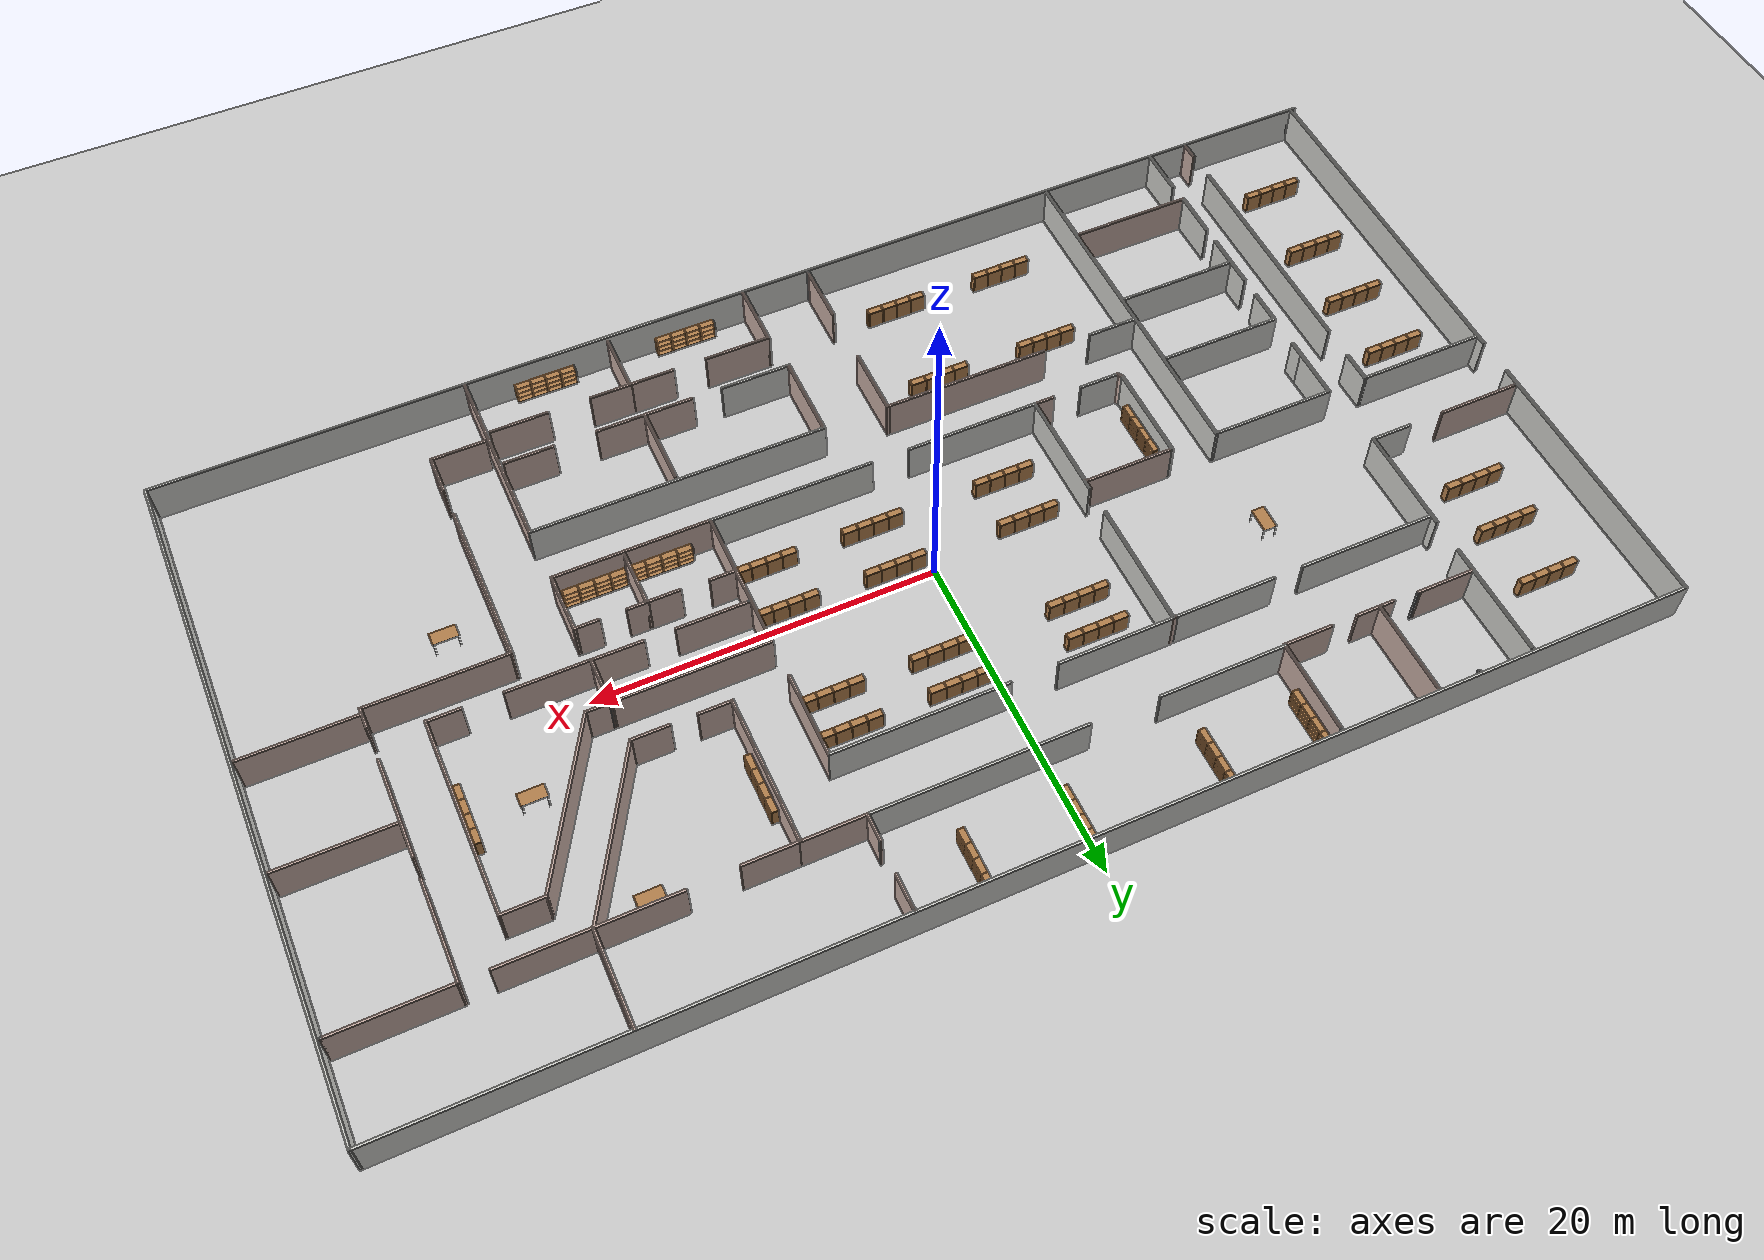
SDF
<sdf version="1.6">
 <world name="default">
  <light name="sun" type="directional">
   <pose>0 0 10 0 -0 0</pose>
   <diffuse>0.8 0.8 0.8 1</diffuse>
   <specular>0.2 0.2 0.2 1</specular>
   <attenuation>
    <range>1000</range>
    <constant>0.9</constant>
    <linear>0.01</linear>
    <quadratic>0.001</quadratic>
   </attenuation>
   <direction>-0.5 0.1 -0.9</direction>
  </light>
  <model name="ground_plane">
   <static>1</static>
   <link name="link">
    <collision name="collision">
     <geometry><plane><normal>0 0 1</normal><size>100 100</size></plane></geometry>
     <surface><friction><ode><mu>100</mu><mu2>50</mu2></ode></friction></surface>
    </collision>
    <visual name="visual">
     <cast_shadows>0</cast_shadows>
     <geometry><plane><normal>0 0 1</normal><size>100 100</size></plane></geometry>
     <material>
      <script><uri>file://media/materials/scripts/gazebo.material</uri><name>Gazebo/Grey</name></script>
     </material>
    </visual>
   </link>
  </model>
  <gravity>0 0 -9.8</gravity>
  <magnetic_field>6e-06 2.3e-05 -4.2e-05</magnetic_field>
  <atmosphere type="adiabatic"/>
  <physics name="default_physics" default="0" type="ode">
   <max_step_size>0.001</max_step_size>
   <real_time_factor>1</real_time_factor>
   <real_time_update_rate>1000</real_time_update_rate>
  </physics>
  <scene><ambient>0.4 0.4 0.4 1</ambient><background>0.7 0.7 0.7 1</background><shadows>1</shadows></scene>
  <audio><device>default</device></audio>
  <spherical_coordinates>
   <surface_model>EARTH_WGS84</surface_model>
   <latitude_deg>0</latitude_deg>
   <longitude_deg>0</longitude_deg>
   <elevation>0</elevation>
   <heading_deg>0</heading_deg>
  </spherical_coordinates>
  <model name="floor">
   <link name="Wall_10">
    <pose>0 -20.3 0 0 -0 0</pose>
    <visual name="Wall_10_Visual">
     <pose>0 0 1.25 0 -0 0</pose>
     <geometry><box><size>73.25 0.15 2.5</size></box></geometry>
     <material>
      <script><uri>file://media/materials/scripts/gazebo.material</uri><name>Gazebo/CeilingTiled</name></script>
      <ambient>0.760784 0.662745 0.627451 1</ambient>
     </material>
     <meta><layer>0</layer></meta>
    </visual>
    <collision name="Wall_10_Collision">
     <pose>0 0 1.25 0 -0 0</pose>
     <geometry><box><size>73.25 0.15 2.5</size></box></geometry>
     <surface>
      <friction>
       <ode><mu>1</mu><mu2>1</mu2><fdir1>0 0 0</fdir1><slip1>0</slip1><slip2>0</slip2></ode>
       <torsional>
        <coefficient>1</coefficient>
        <patch_radius>0</patch_radius>
        <surface_radius>0</surface_radius>
        <use_patch_radius>1</use_patch_radius>
        <ode><slip>0</slip></ode>
       </torsional>
      </friction>
      <bounce><restitution_coefficient>0</restitution_coefficient><threshold>1e+06</threshold></bounce>
      <contact>
       <collide_without_contact>0</collide_without_contact>
       <collide_without_contact_bitmask>1</collide_without_contact_bitmask>
       <collide_bitmask>1</collide_bitmask>
       <ode>
        <soft_cfm>0</soft_cfm>
        <soft_erp>0.2</soft_erp>
        <kp>1e+13</kp>
        <kd>1</kd>
        <max_vel>0.01</max_vel>
        <min_depth>0</min_depth>
       </ode>
       <bullet>
        <split_impulse>1</split_impulse>
        <split_impulse_penetration_threshold>-0.01</split_impulse_penetration_threshold>
        <soft_cfm>0</soft_cfm>
        <soft_erp>0.2</soft_erp>
        <kp>1e+13</kp>
        <kd>1</kd>
       </bullet>
      </contact>
     </surface>
    </collision>
   </link>
   <link name="Wall_100">
    <pose>16.5942 0.36536 0 0 -0 3.13626</pose>
    <visual name="Wall_100_Visual">
     <pose>0 0 1.25 0 -0 0</pose>
     <geometry><box><size>3.00028 0.15 2.5</size></box></geometry>
     <material>
      <script><uri>file://media/materials/scripts/gazebo.material</uri><name>Gazebo/Grey</name></script>
      <ambient>0.760784 0.662745 0.627451 1</ambient>
     </material>
     <meta><layer>0</layer></meta>
    </visual>
    <collision name="Wall_100_Collision">
     <pose>0 0 1.25 0 -0 0</pose>
     <geometry><box><size>3.00028 0.15 2.5</size></box></geometry>
     <surface>
      <friction>
       <ode><mu>1</mu><mu2>1</mu2><fdir1>0 0 0</fdir1><slip1>0</slip1><slip2>0</slip2></ode>
       <torsional>
        <coefficient>1</coefficient>
        <patch_radius>0</patch_radius>
        <surface_radius>0</surface_radius>
        <use_patch_radius>1</use_patch_radius>
        <ode><slip>0</slip></ode>
       </torsional>
      </friction>
      <bounce><restitution_coefficient>0</restitution_coefficient><threshold>1e+06</threshold></bounce>
      <contact>
       <collide_without_contact>0</collide_without_contact>
       <collide_without_contact_bitmask>1</collide_without_contact_bitmask>
       <collide_bitmask>1</collide_bitmask>
       <ode>
        <soft_cfm>0</soft_cfm>
        <soft_erp>0.2</soft_erp>
        <kp>1e+13</kp>
        <kd>1</kd>
        <max_vel>0.01</max_vel>
        <min_depth>0</min_depth>
       </ode>
       <bullet>
        <split_impulse>1</split_impulse>
        <split_impulse_penetration_threshold>-0.01</split_impulse_penetration_threshold>
        <soft_cfm>0</soft_cfm>
        <soft_erp>0.2</soft_erp>
        <kp>1e+13</kp>
        <kd>1</kd>
       </bullet>
      </contact>
     </surface>
    </collision>
   </link>
   <link name="Wall_102">
    <pose>11.2692 0.372965 0 0 -0 3.14159</pose>
    <visual name="Wall_102_Visual">
     <pose>0 0 1.25 0 -0 0</pose>
     <geometry><box><size>4.25 0.15 2.5</size></box></geometry>
     <material>
      <script><uri>file://media/materials/scripts/gazebo.material</uri><name>Gazebo/Grey</name></script>
      <ambient>0.760784 0.662745 0.627451 1</ambient>
     </material>
     <meta><layer>0</layer></meta>
    </visual>
    <collision name="Wall_102_Collision">
     <pose>0 0 1.25 0 -0 0</pose>
     <geometry><box><size>4.25 0.15 2.5</size></box></geometry>
     <surface>
      <friction>
       <ode><mu>1</mu><mu2>1</mu2><fdir1>0 0 0</fdir1><slip1>0</slip1><slip2>0</slip2></ode>
       <torsional>
        <coefficient>1</coefficient>
        <patch_radius>0</patch_radius>
        <surface_radius>0</surface_radius>
        <use_patch_radius>1</use_patch_radius>
        <ode><slip>0</slip></ode>
       </torsional>
      </friction>
      <bounce><restitution_coefficient>0</restitution_coefficient><threshold>1e+06</threshold></bounce>
      <contact>
       <collide_without_contact>0</collide_without_contact>
       <collide_without_contact_bitmask>1</collide_without_contact_bitmask>
       <collide_bitmask>1</collide_bitmask>
       <ode>
        <soft_cfm>0</soft_cfm>
        <soft_erp>0.2</soft_erp>
        <kp>1e+13</kp>
        <kd>1</kd>
        <max_vel>0.01</max_vel>
        <min_depth>0</min_depth>
       </ode>
       <bullet>
        <split_impulse>1</split_impulse>
        <split_impulse_penetration_threshold>-0.01</split_impulse_penetration_threshold>
        <soft_cfm>0</soft_cfm>
        <soft_erp>0.2</soft_erp>
        <kp>1e+13</kp>
        <kd>1</kd>
       </bullet>
      </contact>
     </surface>
    </collision>
   </link>
   <link name="Wall_103">
    <pose>9.21925 0.372965 0 0 -0 0</pose>
    <visual name="Wall_103_Visual">
     <pose>0 0 1.25 0 -0 0</pose>
     <geometry><box><size>0.15 0.15 2.5</size></box></geometry>
     <material>
      <script><uri>file://media/materials/scripts/gazebo.material</uri><name>Gazebo/Grey</name></script>
      <ambient>1 1 1 1</ambient>
     </material>
     <meta><layer>0</layer></meta>
    </visual>
    <collision name="Wall_103_Collision">
     <pose>0 0 1.25 0 -0 0</pose>
     <geometry><box><size>0.15 0.15 2.5</size></box></geometry>
     <surface>
      <friction>
       <ode><mu>1</mu><mu2>1</mu2><fdir1>0 0 0</fdir1><slip1>0</slip1><slip2>0</slip2></ode>
       <torsional>
        <coefficient>1</coefficient>
        <patch_radius>0</patch_radius>
        <surface_radius>0</surface_radius>
        <use_patch_radius>1</use_patch_radius>
        <ode><slip>0</slip></ode>
       </torsional>
      </friction>
      <bounce><restitution_coefficient>0</restitution_coefficient><threshold>1e+06</threshold></bounce>
      <contact>
       <collide_without_contact>0</collide_without_contact>
       <collide_without_contact_bitmask>1</collide_without_contact_bitmask>
       <collide_bitmask>1</collide_bitmask>
       <ode>
        <soft_cfm>0</soft_cfm>
        <soft_erp>0.2</soft_erp>
        <kp>1e+13</kp>
        <kd>1</kd>
        <max_vel>0.01</max_vel>
        <min_depth>0</min_depth>
       </ode>
       <bullet>
        <split_impulse>1</split_impulse>
        <split_impulse_penetration_threshold>-0.01</split_impulse_penetration_threshold>
        <soft_cfm>0</soft_cfm>
        <soft_erp>0.2</soft_erp>
        <kp>1e+13</kp>
        <kd>1</kd>
       </bullet>
      </contact>
     </surface>
    </collision>
   </link>
   <link name="Wall_105">
    <pose>-17.3392 -8.73612 0 0 -0 0</pose>
    <visual name="Wall_105_Visual">
     <pose>0 0 1.25 0 -0 0</pose>
     <geometry><box><size>3 0.15 2.5</size></box></geometry>
     <material>
      <script><uri>file://media/materials/scripts/gazebo.material</uri><name>Gazebo/CeilingTiled</name></script>
      <ambient>0.760784 0.662745 0.627451 1</ambient>
     </material>
     <meta><layer>0</layer></meta>
    </visual>
    <collision name="Wall_105_Collision">
     <pose>0 0 1.25 0 -0 0</pose>
     <geometry><box><size>3 0.15 2.5</size></box></geometry>
     <surface>
      <friction>
       <ode><mu>1</mu><mu2>1</mu2><fdir1>0 0 0</fdir1><slip1>0</slip1><slip2>0</slip2></ode>
       <torsional>
        <coefficient>1</coefficient>
        <patch_radius>0</patch_radius>
        <surface_radius>0</surface_radius>
        <use_patch_radius>1</use_patch_radius>
        <ode><slip>0</slip></ode>
       </torsional>
      </friction>
      <bounce><restitution_coefficient>0</restitution_coefficient><threshold>1e+06</threshold></bounce>
      <contact>
       <collide_without_contact>0</collide_without_contact>
       <collide_without_contact_bitmask>1</collide_without_contact_bitmask>
       <collide_bitmask>1</collide_bitmask>
       <ode>
        <soft_cfm>0</soft_cfm>
        <soft_erp>0.2</soft_erp>
        <kp>1e+13</kp>
        <kd>1</kd>
        <max_vel>0.01</max_vel>
        <min_depth>0</min_depth>
       </ode>
       <bullet>
        <split_impulse>1</split_impulse>
        <split_impulse_penetration_threshold>-0.01</split_impulse_penetration_threshold>
        <soft_cfm>0</soft_cfm>
        <soft_erp>0.2</soft_erp>
        <kp>1e+13</kp>
        <kd>1</kd>
       </bullet>
      </contact>
     </surface>
    </collision>
   </link>
   <link name="Wall_107">
    <pose>-7.93599 -8.73612 0 0 -0 0</pose>
    <visual name="Wall_107_Visual">
     <pose>0 0 1.25 0 -0 0</pose>
     <geometry><box><size>10.0936 0.15 2.5</size></box></geometry>
     <material>
      <script><uri>file://media/materials/scripts/gazebo.material</uri><name>Gazebo/Grey</name></script>
      <ambient>0.760784 0.662745 0.627451 1</ambient>
     </material>
     <meta><layer>0</layer></meta>
    </visual>
    <collision name="Wall_107_Collision">
     <pose>0 0 1.25 0 -0 0</pose>
     <geometry><box><size>10.0936 0.15 2.5</size></box></geometry>
     <surface>
      <friction>
       <ode><mu>1</mu><mu2>1</mu2><fdir1>0 0 0</fdir1><slip1>0</slip1><slip2>0</slip2></ode>
       <torsional>
        <coefficient>1</coefficient>
        <patch_radius>0</patch_radius>
        <surface_radius>0</surface_radius>
        <use_patch_radius>1</use_patch_radius>
        <ode><slip>0</slip></ode>
       </torsional>
      </friction>
      <bounce><restitution_coefficient>0</restitution_coefficient><threshold>1e+06</threshold></bounce>
      <contact>
       <collide_without_contact>0</collide_without_contact>
       <collide_without_contact_bitmask>1</collide_without_contact_bitmask>
       <collide_bitmask>1</collide_bitmask>
       <ode>
        <soft_cfm>0</soft_cfm>
        <soft_erp>0.2</soft_erp>
        <kp>1e+13</kp>
        <kd>1</kd>
        <max_vel>0.01</max_vel>
        <min_depth>0</min_depth>
       </ode>
       <bullet>
        <split_impulse>1</split_impulse>
        <split_impulse_penetration_threshold>-0.01</split_impulse_penetration_threshold>
        <soft_cfm>0</soft_cfm>
        <soft_erp>0.2</soft_erp>
        <kp>1e+13</kp>
        <kd>1</kd>
       </bullet>
      </contact>
     </surface>
    </collision>
   </link>
   <link name="Wall_108">
    <pose>-2.9642 -10.7861 0 0 0 -1.5708</pose>
    <visual name="Wall_108_Visual">
     <pose>0 0 1.25 0 -0 0</pose>
     <geometry><box><size>4.25 0.15 2.5</size></box></geometry>
     <material>
      <script><uri>file://media/materials/scripts/gazebo.material</uri><name>Gazebo/Grey</name></script>
      <ambient>0.760784 0.662745 0.627451 1</ambient>
     </material>
     <meta><layer>0</layer></meta>
    </visual>
    <collision name="Wall_108_Collision">
     <pose>0 0 1.25 0 -0 0</pose>
     <geometry><box><size>4.25 0.15 2.5</size></box></geometry>
     <surface>
      <friction>
       <ode><mu>1</mu><mu2>1</mu2><fdir1>0 0 0</fdir1><slip1>0</slip1><slip2>0</slip2></ode>
       <torsional>
        <coefficient>1</coefficient>
        <patch_radius>0</patch_radius>
        <surface_radius>0</surface_radius>
        <use_patch_radius>1</use_patch_radius>
        <ode><slip>0</slip></ode>
       </torsional>
      </friction>
      <bounce><restitution_coefficient>0</restitution_coefficient><threshold>1e+06</threshold></bounce>
      <contact>
       <collide_without_contact>0</collide_without_contact>
       <collide_without_contact_bitmask>1</collide_without_contact_bitmask>
       <collide_bitmask>1</collide_bitmask>
       <ode>
        <soft_cfm>0</soft_cfm>
        <soft_erp>0.2</soft_erp>
        <kp>1e+13</kp>
        <kd>1</kd>
        <max_vel>0.01</max_vel>
        <min_depth>0</min_depth>
       </ode>
       <bullet>
        <split_impulse>1</split_impulse>
        <split_impulse_penetration_threshold>-0.01</split_impulse_penetration_threshold>
        <soft_cfm>0</soft_cfm>
        <soft_erp>0.2</soft_erp>
        <kp>1e+13</kp>
        <kd>1</kd>
       </bullet>
      </contact>
     </surface>
    </collision>
   </link>
   <link name="Wall_11">
    <pose>36.55 -1e-06 0 0 -0 1.5708</pose>
    <visual name="Wall_11_Visual">
     <pose>0 0 1.25 0 -0 0</pose>
     <geometry><box><size>40.75 0.15 2.5</size></box></geometry>
     <material>
      <script><uri>file://media/materials/scripts/gazebo.material</uri><name>Gazebo/CeilingTiled</name></script>
      <ambient>0.760784 0.662745 0.627451 1</ambient>
     </material>
     <meta><layer>0</layer></meta>
    </visual>
    <collision name="Wall_11_Collision">
     <pose>0 0 1.25 0 -0 0</pose>
     <geometry><box><size>40.75 0.15 2.5</size></box></geometry>
     <surface>
      <friction>
       <ode><mu>1</mu><mu2>1</mu2><fdir1>0 0 0</fdir1><slip1>0</slip1><slip2>0</slip2></ode>
       <torsional>
        <coefficient>1</coefficient>
        <patch_radius>0</patch_radius>
        <surface_radius>0</surface_radius>
        <use_patch_radius>1</use_patch_radius>
        <ode><slip>0</slip></ode>
       </torsional>
      </friction>
      <bounce><restitution_coefficient>0</restitution_coefficient><threshold>1e+06</threshold></bounce>
      <contact>
       <collide_without_contact>0</collide_without_contact>
       <collide_without_contact_bitmask>1</collide_without_contact_bitmask>
       <collide_bitmask>1</collide_bitmask>
       <ode>
        <soft_cfm>0</soft_cfm>
        <soft_erp>0.2</soft_erp>
        <kp>1e+13</kp>
        <kd>1</kd>
        <max_vel>0.01</max_vel>
        <min_depth>0</min_depth>
       </ode>
       <bullet>
        <split_impulse>1</split_impulse>
        <split_impulse_penetration_threshold>-0.01</split_impulse_penetration_threshold>
        <soft_cfm>0</soft_cfm>
        <soft_erp>0.2</soft_erp>
        <kp>1e+13</kp>
        <kd>1</kd>
       </bullet>
      </contact>
     </surface>
    </collision>
   </link>
   <link name="Wall_110">
    <pose>-2.9642 -18.2361 0 0 0 -1.5708</pose>
    <visual name="Wall_110_Visual">
     <pose>0 0 1.25 0 -0 0</pose>
     <geometry><box><size>3.75 0.15 2.5</size></box></geometry>
     <material>
      <script><uri>file://media/materials/scripts/gazebo.material</uri><name>Gazebo/Grey</name></script>
      <ambient>0.760784 0.662745 0.627451 1</ambient>
     </material>
     <meta><layer>0</layer></meta>
    </visual>
    <collision name="Wall_110_Collision">
     <pose>0 0 1.25 0 -0 0</pose>
     <geometry><box><size>3.75 0.15 2.5</size></box></geometry>
     <surface>
      <friction>
       <ode><mu>1</mu><mu2>1</mu2><fdir1>0 0 0</fdir1><slip1>0</slip1><slip2>0</slip2></ode>
       <torsional>
        <coefficient>1</coefficient>
        <patch_radius>0</patch_radius>
        <surface_radius>0</surface_radius>
        <use_patch_radius>1</use_patch_radius>
        <ode><slip>0</slip></ode>
       </torsional>
      </friction>
      <bounce><restitution_coefficient>0</restitution_coefficient><threshold>1e+06</threshold></bounce>
      <contact>
       <collide_without_contact>0</collide_without_contact>
       <collide_without_contact_bitmask>1</collide_without_contact_bitmask>
       <collide_bitmask>1</collide_bitmask>
       <ode>
        <soft_cfm>0</soft_cfm>
        <soft_erp>0.2</soft_erp>
        <kp>1e+13</kp>
        <kd>1</kd>
        <max_vel>0.01</max_vel>
        <min_depth>0</min_depth>
       </ode>
       <bullet>
        <split_impulse>1</split_impulse>
        <split_impulse_penetration_threshold>-0.01</split_impulse_penetration_threshold>
        <soft_cfm>0</soft_cfm>
        <soft_erp>0.2</soft_erp>
        <kp>1e+13</kp>
        <kd>1</kd>
       </bullet>
      </contact>
     </surface>
    </collision>
   </link>
   <link name="Wall_111">
    <pose>-2.9642 -20.0861 0 0 0 -1.5708</pose>
    <visual name="Wall_111_Visual">
     <pose>0 0 1.25 0 -0 0</pose>
     <geometry><box><size>0.25 0.15 2.5</size></box></geometry>
     <material>
      <script><uri>file://media/materials/scripts/gazebo.material</uri><name>Gazebo/Grey</name></script>
      <ambient>1 1 1 1</ambient>
     </material>
     <meta><layer>0</layer></meta>
    </visual>
    <collision name="Wall_111_Collision">
     <pose>0 0 1.25 0 -0 0</pose>
     <geometry><box><size>0.25 0.15 2.5</size></box></geometry>
     <surface>
      <friction>
       <ode><mu>1</mu><mu2>1</mu2><fdir1>0 0 0</fdir1><slip1>0</slip1><slip2>0</slip2></ode>
       <torsional>
        <coefficient>1</coefficient>
        <patch_radius>0</patch_radius>
        <surface_radius>0</surface_radius>
        <use_patch_radius>1</use_patch_radius>
        <ode><slip>0</slip></ode>
       </torsional>
      </friction>
      <bounce><restitution_coefficient>0</restitution_coefficient><threshold>1e+06</threshold></bounce>
      <contact>
       <collide_without_contact>0</collide_without_contact>
       <collide_without_contact_bitmask>1</collide_without_contact_bitmask>
       <collide_bitmask>1</collide_bitmask>
       <ode>
        <soft_cfm>0</soft_cfm>
        <soft_erp>0.2</soft_erp>
        <kp>1e+13</kp>
        <kd>1</kd>
        <max_vel>0.01</max_vel>
        <min_depth>0</min_depth>
       </ode>
       <bullet>
        <split_impulse>1</split_impulse>
        <split_impulse_penetration_threshold>-0.01</split_impulse_penetration_threshold>
        <soft_cfm>0</soft_cfm>
        <soft_erp>0.2</soft_erp>
        <kp>1e+13</kp>
        <kd>1</kd>
       </bullet>
      </contact>
     </surface>
    </collision>
   </link>
   <link name="Wall_113">
    <pose>9.60314 -8.79868 0 0 -0 0</pose>
    <visual name="Wall_113_Visual">
     <pose>0 0 1.25 0 -0 0</pose>
     <geometry><box><size>17.5 0.15 2.5</size></box></geometry>
     <material>
      <script><uri>file://media/materials/scripts/gazebo.material</uri><name>Gazebo/CeilingTiled</name></script>
      <ambient>0.760784 0.662745 0.627451 1</ambient>
     </material>
     <meta><layer>0</layer></meta>
    </visual>
    <collision name="Wall_113_Collision">
     <pose>0 0 1.25 0 -0 0</pose>
     <geometry><box><size>17.5 0.15 2.5</size></box></geometry>
     <surface>
      <friction>
       <ode><mu>1</mu><mu2>1</mu2><fdir1>0 0 0</fdir1><slip1>0</slip1><slip2>0</slip2></ode>
       <torsional>
        <coefficient>1</coefficient>
        <patch_radius>0</patch_radius>
        <surface_radius>0</surface_radius>
        <use_patch_radius>1</use_patch_radius>
        <ode><slip>0</slip></ode>
       </torsional>
      </friction>
      <bounce><restitution_coefficient>0</restitution_coefficient><threshold>1e+06</threshold></bounce>
      <contact>
       <collide_without_contact>0</collide_without_contact>
       <collide_without_contact_bitmask>1</collide_without_contact_bitmask>
       <collide_bitmask>1</collide_bitmask>
       <ode>
        <soft_cfm>0</soft_cfm>
        <soft_erp>0.2</soft_erp>
        <kp>1e+13</kp>
        <kd>1</kd>
        <max_vel>0.01</max_vel>
        <min_depth>0</min_depth>
       </ode>
       <bullet>
        <split_impulse>1</split_impulse>
        <split_impulse_penetration_threshold>-0.01</split_impulse_penetration_threshold>
        <soft_cfm>0</soft_cfm>
        <soft_erp>0.2</soft_erp>
        <kp>1e+13</kp>
        <kd>1</kd>
       </bullet>
      </contact>
     </surface>
    </collision>
   </link>
   <link name="Wall_114">
    <pose>18.2781 -14.4737 0 0 0 -1.5708</pose>
    <visual name="Wall_114_Visual">
     <pose>0 0 1.25 0 -0 0</pose>
     <geometry><box><size>11.5 0.15 2.5</size></box></geometry>
     <material>
      <script><uri>file://media/materials/scripts/gazebo.material</uri><name>Gazebo/Grey</name></script>
      <ambient>0.760784 0.662745 0.627451 1</ambient>
     </material>
     <meta><layer>0</layer></meta>
    </visual>
    <collision name="Wall_114_Collision">
     <pose>0 0 1.25 0 -0 0</pose>
     <geometry><box><size>11.5 0.15 2.5</size></box></geometry>
     <surface>
      <friction>
       <ode><mu>1</mu><mu2>1</mu2><fdir1>0 0 0</fdir1><slip1>0</slip1><slip2>0</slip2></ode>
       <torsional>
        <coefficient>1</coefficient>
        <patch_radius>0</patch_radius>
        <surface_radius>0</surface_radius>
        <use_patch_radius>1</use_patch_radius>
        <ode><slip>0</slip></ode>
       </torsional>
      </friction>
      <bounce><restitution_coefficient>0</restitution_coefficient><threshold>1e+06</threshold></bounce>
      <contact>
       <collide_without_contact>0</collide_without_contact>
       <collide_without_contact_bitmask>1</collide_without_contact_bitmask>
       <collide_bitmask>1</collide_bitmask>
       <ode>
        <soft_cfm>0</soft_cfm>
        <soft_erp>0.2</soft_erp>
        <kp>1e+13</kp>
        <kd>1</kd>
        <max_vel>0.01</max_vel>
        <min_depth>0</min_depth>
       </ode>
       <bullet>
        <split_impulse>1</split_impulse>
        <split_impulse_penetration_threshold>-0.01</split_impulse_penetration_threshold>
        <soft_cfm>0</soft_cfm>
        <soft_erp>0.2</soft_erp>
        <kp>1e+13</kp>
        <kd>1</kd>
       </bullet>
      </contact>
     </surface>
    </collision>
   </link>
   <link name="Wall_116">
    <pose>0.928137 -11.3487 0 0 0 -1.5708</pose>
    <visual name="Wall_116_Visual">
     <pose>0 0 1.25 0 -0 0</pose>
     <geometry><box><size>5.25 0.15 2.5</size></box></geometry>
     <material>
      <script><uri>file://media/materials/scripts/gazebo.material</uri><name>Gazebo/Grey</name></script>
      <ambient>0.760784 0.662745 0.627451 1</ambient>
     </material>
     <meta><layer>0</layer></meta>
    </visual>
    <collision name="Wall_116_Collision">
     <pose>0 0 1.25 0 -0 0</pose>
     <geometry><box><size>5.25 0.15 2.5</size></box></geometry>
     <surface>
      <friction>
       <ode><mu>1</mu><mu2>1</mu2><fdir1>0 0 0</fdir1><slip1>0</slip1><slip2>0</slip2></ode>
       <torsional>
        <coefficient>1</coefficient>
        <patch_radius>0</patch_radius>
        <surface_radius>0</surface_radius>
        <use_patch_radius>1</use_patch_radius>
        <ode><slip>0</slip></ode>
       </torsional>
      </friction>
      <bounce><restitution_coefficient>0</restitution_coefficient><threshold>1e+06</threshold></bounce>
      <contact>
       <collide_without_contact>0</collide_without_contact>
       <collide_without_contact_bitmask>1</collide_without_contact_bitmask>
       <collide_bitmask>1</collide_bitmask>
       <ode>
        <soft_cfm>0</soft_cfm>
        <soft_erp>0.2</soft_erp>
        <kp>1e+13</kp>
        <kd>1</kd>
        <max_vel>0.01</max_vel>
        <min_depth>0</min_depth>
       </ode>
       <bullet>
        <split_impulse>1</split_impulse>
        <split_impulse_penetration_threshold>-0.01</split_impulse_penetration_threshold>
        <soft_cfm>0</soft_cfm>
        <soft_erp>0.2</soft_erp>
        <kp>1e+13</kp>
        <kd>1</kd>
       </bullet>
      </contact>
     </surface>
    </collision>
   </link>
   <link name="Wall_117">
    <pose>2.97814 -13.8987 0 0 -0 0</pose>
    <visual name="Wall_117_Visual">
     <pose>0 0 1.25 0 -0 0</pose>
     <geometry><box><size>4.25 0.15 2.5</size></box></geometry>
     <material>
      <script><uri>file://media/materials/scripts/gazebo.material</uri><name>Gazebo/CeilingTiled</name></script>
      <ambient>0.760784 0.662745 0.627451 1</ambient>
     </material>
     <meta><layer>0</layer></meta>
    </visual>
    <collision name="Wall_117_Collision">
     <pose>0 0 1.25 0 -0 0</pose>
     <geometry><box><size>4.25 0.15 2.5</size></box></geometry>
     <surface>
      <friction>
       <ode><mu>1</mu><mu2>1</mu2><fdir1>0 0 0</fdir1><slip1>0</slip1><slip2>0</slip2></ode>
       <torsional>
        <coefficient>1</coefficient>
        <patch_radius>0</patch_radius>
        <surface_radius>0</surface_radius>
        <use_patch_radius>1</use_patch_radius>
        <ode><slip>0</slip></ode>
       </torsional>
      </friction>
      <bounce><restitution_coefficient>0</restitution_coefficient><threshold>1e+06</threshold></bounce>
      <contact>
       <collide_without_contact>0</collide_without_contact>
       <collide_without_contact_bitmask>1</collide_without_contact_bitmask>
       <collide_bitmask>1</collide_bitmask>
       <ode>
        <soft_cfm>0</soft_cfm>
        <soft_erp>0.2</soft_erp>
        <kp>1e+13</kp>
        <kd>1</kd>
        <max_vel>0.01</max_vel>
        <min_depth>0</min_depth>
       </ode>
       <bullet>
        <split_impulse>1</split_impulse>
        <split_impulse_penetration_threshold>-0.01</split_impulse_penetration_threshold>
        <soft_cfm>0</soft_cfm>
        <soft_erp>0.2</soft_erp>
        <kp>1e+13</kp>
        <kd>1</kd>
       </bullet>
      </contact>
     </surface>
    </collision>
   </link>
   <link name="Wall_119">
    <pose>8.30314 -13.8987 0 0 -0 0</pose>
    <visual name="Wall_119_Visual">
     <pose>0 0 1.25 0 -0 0</pose>
     <geometry><box><size>3 0.15 2.5</size></box></geometry>
     <material>
      <script><uri>file://media/materials/scripts/gazebo.material</uri><name>Gazebo/Grey</name></script>
      <ambient>0.760784 0.662745 0.627451 1</ambient>
     </material>
     <meta><layer>0</layer></meta>
    </visual>
    <collision name="Wall_119_Collision">
     <pose>0 0 1.25 0 -0 0</pose>
     <geometry><box><size>3 0.15 2.5</size></box></geometry>
     <surface>
      <friction>
       <ode><mu>1</mu><mu2>1</mu2><fdir1>0 0 0</fdir1><slip1>0</slip1><slip2>0</slip2></ode>
       <torsional>
        <coefficient>1</coefficient>
        <patch_radius>0</patch_radius>
        <surface_radius>0</surface_radius>
        <use_patch_radius>1</use_patch_radius>
        <ode><slip>0</slip></ode>
       </torsional>
      </friction>
      <bounce><restitution_coefficient>0</restitution_coefficient><threshold>1e+06</threshold></bounce>
      <contact>
       <collide_without_contact>0</collide_without_contact>
       <collide_without_contact_bitmask>1</collide_without_contact_bitmask>
       <collide_bitmask>1</collide_bitmask>
       <ode>
        <soft_cfm>0</soft_cfm>
        <soft_erp>0.2</soft_erp>
        <kp>1e+13</kp>
        <kd>1</kd>
        <max_vel>0.01</max_vel>
        <min_depth>0</min_depth>
       </ode>
       <bullet>
        <split_impulse>1</split_impulse>
        <split_impulse_penetration_threshold>-0.01</split_impulse_penetration_threshold>
        <soft_cfm>0</soft_cfm>
        <soft_erp>0.2</soft_erp>
        <kp>1e+13</kp>
        <kd>1</kd>
       </bullet>
      </contact>
     </surface>
    </collision>
   </link>
   <link name="Wall_12">
    <pose>0.125 20.3 0 0 -0 3.14159</pose>
    <visual name="Wall_12_Visual">
     <pose>0 0 1.25 0 -0 0</pose>
     <geometry><box><size>73 0.15 2.5</size></box></geometry>
     <material>
      <script><uri>file://media/materials/scripts/gazebo.material</uri><name>Gazebo/CeilingTiled</name></script>
      <ambient>0.760784 0.662745 0.627451 1</ambient>
     </material>
     <meta><layer>0</layer></meta>
    </visual>
    <collision name="Wall_12_Collision">
     <pose>0 0 1.25 0 -0 0</pose>
     <geometry><box><size>73 0.15 2.5</size></box></geometry>
     <surface>
      <friction>
       <ode><mu>1</mu><mu2>1</mu2><fdir1>0 0 0</fdir1><slip1>0</slip1><slip2>0</slip2></ode>
       <torsional>
        <coefficient>1</coefficient>
        <patch_radius>0</patch_radius>
        <surface_radius>0</surface_radius>
        <use_patch_radius>1</use_patch_radius>
        <ode><slip>0</slip></ode>
       </torsional>
      </friction>
      <bounce><restitution_coefficient>0</restitution_coefficient><threshold>1e+06</threshold></bounce>
      <contact>
       <collide_without_contact>0</collide_without_contact>
       <collide_without_contact_bitmask>1</collide_without_contact_bitmask>
       <collide_bitmask>1</collide_bitmask>
       <ode>
        <soft_cfm>0</soft_cfm>
        <soft_erp>0.2</soft_erp>
        <kp>1e+13</kp>
        <kd>1</kd>
        <max_vel>0.01</max_vel>
        <min_depth>0</min_depth>
       </ode>
       <bullet>
        <split_impulse>1</split_impulse>
        <split_impulse_penetration_threshold>-0.01</split_impulse_penetration_threshold>
        <soft_cfm>0</soft_cfm>
        <soft_erp>0.2</soft_erp>
        <kp>1e+13</kp>
        <kd>1</kd>
       </bullet>
      </contact>
     </surface>
    </collision>
   </link>
   <link name="Wall_120">
    <pose>9.72814 -11.4737 0 0 -0 1.5708</pose>
    <visual name="Wall_120_Visual">
     <pose>0 0 1.25 0 -0 0</pose>
     <geometry><box><size>5 0.15 2.5</size></box></geometry>
     <material>
      <script><uri>file://media/materials/scripts/gazebo.material</uri><name>Gazebo/Grey</name></script>
      <ambient>0.760784 0.662745 0.627451 1</ambient>
     </material>
     <meta><layer>0</layer></meta>
    </visual>
    <collision name="Wall_120_Collision">
     <pose>0 0 1.25 0 -0 0</pose>
     <geometry><box><size>5 0.15 2.5</size></box></geometry>
     <surface>
      <friction>
       <ode><mu>1</mu><mu2>1</mu2><fdir1>0 0 0</fdir1><slip1>0</slip1><slip2>0</slip2></ode>
       <torsional>
        <coefficient>1</coefficient>
        <patch_radius>0</patch_radius>
        <surface_radius>0</surface_radius>
        <use_patch_radius>1</use_patch_radius>
        <ode><slip>0</slip></ode>
       </torsional>
      </friction>
      <bounce><restitution_coefficient>0</restitution_coefficient><threshold>1e+06</threshold></bounce>
      <contact>
       <collide_without_contact>0</collide_without_contact>
       <collide_without_contact_bitmask>1</collide_without_contact_bitmask>
       <collide_bitmask>1</collide_bitmask>
       <ode>
        <soft_cfm>0</soft_cfm>
        <soft_erp>0.2</soft_erp>
        <kp>1e+13</kp>
        <kd>1</kd>
        <max_vel>0.01</max_vel>
        <min_depth>0</min_depth>
       </ode>
       <bullet>
        <split_impulse>1</split_impulse>
        <split_impulse_penetration_threshold>-0.01</split_impulse_penetration_threshold>
        <soft_cfm>0</soft_cfm>
        <soft_erp>0.2</soft_erp>
        <kp>1e+13</kp>
        <kd>1</kd>
       </bullet>
      </contact>
     </surface>
    </collision>
   </link>
   <link name="Wall_122">
    <pose>11.1531 -13.8987 0 0 -0 0</pose>
    <visual name="Wall_122_Visual">
     <pose>0 0 1.25 0 -0 0</pose>
     <geometry><box><size>3 0.15 2.5</size></box></geometry>
     <material>
      <script><uri>file://media/materials/scripts/gazebo.material</uri><name>Gazebo/Grey</name></script>
      <ambient>0.760784 0.662745 0.627451 1</ambient>
     </material>
     <meta><layer>0</layer></meta>
    </visual>
    <collision name="Wall_122_Collision">
     <pose>0 0 1.25 0 -0 0</pose>
     <geometry><box><size>3 0.15 2.5</size></box></geometry>
     <surface>
      <friction>
       <ode><mu>1</mu><mu2>1</mu2><fdir1>0 0 0</fdir1><slip1>0</slip1><slip2>0</slip2></ode>
       <torsional>
        <coefficient>1</coefficient>
        <patch_radius>0</patch_radius>
        <surface_radius>0</surface_radius>
        <use_patch_radius>1</use_patch_radius>
        <ode><slip>0</slip></ode>
       </torsional>
      </friction>
      <bounce><restitution_coefficient>0</restitution_coefficient><threshold>1e+06</threshold></bounce>
      <contact>
       <collide_without_contact>0</collide_without_contact>
       <collide_without_contact_bitmask>1</collide_without_contact_bitmask>
       <collide_bitmask>1</collide_bitmask>
       <ode>
        <soft_cfm>0</soft_cfm>
        <soft_erp>0.2</soft_erp>
        <kp>1e+13</kp>
        <kd>1</kd>
        <max_vel>0.01</max_vel>
        <min_depth>0</min_depth>
       </ode>
       <bullet>
        <split_impulse>1</split_impulse>
        <split_impulse_penetration_threshold>-0.01</split_impulse_penetration_threshold>
        <soft_cfm>0</soft_cfm>
        <soft_erp>0.2</soft_erp>
        <kp>1e+13</kp>
        <kd>1</kd>
       </bullet>
      </contact>
     </surface>
    </collision>
   </link>
   <link name="Wall_124">
    <pose>16.6031 -13.8987 0 0 -0 0</pose>
    <visual name="Wall_124_Visual">
     <pose>0 0 1.25 0 -0 0</pose>
     <geometry><box><size>3 0.15 2.5</size></box></geometry>
     <material>
      <script><uri>file://media/materials/scripts/gazebo.material</uri><name>Gazebo/Grey</name></script>
      <ambient>0.760784 0.662745 0.627451 1</ambient>
     </material>
     <meta><layer>0</layer></meta>
    </visual>
    <collision name="Wall_124_Collision">
     <pose>0 0 1.25 0 -0 0</pose>
     <geometry><box><size>3 0.15 2.5</size></box></geometry>
     <surface>
      <friction>
       <ode><mu>1</mu><mu2>1</mu2><fdir1>0 0 0</fdir1><slip1>0</slip1><slip2>0</slip2></ode>
       <torsional>
        <coefficient>1</coefficient>
        <patch_radius>0</patch_radius>
        <surface_radius>0</surface_radius>
        <use_patch_radius>1</use_patch_radius>
        <ode><slip>0</slip></ode>
       </torsional>
      </friction>
      <bounce><restitution_coefficient>0</restitution_coefficient><threshold>1e+06</threshold></bounce>
      <contact>
       <collide_without_contact>0</collide_without_contact>
       <collide_without_contact_bitmask>1</collide_without_contact_bitmask>
       <collide_bitmask>1</collide_bitmask>
       <ode>
        <soft_cfm>0</soft_cfm>
        <soft_erp>0.2</soft_erp>
        <kp>1e+13</kp>
        <kd>1</kd>
        <max_vel>0.01</max_vel>
        <min_depth>0</min_depth>
       </ode>
       <bullet>
        <split_impulse>1</split_impulse>
        <split_impulse_penetration_threshold>-0.01</split_impulse_penetration_threshold>
        <soft_cfm>0</soft_cfm>
        <soft_erp>0.2</soft_erp>
        <kp>1e+13</kp>
        <kd>1</kd>
       </bullet>
      </contact>
     </surface>
    </collision>
   </link>
   <link name="Wall_126">
    <pose>1.17225 -18.2656 0 0 -0 1.5708</pose>
    <visual name="Wall_126_Visual">
     <pose>0 0 1.25 0 -0 0</pose>
     <geometry><box><size>4 0.15 2.5</size></box></geometry>
     <material>
      <script><uri>file://media/materials/scripts/gazebo.material</uri><name>Gazebo/Grey</name></script>
      <ambient>0.760784 0.662745 0.627451 1</ambient>
     </material>
     <meta><layer>0</layer></meta>
    </visual>
    <collision name="Wall_126_Collision">
     <pose>0 0 1.25 0 -0 0</pose>
     <geometry><box><size>4 0.15 2.5</size></box></geometry>
     <surface>
      <friction>
       <ode><mu>1</mu><mu2>1</mu2><fdir1>0 0 0</fdir1><slip1>0</slip1><slip2>0</slip2></ode>
       <torsional>
        <coefficient>1</coefficient>
        <patch_radius>0</patch_radius>
        <surface_radius>0</surface_radius>
        <use_patch_radius>1</use_patch_radius>
        <ode><slip>0</slip></ode>
       </torsional>
      </friction>
      <bounce><restitution_coefficient>0</restitution_coefficient><threshold>1e+06</threshold></bounce>
      <contact>
       <collide_without_contact>0</collide_without_contact>
       <collide_without_contact_bitmask>1</collide_without_contact_bitmask>
       <collide_bitmask>1</collide_bitmask>
       <ode>
        <soft_cfm>0</soft_cfm>
        <soft_erp>0.2</soft_erp>
        <kp>1e+13</kp>
        <kd>1</kd>
        <max_vel>0.01</max_vel>
        <min_depth>0</min_depth>
       </ode>
       <bullet>
        <split_impulse>1</split_impulse>
        <split_impulse_penetration_threshold>-0.01</split_impulse_penetration_threshold>
        <soft_cfm>0</soft_cfm>
        <soft_erp>0.2</soft_erp>
        <kp>1e+13</kp>
        <kd>1</kd>
       </bullet>
      </contact>
     </surface>
    </collision>
   </link>
   <link name="Wall_127">
    <pose>3.09725 -16.3406 0 0 -0 0</pose>
    <visual name="Wall_127_Visual">
     <pose>0 0 1.25 0 -0 0</pose>
     <geometry><box><size>4 0.15 2.5</size></box></geometry>
     <material>
      <script><uri>file://media/materials/scripts/gazebo.material</uri><name>Gazebo/Grey</name></script>
      <ambient>0.760784 0.662745 0.627451 1</ambient>
     </material>
     <meta><layer>0</layer></meta>
    </visual>
    <collision name="Wall_127_Collision">
     <pose>0 0 1.25 0 -0 0</pose>
     <geometry><box><size>4 0.15 2.5</size></box></geometry>
     <surface>
      <friction>
       <ode><mu>1</mu><mu2>1</mu2><fdir1>0 0 0</fdir1><slip1>0</slip1><slip2>0</slip2></ode>
       <torsional>
        <coefficient>1</coefficient>
        <patch_radius>0</patch_radius>
        <surface_radius>0</surface_radius>
        <use_patch_radius>1</use_patch_radius>
        <ode><slip>0</slip></ode>
       </torsional>
      </friction>
      <bounce><restitution_coefficient>0</restitution_coefficient><threshold>1e+06</threshold></bounce>
      <contact>
       <collide_without_contact>0</collide_without_contact>
       <collide_without_contact_bitmask>1</collide_without_contact_bitmask>
       <collide_bitmask>1</collide_bitmask>
       <ode>
        <soft_cfm>0</soft_cfm>
        <soft_erp>0.2</soft_erp>
        <kp>1e+13</kp>
        <kd>1</kd>
        <max_vel>0.01</max_vel>
        <min_depth>0</min_depth>
       </ode>
       <bullet>
        <split_impulse>1</split_impulse>
        <split_impulse_penetration_threshold>-0.01</split_impulse_penetration_threshold>
        <soft_cfm>0</soft_cfm>
        <soft_erp>0.2</soft_erp>
        <kp>1e+13</kp>
        <kd>1</kd>
       </bullet>
      </contact>
     </surface>
    </collision>
   </link>
   <link name="Wall_129">
    <pose>8.42225 -16.3406 0 0 -0 0</pose>
    <visual name="Wall_129_Visual">
     <pose>0 0 1.25 0 -0 0</pose>
     <geometry><box><size>2.75 0.15 2.5</size></box></geometry>
     <material>
      <script><uri>file://media/materials/scripts/gazebo.material</uri><name>Gazebo/Grey</name></script>
      <ambient>0.760784 0.662745 0.627451 1</ambient>
     </material>
     <meta><layer>0</layer></meta>
    </visual>
    <collision name="Wall_129_Collision">
     <pose>0 0 1.25 0 -0 0</pose>
     <geometry><box><size>2.75 0.15 2.5</size></box></geometry>
     <surface>
      <friction>
       <ode><mu>1</mu><mu2>1</mu2><fdir1>0 0 0</fdir1><slip1>0</slip1><slip2>0</slip2></ode>
       <torsional>
        <coefficient>1</coefficient>
        <patch_radius>0</patch_radius>
        <surface_radius>0</surface_radius>
        <use_patch_radius>1</use_patch_radius>
        <ode><slip>0</slip></ode>
       </torsional>
      </friction>
      <bounce><restitution_coefficient>0</restitution_coefficient><threshold>1e+06</threshold></bounce>
      <contact>
       <collide_without_contact>0</collide_without_contact>
       <collide_without_contact_bitmask>1</collide_without_contact_bitmask>
       <collide_bitmask>1</collide_bitmask>
       <ode>
        <soft_cfm>0</soft_cfm>
        <soft_erp>0.2</soft_erp>
        <kp>1e+13</kp>
        <kd>1</kd>
        <max_vel>0.01</max_vel>
        <min_depth>0</min_depth>
       </ode>
       <bullet>
        <split_impulse>1</split_impulse>
        <split_impulse_penetration_threshold>-0.01</split_impulse_penetration_threshold>
        <soft_cfm>0</soft_cfm>
        <soft_erp>0.2</soft_erp>
        <kp>1e+13</kp>
        <kd>1</kd>
       </bullet>
      </contact>
     </surface>
    </collision>
   </link>
   <link name="Wall_13">
    <pose>-36.3 12 0 0 0 -1.5708</pose>
    <visual name="Wall_13_Visual">
     <pose>0 0 1.25 0 -0 0</pose>
     <geometry><box><size>16.75 0.15 2.5</size></box></geometry>
     <material>
      <script><uri>file://media/materials/scripts/gazebo.material</uri><name>Gazebo/CeilingTiled</name></script>
      <ambient>0.760784 0.662745 0.627451 1</ambient>
     </material>
     <meta><layer>0</layer></meta>
    </visual>
    <collision name="Wall_13_Collision">
     <pose>0 0 1.25 0 -0 0</pose>
     <geometry><box><size>16.75 0.15 2.5</size></box></geometry>
     <surface>
      <friction>
       <ode><mu>1</mu><mu2>1</mu2><fdir1>0 0 0</fdir1><slip1>0</slip1><slip2>0</slip2></ode>
       <torsional>
        <coefficient>1</coefficient>
        <patch_radius>0</patch_radius>
        <surface_radius>0</surface_radius>
        <use_patch_radius>1</use_patch_radius>
        <ode><slip>0</slip></ode>
       </torsional>
      </friction>
      <bounce><restitution_coefficient>0</restitution_coefficient><threshold>1e+06</threshold></bounce>
      <contact>
       <collide_without_contact>0</collide_without_contact>
       <collide_without_contact_bitmask>1</collide_without_contact_bitmask>
       <collide_bitmask>1</collide_bitmask>
       <ode>
        <soft_cfm>0</soft_cfm>
        <soft_erp>0.2</soft_erp>
        <kp>1e+13</kp>
        <kd>1</kd>
        <max_vel>0.01</max_vel>
        <min_depth>0</min_depth>
       </ode>
       <bullet>
        <split_impulse>1</split_impulse>
        <split_impulse_penetration_threshold>-0.01</split_impulse_penetration_threshold>
        <soft_cfm>0</soft_cfm>
        <soft_erp>0.2</soft_erp>
        <kp>1e+13</kp>
        <kd>1</kd>
       </bullet>
      </contact>
     </surface>
    </collision>
   </link>
   <link name="Wall_130">
    <pose>9.72225 -18.1406 0 0 0 -1.5708</pose>
    <visual name="Wall_130_Visual">
     <pose>0 0 1.25 0 -0 0</pose>
     <geometry><box><size>3.75 0.15 2.5</size></box></geometry>
     <material>
      <script><uri>file://media/materials/scripts/gazebo.material</uri><name>Gazebo/Grey</name></script>
      <ambient>0.760784 0.662745 0.627451 1</ambient>
     </material>
     <meta><layer>0</layer></meta>
    </visual>
    <collision name="Wall_130_Collision">
     <pose>0 0 1.25 0 -0 0</pose>
     <geometry><box><size>3.75 0.15 2.5</size></box></geometry>
     <surface>
      <friction>
       <ode><mu>1</mu><mu2>1</mu2><fdir1>0 0 0</fdir1><slip1>0</slip1><slip2>0</slip2></ode>
       <torsional>
        <coefficient>1</coefficient>
        <patch_radius>0</patch_radius>
        <surface_radius>0</surface_radius>
        <use_patch_radius>1</use_patch_radius>
        <ode><slip>0</slip></ode>
       </torsional>
      </friction>
      <bounce><restitution_coefficient>0</restitution_coefficient><threshold>1e+06</threshold></bounce>
      <contact>
       <collide_without_contact>0</collide_without_contact>
       <collide_without_contact_bitmask>1</collide_without_contact_bitmask>
       <collide_bitmask>1</collide_bitmask>
       <ode>
        <soft_cfm>0</soft_cfm>
        <soft_erp>0.2</soft_erp>
        <kp>1e+13</kp>
        <kd>1</kd>
        <max_vel>0.01</max_vel>
        <min_depth>0</min_depth>
       </ode>
       <bullet>
        <split_impulse>1</split_impulse>
        <split_impulse_penetration_threshold>-0.01</split_impulse_penetration_threshold>
        <soft_cfm>0</soft_cfm>
        <soft_erp>0.2</soft_erp>
        <kp>1e+13</kp>
        <kd>1</kd>
       </bullet>
      </contact>
     </surface>
    </collision>
   </link>
   <link name="Wall_132">
    <pose>10.8972 -16.3406 0 0 -0 0</pose>
    <visual name="Wall_132_Visual">
     <pose>0 0 1.25 0 -0 0</pose>
     <geometry><box><size>2.5 0.15 2.5</size></box></geometry>
     <material>
      <script><uri>file://media/materials/scripts/gazebo.material</uri><name>Gazebo/Grey</name></script>
      <ambient>0.760784 0.662745 0.627451 1</ambient>
     </material>
     <meta><layer>0</layer></meta>
    </visual>
    <collision name="Wall_132_Collision">
     <pose>0 0 1.25 0 -0 0</pose>
     <geometry><box><size>2.5 0.15 2.5</size></box></geometry>
     <surface>
      <friction>
       <ode><mu>1</mu><mu2>1</mu2><fdir1>0 0 0</fdir1><slip1>0</slip1><slip2>0</slip2></ode>
       <torsional>
        <coefficient>1</coefficient>
        <patch_radius>0</patch_radius>
        <surface_radius>0</surface_radius>
        <use_patch_radius>1</use_patch_radius>
        <ode><slip>0</slip></ode>
       </torsional>
      </friction>
      <bounce><restitution_coefficient>0</restitution_coefficient><threshold>1e+06</threshold></bounce>
      <contact>
       <collide_without_contact>0</collide_without_contact>
       <collide_without_contact_bitmask>1</collide_without_contact_bitmask>
       <collide_bitmask>1</collide_bitmask>
       <ode>
        <soft_cfm>0</soft_cfm>
        <soft_erp>0.2</soft_erp>
        <kp>1e+13</kp>
        <kd>1</kd>
        <max_vel>0.01</max_vel>
        <min_depth>0</min_depth>
       </ode>
       <bullet>
        <split_impulse>1</split_impulse>
        <split_impulse_penetration_threshold>-0.01</split_impulse_penetration_threshold>
        <soft_cfm>0</soft_cfm>
        <soft_erp>0.2</soft_erp>
        <kp>1e+13</kp>
        <kd>1</kd>
       </bullet>
      </contact>
     </surface>
    </collision>
   </link>
   <link name="Wall_134">
    <pose>16.3472 -16.3406 0 0 -0 0</pose>
    <visual name="Wall_134_Visual">
     <pose>0 0 1.25 0 -0 0</pose>
     <geometry><box><size>3.5 0.15 2.5</size></box></geometry>
     <material>
      <script><uri>file://media/materials/scripts/gazebo.material</uri><name>Gazebo/Grey</name></script>
      <ambient>0.760784 0.662745 0.627451 1</ambient>
     </material>
     <meta><layer>0</layer></meta>
    </visual>
    <collision name="Wall_134_Collision">
     <pose>0 0 1.25 0 -0 0</pose>
     <geometry><box><size>3.5 0.15 2.5</size></box></geometry>
     <surface>
      <friction>
       <ode><mu>1</mu><mu2>1</mu2><fdir1>0 0 0</fdir1><slip1>0</slip1><slip2>0</slip2></ode>
       <torsional>
        <coefficient>1</coefficient>
        <patch_radius>0</patch_radius>
        <surface_radius>0</surface_radius>
        <use_patch_radius>1</use_patch_radius>
        <ode><slip>0</slip></ode>
       </torsional>
      </friction>
      <bounce><restitution_coefficient>0</restitution_coefficient><threshold>1e+06</threshold></bounce>
      <contact>
       <collide_without_contact>0</collide_without_contact>
       <collide_without_contact_bitmask>1</collide_without_contact_bitmask>
       <collide_bitmask>1</collide_bitmask>
       <ode>
        <soft_cfm>0</soft_cfm>
        <soft_erp>0.2</soft_erp>
        <kp>1e+13</kp>
        <kd>1</kd>
        <max_vel>0.01</max_vel>
        <min_depth>0</min_depth>
       </ode>
       <bullet>
        <split_impulse>1</split_impulse>
        <split_impulse_penetration_threshold>-0.01</split_impulse_penetration_threshold>
        <soft_cfm>0</soft_cfm>
        <soft_erp>0.2</soft_erp>
        <kp>1e+13</kp>
        <kd>1</kd>
       </bullet>
      </contact>
     </surface>
    </collision>
   </link>
   <link name="Wall_136">
    <pose>-11.4201 14.599 0 0 -0 0</pose>
    <visual name="Wall_136_Visual">
     <pose>0 0 1.25 0 -0 0</pose>
     <geometry><box><size>7.5 0.15 2.5</size></box></geometry>
     <material>
      <script><uri>file://media/materials/scripts/gazebo.material</uri><name>Gazebo/CeilingTiled</name></script>
      <ambient>0.760784 0.662745 0.627451 1</ambient>
     </material>
     <meta><layer>0</layer></meta>
    </visual>
    <collision name="Wall_136_Collision">
     <pose>0 0 1.25 0 -0 0</pose>
     <geometry><box><size>7.5 0.15 2.5</size></box></geometry>
     <surface>
      <friction>
       <ode><mu>1</mu><mu2>1</mu2><fdir1>0 0 0</fdir1><slip1>0</slip1><slip2>0</slip2></ode>
       <torsional>
        <coefficient>1</coefficient>
        <patch_radius>0</patch_radius>
        <surface_radius>0</surface_radius>
        <use_patch_radius>1</use_patch_radius>
        <ode><slip>0</slip></ode>
       </torsional>
      </friction>
      <bounce><restitution_coefficient>0</restitution_coefficient><threshold>1e+06</threshold></bounce>
      <contact>
       <collide_without_contact>0</collide_without_contact>
       <collide_without_contact_bitmask>1</collide_without_contact_bitmask>
       <collide_bitmask>1</collide_bitmask>
       <ode>
        <soft_cfm>0</soft_cfm>
        <soft_erp>0.2</soft_erp>
        <kp>1e+13</kp>
        <kd>1</kd>
        <max_vel>0.01</max_vel>
        <min_depth>0</min_depth>
       </ode>
       <bullet>
        <split_impulse>1</split_impulse>
        <split_impulse_penetration_threshold>-0.01</split_impulse_penetration_threshold>
        <soft_cfm>0</soft_cfm>
        <soft_erp>0.2</soft_erp>
        <kp>1e+13</kp>
        <kd>1</kd>
       </bullet>
      </contact>
     </surface>
    </collision>
   </link>
   <link name="Wall_138">
    <pose>2.52989 14.5529 0 0 -0 0</pose>
    <visual name="Wall_138_Visual">
     <pose>0 0 1.25 0 -0 0</pose>
     <geometry><box><size>12.5 0.15 2.5</size></box></geometry>
     <material>
      <script><uri>file://media/materials/scripts/gazebo.material</uri><name>Gazebo/CeilingTiled</name></script>
      <ambient>0.760784 0.662745 0.627451 1</ambient>
     </material>
     <meta><layer>0</layer></meta>
    </visual>
    <collision name="Wall_138_Collision">
     <pose>0 0 1.25 0 -0 0</pose>
     <geometry><box><size>12.5 0.15 2.5</size></box></geometry>
     <surface>
      <friction>
       <ode><mu>1</mu><mu2>1</mu2><fdir1>0 0 0</fdir1><slip1>0</slip1><slip2>0</slip2></ode>
       <torsional>
        <coefficient>1</coefficient>
        <patch_radius>0</patch_radius>
        <surface_radius>0</surface_radius>
        <use_patch_radius>1</use_patch_radius>
        <ode><slip>0</slip></ode>
       </torsional>
      </friction>
      <bounce><restitution_coefficient>0</restitution_coefficient><threshold>1e+06</threshold></bounce>
      <contact>
       <collide_without_contact>0</collide_without_contact>
       <collide_without_contact_bitmask>1</collide_without_contact_bitmask>
       <collide_bitmask>1</collide_bitmask>
       <ode>
        <soft_cfm>0</soft_cfm>
        <soft_erp>0.2</soft_erp>
        <kp>1e+13</kp>
        <kd>1</kd>
        <max_vel>0.01</max_vel>
        <min_depth>0</min_depth>
       </ode>
       <bullet>
        <split_impulse>1</split_impulse>
        <split_impulse_penetration_threshold>-0.01</split_impulse_penetration_threshold>
        <soft_cfm>0</soft_cfm>
        <soft_erp>0.2</soft_erp>
        <kp>1e+13</kp>
        <kd>1</kd>
       </bullet>
      </contact>
     </surface>
    </collision>
   </link>
   <link name="Wall_139">
    <pose>8.70489 15.3529 0 0 -0 1.5708</pose>
    <visual name="Wall_139_Visual">
     <pose>0 0 1.25 0 -0 0</pose>
     <geometry><box><size>1.75 0.15 2.5</size></box></geometry>
     <material>
      <script><uri>file://media/materials/scripts/gazebo.material</uri><name>Gazebo/Grey</name></script>
      <ambient>0.760784 0.662745 0.627451 1</ambient>
     </material>
     <meta><layer>0</layer></meta>
    </visual>
    <collision name="Wall_139_Collision">
     <pose>0 0 1.25 0 -0 0</pose>
     <geometry><box><size>1.75 0.15 2.5</size></box></geometry>
     <surface>
      <friction>
       <ode><mu>1</mu><mu2>1</mu2><fdir1>0 0 0</fdir1><slip1>0</slip1><slip2>0</slip2></ode>
       <torsional>
        <coefficient>1</coefficient>
        <patch_radius>0</patch_radius>
        <surface_radius>0</surface_radius>
        <use_patch_radius>1</use_patch_radius>
        <ode><slip>0</slip></ode>
       </torsional>
      </friction>
      <bounce><restitution_coefficient>0</restitution_coefficient><threshold>1e+06</threshold></bounce>
      <contact>
       <collide_without_contact>0</collide_without_contact>
       <collide_without_contact_bitmask>1</collide_without_contact_bitmask>
       <collide_bitmask>1</collide_bitmask>
       <ode>
        <soft_cfm>0</soft_cfm>
        <soft_erp>0.2</soft_erp>
        <kp>1e+13</kp>
        <kd>1</kd>
        <max_vel>0.01</max_vel>
        <min_depth>0</min_depth>
       </ode>
       <bullet>
        <split_impulse>1</split_impulse>
        <split_impulse_penetration_threshold>-0.01</split_impulse_penetration_threshold>
        <soft_cfm>0</soft_cfm>
        <soft_erp>0.2</soft_erp>
        <kp>1e+13</kp>
        <kd>1</kd>
       </bullet>
      </contact>
     </surface>
    </collision>
   </link>
   <link name="Wall_140">
    <pose>8.70489 16.1529 0 0 -0 0</pose>
    <visual name="Wall_140_Visual">
     <pose>0 0 1.25 0 -0 0</pose>
     <geometry><box><size>0.15 0.15 2.5</size></box></geometry>
     <material>
      <script><uri>file://media/materials/scripts/gazebo.material</uri><name>Gazebo/Grey</name></script>
      <ambient>1 1 1 1</ambient>
     </material>
     <meta><layer>0</layer></meta>
    </visual>
    <collision name="Wall_140_Collision">
     <pose>0 0 1.25 0 -0 0</pose>
     <geometry><box><size>0.15 0.15 2.5</size></box></geometry>
     <surface>
      <friction>
       <ode><mu>1</mu><mu2>1</mu2><fdir1>0 0 0</fdir1><slip1>0</slip1><slip2>0</slip2></ode>
       <torsional>
        <coefficient>1</coefficient>
        <patch_radius>0</patch_radius>
        <surface_radius>0</surface_radius>
        <use_patch_radius>1</use_patch_radius>
        <ode><slip>0</slip></ode>
       </torsional>
      </friction>
      <bounce><restitution_coefficient>0</restitution_coefficient><threshold>1e+06</threshold></bounce>
      <contact>
       <collide_without_contact>0</collide_without_contact>
       <collide_without_contact_bitmask>1</collide_without_contact_bitmask>
       <collide_bitmask>1</collide_bitmask>
       <ode>
        <soft_cfm>0</soft_cfm>
        <soft_erp>0.2</soft_erp>
        <kp>1e+13</kp>
        <kd>1</kd>
        <max_vel>0.01</max_vel>
        <min_depth>0</min_depth>
       </ode>
       <bullet>
        <split_impulse>1</split_impulse>
        <split_impulse_penetration_threshold>-0.01</split_impulse_penetration_threshold>
        <soft_cfm>0</soft_cfm>
        <soft_erp>0.2</soft_erp>
        <kp>1e+13</kp>
        <kd>1</kd>
       </bullet>
      </contact>
     </surface>
    </collision>
   </link>
   <link name="Wall_142">
    <pose>8.78315 20.239 0 0 -0 0</pose>
    <visual name="Wall_142_Visual">
     <pose>0 0 1.25 0 -0 0</pose>
     <geometry><box><size>0.16 0.15 2.5</size></box></geometry>
     <material>
      <script><uri>file://media/materials/scripts/gazebo.material</uri><name>Gazebo/Grey</name></script>
      <ambient>1 1 1 1</ambient>
     </material>
     <meta><layer>0</layer></meta>
    </visual>
    <collision name="Wall_142_Collision">
     <pose>0 0 1.25 0 -0 0</pose>
     <geometry><box><size>0.16 0.15 2.5</size></box></geometry>
     <surface>
      <friction>
       <ode><mu>1</mu><mu2>1</mu2><fdir1>0 0 0</fdir1><slip1>0</slip1><slip2>0</slip2></ode>
       <torsional>
        <coefficient>1</coefficient>
        <patch_radius>0</patch_radius>
        <surface_radius>0</surface_radius>
        <use_patch_radius>1</use_patch_radius>
        <ode><slip>0</slip></ode>
       </torsional>
      </friction>
      <bounce><restitution_coefficient>0</restitution_coefficient><threshold>1e+06</threshold></bounce>
      <contact>
       <collide_without_contact>0</collide_without_contact>
       <collide_without_contact_bitmask>1</collide_without_contact_bitmask>
       <collide_bitmask>1</collide_bitmask>
       <ode>
        <soft_cfm>0</soft_cfm>
        <soft_erp>0.2</soft_erp>
        <kp>1e+13</kp>
        <kd>1</kd>
        <max_vel>0.01</max_vel>
        <min_depth>0</min_depth>
       </ode>
       <bullet>
        <split_impulse>1</split_impulse>
        <split_impulse_penetration_threshold>-0.01</split_impulse_penetration_threshold>
        <soft_cfm>0</soft_cfm>
        <soft_erp>0.2</soft_erp>
        <kp>1e+13</kp>
        <kd>1</kd>
       </bullet>
      </contact>
     </surface>
    </collision>
   </link>
   <link name="Wall_143">
    <pose>8.78815 19.189 0 0 0 -1.5708</pose>
    <visual name="Wall_143_Visual">
     <pose>0 0 1.25 0 -0 0</pose>
     <geometry><box><size>2.25 0.15 2.5</size></box></geometry>
     <material>
      <script><uri>file://media/materials/scripts/gazebo.material</uri><name>Gazebo/Grey</name></script>
      <ambient>0.760784 0.662745 0.627451 1</ambient>
     </material>
     <meta><layer>0</layer></meta>
    </visual>
    <collision name="Wall_143_Collision">
     <pose>0 0 1.25 0 -0 0</pose>
     <geometry><box><size>2.25 0.15 2.5</size></box></geometry>
     <surface>
      <friction>
       <ode><mu>1</mu><mu2>1</mu2><fdir1>0 0 0</fdir1><slip1>0</slip1><slip2>0</slip2></ode>
       <torsional>
        <coefficient>1</coefficient>
        <patch_radius>0</patch_radius>
        <surface_radius>0</surface_radius>
        <use_patch_radius>1</use_patch_radius>
        <ode><slip>0</slip></ode>
       </torsional>
      </friction>
      <bounce><restitution_coefficient>0</restitution_coefficient><threshold>1e+06</threshold></bounce>
      <contact>
       <collide_without_contact>0</collide_without_contact>
       <collide_without_contact_bitmask>1</collide_without_contact_bitmask>
       <collide_bitmask>1</collide_bitmask>
       <ode>
        <soft_cfm>0</soft_cfm>
        <soft_erp>0.2</soft_erp>
        <kp>1e+13</kp>
        <kd>1</kd>
        <max_vel>0.01</max_vel>
        <min_depth>0</min_depth>
       </ode>
       <bullet>
        <split_impulse>1</split_impulse>
        <split_impulse_penetration_threshold>-0.01</split_impulse_penetration_threshold>
        <soft_cfm>0</soft_cfm>
        <soft_erp>0.2</soft_erp>
        <kp>1e+13</kp>
        <kd>1</kd>
       </bullet>
      </contact>
     </surface>
    </collision>
   </link>
   <link name="Wall_146">
    <pose>10.5049 14.5529 0 0 -0 0</pose>
    <visual name="Wall_146_Visual">
     <pose>0 0 1.25 0 -0 0</pose>
     <geometry><box><size>3.75 0.15 2.5</size></box></geometry>
     <material>
      <script><uri>file://media/materials/scripts/gazebo.material</uri><name>Gazebo/Grey</name></script>
      <ambient>0.760784 0.662745 0.627451 1</ambient>
     </material>
     <meta><layer>0</layer></meta>
    </visual>
    <collision name="Wall_146_Collision">
     <pose>0 0 1.25 0 -0 0</pose>
     <geometry><box><size>3.75 0.15 2.5</size></box></geometry>
     <surface>
      <friction>
       <ode><mu>1</mu><mu2>1</mu2><fdir1>0 0 0</fdir1><slip1>0</slip1><slip2>0</slip2></ode>
       <torsional>
        <coefficient>1</coefficient>
        <patch_radius>0</patch_radius>
        <surface_radius>0</surface_radius>
        <use_patch_radius>1</use_patch_radius>
        <ode><slip>0</slip></ode>
       </torsional>
      </friction>
      <bounce><restitution_coefficient>0</restitution_coefficient><threshold>1e+06</threshold></bounce>
      <contact>
       <collide_without_contact>0</collide_without_contact>
       <collide_without_contact_bitmask>1</collide_without_contact_bitmask>
       <collide_bitmask>1</collide_bitmask>
       <ode>
        <soft_cfm>0</soft_cfm>
        <soft_erp>0.2</soft_erp>
        <kp>1e+13</kp>
        <kd>1</kd>
        <max_vel>0.01</max_vel>
        <min_depth>0</min_depth>
       </ode>
       <bullet>
        <split_impulse>1</split_impulse>
        <split_impulse_penetration_threshold>-0.01</split_impulse_penetration_threshold>
        <soft_cfm>0</soft_cfm>
        <soft_erp>0.2</soft_erp>
        <kp>1e+13</kp>
        <kd>1</kd>
       </bullet>
      </contact>
     </surface>
    </collision>
   </link>
   <link name="Wall_147">
    <pose>12.3049 10.1279 0 0 0 -1.5708</pose>
    <visual name="Wall_147_Visual">
     <pose>0 0 1.25 0 -0 0</pose>
     <geometry><box><size>9 0.15 2.5</size></box></geometry>
     <material>
      <script><uri>file://media/materials/scripts/gazebo.material</uri><name>Gazebo/Grey</name></script>
      <ambient>0.760784 0.662745 0.627451 1</ambient>
     </material>
     <meta><layer>0</layer></meta>
    </visual>
    <collision name="Wall_147_Collision">
     <pose>0 0 1.25 0 -0 0</pose>
     <geometry><box><size>9 0.15 2.5</size></box></geometry>
     <surface>
      <friction>
       <ode><mu>1</mu><mu2>1</mu2><fdir1>0 0 0</fdir1><slip1>0</slip1><slip2>0</slip2></ode>
       <torsional>
        <coefficient>1</coefficient>
        <patch_radius>0</patch_radius>
        <surface_radius>0</surface_radius>
        <use_patch_radius>1</use_patch_radius>
        <ode><slip>0</slip></ode>
       </torsional>
      </friction>
      <bounce><restitution_coefficient>0</restitution_coefficient><threshold>1e+06</threshold></bounce>
      <contact>
       <collide_without_contact>0</collide_without_contact>
       <collide_without_contact_bitmask>1</collide_without_contact_bitmask>
       <collide_bitmask>1</collide_bitmask>
       <ode>
        <soft_cfm>0</soft_cfm>
        <soft_erp>0.2</soft_erp>
        <kp>1e+13</kp>
        <kd>1</kd>
        <max_vel>0.01</max_vel>
        <min_depth>0</min_depth>
       </ode>
       <bullet>
        <split_impulse>1</split_impulse>
        <split_impulse_penetration_threshold>-0.01</split_impulse_penetration_threshold>
        <soft_cfm>0</soft_cfm>
        <soft_erp>0.2</soft_erp>
        <kp>1e+13</kp>
        <kd>1</kd>
       </bullet>
      </contact>
     </surface>
    </collision>
   </link>
   <link name="Wall_148">
    <pose>13.2299 5.70287 0 0 -0 0</pose>
    <visual name="Wall_148_Visual">
     <pose>0 0 1.25 0 -0 0</pose>
     <geometry><box><size>2 0.15 2.5</size></box></geometry>
     <material>
      <script><uri>file://media/materials/scripts/gazebo.material</uri><name>Gazebo/Grey</name></script>
      <ambient>0.760784 0.662745 0.627451 1</ambient>
     </material>
     <meta><layer>0</layer></meta>
    </visual>
    <collision name="Wall_148_Collision">
     <pose>0 0 1.25 0 -0 0</pose>
     <geometry><box><size>2 0.15 2.5</size></box></geometry>
     <surface>
      <friction>
       <ode><mu>1</mu><mu2>1</mu2><fdir1>0 0 0</fdir1><slip1>0</slip1><slip2>0</slip2></ode>
       <torsional>
        <coefficient>1</coefficient>
        <patch_radius>0</patch_radius>
        <surface_radius>0</surface_radius>
        <use_patch_radius>1</use_patch_radius>
        <ode><slip>0</slip></ode>
       </torsional>
      </friction>
      <bounce><restitution_coefficient>0</restitution_coefficient><threshold>1e+06</threshold></bounce>
      <contact>
       <collide_without_contact>0</collide_without_contact>
       <collide_without_contact_bitmask>1</collide_without_contact_bitmask>
       <collide_bitmask>1</collide_bitmask>
       <ode>
        <soft_cfm>0</soft_cfm>
        <soft_erp>0.2</soft_erp>
        <kp>1e+13</kp>
        <kd>1</kd>
        <max_vel>0.01</max_vel>
        <min_depth>0</min_depth>
       </ode>
       <bullet>
        <split_impulse>1</split_impulse>
        <split_impulse_penetration_threshold>-0.01</split_impulse_penetration_threshold>
        <soft_cfm>0</soft_cfm>
        <soft_erp>0.2</soft_erp>
        <kp>1e+13</kp>
        <kd>1</kd>
       </bullet>
      </contact>
     </surface>
    </collision>
   </link>
   <link name="Wall_15">
    <pose>-36.3 -9.45 0 0 0 -1.5708</pose>
    <visual name="Wall_15_Visual">
     <pose>0 0 1.25 0 -0 0</pose>
     <geometry><box><size>21.75 0.15 2.5</size></box></geometry>
     <material>
      <script><uri>file://media/materials/scripts/gazebo.material</uri><name>Gazebo/CeilingTiled</name></script>
      <ambient>0.760784 0.662745 0.627451 1</ambient>
     </material>
     <meta><layer>0</layer></meta>
    </visual>
    <collision name="Wall_15_Collision">
     <pose>0 0 1.25 0 -0 0</pose>
     <geometry><box><size>21.75 0.15 2.5</size></box></geometry>
     <surface>
      <friction>
       <ode><mu>1</mu><mu2>1</mu2><fdir1>0 0 0</fdir1><slip1>0</slip1><slip2>0</slip2></ode>
       <torsional>
        <coefficient>1</coefficient>
        <patch_radius>0</patch_radius>
        <surface_radius>0</surface_radius>
        <use_patch_radius>1</use_patch_radius>
        <ode><slip>0</slip></ode>
       </torsional>
      </friction>
      <bounce><restitution_coefficient>0</restitution_coefficient><threshold>1e+06</threshold></bounce>
      <contact>
       <collide_without_contact>0</collide_without_contact>
       <collide_without_contact_bitmask>1</collide_without_contact_bitmask>
       <collide_bitmask>1</collide_bitmask>
       <ode>
        <soft_cfm>0</soft_cfm>
        <soft_erp>0.2</soft_erp>
        <kp>1e+13</kp>
        <kd>1</kd>
        <max_vel>0.01</max_vel>
        <min_depth>0</min_depth>
       </ode>
       <bullet>
        <split_impulse>1</split_impulse>
        <split_impulse_penetration_threshold>-0.01</split_impulse_penetration_threshold>
        <soft_cfm>0</soft_cfm>
        <soft_erp>0.2</soft_erp>
        <kp>1e+13</kp>
        <kd>1</kd>
       </bullet>
      </contact>
     </surface>
    </collision>
   </link>
   <link name="Wall_150">
    <pose>16.8049 5.70287 0 0 -0 0</pose>
    <visual name="Wall_150_Visual">
     <pose>0 0 1.25 0 -0 0</pose>
     <geometry><box><size>2.25 0.15 2.5</size></box></geometry>
     <material>
      <script><uri>file://media/materials/scripts/gazebo.material</uri><name>Gazebo/Grey</name></script>
      <ambient>0.760784 0.662745 0.627451 1</ambient>
     </material>
     <meta><layer>0</layer></meta>
    </visual>
    <collision name="Wall_150_Collision">
     <pose>0 0 1.25 0 -0 0</pose>
     <geometry><box><size>2.25 0.15 2.5</size></box></geometry>
     <surface>
      <friction>
       <ode><mu>1</mu><mu2>1</mu2><fdir1>0 0 0</fdir1><slip1>0</slip1><slip2>0</slip2></ode>
       <torsional>
        <coefficient>1</coefficient>
        <patch_radius>0</patch_radius>
        <surface_radius>0</surface_radius>
        <use_patch_radius>1</use_patch_radius>
        <ode><slip>0</slip></ode>
       </torsional>
      </friction>
      <bounce><restitution_coefficient>0</restitution_coefficient><threshold>1e+06</threshold></bounce>
      <contact>
       <collide_without_contact>0</collide_without_contact>
       <collide_without_contact_bitmask>1</collide_without_contact_bitmask>
       <collide_bitmask>1</collide_bitmask>
       <ode>
        <soft_cfm>0</soft_cfm>
        <soft_erp>0.2</soft_erp>
        <kp>1e+13</kp>
        <kd>1</kd>
        <max_vel>0.01</max_vel>
        <min_depth>0</min_depth>
       </ode>
       <bullet>
        <split_impulse>1</split_impulse>
        <split_impulse_penetration_threshold>-0.01</split_impulse_penetration_threshold>
        <soft_cfm>0</soft_cfm>
        <soft_erp>0.2</soft_erp>
        <kp>1e+13</kp>
        <kd>1</kd>
       </bullet>
      </contact>
     </surface>
    </collision>
   </link>
   <link name="Wall_151">
    <pose>20.4424 10.1846 0 0 -0 1.0472</pose>
    <visual name="Wall_151_Visual">
     <pose>0 0 1.25 0 -0 0</pose>
     <geometry><box><size>10.5 0.15 2.5</size></box></geometry>
     <material>
      <script><uri>file://media/materials/scripts/gazebo.material</uri><name>Gazebo/Grey</name></script>
      <ambient>0.760784 0.662745 0.627451 1</ambient>
     </material>
     <meta><layer>0</layer></meta>
    </visual>
    <collision name="Wall_151_Collision">
     <pose>0 0 1.25 0 -0 0</pose>
     <geometry><box><size>10.5 0.15 2.5</size></box></geometry>
     <surface>
      <friction>
       <ode><mu>1</mu><mu2>1</mu2><fdir1>0 0 0</fdir1><slip1>0</slip1><slip2>0</slip2></ode>
       <torsional>
        <coefficient>1</coefficient>
        <patch_radius>0</patch_radius>
        <surface_radius>0</surface_radius>
        <use_patch_radius>1</use_patch_radius>
        <ode><slip>0</slip></ode>
       </torsional>
      </friction>
      <bounce><restitution_coefficient>0</restitution_coefficient><threshold>1e+06</threshold></bounce>
      <contact>
       <collide_without_contact>0</collide_without_contact>
       <collide_without_contact_bitmask>1</collide_without_contact_bitmask>
       <collide_bitmask>1</collide_bitmask>
       <ode>
        <soft_cfm>0</soft_cfm>
        <soft_erp>0.2</soft_erp>
        <kp>1e+13</kp>
        <kd>1</kd>
        <max_vel>0.01</max_vel>
        <min_depth>0</min_depth>
       </ode>
       <bullet>
        <split_impulse>1</split_impulse>
        <split_impulse_penetration_threshold>-0.01</split_impulse_penetration_threshold>
        <soft_cfm>0</soft_cfm>
        <soft_erp>0.2</soft_erp>
        <kp>1e+13</kp>
        <kd>1</kd>
       </bullet>
      </contact>
     </surface>
    </collision>
   </link>
   <link name="Wall_152">
    <pose>25.5799 14.6662 0 0 -0 0</pose>
    <visual name="Wall_152_Visual">
     <pose>0 0 1.25 0 -0 0</pose>
     <geometry><box><size>5.25 0.15 2.5</size></box></geometry>
     <material>
      <script><uri>file://media/materials/scripts/gazebo.material</uri><name>Gazebo/Grey</name></script>
      <ambient>0.760784 0.662745 0.627451 1</ambient>
     </material>
     <meta><layer>0</layer></meta>
    </visual>
    <collision name="Wall_152_Collision">
     <pose>0 0 1.25 0 -0 0</pose>
     <geometry><box><size>5.25 0.15 2.5</size></box></geometry>
     <surface>
      <friction>
       <ode><mu>1</mu><mu2>1</mu2><fdir1>0 0 0</fdir1><slip1>0</slip1><slip2>0</slip2></ode>
       <torsional>
        <coefficient>1</coefficient>
        <patch_radius>0</patch_radius>
        <surface_radius>0</surface_radius>
        <use_patch_radius>1</use_patch_radius>
        <ode><slip>0</slip></ode>
       </torsional>
      </friction>
      <bounce><restitution_coefficient>0</restitution_coefficient><threshold>1e+06</threshold></bounce>
      <contact>
       <collide_without_contact>0</collide_without_contact>
       <collide_without_contact_bitmask>1</collide_without_contact_bitmask>
       <collide_bitmask>1</collide_bitmask>
       <ode>
        <soft_cfm>0</soft_cfm>
        <soft_erp>0.2</soft_erp>
        <kp>1e+13</kp>
        <kd>1</kd>
        <max_vel>0.01</max_vel>
        <min_depth>0</min_depth>
       </ode>
       <bullet>
        <split_impulse>1</split_impulse>
        <split_impulse_penetration_threshold>-0.01</split_impulse_penetration_threshold>
        <soft_cfm>0</soft_cfm>
        <soft_erp>0.2</soft_erp>
        <kp>1e+13</kp>
        <kd>1</kd>
       </bullet>
      </contact>
     </surface>
    </collision>
   </link>
   <link name="Wall_154">
    <pose>33.0299 14.6662 0 0 -0 0</pose>
    <visual name="Wall_154_Visual">
     <pose>0 0 1.25 0 -0 0</pose>
     <geometry><box><size>6.75 0.15 2.5</size></box></geometry>
     <material>
      <script><uri>file://media/materials/scripts/gazebo.material</uri><name>Gazebo/Grey</name></script>
      <ambient>0.760784 0.662745 0.627451 1</ambient>
     </material>
     <meta><layer>0</layer></meta>
    </visual>
    <collision name="Wall_154_Collision">
     <pose>0 0 1.25 0 -0 0</pose>
     <geometry><box><size>6.75 0.15 2.5</size></box></geometry>
     <surface>
      <friction>
       <ode><mu>1</mu><mu2>1</mu2><fdir1>0 0 0</fdir1><slip1>0</slip1><slip2>0</slip2></ode>
       <torsional>
        <coefficient>1</coefficient>
        <patch_radius>0</patch_radius>
        <surface_radius>0</surface_radius>
        <use_patch_radius>1</use_patch_radius>
        <ode><slip>0</slip></ode>
       </torsional>
      </friction>
      <bounce><restitution_coefficient>0</restitution_coefficient><threshold>1e+06</threshold></bounce>
      <contact>
       <collide_without_contact>0</collide_without_contact>
       <collide_without_contact_bitmask>1</collide_without_contact_bitmask>
       <collide_bitmask>1</collide_bitmask>
       <ode>
        <soft_cfm>0</soft_cfm>
        <soft_erp>0.2</soft_erp>
        <kp>1e+13</kp>
        <kd>1</kd>
        <max_vel>0.01</max_vel>
        <min_depth>0</min_depth>
       </ode>
       <bullet>
        <split_impulse>1</split_impulse>
        <split_impulse_penetration_threshold>-0.01</split_impulse_penetration_threshold>
        <soft_cfm>0</soft_cfm>
        <soft_erp>0.2</soft_erp>
        <kp>1e+13</kp>
        <kd>1</kd>
       </bullet>
      </contact>
     </surface>
    </collision>
   </link>
   <link name="Wall_155">
    <pose>36.3299 14.6662 0 0 -0 0</pose>
    <visual name="Wall_155_Visual">
     <pose>0 0 1.25 0 -0 0</pose>
     <geometry><box><size>0.15 0.15 2.5</size></box></geometry>
     <material>
      <script><uri>file://media/materials/scripts/gazebo.material</uri><name>Gazebo/Grey</name></script>
      <ambient>1 1 1 1</ambient>
     </material>
     <meta><layer>0</layer></meta>
    </visual>
    <collision name="Wall_155_Collision">
     <pose>0 0 1.25 0 -0 0</pose>
     <geometry><box><size>0.15 0.15 2.5</size></box></geometry>
     <surface>
      <friction>
       <ode><mu>1</mu><mu2>1</mu2><fdir1>0 0 0</fdir1><slip1>0</slip1><slip2>0</slip2></ode>
       <torsional>
        <coefficient>1</coefficient>
        <patch_radius>0</patch_radius>
        <surface_radius>0</surface_radius>
        <use_patch_radius>1</use_patch_radius>
        <ode><slip>0</slip></ode>
       </torsional>
      </friction>
      <bounce><restitution_coefficient>0</restitution_coefficient><threshold>1e+06</threshold></bounce>
      <contact>
       <collide_without_contact>0</collide_without_contact>
       <collide_without_contact_bitmask>1</collide_without_contact_bitmask>
       <collide_bitmask>1</collide_bitmask>
       <ode>
        <soft_cfm>0</soft_cfm>
        <soft_erp>0.2</soft_erp>
        <kp>1e+13</kp>
        <kd>1</kd>
        <max_vel>0.01</max_vel>
        <min_depth>0</min_depth>
       </ode>
       <bullet>
        <split_impulse>1</split_impulse>
        <split_impulse_penetration_threshold>-0.01</split_impulse_penetration_threshold>
        <soft_cfm>0</soft_cfm>
        <soft_erp>0.2</soft_erp>
        <kp>1e+13</kp>
        <kd>1</kd>
       </bullet>
      </contact>
     </surface>
    </collision>
   </link>
   <link name="Wall_158">
    <pose>23.0349 14.6662 0 0 -0 0</pose>
    <visual name="Wall_158_Visual">
     <pose>0 0 1.25 0 -0 0</pose>
     <geometry><box><size>0.16 0.15 2.5</size></box></geometry>
     <material>
      <script><uri>file://media/materials/scripts/gazebo.material</uri><name>Gazebo/Grey</name></script>
      <ambient>1 1 1 1</ambient>
     </material>
     <meta><layer>0</layer></meta>
    </visual>
    <collision name="Wall_158_Collision">
     <pose>0 0 1.25 0 -0 0</pose>
     <geometry><box><size>0.16 0.15 2.5</size></box></geometry>
     <surface>
      <friction>
       <ode><mu>1</mu><mu2>1</mu2><fdir1>0 0 0</fdir1><slip1>0</slip1><slip2>0</slip2></ode>
       <torsional>
        <coefficient>1</coefficient>
        <patch_radius>0</patch_radius>
        <surface_radius>0</surface_radius>
        <use_patch_radius>1</use_patch_radius>
        <ode><slip>0</slip></ode>
       </torsional>
      </friction>
      <bounce><restitution_coefficient>0</restitution_coefficient><threshold>1e+06</threshold></bounce>
      <contact>
       <collide_without_contact>0</collide_without_contact>
       <collide_without_contact_bitmask>1</collide_without_contact_bitmask>
       <collide_bitmask>1</collide_bitmask>
       <ode>
        <soft_cfm>0</soft_cfm>
        <soft_erp>0.2</soft_erp>
        <kp>1e+13</kp>
        <kd>1</kd>
        <max_vel>0.01</max_vel>
        <min_depth>0</min_depth>
       </ode>
       <bullet>
        <split_impulse>1</split_impulse>
        <split_impulse_penetration_threshold>-0.01</split_impulse_penetration_threshold>
        <soft_cfm>0</soft_cfm>
        <soft_erp>0.2</soft_erp>
        <kp>1e+13</kp>
        <kd>1</kd>
       </bullet>
      </contact>
     </surface>
    </collision>
   </link>
   <link name="Wall_159">
    <pose>23.0399 17.4662 0 0 -0 1.5708</pose>
    <visual name="Wall_159_Visual">
     <pose>0 0 1.25 0 -0 0</pose>
     <geometry><box><size>5.75 0.15 2.5</size></box></geometry>
     <material>
      <script><uri>file://media/materials/scripts/gazebo.material</uri><name>Gazebo/Grey</name></script>
      <ambient>0.760784 0.662745 0.627451 1</ambient>
     </material>
     <meta><layer>0</layer></meta>
    </visual>
    <collision name="Wall_159_Collision">
     <pose>0 0 1.25 0 -0 0</pose>
     <geometry><box><size>5.75 0.15 2.5</size></box></geometry>
     <surface>
      <friction>
       <ode><mu>1</mu><mu2>1</mu2><fdir1>0 0 0</fdir1><slip1>0</slip1><slip2>0</slip2></ode>
       <torsional>
        <coefficient>1</coefficient>
        <patch_radius>0</patch_radius>
        <surface_radius>0</surface_radius>
        <use_patch_radius>1</use_patch_radius>
        <ode><slip>0</slip></ode>
       </torsional>
      </friction>
      <bounce><restitution_coefficient>0</restitution_coefficient><threshold>1e+06</threshold></bounce>
      <contact>
       <collide_without_contact>0</collide_without_contact>
       <collide_without_contact_bitmask>1</collide_without_contact_bitmask>
       <collide_bitmask>1</collide_bitmask>
       <ode>
        <soft_cfm>0</soft_cfm>
        <soft_erp>0.2</soft_erp>
        <kp>1e+13</kp>
        <kd>1</kd>
        <max_vel>0.01</max_vel>
        <min_depth>0</min_depth>
       </ode>
       <bullet>
        <split_impulse>1</split_impulse>
        <split_impulse_penetration_threshold>-0.01</split_impulse_penetration_threshold>
        <soft_cfm>0</soft_cfm>
        <soft_erp>0.2</soft_erp>
        <kp>1e+13</kp>
        <kd>1</kd>
       </bullet>
      </contact>
     </surface>
    </collision>
   </link>
   <link name="Wall_161">
    <pose>13.8549 14.5529 0 0 -0 0</pose>
    <visual name="Wall_161_Visual">
     <pose>0 0 1.25 0 -0 0</pose>
     <geometry><box><size>3.25 0.15 2.5</size></box></geometry>
     <material>
      <script><uri>file://media/materials/scripts/gazebo.material</uri><name>Gazebo/Grey</name></script>
      <ambient>0.760784 0.662745 0.627451 1</ambient>
     </material>
     <meta><layer>0</layer></meta>
    </visual>
    <collision name="Wall_161_Collision">
     <pose>0 0 1.25 0 -0 0</pose>
     <geometry><box><size>3.25 0.15 2.5</size></box></geometry>
     <surface>
      <friction>
       <ode><mu>1</mu><mu2>1</mu2><fdir1>0 0 0</fdir1><slip1>0</slip1><slip2>0</slip2></ode>
       <torsional>
        <coefficient>1</coefficient>
        <patch_radius>0</patch_radius>
        <surface_radius>0</surface_radius>
        <use_patch_radius>1</use_patch_radius>
        <ode><slip>0</slip></ode>
       </torsional>
      </friction>
      <bounce><restitution_coefficient>0</restitution_coefficient><threshold>1e+06</threshold></bounce>
      <contact>
       <collide_without_contact>0</collide_without_contact>
       <collide_without_contact_bitmask>1</collide_without_contact_bitmask>
       <collide_bitmask>1</collide_bitmask>
       <ode>
        <soft_cfm>0</soft_cfm>
        <soft_erp>0.2</soft_erp>
        <kp>1e+13</kp>
        <kd>1</kd>
        <max_vel>0.01</max_vel>
        <min_depth>0</min_depth>
       </ode>
       <bullet>
        <split_impulse>1</split_impulse>
        <split_impulse_penetration_threshold>-0.01</split_impulse_penetration_threshold>
        <soft_cfm>0</soft_cfm>
        <soft_erp>0.2</soft_erp>
        <kp>1e+13</kp>
        <kd>1</kd>
       </bullet>
      </contact>
     </surface>
    </collision>
   </link>
   <link name="Wall_163">
    <pose>20.6881 14.6634 0 0 -0 0.001223</pose>
    <visual name="Wall_163_Visual">
     <pose>0 0 1.25 0 -0 0</pose>
     <geometry><box><size>4.85363 0.15 2.5</size></box></geometry>
     <material>
      <script><uri>file://media/materials/scripts/gazebo.material</uri><name>Gazebo/Grey</name></script>
      <ambient>0.760784 0.662745 0.627451 1</ambient>
     </material>
     <meta><layer>0</layer></meta>
    </visual>
    <collision name="Wall_163_Collision">
     <pose>0 0 1.25 0 -0 0</pose>
     <geometry><box><size>4.85363 0.15 2.5</size></box></geometry>
     <surface>
      <friction>
       <ode><mu>1</mu><mu2>1</mu2><fdir1>0 0 0</fdir1><slip1>0</slip1><slip2>0</slip2></ode>
       <torsional>
        <coefficient>1</coefficient>
        <patch_radius>0</patch_radius>
        <surface_radius>0</surface_radius>
        <use_patch_radius>1</use_patch_radius>
        <ode><slip>0</slip></ode>
       </torsional>
      </friction>
      <bounce><restitution_coefficient>0</restitution_coefficient><threshold>1e+06</threshold></bounce>
      <contact>
       <collide_without_contact>0</collide_without_contact>
       <collide_without_contact_bitmask>1</collide_without_contact_bitmask>
       <collide_bitmask>1</collide_bitmask>
       <ode>
        <soft_cfm>0</soft_cfm>
        <soft_erp>0.2</soft_erp>
        <kp>1e+13</kp>
        <kd>1</kd>
        <max_vel>0.01</max_vel>
        <min_depth>0</min_depth>
       </ode>
       <bullet>
        <split_impulse>1</split_impulse>
        <split_impulse_penetration_threshold>-0.01</split_impulse_penetration_threshold>
        <soft_cfm>0</soft_cfm>
        <soft_erp>0.2</soft_erp>
        <kp>1e+13</kp>
        <kd>1</kd>
       </bullet>
      </contact>
     </surface>
    </collision>
   </link>
   <link name="Wall_164">
    <pose>23.0399 14.6662 0 0 -0 0</pose>
    <visual name="Wall_164_Visual">
     <pose>0 0 1.25 0 -0 0</pose>
     <geometry><box><size>0.15 0.15 2.5</size></box></geometry>
     <material>
      <script><uri>file://media/materials/scripts/gazebo.material</uri><name>Gazebo/Grey</name></script>
      <ambient>1 1 1 1</ambient>
     </material>
     <meta><layer>0</layer></meta>
    </visual>
    <collision name="Wall_164_Collision">
     <pose>0 0 1.25 0 -0 0</pose>
     <geometry><box><size>0.15 0.15 2.5</size></box></geometry>
     <surface>
      <friction>
       <ode><mu>1</mu><mu2>1</mu2><fdir1>0 0 0</fdir1><slip1>0</slip1><slip2>0</slip2></ode>
       <torsional>
        <coefficient>1</coefficient>
        <patch_radius>0</patch_radius>
        <surface_radius>0</surface_radius>
        <use_patch_radius>1</use_patch_radius>
        <ode><slip>0</slip></ode>
       </torsional>
      </friction>
      <bounce><restitution_coefficient>0</restitution_coefficient><threshold>1e+06</threshold></bounce>
      <contact>
       <collide_without_contact>0</collide_without_contact>
       <collide_without_contact_bitmask>1</collide_without_contact_bitmask>
       <collide_bitmask>1</collide_bitmask>
       <ode>
        <soft_cfm>0</soft_cfm>
        <soft_erp>0.2</soft_erp>
        <kp>1e+13</kp>
        <kd>1</kd>
        <max_vel>0.01</max_vel>
        <min_depth>0</min_depth>
       </ode>
       <bullet>
        <split_impulse>1</split_impulse>
        <split_impulse_penetration_threshold>-0.01</split_impulse_penetration_threshold>
        <soft_cfm>0</soft_cfm>
        <soft_erp>0.2</soft_erp>
        <kp>1e+13</kp>
        <kd>1</kd>
       </bullet>
      </contact>
     </surface>
    </collision>
   </link>
   <link name="Wall_166">
    <pose>29.7299 11.7412 0 0 0 -1.5708</pose>
    <visual name="Wall_166_Visual">
     <pose>0 0 1.25 0 -0 0</pose>
     <geometry><box><size>6 0.15 2.5</size></box></geometry>
     <material>
      <script><uri>file://media/materials/scripts/gazebo.material</uri><name>Gazebo/Grey</name></script>
      <ambient>0.760784 0.662745 0.627451 1</ambient>
     </material>
     <meta><layer>0</layer></meta>
    </visual>
    <collision name="Wall_166_Collision">
     <pose>0 0 1.25 0 -0 0</pose>
     <geometry><box><size>6 0.15 2.5</size></box></geometry>
     <surface>
      <friction>
       <ode><mu>1</mu><mu2>1</mu2><fdir1>0 0 0</fdir1><slip1>0</slip1><slip2>0</slip2></ode>
       <torsional>
        <coefficient>1</coefficient>
        <patch_radius>0</patch_radius>
        <surface_radius>0</surface_radius>
        <use_patch_radius>1</use_patch_radius>
        <ode><slip>0</slip></ode>
       </torsional>
      </friction>
      <bounce><restitution_coefficient>0</restitution_coefficient><threshold>1e+06</threshold></bounce>
      <contact>
       <collide_without_contact>0</collide_without_contact>
       <collide_without_contact_bitmask>1</collide_without_contact_bitmask>
       <collide_bitmask>1</collide_bitmask>
       <ode>
        <soft_cfm>0</soft_cfm>
        <soft_erp>0.2</soft_erp>
        <kp>1e+13</kp>
        <kd>1</kd>
        <max_vel>0.01</max_vel>
        <min_depth>0</min_depth>
       </ode>
       <bullet>
        <split_impulse>1</split_impulse>
        <split_impulse_penetration_threshold>-0.01</split_impulse_penetration_threshold>
        <soft_cfm>0</soft_cfm>
        <soft_erp>0.2</soft_erp>
        <kp>1e+13</kp>
        <kd>1</kd>
       </bullet>
      </contact>
     </surface>
    </collision>
   </link>
   <link name="Wall_168">
    <pose>29.7299 6.41624 0 0 0 -1.5708</pose>
    <visual name="Wall_168_Visual">
     <pose>0 0 1.25 0 -0 0</pose>
     <geometry><box><size>2.25 0.15 2.5</size></box></geometry>
     <material>
      <script><uri>file://media/materials/scripts/gazebo.material</uri><name>Gazebo/Grey</name></script>
      <ambient>0.760784 0.662745 0.627451 1</ambient>
     </material>
     <meta><layer>0</layer></meta>
    </visual>
    <collision name="Wall_168_Collision">
     <pose>0 0 1.25 0 -0 0</pose>
     <geometry><box><size>2.25 0.15 2.5</size></box></geometry>
     <surface>
      <friction>
       <ode><mu>1</mu><mu2>1</mu2><fdir1>0 0 0</fdir1><slip1>0</slip1><slip2>0</slip2></ode>
       <torsional>
        <coefficient>1</coefficient>
        <patch_radius>0</patch_radius>
        <surface_radius>0</surface_radius>
        <use_patch_radius>1</use_patch_radius>
        <ode><slip>0</slip></ode>
       </torsional>
      </friction>
      <bounce><restitution_coefficient>0</restitution_coefficient><threshold>1e+06</threshold></bounce>
      <contact>
       <collide_without_contact>0</collide_without_contact>
       <collide_without_contact_bitmask>1</collide_without_contact_bitmask>
       <collide_bitmask>1</collide_bitmask>
       <ode>
        <soft_cfm>0</soft_cfm>
        <soft_erp>0.2</soft_erp>
        <kp>1e+13</kp>
        <kd>1</kd>
        <max_vel>0.01</max_vel>
        <min_depth>0</min_depth>
       </ode>
       <bullet>
        <split_impulse>1</split_impulse>
        <split_impulse_penetration_threshold>-0.01</split_impulse_penetration_threshold>
        <soft_cfm>0</soft_cfm>
        <soft_erp>0.2</soft_erp>
        <kp>1e+13</kp>
        <kd>1</kd>
       </bullet>
      </contact>
     </surface>
    </collision>
   </link>
   <link name="Wall_169">
    <pose>33.0299 5.36623 0 0 -0 0</pose>
    <visual name="Wall_169_Visual">
     <pose>0 0 1.25 0 -0 0</pose>
     <geometry><box><size>6.75 0.15 2.5</size></box></geometry>
     <material>
      <script><uri>file://media/materials/scripts/gazebo.material</uri><name>Gazebo/Grey</name></script>
      <ambient>0.760784 0.662745 0.627451 1</ambient>
     </material>
     <meta><layer>0</layer></meta>
    </visual>
    <collision name="Wall_169_Collision">
     <pose>0 0 1.25 0 -0 0</pose>
     <geometry><box><size>6.75 0.15 2.5</size></box></geometry>
     <surface>
      <friction>
       <ode><mu>1</mu><mu2>1</mu2><fdir1>0 0 0</fdir1><slip1>0</slip1><slip2>0</slip2></ode>
       <torsional>
        <coefficient>1</coefficient>
        <patch_radius>0</patch_radius>
        <surface_radius>0</surface_radius>
        <use_patch_radius>1</use_patch_radius>
        <ode><slip>0</slip></ode>
       </torsional>
      </friction>
      <bounce><restitution_coefficient>0</restitution_coefficient><threshold>1e+06</threshold></bounce>
      <contact>
       <collide_without_contact>0</collide_without_contact>
       <collide_without_contact_bitmask>1</collide_without_contact_bitmask>
       <collide_bitmask>1</collide_bitmask>
       <ode>
        <soft_cfm>0</soft_cfm>
        <soft_erp>0.2</soft_erp>
        <kp>1e+13</kp>
        <kd>1</kd>
        <max_vel>0.01</max_vel>
        <min_depth>0</min_depth>
       </ode>
       <bullet>
        <split_impulse>1</split_impulse>
        <split_impulse_penetration_threshold>-0.01</split_impulse_penetration_threshold>
        <soft_cfm>0</soft_cfm>
        <soft_erp>0.2</soft_erp>
        <kp>1e+13</kp>
        <kd>1</kd>
       </bullet>
      </contact>
     </surface>
    </collision>
   </link>
   <link name="Wall_17">
    <pose>-33.7057 4.7615 0 0 -0 3.14159</pose>
    <visual name="Wall_17_Visual">
     <pose>0 0 1.25 0 -0 0</pose>
     <geometry><box><size>5 0.15 2.5</size></box></geometry>
     <material>
      <script><uri>file://media/materials/scripts/gazebo.material</uri><name>Gazebo/Grey</name></script>
      <ambient>0.760784 0.662745 0.627451 1</ambient>
     </material>
     <meta><layer>0</layer></meta>
    </visual>
    <collision name="Wall_17_Collision">
     <pose>0 0 1.25 0 -0 0</pose>
     <geometry><box><size>5 0.15 2.5</size></box></geometry>
     <surface>
      <friction>
       <ode><mu>1</mu><mu2>1</mu2><fdir1>0 0 0</fdir1><slip1>0</slip1><slip2>0</slip2></ode>
       <torsional>
        <coefficient>1</coefficient>
        <patch_radius>0</patch_radius>
        <surface_radius>0</surface_radius>
        <use_patch_radius>1</use_patch_radius>
        <ode><slip>0</slip></ode>
       </torsional>
      </friction>
      <bounce><restitution_coefficient>0</restitution_coefficient><threshold>1e+06</threshold></bounce>
      <contact>
       <collide_without_contact>0</collide_without_contact>
       <collide_without_contact_bitmask>1</collide_without_contact_bitmask>
       <collide_bitmask>1</collide_bitmask>
       <ode>
        <soft_cfm>0</soft_cfm>
        <soft_erp>0.2</soft_erp>
        <kp>1e+13</kp>
        <kd>1</kd>
        <max_vel>0.01</max_vel>
        <min_depth>0</min_depth>
       </ode>
       <bullet>
        <split_impulse>1</split_impulse>
        <split_impulse_penetration_threshold>-0.01</split_impulse_penetration_threshold>
        <soft_cfm>0</soft_cfm>
        <soft_erp>0.2</soft_erp>
        <kp>1e+13</kp>
        <kd>1</kd>
       </bullet>
      </contact>
     </surface>
    </collision>
   </link>
   <link name="Wall_171">
    <pose>29.7299 3.44124 0 0 0 -1.5708</pose>
    <visual name="Wall_171_Visual">
     <pose>0 0 1.25 0 -0 0</pose>
     <geometry><box><size>4 0.15 2.5</size></box></geometry>
     <material>
      <script><uri>file://media/materials/scripts/gazebo.material</uri><name>Gazebo/Grey</name></script>
      <ambient>0.760784 0.662745 0.627451 1</ambient>
     </material>
     <meta><layer>0</layer></meta>
    </visual>
    <collision name="Wall_171_Collision">
     <pose>0 0 1.25 0 -0 0</pose>
     <geometry><box><size>4 0.15 2.5</size></box></geometry>
     <surface>
      <friction>
       <ode><mu>1</mu><mu2>1</mu2><fdir1>0 0 0</fdir1><slip1>0</slip1><slip2>0</slip2></ode>
       <torsional>
        <coefficient>1</coefficient>
        <patch_radius>0</patch_radius>
        <surface_radius>0</surface_radius>
        <use_patch_radius>1</use_patch_radius>
        <ode><slip>0</slip></ode>
       </torsional>
      </friction>
      <bounce><restitution_coefficient>0</restitution_coefficient><threshold>1e+06</threshold></bounce>
      <contact>
       <collide_without_contact>0</collide_without_contact>
       <collide_without_contact_bitmask>1</collide_without_contact_bitmask>
       <collide_bitmask>1</collide_bitmask>
       <ode>
        <soft_cfm>0</soft_cfm>
        <soft_erp>0.2</soft_erp>
        <kp>1e+13</kp>
        <kd>1</kd>
        <max_vel>0.01</max_vel>
        <min_depth>0</min_depth>
       </ode>
       <bullet>
        <split_impulse>1</split_impulse>
        <split_impulse_penetration_threshold>-0.01</split_impulse_penetration_threshold>
        <soft_cfm>0</soft_cfm>
        <soft_erp>0.2</soft_erp>
        <kp>1e+13</kp>
        <kd>1</kd>
       </bullet>
      </contact>
     </surface>
    </collision>
   </link>
   <link name="Wall_173">
    <pose>29.7299 -1.00876 0 0 0 -1.5708</pose>
    <visual name="Wall_173_Visual">
     <pose>0 0 1.25 0 -0 0</pose>
     <geometry><box><size>1 0.15 2.5</size></box></geometry>
     <material>
      <script><uri>file://media/materials/scripts/gazebo.material</uri><name>Gazebo/Grey</name></script>
      <ambient>0.760784 0.662745 0.627451 1</ambient>
     </material>
     <meta><layer>0</layer></meta>
    </visual>
    <collision name="Wall_173_Collision">
     <pose>0 0 1.25 0 -0 0</pose>
     <geometry><box><size>1 0.15 2.5</size></box></geometry>
     <surface>
      <friction>
       <ode><mu>1</mu><mu2>1</mu2><fdir1>0 0 0</fdir1><slip1>0</slip1><slip2>0</slip2></ode>
       <torsional>
        <coefficient>1</coefficient>
        <patch_radius>0</patch_radius>
        <surface_radius>0</surface_radius>
        <use_patch_radius>1</use_patch_radius>
        <ode><slip>0</slip></ode>
       </torsional>
      </friction>
      <bounce><restitution_coefficient>0</restitution_coefficient><threshold>1e+06</threshold></bounce>
      <contact>
       <collide_without_contact>0</collide_without_contact>
       <collide_without_contact_bitmask>1</collide_without_contact_bitmask>
       <collide_bitmask>1</collide_bitmask>
       <ode>
        <soft_cfm>0</soft_cfm>
        <soft_erp>0.2</soft_erp>
        <kp>1e+13</kp>
        <kd>1</kd>
        <max_vel>0.01</max_vel>
        <min_depth>0</min_depth>
       </ode>
       <bullet>
        <split_impulse>1</split_impulse>
        <split_impulse_penetration_threshold>-0.01</split_impulse_penetration_threshold>
        <soft_cfm>0</soft_cfm>
        <soft_erp>0.2</soft_erp>
        <kp>1e+13</kp>
        <kd>1</kd>
       </bullet>
      </contact>
     </surface>
    </collision>
   </link>
   <link name="Wall_174">
    <pose>33.0299 -1.43376 0 0 -0 0</pose>
    <visual name="Wall_174_Visual">
     <pose>0 0 1.25 0 -0 0</pose>
     <geometry><box><size>6.75 0.15 2.5</size></box></geometry>
     <material>
      <script><uri>file://media/materials/scripts/gazebo.material</uri><name>Gazebo/Grey</name></script>
      <ambient>0.760784 0.662745 0.627451 1</ambient>
     </material>
     <meta><layer>0</layer></meta>
    </visual>
    <collision name="Wall_174_Collision">
     <pose>0 0 1.25 0 -0 0</pose>
     <geometry><box><size>6.75 0.15 2.5</size></box></geometry>
     <surface>
      <friction>
       <ode><mu>1</mu><mu2>1</mu2><fdir1>0 0 0</fdir1><slip1>0</slip1><slip2>0</slip2></ode>
       <torsional>
        <coefficient>1</coefficient>
        <patch_radius>0</patch_radius>
        <surface_radius>0</surface_radius>
        <use_patch_radius>1</use_patch_radius>
        <ode><slip>0</slip></ode>
       </torsional>
      </friction>
      <bounce><restitution_coefficient>0</restitution_coefficient><threshold>1e+06</threshold></bounce>
      <contact>
       <collide_without_contact>0</collide_without_contact>
       <collide_without_contact_bitmask>1</collide_without_contact_bitmask>
       <collide_bitmask>1</collide_bitmask>
       <ode>
        <soft_cfm>0</soft_cfm>
        <soft_erp>0.2</soft_erp>
        <kp>1e+13</kp>
        <kd>1</kd>
        <max_vel>0.01</max_vel>
        <min_depth>0</min_depth>
       </ode>
       <bullet>
        <split_impulse>1</split_impulse>
        <split_impulse_penetration_threshold>-0.01</split_impulse_penetration_threshold>
        <soft_cfm>0</soft_cfm>
        <soft_erp>0.2</soft_erp>
        <kp>1e+13</kp>
        <kd>1</kd>
       </bullet>
      </contact>
     </surface>
    </collision>
   </link>
   <link name="Wall_176">
    <pose>29.7299 -1.60877 0 0 0 -1.5708</pose>
    <visual name="Wall_176_Visual">
     <pose>0 0 1.25 0 -0 0</pose>
     <geometry><box><size>0.5 0.15 2.5</size></box></geometry>
     <material>
      <script><uri>file://media/materials/scripts/gazebo.material</uri><name>Gazebo/Grey</name></script>
      <ambient>0.760784 0.662745 0.627451 1</ambient>
     </material>
     <meta><layer>0</layer></meta>
    </visual>
    <collision name="Wall_176_Collision">
     <pose>0 0 1.25 0 -0 0</pose>
     <geometry><box><size>0.5 0.15 2.5</size></box></geometry>
     <surface>
      <friction>
       <ode><mu>1</mu><mu2>1</mu2><fdir1>0 0 0</fdir1><slip1>0</slip1><slip2>0</slip2></ode>
       <torsional>
        <coefficient>1</coefficient>
        <patch_radius>0</patch_radius>
        <surface_radius>0</surface_radius>
        <use_patch_radius>1</use_patch_radius>
        <ode><slip>0</slip></ode>
       </torsional>
      </friction>
      <bounce><restitution_coefficient>0</restitution_coefficient><threshold>1e+06</threshold></bounce>
      <contact>
       <collide_without_contact>0</collide_without_contact>
       <collide_without_contact_bitmask>1</collide_without_contact_bitmask>
       <collide_bitmask>1</collide_bitmask>
       <ode>
        <soft_cfm>0</soft_cfm>
        <soft_erp>0.2</soft_erp>
        <kp>1e+13</kp>
        <kd>1</kd>
        <max_vel>0.01</max_vel>
        <min_depth>0</min_depth>
       </ode>
       <bullet>
        <split_impulse>1</split_impulse>
        <split_impulse_penetration_threshold>-0.01</split_impulse_penetration_threshold>
        <soft_cfm>0</soft_cfm>
        <soft_erp>0.2</soft_erp>
        <kp>1e+13</kp>
        <kd>1</kd>
       </bullet>
      </contact>
     </surface>
    </collision>
   </link>
   <link name="Wall_177">
    <pose>25.6799 -1.78377 0 0 -0 3.14159</pose>
    <visual name="Wall_177_Visual">
     <pose>0 0 1.25 0 -0 0</pose>
     <geometry><box><size>8.25 0.15 2.5</size></box></geometry>
     <material>
      <script><uri>file://media/materials/scripts/gazebo.material</uri><name>Gazebo/Grey</name></script>
      <ambient>0.760784 0.662745 0.627451 1</ambient>
     </material>
     <meta><layer>0</layer></meta>
    </visual>
    <collision name="Wall_177_Collision">
     <pose>0 0 1.25 0 -0 0</pose>
     <geometry><box><size>8.25 0.15 2.5</size></box></geometry>
     <surface>
      <friction>
       <ode><mu>1</mu><mu2>1</mu2><fdir1>0 0 0</fdir1><slip1>0</slip1><slip2>0</slip2></ode>
       <torsional>
        <coefficient>1</coefficient>
        <patch_radius>0</patch_radius>
        <surface_radius>0</surface_radius>
        <use_patch_radius>1</use_patch_radius>
        <ode><slip>0</slip></ode>
       </torsional>
      </friction>
      <bounce><restitution_coefficient>0</restitution_coefficient><threshold>1e+06</threshold></bounce>
      <contact>
       <collide_without_contact>0</collide_without_contact>
       <collide_without_contact_bitmask>1</collide_without_contact_bitmask>
       <collide_bitmask>1</collide_bitmask>
       <ode>
        <soft_cfm>0</soft_cfm>
        <soft_erp>0.2</soft_erp>
        <kp>1e+13</kp>
        <kd>1</kd>
        <max_vel>0.01</max_vel>
        <min_depth>0</min_depth>
       </ode>
       <bullet>
        <split_impulse>1</split_impulse>
        <split_impulse_penetration_threshold>-0.01</split_impulse_penetration_threshold>
        <soft_cfm>0</soft_cfm>
        <soft_erp>0.2</soft_erp>
        <kp>1e+13</kp>
        <kd>1</kd>
       </bullet>
      </contact>
     </surface>
    </collision>
   </link>
   <link name="Wall_178">
    <pose>21.6299 -6.70876 0 0 0 -1.5708</pose>
    <visual name="Wall_178_Visual">
     <pose>0 0 1.25 0 -0 0</pose>
     <geometry><box><size>10 0.15 2.5</size></box></geometry>
     <material>
      <script><uri>file://media/materials/scripts/gazebo.material</uri><name>Gazebo/Grey</name></script>
      <ambient>0.760784 0.662745 0.627451 1</ambient>
     </material>
     <meta><layer>0</layer></meta>
    </visual>
    <collision name="Wall_178_Collision">
     <pose>0 0 1.25 0 -0 0</pose>
     <geometry><box><size>10 0.15 2.5</size></box></geometry>
     <surface>
      <friction>
       <ode><mu>1</mu><mu2>1</mu2><fdir1>0 0 0</fdir1><slip1>0</slip1><slip2>0</slip2></ode>
       <torsional>
        <coefficient>1</coefficient>
        <patch_radius>0</patch_radius>
        <surface_radius>0</surface_radius>
        <use_patch_radius>1</use_patch_radius>
        <ode><slip>0</slip></ode>
       </torsional>
      </friction>
      <bounce><restitution_coefficient>0</restitution_coefficient><threshold>1e+06</threshold></bounce>
      <contact>
       <collide_without_contact>0</collide_without_contact>
       <collide_without_contact_bitmask>1</collide_without_contact_bitmask>
       <collide_bitmask>1</collide_bitmask>
       <ode>
        <soft_cfm>0</soft_cfm>
        <soft_erp>0.2</soft_erp>
        <kp>1e+13</kp>
        <kd>1</kd>
        <max_vel>0.01</max_vel>
        <min_depth>0</min_depth>
       </ode>
       <bullet>
        <split_impulse>1</split_impulse>
        <split_impulse_penetration_threshold>-0.01</split_impulse_penetration_threshold>
        <soft_cfm>0</soft_cfm>
        <soft_erp>0.2</soft_erp>
        <kp>1e+13</kp>
        <kd>1</kd>
       </bullet>
      </contact>
     </surface>
    </collision>
   </link>
   <link name="Wall_18">
    <pose>-36.1307 4.7615 0 0 -0 0</pose>
    <visual name="Wall_18_Visual">
     <pose>0 0 1.25 0 -0 0</pose>
     <geometry><box><size>0.15 0.15 2.5</size></box></geometry>
     <material>
      <script><uri>file://media/materials/scripts/gazebo.material</uri><name>Gazebo/Grey</name></script>
      <ambient>1 1 1 1</ambient>
     </material>
     <meta><layer>0</layer></meta>
    </visual>
    <collision name="Wall_18_Collision">
     <pose>0 0 1.25 0 -0 0</pose>
     <geometry><box><size>0.15 0.15 2.5</size></box></geometry>
     <surface>
      <friction>
       <ode><mu>1</mu><mu2>1</mu2><fdir1>0 0 0</fdir1><slip1>0</slip1><slip2>0</slip2></ode>
       <torsional>
        <coefficient>1</coefficient>
        <patch_radius>0</patch_radius>
        <surface_radius>0</surface_radius>
        <use_patch_radius>1</use_patch_radius>
        <ode><slip>0</slip></ode>
       </torsional>
      </friction>
      <bounce><restitution_coefficient>0</restitution_coefficient><threshold>1e+06</threshold></bounce>
      <contact>
       <collide_without_contact>0</collide_without_contact>
       <collide_without_contact_bitmask>1</collide_without_contact_bitmask>
       <collide_bitmask>1</collide_bitmask>
       <ode>
        <soft_cfm>0</soft_cfm>
        <soft_erp>0.2</soft_erp>
        <kp>1e+13</kp>
        <kd>1</kd>
        <max_vel>0.01</max_vel>
        <min_depth>0</min_depth>
       </ode>
       <bullet>
        <split_impulse>1</split_impulse>
        <split_impulse_penetration_threshold>-0.01</split_impulse_penetration_threshold>
        <soft_cfm>0</soft_cfm>
        <soft_erp>0.2</soft_erp>
        <kp>1e+13</kp>
        <kd>1</kd>
       </bullet>
      </contact>
     </surface>
    </collision>
   </link>
   <link name="Wall_180">
    <pose>21.6299 -14.6588 0 0 0 -1.5708</pose>
    <visual name="Wall_180_Visual">
     <pose>0 0 1.25 0 -0 0</pose>
     <geometry><box><size>2.5 0.15 2.5</size></box></geometry>
     <material>
      <script><uri>file://media/materials/scripts/gazebo.material</uri><name>Gazebo/Grey</name></script>
      <ambient>0.760784 0.662745 0.627451 1</ambient>
     </material>
     <meta><layer>0</layer></meta>
    </visual>
    <collision name="Wall_180_Collision">
     <pose>0 0 1.25 0 -0 0</pose>
     <geometry><box><size>2.5 0.15 2.5</size></box></geometry>
     <surface>
      <friction>
       <ode><mu>1</mu><mu2>1</mu2><fdir1>0 0 0</fdir1><slip1>0</slip1><slip2>0</slip2></ode>
       <torsional>
        <coefficient>1</coefficient>
        <patch_radius>0</patch_radius>
        <surface_radius>0</surface_radius>
        <use_patch_radius>1</use_patch_radius>
        <ode><slip>0</slip></ode>
       </torsional>
      </friction>
      <bounce><restitution_coefficient>0</restitution_coefficient><threshold>1e+06</threshold></bounce>
      <contact>
       <collide_without_contact>0</collide_without_contact>
       <collide_without_contact_bitmask>1</collide_without_contact_bitmask>
       <collide_bitmask>1</collide_bitmask>
       <ode>
        <soft_cfm>0</soft_cfm>
        <soft_erp>0.2</soft_erp>
        <kp>1e+13</kp>
        <kd>1</kd>
        <max_vel>0.01</max_vel>
        <min_depth>0</min_depth>
       </ode>
       <bullet>
        <split_impulse>1</split_impulse>
        <split_impulse_penetration_threshold>-0.01</split_impulse_penetration_threshold>
        <soft_cfm>0</soft_cfm>
        <soft_erp>0.2</soft_erp>
        <kp>1e+13</kp>
        <kd>1</kd>
       </bullet>
      </contact>
     </surface>
    </collision>
   </link>
   <link name="Wall_181">
    <pose>20.0799 -15.8338 0 0 -0 3.14159</pose>
    <visual name="Wall_181_Visual">
     <pose>0 0 1.25 0 -0 0</pose>
     <geometry><box><size>3.25 0.15 2.5</size></box></geometry>
     <material>
      <script><uri>file://media/materials/scripts/gazebo.material</uri><name>Gazebo/Grey</name></script>
      <ambient>0.760784 0.662745 0.627451 1</ambient>
     </material>
     <meta><layer>0</layer></meta>
    </visual>
    <collision name="Wall_181_Collision">
     <pose>0 0 1.25 0 -0 0</pose>
     <geometry><box><size>3.25 0.15 2.5</size></box></geometry>
     <surface>
      <friction>
       <ode><mu>1</mu><mu2>1</mu2><fdir1>0 0 0</fdir1><slip1>0</slip1><slip2>0</slip2></ode>
       <torsional>
        <coefficient>1</coefficient>
        <patch_radius>0</patch_radius>
        <surface_radius>0</surface_radius>
        <use_patch_radius>1</use_patch_radius>
        <ode><slip>0</slip></ode>
       </torsional>
      </friction>
      <bounce><restitution_coefficient>0</restitution_coefficient><threshold>1e+06</threshold></bounce>
      <contact>
       <collide_without_contact>0</collide_without_contact>
       <collide_without_contact_bitmask>1</collide_without_contact_bitmask>
       <collide_bitmask>1</collide_bitmask>
       <ode>
        <soft_cfm>0</soft_cfm>
        <soft_erp>0.2</soft_erp>
        <kp>1e+13</kp>
        <kd>1</kd>
        <max_vel>0.01</max_vel>
        <min_depth>0</min_depth>
       </ode>
       <bullet>
        <split_impulse>1</split_impulse>
        <split_impulse_penetration_threshold>-0.01</split_impulse_penetration_threshold>
        <soft_cfm>0</soft_cfm>
        <soft_erp>0.2</soft_erp>
        <kp>1e+13</kp>
        <kd>1</kd>
       </bullet>
      </contact>
     </surface>
    </collision>
   </link>
   <link name="Wall_186">
    <pose>18.6942 3.20285 0 0 -0 0</pose>
    <visual name="Wall_186_Visual">
     <pose>0 0 1.25 0 -0 0</pose>
     <geometry><box><size>1.5 0.15 2.5</size></box></geometry>
     <material>
      <script><uri>file://media/materials/scripts/gazebo.material</uri><name>Gazebo/Grey</name></script>
      <ambient>0.760784 0.662745 0.627451 1</ambient>
     </material>
     <meta><layer>0</layer></meta>
    </visual>
    <collision name="Wall_186_Collision">
     <pose>0 0 1.25 0 -0 0</pose>
     <geometry><box><size>1.5 0.15 2.5</size></box></geometry>
     <surface>
      <friction>
       <ode><mu>1</mu><mu2>1</mu2><fdir1>0 0 0</fdir1><slip1>0</slip1><slip2>0</slip2></ode>
       <torsional>
        <coefficient>1</coefficient>
        <patch_radius>0</patch_radius>
        <surface_radius>0</surface_radius>
        <use_patch_radius>1</use_patch_radius>
        <ode><slip>0</slip></ode>
       </torsional>
      </friction>
      <bounce><restitution_coefficient>0</restitution_coefficient><threshold>1e+06</threshold></bounce>
      <contact>
       <collide_without_contact>0</collide_without_contact>
       <collide_without_contact_bitmask>1</collide_without_contact_bitmask>
       <collide_bitmask>1</collide_bitmask>
       <ode>
        <soft_cfm>0</soft_cfm>
        <soft_erp>0.2</soft_erp>
        <kp>1e+13</kp>
        <kd>1</kd>
        <max_vel>0.01</max_vel>
        <min_depth>0</min_depth>
       </ode>
       <bullet>
        <split_impulse>1</split_impulse>
        <split_impulse_penetration_threshold>-0.01</split_impulse_penetration_threshold>
        <soft_cfm>0</soft_cfm>
        <soft_erp>0.2</soft_erp>
        <kp>1e+13</kp>
        <kd>1</kd>
       </bullet>
      </contact>
     </surface>
    </collision>
   </link>
   <link name="Wall_187">
    <pose>21.9567 7.68453 0 0 -0 1.0472</pose>
    <visual name="Wall_187_Visual">
     <pose>0 0 1.25 0 -0 0</pose>
     <geometry><box><size>10.5 0.15 2.5</size></box></geometry>
     <material>
      <script><uri>file://media/materials/scripts/gazebo.material</uri><name>Gazebo/Grey</name></script>
      <ambient>0.760784 0.662745 0.627451 1</ambient>
     </material>
     <meta><layer>0</layer></meta>
    </visual>
    <collision name="Wall_187_Collision">
     <pose>0 0 1.25 0 -0 0</pose>
     <geometry><box><size>10.5 0.15 2.5</size></box></geometry>
     <surface>
      <friction>
       <ode><mu>1</mu><mu2>1</mu2><fdir1>0 0 0</fdir1><slip1>0</slip1><slip2>0</slip2></ode>
       <torsional>
        <coefficient>1</coefficient>
        <patch_radius>0</patch_radius>
        <surface_radius>0</surface_radius>
        <use_patch_radius>1</use_patch_radius>
        <ode><slip>0</slip></ode>
       </torsional>
      </friction>
      <bounce><restitution_coefficient>0</restitution_coefficient><threshold>1e+06</threshold></bounce>
      <contact>
       <collide_without_contact>0</collide_without_contact>
       <collide_without_contact_bitmask>1</collide_without_contact_bitmask>
       <collide_bitmask>1</collide_bitmask>
       <ode>
        <soft_cfm>0</soft_cfm>
        <soft_erp>0.2</soft_erp>
        <kp>1e+13</kp>
        <kd>1</kd>
        <max_vel>0.01</max_vel>
        <min_depth>0</min_depth>
       </ode>
       <bullet>
        <split_impulse>1</split_impulse>
        <split_impulse_penetration_threshold>-0.01</split_impulse_penetration_threshold>
        <soft_cfm>0</soft_cfm>
        <soft_erp>0.2</soft_erp>
        <kp>1e+13</kp>
        <kd>1</kd>
       </bullet>
      </contact>
     </surface>
    </collision>
   </link>
   <link name="Wall_188">
    <pose>25.7192 12.1662 0 0 -0 0</pose>
    <visual name="Wall_188_Visual">
     <pose>0 0 1.25 0 -0 0</pose>
     <geometry><box><size>2.5 0.15 2.5</size></box></geometry>
     <material>
      <script><uri>file://media/materials/scripts/gazebo.material</uri><name>Gazebo/Grey</name></script>
      <ambient>0.760784 0.662745 0.627451 1</ambient>
     </material>
     <meta><layer>0</layer></meta>
    </visual>
    <collision name="Wall_188_Collision">
     <pose>0 0 1.25 0 -0 0</pose>
     <geometry><box><size>2.5 0.15 2.5</size></box></geometry>
     <surface>
      <friction>
       <ode><mu>1</mu><mu2>1</mu2><fdir1>0 0 0</fdir1><slip1>0</slip1><slip2>0</slip2></ode>
       <torsional>
        <coefficient>1</coefficient>
        <patch_radius>0</patch_radius>
        <surface_radius>0</surface_radius>
        <use_patch_radius>1</use_patch_radius>
        <ode><slip>0</slip></ode>
       </torsional>
      </friction>
      <bounce><restitution_coefficient>0</restitution_coefficient><threshold>1e+06</threshold></bounce>
      <contact>
       <collide_without_contact>0</collide_without_contact>
       <collide_without_contact_bitmask>1</collide_without_contact_bitmask>
       <collide_bitmask>1</collide_bitmask>
       <ode>
        <soft_cfm>0</soft_cfm>
        <soft_erp>0.2</soft_erp>
        <kp>1e+13</kp>
        <kd>1</kd>
        <max_vel>0.01</max_vel>
        <min_depth>0</min_depth>
       </ode>
       <bullet>
        <split_impulse>1</split_impulse>
        <split_impulse_penetration_threshold>-0.01</split_impulse_penetration_threshold>
        <soft_cfm>0</soft_cfm>
        <soft_erp>0.2</soft_erp>
        <kp>1e+13</kp>
        <kd>1</kd>
       </bullet>
      </contact>
     </surface>
    </collision>
   </link>
   <link name="Wall_189">
    <pose>26.9058 6.25183 0 0 0 -1.56884</pose>
    <visual name="Wall_189_Visual">
     <pose>0 0 1.25 0 -0 0</pose>
     <geometry><box><size>11.9788 0.15 2.5</size></box></geometry>
     <material>
      <script><uri>file://media/materials/scripts/gazebo.material</uri><name>Gazebo/Grey</name></script>
      <ambient>0.760784 0.662745 0.627451 1</ambient>
     </material>
     <meta><layer>0</layer></meta>
    </visual>
    <collision name="Wall_189_Collision">
     <pose>0 0 1.25 0 -0 0</pose>
     <geometry><box><size>11.9788 0.15 2.5</size></box></geometry>
     <surface>
      <friction>
       <ode><mu>1</mu><mu2>1</mu2><fdir1>0 0 0</fdir1><slip1>0</slip1><slip2>0</slip2></ode>
       <torsional>
        <coefficient>1</coefficient>
        <patch_radius>0</patch_radius>
        <surface_radius>0</surface_radius>
        <use_patch_radius>1</use_patch_radius>
        <ode><slip>0</slip></ode>
       </torsional>
      </friction>
      <bounce><restitution_coefficient>0</restitution_coefficient><threshold>1e+06</threshold></bounce>
      <contact>
       <collide_without_contact>0</collide_without_contact>
       <collide_without_contact_bitmask>1</collide_without_contact_bitmask>
       <collide_bitmask>1</collide_bitmask>
       <ode>
        <soft_cfm>0</soft_cfm>
        <soft_erp>0.2</soft_erp>
        <kp>1e+13</kp>
        <kd>1</kd>
        <max_vel>0.01</max_vel>
        <min_depth>0</min_depth>
       </ode>
       <bullet>
        <split_impulse>1</split_impulse>
        <split_impulse_penetration_threshold>-0.01</split_impulse_penetration_threshold>
        <soft_cfm>0</soft_cfm>
        <soft_erp>0.2</soft_erp>
        <kp>1e+13</kp>
        <kd>1</kd>
       </bullet>
      </contact>
     </surface>
    </collision>
   </link>
   <link name="Wall_19">
    <pose>-36.1257 4.7615 0 0 -0 0</pose>
    <visual name="Wall_19_Visual">
     <pose>0 0 1.25 0 -0 0</pose>
     <geometry><box><size>0.16 0.15 2.5</size></box></geometry>
     <material>
      <script><uri>file://media/materials/scripts/gazebo.material</uri><name>Gazebo/Grey</name></script>
      <ambient>1 1 1 1</ambient>
     </material>
     <meta><layer>0</layer></meta>
    </visual>
    <collision name="Wall_19_Collision">
     <pose>0 0 1.25 0 -0 0</pose>
     <geometry><box><size>0.16 0.15 2.5</size></box></geometry>
     <surface>
      <friction>
       <ode><mu>1</mu><mu2>1</mu2><fdir1>0 0 0</fdir1><slip1>0</slip1><slip2>0</slip2></ode>
       <torsional>
        <coefficient>1</coefficient>
        <patch_radius>0</patch_radius>
        <surface_radius>0</surface_radius>
        <use_patch_radius>1</use_patch_radius>
        <ode><slip>0</slip></ode>
       </torsional>
      </friction>
      <bounce><restitution_coefficient>0</restitution_coefficient><threshold>1e+06</threshold></bounce>
      <contact>
       <collide_without_contact>0</collide_without_contact>
       <collide_without_contact_bitmask>1</collide_without_contact_bitmask>
       <collide_bitmask>1</collide_bitmask>
       <ode>
        <soft_cfm>0</soft_cfm>
        <soft_erp>0.2</soft_erp>
        <kp>1e+13</kp>
        <kd>1</kd>
        <max_vel>0.01</max_vel>
        <min_depth>0</min_depth>
       </ode>
       <bullet>
        <split_impulse>1</split_impulse>
        <split_impulse_penetration_threshold>-0.01</split_impulse_penetration_threshold>
        <soft_cfm>0</soft_cfm>
        <soft_erp>0.2</soft_erp>
        <kp>1e+13</kp>
        <kd>1</kd>
       </bullet>
      </contact>
     </surface>
    </collision>
   </link>
   <link name="Wall_190">
    <pose>25.9924 0.352657 0 0 -0 3.14159</pose>
    <visual name="Wall_190_Visual">
     <pose>0 0 1.25 0 -0 0</pose>
     <geometry><box><size>2 0.15 2.5</size></box></geometry>
     <material>
      <script><uri>file://media/materials/scripts/gazebo.material</uri><name>Gazebo/Grey</name></script>
      <ambient>0.760784 0.662745 0.627451 1</ambient>
     </material>
     <meta><layer>0</layer></meta>
    </visual>
    <collision name="Wall_190_Collision">
     <pose>0 0 1.25 0 -0 0</pose>
     <geometry><box><size>2 0.15 2.5</size></box></geometry>
     <surface>
      <friction>
       <ode><mu>1</mu><mu2>1</mu2><fdir1>0 0 0</fdir1><slip1>0</slip1><slip2>0</slip2></ode>
       <torsional>
        <coefficient>1</coefficient>
        <patch_radius>0</patch_radius>
        <surface_radius>0</surface_radius>
        <use_patch_radius>1</use_patch_radius>
        <ode><slip>0</slip></ode>
       </torsional>
      </friction>
      <bounce><restitution_coefficient>0</restitution_coefficient><threshold>1e+06</threshold></bounce>
      <contact>
       <collide_without_contact>0</collide_without_contact>
       <collide_without_contact_bitmask>1</collide_without_contact_bitmask>
       <collide_bitmask>1</collide_bitmask>
       <ode>
        <soft_cfm>0</soft_cfm>
        <soft_erp>0.2</soft_erp>
        <kp>1e+13</kp>
        <kd>1</kd>
        <max_vel>0.01</max_vel>
        <min_depth>0</min_depth>
       </ode>
       <bullet>
        <split_impulse>1</split_impulse>
        <split_impulse_penetration_threshold>-0.01</split_impulse_penetration_threshold>
        <soft_cfm>0</soft_cfm>
        <soft_erp>0.2</soft_erp>
        <kp>1e+13</kp>
        <kd>1</kd>
       </bullet>
      </contact>
     </surface>
    </collision>
   </link>
   <link name="Wall_192">
    <pose>20.372 0.347919 0 0 0 -3.13931</pose>
    <visual name="Wall_192_Visual">
     <pose>0 0 1.25 0 -0 0</pose>
     <geometry><box><size>4.85596 0.15 2.5</size></box></geometry>
     <material>
      <script><uri>file://media/materials/scripts/gazebo.material</uri><name>Gazebo/Grey</name></script>
      <ambient>0.760784 0.662745 0.627451 1</ambient>
     </material>
     <meta><layer>0</layer></meta>
    </visual>
    <collision name="Wall_192_Collision">
     <pose>0 0 1.25 0 -0 0</pose>
     <geometry><box><size>4.85596 0.15 2.5</size></box></geometry>
     <surface>
      <friction>
       <ode><mu>1</mu><mu2>1</mu2><fdir1>0 0 0</fdir1><slip1>0</slip1><slip2>0</slip2></ode>
       <torsional>
        <coefficient>1</coefficient>
        <patch_radius>0</patch_radius>
        <surface_radius>0</surface_radius>
        <use_patch_radius>1</use_patch_radius>
        <ode><slip>0</slip></ode>
       </torsional>
      </friction>
      <bounce><restitution_coefficient>0</restitution_coefficient><threshold>1e+06</threshold></bounce>
      <contact>
       <collide_without_contact>0</collide_without_contact>
       <collide_without_contact_bitmask>1</collide_without_contact_bitmask>
       <collide_bitmask>1</collide_bitmask>
       <ode>
        <soft_cfm>0</soft_cfm>
        <soft_erp>0.2</soft_erp>
        <kp>1e+13</kp>
        <kd>1</kd>
        <max_vel>0.01</max_vel>
        <min_depth>0</min_depth>
       </ode>
       <bullet>
        <split_impulse>1</split_impulse>
        <split_impulse_penetration_threshold>-0.01</split_impulse_penetration_threshold>
        <soft_cfm>0</soft_cfm>
        <soft_erp>0.2</soft_erp>
        <kp>1e+13</kp>
        <kd>1</kd>
       </bullet>
      </contact>
     </surface>
    </collision>
   </link>
   <link name="Wall_194">
    <pose>-6.72445 -5.41807 0 0 -0 0</pose>
    <visual name="Wall_194_Visual">
     <pose>0 0 1.25 0 -0 0</pose>
     <geometry><box><size>8 0.15 2.5</size></box></geometry>
     <material>
      <script><uri>file://media/materials/scripts/gazebo.material</uri><name>Gazebo/CeilingTiled</name></script>
      <ambient>0.760784 0.662745 0.627451 1</ambient>
     </material>
     <meta><layer>0</layer></meta>
    </visual>
    <collision name="Wall_194_Collision">
     <pose>0 0 1.25 0 -0 0</pose>
     <geometry><box><size>8 0.15 2.5</size></box></geometry>
     <surface>
      <friction>
       <ode><mu>1</mu><mu2>1</mu2><fdir1>0 0 0</fdir1><slip1>0</slip1><slip2>0</slip2></ode>
       <torsional>
        <coefficient>1</coefficient>
        <patch_radius>0</patch_radius>
        <surface_radius>0</surface_radius>
        <use_patch_radius>1</use_patch_radius>
        <ode><slip>0</slip></ode>
       </torsional>
      </friction>
      <bounce><restitution_coefficient>0</restitution_coefficient><threshold>1e+06</threshold></bounce>
      <contact>
       <collide_without_contact>0</collide_without_contact>
       <collide_without_contact_bitmask>1</collide_without_contact_bitmask>
       <collide_bitmask>1</collide_bitmask>
       <ode>
        <soft_cfm>0</soft_cfm>
        <soft_erp>0.2</soft_erp>
        <kp>1e+13</kp>
        <kd>1</kd>
        <max_vel>0.01</max_vel>
        <min_depth>0</min_depth>
       </ode>
       <bullet>
        <split_impulse>1</split_impulse>
        <split_impulse_penetration_threshold>-0.01</split_impulse_penetration_threshold>
        <soft_cfm>0</soft_cfm>
        <soft_erp>0.2</soft_erp>
        <kp>1e+13</kp>
        <kd>1</kd>
       </bullet>
      </contact>
     </surface>
    </collision>
   </link>
   <link name="Wall_196">
    <pose>4.3116 -5.43549 0 0 0 -0.00366</pose>
    <visual name="Wall_196_Visual">
     <pose>0 0 1.25 0 -0 0</pose>
     <geometry><box><size>9.67217 0.15 2.5</size></box></geometry>
     <material>
      <script><uri>file://media/materials/scripts/gazebo.material</uri><name>Gazebo/CeilingTiled</name></script>
      <ambient>0.760784 0.662745 0.627451 1</ambient>
     </material>
     <meta><layer>0</layer></meta>
    </visual>
    <collision name="Wall_196_Collision">
     <pose>0 0 1.25 0 -0 0</pose>
     <geometry><box><size>9.67217 0.15 2.5</size></box></geometry>
     <surface>
      <friction>
       <ode><mu>1</mu><mu2>1</mu2><fdir1>0 0 0</fdir1><slip1>0</slip1><slip2>0</slip2></ode>
       <torsional>
        <coefficient>1</coefficient>
        <patch_radius>0</patch_radius>
        <surface_radius>0</surface_radius>
        <use_patch_radius>1</use_patch_radius>
        <ode><slip>0</slip></ode>
       </torsional>
      </friction>
      <bounce><restitution_coefficient>0</restitution_coefficient><threshold>1e+06</threshold></bounce>
      <contact>
       <collide_without_contact>0</collide_without_contact>
       <collide_without_contact_bitmask>1</collide_without_contact_bitmask>
       <collide_bitmask>1</collide_bitmask>
       <ode>
        <soft_cfm>0</soft_cfm>
        <soft_erp>0.2</soft_erp>
        <kp>1e+13</kp>
        <kd>1</kd>
        <max_vel>0.01</max_vel>
        <min_depth>0</min_depth>
       </ode>
       <bullet>
        <split_impulse>1</split_impulse>
        <split_impulse_penetration_threshold>-0.01</split_impulse_penetration_threshold>
        <soft_cfm>0</soft_cfm>
        <soft_erp>0.2</soft_erp>
        <kp>1e+13</kp>
        <kd>1</kd>
       </bullet>
      </contact>
     </surface>
    </collision>
   </link>
   <link name="Wall_198">
    <pose>-7.22735 10.6471 0 0 -0 0</pose>
    <visual name="Wall_198_Visual">
     <pose>0 0 1.25 0 -0 0</pose>
     <geometry><box><size>6.75 0.15 2.5</size></box></geometry>
     <material>
      <script><uri>file://media/materials/scripts/gazebo.material</uri><name>Gazebo/CeilingTiled</name></script>
      <ambient>0.760784 0.662745 0.627451 1</ambient>
     </material>
     <meta><layer>0</layer></meta>
    </visual>
    <collision name="Wall_198_Collision">
     <pose>0 0 1.25 0 -0 0</pose>
     <geometry><box><size>6.75 0.15 2.5</size></box></geometry>
     <surface>
      <friction>
       <ode><mu>1</mu><mu2>1</mu2><fdir1>0 0 0</fdir1><slip1>0</slip1><slip2>0</slip2></ode>
       <torsional>
        <coefficient>1</coefficient>
        <patch_radius>0</patch_radius>
        <surface_radius>0</surface_radius>
        <use_patch_radius>1</use_patch_radius>
        <ode><slip>0</slip></ode>
       </torsional>
      </friction>
      <bounce><restitution_coefficient>0</restitution_coefficient><threshold>1e+06</threshold></bounce>
      <contact>
       <collide_without_contact>0</collide_without_contact>
       <collide_without_contact_bitmask>1</collide_without_contact_bitmask>
       <collide_bitmask>1</collide_bitmask>
       <ode>
        <soft_cfm>0</soft_cfm>
        <soft_erp>0.2</soft_erp>
        <kp>1e+13</kp>
        <kd>1</kd>
        <max_vel>0.01</max_vel>
        <min_depth>0</min_depth>
       </ode>
       <bullet>
        <split_impulse>1</split_impulse>
        <split_impulse_penetration_threshold>-0.01</split_impulse_penetration_threshold>
        <soft_cfm>0</soft_cfm>
        <soft_erp>0.2</soft_erp>
        <kp>1e+13</kp>
        <kd>1</kd>
       </bullet>
      </contact>
     </surface>
    </collision>
   </link>
   <link name="Wall_20">
    <pose>-36.1257 4.7615 0 0 -0 3.14159</pose>
    <visual name="Wall_20_Visual">
     <pose>0 0 1.25 0 -0 0</pose>
     <geometry><box><size>0.16 0.15 2.5</size></box></geometry>
     <material>
      <script><uri>file://media/materials/scripts/gazebo.material</uri><name>Gazebo/Grey</name></script>
      <ambient>1 1 1 1</ambient>
     </material>
     <meta><layer>0</layer></meta>
    </visual>
    <collision name="Wall_20_Collision">
     <pose>0 0 1.25 0 -0 0</pose>
     <geometry><box><size>0.16 0.15 2.5</size></box></geometry>
     <surface>
      <friction>
       <ode><mu>1</mu><mu2>1</mu2><fdir1>0 0 0</fdir1><slip1>0</slip1><slip2>0</slip2></ode>
       <torsional>
        <coefficient>1</coefficient>
        <patch_radius>0</patch_radius>
        <surface_radius>0</surface_radius>
        <use_patch_radius>1</use_patch_radius>
        <ode><slip>0</slip></ode>
       </torsional>
      </friction>
      <bounce><restitution_coefficient>0</restitution_coefficient><threshold>1e+06</threshold></bounce>
      <contact>
       <collide_without_contact>0</collide_without_contact>
       <collide_without_contact_bitmask>1</collide_without_contact_bitmask>
       <collide_bitmask>1</collide_bitmask>
       <ode>
        <soft_cfm>0</soft_cfm>
        <soft_erp>0.2</soft_erp>
        <kp>1e+13</kp>
        <kd>1</kd>
        <max_vel>0.01</max_vel>
        <min_depth>0</min_depth>
       </ode>
       <bullet>
        <split_impulse>1</split_impulse>
        <split_impulse_penetration_threshold>-0.01</split_impulse_penetration_threshold>
        <soft_cfm>0</soft_cfm>
        <soft_erp>0.2</soft_erp>
        <kp>1e+13</kp>
        <kd>1</kd>
       </bullet>
      </contact>
     </surface>
    </collision>
   </link>
   <link name="Wall_200">
    <pose>3.99765 10.6471 0 0 -0 0</pose>
    <visual name="Wall_200_Visual">
     <pose>0 0 1.25 0 -0 0</pose>
     <geometry><box><size>10.3 0.15 2.5</size></box></geometry>
     <material>
      <script><uri>file://media/materials/scripts/gazebo.material</uri><name>Gazebo/CeilingTiled</name></script>
      <ambient>0.760784 0.662745 0.627451 1</ambient>
     </material>
     <meta><layer>0</layer></meta>
    </visual>
    <collision name="Wall_200_Collision">
     <pose>0 0 1.25 0 -0 0</pose>
     <geometry><box><size>10.3 0.15 2.5</size></box></geometry>
     <surface>
      <friction>
       <ode><mu>1</mu><mu2>1</mu2><fdir1>0 0 0</fdir1><slip1>0</slip1><slip2>0</slip2></ode>
       <torsional>
        <coefficient>1</coefficient>
        <patch_radius>0</patch_radius>
        <surface_radius>0</surface_radius>
        <use_patch_radius>1</use_patch_radius>
        <ode><slip>0</slip></ode>
       </torsional>
      </friction>
      <bounce><restitution_coefficient>0</restitution_coefficient><threshold>1e+06</threshold></bounce>
      <contact>
       <collide_without_contact>0</collide_without_contact>
       <collide_without_contact_bitmask>1</collide_without_contact_bitmask>
       <collide_bitmask>1</collide_bitmask>
       <ode>
        <soft_cfm>0</soft_cfm>
        <soft_erp>0.2</soft_erp>
        <kp>1e+13</kp>
        <kd>1</kd>
        <max_vel>0.01</max_vel>
        <min_depth>0</min_depth>
       </ode>
       <bullet>
        <split_impulse>1</split_impulse>
        <split_impulse_penetration_threshold>-0.01</split_impulse_penetration_threshold>
        <soft_cfm>0</soft_cfm>
        <soft_erp>0.2</soft_erp>
        <kp>1e+13</kp>
        <kd>1</kd>
       </bullet>
      </contact>
     </surface>
    </collision>
   </link>
   <link name="Wall_202">
    <pose>-10.6495 -2.11807 0 0 -0 1.5708</pose>
    <visual name="Wall_202_Visual">
     <pose>0 0 1.25 0 -0 0</pose>
     <geometry><box><size>6.75 0.15 2.5</size></box></geometry>
     <material>
      <script><uri>file://media/materials/scripts/gazebo.material</uri><name>Gazebo/CeilingTiled</name></script>
      <ambient>0.760784 0.662745 0.627451 1</ambient>
     </material>
     <meta><layer>0</layer></meta>
    </visual>
    <collision name="Wall_202_Collision">
     <pose>0 0 1.25 0 -0 0</pose>
     <geometry><box><size>6.75 0.15 2.5</size></box></geometry>
     <surface>
      <friction>
       <ode><mu>1</mu><mu2>1</mu2><fdir1>0 0 0</fdir1><slip1>0</slip1><slip2>0</slip2></ode>
       <torsional>
        <coefficient>1</coefficient>
        <patch_radius>0</patch_radius>
        <surface_radius>0</surface_radius>
        <use_patch_radius>1</use_patch_radius>
        <ode><slip>0</slip></ode>
       </torsional>
      </friction>
      <bounce><restitution_coefficient>0</restitution_coefficient><threshold>1e+06</threshold></bounce>
      <contact>
       <collide_without_contact>0</collide_without_contact>
       <collide_without_contact_bitmask>1</collide_without_contact_bitmask>
       <collide_bitmask>1</collide_bitmask>
       <ode>
        <soft_cfm>0</soft_cfm>
        <soft_erp>0.2</soft_erp>
        <kp>1e+13</kp>
        <kd>1</kd>
        <max_vel>0.01</max_vel>
        <min_depth>0</min_depth>
       </ode>
       <bullet>
        <split_impulse>1</split_impulse>
        <split_impulse_penetration_threshold>-0.01</split_impulse_penetration_threshold>
        <soft_cfm>0</soft_cfm>
        <soft_erp>0.2</soft_erp>
        <kp>1e+13</kp>
        <kd>1</kd>
       </bullet>
      </contact>
     </surface>
    </collision>
   </link>
   <link name="Wall_204">
    <pose>-10.6495 6.83193 0 0 -0 1.5708</pose>
    <visual name="Wall_204_Visual">
     <pose>0 0 1.25 0 -0 0</pose>
     <geometry><box><size>7.75 0.15 2.5</size></box></geometry>
     <material>
      <script><uri>file://media/materials/scripts/gazebo.material</uri><name>Gazebo/CeilingTiled</name></script>
      <ambient>0.760784 0.662745 0.627451 1</ambient>
     </material>
     <meta><layer>0</layer></meta>
    </visual>
    <collision name="Wall_204_Collision">
     <pose>0 0 1.25 0 -0 0</pose>
     <geometry><box><size>7.75 0.15 2.5</size></box></geometry>
     <surface>
      <friction>
       <ode><mu>1</mu><mu2>1</mu2><fdir1>0 0 0</fdir1><slip1>0</slip1><slip2>0</slip2></ode>
       <torsional>
        <coefficient>1</coefficient>
        <patch_radius>0</patch_radius>
        <surface_radius>0</surface_radius>
        <use_patch_radius>1</use_patch_radius>
        <ode><slip>0</slip></ode>
       </torsional>
      </friction>
      <bounce><restitution_coefficient>0</restitution_coefficient><threshold>1e+06</threshold></bounce>
      <contact>
       <collide_without_contact>0</collide_without_contact>
       <collide_without_contact_bitmask>1</collide_without_contact_bitmask>
       <collide_bitmask>1</collide_bitmask>
       <ode>
        <soft_cfm>0</soft_cfm>
        <soft_erp>0.2</soft_erp>
        <kp>1e+13</kp>
        <kd>1</kd>
        <max_vel>0.01</max_vel>
        <min_depth>0</min_depth>
       </ode>
       <bullet>
        <split_impulse>1</split_impulse>
        <split_impulse_penetration_threshold>-0.01</split_impulse_penetration_threshold>
        <soft_cfm>0</soft_cfm>
        <soft_erp>0.2</soft_erp>
        <kp>1e+13</kp>
        <kd>1</kd>
       </bullet>
      </contact>
     </surface>
    </collision>
   </link>
   <link name="Wall_205">
    <pose>-10.6445 10.6319 0 0 -0 0</pose>
    <visual name="Wall_205_Visual">
     <pose>0 0 1.25 0 -0 0</pose>
     <geometry><box><size>0.16 0.15 2.5</size></box></geometry>
     <material>
      <script><uri>file://media/materials/scripts/gazebo.material</uri><name>Gazebo/Grey</name></script>
      <ambient>1 1 1 1</ambient>
     </material>
     <meta><layer>0</layer></meta>
    </visual>
    <collision name="Wall_205_Collision">
     <pose>0 0 1.25 0 -0 0</pose>
     <geometry><box><size>0.16 0.15 2.5</size></box></geometry>
     <surface>
      <friction>
       <ode><mu>1</mu><mu2>1</mu2><fdir1>0 0 0</fdir1><slip1>0</slip1><slip2>0</slip2></ode>
       <torsional>
        <coefficient>1</coefficient>
        <patch_radius>0</patch_radius>
        <surface_radius>0</surface_radius>
        <use_patch_radius>1</use_patch_radius>
        <ode><slip>0</slip></ode>
       </torsional>
      </friction>
      <bounce><restitution_coefficient>0</restitution_coefficient><threshold>1e+06</threshold></bounce>
      <contact>
       <collide_without_contact>0</collide_without_contact>
       <collide_without_contact_bitmask>1</collide_without_contact_bitmask>
       <collide_bitmask>1</collide_bitmask>
       <ode>
        <soft_cfm>0</soft_cfm>
        <soft_erp>0.2</soft_erp>
        <kp>1e+13</kp>
        <kd>1</kd>
        <max_vel>0.01</max_vel>
        <min_depth>0</min_depth>
       </ode>
       <bullet>
        <split_impulse>1</split_impulse>
        <split_impulse_penetration_threshold>-0.01</split_impulse_penetration_threshold>
        <soft_cfm>0</soft_cfm>
        <soft_erp>0.2</soft_erp>
        <kp>1e+13</kp>
        <kd>1</kd>
       </bullet>
      </contact>
     </surface>
    </collision>
   </link>
   <link name="Wall_211">
    <pose>-13.4181 0.683546 0 0 -0 0</pose>
    <visual name="Wall_211_Visual">
     <pose>0 0 1.25 0 -0 0</pose>
     <geometry><box><size>5.5 0.15 2.5</size></box></geometry>
     <material>
      <script><uri>file://media/materials/scripts/gazebo.material</uri><name>Gazebo/Grey</name></script>
      <ambient>0.760784 0.662745 0.627451 1</ambient>
     </material>
     <meta><layer>0</layer></meta>
    </visual>
    <collision name="Wall_211_Collision">
     <pose>0 0 1.25 0 -0 0</pose>
     <geometry><box><size>5.5 0.15 2.5</size></box></geometry>
     <surface>
      <friction>
       <ode><mu>1</mu><mu2>1</mu2><fdir1>0 0 0</fdir1><slip1>0</slip1><slip2>0</slip2></ode>
       <torsional>
        <coefficient>1</coefficient>
        <patch_radius>0</patch_radius>
        <surface_radius>0</surface_radius>
        <use_patch_radius>1</use_patch_radius>
        <ode><slip>0</slip></ode>
       </torsional>
      </friction>
      <bounce><restitution_coefficient>0</restitution_coefficient><threshold>1e+06</threshold></bounce>
      <contact>
       <collide_without_contact>0</collide_without_contact>
       <collide_without_contact_bitmask>1</collide_without_contact_bitmask>
       <collide_bitmask>1</collide_bitmask>
       <ode>
        <soft_cfm>0</soft_cfm>
        <soft_erp>0.2</soft_erp>
        <kp>1e+13</kp>
        <kd>1</kd>
        <max_vel>0.01</max_vel>
        <min_depth>0</min_depth>
       </ode>
       <bullet>
        <split_impulse>1</split_impulse>
        <split_impulse_penetration_threshold>-0.01</split_impulse_penetration_threshold>
        <soft_cfm>0</soft_cfm>
        <soft_erp>0.2</soft_erp>
        <kp>1e+13</kp>
        <kd>1</kd>
       </bullet>
      </contact>
     </surface>
    </collision>
   </link>
   <link name="Wall_213">
    <pose>-16.0931 -2.24145 0 0 0 -1.5708</pose>
    <visual name="Wall_213_Visual">
     <pose>0 0 1.25 0 -0 0</pose>
     <geometry><box><size>6 0.15 2.5</size></box></geometry>
     <material>
      <script><uri>file://media/materials/scripts/gazebo.material</uri><name>Gazebo/CeilingTiled</name></script>
      <ambient>0.760784 0.662745 0.627451 1</ambient>
     </material>
     <meta><layer>0</layer></meta>
    </visual>
    <collision name="Wall_213_Collision">
     <pose>0 0 1.25 0 -0 0</pose>
     <geometry><box><size>6 0.15 2.5</size></box></geometry>
     <surface>
      <friction>
       <ode><mu>1</mu><mu2>1</mu2><fdir1>0 0 0</fdir1><slip1>0</slip1><slip2>0</slip2></ode>
       <torsional>
        <coefficient>1</coefficient>
        <patch_radius>0</patch_radius>
        <surface_radius>0</surface_radius>
        <use_patch_radius>1</use_patch_radius>
        <ode><slip>0</slip></ode>
       </torsional>
      </friction>
      <bounce><restitution_coefficient>0</restitution_coefficient><threshold>1e+06</threshold></bounce>
      <contact>
       <collide_without_contact>0</collide_without_contact>
       <collide_without_contact_bitmask>1</collide_without_contact_bitmask>
       <collide_bitmask>1</collide_bitmask>
       <ode>
        <soft_cfm>0</soft_cfm>
        <soft_erp>0.2</soft_erp>
        <kp>1e+13</kp>
        <kd>1</kd>
        <max_vel>0.01</max_vel>
        <min_depth>0</min_depth>
       </ode>
       <bullet>
        <split_impulse>1</split_impulse>
        <split_impulse_penetration_threshold>-0.01</split_impulse_penetration_threshold>
        <soft_cfm>0</soft_cfm>
        <soft_erp>0.2</soft_erp>
        <kp>1e+13</kp>
        <kd>1</kd>
       </bullet>
      </contact>
     </surface>
    </collision>
   </link>
   <link name="Wall_215">
    <pose>-11.1995 -5.41807 0 0 -0 3.14159</pose>
    <visual name="Wall_215_Visual">
     <pose>0 0 1.25 0 -0 0</pose>
     <geometry><box><size>1.25 0.15 2.5</size></box></geometry>
     <material>
      <script><uri>file://media/materials/scripts/gazebo.material</uri><name>Gazebo/Grey</name></script>
      <ambient>0.760784 0.662745 0.627451 1</ambient>
     </material>
     <meta><layer>0</layer></meta>
    </visual>
    <collision name="Wall_215_Collision">
     <pose>0 0 1.25 0 -0 0</pose>
     <geometry><box><size>1.25 0.15 2.5</size></box></geometry>
     <surface>
      <friction>
       <ode><mu>1</mu><mu2>1</mu2><fdir1>0 0 0</fdir1><slip1>0</slip1><slip2>0</slip2></ode>
       <torsional>
        <coefficient>1</coefficient>
        <patch_radius>0</patch_radius>
        <surface_radius>0</surface_radius>
        <use_patch_radius>1</use_patch_radius>
        <ode><slip>0</slip></ode>
       </torsional>
      </friction>
      <bounce><restitution_coefficient>0</restitution_coefficient><threshold>1e+06</threshold></bounce>
      <contact>
       <collide_without_contact>0</collide_without_contact>
       <collide_without_contact_bitmask>1</collide_without_contact_bitmask>
       <collide_bitmask>1</collide_bitmask>
       <ode>
        <soft_cfm>0</soft_cfm>
        <soft_erp>0.2</soft_erp>
        <kp>1e+13</kp>
        <kd>1</kd>
        <max_vel>0.01</max_vel>
        <min_depth>0</min_depth>
       </ode>
       <bullet>
        <split_impulse>1</split_impulse>
        <split_impulse_penetration_threshold>-0.01</split_impulse_penetration_threshold>
        <soft_cfm>0</soft_cfm>
        <soft_erp>0.2</soft_erp>
        <kp>1e+13</kp>
        <kd>1</kd>
       </bullet>
      </contact>
     </surface>
    </collision>
   </link>
   <link name="Wall_217">
    <pose>-14.7745 -5.41807 0 0 -0 3.14159</pose>
    <visual name="Wall_217_Visual">
     <pose>0 0 1.25 0 -0 0</pose>
     <geometry><box><size>2.5 0.15 2.5</size></box></geometry>
     <material>
      <script><uri>file://media/materials/scripts/gazebo.material</uri><name>Gazebo/CeilingTiled</name></script>
      <ambient>0.760784 0.662745 0.627451 1</ambient>
     </material>
     <meta><layer>0</layer></meta>
    </visual>
    <collision name="Wall_217_Collision">
     <pose>0 0 1.25 0 -0 0</pose>
     <geometry><box><size>2.5 0.15 2.5</size></box></geometry>
     <surface>
      <friction>
       <ode><mu>1</mu><mu2>1</mu2><fdir1>0 0 0</fdir1><slip1>0</slip1><slip2>0</slip2></ode>
       <torsional>
        <coefficient>1</coefficient>
        <patch_radius>0</patch_radius>
        <surface_radius>0</surface_radius>
        <use_patch_radius>1</use_patch_radius>
        <ode><slip>0</slip></ode>
       </torsional>
      </friction>
      <bounce><restitution_coefficient>0</restitution_coefficient><threshold>1e+06</threshold></bounce>
      <contact>
       <collide_without_contact>0</collide_without_contact>
       <collide_without_contact_bitmask>1</collide_without_contact_bitmask>
       <collide_bitmask>1</collide_bitmask>
       <ode>
        <soft_cfm>0</soft_cfm>
        <soft_erp>0.2</soft_erp>
        <kp>1e+13</kp>
        <kd>1</kd>
        <max_vel>0.01</max_vel>
        <min_depth>0</min_depth>
       </ode>
       <bullet>
        <split_impulse>1</split_impulse>
        <split_impulse_penetration_threshold>-0.01</split_impulse_penetration_threshold>
        <soft_cfm>0</soft_cfm>
        <soft_erp>0.2</soft_erp>
        <kp>1e+13</kp>
        <kd>1</kd>
       </bullet>
      </contact>
     </surface>
    </collision>
   </link>
   <link name="Wall_218">
    <pose>-16.0213 -5.29226 0 0 -0 2.08961</pose>
    <visual name="Wall_218_Visual">
     <pose>0 0 1.25 0 -0 0</pose>
     <geometry><box><size>0.439744 0.15 2.5</size></box></geometry>
     <material>
      <script><uri>file://media/materials/scripts/gazebo.material</uri><name>Gazebo/Grey</name></script>
      <ambient>0.760784 0.662745 0.627451 1</ambient>
     </material>
     <meta><layer>0</layer></meta>
    </visual>
    <collision name="Wall_218_Collision">
     <pose>0 0 1.25 0 -0 0</pose>
     <geometry><box><size>0.439744 0.15 2.5</size></box></geometry>
     <surface>
      <friction>
       <ode><mu>1</mu><mu2>1</mu2><fdir1>0 0 0</fdir1><slip1>0</slip1><slip2>0</slip2></ode>
       <torsional>
        <coefficient>1</coefficient>
        <patch_radius>0</patch_radius>
        <surface_radius>0</surface_radius>
        <use_patch_radius>1</use_patch_radius>
        <ode><slip>0</slip></ode>
       </torsional>
      </friction>
      <bounce><restitution_coefficient>0</restitution_coefficient><threshold>1e+06</threshold></bounce>
      <contact>
       <collide_without_contact>0</collide_without_contact>
       <collide_without_contact_bitmask>1</collide_without_contact_bitmask>
       <collide_bitmask>1</collide_bitmask>
       <ode>
        <soft_cfm>0</soft_cfm>
        <soft_erp>0.2</soft_erp>
        <kp>1e+13</kp>
        <kd>1</kd>
        <max_vel>0.01</max_vel>
        <min_depth>0</min_depth>
       </ode>
       <bullet>
        <split_impulse>1</split_impulse>
        <split_impulse_penetration_threshold>-0.01</split_impulse_penetration_threshold>
        <soft_cfm>0</soft_cfm>
        <soft_erp>0.2</soft_erp>
        <kp>1e+13</kp>
        <kd>1</kd>
       </bullet>
      </contact>
     </surface>
    </collision>
   </link>
   <link name="Wall_22">
    <pose>-32.4403 0.737728 0 0 -0 0</pose>
    <visual name="Wall_22_Visual">
     <pose>0 0 1.25 0 -0 0</pose>
     <geometry><box><size>7.75 0.15 2.5</size></box></geometry>
     <material>
      <script><uri>file://media/materials/scripts/gazebo.material</uri><name>Gazebo/CeilingTiled</name></script>
      <ambient>0.760784 0.662745 0.627451 1</ambient>
     </material>
     <meta><layer>0</layer></meta>
    </visual>
    <collision name="Wall_22_Collision">
     <pose>0 0 1.25 0 -0 0</pose>
     <geometry><box><size>7.75 0.15 2.5</size></box></geometry>
     <surface>
      <friction>
       <ode><mu>1</mu><mu2>1</mu2><fdir1>0 0 0</fdir1><slip1>0</slip1><slip2>0</slip2></ode>
       <torsional>
        <coefficient>1</coefficient>
        <patch_radius>0</patch_radius>
        <surface_radius>0</surface_radius>
        <use_patch_radius>1</use_patch_radius>
        <ode><slip>0</slip></ode>
       </torsional>
      </friction>
      <bounce><restitution_coefficient>0</restitution_coefficient><threshold>1e+06</threshold></bounce>
      <contact>
       <collide_without_contact>0</collide_without_contact>
       <collide_without_contact_bitmask>1</collide_without_contact_bitmask>
       <collide_bitmask>1</collide_bitmask>
       <ode>
        <soft_cfm>0</soft_cfm>
        <soft_erp>0.2</soft_erp>
        <kp>1e+13</kp>
        <kd>1</kd>
        <max_vel>0.01</max_vel>
        <min_depth>0</min_depth>
       </ode>
       <bullet>
        <split_impulse>1</split_impulse>
        <split_impulse_penetration_threshold>-0.01</split_impulse_penetration_threshold>
        <soft_cfm>0</soft_cfm>
        <soft_erp>0.2</soft_erp>
        <kp>1e+13</kp>
        <kd>1</kd>
       </bullet>
      </contact>
     </surface>
    </collision>
   </link>
   <link name="Wall_220">
    <pose>-13.6895 10.6319 0 0 -0 3.14159</pose>
    <visual name="Wall_220_Visual">
     <pose>0 0 1.25 0 -0 0</pose>
     <geometry><box><size>6.25 0.15 2.5</size></box></geometry>
     <material>
      <script><uri>file://media/materials/scripts/gazebo.material</uri><name>Gazebo/CeilingTiled</name></script>
      <ambient>0.760784 0.662745 0.627451 1</ambient>
     </material>
     <meta><layer>0</layer></meta>
    </visual>
    <collision name="Wall_220_Collision">
     <pose>0 0 1.25 0 -0 0</pose>
     <geometry><box><size>6.25 0.15 2.5</size></box></geometry>
     <surface>
      <friction>
       <ode><mu>1</mu><mu2>1</mu2><fdir1>0 0 0</fdir1><slip1>0</slip1><slip2>0</slip2></ode>
       <torsional>
        <coefficient>1</coefficient>
        <patch_radius>0</patch_radius>
        <surface_radius>0</surface_radius>
        <use_patch_radius>1</use_patch_radius>
        <ode><slip>0</slip></ode>
       </torsional>
      </friction>
      <bounce><restitution_coefficient>0</restitution_coefficient><threshold>1e+06</threshold></bounce>
      <contact>
       <collide_without_contact>0</collide_without_contact>
       <collide_without_contact_bitmask>1</collide_without_contact_bitmask>
       <collide_bitmask>1</collide_bitmask>
       <ode>
        <soft_cfm>0</soft_cfm>
        <soft_erp>0.2</soft_erp>
        <kp>1e+13</kp>
        <kd>1</kd>
        <max_vel>0.01</max_vel>
        <min_depth>0</min_depth>
       </ode>
       <bullet>
        <split_impulse>1</split_impulse>
        <split_impulse_penetration_threshold>-0.01</split_impulse_penetration_threshold>
        <soft_cfm>0</soft_cfm>
        <soft_erp>0.2</soft_erp>
        <kp>1e+13</kp>
        <kd>1</kd>
       </bullet>
      </contact>
     </surface>
    </collision>
   </link>
   <link name="Wall_222">
    <pose>-22.6395 10.6319 0 0 -0 3.14159</pose>
    <visual name="Wall_222_Visual">
     <pose>0 0 1.25 0 -0 0</pose>
     <geometry><box><size>8.25 0.15 2.5</size></box></geometry>
     <material>
      <script><uri>file://media/materials/scripts/gazebo.material</uri><name>Gazebo/CeilingTiled</name></script>
      <ambient>0.760784 0.662745 0.627451 1</ambient>
     </material>
     <meta><layer>0</layer></meta>
    </visual>
    <collision name="Wall_222_Collision">
     <pose>0 0 1.25 0 -0 0</pose>
     <geometry><box><size>8.25 0.15 2.5</size></box></geometry>
     <surface>
      <friction>
       <ode><mu>1</mu><mu2>1</mu2><fdir1>0 0 0</fdir1><slip1>0</slip1><slip2>0</slip2></ode>
       <torsional>
        <coefficient>1</coefficient>
        <patch_radius>0</patch_radius>
        <surface_radius>0</surface_radius>
        <use_patch_radius>1</use_patch_radius>
        <ode><slip>0</slip></ode>
       </torsional>
      </friction>
      <bounce><restitution_coefficient>0</restitution_coefficient><threshold>1e+06</threshold></bounce>
      <contact>
       <collide_without_contact>0</collide_without_contact>
       <collide_without_contact_bitmask>1</collide_without_contact_bitmask>
       <collide_bitmask>1</collide_bitmask>
       <ode>
        <soft_cfm>0</soft_cfm>
        <soft_erp>0.2</soft_erp>
        <kp>1e+13</kp>
        <kd>1</kd>
        <max_vel>0.01</max_vel>
        <min_depth>0</min_depth>
       </ode>
       <bullet>
        <split_impulse>1</split_impulse>
        <split_impulse_penetration_threshold>-0.01</split_impulse_penetration_threshold>
        <soft_cfm>0</soft_cfm>
        <soft_erp>0.2</soft_erp>
        <kp>1e+13</kp>
        <kd>1</kd>
       </bullet>
      </contact>
     </surface>
    </collision>
   </link>
   <link name="Wall_23">
    <pose>-28.6403 -0.187272 0 0 0 -1.5708</pose>
    <visual name="Wall_23_Visual">
     <pose>0 0 1.25 0 -0 0</pose>
     <geometry><box><size>2 0.15 2.5</size></box></geometry>
     <material>
      <script><uri>file://media/materials/scripts/gazebo.material</uri><name>Gazebo/CeilingTiled</name></script>
      <ambient>0.760784 0.662745 0.627451 1</ambient>
     </material>
     <meta><layer>0</layer></meta>
    </visual>
    <collision name="Wall_23_Collision">
     <pose>0 0 1.25 0 -0 0</pose>
     <geometry><box><size>2 0.15 2.5</size></box></geometry>
     <surface>
      <friction>
       <ode><mu>1</mu><mu2>1</mu2><fdir1>0 0 0</fdir1><slip1>0</slip1><slip2>0</slip2></ode>
       <torsional>
        <coefficient>1</coefficient>
        <patch_radius>0</patch_radius>
        <surface_radius>0</surface_radius>
        <use_patch_radius>1</use_patch_radius>
        <ode><slip>0</slip></ode>
       </torsional>
      </friction>
      <bounce><restitution_coefficient>0</restitution_coefficient><threshold>1e+06</threshold></bounce>
      <contact>
       <collide_without_contact>0</collide_without_contact>
       <collide_without_contact_bitmask>1</collide_without_contact_bitmask>
       <collide_bitmask>1</collide_bitmask>
       <ode>
        <soft_cfm>0</soft_cfm>
        <soft_erp>0.2</soft_erp>
        <kp>1e+13</kp>
        <kd>1</kd>
        <max_vel>0.01</max_vel>
        <min_depth>0</min_depth>
       </ode>
       <bullet>
        <split_impulse>1</split_impulse>
        <split_impulse_penetration_threshold>-0.01</split_impulse_penetration_threshold>
        <soft_cfm>0</soft_cfm>
        <soft_erp>0.2</soft_erp>
        <kp>1e+13</kp>
        <kd>1</kd>
       </bullet>
      </contact>
     </surface>
    </collision>
   </link>
   <link name="Wall_25">
    <pose>-28.6403 -10.2623 0 0 0 -1.5708</pose>
    <visual name="Wall_25_Visual">
     <pose>0 0 1.25 0 -0 0</pose>
     <geometry><box><size>14.25 0.15 2.5</size></box></geometry>
     <material>
      <script><uri>file://media/materials/scripts/gazebo.material</uri><name>Gazebo/CeilingTiled</name></script>
      <ambient>0.760784 0.662745 0.627451 1</ambient>
     </material>
     <meta><layer>0</layer></meta>
    </visual>
    <collision name="Wall_25_Collision">
     <pose>0 0 1.25 0 -0 0</pose>
     <geometry><box><size>14.25 0.15 2.5</size></box></geometry>
     <surface>
      <friction>
       <ode><mu>1</mu><mu2>1</mu2><fdir1>0 0 0</fdir1><slip1>0</slip1><slip2>0</slip2></ode>
       <torsional>
        <coefficient>1</coefficient>
        <patch_radius>0</patch_radius>
        <surface_radius>0</surface_radius>
        <use_patch_radius>1</use_patch_radius>
        <ode><slip>0</slip></ode>
       </torsional>
      </friction>
      <bounce><restitution_coefficient>0</restitution_coefficient><threshold>1e+06</threshold></bounce>
      <contact>
       <collide_without_contact>0</collide_without_contact>
       <collide_without_contact_bitmask>1</collide_without_contact_bitmask>
       <collide_bitmask>1</collide_bitmask>
       <ode>
        <soft_cfm>0</soft_cfm>
        <soft_erp>0.2</soft_erp>
        <kp>1e+13</kp>
        <kd>1</kd>
        <max_vel>0.01</max_vel>
        <min_depth>0</min_depth>
       </ode>
       <bullet>
        <split_impulse>1</split_impulse>
        <split_impulse_penetration_threshold>-0.01</split_impulse_penetration_threshold>
        <soft_cfm>0</soft_cfm>
        <soft_erp>0.2</soft_erp>
        <kp>1e+13</kp>
        <kd>1</kd>
       </bullet>
      </contact>
     </surface>
    </collision>
   </link>
   <link name="Wall_27">
    <pose>-28.6403 -19.7123 0 0 0 -1.5708</pose>
    <visual name="Wall_27_Visual">
     <pose>0 0 1.25 0 -0 0</pose>
     <geometry><box><size>1.25 0.15 2.5</size></box></geometry>
     <material>
      <script><uri>file://media/materials/scripts/gazebo.material</uri><name>Gazebo/Grey</name></script>
      <ambient>0.760784 0.662745 0.627451 1</ambient>
     </material>
     <meta><layer>0</layer></meta>
    </visual>
    <collision name="Wall_27_Collision">
     <pose>0 0 1.25 0 -0 0</pose>
     <geometry><box><size>1.25 0.15 2.5</size></box></geometry>
     <surface>
      <friction>
       <ode><mu>1</mu><mu2>1</mu2><fdir1>0 0 0</fdir1><slip1>0</slip1><slip2>0</slip2></ode>
       <torsional>
        <coefficient>1</coefficient>
        <patch_radius>0</patch_radius>
        <surface_radius>0</surface_radius>
        <use_patch_radius>1</use_patch_radius>
        <ode><slip>0</slip></ode>
       </torsional>
      </friction>
      <bounce><restitution_coefficient>0</restitution_coefficient><threshold>1e+06</threshold></bounce>
      <contact>
       <collide_without_contact>0</collide_without_contact>
       <collide_without_contact_bitmask>1</collide_without_contact_bitmask>
       <collide_bitmask>1</collide_bitmask>
       <ode>
        <soft_cfm>0</soft_cfm>
        <soft_erp>0.2</soft_erp>
        <kp>1e+13</kp>
        <kd>1</kd>
        <max_vel>0.01</max_vel>
        <min_depth>0</min_depth>
       </ode>
       <bullet>
        <split_impulse>1</split_impulse>
        <split_impulse_penetration_threshold>-0.01</split_impulse_penetration_threshold>
        <soft_cfm>0</soft_cfm>
        <soft_erp>0.2</soft_erp>
        <kp>1e+13</kp>
        <kd>1</kd>
       </bullet>
      </contact>
     </surface>
    </collision>
   </link>
   <link name="Wall_28">
    <pose>-28.6403 -20.2623 0 0 -0 0</pose>
    <visual name="Wall_28_Visual">
     <pose>0 0 1.25 0 -0 0</pose>
     <geometry><box><size>0.15 0.15 2.5</size></box></geometry>
     <material>
      <script><uri>file://media/materials/scripts/gazebo.material</uri><name>Gazebo/Grey</name></script>
      <ambient>1 1 1 1</ambient>
     </material>
     <meta><layer>0</layer></meta>
    </visual>
    <collision name="Wall_28_Collision">
     <pose>0 0 1.25 0 -0 0</pose>
     <geometry><box><size>0.15 0.15 2.5</size></box></geometry>
     <surface>
      <friction>
       <ode><mu>1</mu><mu2>1</mu2><fdir1>0 0 0</fdir1><slip1>0</slip1><slip2>0</slip2></ode>
       <torsional>
        <coefficient>1</coefficient>
        <patch_radius>0</patch_radius>
        <surface_radius>0</surface_radius>
        <use_patch_radius>1</use_patch_radius>
        <ode><slip>0</slip></ode>
       </torsional>
      </friction>
      <bounce><restitution_coefficient>0</restitution_coefficient><threshold>1e+06</threshold></bounce>
      <contact>
       <collide_without_contact>0</collide_without_contact>
       <collide_without_contact_bitmask>1</collide_without_contact_bitmask>
       <collide_bitmask>1</collide_bitmask>
       <ode>
        <soft_cfm>0</soft_cfm>
        <soft_erp>0.2</soft_erp>
        <kp>1e+13</kp>
        <kd>1</kd>
        <max_vel>0.01</max_vel>
        <min_depth>0</min_depth>
       </ode>
       <bullet>
        <split_impulse>1</split_impulse>
        <split_impulse_penetration_threshold>-0.01</split_impulse_penetration_threshold>
        <soft_cfm>0</soft_cfm>
        <soft_erp>0.2</soft_erp>
        <kp>1e+13</kp>
        <kd>1</kd>
       </bullet>
      </contact>
     </surface>
    </collision>
   </link>
   <link name="Wall_30">
    <pose>-27.8599 4.7615 0 0 -0 0</pose>
    <visual name="Wall_30_Visual">
     <pose>0 0 1.25 0 -0 0</pose>
     <geometry><box><size>2.5 0.15 2.5</size></box></geometry>
     <material>
      <script><uri>file://media/materials/scripts/gazebo.material</uri><name>Gazebo/CeilingTiled</name></script>
      <ambient>0.760784 0.662745 0.627451 1</ambient>
     </material>
     <meta><layer>0</layer></meta>
    </visual>
    <collision name="Wall_30_Collision">
     <pose>0 0 1.25 0 -0 0</pose>
     <geometry><box><size>2.5 0.15 2.5</size></box></geometry>
     <surface>
      <friction>
       <ode><mu>1</mu><mu2>1</mu2><fdir1>0 0 0</fdir1><slip1>0</slip1><slip2>0</slip2></ode>
       <torsional>
        <coefficient>1</coefficient>
        <patch_radius>0</patch_radius>
        <surface_radius>0</surface_radius>
        <use_patch_radius>1</use_patch_radius>
        <ode><slip>0</slip></ode>
       </torsional>
      </friction>
      <bounce><restitution_coefficient>0</restitution_coefficient><threshold>1e+06</threshold></bounce>
      <contact>
       <collide_without_contact>0</collide_without_contact>
       <collide_without_contact_bitmask>1</collide_without_contact_bitmask>
       <collide_bitmask>1</collide_bitmask>
       <ode>
        <soft_cfm>0</soft_cfm>
        <soft_erp>0.2</soft_erp>
        <kp>1e+13</kp>
        <kd>1</kd>
        <max_vel>0.01</max_vel>
        <min_depth>0</min_depth>
       </ode>
       <bullet>
        <split_impulse>1</split_impulse>
        <split_impulse_penetration_threshold>-0.01</split_impulse_penetration_threshold>
        <soft_cfm>0</soft_cfm>
        <soft_erp>0.2</soft_erp>
        <kp>1e+13</kp>
        <kd>1</kd>
       </bullet>
      </contact>
     </surface>
    </collision>
   </link>
   <link name="Wall_31">
    <pose>-26.6849 7.9365 0 0 -0 1.5708</pose>
    <visual name="Wall_31_Visual">
     <pose>0 0 1.25 0 -0 0</pose>
     <geometry><box><size>6.5 0.15 2.5</size></box></geometry>
     <material>
      <script><uri>file://media/materials/scripts/gazebo.material</uri><name>Gazebo/CeilingTiled</name></script>
      <ambient>0.760784 0.662745 0.627451 1</ambient>
     </material>
     <meta><layer>0</layer></meta>
    </visual>
    <collision name="Wall_31_Collision">
     <pose>0 0 1.25 0 -0 0</pose>
     <geometry><box><size>6.5 0.15 2.5</size></box></geometry>
     <surface>
      <friction>
       <ode><mu>1</mu><mu2>1</mu2><fdir1>0 0 0</fdir1><slip1>0</slip1><slip2>0</slip2></ode>
       <torsional>
        <coefficient>1</coefficient>
        <patch_radius>0</patch_radius>
        <surface_radius>0</surface_radius>
        <use_patch_radius>1</use_patch_radius>
        <ode><slip>0</slip></ode>
       </torsional>
      </friction>
      <bounce><restitution_coefficient>0</restitution_coefficient><threshold>1e+06</threshold></bounce>
      <contact>
       <collide_without_contact>0</collide_without_contact>
       <collide_without_contact_bitmask>1</collide_without_contact_bitmask>
       <collide_bitmask>1</collide_bitmask>
       <ode>
        <soft_cfm>0</soft_cfm>
        <soft_erp>0.2</soft_erp>
        <kp>1e+13</kp>
        <kd>1</kd>
        <max_vel>0.01</max_vel>
        <min_depth>0</min_depth>
       </ode>
       <bullet>
        <split_impulse>1</split_impulse>
        <split_impulse_penetration_threshold>-0.01</split_impulse_penetration_threshold>
        <soft_cfm>0</soft_cfm>
        <soft_erp>0.2</soft_erp>
        <kp>1e+13</kp>
        <kd>1</kd>
       </bullet>
      </contact>
     </surface>
    </collision>
   </link>
   <link name="Wall_33">
    <pose>-26.6849 16.6365 0 0 -0 1.5708</pose>
    <visual name="Wall_33_Visual">
     <pose>0 0 1.25 0 -0 0</pose>
     <geometry><box><size>7 0.15 2.5</size></box></geometry>
     <material>
      <script><uri>file://media/materials/scripts/gazebo.material</uri><name>Gazebo/CeilingTiled</name></script>
      <ambient>0.760784 0.662745 0.627451 1</ambient>
     </material>
     <meta><layer>0</layer></meta>
    </visual>
    <collision name="Wall_33_Collision">
     <pose>0 0 1.25 0 -0 0</pose>
     <geometry><box><size>7 0.15 2.5</size></box></geometry>
     <surface>
      <friction>
       <ode><mu>1</mu><mu2>1</mu2><fdir1>0 0 0</fdir1><slip1>0</slip1><slip2>0</slip2></ode>
       <torsional>
        <coefficient>1</coefficient>
        <patch_radius>0</patch_radius>
        <surface_radius>0</surface_radius>
        <use_patch_radius>1</use_patch_radius>
        <ode><slip>0</slip></ode>
       </torsional>
      </friction>
      <bounce><restitution_coefficient>0</restitution_coefficient><threshold>1e+06</threshold></bounce>
      <contact>
       <collide_without_contact>0</collide_without_contact>
       <collide_without_contact_bitmask>1</collide_without_contact_bitmask>
       <collide_bitmask>1</collide_bitmask>
       <ode>
        <soft_cfm>0</soft_cfm>
        <soft_erp>0.2</soft_erp>
        <kp>1e+13</kp>
        <kd>1</kd>
        <max_vel>0.01</max_vel>
        <min_depth>0</min_depth>
       </ode>
       <bullet>
        <split_impulse>1</split_impulse>
        <split_impulse_penetration_threshold>-0.01</split_impulse_penetration_threshold>
        <soft_cfm>0</soft_cfm>
        <soft_erp>0.2</soft_erp>
        <kp>1e+13</kp>
        <kd>1</kd>
       </bullet>
      </contact>
     </surface>
    </collision>
   </link>
   <link name="Wall_35">
    <pose>-22.5589 0.737728 0 0 -0 0</pose>
    <visual name="Wall_35_Visual">
     <pose>0 0 1.25 0 -0 0</pose>
     <geometry><box><size>7.5 0.15 2.5</size></box></geometry>
     <material>
      <script><uri>file://media/materials/scripts/gazebo.material</uri><name>Gazebo/CeilingTiled</name></script>
      <ambient>0.760784 0.662745 0.627451 1</ambient>
     </material>
     <meta><layer>0</layer></meta>
    </visual>
    <collision name="Wall_35_Collision">
     <pose>0 0 1.25 0 -0 0</pose>
     <geometry><box><size>7.5 0.15 2.5</size></box></geometry>
     <surface>
      <friction>
       <ode><mu>1</mu><mu2>1</mu2><fdir1>0 0 0</fdir1><slip1>0</slip1><slip2>0</slip2></ode>
       <torsional>
        <coefficient>1</coefficient>
        <patch_radius>0</patch_radius>
        <surface_radius>0</surface_radius>
        <use_patch_radius>1</use_patch_radius>
        <ode><slip>0</slip></ode>
       </torsional>
      </friction>
      <bounce><restitution_coefficient>0</restitution_coefficient><threshold>1e+06</threshold></bounce>
      <contact>
       <collide_without_contact>0</collide_without_contact>
       <collide_without_contact_bitmask>1</collide_without_contact_bitmask>
       <collide_bitmask>1</collide_bitmask>
       <ode>
        <soft_cfm>0</soft_cfm>
        <soft_erp>0.2</soft_erp>
        <kp>1e+13</kp>
        <kd>1</kd>
        <max_vel>0.01</max_vel>
        <min_depth>0</min_depth>
       </ode>
       <bullet>
        <split_impulse>1</split_impulse>
        <split_impulse_penetration_threshold>-0.01</split_impulse_penetration_threshold>
        <soft_cfm>0</soft_cfm>
        <soft_erp>0.2</soft_erp>
        <kp>1e+13</kp>
        <kd>1</kd>
       </bullet>
      </contact>
     </surface>
    </collision>
   </link>
   <link name="Wall_36">
    <pose>-18.8839 -9.68727 0 0 0 -1.5708</pose>
    <visual name="Wall_36_Visual">
     <pose>0 0 1.25 0 -0 0</pose>
     <geometry><box><size>21 0.15 2.5</size></box></geometry>
     <material>
      <script><uri>file://media/materials/scripts/gazebo.material</uri><name>Gazebo/CeilingTiled</name></script>
      <ambient>0.760784 0.662745 0.627451 1</ambient>
     </material>
     <meta><layer>0</layer></meta>
    </visual>
    <collision name="Wall_36_Collision">
     <pose>0 0 1.25 0 -0 0</pose>
     <geometry><box><size>21 0.15 2.5</size></box></geometry>
     <surface>
      <friction>
       <ode><mu>1</mu><mu2>1</mu2><fdir1>0 0 0</fdir1><slip1>0</slip1><slip2>0</slip2></ode>
       <torsional>
        <coefficient>1</coefficient>
        <patch_radius>0</patch_radius>
        <surface_radius>0</surface_radius>
        <use_patch_radius>1</use_patch_radius>
        <ode><slip>0</slip></ode>
       </torsional>
      </friction>
      <bounce><restitution_coefficient>0</restitution_coefficient><threshold>1e+06</threshold></bounce>
      <contact>
       <collide_without_contact>0</collide_without_contact>
       <collide_without_contact_bitmask>1</collide_without_contact_bitmask>
       <collide_bitmask>1</collide_bitmask>
       <ode>
        <soft_cfm>0</soft_cfm>
        <soft_erp>0.2</soft_erp>
        <kp>1e+13</kp>
        <kd>1</kd>
        <max_vel>0.01</max_vel>
        <min_depth>0</min_depth>
       </ode>
       <bullet>
        <split_impulse>1</split_impulse>
        <split_impulse_penetration_threshold>-0.01</split_impulse_penetration_threshold>
        <soft_cfm>0</soft_cfm>
        <soft_erp>0.2</soft_erp>
        <kp>1e+13</kp>
        <kd>1</kd>
       </bullet>
      </contact>
     </surface>
    </collision>
   </link>
   <link name="Wall_38">
    <pose>-26.2339 -0.812272 0 0 0 -1.5708</pose>
    <visual name="Wall_38_Visual">
     <pose>0 0 1.25 0 -0 0</pose>
     <geometry><box><size>3.25 0.15 2.5</size></box></geometry>
     <material>
      <script><uri>file://media/materials/scripts/gazebo.material</uri><name>Gazebo/CeilingTiled</name></script>
      <ambient>0.760784 0.662745 0.627451 1</ambient>
     </material>
     <meta><layer>0</layer></meta>
    </visual>
    <collision name="Wall_38_Collision">
     <pose>0 0 1.25 0 -0 0</pose>
     <geometry><box><size>3.25 0.15 2.5</size></box></geometry>
     <surface>
      <friction>
       <ode><mu>1</mu><mu2>1</mu2><fdir1>0 0 0</fdir1><slip1>0</slip1><slip2>0</slip2></ode>
       <torsional>
        <coefficient>1</coefficient>
        <patch_radius>0</patch_radius>
        <surface_radius>0</surface_radius>
        <use_patch_radius>1</use_patch_radius>
        <ode><slip>0</slip></ode>
       </torsional>
      </friction>
      <bounce><restitution_coefficient>0</restitution_coefficient><threshold>1e+06</threshold></bounce>
      <contact>
       <collide_without_contact>0</collide_without_contact>
       <collide_without_contact_bitmask>1</collide_without_contact_bitmask>
       <collide_bitmask>1</collide_bitmask>
       <ode>
        <soft_cfm>0</soft_cfm>
        <soft_erp>0.2</soft_erp>
        <kp>1e+13</kp>
        <kd>1</kd>
        <max_vel>0.01</max_vel>
        <min_depth>0</min_depth>
       </ode>
       <bullet>
        <split_impulse>1</split_impulse>
        <split_impulse_penetration_threshold>-0.01</split_impulse_penetration_threshold>
        <soft_cfm>0</soft_cfm>
        <soft_erp>0.2</soft_erp>
        <kp>1e+13</kp>
        <kd>1</kd>
       </bullet>
      </contact>
     </surface>
    </collision>
   </link>
   <link name="Wall_39">
    <pose>-26.2339 -2.78727 0 0 0 -1.5708</pose>
    <visual name="Wall_39_Visual">
     <pose>0 0 1.25 0 -0 0</pose>
     <geometry><box><size>1 0.15 2.5</size></box></geometry>
     <material>
      <script><uri>file://media/materials/scripts/gazebo.material</uri><name>Gazebo/CeilingTiled</name></script>
      <ambient>0.760784 0.662745 0.627451 1</ambient>
     </material>
     <meta><layer>0</layer></meta>
    </visual>
    <collision name="Wall_39_Collision">
     <pose>0 0 1.25 0 -0 0</pose>
     <geometry><box><size>1 0.15 2.5</size></box></geometry>
     <surface>
      <friction>
       <ode><mu>1</mu><mu2>1</mu2><fdir1>0 0 0</fdir1><slip1>0</slip1><slip2>0</slip2></ode>
       <torsional>
        <coefficient>1</coefficient>
        <patch_radius>0</patch_radius>
        <surface_radius>0</surface_radius>
        <use_patch_radius>1</use_patch_radius>
        <ode><slip>0</slip></ode>
       </torsional>
      </friction>
      <bounce><restitution_coefficient>0</restitution_coefficient><threshold>1e+06</threshold></bounce>
      <contact>
       <collide_without_contact>0</collide_without_contact>
       <collide_without_contact_bitmask>1</collide_without_contact_bitmask>
       <collide_bitmask>1</collide_bitmask>
       <ode>
        <soft_cfm>0</soft_cfm>
        <soft_erp>0.2</soft_erp>
        <kp>1e+13</kp>
        <kd>1</kd>
        <max_vel>0.01</max_vel>
        <min_depth>0</min_depth>
       </ode>
       <bullet>
        <split_impulse>1</split_impulse>
        <split_impulse_penetration_threshold>-0.01</split_impulse_penetration_threshold>
        <soft_cfm>0</soft_cfm>
        <soft_erp>0.2</soft_erp>
        <kp>1e+13</kp>
        <kd>1</kd>
       </bullet>
      </contact>
     </surface>
    </collision>
   </link>
   <link name="Wall_44">
    <pose>-22.6839 -5.31227 0 0 -0 0</pose>
    <visual name="Wall_44_Visual">
     <pose>0 0 1.25 0 -0 0</pose>
     <geometry><box><size>7.25 0.15 2.5</size></box></geometry>
     <material>
      <script><uri>file://media/materials/scripts/gazebo.material</uri><name>Gazebo/CeilingTiled</name></script>
      <ambient>0.760784 0.662745 0.627451 1</ambient>
     </material>
     <meta><layer>0</layer></meta>
    </visual>
    <collision name="Wall_44_Collision">
     <pose>0 0 1.25 0 -0 0</pose>
     <geometry><box><size>7.25 0.15 2.5</size></box></geometry>
     <surface>
      <friction>
       <ode><mu>1</mu><mu2>1</mu2><fdir1>0 0 0</fdir1><slip1>0</slip1><slip2>0</slip2></ode>
       <torsional>
        <coefficient>1</coefficient>
        <patch_radius>0</patch_radius>
        <surface_radius>0</surface_radius>
        <use_patch_radius>1</use_patch_radius>
        <ode><slip>0</slip></ode>
       </torsional>
      </friction>
      <bounce><restitution_coefficient>0</restitution_coefficient><threshold>1e+06</threshold></bounce>
      <contact>
       <collide_without_contact>0</collide_without_contact>
       <collide_without_contact_bitmask>1</collide_without_contact_bitmask>
       <collide_bitmask>1</collide_bitmask>
       <ode>
        <soft_cfm>0</soft_cfm>
        <soft_erp>0.2</soft_erp>
        <kp>1e+13</kp>
        <kd>1</kd>
        <max_vel>0.01</max_vel>
        <min_depth>0</min_depth>
       </ode>
       <bullet>
        <split_impulse>1</split_impulse>
        <split_impulse_penetration_threshold>-0.01</split_impulse_penetration_threshold>
        <soft_cfm>0</soft_cfm>
        <soft_erp>0.2</soft_erp>
        <kp>1e+13</kp>
        <kd>1</kd>
       </bullet>
      </contact>
     </surface>
    </collision>
   </link>
   <link name="Wall_46">
    <pose>-26.2339 -6.36227 0 0 0 -1.5708</pose>
    <visual name="Wall_46_Visual">
     <pose>0 0 1.25 0 -0 0</pose>
     <geometry><box><size>2.25 0.15 2.5</size></box></geometry>
     <material>
      <script><uri>file://media/materials/scripts/gazebo.material</uri><name>Gazebo/CeilingTiled</name></script>
      <ambient>0.760784 0.662745 0.627451 1</ambient>
     </material>
     <meta><layer>0</layer></meta>
    </visual>
    <collision name="Wall_46_Collision">
     <pose>0 0 1.25 0 -0 0</pose>
     <geometry><box><size>2.25 0.15 2.5</size></box></geometry>
     <surface>
      <friction>
       <ode><mu>1</mu><mu2>1</mu2><fdir1>0 0 0</fdir1><slip1>0</slip1><slip2>0</slip2></ode>
       <torsional>
        <coefficient>1</coefficient>
        <patch_radius>0</patch_radius>
        <surface_radius>0</surface_radius>
        <use_patch_radius>1</use_patch_radius>
        <ode><slip>0</slip></ode>
       </torsional>
      </friction>
      <bounce><restitution_coefficient>0</restitution_coefficient><threshold>1e+06</threshold></bounce>
      <contact>
       <collide_without_contact>0</collide_without_contact>
       <collide_without_contact_bitmask>1</collide_without_contact_bitmask>
       <collide_bitmask>1</collide_bitmask>
       <ode>
        <soft_cfm>0</soft_cfm>
        <soft_erp>0.2</soft_erp>
        <kp>1e+13</kp>
        <kd>1</kd>
        <max_vel>0.01</max_vel>
        <min_depth>0</min_depth>
       </ode>
       <bullet>
        <split_impulse>1</split_impulse>
        <split_impulse_penetration_threshold>-0.01</split_impulse_penetration_threshold>
        <soft_cfm>0</soft_cfm>
        <soft_erp>0.2</soft_erp>
        <kp>1e+13</kp>
        <kd>1</kd>
       </bullet>
      </contact>
     </surface>
    </collision>
   </link>
   <link name="Wall_48">
    <pose>-26.2339 -9.56227 0 0 0 -1.5708</pose>
    <visual name="Wall_48_Visual">
     <pose>0 0 1.25 0 -0 0</pose>
     <geometry><box><size>1.75 0.15 2.5</size></box></geometry>
     <material>
      <script><uri>file://media/materials/scripts/gazebo.material</uri><name>Gazebo/CeilingTiled</name></script>
      <ambient>0.760784 0.662745 0.627451 1</ambient>
     </material>
     <meta><layer>0</layer></meta>
    </visual>
    <collision name="Wall_48_Collision">
     <pose>0 0 1.25 0 -0 0</pose>
     <geometry><box><size>1.75 0.15 2.5</size></box></geometry>
     <surface>
      <friction>
       <ode><mu>1</mu><mu2>1</mu2><fdir1>0 0 0</fdir1><slip1>0</slip1><slip2>0</slip2></ode>
       <torsional>
        <coefficient>1</coefficient>
        <patch_radius>0</patch_radius>
        <surface_radius>0</surface_radius>
        <use_patch_radius>1</use_patch_radius>
        <ode><slip>0</slip></ode>
       </torsional>
      </friction>
      <bounce><restitution_coefficient>0</restitution_coefficient><threshold>1e+06</threshold></bounce>
      <contact>
       <collide_without_contact>0</collide_without_contact>
       <collide_without_contact_bitmask>1</collide_without_contact_bitmask>
       <collide_bitmask>1</collide_bitmask>
       <ode>
        <soft_cfm>0</soft_cfm>
        <soft_erp>0.2</soft_erp>
        <kp>1e+13</kp>
        <kd>1</kd>
        <max_vel>0.01</max_vel>
        <min_depth>0</min_depth>
       </ode>
       <bullet>
        <split_impulse>1</split_impulse>
        <split_impulse_penetration_threshold>-0.01</split_impulse_penetration_threshold>
        <soft_cfm>0</soft_cfm>
        <soft_erp>0.2</soft_erp>
        <kp>1e+13</kp>
        <kd>1</kd>
       </bullet>
      </contact>
     </surface>
    </collision>
   </link>
   <link name="Wall_49">
    <pose>-22.6839 -10.3623 0 0 -0 0</pose>
    <visual name="Wall_49_Visual">
     <pose>0 0 1.25 0 -0 0</pose>
     <geometry><box><size>7.25 0.15 2.5</size></box></geometry>
     <material>
      <script><uri>file://media/materials/scripts/gazebo.material</uri><name>Gazebo/CeilingTiled</name></script>
      <ambient>0.760784 0.662745 0.627451 1</ambient>
     </material>
     <meta><layer>0</layer></meta>
    </visual>
    <collision name="Wall_49_Collision">
     <pose>0 0 1.25 0 -0 0</pose>
     <geometry><box><size>7.25 0.15 2.5</size></box></geometry>
     <surface>
      <friction>
       <ode><mu>1</mu><mu2>1</mu2><fdir1>0 0 0</fdir1><slip1>0</slip1><slip2>0</slip2></ode>
       <torsional>
        <coefficient>1</coefficient>
        <patch_radius>0</patch_radius>
        <surface_radius>0</surface_radius>
        <use_patch_radius>1</use_patch_radius>
        <ode><slip>0</slip></ode>
       </torsional>
      </friction>
      <bounce><restitution_coefficient>0</restitution_coefficient><threshold>1e+06</threshold></bounce>
      <contact>
       <collide_without_contact>0</collide_without_contact>
       <collide_without_contact_bitmask>1</collide_without_contact_bitmask>
       <collide_bitmask>1</collide_bitmask>
       <ode>
        <soft_cfm>0</soft_cfm>
        <soft_erp>0.2</soft_erp>
        <kp>1e+13</kp>
        <kd>1</kd>
        <max_vel>0.01</max_vel>
        <min_depth>0</min_depth>
       </ode>
       <bullet>
        <split_impulse>1</split_impulse>
        <split_impulse_penetration_threshold>-0.01</split_impulse_penetration_threshold>
        <soft_cfm>0</soft_cfm>
        <soft_erp>0.2</soft_erp>
        <kp>1e+13</kp>
        <kd>1</kd>
       </bullet>
      </contact>
     </surface>
    </collision>
   </link>
   <link name="Wall_51">
    <pose>-26.2339 -11.2873 0 0 0 -1.5708</pose>
    <visual name="Wall_51_Visual">
     <pose>0 0 1.25 0 -0 0</pose>
     <geometry><box><size>2 0.15 2.5</size></box></geometry>
     <material>
      <script><uri>file://media/materials/scripts/gazebo.material</uri><name>Gazebo/CeilingTiled</name></script>
      <ambient>0.760784 0.662745 0.627451 1</ambient>
     </material>
     <meta><layer>0</layer></meta>
    </visual>
    <collision name="Wall_51_Collision">
     <pose>0 0 1.25 0 -0 0</pose>
     <geometry><box><size>2 0.15 2.5</size></box></geometry>
     <surface>
      <friction>
       <ode><mu>1</mu><mu2>1</mu2><fdir1>0 0 0</fdir1><slip1>0</slip1><slip2>0</slip2></ode>
       <torsional>
        <coefficient>1</coefficient>
        <patch_radius>0</patch_radius>
        <surface_radius>0</surface_radius>
        <use_patch_radius>1</use_patch_radius>
        <ode><slip>0</slip></ode>
       </torsional>
      </friction>
      <bounce><restitution_coefficient>0</restitution_coefficient><threshold>1e+06</threshold></bounce>
      <contact>
       <collide_without_contact>0</collide_without_contact>
       <collide_without_contact_bitmask>1</collide_without_contact_bitmask>
       <collide_bitmask>1</collide_bitmask>
       <ode>
        <soft_cfm>0</soft_cfm>
        <soft_erp>0.2</soft_erp>
        <kp>1e+13</kp>
        <kd>1</kd>
        <max_vel>0.01</max_vel>
        <min_depth>0</min_depth>
       </ode>
       <bullet>
        <split_impulse>1</split_impulse>
        <split_impulse_penetration_threshold>-0.01</split_impulse_penetration_threshold>
        <soft_cfm>0</soft_cfm>
        <soft_erp>0.2</soft_erp>
        <kp>1e+13</kp>
        <kd>1</kd>
       </bullet>
      </contact>
     </surface>
    </collision>
   </link>
   <link name="Wall_53">
    <pose>-26.2339 -14.7373 0 0 0 -1.5708</pose>
    <visual name="Wall_53_Visual">
     <pose>0 0 1.25 0 -0 0</pose>
     <geometry><box><size>3 0.15 2.5</size></box></geometry>
     <material>
      <script><uri>file://media/materials/scripts/gazebo.material</uri><name>Gazebo/CeilingTiled</name></script>
      <ambient>0.760784 0.662745 0.627451 1</ambient>
     </material>
     <meta><layer>0</layer></meta>
    </visual>
    <collision name="Wall_53_Collision">
     <pose>0 0 1.25 0 -0 0</pose>
     <geometry><box><size>3 0.15 2.5</size></box></geometry>
     <surface>
      <friction>
       <ode><mu>1</mu><mu2>1</mu2><fdir1>0 0 0</fdir1><slip1>0</slip1><slip2>0</slip2></ode>
       <torsional>
        <coefficient>1</coefficient>
        <patch_radius>0</patch_radius>
        <surface_radius>0</surface_radius>
        <use_patch_radius>1</use_patch_radius>
        <ode><slip>0</slip></ode>
       </torsional>
      </friction>
      <bounce><restitution_coefficient>0</restitution_coefficient><threshold>1e+06</threshold></bounce>
      <contact>
       <collide_without_contact>0</collide_without_contact>
       <collide_without_contact_bitmask>1</collide_without_contact_bitmask>
       <collide_bitmask>1</collide_bitmask>
       <ode>
        <soft_cfm>0</soft_cfm>
        <soft_erp>0.2</soft_erp>
        <kp>1e+13</kp>
        <kd>1</kd>
        <max_vel>0.01</max_vel>
        <min_depth>0</min_depth>
       </ode>
       <bullet>
        <split_impulse>1</split_impulse>
        <split_impulse_penetration_threshold>-0.01</split_impulse_penetration_threshold>
        <soft_cfm>0</soft_cfm>
        <soft_erp>0.2</soft_erp>
        <kp>1e+13</kp>
        <kd>1</kd>
       </bullet>
      </contact>
     </surface>
    </collision>
   </link>
   <link name="Wall_54">
    <pose>-22.6839 -16.1623 0 0 -0 0</pose>
    <visual name="Wall_54_Visual">
     <pose>0 0 1.25 0 -0 0</pose>
     <geometry><box><size>7.25 0.15 2.5</size></box></geometry>
     <material>
      <script><uri>file://media/materials/scripts/gazebo.material</uri><name>Gazebo/Grey</name></script>
      <ambient>0.760784 0.662745 0.627451 1</ambient>
     </material>
     <meta><layer>0</layer></meta>
    </visual>
    <collision name="Wall_54_Collision">
     <pose>0 0 1.25 0 -0 0</pose>
     <geometry><box><size>7.25 0.15 2.5</size></box></geometry>
     <surface>
      <friction>
       <ode><mu>1</mu><mu2>1</mu2><fdir1>0 0 0</fdir1><slip1>0</slip1><slip2>0</slip2></ode>
       <torsional>
        <coefficient>1</coefficient>
        <patch_radius>0</patch_radius>
        <surface_radius>0</surface_radius>
        <use_patch_radius>1</use_patch_radius>
        <ode><slip>0</slip></ode>
       </torsional>
      </friction>
      <bounce><restitution_coefficient>0</restitution_coefficient><threshold>1e+06</threshold></bounce>
      <contact>
       <collide_without_contact>0</collide_without_contact>
       <collide_without_contact_bitmask>1</collide_without_contact_bitmask>
       <collide_bitmask>1</collide_bitmask>
       <ode>
        <soft_cfm>0</soft_cfm>
        <soft_erp>0.2</soft_erp>
        <kp>1e+13</kp>
        <kd>1</kd>
        <max_vel>0.01</max_vel>
        <min_depth>0</min_depth>
       </ode>
       <bullet>
        <split_impulse>1</split_impulse>
        <split_impulse_penetration_threshold>-0.01</split_impulse_penetration_threshold>
        <soft_cfm>0</soft_cfm>
        <soft_erp>0.2</soft_erp>
        <kp>1e+13</kp>
        <kd>1</kd>
       </bullet>
      </contact>
     </surface>
    </collision>
   </link>
   <link name="Wall_56">
    <pose>-26.1672 -18.784 0 0 0 -1.5708</pose>
    <visual name="Wall_56_Visual">
     <pose>0 0 1.25 0 -0 0</pose>
     <geometry><box><size>3 0.15 2.5</size></box></geometry>
     <material>
      <script><uri>file://media/materials/scripts/gazebo.material</uri><name>Gazebo/CeilingTiled</name></script>
      <ambient>0.760784 0.662745 0.627451 1</ambient>
     </material>
     <meta><layer>0</layer></meta>
    </visual>
    <collision name="Wall_56_Collision">
     <pose>0 0 1.25 0 -0 0</pose>
     <geometry><box><size>3 0.15 2.5</size></box></geometry>
     <surface>
      <friction>
       <ode><mu>1</mu><mu2>1</mu2><fdir1>0 0 0</fdir1><slip1>0</slip1><slip2>0</slip2></ode>
       <torsional>
        <coefficient>1</coefficient>
        <patch_radius>0</patch_radius>
        <surface_radius>0</surface_radius>
        <use_patch_radius>1</use_patch_radius>
        <ode><slip>0</slip></ode>
       </torsional>
      </friction>
      <bounce><restitution_coefficient>0</restitution_coefficient><threshold>1e+06</threshold></bounce>
      <contact>
       <collide_without_contact>0</collide_without_contact>
       <collide_without_contact_bitmask>1</collide_without_contact_bitmask>
       <collide_bitmask>1</collide_bitmask>
       <ode>
        <soft_cfm>0</soft_cfm>
        <soft_erp>0.2</soft_erp>
        <kp>1e+13</kp>
        <kd>1</kd>
        <max_vel>0.01</max_vel>
        <min_depth>0</min_depth>
       </ode>
       <bullet>
        <split_impulse>1</split_impulse>
        <split_impulse_penetration_threshold>-0.01</split_impulse_penetration_threshold>
        <soft_cfm>0</soft_cfm>
        <soft_erp>0.2</soft_erp>
        <kp>1e+13</kp>
        <kd>1</kd>
       </bullet>
      </contact>
     </surface>
    </collision>
   </link>
   <link name="Wall_58">
    <pose>-24.9523 14.6342 0 0 -0 0</pose>
    <visual name="Wall_58_Visual">
     <pose>0 0 1.25 0 -0 0</pose>
     <geometry><box><size>3.5 0.15 2.5</size></box></geometry>
     <material>
      <script><uri>file://media/materials/scripts/gazebo.material</uri><name>Gazebo/Grey</name></script>
      <ambient>0.760784 0.662745 0.627451 1</ambient>
     </material>
     <meta><layer>0</layer></meta>
    </visual>
    <collision name="Wall_58_Collision">
     <pose>0 0 1.25 0 -0 0</pose>
     <geometry><box><size>3.5 0.15 2.5</size></box></geometry>
     <surface>
      <friction>
       <ode><mu>1</mu><mu2>1</mu2><fdir1>0 0 0</fdir1><slip1>0</slip1><slip2>0</slip2></ode>
       <torsional>
        <coefficient>1</coefficient>
        <patch_radius>0</patch_radius>
        <surface_radius>0</surface_radius>
        <use_patch_radius>1</use_patch_radius>
        <ode><slip>0</slip></ode>
       </torsional>
      </friction>
      <bounce><restitution_coefficient>0</restitution_coefficient><threshold>1e+06</threshold></bounce>
      <contact>
       <collide_without_contact>0</collide_without_contact>
       <collide_without_contact_bitmask>1</collide_without_contact_bitmask>
       <collide_bitmask>1</collide_bitmask>
       <ode>
        <soft_cfm>0</soft_cfm>
        <soft_erp>0.2</soft_erp>
        <kp>1e+13</kp>
        <kd>1</kd>
        <max_vel>0.01</max_vel>
        <min_depth>0</min_depth>
       </ode>
       <bullet>
        <split_impulse>1</split_impulse>
        <split_impulse_penetration_threshold>-0.01</split_impulse_penetration_threshold>
        <soft_cfm>0</soft_cfm>
        <soft_erp>0.2</soft_erp>
        <kp>1e+13</kp>
        <kd>1</kd>
       </bullet>
      </contact>
     </surface>
    </collision>
   </link>
   <link name="Wall_59">
    <pose>-23.2723 14.6342 0 0 -0 0</pose>
    <visual name="Wall_59_Visual">
     <pose>0 0 1.25 0 -0 0</pose>
     <geometry><box><size>0.16 0.15 2.5</size></box></geometry>
     <material>
      <script><uri>file://media/materials/scripts/gazebo.material</uri><name>Gazebo/Grey</name></script>
      <ambient>1 1 1 1</ambient>
     </material>
     <meta><layer>0</layer></meta>
    </visual>
    <collision name="Wall_59_Collision">
     <pose>0 0 1.25 0 -0 0</pose>
     <geometry><box><size>0.16 0.15 2.5</size></box></geometry>
     <surface>
      <friction>
       <ode><mu>1</mu><mu2>1</mu2><fdir1>0 0 0</fdir1><slip1>0</slip1><slip2>0</slip2></ode>
       <torsional>
        <coefficient>1</coefficient>
        <patch_radius>0</patch_radius>
        <surface_radius>0</surface_radius>
        <use_patch_radius>1</use_patch_radius>
        <ode><slip>0</slip></ode>
       </torsional>
      </friction>
      <bounce><restitution_coefficient>0</restitution_coefficient><threshold>1e+06</threshold></bounce>
      <contact>
       <collide_without_contact>0</collide_without_contact>
       <collide_without_contact_bitmask>1</collide_without_contact_bitmask>
       <collide_bitmask>1</collide_bitmask>
       <ode>
        <soft_cfm>0</soft_cfm>
        <soft_erp>0.2</soft_erp>
        <kp>1e+13</kp>
        <kd>1</kd>
        <max_vel>0.01</max_vel>
        <min_depth>0</min_depth>
       </ode>
       <bullet>
        <split_impulse>1</split_impulse>
        <split_impulse_penetration_threshold>-0.01</split_impulse_penetration_threshold>
        <soft_cfm>0</soft_cfm>
        <soft_erp>0.2</soft_erp>
        <kp>1e+13</kp>
        <kd>1</kd>
       </bullet>
      </contact>
     </surface>
    </collision>
   </link>
   <link name="Wall_61">
    <pose>-21.3201 14.5529 0 0 -0 0</pose>
    <visual name="Wall_61_Visual">
     <pose>0 0 1.25 0 -0 0</pose>
     <geometry><box><size>1 0.15 2.5</size></box></geometry>
     <material>
      <script><uri>file://media/materials/scripts/gazebo.material</uri><name>Gazebo/Grey</name></script>
      <ambient>0.760784 0.662745 0.627451 1</ambient>
     </material>
     <meta><layer>0</layer></meta>
    </visual>
    <collision name="Wall_61_Collision">
     <pose>0 0 1.25 0 -0 0</pose>
     <geometry><box><size>1 0.15 2.5</size></box></geometry>
     <surface>
      <friction>
       <ode><mu>1</mu><mu2>1</mu2><fdir1>0 0 0</fdir1><slip1>0</slip1><slip2>0</slip2></ode>
       <torsional>
        <coefficient>1</coefficient>
        <patch_radius>0</patch_radius>
        <surface_radius>0</surface_radius>
        <use_patch_radius>1</use_patch_radius>
        <ode><slip>0</slip></ode>
       </torsional>
      </friction>
      <bounce><restitution_coefficient>0</restitution_coefficient><threshold>1e+06</threshold></bounce>
      <contact>
       <collide_without_contact>0</collide_without_contact>
       <collide_without_contact_bitmask>1</collide_without_contact_bitmask>
       <collide_bitmask>1</collide_bitmask>
       <ode>
        <soft_cfm>0</soft_cfm>
        <soft_erp>0.2</soft_erp>
        <kp>1e+13</kp>
        <kd>1</kd>
        <max_vel>0.01</max_vel>
        <min_depth>0</min_depth>
       </ode>
       <bullet>
        <split_impulse>1</split_impulse>
        <split_impulse_penetration_threshold>-0.01</split_impulse_penetration_threshold>
        <soft_cfm>0</soft_cfm>
        <soft_erp>0.2</soft_erp>
        <kp>1e+13</kp>
        <kd>1</kd>
       </bullet>
      </contact>
     </surface>
    </collision>
   </link>
   <link name="Wall_62">
    <pose>-20.8951 17.3529 0 0 -0 1.5708</pose>
    <visual name="Wall_62_Visual">
     <pose>0 0 1.25 0 -0 0</pose>
     <geometry><box><size>5.75 0.15 2.5</size></box></geometry>
     <material>
      <script><uri>file://media/materials/scripts/gazebo.material</uri><name>Gazebo/Grey</name></script>
      <ambient>0.760784 0.662745 0.627451 1</ambient>
     </material>
     <meta><layer>0</layer></meta>
    </visual>
    <collision name="Wall_62_Collision">
     <pose>0 0 1.25 0 -0 0</pose>
     <geometry><box><size>5.75 0.15 2.5</size></box></geometry>
     <surface>
      <friction>
       <ode><mu>1</mu><mu2>1</mu2><fdir1>0 0 0</fdir1><slip1>0</slip1><slip2>0</slip2></ode>
       <torsional>
        <coefficient>1</coefficient>
        <patch_radius>0</patch_radius>
        <surface_radius>0</surface_radius>
        <use_patch_radius>1</use_patch_radius>
        <ode><slip>0</slip></ode>
       </torsional>
      </friction>
      <bounce><restitution_coefficient>0</restitution_coefficient><threshold>1e+06</threshold></bounce>
      <contact>
       <collide_without_contact>0</collide_without_contact>
       <collide_without_contact_bitmask>1</collide_without_contact_bitmask>
       <collide_bitmask>1</collide_bitmask>
       <ode>
        <soft_cfm>0</soft_cfm>
        <soft_erp>0.2</soft_erp>
        <kp>1e+13</kp>
        <kd>1</kd>
        <max_vel>0.01</max_vel>
        <min_depth>0</min_depth>
       </ode>
       <bullet>
        <split_impulse>1</split_impulse>
        <split_impulse_penetration_threshold>-0.01</split_impulse_penetration_threshold>
        <soft_cfm>0</soft_cfm>
        <soft_erp>0.2</soft_erp>
        <kp>1e+13</kp>
        <kd>1</kd>
       </bullet>
      </contact>
     </surface>
    </collision>
   </link>
   <link name="Wall_64">
    <pose>-20.2201 14.5529 0 0 -0 0</pose>
    <visual name="Wall_64_Visual">
     <pose>0 0 1.25 0 -0 0</pose>
     <geometry><box><size>1.5 0.15 2.5</size></box></geometry>
     <material>
      <script><uri>file://media/materials/scripts/gazebo.material</uri><name>Gazebo/Grey</name></script>
      <ambient>0.760784 0.662745 0.627451 1</ambient>
     </material>
     <meta><layer>0</layer></meta>
    </visual>
    <collision name="Wall_64_Collision">
     <pose>0 0 1.25 0 -0 0</pose>
     <geometry><box><size>1.5 0.15 2.5</size></box></geometry>
     <surface>
      <friction>
       <ode><mu>1</mu><mu2>1</mu2><fdir1>0 0 0</fdir1><slip1>0</slip1><slip2>0</slip2></ode>
       <torsional>
        <coefficient>1</coefficient>
        <patch_radius>0</patch_radius>
        <surface_radius>0</surface_radius>
        <use_patch_radius>1</use_patch_radius>
        <ode><slip>0</slip></ode>
       </torsional>
      </friction>
      <bounce><restitution_coefficient>0</restitution_coefficient><threshold>1e+06</threshold></bounce>
      <contact>
       <collide_without_contact>0</collide_without_contact>
       <collide_without_contact_bitmask>1</collide_without_contact_bitmask>
       <collide_bitmask>1</collide_bitmask>
       <ode>
        <soft_cfm>0</soft_cfm>
        <soft_erp>0.2</soft_erp>
        <kp>1e+13</kp>
        <kd>1</kd>
        <max_vel>0.01</max_vel>
        <min_depth>0</min_depth>
       </ode>
       <bullet>
        <split_impulse>1</split_impulse>
        <split_impulse_penetration_threshold>-0.01</split_impulse_penetration_threshold>
        <soft_cfm>0</soft_cfm>
        <soft_erp>0.2</soft_erp>
        <kp>1e+13</kp>
        <kd>1</kd>
       </bullet>
      </contact>
     </surface>
    </collision>
   </link>
   <link name="Wall_66">
    <pose>-16.5201 14.5452 0 0 0 -0.005419</pose>
    <visual name="Wall_66_Visual">
     <pose>0 0 1.25 0 -0 0</pose>
     <geometry><box><size>3.00004 0.15 2.5</size></box></geometry>
     <material>
      <script><uri>file://media/materials/scripts/gazebo.material</uri><name>Gazebo/Grey</name></script>
      <ambient>0.760784 0.662745 0.627451 1</ambient>
     </material>
     <meta><layer>0</layer></meta>
    </visual>
    <collision name="Wall_66_Collision">
     <pose>0 0 1.25 0 -0 0</pose>
     <geometry><box><size>3.00004 0.15 2.5</size></box></geometry>
     <surface>
      <friction>
       <ode><mu>1</mu><mu2>1</mu2><fdir1>0 0 0</fdir1><slip1>0</slip1><slip2>0</slip2></ode>
       <torsional>
        <coefficient>1</coefficient>
        <patch_radius>0</patch_radius>
        <surface_radius>0</surface_radius>
        <use_patch_radius>1</use_patch_radius>
        <ode><slip>0</slip></ode>
       </torsional>
      </friction>
      <bounce><restitution_coefficient>0</restitution_coefficient><threshold>1e+06</threshold></bounce>
      <contact>
       <collide_without_contact>0</collide_without_contact>
       <collide_without_contact_bitmask>1</collide_without_contact_bitmask>
       <collide_bitmask>1</collide_bitmask>
       <ode>
        <soft_cfm>0</soft_cfm>
        <soft_erp>0.2</soft_erp>
        <kp>1e+13</kp>
        <kd>1</kd>
        <max_vel>0.01</max_vel>
        <min_depth>0</min_depth>
       </ode>
       <bullet>
        <split_impulse>1</split_impulse>
        <split_impulse_penetration_threshold>-0.01</split_impulse_penetration_threshold>
        <soft_cfm>0</soft_cfm>
        <soft_erp>0.2</soft_erp>
        <kp>1e+13</kp>
        <kd>1</kd>
       </bullet>
      </contact>
     </surface>
    </collision>
   </link>
   <link name="Wall_67">
    <pose>-15.0951 17.3452 0 0 -0 1.5708</pose>
    <visual name="Wall_67_Visual">
     <pose>0 0 1.25 0 -0 0</pose>
     <geometry><box><size>5.76544 0.15 2.5</size></box></geometry>
     <material>
      <script><uri>file://media/materials/scripts/gazebo.material</uri><name>Gazebo/Grey</name></script>
      <ambient>0.760784 0.662745 0.627451 1</ambient>
     </material>
     <meta><layer>0</layer></meta>
    </visual>
    <collision name="Wall_67_Collision">
     <pose>0 0 1.25 0 -0 0</pose>
     <geometry><box><size>5.76544 0.15 2.5</size></box></geometry>
     <surface>
      <friction>
       <ode><mu>1</mu><mu2>1</mu2><fdir1>0 0 0</fdir1><slip1>0</slip1><slip2>0</slip2></ode>
       <torsional>
        <coefficient>1</coefficient>
        <patch_radius>0</patch_radius>
        <surface_radius>0</surface_radius>
        <use_patch_radius>1</use_patch_radius>
        <ode><slip>0</slip></ode>
       </torsional>
      </friction>
      <bounce><restitution_coefficient>0</restitution_coefficient><threshold>1e+06</threshold></bounce>
      <contact>
       <collide_without_contact>0</collide_without_contact>
       <collide_without_contact_bitmask>1</collide_without_contact_bitmask>
       <collide_bitmask>1</collide_bitmask>
       <ode>
        <soft_cfm>0</soft_cfm>
        <soft_erp>0.2</soft_erp>
        <kp>1e+13</kp>
        <kd>1</kd>
        <max_vel>0.01</max_vel>
        <min_depth>0</min_depth>
       </ode>
       <bullet>
        <split_impulse>1</split_impulse>
        <split_impulse_penetration_threshold>-0.01</split_impulse_penetration_threshold>
        <soft_cfm>0</soft_cfm>
        <soft_erp>0.2</soft_erp>
        <kp>1e+13</kp>
        <kd>1</kd>
       </bullet>
      </contact>
     </surface>
    </collision>
   </link>
   <link name="Wall_68">
    <pose>-15.0951 20.1529 0 0 -0 0</pose>
    <visual name="Wall_68_Visual">
     <pose>0 0 1.25 0 -0 0</pose>
     <geometry><box><size>0.15 0.15 2.5</size></box></geometry>
     <material>
      <script><uri>file://media/materials/scripts/gazebo.material</uri><name>Gazebo/Grey</name></script>
      <ambient>1 1 1 1</ambient>
     </material>
     <meta><layer>0</layer></meta>
    </visual>
    <collision name="Wall_68_Collision">
     <pose>0 0 1.25 0 -0 0</pose>
     <geometry><box><size>0.15 0.15 2.5</size></box></geometry>
     <surface>
      <friction>
       <ode><mu>1</mu><mu2>1</mu2><fdir1>0 0 0</fdir1><slip1>0</slip1><slip2>0</slip2></ode>
       <torsional>
        <coefficient>1</coefficient>
        <patch_radius>0</patch_radius>
        <surface_radius>0</surface_radius>
        <use_patch_radius>1</use_patch_radius>
        <ode><slip>0</slip></ode>
       </torsional>
      </friction>
      <bounce><restitution_coefficient>0</restitution_coefficient><threshold>1e+06</threshold></bounce>
      <contact>
       <collide_without_contact>0</collide_without_contact>
       <collide_without_contact_bitmask>1</collide_without_contact_bitmask>
       <collide_bitmask>1</collide_bitmask>
       <ode>
        <soft_cfm>0</soft_cfm>
        <soft_erp>0.2</soft_erp>
        <kp>1e+13</kp>
        <kd>1</kd>
        <max_vel>0.01</max_vel>
        <min_depth>0</min_depth>
       </ode>
       <bullet>
        <split_impulse>1</split_impulse>
        <split_impulse_penetration_threshold>-0.01</split_impulse_penetration_threshold>
        <soft_cfm>0</soft_cfm>
        <soft_erp>0.2</soft_erp>
        <kp>1e+13</kp>
        <kd>1</kd>
       </bullet>
      </contact>
     </surface>
    </collision>
   </link>
   <link name="Wall_75">
    <pose>-10.6523 10.6471 0 0 -0 3.14159</pose>
    <visual name="Wall_75_Visual">
     <pose>0 0 1.25 0 -0 0</pose>
     <geometry><box><size>0.4 0.15 2.5</size></box></geometry>
     <material>
      <script><uri>file://media/materials/scripts/gazebo.material</uri><name>Gazebo/Grey</name></script>
      <ambient>0.760784 0.662745 0.627451 1</ambient>
     </material>
     <meta><layer>0</layer></meta>
    </visual>
    <collision name="Wall_75_Collision">
     <pose>0 0 1.25 0 -0 0</pose>
     <geometry><box><size>0.4 0.15 2.5</size></box></geometry>
     <surface>
      <friction>
       <ode><mu>1</mu><mu2>1</mu2><fdir1>0 0 0</fdir1><slip1>0</slip1><slip2>0</slip2></ode>
       <torsional>
        <coefficient>1</coefficient>
        <patch_radius>0</patch_radius>
        <surface_radius>0</surface_radius>
        <use_patch_radius>1</use_patch_radius>
        <ode><slip>0</slip></ode>
       </torsional>
      </friction>
      <bounce><restitution_coefficient>0</restitution_coefficient><threshold>1e+06</threshold></bounce>
      <contact>
       <collide_without_contact>0</collide_without_contact>
       <collide_without_contact_bitmask>1</collide_without_contact_bitmask>
       <collide_bitmask>1</collide_bitmask>
       <ode>
        <soft_cfm>0</soft_cfm>
        <soft_erp>0.2</soft_erp>
        <kp>1e+13</kp>
        <kd>1</kd>
        <max_vel>0.01</max_vel>
        <min_depth>0</min_depth>
       </ode>
       <bullet>
        <split_impulse>1</split_impulse>
        <split_impulse_penetration_threshold>-0.01</split_impulse_penetration_threshold>
        <soft_cfm>0</soft_cfm>
        <soft_erp>0.2</soft_erp>
        <kp>1e+13</kp>
        <kd>1</kd>
       </bullet>
      </contact>
     </surface>
    </collision>
   </link>
   <link name="Wall_8">
    <pose>-23.3952 20.1172 0 0 -0 0</pose>
    <visual name="Wall_8_Visual">
     <pose>0 0 1.25 0 -0 0</pose>
     <geometry><box><size>0.15 0.15 2.5</size></box></geometry>
     <material>
      <script><uri>file://media/materials/scripts/gazebo.material</uri><name>Gazebo/Grey</name></script>
      <ambient>1 1 1 1</ambient>
     </material>
     <meta><layer>0</layer></meta>
    </visual>
    <collision name="Wall_8_Collision">
     <pose>0 0 1.25 0 -0 0</pose>
     <geometry><box><size>0.15 0.15 2.5</size></box></geometry>
     <surface>
      <friction>
       <ode><mu>1</mu><mu2>1</mu2><fdir1>0 0 0</fdir1><slip1>0</slip1><slip2>0</slip2></ode>
       <torsional>
        <coefficient>1</coefficient>
        <patch_radius>0</patch_radius>
        <surface_radius>0</surface_radius>
        <use_patch_radius>1</use_patch_radius>
        <ode><slip>0</slip></ode>
       </torsional>
      </friction>
      <bounce><restitution_coefficient>0</restitution_coefficient><threshold>1e+06</threshold></bounce>
      <contact>
       <collide_without_contact>0</collide_without_contact>
       <collide_without_contact_bitmask>1</collide_without_contact_bitmask>
       <collide_bitmask>1</collide_bitmask>
       <ode>
        <soft_cfm>0</soft_cfm>
        <soft_erp>0.2</soft_erp>
        <kp>1e+13</kp>
        <kd>1</kd>
        <max_vel>0.01</max_vel>
        <min_depth>0</min_depth>
       </ode>
       <bullet>
        <split_impulse>1</split_impulse>
        <split_impulse_penetration_threshold>-0.01</split_impulse_penetration_threshold>
        <soft_cfm>0</soft_cfm>
        <soft_erp>0.2</soft_erp>
        <kp>1e+13</kp>
        <kd>1</kd>
       </bullet>
      </contact>
     </surface>
    </collision>
   </link>
   <link name="Wall_81">
    <pose>9.07265 8.09708 0 0 0 -1.5708</pose>
    <visual name="Wall_81_Visual">
     <pose>0 0 1.25 0 -0 0</pose>
     <geometry><box><size>5.25 0.15 2.5</size></box></geometry>
     <material>
      <script><uri>file://media/materials/scripts/gazebo.material</uri><name>Gazebo/Grey</name></script>
      <ambient>0.760784 0.662745 0.627451 1</ambient>
     </material>
     <meta><layer>0</layer></meta>
    </visual>
    <collision name="Wall_81_Collision">
     <pose>0 0 1.25 0 -0 0</pose>
     <geometry><box><size>5.25 0.15 2.5</size></box></geometry>
     <surface>
      <friction>
       <ode><mu>1</mu><mu2>1</mu2><fdir1>0 0 0</fdir1><slip1>0</slip1><slip2>0</slip2></ode>
       <torsional>
        <coefficient>1</coefficient>
        <patch_radius>0</patch_radius>
        <surface_radius>0</surface_radius>
        <use_patch_radius>1</use_patch_radius>
        <ode><slip>0</slip></ode>
       </torsional>
      </friction>
      <bounce><restitution_coefficient>0</restitution_coefficient><threshold>1e+06</threshold></bounce>
      <contact>
       <collide_without_contact>0</collide_without_contact>
       <collide_without_contact_bitmask>1</collide_without_contact_bitmask>
       <collide_bitmask>1</collide_bitmask>
       <ode>
        <soft_cfm>0</soft_cfm>
        <soft_erp>0.2</soft_erp>
        <kp>1e+13</kp>
        <kd>1</kd>
        <max_vel>0.01</max_vel>
        <min_depth>0</min_depth>
       </ode>
       <bullet>
        <split_impulse>1</split_impulse>
        <split_impulse_penetration_threshold>-0.01</split_impulse_penetration_threshold>
        <soft_cfm>0</soft_cfm>
        <soft_erp>0.2</soft_erp>
        <kp>1e+13</kp>
        <kd>1</kd>
       </bullet>
      </contact>
     </surface>
    </collision>
   </link>
   <link name="Wall_83">
    <pose>9.07265 -1.12792 0 0 0 -1.5708</pose>
    <visual name="Wall_83_Visual">
     <pose>0 0 1.25 0 -0 0</pose>
     <geometry><box><size>8.8 0.15 2.5</size></box></geometry>
     <material>
      <script><uri>file://media/materials/scripts/gazebo.material</uri><name>Gazebo/Grey</name></script>
      <ambient>0.760784 0.662745 0.627451 1</ambient>
     </material>
     <meta><layer>0</layer></meta>
    </visual>
    <collision name="Wall_83_Collision">
     <pose>0 0 1.25 0 -0 0</pose>
     <geometry><box><size>8.8 0.15 2.5</size></box></geometry>
     <surface>
      <friction>
       <ode><mu>1</mu><mu2>1</mu2><fdir1>0 0 0</fdir1><slip1>0</slip1><slip2>0</slip2></ode>
       <torsional>
        <coefficient>1</coefficient>
        <patch_radius>0</patch_radius>
        <surface_radius>0</surface_radius>
        <use_patch_radius>1</use_patch_radius>
        <ode><slip>0</slip></ode>
       </torsional>
      </friction>
      <bounce><restitution_coefficient>0</restitution_coefficient><threshold>1e+06</threshold></bounce>
      <contact>
       <collide_without_contact>0</collide_without_contact>
       <collide_without_contact_bitmask>1</collide_without_contact_bitmask>
       <collide_bitmask>1</collide_bitmask>
       <ode>
        <soft_cfm>0</soft_cfm>
        <soft_erp>0.2</soft_erp>
        <kp>1e+13</kp>
        <kd>1</kd>
        <max_vel>0.01</max_vel>
        <min_depth>0</min_depth>
       </ode>
       <bullet>
        <split_impulse>1</split_impulse>
        <split_impulse_penetration_threshold>-0.01</split_impulse_penetration_threshold>
        <soft_cfm>0</soft_cfm>
        <soft_erp>0.2</soft_erp>
        <kp>1e+13</kp>
        <kd>1</kd>
       </bullet>
      </contact>
     </surface>
    </collision>
   </link>
   <link name="Wall_84">
    <pose>13.6227 -5.45292 0 0 -0 0</pose>
    <visual name="Wall_84_Visual">
     <pose>0 0 1.25 0 -0 0</pose>
     <geometry><box><size>9.25 0.15 2.5</size></box></geometry>
     <material>
      <script><uri>file://media/materials/scripts/gazebo.material</uri><name>Gazebo/Grey</name></script>
      <ambient>0.760784 0.662745 0.627451 1</ambient>
     </material>
     <meta><layer>0</layer></meta>
    </visual>
    <collision name="Wall_84_Collision">
     <pose>0 0 1.25 0 -0 0</pose>
     <geometry><box><size>9.25 0.15 2.5</size></box></geometry>
     <surface>
      <friction>
       <ode><mu>1</mu><mu2>1</mu2><fdir1>0 0 0</fdir1><slip1>0</slip1><slip2>0</slip2></ode>
       <torsional>
        <coefficient>1</coefficient>
        <patch_radius>0</patch_radius>
        <surface_radius>0</surface_radius>
        <use_patch_radius>1</use_patch_radius>
        <ode><slip>0</slip></ode>
       </torsional>
      </friction>
      <bounce><restitution_coefficient>0</restitution_coefficient><threshold>1e+06</threshold></bounce>
      <contact>
       <collide_without_contact>0</collide_without_contact>
       <collide_without_contact_bitmask>1</collide_without_contact_bitmask>
       <collide_bitmask>1</collide_bitmask>
       <ode>
        <soft_cfm>0</soft_cfm>
        <soft_erp>0.2</soft_erp>
        <kp>1e+13</kp>
        <kd>1</kd>
        <max_vel>0.01</max_vel>
        <min_depth>0</min_depth>
       </ode>
       <bullet>
        <split_impulse>1</split_impulse>
        <split_impulse_penetration_threshold>-0.01</split_impulse_penetration_threshold>
        <soft_cfm>0</soft_cfm>
        <soft_erp>0.2</soft_erp>
        <kp>1e+13</kp>
        <kd>1</kd>
       </bullet>
      </contact>
     </surface>
    </collision>
   </link>
   <link name="Wall_85">
    <pose>18.1727 -3.65292 0 0 -0 1.5708</pose>
    <visual name="Wall_85_Visual">
     <pose>0 0 1.25 0 -0 0</pose>
     <geometry><box><size>3.75 0.15 2.5</size></box></geometry>
     <material>
      <script><uri>file://media/materials/scripts/gazebo.material</uri><name>Gazebo/Grey</name></script>
      <ambient>0.760784 0.662745 0.627451 1</ambient>
     </material>
     <meta><layer>0</layer></meta>
    </visual>
    <collision name="Wall_85_Collision">
     <pose>0 0 1.25 0 -0 0</pose>
     <geometry><box><size>3.75 0.15 2.5</size></box></geometry>
     <surface>
      <friction>
       <ode><mu>1</mu><mu2>1</mu2><fdir1>0 0 0</fdir1><slip1>0</slip1><slip2>0</slip2></ode>
       <torsional>
        <coefficient>1</coefficient>
        <patch_radius>0</patch_radius>
        <surface_radius>0</surface_radius>
        <use_patch_radius>1</use_patch_radius>
        <ode><slip>0</slip></ode>
       </torsional>
      </friction>
      <bounce><restitution_coefficient>0</restitution_coefficient><threshold>1e+06</threshold></bounce>
      <contact>
       <collide_without_contact>0</collide_without_contact>
       <collide_without_contact_bitmask>1</collide_without_contact_bitmask>
       <collide_bitmask>1</collide_bitmask>
       <ode>
        <soft_cfm>0</soft_cfm>
        <soft_erp>0.2</soft_erp>
        <kp>1e+13</kp>
        <kd>1</kd>
        <max_vel>0.01</max_vel>
        <min_depth>0</min_depth>
       </ode>
       <bullet>
        <split_impulse>1</split_impulse>
        <split_impulse_penetration_threshold>-0.01</split_impulse_penetration_threshold>
        <soft_cfm>0</soft_cfm>
        <soft_erp>0.2</soft_erp>
        <kp>1e+13</kp>
        <kd>1</kd>
       </bullet>
      </contact>
     </surface>
    </collision>
   </link>
   <link name="Wall_86">
    <pose>17.4977 -1.85292 0 0 -0 3.14159</pose>
    <visual name="Wall_86_Visual">
     <pose>0 0 1.25 0 -0 0</pose>
     <geometry><box><size>1.5 0.15 2.5</size></box></geometry>
     <material>
      <script><uri>file://media/materials/scripts/gazebo.material</uri><name>Gazebo/Grey</name></script>
      <ambient>0.760784 0.662745 0.627451 1</ambient>
     </material>
     <meta><layer>0</layer></meta>
    </visual>
    <collision name="Wall_86_Collision">
     <pose>0 0 1.25 0 -0 0</pose>
     <geometry><box><size>1.5 0.15 2.5</size></box></geometry>
     <surface>
      <friction>
       <ode><mu>1</mu><mu2>1</mu2><fdir1>0 0 0</fdir1><slip1>0</slip1><slip2>0</slip2></ode>
       <torsional>
        <coefficient>1</coefficient>
        <patch_radius>0</patch_radius>
        <surface_radius>0</surface_radius>
        <use_patch_radius>1</use_patch_radius>
        <ode><slip>0</slip></ode>
       </torsional>
      </friction>
      <bounce><restitution_coefficient>0</restitution_coefficient><threshold>1e+06</threshold></bounce>
      <contact>
       <collide_without_contact>0</collide_without_contact>
       <collide_without_contact_bitmask>1</collide_without_contact_bitmask>
       <collide_bitmask>1</collide_bitmask>
       <ode>
        <soft_cfm>0</soft_cfm>
        <soft_erp>0.2</soft_erp>
        <kp>1e+13</kp>
        <kd>1</kd>
        <max_vel>0.01</max_vel>
        <min_depth>0</min_depth>
       </ode>
       <bullet>
        <split_impulse>1</split_impulse>
        <split_impulse_penetration_threshold>-0.01</split_impulse_penetration_threshold>
        <soft_cfm>0</soft_cfm>
        <soft_erp>0.2</soft_erp>
        <kp>1e+13</kp>
        <kd>1</kd>
       </bullet>
      </contact>
     </surface>
    </collision>
   </link>
   <link name="Wall_88">
    <pose>14.6727 -1.85292 0 0 -0 3.14159</pose>
    <visual name="Wall_88_Visual">
     <pose>0 0 1.25 0 -0 0</pose>
     <geometry><box><size>1.25 0.15 2.5</size></box></geometry>
     <material>
      <script><uri>file://media/materials/scripts/gazebo.material</uri><name>Gazebo/Grey</name></script>
      <ambient>0.760784 0.662745 0.627451 1</ambient>
     </material>
     <meta><layer>0</layer></meta>
    </visual>
    <collision name="Wall_88_Collision">
     <pose>0 0 1.25 0 -0 0</pose>
     <geometry><box><size>1.25 0.15 2.5</size></box></geometry>
     <surface>
      <friction>
       <ode><mu>1</mu><mu2>1</mu2><fdir1>0 0 0</fdir1><slip1>0</slip1><slip2>0</slip2></ode>
       <torsional>
        <coefficient>1</coefficient>
        <patch_radius>0</patch_radius>
        <surface_radius>0</surface_radius>
        <use_patch_radius>1</use_patch_radius>
        <ode><slip>0</slip></ode>
       </torsional>
      </friction>
      <bounce><restitution_coefficient>0</restitution_coefficient><threshold>1e+06</threshold></bounce>
      <contact>
       <collide_without_contact>0</collide_without_contact>
       <collide_without_contact_bitmask>1</collide_without_contact_bitmask>
       <collide_bitmask>1</collide_bitmask>
       <ode>
        <soft_cfm>0</soft_cfm>
        <soft_erp>0.2</soft_erp>
        <kp>1e+13</kp>
        <kd>1</kd>
        <max_vel>0.01</max_vel>
        <min_depth>0</min_depth>
       </ode>
       <bullet>
        <split_impulse>1</split_impulse>
        <split_impulse_penetration_threshold>-0.01</split_impulse_penetration_threshold>
        <soft_cfm>0</soft_cfm>
        <soft_erp>0.2</soft_erp>
        <kp>1e+13</kp>
        <kd>1</kd>
       </bullet>
      </contact>
     </surface>
    </collision>
   </link>
   <link name="Wall_92">
    <pose>9.86715 -1.78176 0 0 -0 0</pose>
    <visual name="Wall_92_Visual">
     <pose>0 0 1.25 0 -0 0</pose>
     <geometry><box><size>1.5 0.15 2.5</size></box></geometry>
     <material>
      <script><uri>file://media/materials/scripts/gazebo.material</uri><name>Gazebo/Grey</name></script>
      <ambient>0.760784 0.662745 0.627451 1</ambient>
     </material>
     <meta><layer>0</layer></meta>
    </visual>
    <collision name="Wall_92_Collision">
     <pose>0 0 1.25 0 -0 0</pose>
     <geometry><box><size>1.5 0.15 2.5</size></box></geometry>
     <surface>
      <friction>
       <ode><mu>1</mu><mu2>1</mu2><fdir1>0 0 0</fdir1><slip1>0</slip1><slip2>0</slip2></ode>
       <torsional>
        <coefficient>1</coefficient>
        <patch_radius>0</patch_radius>
        <surface_radius>0</surface_radius>
        <use_patch_radius>1</use_patch_radius>
        <ode><slip>0</slip></ode>
       </torsional>
      </friction>
      <bounce><restitution_coefficient>0</restitution_coefficient><threshold>1e+06</threshold></bounce>
      <contact>
       <collide_without_contact>0</collide_without_contact>
       <collide_without_contact_bitmask>1</collide_without_contact_bitmask>
       <collide_bitmask>1</collide_bitmask>
       <ode>
        <soft_cfm>0</soft_cfm>
        <soft_erp>0.2</soft_erp>
        <kp>1e+13</kp>
        <kd>1</kd>
        <max_vel>0.01</max_vel>
        <min_depth>0</min_depth>
       </ode>
       <bullet>
        <split_impulse>1</split_impulse>
        <split_impulse_penetration_threshold>-0.01</split_impulse_penetration_threshold>
        <soft_cfm>0</soft_cfm>
        <soft_erp>0.2</soft_erp>
        <kp>1e+13</kp>
        <kd>1</kd>
       </bullet>
      </contact>
     </surface>
    </collision>
   </link>
   <link name="Wall_94">
    <pose>13.1977 -1.85292 0 0 -0 0</pose>
    <visual name="Wall_94_Visual">
     <pose>0 0 1.25 0 -0 0</pose>
     <geometry><box><size>2 0.15 2.5</size></box></geometry>
     <material>
      <script><uri>file://media/materials/scripts/gazebo.material</uri><name>Gazebo/Grey</name></script>
      <ambient>0.760784 0.662745 0.627451 1</ambient>
     </material>
     <meta><layer>0</layer></meta>
    </visual>
    <collision name="Wall_94_Collision">
     <pose>0 0 1.25 0 -0 0</pose>
     <geometry><box><size>2 0.15 2.5</size></box></geometry>
     <surface>
      <friction>
       <ode><mu>1</mu><mu2>1</mu2><fdir1>0 0 0</fdir1><slip1>0</slip1><slip2>0</slip2></ode>
       <torsional>
        <coefficient>1</coefficient>
        <patch_radius>0</patch_radius>
        <surface_radius>0</surface_radius>
        <use_patch_radius>1</use_patch_radius>
        <ode><slip>0</slip></ode>
       </torsional>
      </friction>
      <bounce><restitution_coefficient>0</restitution_coefficient><threshold>1e+06</threshold></bounce>
      <contact>
       <collide_without_contact>0</collide_without_contact>
       <collide_without_contact_bitmask>1</collide_without_contact_bitmask>
       <collide_bitmask>1</collide_bitmask>
       <ode>
        <soft_cfm>0</soft_cfm>
        <soft_erp>0.2</soft_erp>
        <kp>1e+13</kp>
        <kd>1</kd>
        <max_vel>0.01</max_vel>
        <min_depth>0</min_depth>
       </ode>
       <bullet>
        <split_impulse>1</split_impulse>
        <split_impulse_penetration_threshold>-0.01</split_impulse_penetration_threshold>
        <soft_cfm>0</soft_cfm>
        <soft_erp>0.2</soft_erp>
        <kp>1e+13</kp>
        <kd>1</kd>
       </bullet>
      </contact>
     </surface>
    </collision>
   </link>
   <link name="Wall_95">
    <pose>14.1227 -3.52792 0 0 0 -1.5708</pose>
    <visual name="Wall_95_Visual">
     <pose>0 0 1.25 0 -0 0</pose>
     <geometry><box><size>3.5 0.15 2.5</size></box></geometry>
     <material>
      <script><uri>file://media/materials/scripts/gazebo.material</uri><name>Gazebo/Grey</name></script>
      <ambient>0.760784 0.662745 0.627451 1</ambient>
     </material>
     <meta><layer>0</layer></meta>
    </visual>
    <collision name="Wall_95_Collision">
     <pose>0 0 1.25 0 -0 0</pose>
     <geometry><box><size>3.5 0.15 2.5</size></box></geometry>
     <surface>
      <friction>
       <ode><mu>1</mu><mu2>1</mu2><fdir1>0 0 0</fdir1><slip1>0</slip1><slip2>0</slip2></ode>
       <torsional>
        <coefficient>1</coefficient>
        <patch_radius>0</patch_radius>
        <surface_radius>0</surface_radius>
        <use_patch_radius>1</use_patch_radius>
        <ode><slip>0</slip></ode>
       </torsional>
      </friction>
      <bounce><restitution_coefficient>0</restitution_coefficient><threshold>1e+06</threshold></bounce>
      <contact>
       <collide_without_contact>0</collide_without_contact>
       <collide_without_contact_bitmask>1</collide_without_contact_bitmask>
       <collide_bitmask>1</collide_bitmask>
       <ode>
        <soft_cfm>0</soft_cfm>
        <soft_erp>0.2</soft_erp>
        <kp>1e+13</kp>
        <kd>1</kd>
        <max_vel>0.01</max_vel>
        <min_depth>0</min_depth>
       </ode>
       <bullet>
        <split_impulse>1</split_impulse>
        <split_impulse_penetration_threshold>-0.01</split_impulse_penetration_threshold>
        <soft_cfm>0</soft_cfm>
        <soft_erp>0.2</soft_erp>
        <kp>1e+13</kp>
        <kd>1</kd>
       </bullet>
      </contact>
     </surface>
    </collision>
   </link>
   <link name="Wall_97">
    <pose>13.4977 3.19708 0 0 -0 0</pose>
    <visual name="Wall_97_Visual">
     <pose>0 0 1.25 0 -0 0</pose>
     <geometry><box><size>9 0.15 2.5</size></box></geometry>
     <material>
      <script><uri>file://media/materials/scripts/gazebo.material</uri><name>Gazebo/Grey</name></script>
      <ambient>0.760784 0.662745 0.627451 1</ambient>
     </material>
     <meta><layer>0</layer></meta>
    </visual>
    <collision name="Wall_97_Collision">
     <pose>0 0 1.25 0 -0 0</pose>
     <geometry><box><size>9 0.15 2.5</size></box></geometry>
     <surface>
      <friction>
       <ode><mu>1</mu><mu2>1</mu2><fdir1>0 0 0</fdir1><slip1>0</slip1><slip2>0</slip2></ode>
       <torsional>
        <coefficient>1</coefficient>
        <patch_radius>0</patch_radius>
        <surface_radius>0</surface_radius>
        <use_patch_radius>1</use_patch_radius>
        <ode><slip>0</slip></ode>
       </torsional>
      </friction>
      <bounce><restitution_coefficient>0</restitution_coefficient><threshold>1e+06</threshold></bounce>
      <contact>
       <collide_without_contact>0</collide_without_contact>
       <collide_without_contact_bitmask>1</collide_without_contact_bitmask>
       <collide_bitmask>1</collide_bitmask>
       <ode>
        <soft_cfm>0</soft_cfm>
        <soft_erp>0.2</soft_erp>
        <kp>1e+13</kp>
        <kd>1</kd>
        <max_vel>0.01</max_vel>
        <min_depth>0</min_depth>
       </ode>
       <bullet>
        <split_impulse>1</split_impulse>
        <split_impulse_penetration_threshold>-0.01</split_impulse_penetration_threshold>
        <soft_cfm>0</soft_cfm>
        <soft_erp>0.2</soft_erp>
        <kp>1e+13</kp>
        <kd>1</kd>
       </bullet>
      </contact>
     </surface>
    </collision>
   </link>
   <link name="Wall_98">
    <pose>17.9709 3.19997 0 0 -0 0.059647</pose>
    <visual name="Wall_98_Visual">
     <pose>0 0 1.25 0 -0 0</pose>
     <geometry><box><size>0.246765 0.15 2.5</size></box></geometry>
     <material>
      <script><uri>file://media/materials/scripts/gazebo.material</uri><name>Gazebo/Grey</name></script>
      <ambient>1 1 1 1</ambient>
     </material>
     <meta><layer>0</layer></meta>
    </visual>
    <collision name="Wall_98_Collision">
     <pose>0 0 1.25 0 -0 0</pose>
     <geometry><box><size>0.246765 0.15 2.5</size></box></geometry>
     <surface>
      <friction>
       <ode><mu>1</mu><mu2>1</mu2><fdir1>0 0 0</fdir1><slip1>0</slip1><slip2>0</slip2></ode>
       <torsional>
        <coefficient>1</coefficient>
        <patch_radius>0</patch_radius>
        <surface_radius>0</surface_radius>
        <use_patch_radius>1</use_patch_radius>
        <ode><slip>0</slip></ode>
       </torsional>
      </friction>
      <bounce><restitution_coefficient>0</restitution_coefficient><threshold>1e+06</threshold></bounce>
      <contact>
       <collide_without_contact>0</collide_without_contact>
       <collide_without_contact_bitmask>1</collide_without_contact_bitmask>
       <collide_bitmask>1</collide_bitmask>
       <ode>
        <soft_cfm>0</soft_cfm>
        <soft_erp>0.2</soft_erp>
        <kp>1e+13</kp>
        <kd>1</kd>
        <max_vel>0.01</max_vel>
        <min_depth>0</min_depth>
       </ode>
       <bullet>
        <split_impulse>1</split_impulse>
        <split_impulse_penetration_threshold>-0.01</split_impulse_penetration_threshold>
        <soft_cfm>0</soft_cfm>
        <soft_erp>0.2</soft_erp>
        <kp>1e+13</kp>
        <kd>1</kd>
       </bullet>
      </contact>
     </surface>
    </collision>
   </link>
   <link name="Wall_99">
    <pose>18.0192 1.7803 0 0 0 -1.5708</pose>
    <visual name="Wall_99_Visual">
     <pose>0 0 1.25 0 -0 0</pose>
     <geometry><box><size>2.9951 0.15 2.5</size></box></geometry>
     <material>
      <script><uri>file://media/materials/scripts/gazebo.material</uri><name>Gazebo/Grey</name></script>
      <ambient>0.760784 0.662745 0.627451 1</ambient>
     </material>
     <meta><layer>0</layer></meta>
    </visual>
    <collision name="Wall_99_Collision">
     <pose>0 0 1.25 0 -0 0</pose>
     <geometry><box><size>2.9951 0.15 2.5</size></box></geometry>
     <surface>
      <friction>
       <ode><mu>1</mu><mu2>1</mu2><fdir1>0 0 0</fdir1><slip1>0</slip1><slip2>0</slip2></ode>
       <torsional>
        <coefficient>1</coefficient>
        <patch_radius>0</patch_radius>
        <surface_radius>0</surface_radius>
        <use_patch_radius>1</use_patch_radius>
        <ode><slip>0</slip></ode>
       </torsional>
      </friction>
      <bounce><restitution_coefficient>0</restitution_coefficient><threshold>1e+06</threshold></bounce>
      <contact>
       <collide_without_contact>0</collide_without_contact>
       <collide_without_contact_bitmask>1</collide_without_contact_bitmask>
       <collide_bitmask>1</collide_bitmask>
       <ode>
        <soft_cfm>0</soft_cfm>
        <soft_erp>0.2</soft_erp>
        <kp>1e+13</kp>
        <kd>1</kd>
        <max_vel>0.01</max_vel>
        <min_depth>0</min_depth>
       </ode>
       <bullet>
        <split_impulse>1</split_impulse>
        <split_impulse_penetration_threshold>-0.01</split_impulse_penetration_threshold>
        <soft_cfm>0</soft_cfm>
        <soft_erp>0.2</soft_erp>
        <kp>1e+13</kp>
        <kd>1</kd>
       </bullet>
      </contact>
     </surface>
    </collision>
   </link>
   <link name="Window_0">
    <pose>-36.55 -20.3 0.5 0 -0 0</pose>
    <visual name="Window_0_Visual">
     <pose>0 0 0.4 0 -0 0</pose>
     <geometry><box><size>0.8 0.17 0.8</size></box></geometry>
     <material>
      <script><uri>file://media/materials/scripts/gazebo.material</uri><name>Gazebo/Grey</name></script>
     </material>
    </visual>
    <collision name="Window_0_Collision">
     <pose>0 0 0.4 0 -0 0</pose>
     <geometry><box><size>0.8 0.17 0.8</size></box></geometry>
     <surface>
      <friction>
       <ode><mu>1</mu><mu2>1</mu2><fdir1>0 0 0</fdir1><slip1>0</slip1><slip2>0</slip2></ode>
       <torsional>
        <coefficient>1</coefficient>
        <patch_radius>0</patch_radius>
        <surface_radius>0</surface_radius>
        <use_patch_radius>1</use_patch_radius>
        <ode><slip>0</slip></ode>
       </torsional>
      </friction>
      <bounce><restitution_coefficient>0</restitution_coefficient><threshold>1e+06</threshold></bounce>
      <contact>
       <collide_without_contact>0</collide_without_contact>
       <collide_without_contact_bitmask>1</collide_without_contact_bitmask>
       <collide_bitmask>1</collide_bitmask>
       <ode>
        <soft_cfm>0</soft_cfm>
        <soft_erp>0.2</soft_erp>
        <kp>1e+13</kp>
        <kd>1</kd>
        <max_vel>0.01</max_vel>
        <min_depth>0</min_depth>
       </ode>
       <bullet>
        <split_impulse>1</split_impulse>
        <split_impulse_penetration_threshold>-0.01</split_impulse_penetration_threshold>
        <soft_cfm>0</soft_cfm>
        <soft_erp>0.2</soft_erp>
        <kp>1e+13</kp>
        <kd>1</kd>
       </bullet>
      </contact>
     </surface>
    </collision>
   </link>
   <model name="Bookself-4">
    <model name="Bookself-3">
     <model name="bookshelf_0">
      <static>1</static>
      <link name="link">
       <inertial><mass>1</mass></inertial>
       <collision name="back">
        <pose>0 0.005 0.6 0 -0 0</pose>
        <geometry><box><size>0.9 0.01 1.2</size></box></geometry>
       </collision>
       <visual name="visual1">
        <pose>0 0.005 0.6 0 -0 0</pose>
        <geometry><box><size>0.9 0.01 1.2</size></box></geometry>
        <material>
         <script><uri>file://media/materials/scripts/gazebo.material</uri><name>Gazebo/Wood</name></script>
        </material>
       </visual>
       <collision name="left_side">
        <pose>0.45 -0.195 0.6 0 -0 0</pose>
        <geometry><box><size>0.02 0.4 1.2</size></box></geometry>
       </collision>
       <visual name="visual2">
        <pose>0.45 -0.195 0.6 0 -0 0</pose>
        <geometry><box><size>0.02 0.4 1.2</size></box></geometry>
        <material>
         <script><uri>file://media/materials/scripts/gazebo.material</uri><name>Gazebo/Wood</name></script>
        </material>
       </visual>
       <collision name="right_side">
        <pose>-0.45 -0.195 0.6 0 -0 0</pose>
        <geometry><box><size>0.02 0.4 1.2</size></box></geometry>
       </collision>
       <visual name="visual3">
        <pose>-0.45 -0.195 0.6 0 -0 0</pose>
        <geometry><box><size>0.02 0.4 1.2</size></box></geometry>
        <material>
         <script><uri>file://media/materials/scripts/gazebo.material</uri><name>Gazebo/Wood</name></script>
        </material>
       </visual>
       <collision name="bottom">
        <pose>0 -0.195 0.03 0 -0 0</pose>
        <geometry><box><size>0.88 0.4 0.06</size></box></geometry>
       </collision>
       <visual name="visual4">
        <pose>0 -0.195 0.03 0 -0 0</pose>
        <geometry><box><size>0.88 0.4 0.06</size></box></geometry>
        <material>
         <script><uri>file://media/materials/scripts/gazebo.material</uri><name>Gazebo/Wood</name></script>
        </material>
       </visual>
       <collision name="top">
        <pose>0 -0.195 1.19 0 -0 0</pose>
        <geometry><box><size>0.88 0.4 0.02</size></box></geometry>
       </collision>
       <visual name="visual5">
        <pose>0 -0.195 1.19 0 -0 0</pose>
        <geometry><box><size>0.88 0.4 0.02</size></box></geometry>
        <material>
         <script><uri>file://media/materials/scripts/gazebo.material</uri><name>Gazebo/Wood</name></script>
        </material>
       </visual>
       <collision name="low_shelf">
        <pose>0 -0.195 0.43 0 -0 0</pose>
        <geometry><box><size>0.88 0.4 0.02</size></box></geometry>
       </collision>
       <visual name="visual6">
        <pose>0 -0.195 0.43 0 -0 0</pose>
        <geometry><box><size>0.88 0.4 0.02</size></box></geometry>
        <material>
         <script><uri>file://media/materials/scripts/gazebo.material</uri><name>Gazebo/Wood</name></script>
        </material>
       </visual>
       <collision name="high_shelf">
        <pose>0 -0.195 0.8 0 -0 0</pose>
        <geometry><box><size>0.88 0.4 0.02</size></box></geometry>
       </collision>
       <visual name="visual7">
        <pose>0 -0.195 0.8 0 -0 0</pose>
        <geometry><box><size>0.88 0.4 0.02</size></box></geometry>
        <material>
         <script><uri>file://media/materials/scripts/gazebo.material</uri><name>Gazebo/Wood</name></script>
        </material>
       </visual>
      </link>
      <pose>-0.903039 0 0 0 -0 0</pose>
     </model>
     <model name="bookshelf_1">
      <static>1</static>
      <link name="link">
       <inertial><mass>1</mass></inertial>
       <collision name="back">
        <pose>0 0.005 0.6 0 -0 0</pose>
        <geometry><box><size>0.9 0.01 1.2</size></box></geometry>
       </collision>
       <visual name="visual1">
        <pose>0 0.005 0.6 0 -0 0</pose>
        <geometry><box><size>0.9 0.01 1.2</size></box></geometry>
        <material>
         <script><uri>file://media/materials/scripts/gazebo.material</uri><name>Gazebo/Wood</name></script>
        </material>
       </visual>
       <collision name="left_side">
        <pose>0.45 -0.195 0.6 0 -0 0</pose>
        <geometry><box><size>0.02 0.4 1.2</size></box></geometry>
       </collision>
       <visual name="visual2">
        <pose>0.45 -0.195 0.6 0 -0 0</pose>
        <geometry><box><size>0.02 0.4 1.2</size></box></geometry>
        <material>
         <script><uri>file://media/materials/scripts/gazebo.material</uri><name>Gazebo/Wood</name></script>
        </material>
       </visual>
       <collision name="right_side">
        <pose>-0.45 -0.195 0.6 0 -0 0</pose>
        <geometry><box><size>0.02 0.4 1.2</size></box></geometry>
       </collision>
       <visual name="visual3">
        <pose>-0.45 -0.195 0.6 0 -0 0</pose>
        <geometry><box><size>0.02 0.4 1.2</size></box></geometry>
        <material>
         <script><uri>file://media/materials/scripts/gazebo.material</uri><name>Gazebo/Wood</name></script>
        </material>
       </visual>
       <collision name="bottom">
        <pose>0 -0.195 0.03 0 -0 0</pose>
        <geometry><box><size>0.88 0.4 0.06</size></box></geometry>
       </collision>
       <visual name="visual4">
        <pose>0 -0.195 0.03 0 -0 0</pose>
        <geometry><box><size>0.88 0.4 0.06</size></box></geometry>
        <material>
         <script><uri>file://media/materials/scripts/gazebo.material</uri><name>Gazebo/Wood</name></script>
        </material>
       </visual>
       <collision name="top">
        <pose>0 -0.195 1.19 0 -0 0</pose>
        <geometry><box><size>0.88 0.4 0.02</size></box></geometry>
       </collision>
       <visual name="visual5">
        <pose>0 -0.195 1.19 0 -0 0</pose>
        <geometry><box><size>0.88 0.4 0.02</size></box></geometry>
        <material>
         <script><uri>file://media/materials/scripts/gazebo.material</uri><name>Gazebo/Wood</name></script>
        </material>
       </visual>
       <collision name="low_shelf">
        <pose>0 -0.195 0.43 0 -0 0</pose>
        <geometry><box><size>0.88 0.4 0.02</size></box></geometry>
       </collision>
       <visual name="visual6">
        <pose>0 -0.195 0.43 0 -0 0</pose>
        <geometry><box><size>0.88 0.4 0.02</size></box></geometry>
        <material>
         <script><uri>file://media/materials/scripts/gazebo.material</uri><name>Gazebo/Wood</name></script>
        </material>
       </visual>
       <collision name="high_shelf">
        <pose>0 -0.195 0.8 0 -0 0</pose>
        <geometry><box><size>0.88 0.4 0.02</size></box></geometry>
       </collision>
       <visual name="visual7">
        <pose>0 -0.195 0.8 0 -0 0</pose>
        <geometry><box><size>0.88 0.4 0.02</size></box></geometry>
        <material>
         <script><uri>file://media/materials/scripts/gazebo.material</uri><name>Gazebo/Wood</name></script>
        </material>
       </visual>
      </link>
      <pose>0.000535 0 0 0 -0 0</pose>
     </model>
     <model name="bookshelf_1_clone">
      <static>1</static>
      <link name="link">
       <inertial><mass>1</mass></inertial>
       <collision name="back">
        <pose>0 0.005 0.6 0 -0 0</pose>
        <geometry><box><size>0.9 0.01 1.2</size></box></geometry>
       </collision>
       <visual name="visual1">
        <pose>0 0.005 0.6 0 -0 0</pose>
        <geometry><box><size>0.9 0.01 1.2</size></box></geometry>
        <material>
         <script><uri>file://media/materials/scripts/gazebo.material</uri><name>Gazebo/Wood</name></script>
        </material>
       </visual>
       <collision name="left_side">
        <pose>0.45 -0.195 0.6 0 -0 0</pose>
        <geometry><box><size>0.02 0.4 1.2</size></box></geometry>
       </collision>
       <visual name="visual2">
        <pose>0.45 -0.195 0.6 0 -0 0</pose>
        <geometry><box><size>0.02 0.4 1.2</size></box></geometry>
        <material>
         <script><uri>file://media/materials/scripts/gazebo.material</uri><name>Gazebo/Wood</name></script>
        </material>
       </visual>
       <collision name="right_side">
        <pose>-0.45 -0.195 0.6 0 -0 0</pose>
        <geometry><box><size>0.02 0.4 1.2</size></box></geometry>
       </collision>
       <visual name="visual3">
        <pose>-0.45 -0.195 0.6 0 -0 0</pose>
        <geometry><box><size>0.02 0.4 1.2</size></box></geometry>
        <material>
         <script><uri>file://media/materials/scripts/gazebo.material</uri><name>Gazebo/Wood</name></script>
        </material>
       </visual>
       <collision name="bottom">
        <pose>0 -0.195 0.03 0 -0 0</pose>
        <geometry><box><size>0.88 0.4 0.06</size></box></geometry>
       </collision>
       <visual name="visual4">
        <pose>0 -0.195 0.03 0 -0 0</pose>
        <geometry><box><size>0.88 0.4 0.06</size></box></geometry>
        <material>
         <script><uri>file://media/materials/scripts/gazebo.material</uri><name>Gazebo/Wood</name></script>
        </material>
       </visual>
       <collision name="top">
        <pose>0 -0.195 1.19 0 -0 0</pose>
        <geometry><box><size>0.88 0.4 0.02</size></box></geometry>
       </collision>
       <visual name="visual5">
        <pose>0 -0.195 1.19 0 -0 0</pose>
        <geometry><box><size>0.88 0.4 0.02</size></box></geometry>
        <material>
         <script><uri>file://media/materials/scripts/gazebo.material</uri><name>Gazebo/Wood</name></script>
        </material>
       </visual>
       <collision name="low_shelf">
        <pose>0 -0.195 0.43 0 -0 0</pose>
        <geometry><box><size>0.88 0.4 0.02</size></box></geometry>
       </collision>
       <visual name="visual6">
        <pose>0 -0.195 0.43 0 -0 0</pose>
        <geometry><box><size>0.88 0.4 0.02</size></box></geometry>
        <material>
         <script><uri>file://media/materials/scripts/gazebo.material</uri><name>Gazebo/Wood</name></script>
        </material>
       </visual>
       <collision name="high_shelf">
        <pose>0 -0.195 0.8 0 -0 0</pose>
        <geometry><box><size>0.88 0.4 0.02</size></box></geometry>
       </collision>
       <visual name="visual7">
        <pose>0 -0.195 0.8 0 -0 0</pose>
        <geometry><box><size>0.88 0.4 0.02</size></box></geometry>
        <material>
         <script><uri>file://media/materials/scripts/gazebo.material</uri><name>Gazebo/Wood</name></script>
        </material>
       </visual>
      </link>
      <pose>0.902502 0 0 0 -0 0</pose>
     </model>
     <static>1</static>
     <pose>-0.906894 3e-05 0 0 -0 0</pose>
    </model>
    <model name="bookshelf">
     <static>1</static>
     <link name="link">
      <inertial><mass>1</mass></inertial>
      <collision name="back">
       <pose>0 0.005 0.6 0 -0 0</pose>
       <geometry><box><size>0.9 0.01 1.2</size></box></geometry>
      </collision>
      <visual name="visual1">
       <pose>0 0.005 0.6 0 -0 0</pose>
       <geometry><box><size>0.9 0.01 1.2</size></box></geometry>
       <material>
        <script><uri>file://media/materials/scripts/gazebo.material</uri><name>Gazebo/Wood</name></script>
       </material>
      </visual>
      <collision name="left_side">
       <pose>0.45 -0.195 0.6 0 -0 0</pose>
       <geometry><box><size>0.02 0.4 1.2</size></box></geometry>
      </collision>
      <visual name="visual2">
       <pose>0.45 -0.195 0.6 0 -0 0</pose>
       <geometry><box><size>0.02 0.4 1.2</size></box></geometry>
       <material>
        <script><uri>file://media/materials/scripts/gazebo.material</uri><name>Gazebo/Wood</name></script>
       </material>
      </visual>
      <collision name="right_side">
       <pose>-0.45 -0.195 0.6 0 -0 0</pose>
       <geometry><box><size>0.02 0.4 1.2</size></box></geometry>
      </collision>
      <visual name="visual3">
       <pose>-0.45 -0.195 0.6 0 -0 0</pose>
       <geometry><box><size>0.02 0.4 1.2</size></box></geometry>
       <material>
        <script><uri>file://media/materials/scripts/gazebo.material</uri><name>Gazebo/Wood</name></script>
       </material>
      </visual>
      <collision name="bottom">
       <pose>0 -0.195 0.03 0 -0 0</pose>
       <geometry><box><size>0.88 0.4 0.06</size></box></geometry>
      </collision>
      <visual name="visual4">
       <pose>0 -0.195 0.03 0 -0 0</pose>
       <geometry><box><size>0.88 0.4 0.06</size></box></geometry>
       <material>
        <script><uri>file://media/materials/scripts/gazebo.material</uri><name>Gazebo/Wood</name></script>
       </material>
      </visual>
      <collision name="top">
       <pose>0 -0.195 1.19 0 -0 0</pose>
       <geometry><box><size>0.88 0.4 0.02</size></box></geometry>
      </collision>
      <visual name="visual5">
       <pose>0 -0.195 1.19 0 -0 0</pose>
       <geometry><box><size>0.88 0.4 0.02</size></box></geometry>
       <material>
        <script><uri>file://media/materials/scripts/gazebo.material</uri><name>Gazebo/Wood</name></script>
       </material>
      </visual>
      <collision name="low_shelf">
       <pose>0 -0.195 0.43 0 -0 0</pose>
       <geometry><box><size>0.88 0.4 0.02</size></box></geometry>
      </collision>
      <visual name="visual6">
       <pose>0 -0.195 0.43 0 -0 0</pose>
       <geometry><box><size>0.88 0.4 0.02</size></box></geometry>
       <material>
        <script><uri>file://media/materials/scripts/gazebo.material</uri><name>Gazebo/Wood</name></script>
       </material>
      </visual>
      <collision name="high_shelf">
       <pose>0 -0.195 0.8 0 -0 0</pose>
       <geometry><box><size>0.88 0.4 0.02</size></box></geometry>
      </collision>
      <visual name="visual7">
       <pose>0 -0.195 0.8 0 -0 0</pose>
       <geometry><box><size>0.88 0.4 0.02</size></box></geometry>
       <material>
        <script><uri>file://media/materials/scripts/gazebo.material</uri><name>Gazebo/Wood</name></script>
       </material>
      </visual>
     </link>
     <pose>0.906808 3e-05 0 0 -0 0</pose>
    </model>
    <static>0</static>
    <pose>-22.8416 -10.4808 0 0 -0 0</pose>
   </model>
   <model name="Bookself-4_0">
    <model name="Bookself-3">
     <model name="bookshelf_0">
      <static>1</static>
      <link name="link">
       <inertial><mass>1</mass></inertial>
       <collision name="back">
        <pose>0 0.005 0.6 0 -0 0</pose>
        <geometry><box><size>0.9 0.01 1.2</size></box></geometry>
       </collision>
       <visual name="visual1">
        <pose>0 0.005 0.6 0 -0 0</pose>
        <geometry><box><size>0.9 0.01 1.2</size></box></geometry>
        <material>
         <script><uri>file://media/materials/scripts/gazebo.material</uri><name>Gazebo/Wood</name></script>
        </material>
       </visual>
       <collision name="left_side">
        <pose>0.45 -0.195 0.6 0 -0 0</pose>
        <geometry><box><size>0.02 0.4 1.2</size></box></geometry>
       </collision>
       <visual name="visual2">
        <pose>0.45 -0.195 0.6 0 -0 0</pose>
        <geometry><box><size>0.02 0.4 1.2</size></box></geometry>
        <material>
         <script><uri>file://media/materials/scripts/gazebo.material</uri><name>Gazebo/Wood</name></script>
        </material>
       </visual>
       <collision name="right_side">
        <pose>-0.45 -0.195 0.6 0 -0 0</pose>
        <geometry><box><size>0.02 0.4 1.2</size></box></geometry>
       </collision>
       <visual name="visual3">
        <pose>-0.45 -0.195 0.6 0 -0 0</pose>
        <geometry><box><size>0.02 0.4 1.2</size></box></geometry>
        <material>
         <script><uri>file://media/materials/scripts/gazebo.material</uri><name>Gazebo/Wood</name></script>
        </material>
       </visual>
       <collision name="bottom">
        <pose>0 -0.195 0.03 0 -0 0</pose>
        <geometry><box><size>0.88 0.4 0.06</size></box></geometry>
       </collision>
       <visual name="visual4">
        <pose>0 -0.195 0.03 0 -0 0</pose>
        <geometry><box><size>0.88 0.4 0.06</size></box></geometry>
        <material>
         <script><uri>file://media/materials/scripts/gazebo.material</uri><name>Gazebo/Wood</name></script>
        </material>
       </visual>
       <collision name="top">
        <pose>0 -0.195 1.19 0 -0 0</pose>
        <geometry><box><size>0.88 0.4 0.02</size></box></geometry>
       </collision>
       <visual name="visual5">
        <pose>0 -0.195 1.19 0 -0 0</pose>
        <geometry><box><size>0.88 0.4 0.02</size></box></geometry>
        <material>
         <script><uri>file://media/materials/scripts/gazebo.material</uri><name>Gazebo/Wood</name></script>
        </material>
       </visual>
       <collision name="low_shelf">
        <pose>0 -0.195 0.43 0 -0 0</pose>
        <geometry><box><size>0.88 0.4 0.02</size></box></geometry>
       </collision>
       <visual name="visual6">
        <pose>0 -0.195 0.43 0 -0 0</pose>
        <geometry><box><size>0.88 0.4 0.02</size></box></geometry>
        <material>
         <script><uri>file://media/materials/scripts/gazebo.material</uri><name>Gazebo/Wood</name></script>
        </material>
       </visual>
       <collision name="high_shelf">
        <pose>0 -0.195 0.8 0 -0 0</pose>
        <geometry><box><size>0.88 0.4 0.02</size></box></geometry>
       </collision>
       <visual name="visual7">
        <pose>0 -0.195 0.8 0 -0 0</pose>
        <geometry><box><size>0.88 0.4 0.02</size></box></geometry>
        <material>
         <script><uri>file://media/materials/scripts/gazebo.material</uri><name>Gazebo/Wood</name></script>
        </material>
       </visual>
      </link>
      <pose>-0.903039 0 0 0 -0 0</pose>
     </model>
     <model name="bookshelf_1">
      <static>1</static>
      <link name="link">
       <inertial><mass>1</mass></inertial>
       <collision name="back">
        <pose>0 0.005 0.6 0 -0 0</pose>
        <geometry><box><size>0.9 0.01 1.2</size></box></geometry>
       </collision>
       <visual name="visual1">
        <pose>0 0.005 0.6 0 -0 0</pose>
        <geometry><box><size>0.9 0.01 1.2</size></box></geometry>
        <material>
         <script><uri>file://media/materials/scripts/gazebo.material</uri><name>Gazebo/Wood</name></script>
        </material>
       </visual>
       <collision name="left_side">
        <pose>0.45 -0.195 0.6 0 -0 0</pose>
        <geometry><box><size>0.02 0.4 1.2</size></box></geometry>
       </collision>
       <visual name="visual2">
        <pose>0.45 -0.195 0.6 0 -0 0</pose>
        <geometry><box><size>0.02 0.4 1.2</size></box></geometry>
        <material>
         <script><uri>file://media/materials/scripts/gazebo.material</uri><name>Gazebo/Wood</name></script>
        </material>
       </visual>
       <collision name="right_side">
        <pose>-0.45 -0.195 0.6 0 -0 0</pose>
        <geometry><box><size>0.02 0.4 1.2</size></box></geometry>
       </collision>
       <visual name="visual3">
        <pose>-0.45 -0.195 0.6 0 -0 0</pose>
        <geometry><box><size>0.02 0.4 1.2</size></box></geometry>
        <material>
         <script><uri>file://media/materials/scripts/gazebo.material</uri><name>Gazebo/Wood</name></script>
        </material>
       </visual>
       <collision name="bottom">
        <pose>0 -0.195 0.03 0 -0 0</pose>
        <geometry><box><size>0.88 0.4 0.06</size></box></geometry>
       </collision>
       <visual name="visual4">
        <pose>0 -0.195 0.03 0 -0 0</pose>
        <geometry><box><size>0.88 0.4 0.06</size></box></geometry>
        <material>
         <script><uri>file://media/materials/scripts/gazebo.material</uri><name>Gazebo/Wood</name></script>
        </material>
       </visual>
       <collision name="top">
        <pose>0 -0.195 1.19 0 -0 0</pose>
        <geometry><box><size>0.88 0.4 0.02</size></box></geometry>
       </collision>
       <visual name="visual5">
        <pose>0 -0.195 1.19 0 -0 0</pose>
        <geometry><box><size>0.88 0.4 0.02</size></box></geometry>
        <material>
         <script><uri>file://media/materials/scripts/gazebo.material</uri><name>Gazebo/Wood</name></script>
        </material>
       </visual>
       <collision name="low_shelf">
        <pose>0 -0.195 0.43 0 -0 0</pose>
        <geometry><box><size>0.88 0.4 0.02</size></box></geometry>
       </collision>
       <visual name="visual6">
        <pose>0 -0.195 0.43 0 -0 0</pose>
        <geometry><box><size>0.88 0.4 0.02</size></box></geometry>
        <material>
         <script><uri>file://media/materials/scripts/gazebo.material</uri><name>Gazebo/Wood</name></script>
        </material>
       </visual>
       <collision name="high_shelf">
        <pose>0 -0.195 0.8 0 -0 0</pose>
        <geometry><box><size>0.88 0.4 0.02</size></box></geometry>
       </collision>
       <visual name="visual7">
        <pose>0 -0.195 0.8 0 -0 0</pose>
        <geometry><box><size>0.88 0.4 0.02</size></box></geometry>
        <material>
         <script><uri>file://media/materials/scripts/gazebo.material</uri><name>Gazebo/Wood</name></script>
        </material>
       </visual>
      </link>
      <pose>0.000535 0 0 0 -0 0</pose>
     </model>
     <model name="bookshelf_1_clone">
      <static>1</static>
      <link name="link">
       <inertial><mass>1</mass></inertial>
       <collision name="back">
        <pose>0 0.005 0.6 0 -0 0</pose>
        <geometry><box><size>0.9 0.01 1.2</size></box></geometry>
       </collision>
       <visual name="visual1">
        <pose>0 0.005 0.6 0 -0 0</pose>
        <geometry><box><size>0.9 0.01 1.2</size></box></geometry>
        <material>
         <script><uri>file://media/materials/scripts/gazebo.material</uri><name>Gazebo/Wood</name></script>
        </material>
       </visual>
       <collision name="left_side">
        <pose>0.45 -0.195 0.6 0 -0 0</pose>
        <geometry><box><size>0.02 0.4 1.2</size></box></geometry>
       </collision>
       <visual name="visual2">
        <pose>0.45 -0.195 0.6 0 -0 0</pose>
        <geometry><box><size>0.02 0.4 1.2</size></box></geometry>
        <material>
         <script><uri>file://media/materials/scripts/gazebo.material</uri><name>Gazebo/Wood</name></script>
        </material>
       </visual>
       <collision name="right_side">
        <pose>-0.45 -0.195 0.6 0 -0 0</pose>
        <geometry><box><size>0.02 0.4 1.2</size></box></geometry>
       </collision>
       <visual name="visual3">
        <pose>-0.45 -0.195 0.6 0 -0 0</pose>
        <geometry><box><size>0.02 0.4 1.2</size></box></geometry>
        <material>
         <script><uri>file://media/materials/scripts/gazebo.material</uri><name>Gazebo/Wood</name></script>
        </material>
       </visual>
       <collision name="bottom">
        <pose>0 -0.195 0.03 0 -0 0</pose>
        <geometry><box><size>0.88 0.4 0.06</size></box></geometry>
       </collision>
       <visual name="visual4">
        <pose>0 -0.195 0.03 0 -0 0</pose>
        <geometry><box><size>0.88 0.4 0.06</size></box></geometry>
        <material>
         <script><uri>file://media/materials/scripts/gazebo.material</uri><name>Gazebo/Wood</name></script>
        </material>
       </visual>
       <collision name="top">
        <pose>0 -0.195 1.19 0 -0 0</pose>
        <geometry><box><size>0.88 0.4 0.02</size></box></geometry>
       </collision>
       <visual name="visual5">
        <pose>0 -0.195 1.19 0 -0 0</pose>
        <geometry><box><size>0.88 0.4 0.02</size></box></geometry>
        <material>
         <script><uri>file://media/materials/scripts/gazebo.material</uri><name>Gazebo/Wood</name></script>
        </material>
       </visual>
       <collision name="low_shelf">
        <pose>0 -0.195 0.43 0 -0 0</pose>
        <geometry><box><size>0.88 0.4 0.02</size></box></geometry>
       </collision>
       <visual name="visual6">
        <pose>0 -0.195 0.43 0 -0 0</pose>
        <geometry><box><size>0.88 0.4 0.02</size></box></geometry>
        <material>
         <script><uri>file://media/materials/scripts/gazebo.material</uri><name>Gazebo/Wood</name></script>
        </material>
       </visual>
       <collision name="high_shelf">
        <pose>0 -0.195 0.8 0 -0 0</pose>
        <geometry><box><size>0.88 0.4 0.02</size></box></geometry>
       </collision>
       <visual name="visual7">
        <pose>0 -0.195 0.8 0 -0 0</pose>
        <geometry><box><size>0.88 0.4 0.02</size></box></geometry>
        <material>
         <script><uri>file://media/materials/scripts/gazebo.material</uri><name>Gazebo/Wood</name></script>
        </material>
       </visual>
      </link>
      <pose>0.902502 0 0 0 -0 0</pose>
     </model>
     <static>1</static>
     <pose>-0.906894 3e-05 0 0 -0 0</pose>
    </model>
    <model name="bookshelf">
     <static>1</static>
     <link name="link">
      <inertial><mass>1</mass></inertial>
      <collision name="back">
       <pose>0 0.005 0.6 0 -0 0</pose>
       <geometry><box><size>0.9 0.01 1.2</size></box></geometry>
      </collision>
      <visual name="visual1">
       <pose>0 0.005 0.6 0 -0 0</pose>
       <geometry><box><size>0.9 0.01 1.2</size></box></geometry>
       <material>
        <script><uri>file://media/materials/scripts/gazebo.material</uri><name>Gazebo/Wood</name></script>
       </material>
      </visual>
      <collision name="left_side">
       <pose>0.45 -0.195 0.6 0 -0 0</pose>
       <geometry><box><size>0.02 0.4 1.2</size></box></geometry>
      </collision>
      <visual name="visual2">
       <pose>0.45 -0.195 0.6 0 -0 0</pose>
       <geometry><box><size>0.02 0.4 1.2</size></box></geometry>
       <material>
        <script><uri>file://media/materials/scripts/gazebo.material</uri><name>Gazebo/Wood</name></script>
       </material>
      </visual>
      <collision name="right_side">
       <pose>-0.45 -0.195 0.6 0 -0 0</pose>
       <geometry><box><size>0.02 0.4 1.2</size></box></geometry>
      </collision>
      <visual name="visual3">
       <pose>-0.45 -0.195 0.6 0 -0 0</pose>
       <geometry><box><size>0.02 0.4 1.2</size></box></geometry>
       <material>
        <script><uri>file://media/materials/scripts/gazebo.material</uri><name>Gazebo/Wood</name></script>
       </material>
      </visual>
      <collision name="bottom">
       <pose>0 -0.195 0.03 0 -0 0</pose>
       <geometry><box><size>0.88 0.4 0.06</size></box></geometry>
      </collision>
      <visual name="visual4">
       <pose>0 -0.195 0.03 0 -0 0</pose>
       <geometry><box><size>0.88 0.4 0.06</size></box></geometry>
       <material>
        <script><uri>file://media/materials/scripts/gazebo.material</uri><name>Gazebo/Wood</name></script>
       </material>
      </visual>
      <collision name="top">
       <pose>0 -0.195 1.19 0 -0 0</pose>
       <geometry><box><size>0.88 0.4 0.02</size></box></geometry>
      </collision>
      <visual name="visual5">
       <pose>0 -0.195 1.19 0 -0 0</pose>
       <geometry><box><size>0.88 0.4 0.02</size></box></geometry>
       <material>
        <script><uri>file://media/materials/scripts/gazebo.material</uri><name>Gazebo/Wood</name></script>
       </material>
      </visual>
      <collision name="low_shelf">
       <pose>0 -0.195 0.43 0 -0 0</pose>
       <geometry><box><size>0.88 0.4 0.02</size></box></geometry>
      </collision>
      <visual name="visual6">
       <pose>0 -0.195 0.43 0 -0 0</pose>
       <geometry><box><size>0.88 0.4 0.02</size></box></geometry>
       <material>
        <script><uri>file://media/materials/scripts/gazebo.material</uri><name>Gazebo/Wood</name></script>
       </material>
      </visual>
      <collision name="high_shelf">
       <pose>0 -0.195 0.8 0 -0 0</pose>
       <geometry><box><size>0.88 0.4 0.02</size></box></geometry>
      </collision>
      <visual name="visual7">
       <pose>0 -0.195 0.8 0 -0 0</pose>
       <geometry><box><size>0.88 0.4 0.02</size></box></geometry>
       <material>
        <script><uri>file://media/materials/scripts/gazebo.material</uri><name>Gazebo/Wood</name></script>
       </material>
      </visual>
     </link>
     <pose>0.906808 3e-05 0 0 -0 0</pose>
    </model>
    <static>0</static>
    <pose>-22.1417 -5.46088 0 0 -0 0</pose>
   </model>
   <model name="Bookself-4_0_clone">
    <model name="Bookself-3">
     <model name="bookshelf_0">
      <static>1</static>
      <link name="link">
       <inertial><mass>1</mass></inertial>
       <collision name="back">
        <pose>0 0.005 0.6 0 -0 0</pose>
        <geometry><box><size>0.9 0.01 1.2</size></box></geometry>
       </collision>
       <visual name="visual1">
        <pose>0 0.005 0.6 0 -0 0</pose>
        <geometry><box><size>0.9 0.01 1.2</size></box></geometry>
        <material>
         <script><uri>file://media/materials/scripts/gazebo.material</uri><name>Gazebo/Wood</name></script>
        </material>
       </visual>
       <collision name="left_side">
        <pose>0.45 -0.195 0.6 0 -0 0</pose>
        <geometry><box><size>0.02 0.4 1.2</size></box></geometry>
       </collision>
       <visual name="visual2">
        <pose>0.45 -0.195 0.6 0 -0 0</pose>
        <geometry><box><size>0.02 0.4 1.2</size></box></geometry>
        <material>
         <script><uri>file://media/materials/scripts/gazebo.material</uri><name>Gazebo/Wood</name></script>
        </material>
       </visual>
       <collision name="right_side">
        <pose>-0.45 -0.195 0.6 0 -0 0</pose>
        <geometry><box><size>0.02 0.4 1.2</size></box></geometry>
       </collision>
       <visual name="visual3">
        <pose>-0.45 -0.195 0.6 0 -0 0</pose>
        <geometry><box><size>0.02 0.4 1.2</size></box></geometry>
        <material>
         <script><uri>file://media/materials/scripts/gazebo.material</uri><name>Gazebo/Wood</name></script>
        </material>
       </visual>
       <collision name="bottom">
        <pose>0 -0.195 0.03 0 -0 0</pose>
        <geometry><box><size>0.88 0.4 0.06</size></box></geometry>
       </collision>
       <visual name="visual4">
        <pose>0 -0.195 0.03 0 -0 0</pose>
        <geometry><box><size>0.88 0.4 0.06</size></box></geometry>
        <material>
         <script><uri>file://media/materials/scripts/gazebo.material</uri><name>Gazebo/Wood</name></script>
        </material>
       </visual>
       <collision name="top">
        <pose>0 -0.195 1.19 0 -0 0</pose>
        <geometry><box><size>0.88 0.4 0.02</size></box></geometry>
       </collision>
       <visual name="visual5">
        <pose>0 -0.195 1.19 0 -0 0</pose>
        <geometry><box><size>0.88 0.4 0.02</size></box></geometry>
        <material>
         <script><uri>file://media/materials/scripts/gazebo.material</uri><name>Gazebo/Wood</name></script>
        </material>
       </visual>
       <collision name="low_shelf">
        <pose>0 -0.195 0.43 0 -0 0</pose>
        <geometry><box><size>0.88 0.4 0.02</size></box></geometry>
       </collision>
       <visual name="visual6">
        <pose>0 -0.195 0.43 0 -0 0</pose>
        <geometry><box><size>0.88 0.4 0.02</size></box></geometry>
        <material>
         <script><uri>file://media/materials/scripts/gazebo.material</uri><name>Gazebo/Wood</name></script>
        </material>
       </visual>
       <collision name="high_shelf">
        <pose>0 -0.195 0.8 0 -0 0</pose>
        <geometry><box><size>0.88 0.4 0.02</size></box></geometry>
       </collision>
       <visual name="visual7">
        <pose>0 -0.195 0.8 0 -0 0</pose>
        <geometry><box><size>0.88 0.4 0.02</size></box></geometry>
        <material>
         <script><uri>file://media/materials/scripts/gazebo.material</uri><name>Gazebo/Wood</name></script>
        </material>
       </visual>
      </link>
      <pose>-0.903039 0 0 0 -0 0</pose>
     </model>
     <model name="bookshelf_1">
      <static>1</static>
      <link name="link">
       <inertial><mass>1</mass></inertial>
       <collision name="back">
        <pose>0 0.005 0.6 0 -0 0</pose>
        <geometry><box><size>0.9 0.01 1.2</size></box></geometry>
       </collision>
       <visual name="visual1">
        <pose>0 0.005 0.6 0 -0 0</pose>
        <geometry><box><size>0.9 0.01 1.2</size></box></geometry>
        <material>
         <script><uri>file://media/materials/scripts/gazebo.material</uri><name>Gazebo/Wood</name></script>
        </material>
       </visual>
       <collision name="left_side">
        <pose>0.45 -0.195 0.6 0 -0 0</pose>
        <geometry><box><size>0.02 0.4 1.2</size></box></geometry>
       </collision>
       <visual name="visual2">
        <pose>0.45 -0.195 0.6 0 -0 0</pose>
        <geometry><box><size>0.02 0.4 1.2</size></box></geometry>
        <material>
         <script><uri>file://media/materials/scripts/gazebo.material</uri><name>Gazebo/Wood</name></script>
        </material>
       </visual>
       <collision name="right_side">
        <pose>-0.45 -0.195 0.6 0 -0 0</pose>
        <geometry><box><size>0.02 0.4 1.2</size></box></geometry>
       </collision>
       <visual name="visual3">
        <pose>-0.45 -0.195 0.6 0 -0 0</pose>
        <geometry><box><size>0.02 0.4 1.2</size></box></geometry>
        <material>
         <script><uri>file://media/materials/scripts/gazebo.material</uri><name>Gazebo/Wood</name></script>
        </material>
       </visual>
       <collision name="bottom">
        <pose>0 -0.195 0.03 0 -0 0</pose>
        <geometry><box><size>0.88 0.4 0.06</size></box></geometry>
       </collision>
       <visual name="visual4">
        <pose>0 -0.195 0.03 0 -0 0</pose>
        <geometry><box><size>0.88 0.4 0.06</size></box></geometry>
        <material>
         <script><uri>file://media/materials/scripts/gazebo.material</uri><name>Gazebo/Wood</name></script>
        </material>
       </visual>
       <collision name="top">
        <pose>0 -0.195 1.19 0 -0 0</pose>
        <geometry><box><size>0.88 0.4 0.02</size></box></geometry>
       </collision>
       <visual name="visual5">
        <pose>0 -0.195 1.19 0 -0 0</pose>
        <geometry><box><size>0.88 0.4 0.02</size></box></geometry>
        <material>
         <script><uri>file://media/materials/scripts/gazebo.material</uri><name>Gazebo/Wood</name></script>
        </material>
       </visual>
       <collision name="low_shelf">
        <pose>0 -0.195 0.43 0 -0 0</pose>
        <geometry><box><size>0.88 0.4 0.02</size></box></geometry>
       </collision>
       <visual name="visual6">
        <pose>0 -0.195 0.43 0 -0 0</pose>
        <geometry><box><size>0.88 0.4 0.02</size></box></geometry>
        <material>
         <script><uri>file://media/materials/scripts/gazebo.material</uri><name>Gazebo/Wood</name></script>
        </material>
       </visual>
       <collision name="high_shelf">
        <pose>0 -0.195 0.8 0 -0 0</pose>
        <geometry><box><size>0.88 0.4 0.02</size></box></geometry>
       </collision>
       <visual name="visual7">
        <pose>0 -0.195 0.8 0 -0 0</pose>
        <geometry><box><size>0.88 0.4 0.02</size></box></geometry>
        <material>
         <script><uri>file://media/materials/scripts/gazebo.material</uri><name>Gazebo/Wood</name></script>
        </material>
       </visual>
      </link>
      <pose>0.000535 0 0 0 -0 0</pose>
     </model>
     <model name="bookshelf_1_clone">
      <static>1</static>
      <link name="link">
       <inertial><mass>1</mass></inertial>
       <collision name="back">
        <pose>0 0.005 0.6 0 -0 0</pose>
        <geometry><box><size>0.9 0.01 1.2</size></box></geometry>
       </collision>
       <visual name="visual1">
        <pose>0 0.005 0.6 0 -0 0</pose>
        <geometry><box><size>0.9 0.01 1.2</size></box></geometry>
        <material>
         <script><uri>file://media/materials/scripts/gazebo.material</uri><name>Gazebo/Wood</name></script>
        </material>
       </visual>
       <collision name="left_side">
        <pose>0.45 -0.195 0.6 0 -0 0</pose>
        <geometry><box><size>0.02 0.4 1.2</size></box></geometry>
       </collision>
       <visual name="visual2">
        <pose>0.45 -0.195 0.6 0 -0 0</pose>
        <geometry><box><size>0.02 0.4 1.2</size></box></geometry>
        <material>
         <script><uri>file://media/materials/scripts/gazebo.material</uri><name>Gazebo/Wood</name></script>
        </material>
       </visual>
       <collision name="right_side">
        <pose>-0.45 -0.195 0.6 0 -0 0</pose>
        <geometry><box><size>0.02 0.4 1.2</size></box></geometry>
       </collision>
       <visual name="visual3">
        <pose>-0.45 -0.195 0.6 0 -0 0</pose>
        <geometry><box><size>0.02 0.4 1.2</size></box></geometry>
        <material>
         <script><uri>file://media/materials/scripts/gazebo.material</uri><name>Gazebo/Wood</name></script>
        </material>
       </visual>
       <collision name="bottom">
        <pose>0 -0.195 0.03 0 -0 0</pose>
        <geometry><box><size>0.88 0.4 0.06</size></box></geometry>
       </collision>
       <visual name="visual4">
        <pose>0 -0.195 0.03 0 -0 0</pose>
        <geometry><box><size>0.88 0.4 0.06</size></box></geometry>
        <material>
         <script><uri>file://media/materials/scripts/gazebo.material</uri><name>Gazebo/Wood</name></script>
        </material>
       </visual>
       <collision name="top">
        <pose>0 -0.195 1.19 0 -0 0</pose>
        <geometry><box><size>0.88 0.4 0.02</size></box></geometry>
       </collision>
       <visual name="visual5">
        <pose>0 -0.195 1.19 0 -0 0</pose>
        <geometry><box><size>0.88 0.4 0.02</size></box></geometry>
        <material>
         <script><uri>file://media/materials/scripts/gazebo.material</uri><name>Gazebo/Wood</name></script>
        </material>
       </visual>
       <collision name="low_shelf">
        <pose>0 -0.195 0.43 0 -0 0</pose>
        <geometry><box><size>0.88 0.4 0.02</size></box></geometry>
       </collision>
       <visual name="visual6">
        <pose>0 -0.195 0.43 0 -0 0</pose>
        <geometry><box><size>0.88 0.4 0.02</size></box></geometry>
        <material>
         <script><uri>file://media/materials/scripts/gazebo.material</uri><name>Gazebo/Wood</name></script>
        </material>
       </visual>
       <collision name="high_shelf">
        <pose>0 -0.195 0.8 0 -0 0</pose>
        <geometry><box><size>0.88 0.4 0.02</size></box></geometry>
       </collision>
       <visual name="visual7">
        <pose>0 -0.195 0.8 0 -0 0</pose>
        <geometry><box><size>0.88 0.4 0.02</size></box></geometry>
        <material>
         <script><uri>file://media/materials/scripts/gazebo.material</uri><name>Gazebo/Wood</name></script>
        </material>
       </visual>
      </link>
      <pose>0.902502 0 0 0 -0 0</pose>
     </model>
     <static>1</static>
     <pose>-0.906894 3e-05 0 0 -0 0</pose>
    </model>
    <model name="bookshelf">
     <static>1</static>
     <link name="link">
      <inertial><mass>1</mass></inertial>
      <collision name="back">
       <pose>0 0.005 0.6 0 -0 0</pose>
       <geometry><box><size>0.9 0.01 1.2</size></box></geometry>
      </collision>
      <visual name="visual1">
       <pose>0 0.005 0.6 0 -0 0</pose>
       <geometry><box><size>0.9 0.01 1.2</size></box></geometry>
       <material>
        <script><uri>file://media/materials/scripts/gazebo.material</uri><name>Gazebo/Wood</name></script>
       </material>
      </visual>
      <collision name="left_side">
       <pose>0.45 -0.195 0.6 0 -0 0</pose>
       <geometry><box><size>0.02 0.4 1.2</size></box></geometry>
      </collision>
      <visual name="visual2">
       <pose>0.45 -0.195 0.6 0 -0 0</pose>
       <geometry><box><size>0.02 0.4 1.2</size></box></geometry>
       <material>
        <script><uri>file://media/materials/scripts/gazebo.material</uri><name>Gazebo/Wood</name></script>
       </material>
      </visual>
      <collision name="right_side">
       <pose>-0.45 -0.195 0.6 0 -0 0</pose>
       <geometry><box><size>0.02 0.4 1.2</size></box></geometry>
      </collision>
      <visual name="visual3">
       <pose>-0.45 -0.195 0.6 0 -0 0</pose>
       <geometry><box><size>0.02 0.4 1.2</size></box></geometry>
       <material>
        <script><uri>file://media/materials/scripts/gazebo.material</uri><name>Gazebo/Wood</name></script>
       </material>
      </visual>
      <collision name="bottom">
       <pose>0 -0.195 0.03 0 -0 0</pose>
       <geometry><box><size>0.88 0.4 0.06</size></box></geometry>
      </collision>
      <visual name="visual4">
       <pose>0 -0.195 0.03 0 -0 0</pose>
       <geometry><box><size>0.88 0.4 0.06</size></box></geometry>
       <material>
        <script><uri>file://media/materials/scripts/gazebo.material</uri><name>Gazebo/Wood</name></script>
       </material>
      </visual>
      <collision name="top">
       <pose>0 -0.195 1.19 0 -0 0</pose>
       <geometry><box><size>0.88 0.4 0.02</size></box></geometry>
      </collision>
      <visual name="visual5">
       <pose>0 -0.195 1.19 0 -0 0</pose>
       <geometry><box><size>0.88 0.4 0.02</size></box></geometry>
       <material>
        <script><uri>file://media/materials/scripts/gazebo.material</uri><name>Gazebo/Wood</name></script>
       </material>
      </visual>
      <collision name="low_shelf">
       <pose>0 -0.195 0.43 0 -0 0</pose>
       <geometry><box><size>0.88 0.4 0.02</size></box></geometry>
      </collision>
      <visual name="visual6">
       <pose>0 -0.195 0.43 0 -0 0</pose>
       <geometry><box><size>0.88 0.4 0.02</size></box></geometry>
       <material>
        <script><uri>file://media/materials/scripts/gazebo.material</uri><name>Gazebo/Wood</name></script>
       </material>
      </visual>
      <collision name="high_shelf">
       <pose>0 -0.195 0.8 0 -0 0</pose>
       <geometry><box><size>0.88 0.4 0.02</size></box></geometry>
      </collision>
      <visual name="visual7">
       <pose>0 -0.195 0.8 0 -0 0</pose>
       <geometry><box><size>0.88 0.4 0.02</size></box></geometry>
       <material>
        <script><uri>file://media/materials/scripts/gazebo.material</uri><name>Gazebo/Wood</name></script>
       </material>
      </visual>
     </link>
     <pose>0.906808 3e-05 0 0 -0 0</pose>
    </model>
    <static>0</static>
    <pose>-21.8804 0.620908 0 0 -0 0</pose>
   </model>
   <static>1</static>
   <pose>1.26361 -1.27025 0 0 -0 0</pose>
  </model>
  <model name="Bookshelf-4">
   <model name="bookshelf">
    <static>1</static>
    <link name="link">
     <inertial><mass>1</mass></inertial>
     <collision name="back">
      <pose>0 0.005 0.6 0 -0 0</pose>
      <geometry><box><size>0.9 0.01 1.2</size></box></geometry>
     </collision>
     <visual name="visual1">
      <pose>0 0.005 0.6 0 -0 0</pose>
      <geometry><box><size>0.9 0.01 1.2</size></box></geometry>
      <material>
       <script><uri>file://media/materials/scripts/gazebo.material</uri><name>Gazebo/Wood</name></script>
      </material>
     </visual>
     <collision name="left_side">
      <pose>0.45 -0.195 0.6 0 -0 0</pose>
      <geometry><box><size>0.02 0.4 1.2</size></box></geometry>
     </collision>
     <visual name="visual2">
      <pose>0.45 -0.195 0.6 0 -0 0</pose>
      <geometry><box><size>0.02 0.4 1.2</size></box></geometry>
      <material>
       <script><uri>file://media/materials/scripts/gazebo.material</uri><name>Gazebo/Wood</name></script>
      </material>
     </visual>
     <collision name="right_side">
      <pose>-0.45 -0.195 0.6 0 -0 0</pose>
      <geometry><box><size>0.02 0.4 1.2</size></box></geometry>
     </collision>
     <visual name="visual3">
      <pose>-0.45 -0.195 0.6 0 -0 0</pose>
      <geometry><box><size>0.02 0.4 1.2</size></box></geometry>
      <material>
       <script><uri>file://media/materials/scripts/gazebo.material</uri><name>Gazebo/Wood</name></script>
      </material>
     </visual>
     <collision name="bottom">
      <pose>0 -0.195 0.03 0 -0 0</pose>
      <geometry><box><size>0.88 0.4 0.06</size></box></geometry>
     </collision>
     <visual name="visual4">
      <pose>0 -0.195 0.03 0 -0 0</pose>
      <geometry><box><size>0.88 0.4 0.06</size></box></geometry>
      <material>
       <script><uri>file://media/materials/scripts/gazebo.material</uri><name>Gazebo/Wood</name></script>
      </material>
     </visual>
     <collision name="top">
      <pose>0 -0.195 1.19 0 -0 0</pose>
      <geometry><box><size>0.88 0.4 0.02</size></box></geometry>
     </collision>
     <visual name="visual5">
      <pose>0 -0.195 1.19 0 -0 0</pose>
      <geometry><box><size>0.88 0.4 0.02</size></box></geometry>
      <material>
       <script><uri>file://media/materials/scripts/gazebo.material</uri><name>Gazebo/Wood</name></script>
      </material>
     </visual>
     <collision name="low_shelf">
      <pose>0 -0.195 0.43 0 -0 0</pose>
      <geometry><box><size>0.88 0.4 0.02</size></box></geometry>
     </collision>
     <visual name="visual6">
      <pose>0 -0.195 0.43 0 -0 0</pose>
      <geometry><box><size>0.88 0.4 0.02</size></box></geometry>
      <material>
       <script><uri>file://media/materials/scripts/gazebo.material</uri><name>Gazebo/Wood</name></script>
      </material>
     </visual>
     <collision name="high_shelf">
      <pose>0 -0.195 0.8 0 -0 0</pose>
      <geometry><box><size>0.88 0.4 0.02</size></box></geometry>
     </collision>
     <visual name="visual7">
      <pose>0 -0.195 0.8 0 -0 0</pose>
      <geometry><box><size>0.88 0.4 0.02</size></box></geometry>
      <material>
       <script><uri>file://media/materials/scripts/gazebo.material</uri><name>Gazebo/Wood</name></script>
      </material>
     </visual>
    </link>
    <pose>-1.35671 -0.002097 0 0 -0 0</pose>
   </model>
   <model name="bookshelf_0">
    <static>1</static>
    <link name="link">
     <inertial><mass>1</mass></inertial>
     <collision name="back">
      <pose>0 0.005 0.6 0 -0 0</pose>
      <geometry><box><size>0.9 0.01 1.2</size></box></geometry>
     </collision>
     <visual name="visual1">
      <pose>0 0.005 0.6 0 -0 0</pose>
      <geometry><box><size>0.9 0.01 1.2</size></box></geometry>
      <material>
       <script><uri>file://media/materials/scripts/gazebo.material</uri><name>Gazebo/Wood</name></script>
      </material>
     </visual>
     <collision name="left_side">
      <pose>0.45 -0.195 0.6 0 -0 0</pose>
      <geometry><box><size>0.02 0.4 1.2</size></box></geometry>
     </collision>
     <visual name="visual2">
      <pose>0.45 -0.195 0.6 0 -0 0</pose>
      <geometry><box><size>0.02 0.4 1.2</size></box></geometry>
      <material>
       <script><uri>file://media/materials/scripts/gazebo.material</uri><name>Gazebo/Wood</name></script>
      </material>
     </visual>
     <collision name="right_side">
      <pose>-0.45 -0.195 0.6 0 -0 0</pose>
      <geometry><box><size>0.02 0.4 1.2</size></box></geometry>
     </collision>
     <visual name="visual3">
      <pose>-0.45 -0.195 0.6 0 -0 0</pose>
      <geometry><box><size>0.02 0.4 1.2</size></box></geometry>
      <material>
       <script><uri>file://media/materials/scripts/gazebo.material</uri><name>Gazebo/Wood</name></script>
      </material>
     </visual>
     <collision name="bottom">
      <pose>0 -0.195 0.03 0 -0 0</pose>
      <geometry><box><size>0.88 0.4 0.06</size></box></geometry>
     </collision>
     <visual name="visual4">
      <pose>0 -0.195 0.03 0 -0 0</pose>
      <geometry><box><size>0.88 0.4 0.06</size></box></geometry>
      <material>
       <script><uri>file://media/materials/scripts/gazebo.material</uri><name>Gazebo/Wood</name></script>
      </material>
     </visual>
     <collision name="top">
      <pose>0 -0.195 1.19 0 -0 0</pose>
      <geometry><box><size>0.88 0.4 0.02</size></box></geometry>
     </collision>
     <visual name="visual5">
      <pose>0 -0.195 1.19 0 -0 0</pose>
      <geometry><box><size>0.88 0.4 0.02</size></box></geometry>
      <material>
       <script><uri>file://media/materials/scripts/gazebo.material</uri><name>Gazebo/Wood</name></script>
      </material>
     </visual>
     <collision name="low_shelf">
      <pose>0 -0.195 0.43 0 -0 0</pose>
      <geometry><box><size>0.88 0.4 0.02</size></box></geometry>
     </collision>
     <visual name="visual6">
      <pose>0 -0.195 0.43 0 -0 0</pose>
      <geometry><box><size>0.88 0.4 0.02</size></box></geometry>
      <material>
       <script><uri>file://media/materials/scripts/gazebo.material</uri><name>Gazebo/Wood</name></script>
      </material>
     </visual>
     <collision name="high_shelf">
      <pose>0 -0.195 0.8 0 -0 0</pose>
      <geometry><box><size>0.88 0.4 0.02</size></box></geometry>
     </collision>
     <visual name="visual7">
      <pose>0 -0.195 0.8 0 -0 0</pose>
      <geometry><box><size>0.88 0.4 0.02</size></box></geometry>
      <material>
       <script><uri>file://media/materials/scripts/gazebo.material</uri><name>Gazebo/Wood</name></script>
      </material>
     </visual>
    </link>
    <pose>-0.452974 0.001386 0 0 -0 0</pose>
   </model>
   <model name="bookshelf_1">
    <static>1</static>
    <link name="link">
     <inertial><mass>1</mass></inertial>
     <collision name="back">
      <pose>0 0.005 0.6 0 -0 0</pose>
      <geometry><box><size>0.9 0.01 1.2</size></box></geometry>
     </collision>
     <visual name="visual1">
      <pose>0 0.005 0.6 0 -0 0</pose>
      <geometry><box><size>0.9 0.01 1.2</size></box></geometry>
      <material>
       <script><uri>file://media/materials/scripts/gazebo.material</uri><name>Gazebo/Wood</name></script>
      </material>
     </visual>
     <collision name="left_side">
      <pose>0.45 -0.195 0.6 0 -0 0</pose>
      <geometry><box><size>0.02 0.4 1.2</size></box></geometry>
     </collision>
     <visual name="visual2">
      <pose>0.45 -0.195 0.6 0 -0 0</pose>
      <geometry><box><size>0.02 0.4 1.2</size></box></geometry>
      <material>
       <script><uri>file://media/materials/scripts/gazebo.material</uri><name>Gazebo/Wood</name></script>
      </material>
     </visual>
     <collision name="right_side">
      <pose>-0.45 -0.195 0.6 0 -0 0</pose>
      <geometry><box><size>0.02 0.4 1.2</size></box></geometry>
     </collision>
     <visual name="visual3">
      <pose>-0.45 -0.195 0.6 0 -0 0</pose>
      <geometry><box><size>0.02 0.4 1.2</size></box></geometry>
      <material>
       <script><uri>file://media/materials/scripts/gazebo.material</uri><name>Gazebo/Wood</name></script>
      </material>
     </visual>
     <collision name="bottom">
      <pose>0 -0.195 0.03 0 -0 0</pose>
      <geometry><box><size>0.88 0.4 0.06</size></box></geometry>
     </collision>
     <visual name="visual4">
      <pose>0 -0.195 0.03 0 -0 0</pose>
      <geometry><box><size>0.88 0.4 0.06</size></box></geometry>
      <material>
       <script><uri>file://media/materials/scripts/gazebo.material</uri><name>Gazebo/Wood</name></script>
      </material>
     </visual>
     <collision name="top">
      <pose>0 -0.195 1.19 0 -0 0</pose>
      <geometry><box><size>0.88 0.4 0.02</size></box></geometry>
     </collision>
     <visual name="visual5">
      <pose>0 -0.195 1.19 0 -0 0</pose>
      <geometry><box><size>0.88 0.4 0.02</size></box></geometry>
      <material>
       <script><uri>file://media/materials/scripts/gazebo.material</uri><name>Gazebo/Wood</name></script>
      </material>
     </visual>
     <collision name="low_shelf">
      <pose>0 -0.195 0.43 0 -0 0</pose>
      <geometry><box><size>0.88 0.4 0.02</size></box></geometry>
     </collision>
     <visual name="visual6">
      <pose>0 -0.195 0.43 0 -0 0</pose>
      <geometry><box><size>0.88 0.4 0.02</size></box></geometry>
      <material>
       <script><uri>file://media/materials/scripts/gazebo.material</uri><name>Gazebo/Wood</name></script>
      </material>
     </visual>
     <collision name="high_shelf">
      <pose>0 -0.195 0.8 0 -0 0</pose>
      <geometry><box><size>0.88 0.4 0.02</size></box></geometry>
     </collision>
     <visual name="visual7">
      <pose>0 -0.195 0.8 0 -0 0</pose>
      <geometry><box><size>0.88 0.4 0.02</size></box></geometry>
      <material>
       <script><uri>file://media/materials/scripts/gazebo.material</uri><name>Gazebo/Wood</name></script>
      </material>
     </visual>
    </link>
    <pose>0.450456 0.000733 0 0 -0 0</pose>
   </model>
   <model name="bookshelf_2">
    <static>1</static>
    <link name="link">
     <inertial><mass>1</mass></inertial>
     <collision name="back">
      <pose>0 0.005 0.6 0 -0 0</pose>
      <geometry><box><size>0.9 0.01 1.2</size></box></geometry>
     </collision>
     <visual name="visual1">
      <pose>0 0.005 0.6 0 -0 0</pose>
      <geometry><box><size>0.9 0.01 1.2</size></box></geometry>
      <material>
       <script><uri>file://media/materials/scripts/gazebo.material</uri><name>Gazebo/Wood</name></script>
      </material>
     </visual>
     <collision name="left_side">
      <pose>0.45 -0.195 0.6 0 -0 0</pose>
      <geometry><box><size>0.02 0.4 1.2</size></box></geometry>
     </collision>
     <visual name="visual2">
      <pose>0.45 -0.195 0.6 0 -0 0</pose>
      <geometry><box><size>0.02 0.4 1.2</size></box></geometry>
      <material>
       <script><uri>file://media/materials/scripts/gazebo.material</uri><name>Gazebo/Wood</name></script>
      </material>
     </visual>
     <collision name="right_side">
      <pose>-0.45 -0.195 0.6 0 -0 0</pose>
      <geometry><box><size>0.02 0.4 1.2</size></box></geometry>
     </collision>
     <visual name="visual3">
      <pose>-0.45 -0.195 0.6 0 -0 0</pose>
      <geometry><box><size>0.02 0.4 1.2</size></box></geometry>
      <material>
       <script><uri>file://media/materials/scripts/gazebo.material</uri><name>Gazebo/Wood</name></script>
      </material>
     </visual>
     <collision name="bottom">
      <pose>0 -0.195 0.03 0 -0 0</pose>
      <geometry><box><size>0.88 0.4 0.06</size></box></geometry>
     </collision>
     <visual name="visual4">
      <pose>0 -0.195 0.03 0 -0 0</pose>
      <geometry><box><size>0.88 0.4 0.06</size></box></geometry>
      <material>
       <script><uri>file://media/materials/scripts/gazebo.material</uri><name>Gazebo/Wood</name></script>
      </material>
     </visual>
     <collision name="top">
      <pose>0 -0.195 1.19 0 -0 0</pose>
      <geometry><box><size>0.88 0.4 0.02</size></box></geometry>
     </collision>
     <visual name="visual5">
      <pose>0 -0.195 1.19 0 -0 0</pose>
      <geometry><box><size>0.88 0.4 0.02</size></box></geometry>
      <material>
       <script><uri>file://media/materials/scripts/gazebo.material</uri><name>Gazebo/Wood</name></script>
      </material>
     </visual>
     <collision name="low_shelf">
      <pose>0 -0.195 0.43 0 -0 0</pose>
      <geometry><box><size>0.88 0.4 0.02</size></box></geometry>
     </collision>
     <visual name="visual6">
      <pose>0 -0.195 0.43 0 -0 0</pose>
      <geometry><box><size>0.88 0.4 0.02</size></box></geometry>
      <material>
       <script><uri>file://media/materials/scripts/gazebo.material</uri><name>Gazebo/Wood</name></script>
      </material>
     </visual>
     <collision name="high_shelf">
      <pose>0 -0.195 0.8 0 -0 0</pose>
      <geometry><box><size>0.88 0.4 0.02</size></box></geometry>
     </collision>
     <visual name="visual7">
      <pose>0 -0.195 0.8 0 -0 0</pose>
      <geometry><box><size>0.88 0.4 0.02</size></box></geometry>
      <material>
       <script><uri>file://media/materials/scripts/gazebo.material</uri><name>Gazebo/Wood</name></script>
      </material>
     </visual>
    </link>
    <pose>1.35922 -1.7e-05 0 0 -0 0</pose>
   </model>
   <static>0</static>
   <pose>-6.04191 7.58029 0 0 -0 0</pose>
  </model>
  <model name="Bookshelf-4_clone_0">
   <model name="bookshelf">
    <static>1</static>
    <link name="link">
     <inertial><mass>1</mass></inertial>
     <collision name="back">
      <pose>0 0.005 0.6 0 -0 0</pose>
      <geometry><box><size>0.9 0.01 1.2</size></box></geometry>
     </collision>
     <visual name="visual1">
      <pose>0 0.005 0.6 0 -0 0</pose>
      <geometry><box><size>0.9 0.01 1.2</size></box></geometry>
      <material>
       <script><uri>file://media/materials/scripts/gazebo.material</uri><name>Gazebo/Wood</name></script>
      </material>
     </visual>
     <collision name="left_side">
      <pose>0.45 -0.195 0.6 0 -0 0</pose>
      <geometry><box><size>0.02 0.4 1.2</size></box></geometry>
     </collision>
     <visual name="visual2">
      <pose>0.45 -0.195 0.6 0 -0 0</pose>
      <geometry><box><size>0.02 0.4 1.2</size></box></geometry>
      <material>
       <script><uri>file://media/materials/scripts/gazebo.material</uri><name>Gazebo/Wood</name></script>
      </material>
     </visual>
     <collision name="right_side">
      <pose>-0.45 -0.195 0.6 0 -0 0</pose>
      <geometry><box><size>0.02 0.4 1.2</size></box></geometry>
     </collision>
     <visual name="visual3">
      <pose>-0.45 -0.195 0.6 0 -0 0</pose>
      <geometry><box><size>0.02 0.4 1.2</size></box></geometry>
      <material>
       <script><uri>file://media/materials/scripts/gazebo.material</uri><name>Gazebo/Wood</name></script>
      </material>
     </visual>
     <collision name="bottom">
      <pose>0 -0.195 0.03 0 -0 0</pose>
      <geometry><box><size>0.88 0.4 0.06</size></box></geometry>
     </collision>
     <visual name="visual4">
      <pose>0 -0.195 0.03 0 -0 0</pose>
      <geometry><box><size>0.88 0.4 0.06</size></box></geometry>
      <material>
       <script><uri>file://media/materials/scripts/gazebo.material</uri><name>Gazebo/Wood</name></script>
      </material>
     </visual>
     <collision name="top">
      <pose>0 -0.195 1.19 0 -0 0</pose>
      <geometry><box><size>0.88 0.4 0.02</size></box></geometry>
     </collision>
     <visual name="visual5">
      <pose>0 -0.195 1.19 0 -0 0</pose>
      <geometry><box><size>0.88 0.4 0.02</size></box></geometry>
      <material>
       <script><uri>file://media/materials/scripts/gazebo.material</uri><name>Gazebo/Wood</name></script>
      </material>
     </visual>
     <collision name="low_shelf">
      <pose>0 -0.195 0.43 0 -0 0</pose>
      <geometry><box><size>0.88 0.4 0.02</size></box></geometry>
     </collision>
     <visual name="visual6">
      <pose>0 -0.195 0.43 0 -0 0</pose>
      <geometry><box><size>0.88 0.4 0.02</size></box></geometry>
      <material>
       <script><uri>file://media/materials/scripts/gazebo.material</uri><name>Gazebo/Wood</name></script>
      </material>
     </visual>
     <collision name="high_shelf">
      <pose>0 -0.195 0.8 0 -0 0</pose>
      <geometry><box><size>0.88 0.4 0.02</size></box></geometry>
     </collision>
     <visual name="visual7">
      <pose>0 -0.195 0.8 0 -0 0</pose>
      <geometry><box><size>0.88 0.4 0.02</size></box></geometry>
      <material>
       <script><uri>file://media/materials/scripts/gazebo.material</uri><name>Gazebo/Wood</name></script>
      </material>
     </visual>
    </link>
    <pose>-1.35671 -0.002097 0 0 -0 0</pose>
   </model>
   <model name="bookshelf_0">
    <static>1</static>
    <link name="link">
     <inertial><mass>1</mass></inertial>
     <collision name="back">
      <pose>0 0.005 0.6 0 -0 0</pose>
      <geometry><box><size>0.9 0.01 1.2</size></box></geometry>
     </collision>
     <visual name="visual1">
      <pose>0 0.005 0.6 0 -0 0</pose>
      <geometry><box><size>0.9 0.01 1.2</size></box></geometry>
      <material>
       <script><uri>file://media/materials/scripts/gazebo.material</uri><name>Gazebo/Wood</name></script>
      </material>
     </visual>
     <collision name="left_side">
      <pose>0.45 -0.195 0.6 0 -0 0</pose>
      <geometry><box><size>0.02 0.4 1.2</size></box></geometry>
     </collision>
     <visual name="visual2">
      <pose>0.45 -0.195 0.6 0 -0 0</pose>
      <geometry><box><size>0.02 0.4 1.2</size></box></geometry>
      <material>
       <script><uri>file://media/materials/scripts/gazebo.material</uri><name>Gazebo/Wood</name></script>
      </material>
     </visual>
     <collision name="right_side">
      <pose>-0.45 -0.195 0.6 0 -0 0</pose>
      <geometry><box><size>0.02 0.4 1.2</size></box></geometry>
     </collision>
     <visual name="visual3">
      <pose>-0.45 -0.195 0.6 0 -0 0</pose>
      <geometry><box><size>0.02 0.4 1.2</size></box></geometry>
      <material>
       <script><uri>file://media/materials/scripts/gazebo.material</uri><name>Gazebo/Wood</name></script>
      </material>
     </visual>
     <collision name="bottom">
      <pose>0 -0.195 0.03 0 -0 0</pose>
      <geometry><box><size>0.88 0.4 0.06</size></box></geometry>
     </collision>
     <visual name="visual4">
      <pose>0 -0.195 0.03 0 -0 0</pose>
      <geometry><box><size>0.88 0.4 0.06</size></box></geometry>
      <material>
       <script><uri>file://media/materials/scripts/gazebo.material</uri><name>Gazebo/Wood</name></script>
      </material>
     </visual>
     <collision name="top">
      <pose>0 -0.195 1.19 0 -0 0</pose>
      <geometry><box><size>0.88 0.4 0.02</size></box></geometry>
     </collision>
     <visual name="visual5">
      <pose>0 -0.195 1.19 0 -0 0</pose>
      <geometry><box><size>0.88 0.4 0.02</size></box></geometry>
      <material>
       <script><uri>file://media/materials/scripts/gazebo.material</uri><name>Gazebo/Wood</name></script>
      </material>
     </visual>
     <collision name="low_shelf">
      <pose>0 -0.195 0.43 0 -0 0</pose>
      <geometry><box><size>0.88 0.4 0.02</size></box></geometry>
     </collision>
     <visual name="visual6">
      <pose>0 -0.195 0.43 0 -0 0</pose>
      <geometry><box><size>0.88 0.4 0.02</size></box></geometry>
      <material>
       <script><uri>file://media/materials/scripts/gazebo.material</uri><name>Gazebo/Wood</name></script>
      </material>
     </visual>
     <collision name="high_shelf">
      <pose>0 -0.195 0.8 0 -0 0</pose>
      <geometry><box><size>0.88 0.4 0.02</size></box></geometry>
     </collision>
     <visual name="visual7">
      <pose>0 -0.195 0.8 0 -0 0</pose>
      <geometry><box><size>0.88 0.4 0.02</size></box></geometry>
      <material>
       <script><uri>file://media/materials/scripts/gazebo.material</uri><name>Gazebo/Wood</name></script>
      </material>
     </visual>
    </link>
    <pose>-0.452974 0.001386 0 0 -0 0</pose>
   </model>
   <model name="bookshelf_1">
    <static>1</static>
    <link name="link">
     <inertial><mass>1</mass></inertial>
     <collision name="back">
      <pose>0 0.005 0.6 0 -0 0</pose>
      <geometry><box><size>0.9 0.01 1.2</size></box></geometry>
     </collision>
     <visual name="visual1">
      <pose>0 0.005 0.6 0 -0 0</pose>
      <geometry><box><size>0.9 0.01 1.2</size></box></geometry>
      <material>
       <script><uri>file://media/materials/scripts/gazebo.material</uri><name>Gazebo/Wood</name></script>
      </material>
     </visual>
     <collision name="left_side">
      <pose>0.45 -0.195 0.6 0 -0 0</pose>
      <geometry><box><size>0.02 0.4 1.2</size></box></geometry>
     </collision>
     <visual name="visual2">
      <pose>0.45 -0.195 0.6 0 -0 0</pose>
      <geometry><box><size>0.02 0.4 1.2</size></box></geometry>
      <material>
       <script><uri>file://media/materials/scripts/gazebo.material</uri><name>Gazebo/Wood</name></script>
      </material>
     </visual>
     <collision name="right_side">
      <pose>-0.45 -0.195 0.6 0 -0 0</pose>
      <geometry><box><size>0.02 0.4 1.2</size></box></geometry>
     </collision>
     <visual name="visual3">
      <pose>-0.45 -0.195 0.6 0 -0 0</pose>
      <geometry><box><size>0.02 0.4 1.2</size></box></geometry>
      <material>
       <script><uri>file://media/materials/scripts/gazebo.material</uri><name>Gazebo/Wood</name></script>
      </material>
     </visual>
     <collision name="bottom">
      <pose>0 -0.195 0.03 0 -0 0</pose>
      <geometry><box><size>0.88 0.4 0.06</size></box></geometry>
     </collision>
     <visual name="visual4">
      <pose>0 -0.195 0.03 0 -0 0</pose>
      <geometry><box><size>0.88 0.4 0.06</size></box></geometry>
      <material>
       <script><uri>file://media/materials/scripts/gazebo.material</uri><name>Gazebo/Wood</name></script>
      </material>
     </visual>
     <collision name="top">
      <pose>0 -0.195 1.19 0 -0 0</pose>
      <geometry><box><size>0.88 0.4 0.02</size></box></geometry>
     </collision>
     <visual name="visual5">
      <pose>0 -0.195 1.19 0 -0 0</pose>
      <geometry><box><size>0.88 0.4 0.02</size></box></geometry>
      <material>
       <script><uri>file://media/materials/scripts/gazebo.material</uri><name>Gazebo/Wood</name></script>
      </material>
     </visual>
     <collision name="low_shelf">
      <pose>0 -0.195 0.43 0 -0 0</pose>
      <geometry><box><size>0.88 0.4 0.02</size></box></geometry>
     </collision>
     <visual name="visual6">
      <pose>0 -0.195 0.43 0 -0 0</pose>
      <geometry><box><size>0.88 0.4 0.02</size></box></geometry>
      <material>
       <script><uri>file://media/materials/scripts/gazebo.material</uri><name>Gazebo/Wood</name></script>
      </material>
     </visual>
     <collision name="high_shelf">
      <pose>0 -0.195 0.8 0 -0 0</pose>
      <geometry><box><size>0.88 0.4 0.02</size></box></geometry>
     </collision>
     <visual name="visual7">
      <pose>0 -0.195 0.8 0 -0 0</pose>
      <geometry><box><size>0.88 0.4 0.02</size></box></geometry>
      <material>
       <script><uri>file://media/materials/scripts/gazebo.material</uri><name>Gazebo/Wood</name></script>
      </material>
     </visual>
    </link>
    <pose>0.450456 0.000733 0 0 -0 0</pose>
   </model>
   <model name="bookshelf_2">
    <static>1</static>
    <link name="link">
     <inertial><mass>1</mass></inertial>
     <collision name="back">
      <pose>0 0.005 0.6 0 -0 0</pose>
      <geometry><box><size>0.9 0.01 1.2</size></box></geometry>
     </collision>
     <visual name="visual1">
      <pose>0 0.005 0.6 0 -0 0</pose>
      <geometry><box><size>0.9 0.01 1.2</size></box></geometry>
      <material>
       <script><uri>file://media/materials/scripts/gazebo.material</uri><name>Gazebo/Wood</name></script>
      </material>
     </visual>
     <collision name="left_side">
      <pose>0.45 -0.195 0.6 0 -0 0</pose>
      <geometry><box><size>0.02 0.4 1.2</size></box></geometry>
     </collision>
     <visual name="visual2">
      <pose>0.45 -0.195 0.6 0 -0 0</pose>
      <geometry><box><size>0.02 0.4 1.2</size></box></geometry>
      <material>
       <script><uri>file://media/materials/scripts/gazebo.material</uri><name>Gazebo/Wood</name></script>
      </material>
     </visual>
     <collision name="right_side">
      <pose>-0.45 -0.195 0.6 0 -0 0</pose>
      <geometry><box><size>0.02 0.4 1.2</size></box></geometry>
     </collision>
     <visual name="visual3">
      <pose>-0.45 -0.195 0.6 0 -0 0</pose>
      <geometry><box><size>0.02 0.4 1.2</size></box></geometry>
      <material>
       <script><uri>file://media/materials/scripts/gazebo.material</uri><name>Gazebo/Wood</name></script>
      </material>
     </visual>
     <collision name="bottom">
      <pose>0 -0.195 0.03 0 -0 0</pose>
      <geometry><box><size>0.88 0.4 0.06</size></box></geometry>
     </collision>
     <visual name="visual4">
      <pose>0 -0.195 0.03 0 -0 0</pose>
      <geometry><box><size>0.88 0.4 0.06</size></box></geometry>
      <material>
       <script><uri>file://media/materials/scripts/gazebo.material</uri><name>Gazebo/Wood</name></script>
      </material>
     </visual>
     <collision name="top">
      <pose>0 -0.195 1.19 0 -0 0</pose>
      <geometry><box><size>0.88 0.4 0.02</size></box></geometry>
     </collision>
     <visual name="visual5">
      <pose>0 -0.195 1.19 0 -0 0</pose>
      <geometry><box><size>0.88 0.4 0.02</size></box></geometry>
      <material>
       <script><uri>file://media/materials/scripts/gazebo.material</uri><name>Gazebo/Wood</name></script>
      </material>
     </visual>
     <collision name="low_shelf">
      <pose>0 -0.195 0.43 0 -0 0</pose>
      <geometry><box><size>0.88 0.4 0.02</size></box></geometry>
     </collision>
     <visual name="visual6">
      <pose>0 -0.195 0.43 0 -0 0</pose>
      <geometry><box><size>0.88 0.4 0.02</size></box></geometry>
      <material>
       <script><uri>file://media/materials/scripts/gazebo.material</uri><name>Gazebo/Wood</name></script>
      </material>
     </visual>
     <collision name="high_shelf">
      <pose>0 -0.195 0.8 0 -0 0</pose>
      <geometry><box><size>0.88 0.4 0.02</size></box></geometry>
     </collision>
     <visual name="visual7">
      <pose>0 -0.195 0.8 0 -0 0</pose>
      <geometry><box><size>0.88 0.4 0.02</size></box></geometry>
      <material>
       <script><uri>file://media/materials/scripts/gazebo.material</uri><name>Gazebo/Wood</name></script>
      </material>
     </visual>
    </link>
    <pose>1.35922 -1.7e-05 0 0 -0 0</pose>
   </model>
   <static>0</static>
   <pose>-6.04191 -0.621397 0 0 -0 0</pose>
  </model>
  <model name="Bookshelf-4_clone_1">
   <model name="bookshelf">
    <static>1</static>
    <link name="link">
     <inertial><mass>1</mass></inertial>
     <collision name="back">
      <pose>0 0.005 0.6 0 -0 0</pose>
      <geometry><box><size>0.9 0.01 1.2</size></box></geometry>
     </collision>
     <visual name="visual1">
      <pose>0 0.005 0.6 0 -0 0</pose>
      <geometry><box><size>0.9 0.01 1.2</size></box></geometry>
      <material>
       <script><uri>file://media/materials/scripts/gazebo.material</uri><name>Gazebo/Wood</name></script>
      </material>
     </visual>
     <collision name="left_side">
      <pose>0.45 -0.195 0.6 0 -0 0</pose>
      <geometry><box><size>0.02 0.4 1.2</size></box></geometry>
     </collision>
     <visual name="visual2">
      <pose>0.45 -0.195 0.6 0 -0 0</pose>
      <geometry><box><size>0.02 0.4 1.2</size></box></geometry>
      <material>
       <script><uri>file://media/materials/scripts/gazebo.material</uri><name>Gazebo/Wood</name></script>
      </material>
     </visual>
     <collision name="right_side">
      <pose>-0.45 -0.195 0.6 0 -0 0</pose>
      <geometry><box><size>0.02 0.4 1.2</size></box></geometry>
     </collision>
     <visual name="visual3">
      <pose>-0.45 -0.195 0.6 0 -0 0</pose>
      <geometry><box><size>0.02 0.4 1.2</size></box></geometry>
      <material>
       <script><uri>file://media/materials/scripts/gazebo.material</uri><name>Gazebo/Wood</name></script>
      </material>
     </visual>
     <collision name="bottom">
      <pose>0 -0.195 0.03 0 -0 0</pose>
      <geometry><box><size>0.88 0.4 0.06</size></box></geometry>
     </collision>
     <visual name="visual4">
      <pose>0 -0.195 0.03 0 -0 0</pose>
      <geometry><box><size>0.88 0.4 0.06</size></box></geometry>
      <material>
       <script><uri>file://media/materials/scripts/gazebo.material</uri><name>Gazebo/Wood</name></script>
      </material>
     </visual>
     <collision name="top">
      <pose>0 -0.195 1.19 0 -0 0</pose>
      <geometry><box><size>0.88 0.4 0.02</size></box></geometry>
     </collision>
     <visual name="visual5">
      <pose>0 -0.195 1.19 0 -0 0</pose>
      <geometry><box><size>0.88 0.4 0.02</size></box></geometry>
      <material>
       <script><uri>file://media/materials/scripts/gazebo.material</uri><name>Gazebo/Wood</name></script>
      </material>
     </visual>
     <collision name="low_shelf">
      <pose>0 -0.195 0.43 0 -0 0</pose>
      <geometry><box><size>0.88 0.4 0.02</size></box></geometry>
     </collision>
     <visual name="visual6">
      <pose>0 -0.195 0.43 0 -0 0</pose>
      <geometry><box><size>0.88 0.4 0.02</size></box></geometry>
      <material>
       <script><uri>file://media/materials/scripts/gazebo.material</uri><name>Gazebo/Wood</name></script>
      </material>
     </visual>
     <collision name="high_shelf">
      <pose>0 -0.195 0.8 0 -0 0</pose>
      <geometry><box><size>0.88 0.4 0.02</size></box></geometry>
     </collision>
     <visual name="visual7">
      <pose>0 -0.195 0.8 0 -0 0</pose>
      <geometry><box><size>0.88 0.4 0.02</size></box></geometry>
      <material>
       <script><uri>file://media/materials/scripts/gazebo.material</uri><name>Gazebo/Wood</name></script>
      </material>
     </visual>
    </link>
    <pose>-1.35671 -0.002097 0 0 -0 0</pose>
   </model>
   <model name="bookshelf_0">
    <static>1</static>
    <link name="link">
     <inertial><mass>1</mass></inertial>
     <collision name="back">
      <pose>0 0.005 0.6 0 -0 0</pose>
      <geometry><box><size>0.9 0.01 1.2</size></box></geometry>
     </collision>
     <visual name="visual1">
      <pose>0 0.005 0.6 0 -0 0</pose>
      <geometry><box><size>0.9 0.01 1.2</size></box></geometry>
      <material>
       <script><uri>file://media/materials/scripts/gazebo.material</uri><name>Gazebo/Wood</name></script>
      </material>
     </visual>
     <collision name="left_side">
      <pose>0.45 -0.195 0.6 0 -0 0</pose>
      <geometry><box><size>0.02 0.4 1.2</size></box></geometry>
     </collision>
     <visual name="visual2">
      <pose>0.45 -0.195 0.6 0 -0 0</pose>
      <geometry><box><size>0.02 0.4 1.2</size></box></geometry>
      <material>
       <script><uri>file://media/materials/scripts/gazebo.material</uri><name>Gazebo/Wood</name></script>
      </material>
     </visual>
     <collision name="right_side">
      <pose>-0.45 -0.195 0.6 0 -0 0</pose>
      <geometry><box><size>0.02 0.4 1.2</size></box></geometry>
     </collision>
     <visual name="visual3">
      <pose>-0.45 -0.195 0.6 0 -0 0</pose>
      <geometry><box><size>0.02 0.4 1.2</size></box></geometry>
      <material>
       <script><uri>file://media/materials/scripts/gazebo.material</uri><name>Gazebo/Wood</name></script>
      </material>
     </visual>
     <collision name="bottom">
      <pose>0 -0.195 0.03 0 -0 0</pose>
      <geometry><box><size>0.88 0.4 0.06</size></box></geometry>
     </collision>
     <visual name="visual4">
      <pose>0 -0.195 0.03 0 -0 0</pose>
      <geometry><box><size>0.88 0.4 0.06</size></box></geometry>
      <material>
       <script><uri>file://media/materials/scripts/gazebo.material</uri><name>Gazebo/Wood</name></script>
      </material>
     </visual>
     <collision name="top">
      <pose>0 -0.195 1.19 0 -0 0</pose>
      <geometry><box><size>0.88 0.4 0.02</size></box></geometry>
     </collision>
     <visual name="visual5">
      <pose>0 -0.195 1.19 0 -0 0</pose>
      <geometry><box><size>0.88 0.4 0.02</size></box></geometry>
      <material>
       <script><uri>file://media/materials/scripts/gazebo.material</uri><name>Gazebo/Wood</name></script>
      </material>
     </visual>
     <collision name="low_shelf">
      <pose>0 -0.195 0.43 0 -0 0</pose>
      <geometry><box><size>0.88 0.4 0.02</size></box></geometry>
     </collision>
     <visual name="visual6">
      <pose>0 -0.195 0.43 0 -0 0</pose>
      <geometry><box><size>0.88 0.4 0.02</size></box></geometry>
      <material>
       <script><uri>file://media/materials/scripts/gazebo.material</uri><name>Gazebo/Wood</name></script>
      </material>
     </visual>
     <collision name="high_shelf">
      <pose>0 -0.195 0.8 0 -0 0</pose>
      <geometry><box><size>0.88 0.4 0.02</size></box></geometry>
     </collision>
     <visual name="visual7">
      <pose>0 -0.195 0.8 0 -0 0</pose>
      <geometry><box><size>0.88 0.4 0.02</size></box></geometry>
      <material>
       <script><uri>file://media/materials/scripts/gazebo.material</uri><name>Gazebo/Wood</name></script>
      </material>
     </visual>
    </link>
    <pose>-0.452974 0.001386 0 0 -0 0</pose>
   </model>
   <model name="bookshelf_1">
    <static>1</static>
    <link name="link">
     <inertial><mass>1</mass></inertial>
     <collision name="back">
      <pose>0 0.005 0.6 0 -0 0</pose>
      <geometry><box><size>0.9 0.01 1.2</size></box></geometry>
     </collision>
     <visual name="visual1">
      <pose>0 0.005 0.6 0 -0 0</pose>
      <geometry><box><size>0.9 0.01 1.2</size></box></geometry>
      <material>
       <script><uri>file://media/materials/scripts/gazebo.material</uri><name>Gazebo/Wood</name></script>
      </material>
     </visual>
     <collision name="left_side">
      <pose>0.45 -0.195 0.6 0 -0 0</pose>
      <geometry><box><size>0.02 0.4 1.2</size></box></geometry>
     </collision>
     <visual name="visual2">
      <pose>0.45 -0.195 0.6 0 -0 0</pose>
      <geometry><box><size>0.02 0.4 1.2</size></box></geometry>
      <material>
       <script><uri>file://media/materials/scripts/gazebo.material</uri><name>Gazebo/Wood</name></script>
      </material>
     </visual>
     <collision name="right_side">
      <pose>-0.45 -0.195 0.6 0 -0 0</pose>
      <geometry><box><size>0.02 0.4 1.2</size></box></geometry>
     </collision>
     <visual name="visual3">
      <pose>-0.45 -0.195 0.6 0 -0 0</pose>
      <geometry><box><size>0.02 0.4 1.2</size></box></geometry>
      <material>
       <script><uri>file://media/materials/scripts/gazebo.material</uri><name>Gazebo/Wood</name></script>
      </material>
     </visual>
     <collision name="bottom">
      <pose>0 -0.195 0.03 0 -0 0</pose>
      <geometry><box><size>0.88 0.4 0.06</size></box></geometry>
     </collision>
     <visual name="visual4">
      <pose>0 -0.195 0.03 0 -0 0</pose>
      <geometry><box><size>0.88 0.4 0.06</size></box></geometry>
      <material>
       <script><uri>file://media/materials/scripts/gazebo.material</uri><name>Gazebo/Wood</name></script>
      </material>
     </visual>
     <collision name="top">
      <pose>0 -0.195 1.19 0 -0 0</pose>
      <geometry><box><size>0.88 0.4 0.02</size></box></geometry>
     </collision>
     <visual name="visual5">
      <pose>0 -0.195 1.19 0 -0 0</pose>
      <geometry><box><size>0.88 0.4 0.02</size></box></geometry>
      <material>
       <script><uri>file://media/materials/scripts/gazebo.material</uri><name>Gazebo/Wood</name></script>
      </material>
     </visual>
     <collision name="low_shelf">
      <pose>0 -0.195 0.43 0 -0 0</pose>
      <geometry><box><size>0.88 0.4 0.02</size></box></geometry>
     </collision>
     <visual name="visual6">
      <pose>0 -0.195 0.43 0 -0 0</pose>
      <geometry><box><size>0.88 0.4 0.02</size></box></geometry>
      <material>
       <script><uri>file://media/materials/scripts/gazebo.material</uri><name>Gazebo/Wood</name></script>
      </material>
     </visual>
     <collision name="high_shelf">
      <pose>0 -0.195 0.8 0 -0 0</pose>
      <geometry><box><size>0.88 0.4 0.02</size></box></geometry>
     </collision>
     <visual name="visual7">
      <pose>0 -0.195 0.8 0 -0 0</pose>
      <geometry><box><size>0.88 0.4 0.02</size></box></geometry>
      <material>
       <script><uri>file://media/materials/scripts/gazebo.material</uri><name>Gazebo/Wood</name></script>
      </material>
     </visual>
    </link>
    <pose>0.450456 0.000733 0 0 -0 0</pose>
   </model>
   <model name="bookshelf_2">
    <static>1</static>
    <link name="link">
     <inertial><mass>1</mass></inertial>
     <collision name="back">
      <pose>0 0.005 0.6 0 -0 0</pose>
      <geometry><box><size>0.9 0.01 1.2</size></box></geometry>
     </collision>
     <visual name="visual1">
      <pose>0 0.005 0.6 0 -0 0</pose>
      <geometry><box><size>0.9 0.01 1.2</size></box></geometry>
      <material>
       <script><uri>file://media/materials/scripts/gazebo.material</uri><name>Gazebo/Wood</name></script>
      </material>
     </visual>
     <collision name="left_side">
      <pose>0.45 -0.195 0.6 0 -0 0</pose>
      <geometry><box><size>0.02 0.4 1.2</size></box></geometry>
     </collision>
     <visual name="visual2">
      <pose>0.45 -0.195 0.6 0 -0 0</pose>
      <geometry><box><size>0.02 0.4 1.2</size></box></geometry>
      <material>
       <script><uri>file://media/materials/scripts/gazebo.material</uri><name>Gazebo/Wood</name></script>
      </material>
     </visual>
     <collision name="right_side">
      <pose>-0.45 -0.195 0.6 0 -0 0</pose>
      <geometry><box><size>0.02 0.4 1.2</size></box></geometry>
     </collision>
     <visual name="visual3">
      <pose>-0.45 -0.195 0.6 0 -0 0</pose>
      <geometry><box><size>0.02 0.4 1.2</size></box></geometry>
      <material>
       <script><uri>file://media/materials/scripts/gazebo.material</uri><name>Gazebo/Wood</name></script>
      </material>
     </visual>
     <collision name="bottom">
      <pose>0 -0.195 0.03 0 -0 0</pose>
      <geometry><box><size>0.88 0.4 0.06</size></box></geometry>
     </collision>
     <visual name="visual4">
      <pose>0 -0.195 0.03 0 -0 0</pose>
      <geometry><box><size>0.88 0.4 0.06</size></box></geometry>
      <material>
       <script><uri>file://media/materials/scripts/gazebo.material</uri><name>Gazebo/Wood</name></script>
      </material>
     </visual>
     <collision name="top">
      <pose>0 -0.195 1.19 0 -0 0</pose>
      <geometry><box><size>0.88 0.4 0.02</size></box></geometry>
     </collision>
     <visual name="visual5">
      <pose>0 -0.195 1.19 0 -0 0</pose>
      <geometry><box><size>0.88 0.4 0.02</size></box></geometry>
      <material>
       <script><uri>file://media/materials/scripts/gazebo.material</uri><name>Gazebo/Wood</name></script>
      </material>
     </visual>
     <collision name="low_shelf">
      <pose>0 -0.195 0.43 0 -0 0</pose>
      <geometry><box><size>0.88 0.4 0.02</size></box></geometry>
     </collision>
     <visual name="visual6">
      <pose>0 -0.195 0.43 0 -0 0</pose>
      <geometry><box><size>0.88 0.4 0.02</size></box></geometry>
      <material>
       <script><uri>file://media/materials/scripts/gazebo.material</uri><name>Gazebo/Wood</name></script>
      </material>
     </visual>
     <collision name="high_shelf">
      <pose>0 -0.195 0.8 0 -0 0</pose>
      <geometry><box><size>0.88 0.4 0.02</size></box></geometry>
     </collision>
     <visual name="visual7">
      <pose>0 -0.195 0.8 0 -0 0</pose>
      <geometry><box><size>0.88 0.4 0.02</size></box></geometry>
      <material>
       <script><uri>file://media/materials/scripts/gazebo.material</uri><name>Gazebo/Wood</name></script>
      </material>
     </visual>
    </link>
    <pose>1.35922 -1.7e-05 0 0 -0 0</pose>
   </model>
   <static>0</static>
   <pose>-6.04191 -3.69996 0 0 -0 0</pose>
  </model>
  <model name="Bookshelf-4_clone_2">
   <model name="bookshelf">
    <static>1</static>
    <link name="link">
     <inertial><mass>1</mass></inertial>
     <collision name="back">
      <pose>0 0.005 0.6 0 -0 0</pose>
      <geometry><box><size>0.9 0.01 1.2</size></box></geometry>
     </collision>
     <visual name="visual1">
      <pose>0 0.005 0.6 0 -0 0</pose>
      <geometry><box><size>0.9 0.01 1.2</size></box></geometry>
      <material>
       <script><uri>file://media/materials/scripts/gazebo.material</uri><name>Gazebo/Wood</name></script>
      </material>
     </visual>
     <collision name="left_side">
      <pose>0.45 -0.195 0.6 0 -0 0</pose>
      <geometry><box><size>0.02 0.4 1.2</size></box></geometry>
     </collision>
     <visual name="visual2">
      <pose>0.45 -0.195 0.6 0 -0 0</pose>
      <geometry><box><size>0.02 0.4 1.2</size></box></geometry>
      <material>
       <script><uri>file://media/materials/scripts/gazebo.material</uri><name>Gazebo/Wood</name></script>
      </material>
     </visual>
     <collision name="right_side">
      <pose>-0.45 -0.195 0.6 0 -0 0</pose>
      <geometry><box><size>0.02 0.4 1.2</size></box></geometry>
     </collision>
     <visual name="visual3">
      <pose>-0.45 -0.195 0.6 0 -0 0</pose>
      <geometry><box><size>0.02 0.4 1.2</size></box></geometry>
      <material>
       <script><uri>file://media/materials/scripts/gazebo.material</uri><name>Gazebo/Wood</name></script>
      </material>
     </visual>
     <collision name="bottom">
      <pose>0 -0.195 0.03 0 -0 0</pose>
      <geometry><box><size>0.88 0.4 0.06</size></box></geometry>
     </collision>
     <visual name="visual4">
      <pose>0 -0.195 0.03 0 -0 0</pose>
      <geometry><box><size>0.88 0.4 0.06</size></box></geometry>
      <material>
       <script><uri>file://media/materials/scripts/gazebo.material</uri><name>Gazebo/Wood</name></script>
      </material>
     </visual>
     <collision name="top">
      <pose>0 -0.195 1.19 0 -0 0</pose>
      <geometry><box><size>0.88 0.4 0.02</size></box></geometry>
     </collision>
     <visual name="visual5">
      <pose>0 -0.195 1.19 0 -0 0</pose>
      <geometry><box><size>0.88 0.4 0.02</size></box></geometry>
      <material>
       <script><uri>file://media/materials/scripts/gazebo.material</uri><name>Gazebo/Wood</name></script>
      </material>
     </visual>
     <collision name="low_shelf">
      <pose>0 -0.195 0.43 0 -0 0</pose>
      <geometry><box><size>0.88 0.4 0.02</size></box></geometry>
     </collision>
     <visual name="visual6">
      <pose>0 -0.195 0.43 0 -0 0</pose>
      <geometry><box><size>0.88 0.4 0.02</size></box></geometry>
      <material>
       <script><uri>file://media/materials/scripts/gazebo.material</uri><name>Gazebo/Wood</name></script>
      </material>
     </visual>
     <collision name="high_shelf">
      <pose>0 -0.195 0.8 0 -0 0</pose>
      <geometry><box><size>0.88 0.4 0.02</size></box></geometry>
     </collision>
     <visual name="visual7">
      <pose>0 -0.195 0.8 0 -0 0</pose>
      <geometry><box><size>0.88 0.4 0.02</size></box></geometry>
      <material>
       <script><uri>file://media/materials/scripts/gazebo.material</uri><name>Gazebo/Wood</name></script>
      </material>
     </visual>
    </link>
    <pose>-1.35671 -0.002097 0 0 -0 0</pose>
   </model>
   <model name="bookshelf_0">
    <static>1</static>
    <link name="link">
     <inertial><mass>1</mass></inertial>
     <collision name="back">
      <pose>0 0.005 0.6 0 -0 0</pose>
      <geometry><box><size>0.9 0.01 1.2</size></box></geometry>
     </collision>
     <visual name="visual1">
      <pose>0 0.005 0.6 0 -0 0</pose>
      <geometry><box><size>0.9 0.01 1.2</size></box></geometry>
      <material>
       <script><uri>file://media/materials/scripts/gazebo.material</uri><name>Gazebo/Wood</name></script>
      </material>
     </visual>
     <collision name="left_side">
      <pose>0.45 -0.195 0.6 0 -0 0</pose>
      <geometry><box><size>0.02 0.4 1.2</size></box></geometry>
     </collision>
     <visual name="visual2">
      <pose>0.45 -0.195 0.6 0 -0 0</pose>
      <geometry><box><size>0.02 0.4 1.2</size></box></geometry>
      <material>
       <script><uri>file://media/materials/scripts/gazebo.material</uri><name>Gazebo/Wood</name></script>
      </material>
     </visual>
     <collision name="right_side">
      <pose>-0.45 -0.195 0.6 0 -0 0</pose>
      <geometry><box><size>0.02 0.4 1.2</size></box></geometry>
     </collision>
     <visual name="visual3">
      <pose>-0.45 -0.195 0.6 0 -0 0</pose>
      <geometry><box><size>0.02 0.4 1.2</size></box></geometry>
      <material>
       <script><uri>file://media/materials/scripts/gazebo.material</uri><name>Gazebo/Wood</name></script>
      </material>
     </visual>
     <collision name="bottom">
      <pose>0 -0.195 0.03 0 -0 0</pose>
      <geometry><box><size>0.88 0.4 0.06</size></box></geometry>
     </collision>
     <visual name="visual4">
      <pose>0 -0.195 0.03 0 -0 0</pose>
      <geometry><box><size>0.88 0.4 0.06</size></box></geometry>
      <material>
       <script><uri>file://media/materials/scripts/gazebo.material</uri><name>Gazebo/Wood</name></script>
      </material>
     </visual>
     <collision name="top">
      <pose>0 -0.195 1.19 0 -0 0</pose>
      <geometry><box><size>0.88 0.4 0.02</size></box></geometry>
     </collision>
     <visual name="visual5">
      <pose>0 -0.195 1.19 0 -0 0</pose>
      <geometry><box><size>0.88 0.4 0.02</size></box></geometry>
      <material>
       <script><uri>file://media/materials/scripts/gazebo.material</uri><name>Gazebo/Wood</name></script>
      </material>
     </visual>
     <collision name="low_shelf">
      <pose>0 -0.195 0.43 0 -0 0</pose>
      <geometry><box><size>0.88 0.4 0.02</size></box></geometry>
     </collision>
     <visual name="visual6">
      <pose>0 -0.195 0.43 0 -0 0</pose>
      <geometry><box><size>0.88 0.4 0.02</size></box></geometry>
      <material>
       <script><uri>file://media/materials/scripts/gazebo.material</uri><name>Gazebo/Wood</name></script>
      </material>
     </visual>
     <collision name="high_shelf">
      <pose>0 -0.195 0.8 0 -0 0</pose>
      <geometry><box><size>0.88 0.4 0.02</size></box></geometry>
     </collision>
     <visual name="visual7">
      <pose>0 -0.195 0.8 0 -0 0</pose>
      <geometry><box><size>0.88 0.4 0.02</size></box></geometry>
      <material>
       <script><uri>file://media/materials/scripts/gazebo.material</uri><name>Gazebo/Wood</name></script>
      </material>
     </visual>
    </link>
    <pose>-0.452974 0.001386 0 0 -0 0</pose>
   </model>
   <model name="bookshelf_1">
    <static>1</static>
    <link name="link">
     <inertial><mass>1</mass></inertial>
     <collision name="back">
      <pose>0 0.005 0.6 0 -0 0</pose>
      <geometry><box><size>0.9 0.01 1.2</size></box></geometry>
     </collision>
     <visual name="visual1">
      <pose>0 0.005 0.6 0 -0 0</pose>
      <geometry><box><size>0.9 0.01 1.2</size></box></geometry>
      <material>
       <script><uri>file://media/materials/scripts/gazebo.material</uri><name>Gazebo/Wood</name></script>
      </material>
     </visual>
     <collision name="left_side">
      <pose>0.45 -0.195 0.6 0 -0 0</pose>
      <geometry><box><size>0.02 0.4 1.2</size></box></geometry>
     </collision>
     <visual name="visual2">
      <pose>0.45 -0.195 0.6 0 -0 0</pose>
      <geometry><box><size>0.02 0.4 1.2</size></box></geometry>
      <material>
       <script><uri>file://media/materials/scripts/gazebo.material</uri><name>Gazebo/Wood</name></script>
      </material>
     </visual>
     <collision name="right_side">
      <pose>-0.45 -0.195 0.6 0 -0 0</pose>
      <geometry><box><size>0.02 0.4 1.2</size></box></geometry>
     </collision>
     <visual name="visual3">
      <pose>-0.45 -0.195 0.6 0 -0 0</pose>
      <geometry><box><size>0.02 0.4 1.2</size></box></geometry>
      <material>
       <script><uri>file://media/materials/scripts/gazebo.material</uri><name>Gazebo/Wood</name></script>
      </material>
     </visual>
     <collision name="bottom">
      <pose>0 -0.195 0.03 0 -0 0</pose>
      <geometry><box><size>0.88 0.4 0.06</size></box></geometry>
     </collision>
     <visual name="visual4">
      <pose>0 -0.195 0.03 0 -0 0</pose>
      <geometry><box><size>0.88 0.4 0.06</size></box></geometry>
      <material>
       <script><uri>file://media/materials/scripts/gazebo.material</uri><name>Gazebo/Wood</name></script>
      </material>
     </visual>
     <collision name="top">
      <pose>0 -0.195 1.19 0 -0 0</pose>
      <geometry><box><size>0.88 0.4 0.02</size></box></geometry>
     </collision>
     <visual name="visual5">
      <pose>0 -0.195 1.19 0 -0 0</pose>
      <geometry><box><size>0.88 0.4 0.02</size></box></geometry>
      <material>
       <script><uri>file://media/materials/scripts/gazebo.material</uri><name>Gazebo/Wood</name></script>
      </material>
     </visual>
     <collision name="low_shelf">
      <pose>0 -0.195 0.43 0 -0 0</pose>
      <geometry><box><size>0.88 0.4 0.02</size></box></geometry>
     </collision>
     <visual name="visual6">
      <pose>0 -0.195 0.43 0 -0 0</pose>
      <geometry><box><size>0.88 0.4 0.02</size></box></geometry>
      <material>
       <script><uri>file://media/materials/scripts/gazebo.material</uri><name>Gazebo/Wood</name></script>
      </material>
     </visual>
     <collision name="high_shelf">
      <pose>0 -0.195 0.8 0 -0 0</pose>
      <geometry><box><size>0.88 0.4 0.02</size></box></geometry>
     </collision>
     <visual name="visual7">
      <pose>0 -0.195 0.8 0 -0 0</pose>
      <geometry><box><size>0.88 0.4 0.02</size></box></geometry>
      <material>
       <script><uri>file://media/materials/scripts/gazebo.material</uri><name>Gazebo/Wood</name></script>
      </material>
     </visual>
    </link>
    <pose>0.450456 0.000733 0 0 -0 0</pose>
   </model>
   <model name="bookshelf_2">
    <static>1</static>
    <link name="link">
     <inertial><mass>1</mass></inertial>
     <collision name="back">
      <pose>0 0.005 0.6 0 -0 0</pose>
      <geometry><box><size>0.9 0.01 1.2</size></box></geometry>
     </collision>
     <visual name="visual1">
      <pose>0 0.005 0.6 0 -0 0</pose>
      <geometry><box><size>0.9 0.01 1.2</size></box></geometry>
      <material>
       <script><uri>file://media/materials/scripts/gazebo.material</uri><name>Gazebo/Wood</name></script>
      </material>
     </visual>
     <collision name="left_side">
      <pose>0.45 -0.195 0.6 0 -0 0</pose>
      <geometry><box><size>0.02 0.4 1.2</size></box></geometry>
     </collision>
     <visual name="visual2">
      <pose>0.45 -0.195 0.6 0 -0 0</pose>
      <geometry><box><size>0.02 0.4 1.2</size></box></geometry>
      <material>
       <script><uri>file://media/materials/scripts/gazebo.material</uri><name>Gazebo/Wood</name></script>
      </material>
     </visual>
     <collision name="right_side">
      <pose>-0.45 -0.195 0.6 0 -0 0</pose>
      <geometry><box><size>0.02 0.4 1.2</size></box></geometry>
     </collision>
     <visual name="visual3">
      <pose>-0.45 -0.195 0.6 0 -0 0</pose>
      <geometry><box><size>0.02 0.4 1.2</size></box></geometry>
      <material>
       <script><uri>file://media/materials/scripts/gazebo.material</uri><name>Gazebo/Wood</name></script>
      </material>
     </visual>
     <collision name="bottom">
      <pose>0 -0.195 0.03 0 -0 0</pose>
      <geometry><box><size>0.88 0.4 0.06</size></box></geometry>
     </collision>
     <visual name="visual4">
      <pose>0 -0.195 0.03 0 -0 0</pose>
      <geometry><box><size>0.88 0.4 0.06</size></box></geometry>
      <material>
       <script><uri>file://media/materials/scripts/gazebo.material</uri><name>Gazebo/Wood</name></script>
      </material>
     </visual>
     <collision name="top">
      <pose>0 -0.195 1.19 0 -0 0</pose>
      <geometry><box><size>0.88 0.4 0.02</size></box></geometry>
     </collision>
     <visual name="visual5">
      <pose>0 -0.195 1.19 0 -0 0</pose>
      <geometry><box><size>0.88 0.4 0.02</size></box></geometry>
      <material>
       <script><uri>file://media/materials/scripts/gazebo.material</uri><name>Gazebo/Wood</name></script>
      </material>
     </visual>
     <collision name="low_shelf">
      <pose>0 -0.195 0.43 0 -0 0</pose>
      <geometry><box><size>0.88 0.4 0.02</size></box></geometry>
     </collision>
     <visual name="visual6">
      <pose>0 -0.195 0.43 0 -0 0</pose>
      <geometry><box><size>0.88 0.4 0.02</size></box></geometry>
      <material>
       <script><uri>file://media/materials/scripts/gazebo.material</uri><name>Gazebo/Wood</name></script>
      </material>
     </visual>
     <collision name="high_shelf">
      <pose>0 -0.195 0.8 0 -0 0</pose>
      <geometry><box><size>0.88 0.4 0.02</size></box></geometry>
     </collision>
     <visual name="visual7">
      <pose>0 -0.195 0.8 0 -0 0</pose>
      <geometry><box><size>0.88 0.4 0.02</size></box></geometry>
      <material>
       <script><uri>file://media/materials/scripts/gazebo.material</uri><name>Gazebo/Wood</name></script>
      </material>
     </visual>
    </link>
    <pose>1.35922 -1.7e-05 0 0 -0 0</pose>
   </model>
   <static>0</static>
   <pose>2.02248 7.58893 0 0 -0 0</pose>
  </model>
  <model name="Bookshelf-4_clone_4">
   <model name="bookshelf">
    <static>1</static>
    <link name="link">
     <inertial><mass>1</mass></inertial>
     <collision name="back">
      <pose>0 0.005 0.6 0 -0 0</pose>
      <geometry><box><size>0.9 0.01 1.2</size></box></geometry>
     </collision>
     <visual name="visual1">
      <pose>0 0.005 0.6 0 -0 0</pose>
      <geometry><box><size>0.9 0.01 1.2</size></box></geometry>
      <material>
       <script><uri>file://media/materials/scripts/gazebo.material</uri><name>Gazebo/Wood</name></script>
      </material>
     </visual>
     <collision name="left_side">
      <pose>0.45 -0.195 0.6 0 -0 0</pose>
      <geometry><box><size>0.02 0.4 1.2</size></box></geometry>
     </collision>
     <visual name="visual2">
      <pose>0.45 -0.195 0.6 0 -0 0</pose>
      <geometry><box><size>0.02 0.4 1.2</size></box></geometry>
      <material>
       <script><uri>file://media/materials/scripts/gazebo.material</uri><name>Gazebo/Wood</name></script>
      </material>
     </visual>
     <collision name="right_side">
      <pose>-0.45 -0.195 0.6 0 -0 0</pose>
      <geometry><box><size>0.02 0.4 1.2</size></box></geometry>
     </collision>
     <visual name="visual3">
      <pose>-0.45 -0.195 0.6 0 -0 0</pose>
      <geometry><box><size>0.02 0.4 1.2</size></box></geometry>
      <material>
       <script><uri>file://media/materials/scripts/gazebo.material</uri><name>Gazebo/Wood</name></script>
      </material>
     </visual>
     <collision name="bottom">
      <pose>0 -0.195 0.03 0 -0 0</pose>
      <geometry><box><size>0.88 0.4 0.06</size></box></geometry>
     </collision>
     <visual name="visual4">
      <pose>0 -0.195 0.03 0 -0 0</pose>
      <geometry><box><size>0.88 0.4 0.06</size></box></geometry>
      <material>
       <script><uri>file://media/materials/scripts/gazebo.material</uri><name>Gazebo/Wood</name></script>
      </material>
     </visual>
     <collision name="top">
      <pose>0 -0.195 1.19 0 -0 0</pose>
      <geometry><box><size>0.88 0.4 0.02</size></box></geometry>
     </collision>
     <visual name="visual5">
      <pose>0 -0.195 1.19 0 -0 0</pose>
      <geometry><box><size>0.88 0.4 0.02</size></box></geometry>
      <material>
       <script><uri>file://media/materials/scripts/gazebo.material</uri><name>Gazebo/Wood</name></script>
      </material>
     </visual>
     <collision name="low_shelf">
      <pose>0 -0.195 0.43 0 -0 0</pose>
      <geometry><box><size>0.88 0.4 0.02</size></box></geometry>
     </collision>
     <visual name="visual6">
      <pose>0 -0.195 0.43 0 -0 0</pose>
      <geometry><box><size>0.88 0.4 0.02</size></box></geometry>
      <material>
       <script><uri>file://media/materials/scripts/gazebo.material</uri><name>Gazebo/Wood</name></script>
      </material>
     </visual>
     <collision name="high_shelf">
      <pose>0 -0.195 0.8 0 -0 0</pose>
      <geometry><box><size>0.88 0.4 0.02</size></box></geometry>
     </collision>
     <visual name="visual7">
      <pose>0 -0.195 0.8 0 -0 0</pose>
      <geometry><box><size>0.88 0.4 0.02</size></box></geometry>
      <material>
       <script><uri>file://media/materials/scripts/gazebo.material</uri><name>Gazebo/Wood</name></script>
      </material>
     </visual>
    </link>
    <pose>-1.35671 -0.002097 0 0 -0 0</pose>
   </model>
   <model name="bookshelf_0">
    <static>1</static>
    <link name="link">
     <inertial><mass>1</mass></inertial>
     <collision name="back">
      <pose>0 0.005 0.6 0 -0 0</pose>
      <geometry><box><size>0.9 0.01 1.2</size></box></geometry>
     </collision>
     <visual name="visual1">
      <pose>0 0.005 0.6 0 -0 0</pose>
      <geometry><box><size>0.9 0.01 1.2</size></box></geometry>
      <material>
       <script><uri>file://media/materials/scripts/gazebo.material</uri><name>Gazebo/Wood</name></script>
      </material>
     </visual>
     <collision name="left_side">
      <pose>0.45 -0.195 0.6 0 -0 0</pose>
      <geometry><box><size>0.02 0.4 1.2</size></box></geometry>
     </collision>
     <visual name="visual2">
      <pose>0.45 -0.195 0.6 0 -0 0</pose>
      <geometry><box><size>0.02 0.4 1.2</size></box></geometry>
      <material>
       <script><uri>file://media/materials/scripts/gazebo.material</uri><name>Gazebo/Wood</name></script>
      </material>
     </visual>
     <collision name="right_side">
      <pose>-0.45 -0.195 0.6 0 -0 0</pose>
      <geometry><box><size>0.02 0.4 1.2</size></box></geometry>
     </collision>
     <visual name="visual3">
      <pose>-0.45 -0.195 0.6 0 -0 0</pose>
      <geometry><box><size>0.02 0.4 1.2</size></box></geometry>
      <material>
       <script><uri>file://media/materials/scripts/gazebo.material</uri><name>Gazebo/Wood</name></script>
      </material>
     </visual>
     <collision name="bottom">
      <pose>0 -0.195 0.03 0 -0 0</pose>
      <geometry><box><size>0.88 0.4 0.06</size></box></geometry>
     </collision>
     <visual name="visual4">
      <pose>0 -0.195 0.03 0 -0 0</pose>
      <geometry><box><size>0.88 0.4 0.06</size></box></geometry>
      <material>
       <script><uri>file://media/materials/scripts/gazebo.material</uri><name>Gazebo/Wood</name></script>
      </material>
     </visual>
     <collision name="top">
      <pose>0 -0.195 1.19 0 -0 0</pose>
      <geometry><box><size>0.88 0.4 0.02</size></box></geometry>
     </collision>
     <visual name="visual5">
      <pose>0 -0.195 1.19 0 -0 0</pose>
      <geometry><box><size>0.88 0.4 0.02</size></box></geometry>
      <material>
       <script><uri>file://media/materials/scripts/gazebo.material</uri><name>Gazebo/Wood</name></script>
      </material>
     </visual>
     <collision name="low_shelf">
      <pose>0 -0.195 0.43 0 -0 0</pose>
      <geometry><box><size>0.88 0.4 0.02</size></box></geometry>
     </collision>
     <visual name="visual6">
      <pose>0 -0.195 0.43 0 -0 0</pose>
      <geometry><box><size>0.88 0.4 0.02</size></box></geometry>
      <material>
       <script><uri>file://media/materials/scripts/gazebo.material</uri><name>Gazebo/Wood</name></script>
      </material>
     </visual>
     <collision name="high_shelf">
      <pose>0 -0.195 0.8 0 -0 0</pose>
      <geometry><box><size>0.88 0.4 0.02</size></box></geometry>
     </collision>
     <visual name="visual7">
      <pose>0 -0.195 0.8 0 -0 0</pose>
      <geometry><box><size>0.88 0.4 0.02</size></box></geometry>
      <material>
       <script><uri>file://media/materials/scripts/gazebo.material</uri><name>Gazebo/Wood</name></script>
      </material>
     </visual>
    </link>
    <pose>-0.452974 0.001386 0 0 -0 0</pose>
   </model>
   <model name="bookshelf_1">
    <static>1</static>
    <link name="link">
     <inertial><mass>1</mass></inertial>
     <collision name="back">
      <pose>0 0.005 0.6 0 -0 0</pose>
      <geometry><box><size>0.9 0.01 1.2</size></box></geometry>
     </collision>
     <visual name="visual1">
      <pose>0 0.005 0.6 0 -0 0</pose>
      <geometry><box><size>0.9 0.01 1.2</size></box></geometry>
      <material>
       <script><uri>file://media/materials/scripts/gazebo.material</uri><name>Gazebo/Wood</name></script>
      </material>
     </visual>
     <collision name="left_side">
      <pose>0.45 -0.195 0.6 0 -0 0</pose>
      <geometry><box><size>0.02 0.4 1.2</size></box></geometry>
     </collision>
     <visual name="visual2">
      <pose>0.45 -0.195 0.6 0 -0 0</pose>
      <geometry><box><size>0.02 0.4 1.2</size></box></geometry>
      <material>
       <script><uri>file://media/materials/scripts/gazebo.material</uri><name>Gazebo/Wood</name></script>
      </material>
     </visual>
     <collision name="right_side">
      <pose>-0.45 -0.195 0.6 0 -0 0</pose>
      <geometry><box><size>0.02 0.4 1.2</size></box></geometry>
     </collision>
     <visual name="visual3">
      <pose>-0.45 -0.195 0.6 0 -0 0</pose>
      <geometry><box><size>0.02 0.4 1.2</size></box></geometry>
      <material>
       <script><uri>file://media/materials/scripts/gazebo.material</uri><name>Gazebo/Wood</name></script>
      </material>
     </visual>
     <collision name="bottom">
      <pose>0 -0.195 0.03 0 -0 0</pose>
      <geometry><box><size>0.88 0.4 0.06</size></box></geometry>
     </collision>
     <visual name="visual4">
      <pose>0 -0.195 0.03 0 -0 0</pose>
      <geometry><box><size>0.88 0.4 0.06</size></box></geometry>
      <material>
       <script><uri>file://media/materials/scripts/gazebo.material</uri><name>Gazebo/Wood</name></script>
      </material>
     </visual>
     <collision name="top">
      <pose>0 -0.195 1.19 0 -0 0</pose>
      <geometry><box><size>0.88 0.4 0.02</size></box></geometry>
     </collision>
     <visual name="visual5">
      <pose>0 -0.195 1.19 0 -0 0</pose>
      <geometry><box><size>0.88 0.4 0.02</size></box></geometry>
      <material>
       <script><uri>file://media/materials/scripts/gazebo.material</uri><name>Gazebo/Wood</name></script>
      </material>
     </visual>
     <collision name="low_shelf">
      <pose>0 -0.195 0.43 0 -0 0</pose>
      <geometry><box><size>0.88 0.4 0.02</size></box></geometry>
     </collision>
     <visual name="visual6">
      <pose>0 -0.195 0.43 0 -0 0</pose>
      <geometry><box><size>0.88 0.4 0.02</size></box></geometry>
      <material>
       <script><uri>file://media/materials/scripts/gazebo.material</uri><name>Gazebo/Wood</name></script>
      </material>
     </visual>
     <collision name="high_shelf">
      <pose>0 -0.195 0.8 0 -0 0</pose>
      <geometry><box><size>0.88 0.4 0.02</size></box></geometry>
     </collision>
     <visual name="visual7">
      <pose>0 -0.195 0.8 0 -0 0</pose>
      <geometry><box><size>0.88 0.4 0.02</size></box></geometry>
      <material>
       <script><uri>file://media/materials/scripts/gazebo.material</uri><name>Gazebo/Wood</name></script>
      </material>
     </visual>
    </link>
    <pose>0.450456 0.000733 0 0 -0 0</pose>
   </model>
   <model name="bookshelf_2">
    <static>1</static>
    <link name="link">
     <inertial><mass>1</mass></inertial>
     <collision name="back">
      <pose>0 0.005 0.6 0 -0 0</pose>
      <geometry><box><size>0.9 0.01 1.2</size></box></geometry>
     </collision>
     <visual name="visual1">
      <pose>0 0.005 0.6 0 -0 0</pose>
      <geometry><box><size>0.9 0.01 1.2</size></box></geometry>
      <material>
       <script><uri>file://media/materials/scripts/gazebo.material</uri><name>Gazebo/Wood</name></script>
      </material>
     </visual>
     <collision name="left_side">
      <pose>0.45 -0.195 0.6 0 -0 0</pose>
      <geometry><box><size>0.02 0.4 1.2</size></box></geometry>
     </collision>
     <visual name="visual2">
      <pose>0.45 -0.195 0.6 0 -0 0</pose>
      <geometry><box><size>0.02 0.4 1.2</size></box></geometry>
      <material>
       <script><uri>file://media/materials/scripts/gazebo.material</uri><name>Gazebo/Wood</name></script>
      </material>
     </visual>
     <collision name="right_side">
      <pose>-0.45 -0.195 0.6 0 -0 0</pose>
      <geometry><box><size>0.02 0.4 1.2</size></box></geometry>
     </collision>
     <visual name="visual3">
      <pose>-0.45 -0.195 0.6 0 -0 0</pose>
      <geometry><box><size>0.02 0.4 1.2</size></box></geometry>
      <material>
       <script><uri>file://media/materials/scripts/gazebo.material</uri><name>Gazebo/Wood</name></script>
      </material>
     </visual>
     <collision name="bottom">
      <pose>0 -0.195 0.03 0 -0 0</pose>
      <geometry><box><size>0.88 0.4 0.06</size></box></geometry>
     </collision>
     <visual name="visual4">
      <pose>0 -0.195 0.03 0 -0 0</pose>
      <geometry><box><size>0.88 0.4 0.06</size></box></geometry>
      <material>
       <script><uri>file://media/materials/scripts/gazebo.material</uri><name>Gazebo/Wood</name></script>
      </material>
     </visual>
     <collision name="top">
      <pose>0 -0.195 1.19 0 -0 0</pose>
      <geometry><box><size>0.88 0.4 0.02</size></box></geometry>
     </collision>
     <visual name="visual5">
      <pose>0 -0.195 1.19 0 -0 0</pose>
      <geometry><box><size>0.88 0.4 0.02</size></box></geometry>
      <material>
       <script><uri>file://media/materials/scripts/gazebo.material</uri><name>Gazebo/Wood</name></script>
      </material>
     </visual>
     <collision name="low_shelf">
      <pose>0 -0.195 0.43 0 -0 0</pose>
      <geometry><box><size>0.88 0.4 0.02</size></box></geometry>
     </collision>
     <visual name="visual6">
      <pose>0 -0.195 0.43 0 -0 0</pose>
      <geometry><box><size>0.88 0.4 0.02</size></box></geometry>
      <material>
       <script><uri>file://media/materials/scripts/gazebo.material</uri><name>Gazebo/Wood</name></script>
      </material>
     </visual>
     <collision name="high_shelf">
      <pose>0 -0.195 0.8 0 -0 0</pose>
      <geometry><box><size>0.88 0.4 0.02</size></box></geometry>
     </collision>
     <visual name="visual7">
      <pose>0 -0.195 0.8 0 -0 0</pose>
      <geometry><box><size>0.88 0.4 0.02</size></box></geometry>
      <material>
       <script><uri>file://media/materials/scripts/gazebo.material</uri><name>Gazebo/Wood</name></script>
      </material>
     </visual>
    </link>
    <pose>1.35922 -1.7e-05 0 0 -0 0</pose>
   </model>
   <static>0</static>
   <pose>2.02248 -0.621397 0 0 -0 0</pose>
  </model>
  <model name="Bookshelf-4_clone_5">
   <model name="bookshelf">
    <static>1</static>
    <link name="link">
     <inertial><mass>1</mass></inertial>
     <collision name="back">
      <pose>0 0.005 0.6 0 -0 0</pose>
      <geometry><box><size>0.9 0.01 1.2</size></box></geometry>
     </collision>
     <visual name="visual1">
      <pose>0 0.005 0.6 0 -0 0</pose>
      <geometry><box><size>0.9 0.01 1.2</size></box></geometry>
      <material>
       <script><uri>file://media/materials/scripts/gazebo.material</uri><name>Gazebo/Wood</name></script>
      </material>
     </visual>
     <collision name="left_side">
      <pose>0.45 -0.195 0.6 0 -0 0</pose>
      <geometry><box><size>0.02 0.4 1.2</size></box></geometry>
     </collision>
     <visual name="visual2">
      <pose>0.45 -0.195 0.6 0 -0 0</pose>
      <geometry><box><size>0.02 0.4 1.2</size></box></geometry>
      <material>
       <script><uri>file://media/materials/scripts/gazebo.material</uri><name>Gazebo/Wood</name></script>
      </material>
     </visual>
     <collision name="right_side">
      <pose>-0.45 -0.195 0.6 0 -0 0</pose>
      <geometry><box><size>0.02 0.4 1.2</size></box></geometry>
     </collision>
     <visual name="visual3">
      <pose>-0.45 -0.195 0.6 0 -0 0</pose>
      <geometry><box><size>0.02 0.4 1.2</size></box></geometry>
      <material>
       <script><uri>file://media/materials/scripts/gazebo.material</uri><name>Gazebo/Wood</name></script>
      </material>
     </visual>
     <collision name="bottom">
      <pose>0 -0.195 0.03 0 -0 0</pose>
      <geometry><box><size>0.88 0.4 0.06</size></box></geometry>
     </collision>
     <visual name="visual4">
      <pose>0 -0.195 0.03 0 -0 0</pose>
      <geometry><box><size>0.88 0.4 0.06</size></box></geometry>
      <material>
       <script><uri>file://media/materials/scripts/gazebo.material</uri><name>Gazebo/Wood</name></script>
      </material>
     </visual>
     <collision name="top">
      <pose>0 -0.195 1.19 0 -0 0</pose>
      <geometry><box><size>0.88 0.4 0.02</size></box></geometry>
     </collision>
     <visual name="visual5">
      <pose>0 -0.195 1.19 0 -0 0</pose>
      <geometry><box><size>0.88 0.4 0.02</size></box></geometry>
      <material>
       <script><uri>file://media/materials/scripts/gazebo.material</uri><name>Gazebo/Wood</name></script>
      </material>
     </visual>
     <collision name="low_shelf">
      <pose>0 -0.195 0.43 0 -0 0</pose>
      <geometry><box><size>0.88 0.4 0.02</size></box></geometry>
     </collision>
     <visual name="visual6">
      <pose>0 -0.195 0.43 0 -0 0</pose>
      <geometry><box><size>0.88 0.4 0.02</size></box></geometry>
      <material>
       <script><uri>file://media/materials/scripts/gazebo.material</uri><name>Gazebo/Wood</name></script>
      </material>
     </visual>
     <collision name="high_shelf">
      <pose>0 -0.195 0.8 0 -0 0</pose>
      <geometry><box><size>0.88 0.4 0.02</size></box></geometry>
     </collision>
     <visual name="visual7">
      <pose>0 -0.195 0.8 0 -0 0</pose>
      <geometry><box><size>0.88 0.4 0.02</size></box></geometry>
      <material>
       <script><uri>file://media/materials/scripts/gazebo.material</uri><name>Gazebo/Wood</name></script>
      </material>
     </visual>
    </link>
    <pose>-1.35671 -0.002097 0 0 -0 0</pose>
   </model>
   <model name="bookshelf_0">
    <static>1</static>
    <link name="link">
     <inertial><mass>1</mass></inertial>
     <collision name="back">
      <pose>0 0.005 0.6 0 -0 0</pose>
      <geometry><box><size>0.9 0.01 1.2</size></box></geometry>
     </collision>
     <visual name="visual1">
      <pose>0 0.005 0.6 0 -0 0</pose>
      <geometry><box><size>0.9 0.01 1.2</size></box></geometry>
      <material>
       <script><uri>file://media/materials/scripts/gazebo.material</uri><name>Gazebo/Wood</name></script>
      </material>
     </visual>
     <collision name="left_side">
      <pose>0.45 -0.195 0.6 0 -0 0</pose>
      <geometry><box><size>0.02 0.4 1.2</size></box></geometry>
     </collision>
     <visual name="visual2">
      <pose>0.45 -0.195 0.6 0 -0 0</pose>
      <geometry><box><size>0.02 0.4 1.2</size></box></geometry>
      <material>
       <script><uri>file://media/materials/scripts/gazebo.material</uri><name>Gazebo/Wood</name></script>
      </material>
     </visual>
     <collision name="right_side">
      <pose>-0.45 -0.195 0.6 0 -0 0</pose>
      <geometry><box><size>0.02 0.4 1.2</size></box></geometry>
     </collision>
     <visual name="visual3">
      <pose>-0.45 -0.195 0.6 0 -0 0</pose>
      <geometry><box><size>0.02 0.4 1.2</size></box></geometry>
      <material>
       <script><uri>file://media/materials/scripts/gazebo.material</uri><name>Gazebo/Wood</name></script>
      </material>
     </visual>
     <collision name="bottom">
      <pose>0 -0.195 0.03 0 -0 0</pose>
      <geometry><box><size>0.88 0.4 0.06</size></box></geometry>
     </collision>
     <visual name="visual4">
      <pose>0 -0.195 0.03 0 -0 0</pose>
      <geometry><box><size>0.88 0.4 0.06</size></box></geometry>
      <material>
       <script><uri>file://media/materials/scripts/gazebo.material</uri><name>Gazebo/Wood</name></script>
      </material>
     </visual>
     <collision name="top">
      <pose>0 -0.195 1.19 0 -0 0</pose>
      <geometry><box><size>0.88 0.4 0.02</size></box></geometry>
     </collision>
     <visual name="visual5">
      <pose>0 -0.195 1.19 0 -0 0</pose>
      <geometry><box><size>0.88 0.4 0.02</size></box></geometry>
      <material>
       <script><uri>file://media/materials/scripts/gazebo.material</uri><name>Gazebo/Wood</name></script>
      </material>
     </visual>
     <collision name="low_shelf">
      <pose>0 -0.195 0.43 0 -0 0</pose>
      <geometry><box><size>0.88 0.4 0.02</size></box></geometry>
     </collision>
     <visual name="visual6">
      <pose>0 -0.195 0.43 0 -0 0</pose>
      <geometry><box><size>0.88 0.4 0.02</size></box></geometry>
      <material>
       <script><uri>file://media/materials/scripts/gazebo.material</uri><name>Gazebo/Wood</name></script>
      </material>
     </visual>
     <collision name="high_shelf">
      <pose>0 -0.195 0.8 0 -0 0</pose>
      <geometry><box><size>0.88 0.4 0.02</size></box></geometry>
     </collision>
     <visual name="visual7">
      <pose>0 -0.195 0.8 0 -0 0</pose>
      <geometry><box><size>0.88 0.4 0.02</size></box></geometry>
      <material>
       <script><uri>file://media/materials/scripts/gazebo.material</uri><name>Gazebo/Wood</name></script>
      </material>
     </visual>
    </link>
    <pose>-0.452974 0.001386 0 0 -0 0</pose>
   </model>
   <model name="bookshelf_1">
    <static>1</static>
    <link name="link">
     <inertial><mass>1</mass></inertial>
     <collision name="back">
      <pose>0 0.005 0.6 0 -0 0</pose>
      <geometry><box><size>0.9 0.01 1.2</size></box></geometry>
     </collision>
     <visual name="visual1">
      <pose>0 0.005 0.6 0 -0 0</pose>
      <geometry><box><size>0.9 0.01 1.2</size></box></geometry>
      <material>
       <script><uri>file://media/materials/scripts/gazebo.material</uri><name>Gazebo/Wood</name></script>
      </material>
     </visual>
     <collision name="left_side">
      <pose>0.45 -0.195 0.6 0 -0 0</pose>
      <geometry><box><size>0.02 0.4 1.2</size></box></geometry>
     </collision>
     <visual name="visual2">
      <pose>0.45 -0.195 0.6 0 -0 0</pose>
      <geometry><box><size>0.02 0.4 1.2</size></box></geometry>
      <material>
       <script><uri>file://media/materials/scripts/gazebo.material</uri><name>Gazebo/Wood</name></script>
      </material>
     </visual>
     <collision name="right_side">
      <pose>-0.45 -0.195 0.6 0 -0 0</pose>
      <geometry><box><size>0.02 0.4 1.2</size></box></geometry>
     </collision>
     <visual name="visual3">
      <pose>-0.45 -0.195 0.6 0 -0 0</pose>
      <geometry><box><size>0.02 0.4 1.2</size></box></geometry>
      <material>
       <script><uri>file://media/materials/scripts/gazebo.material</uri><name>Gazebo/Wood</name></script>
      </material>
     </visual>
     <collision name="bottom">
      <pose>0 -0.195 0.03 0 -0 0</pose>
      <geometry><box><size>0.88 0.4 0.06</size></box></geometry>
     </collision>
     <visual name="visual4">
      <pose>0 -0.195 0.03 0 -0 0</pose>
      <geometry><box><size>0.88 0.4 0.06</size></box></geometry>
      <material>
       <script><uri>file://media/materials/scripts/gazebo.material</uri><name>Gazebo/Wood</name></script>
      </material>
     </visual>
     <collision name="top">
      <pose>0 -0.195 1.19 0 -0 0</pose>
      <geometry><box><size>0.88 0.4 0.02</size></box></geometry>
     </collision>
     <visual name="visual5">
      <pose>0 -0.195 1.19 0 -0 0</pose>
      <geometry><box><size>0.88 0.4 0.02</size></box></geometry>
      <material>
       <script><uri>file://media/materials/scripts/gazebo.material</uri><name>Gazebo/Wood</name></script>
      </material>
     </visual>
     <collision name="low_shelf">
      <pose>0 -0.195 0.43 0 -0 0</pose>
      <geometry><box><size>0.88 0.4 0.02</size></box></geometry>
     </collision>
     <visual name="visual6">
      <pose>0 -0.195 0.43 0 -0 0</pose>
      <geometry><box><size>0.88 0.4 0.02</size></box></geometry>
      <material>
       <script><uri>file://media/materials/scripts/gazebo.material</uri><name>Gazebo/Wood</name></script>
      </material>
     </visual>
     <collision name="high_shelf">
      <pose>0 -0.195 0.8 0 -0 0</pose>
      <geometry><box><size>0.88 0.4 0.02</size></box></geometry>
     </collision>
     <visual name="visual7">
      <pose>0 -0.195 0.8 0 -0 0</pose>
      <geometry><box><size>0.88 0.4 0.02</size></box></geometry>
      <material>
       <script><uri>file://media/materials/scripts/gazebo.material</uri><name>Gazebo/Wood</name></script>
      </material>
     </visual>
    </link>
    <pose>0.450456 0.000733 0 0 -0 0</pose>
   </model>
   <model name="bookshelf_2">
    <static>1</static>
    <link name="link">
     <inertial><mass>1</mass></inertial>
     <collision name="back">
      <pose>0 0.005 0.6 0 -0 0</pose>
      <geometry><box><size>0.9 0.01 1.2</size></box></geometry>
     </collision>
     <visual name="visual1">
      <pose>0 0.005 0.6 0 -0 0</pose>
      <geometry><box><size>0.9 0.01 1.2</size></box></geometry>
      <material>
       <script><uri>file://media/materials/scripts/gazebo.material</uri><name>Gazebo/Wood</name></script>
      </material>
     </visual>
     <collision name="left_side">
      <pose>0.45 -0.195 0.6 0 -0 0</pose>
      <geometry><box><size>0.02 0.4 1.2</size></box></geometry>
     </collision>
     <visual name="visual2">
      <pose>0.45 -0.195 0.6 0 -0 0</pose>
      <geometry><box><size>0.02 0.4 1.2</size></box></geometry>
      <material>
       <script><uri>file://media/materials/scripts/gazebo.material</uri><name>Gazebo/Wood</name></script>
      </material>
     </visual>
     <collision name="right_side">
      <pose>-0.45 -0.195 0.6 0 -0 0</pose>
      <geometry><box><size>0.02 0.4 1.2</size></box></geometry>
     </collision>
     <visual name="visual3">
      <pose>-0.45 -0.195 0.6 0 -0 0</pose>
      <geometry><box><size>0.02 0.4 1.2</size></box></geometry>
      <material>
       <script><uri>file://media/materials/scripts/gazebo.material</uri><name>Gazebo/Wood</name></script>
      </material>
     </visual>
     <collision name="bottom">
      <pose>0 -0.195 0.03 0 -0 0</pose>
      <geometry><box><size>0.88 0.4 0.06</size></box></geometry>
     </collision>
     <visual name="visual4">
      <pose>0 -0.195 0.03 0 -0 0</pose>
      <geometry><box><size>0.88 0.4 0.06</size></box></geometry>
      <material>
       <script><uri>file://media/materials/scripts/gazebo.material</uri><name>Gazebo/Wood</name></script>
      </material>
     </visual>
     <collision name="top">
      <pose>0 -0.195 1.19 0 -0 0</pose>
      <geometry><box><size>0.88 0.4 0.02</size></box></geometry>
     </collision>
     <visual name="visual5">
      <pose>0 -0.195 1.19 0 -0 0</pose>
      <geometry><box><size>0.88 0.4 0.02</size></box></geometry>
      <material>
       <script><uri>file://media/materials/scripts/gazebo.material</uri><name>Gazebo/Wood</name></script>
      </material>
     </visual>
     <collision name="low_shelf">
      <pose>0 -0.195 0.43 0 -0 0</pose>
      <geometry><box><size>0.88 0.4 0.02</size></box></geometry>
     </collision>
     <visual name="visual6">
      <pose>0 -0.195 0.43 0 -0 0</pose>
      <geometry><box><size>0.88 0.4 0.02</size></box></geometry>
      <material>
       <script><uri>file://media/materials/scripts/gazebo.material</uri><name>Gazebo/Wood</name></script>
      </material>
     </visual>
     <collision name="high_shelf">
      <pose>0 -0.195 0.8 0 -0 0</pose>
      <geometry><box><size>0.88 0.4 0.02</size></box></geometry>
     </collision>
     <visual name="visual7">
      <pose>0 -0.195 0.8 0 -0 0</pose>
      <geometry><box><size>0.88 0.4 0.02</size></box></geometry>
      <material>
       <script><uri>file://media/materials/scripts/gazebo.material</uri><name>Gazebo/Wood</name></script>
      </material>
     </visual>
    </link>
    <pose>1.35922 -1.7e-05 0 0 -0 0</pose>
   </model>
   <static>0</static>
   <pose>2.02248 -3.69996 0 0 -0 0</pose>
  </model>
  <model name="Bookshelf-4_clone_6">
   <model name="bookshelf">
    <static>1</static>
    <link name="link">
     <inertial><mass>1</mass></inertial>
     <collision name="back">
      <pose>0 0.005 0.6 0 -0 0</pose>
      <geometry><box><size>0.9 0.01 1.2</size></box></geometry>
     </collision>
     <visual name="visual1">
      <pose>0 0.005 0.6 0 -0 0</pose>
      <geometry><box><size>0.9 0.01 1.2</size></box></geometry>
      <material>
       <script><uri>file://media/materials/scripts/gazebo.material</uri><name>Gazebo/Wood</name></script>
      </material>
     </visual>
     <collision name="left_side">
      <pose>0.45 -0.195 0.6 0 -0 0</pose>
      <geometry><box><size>0.02 0.4 1.2</size></box></geometry>
     </collision>
     <visual name="visual2">
      <pose>0.45 -0.195 0.6 0 -0 0</pose>
      <geometry><box><size>0.02 0.4 1.2</size></box></geometry>
      <material>
       <script><uri>file://media/materials/scripts/gazebo.material</uri><name>Gazebo/Wood</name></script>
      </material>
     </visual>
     <collision name="right_side">
      <pose>-0.45 -0.195 0.6 0 -0 0</pose>
      <geometry><box><size>0.02 0.4 1.2</size></box></geometry>
     </collision>
     <visual name="visual3">
      <pose>-0.45 -0.195 0.6 0 -0 0</pose>
      <geometry><box><size>0.02 0.4 1.2</size></box></geometry>
      <material>
       <script><uri>file://media/materials/scripts/gazebo.material</uri><name>Gazebo/Wood</name></script>
      </material>
     </visual>
     <collision name="bottom">
      <pose>0 -0.195 0.03 0 -0 0</pose>
      <geometry><box><size>0.88 0.4 0.06</size></box></geometry>
     </collision>
     <visual name="visual4">
      <pose>0 -0.195 0.03 0 -0 0</pose>
      <geometry><box><size>0.88 0.4 0.06</size></box></geometry>
      <material>
       <script><uri>file://media/materials/scripts/gazebo.material</uri><name>Gazebo/Wood</name></script>
      </material>
     </visual>
     <collision name="top">
      <pose>0 -0.195 1.19 0 -0 0</pose>
      <geometry><box><size>0.88 0.4 0.02</size></box></geometry>
     </collision>
     <visual name="visual5">
      <pose>0 -0.195 1.19 0 -0 0</pose>
      <geometry><box><size>0.88 0.4 0.02</size></box></geometry>
      <material>
       <script><uri>file://media/materials/scripts/gazebo.material</uri><name>Gazebo/Wood</name></script>
      </material>
     </visual>
     <collision name="low_shelf">
      <pose>0 -0.195 0.43 0 -0 0</pose>
      <geometry><box><size>0.88 0.4 0.02</size></box></geometry>
     </collision>
     <visual name="visual6">
      <pose>0 -0.195 0.43 0 -0 0</pose>
      <geometry><box><size>0.88 0.4 0.02</size></box></geometry>
      <material>
       <script><uri>file://media/materials/scripts/gazebo.material</uri><name>Gazebo/Wood</name></script>
      </material>
     </visual>
     <collision name="high_shelf">
      <pose>0 -0.195 0.8 0 -0 0</pose>
      <geometry><box><size>0.88 0.4 0.02</size></box></geometry>
     </collision>
     <visual name="visual7">
      <pose>0 -0.195 0.8 0 -0 0</pose>
      <geometry><box><size>0.88 0.4 0.02</size></box></geometry>
      <material>
       <script><uri>file://media/materials/scripts/gazebo.material</uri><name>Gazebo/Wood</name></script>
      </material>
     </visual>
    </link>
    <pose>-1.35671 -0.002097 0 0 -0 0</pose>
   </model>
   <model name="bookshelf_0">
    <static>1</static>
    <link name="link">
     <inertial><mass>1</mass></inertial>
     <collision name="back">
      <pose>0 0.005 0.6 0 -0 0</pose>
      <geometry><box><size>0.9 0.01 1.2</size></box></geometry>
     </collision>
     <visual name="visual1">
      <pose>0 0.005 0.6 0 -0 0</pose>
      <geometry><box><size>0.9 0.01 1.2</size></box></geometry>
      <material>
       <script><uri>file://media/materials/scripts/gazebo.material</uri><name>Gazebo/Wood</name></script>
      </material>
     </visual>
     <collision name="left_side">
      <pose>0.45 -0.195 0.6 0 -0 0</pose>
      <geometry><box><size>0.02 0.4 1.2</size></box></geometry>
     </collision>
     <visual name="visual2">
      <pose>0.45 -0.195 0.6 0 -0 0</pose>
      <geometry><box><size>0.02 0.4 1.2</size></box></geometry>
      <material>
       <script><uri>file://media/materials/scripts/gazebo.material</uri><name>Gazebo/Wood</name></script>
      </material>
     </visual>
     <collision name="right_side">
      <pose>-0.45 -0.195 0.6 0 -0 0</pose>
      <geometry><box><size>0.02 0.4 1.2</size></box></geometry>
     </collision>
     <visual name="visual3">
      <pose>-0.45 -0.195 0.6 0 -0 0</pose>
      <geometry><box><size>0.02 0.4 1.2</size></box></geometry>
      <material>
       <script><uri>file://media/materials/scripts/gazebo.material</uri><name>Gazebo/Wood</name></script>
      </material>
     </visual>
     <collision name="bottom">
      <pose>0 -0.195 0.03 0 -0 0</pose>
      <geometry><box><size>0.88 0.4 0.06</size></box></geometry>
     </collision>
     <visual name="visual4">
      <pose>0 -0.195 0.03 0 -0 0</pose>
      <geometry><box><size>0.88 0.4 0.06</size></box></geometry>
      <material>
       <script><uri>file://media/materials/scripts/gazebo.material</uri><name>Gazebo/Wood</name></script>
      </material>
     </visual>
     <collision name="top">
      <pose>0 -0.195 1.19 0 -0 0</pose>
      <geometry><box><size>0.88 0.4 0.02</size></box></geometry>
     </collision>
     <visual name="visual5">
      <pose>0 -0.195 1.19 0 -0 0</pose>
      <geometry><box><size>0.88 0.4 0.02</size></box></geometry>
      <material>
       <script><uri>file://media/materials/scripts/gazebo.material</uri><name>Gazebo/Wood</name></script>
      </material>
     </visual>
     <collision name="low_shelf">
      <pose>0 -0.195 0.43 0 -0 0</pose>
      <geometry><box><size>0.88 0.4 0.02</size></box></geometry>
     </collision>
     <visual name="visual6">
      <pose>0 -0.195 0.43 0 -0 0</pose>
      <geometry><box><size>0.88 0.4 0.02</size></box></geometry>
      <material>
       <script><uri>file://media/materials/scripts/gazebo.material</uri><name>Gazebo/Wood</name></script>
      </material>
     </visual>
     <collision name="high_shelf">
      <pose>0 -0.195 0.8 0 -0 0</pose>
      <geometry><box><size>0.88 0.4 0.02</size></box></geometry>
     </collision>
     <visual name="visual7">
      <pose>0 -0.195 0.8 0 -0 0</pose>
      <geometry><box><size>0.88 0.4 0.02</size></box></geometry>
      <material>
       <script><uri>file://media/materials/scripts/gazebo.material</uri><name>Gazebo/Wood</name></script>
      </material>
     </visual>
    </link>
    <pose>-0.452974 0.001386 0 0 -0 0</pose>
   </model>
   <model name="bookshelf_1">
    <static>1</static>
    <link name="link">
     <inertial><mass>1</mass></inertial>
     <collision name="back">
      <pose>0 0.005 0.6 0 -0 0</pose>
      <geometry><box><size>0.9 0.01 1.2</size></box></geometry>
     </collision>
     <visual name="visual1">
      <pose>0 0.005 0.6 0 -0 0</pose>
      <geometry><box><size>0.9 0.01 1.2</size></box></geometry>
      <material>
       <script><uri>file://media/materials/scripts/gazebo.material</uri><name>Gazebo/Wood</name></script>
      </material>
     </visual>
     <collision name="left_side">
      <pose>0.45 -0.195 0.6 0 -0 0</pose>
      <geometry><box><size>0.02 0.4 1.2</size></box></geometry>
     </collision>
     <visual name="visual2">
      <pose>0.45 -0.195 0.6 0 -0 0</pose>
      <geometry><box><size>0.02 0.4 1.2</size></box></geometry>
      <material>
       <script><uri>file://media/materials/scripts/gazebo.material</uri><name>Gazebo/Wood</name></script>
      </material>
     </visual>
     <collision name="right_side">
      <pose>-0.45 -0.195 0.6 0 -0 0</pose>
      <geometry><box><size>0.02 0.4 1.2</size></box></geometry>
     </collision>
     <visual name="visual3">
      <pose>-0.45 -0.195 0.6 0 -0 0</pose>
      <geometry><box><size>0.02 0.4 1.2</size></box></geometry>
      <material>
       <script><uri>file://media/materials/scripts/gazebo.material</uri><name>Gazebo/Wood</name></script>
      </material>
     </visual>
     <collision name="bottom">
      <pose>0 -0.195 0.03 0 -0 0</pose>
      <geometry><box><size>0.88 0.4 0.06</size></box></geometry>
     </collision>
     <visual name="visual4">
      <pose>0 -0.195 0.03 0 -0 0</pose>
      <geometry><box><size>0.88 0.4 0.06</size></box></geometry>
      <material>
       <script><uri>file://media/materials/scripts/gazebo.material</uri><name>Gazebo/Wood</name></script>
      </material>
     </visual>
     <collision name="top">
      <pose>0 -0.195 1.19 0 -0 0</pose>
      <geometry><box><size>0.88 0.4 0.02</size></box></geometry>
     </collision>
     <visual name="visual5">
      <pose>0 -0.195 1.19 0 -0 0</pose>
      <geometry><box><size>0.88 0.4 0.02</size></box></geometry>
      <material>
       <script><uri>file://media/materials/scripts/gazebo.material</uri><name>Gazebo/Wood</name></script>
      </material>
     </visual>
     <collision name="low_shelf">
      <pose>0 -0.195 0.43 0 -0 0</pose>
      <geometry><box><size>0.88 0.4 0.02</size></box></geometry>
     </collision>
     <visual name="visual6">
      <pose>0 -0.195 0.43 0 -0 0</pose>
      <geometry><box><size>0.88 0.4 0.02</size></box></geometry>
      <material>
       <script><uri>file://media/materials/scripts/gazebo.material</uri><name>Gazebo/Wood</name></script>
      </material>
     </visual>
     <collision name="high_shelf">
      <pose>0 -0.195 0.8 0 -0 0</pose>
      <geometry><box><size>0.88 0.4 0.02</size></box></geometry>
     </collision>
     <visual name="visual7">
      <pose>0 -0.195 0.8 0 -0 0</pose>
      <geometry><box><size>0.88 0.4 0.02</size></box></geometry>
      <material>
       <script><uri>file://media/materials/scripts/gazebo.material</uri><name>Gazebo/Wood</name></script>
      </material>
     </visual>
    </link>
    <pose>0.450456 0.000733 0 0 -0 0</pose>
   </model>
   <model name="bookshelf_2">
    <static>1</static>
    <link name="link">
     <inertial><mass>1</mass></inertial>
     <collision name="back">
      <pose>0 0.005 0.6 0 -0 0</pose>
      <geometry><box><size>0.9 0.01 1.2</size></box></geometry>
     </collision>
     <visual name="visual1">
      <pose>0 0.005 0.6 0 -0 0</pose>
      <geometry><box><size>0.9 0.01 1.2</size></box></geometry>
      <material>
       <script><uri>file://media/materials/scripts/gazebo.material</uri><name>Gazebo/Wood</name></script>
      </material>
     </visual>
     <collision name="left_side">
      <pose>0.45 -0.195 0.6 0 -0 0</pose>
      <geometry><box><size>0.02 0.4 1.2</size></box></geometry>
     </collision>
     <visual name="visual2">
      <pose>0.45 -0.195 0.6 0 -0 0</pose>
      <geometry><box><size>0.02 0.4 1.2</size></box></geometry>
      <material>
       <script><uri>file://media/materials/scripts/gazebo.material</uri><name>Gazebo/Wood</name></script>
      </material>
     </visual>
     <collision name="right_side">
      <pose>-0.45 -0.195 0.6 0 -0 0</pose>
      <geometry><box><size>0.02 0.4 1.2</size></box></geometry>
     </collision>
     <visual name="visual3">
      <pose>-0.45 -0.195 0.6 0 -0 0</pose>
      <geometry><box><size>0.02 0.4 1.2</size></box></geometry>
      <material>
       <script><uri>file://media/materials/scripts/gazebo.material</uri><name>Gazebo/Wood</name></script>
      </material>
     </visual>
     <collision name="bottom">
      <pose>0 -0.195 0.03 0 -0 0</pose>
      <geometry><box><size>0.88 0.4 0.06</size></box></geometry>
     </collision>
     <visual name="visual4">
      <pose>0 -0.195 0.03 0 -0 0</pose>
      <geometry><box><size>0.88 0.4 0.06</size></box></geometry>
      <material>
       <script><uri>file://media/materials/scripts/gazebo.material</uri><name>Gazebo/Wood</name></script>
      </material>
     </visual>
     <collision name="top">
      <pose>0 -0.195 1.19 0 -0 0</pose>
      <geometry><box><size>0.88 0.4 0.02</size></box></geometry>
     </collision>
     <visual name="visual5">
      <pose>0 -0.195 1.19 0 -0 0</pose>
      <geometry><box><size>0.88 0.4 0.02</size></box></geometry>
      <material>
       <script><uri>file://media/materials/scripts/gazebo.material</uri><name>Gazebo/Wood</name></script>
      </material>
     </visual>
     <collision name="low_shelf">
      <pose>0 -0.195 0.43 0 -0 0</pose>
      <geometry><box><size>0.88 0.4 0.02</size></box></geometry>
     </collision>
     <visual name="visual6">
      <pose>0 -0.195 0.43 0 -0 0</pose>
      <geometry><box><size>0.88 0.4 0.02</size></box></geometry>
      <material>
       <script><uri>file://media/materials/scripts/gazebo.material</uri><name>Gazebo/Wood</name></script>
      </material>
     </visual>
     <collision name="high_shelf">
      <pose>0 -0.195 0.8 0 -0 0</pose>
      <geometry><box><size>0.88 0.4 0.02</size></box></geometry>
     </collision>
     <visual name="visual7">
      <pose>0 -0.195 0.8 0 -0 0</pose>
      <geometry><box><size>0.88 0.4 0.02</size></box></geometry>
      <material>
       <script><uri>file://media/materials/scripts/gazebo.material</uri><name>Gazebo/Wood</name></script>
      </material>
     </visual>
    </link>
    <pose>1.35922 -1.7e-05 0 0 -0 0</pose>
   </model>
   <static>0</static>
   <pose>8.37331 7.71243 0 0 -0 0</pose>
  </model>
  <model name="Bookshelf-4_clone_8">
   <model name="bookshelf">
    <static>1</static>
    <link name="link">
     <inertial><mass>1</mass></inertial>
     <collision name="back">
      <pose>0 0.005 0.6 0 -0 0</pose>
      <geometry><box><size>0.9 0.01 1.2</size></box></geometry>
     </collision>
     <visual name="visual1">
      <pose>0 0.005 0.6 0 -0 0</pose>
      <geometry><box><size>0.9 0.01 1.2</size></box></geometry>
      <material>
       <script><uri>file://media/materials/scripts/gazebo.material</uri><name>Gazebo/Wood</name></script>
      </material>
     </visual>
     <collision name="left_side">
      <pose>0.45 -0.195 0.6 0 -0 0</pose>
      <geometry><box><size>0.02 0.4 1.2</size></box></geometry>
     </collision>
     <visual name="visual2">
      <pose>0.45 -0.195 0.6 0 -0 0</pose>
      <geometry><box><size>0.02 0.4 1.2</size></box></geometry>
      <material>
       <script><uri>file://media/materials/scripts/gazebo.material</uri><name>Gazebo/Wood</name></script>
      </material>
     </visual>
     <collision name="right_side">
      <pose>-0.45 -0.195 0.6 0 -0 0</pose>
      <geometry><box><size>0.02 0.4 1.2</size></box></geometry>
     </collision>
     <visual name="visual3">
      <pose>-0.45 -0.195 0.6 0 -0 0</pose>
      <geometry><box><size>0.02 0.4 1.2</size></box></geometry>
      <material>
       <script><uri>file://media/materials/scripts/gazebo.material</uri><name>Gazebo/Wood</name></script>
      </material>
     </visual>
     <collision name="bottom">
      <pose>0 -0.195 0.03 0 -0 0</pose>
      <geometry><box><size>0.88 0.4 0.06</size></box></geometry>
     </collision>
     <visual name="visual4">
      <pose>0 -0.195 0.03 0 -0 0</pose>
      <geometry><box><size>0.88 0.4 0.06</size></box></geometry>
      <material>
       <script><uri>file://media/materials/scripts/gazebo.material</uri><name>Gazebo/Wood</name></script>
      </material>
     </visual>
     <collision name="top">
      <pose>0 -0.195 1.19 0 -0 0</pose>
      <geometry><box><size>0.88 0.4 0.02</size></box></geometry>
     </collision>
     <visual name="visual5">
      <pose>0 -0.195 1.19 0 -0 0</pose>
      <geometry><box><size>0.88 0.4 0.02</size></box></geometry>
      <material>
       <script><uri>file://media/materials/scripts/gazebo.material</uri><name>Gazebo/Wood</name></script>
      </material>
     </visual>
     <collision name="low_shelf">
      <pose>0 -0.195 0.43 0 -0 0</pose>
      <geometry><box><size>0.88 0.4 0.02</size></box></geometry>
     </collision>
     <visual name="visual6">
      <pose>0 -0.195 0.43 0 -0 0</pose>
      <geometry><box><size>0.88 0.4 0.02</size></box></geometry>
      <material>
       <script><uri>file://media/materials/scripts/gazebo.material</uri><name>Gazebo/Wood</name></script>
      </material>
     </visual>
     <collision name="high_shelf">
      <pose>0 -0.195 0.8 0 -0 0</pose>
      <geometry><box><size>0.88 0.4 0.02</size></box></geometry>
     </collision>
     <visual name="visual7">
      <pose>0 -0.195 0.8 0 -0 0</pose>
      <geometry><box><size>0.88 0.4 0.02</size></box></geometry>
      <material>
       <script><uri>file://media/materials/scripts/gazebo.material</uri><name>Gazebo/Wood</name></script>
      </material>
     </visual>
    </link>
    <pose>-1.35671 -0.002097 0 0 -0 0</pose>
   </model>
   <model name="bookshelf_0">
    <static>1</static>
    <link name="link">
     <inertial><mass>1</mass></inertial>
     <collision name="back">
      <pose>0 0.005 0.6 0 -0 0</pose>
      <geometry><box><size>0.9 0.01 1.2</size></box></geometry>
     </collision>
     <visual name="visual1">
      <pose>0 0.005 0.6 0 -0 0</pose>
      <geometry><box><size>0.9 0.01 1.2</size></box></geometry>
      <material>
       <script><uri>file://media/materials/scripts/gazebo.material</uri><name>Gazebo/Wood</name></script>
      </material>
     </visual>
     <collision name="left_side">
      <pose>0.45 -0.195 0.6 0 -0 0</pose>
      <geometry><box><size>0.02 0.4 1.2</size></box></geometry>
     </collision>
     <visual name="visual2">
      <pose>0.45 -0.195 0.6 0 -0 0</pose>
      <geometry><box><size>0.02 0.4 1.2</size></box></geometry>
      <material>
       <script><uri>file://media/materials/scripts/gazebo.material</uri><name>Gazebo/Wood</name></script>
      </material>
     </visual>
     <collision name="right_side">
      <pose>-0.45 -0.195 0.6 0 -0 0</pose>
      <geometry><box><size>0.02 0.4 1.2</size></box></geometry>
     </collision>
     <visual name="visual3">
      <pose>-0.45 -0.195 0.6 0 -0 0</pose>
      <geometry><box><size>0.02 0.4 1.2</size></box></geometry>
      <material>
       <script><uri>file://media/materials/scripts/gazebo.material</uri><name>Gazebo/Wood</name></script>
      </material>
     </visual>
     <collision name="bottom">
      <pose>0 -0.195 0.03 0 -0 0</pose>
      <geometry><box><size>0.88 0.4 0.06</size></box></geometry>
     </collision>
     <visual name="visual4">
      <pose>0 -0.195 0.03 0 -0 0</pose>
      <geometry><box><size>0.88 0.4 0.06</size></box></geometry>
      <material>
       <script><uri>file://media/materials/scripts/gazebo.material</uri><name>Gazebo/Wood</name></script>
      </material>
     </visual>
     <collision name="top">
      <pose>0 -0.195 1.19 0 -0 0</pose>
      <geometry><box><size>0.88 0.4 0.02</size></box></geometry>
     </collision>
     <visual name="visual5">
      <pose>0 -0.195 1.19 0 -0 0</pose>
      <geometry><box><size>0.88 0.4 0.02</size></box></geometry>
      <material>
       <script><uri>file://media/materials/scripts/gazebo.material</uri><name>Gazebo/Wood</name></script>
      </material>
     </visual>
     <collision name="low_shelf">
      <pose>0 -0.195 0.43 0 -0 0</pose>
      <geometry><box><size>0.88 0.4 0.02</size></box></geometry>
     </collision>
     <visual name="visual6">
      <pose>0 -0.195 0.43 0 -0 0</pose>
      <geometry><box><size>0.88 0.4 0.02</size></box></geometry>
      <material>
       <script><uri>file://media/materials/scripts/gazebo.material</uri><name>Gazebo/Wood</name></script>
      </material>
     </visual>
     <collision name="high_shelf">
      <pose>0 -0.195 0.8 0 -0 0</pose>
      <geometry><box><size>0.88 0.4 0.02</size></box></geometry>
     </collision>
     <visual name="visual7">
      <pose>0 -0.195 0.8 0 -0 0</pose>
      <geometry><box><size>0.88 0.4 0.02</size></box></geometry>
      <material>
       <script><uri>file://media/materials/scripts/gazebo.material</uri><name>Gazebo/Wood</name></script>
      </material>
     </visual>
    </link>
    <pose>-0.452974 0.001386 0 0 -0 0</pose>
   </model>
   <model name="bookshelf_1">
    <static>1</static>
    <link name="link">
     <inertial><mass>1</mass></inertial>
     <collision name="back">
      <pose>0 0.005 0.6 0 -0 0</pose>
      <geometry><box><size>0.9 0.01 1.2</size></box></geometry>
     </collision>
     <visual name="visual1">
      <pose>0 0.005 0.6 0 -0 0</pose>
      <geometry><box><size>0.9 0.01 1.2</size></box></geometry>
      <material>
       <script><uri>file://media/materials/scripts/gazebo.material</uri><name>Gazebo/Wood</name></script>
      </material>
     </visual>
     <collision name="left_side">
      <pose>0.45 -0.195 0.6 0 -0 0</pose>
      <geometry><box><size>0.02 0.4 1.2</size></box></geometry>
     </collision>
     <visual name="visual2">
      <pose>0.45 -0.195 0.6 0 -0 0</pose>
      <geometry><box><size>0.02 0.4 1.2</size></box></geometry>
      <material>
       <script><uri>file://media/materials/scripts/gazebo.material</uri><name>Gazebo/Wood</name></script>
      </material>
     </visual>
     <collision name="right_side">
      <pose>-0.45 -0.195 0.6 0 -0 0</pose>
      <geometry><box><size>0.02 0.4 1.2</size></box></geometry>
     </collision>
     <visual name="visual3">
      <pose>-0.45 -0.195 0.6 0 -0 0</pose>
      <geometry><box><size>0.02 0.4 1.2</size></box></geometry>
      <material>
       <script><uri>file://media/materials/scripts/gazebo.material</uri><name>Gazebo/Wood</name></script>
      </material>
     </visual>
     <collision name="bottom">
      <pose>0 -0.195 0.03 0 -0 0</pose>
      <geometry><box><size>0.88 0.4 0.06</size></box></geometry>
     </collision>
     <visual name="visual4">
      <pose>0 -0.195 0.03 0 -0 0</pose>
      <geometry><box><size>0.88 0.4 0.06</size></box></geometry>
      <material>
       <script><uri>file://media/materials/scripts/gazebo.material</uri><name>Gazebo/Wood</name></script>
      </material>
     </visual>
     <collision name="top">
      <pose>0 -0.195 1.19 0 -0 0</pose>
      <geometry><box><size>0.88 0.4 0.02</size></box></geometry>
     </collision>
     <visual name="visual5">
      <pose>0 -0.195 1.19 0 -0 0</pose>
      <geometry><box><size>0.88 0.4 0.02</size></box></geometry>
      <material>
       <script><uri>file://media/materials/scripts/gazebo.material</uri><name>Gazebo/Wood</name></script>
      </material>
     </visual>
     <collision name="low_shelf">
      <pose>0 -0.195 0.43 0 -0 0</pose>
      <geometry><box><size>0.88 0.4 0.02</size></box></geometry>
     </collision>
     <visual name="visual6">
      <pose>0 -0.195 0.43 0 -0 0</pose>
      <geometry><box><size>0.88 0.4 0.02</size></box></geometry>
      <material>
       <script><uri>file://media/materials/scripts/gazebo.material</uri><name>Gazebo/Wood</name></script>
      </material>
     </visual>
     <collision name="high_shelf">
      <pose>0 -0.195 0.8 0 -0 0</pose>
      <geometry><box><size>0.88 0.4 0.02</size></box></geometry>
     </collision>
     <visual name="visual7">
      <pose>0 -0.195 0.8 0 -0 0</pose>
      <geometry><box><size>0.88 0.4 0.02</size></box></geometry>
      <material>
       <script><uri>file://media/materials/scripts/gazebo.material</uri><name>Gazebo/Wood</name></script>
      </material>
     </visual>
    </link>
    <pose>0.450456 0.000733 0 0 -0 0</pose>
   </model>
   <model name="bookshelf_2">
    <static>1</static>
    <link name="link">
     <inertial><mass>1</mass></inertial>
     <collision name="back">
      <pose>0 0.005 0.6 0 -0 0</pose>
      <geometry><box><size>0.9 0.01 1.2</size></box></geometry>
     </collision>
     <visual name="visual1">
      <pose>0 0.005 0.6 0 -0 0</pose>
      <geometry><box><size>0.9 0.01 1.2</size></box></geometry>
      <material>
       <script><uri>file://media/materials/scripts/gazebo.material</uri><name>Gazebo/Wood</name></script>
      </material>
     </visual>
     <collision name="left_side">
      <pose>0.45 -0.195 0.6 0 -0 0</pose>
      <geometry><box><size>0.02 0.4 1.2</size></box></geometry>
     </collision>
     <visual name="visual2">
      <pose>0.45 -0.195 0.6 0 -0 0</pose>
      <geometry><box><size>0.02 0.4 1.2</size></box></geometry>
      <material>
       <script><uri>file://media/materials/scripts/gazebo.material</uri><name>Gazebo/Wood</name></script>
      </material>
     </visual>
     <collision name="right_side">
      <pose>-0.45 -0.195 0.6 0 -0 0</pose>
      <geometry><box><size>0.02 0.4 1.2</size></box></geometry>
     </collision>
     <visual name="visual3">
      <pose>-0.45 -0.195 0.6 0 -0 0</pose>
      <geometry><box><size>0.02 0.4 1.2</size></box></geometry>
      <material>
       <script><uri>file://media/materials/scripts/gazebo.material</uri><name>Gazebo/Wood</name></script>
      </material>
     </visual>
     <collision name="bottom">
      <pose>0 -0.195 0.03 0 -0 0</pose>
      <geometry><box><size>0.88 0.4 0.06</size></box></geometry>
     </collision>
     <visual name="visual4">
      <pose>0 -0.195 0.03 0 -0 0</pose>
      <geometry><box><size>0.88 0.4 0.06</size></box></geometry>
      <material>
       <script><uri>file://media/materials/scripts/gazebo.material</uri><name>Gazebo/Wood</name></script>
      </material>
     </visual>
     <collision name="top">
      <pose>0 -0.195 1.19 0 -0 0</pose>
      <geometry><box><size>0.88 0.4 0.02</size></box></geometry>
     </collision>
     <visual name="visual5">
      <pose>0 -0.195 1.19 0 -0 0</pose>
      <geometry><box><size>0.88 0.4 0.02</size></box></geometry>
      <material>
       <script><uri>file://media/materials/scripts/gazebo.material</uri><name>Gazebo/Wood</name></script>
      </material>
     </visual>
     <collision name="low_shelf">
      <pose>0 -0.195 0.43 0 -0 0</pose>
      <geometry><box><size>0.88 0.4 0.02</size></box></geometry>
     </collision>
     <visual name="visual6">
      <pose>0 -0.195 0.43 0 -0 0</pose>
      <geometry><box><size>0.88 0.4 0.02</size></box></geometry>
      <material>
       <script><uri>file://media/materials/scripts/gazebo.material</uri><name>Gazebo/Wood</name></script>
      </material>
     </visual>
     <collision name="high_shelf">
      <pose>0 -0.195 0.8 0 -0 0</pose>
      <geometry><box><size>0.88 0.4 0.02</size></box></geometry>
     </collision>
     <visual name="visual7">
      <pose>0 -0.195 0.8 0 -0 0</pose>
      <geometry><box><size>0.88 0.4 0.02</size></box></geometry>
      <material>
       <script><uri>file://media/materials/scripts/gazebo.material</uri><name>Gazebo/Wood</name></script>
      </material>
     </visual>
    </link>
    <pose>1.35922 -1.7e-05 0 0 -0 0</pose>
   </model>
   <static>0</static>
   <pose>8.37331 -0.621397 0 0 -0 0</pose>
  </model>
  <model name="Bookshelf-4_clone_9">
   <model name="bookshelf">
    <static>1</static>
    <link name="link">
     <inertial><mass>1</mass></inertial>
     <collision name="back">
      <pose>0 0.005 0.6 0 -0 0</pose>
      <geometry><box><size>0.9 0.01 1.2</size></box></geometry>
     </collision>
     <visual name="visual1">
      <pose>0 0.005 0.6 0 -0 0</pose>
      <geometry><box><size>0.9 0.01 1.2</size></box></geometry>
      <material>
       <script><uri>file://media/materials/scripts/gazebo.material</uri><name>Gazebo/Wood</name></script>
      </material>
     </visual>
     <collision name="left_side">
      <pose>0.45 -0.195 0.6 0 -0 0</pose>
      <geometry><box><size>0.02 0.4 1.2</size></box></geometry>
     </collision>
     <visual name="visual2">
      <pose>0.45 -0.195 0.6 0 -0 0</pose>
      <geometry><box><size>0.02 0.4 1.2</size></box></geometry>
      <material>
       <script><uri>file://media/materials/scripts/gazebo.material</uri><name>Gazebo/Wood</name></script>
      </material>
     </visual>
     <collision name="right_side">
      <pose>-0.45 -0.195 0.6 0 -0 0</pose>
      <geometry><box><size>0.02 0.4 1.2</size></box></geometry>
     </collision>
     <visual name="visual3">
      <pose>-0.45 -0.195 0.6 0 -0 0</pose>
      <geometry><box><size>0.02 0.4 1.2</size></box></geometry>
      <material>
       <script><uri>file://media/materials/scripts/gazebo.material</uri><name>Gazebo/Wood</name></script>
      </material>
     </visual>
     <collision name="bottom">
      <pose>0 -0.195 0.03 0 -0 0</pose>
      <geometry><box><size>0.88 0.4 0.06</size></box></geometry>
     </collision>
     <visual name="visual4">
      <pose>0 -0.195 0.03 0 -0 0</pose>
      <geometry><box><size>0.88 0.4 0.06</size></box></geometry>
      <material>
       <script><uri>file://media/materials/scripts/gazebo.material</uri><name>Gazebo/Wood</name></script>
      </material>
     </visual>
     <collision name="top">
      <pose>0 -0.195 1.19 0 -0 0</pose>
      <geometry><box><size>0.88 0.4 0.02</size></box></geometry>
     </collision>
     <visual name="visual5">
      <pose>0 -0.195 1.19 0 -0 0</pose>
      <geometry><box><size>0.88 0.4 0.02</size></box></geometry>
      <material>
       <script><uri>file://media/materials/scripts/gazebo.material</uri><name>Gazebo/Wood</name></script>
      </material>
     </visual>
     <collision name="low_shelf">
      <pose>0 -0.195 0.43 0 -0 0</pose>
      <geometry><box><size>0.88 0.4 0.02</size></box></geometry>
     </collision>
     <visual name="visual6">
      <pose>0 -0.195 0.43 0 -0 0</pose>
      <geometry><box><size>0.88 0.4 0.02</size></box></geometry>
      <material>
       <script><uri>file://media/materials/scripts/gazebo.material</uri><name>Gazebo/Wood</name></script>
      </material>
     </visual>
     <collision name="high_shelf">
      <pose>0 -0.195 0.8 0 -0 0</pose>
      <geometry><box><size>0.88 0.4 0.02</size></box></geometry>
     </collision>
     <visual name="visual7">
      <pose>0 -0.195 0.8 0 -0 0</pose>
      <geometry><box><size>0.88 0.4 0.02</size></box></geometry>
      <material>
       <script><uri>file://media/materials/scripts/gazebo.material</uri><name>Gazebo/Wood</name></script>
      </material>
     </visual>
    </link>
    <pose>-1.35671 -0.002097 0 0 -0 0</pose>
   </model>
   <model name="bookshelf_0">
    <static>1</static>
    <link name="link">
     <inertial><mass>1</mass></inertial>
     <collision name="back">
      <pose>0 0.005 0.6 0 -0 0</pose>
      <geometry><box><size>0.9 0.01 1.2</size></box></geometry>
     </collision>
     <visual name="visual1">
      <pose>0 0.005 0.6 0 -0 0</pose>
      <geometry><box><size>0.9 0.01 1.2</size></box></geometry>
      <material>
       <script><uri>file://media/materials/scripts/gazebo.material</uri><name>Gazebo/Wood</name></script>
      </material>
     </visual>
     <collision name="left_side">
      <pose>0.45 -0.195 0.6 0 -0 0</pose>
      <geometry><box><size>0.02 0.4 1.2</size></box></geometry>
     </collision>
     <visual name="visual2">
      <pose>0.45 -0.195 0.6 0 -0 0</pose>
      <geometry><box><size>0.02 0.4 1.2</size></box></geometry>
      <material>
       <script><uri>file://media/materials/scripts/gazebo.material</uri><name>Gazebo/Wood</name></script>
      </material>
     </visual>
     <collision name="right_side">
      <pose>-0.45 -0.195 0.6 0 -0 0</pose>
      <geometry><box><size>0.02 0.4 1.2</size></box></geometry>
     </collision>
     <visual name="visual3">
      <pose>-0.45 -0.195 0.6 0 -0 0</pose>
      <geometry><box><size>0.02 0.4 1.2</size></box></geometry>
      <material>
       <script><uri>file://media/materials/scripts/gazebo.material</uri><name>Gazebo/Wood</name></script>
      </material>
     </visual>
     <collision name="bottom">
      <pose>0 -0.195 0.03 0 -0 0</pose>
      <geometry><box><size>0.88 0.4 0.06</size></box></geometry>
     </collision>
     <visual name="visual4">
      <pose>0 -0.195 0.03 0 -0 0</pose>
      <geometry><box><size>0.88 0.4 0.06</size></box></geometry>
      <material>
       <script><uri>file://media/materials/scripts/gazebo.material</uri><name>Gazebo/Wood</name></script>
      </material>
     </visual>
     <collision name="top">
      <pose>0 -0.195 1.19 0 -0 0</pose>
      <geometry><box><size>0.88 0.4 0.02</size></box></geometry>
     </collision>
     <visual name="visual5">
      <pose>0 -0.195 1.19 0 -0 0</pose>
      <geometry><box><size>0.88 0.4 0.02</size></box></geometry>
      <material>
       <script><uri>file://media/materials/scripts/gazebo.material</uri><name>Gazebo/Wood</name></script>
      </material>
     </visual>
     <collision name="low_shelf">
      <pose>0 -0.195 0.43 0 -0 0</pose>
      <geometry><box><size>0.88 0.4 0.02</size></box></geometry>
     </collision>
     <visual name="visual6">
      <pose>0 -0.195 0.43 0 -0 0</pose>
      <geometry><box><size>0.88 0.4 0.02</size></box></geometry>
      <material>
       <script><uri>file://media/materials/scripts/gazebo.material</uri><name>Gazebo/Wood</name></script>
      </material>
     </visual>
     <collision name="high_shelf">
      <pose>0 -0.195 0.8 0 -0 0</pose>
      <geometry><box><size>0.88 0.4 0.02</size></box></geometry>
     </collision>
     <visual name="visual7">
      <pose>0 -0.195 0.8 0 -0 0</pose>
      <geometry><box><size>0.88 0.4 0.02</size></box></geometry>
      <material>
       <script><uri>file://media/materials/scripts/gazebo.material</uri><name>Gazebo/Wood</name></script>
      </material>
     </visual>
    </link>
    <pose>-0.452974 0.001386 0 0 -0 0</pose>
   </model>
   <model name="bookshelf_1">
    <static>1</static>
    <link name="link">
     <inertial><mass>1</mass></inertial>
     <collision name="back">
      <pose>0 0.005 0.6 0 -0 0</pose>
      <geometry><box><size>0.9 0.01 1.2</size></box></geometry>
     </collision>
     <visual name="visual1">
      <pose>0 0.005 0.6 0 -0 0</pose>
      <geometry><box><size>0.9 0.01 1.2</size></box></geometry>
      <material>
       <script><uri>file://media/materials/scripts/gazebo.material</uri><name>Gazebo/Wood</name></script>
      </material>
     </visual>
     <collision name="left_side">
      <pose>0.45 -0.195 0.6 0 -0 0</pose>
      <geometry><box><size>0.02 0.4 1.2</size></box></geometry>
     </collision>
     <visual name="visual2">
      <pose>0.45 -0.195 0.6 0 -0 0</pose>
      <geometry><box><size>0.02 0.4 1.2</size></box></geometry>
      <material>
       <script><uri>file://media/materials/scripts/gazebo.material</uri><name>Gazebo/Wood</name></script>
      </material>
     </visual>
     <collision name="right_side">
      <pose>-0.45 -0.195 0.6 0 -0 0</pose>
      <geometry><box><size>0.02 0.4 1.2</size></box></geometry>
     </collision>
     <visual name="visual3">
      <pose>-0.45 -0.195 0.6 0 -0 0</pose>
      <geometry><box><size>0.02 0.4 1.2</size></box></geometry>
      <material>
       <script><uri>file://media/materials/scripts/gazebo.material</uri><name>Gazebo/Wood</name></script>
      </material>
     </visual>
     <collision name="bottom">
      <pose>0 -0.195 0.03 0 -0 0</pose>
      <geometry><box><size>0.88 0.4 0.06</size></box></geometry>
     </collision>
     <visual name="visual4">
      <pose>0 -0.195 0.03 0 -0 0</pose>
      <geometry><box><size>0.88 0.4 0.06</size></box></geometry>
      <material>
       <script><uri>file://media/materials/scripts/gazebo.material</uri><name>Gazebo/Wood</name></script>
      </material>
     </visual>
     <collision name="top">
      <pose>0 -0.195 1.19 0 -0 0</pose>
      <geometry><box><size>0.88 0.4 0.02</size></box></geometry>
     </collision>
     <visual name="visual5">
      <pose>0 -0.195 1.19 0 -0 0</pose>
      <geometry><box><size>0.88 0.4 0.02</size></box></geometry>
      <material>
       <script><uri>file://media/materials/scripts/gazebo.material</uri><name>Gazebo/Wood</name></script>
      </material>
     </visual>
     <collision name="low_shelf">
      <pose>0 -0.195 0.43 0 -0 0</pose>
      <geometry><box><size>0.88 0.4 0.02</size></box></geometry>
     </collision>
     <visual name="visual6">
      <pose>0 -0.195 0.43 0 -0 0</pose>
      <geometry><box><size>0.88 0.4 0.02</size></box></geometry>
      <material>
       <script><uri>file://media/materials/scripts/gazebo.material</uri><name>Gazebo/Wood</name></script>
      </material>
     </visual>
     <collision name="high_shelf">
      <pose>0 -0.195 0.8 0 -0 0</pose>
      <geometry><box><size>0.88 0.4 0.02</size></box></geometry>
     </collision>
     <visual name="visual7">
      <pose>0 -0.195 0.8 0 -0 0</pose>
      <geometry><box><size>0.88 0.4 0.02</size></box></geometry>
      <material>
       <script><uri>file://media/materials/scripts/gazebo.material</uri><name>Gazebo/Wood</name></script>
      </material>
     </visual>
    </link>
    <pose>0.450456 0.000733 0 0 -0 0</pose>
   </model>
   <model name="bookshelf_2">
    <static>1</static>
    <link name="link">
     <inertial><mass>1</mass></inertial>
     <collision name="back">
      <pose>0 0.005 0.6 0 -0 0</pose>
      <geometry><box><size>0.9 0.01 1.2</size></box></geometry>
     </collision>
     <visual name="visual1">
      <pose>0 0.005 0.6 0 -0 0</pose>
      <geometry><box><size>0.9 0.01 1.2</size></box></geometry>
      <material>
       <script><uri>file://media/materials/scripts/gazebo.material</uri><name>Gazebo/Wood</name></script>
      </material>
     </visual>
     <collision name="left_side">
      <pose>0.45 -0.195 0.6 0 -0 0</pose>
      <geometry><box><size>0.02 0.4 1.2</size></box></geometry>
     </collision>
     <visual name="visual2">
      <pose>0.45 -0.195 0.6 0 -0 0</pose>
      <geometry><box><size>0.02 0.4 1.2</size></box></geometry>
      <material>
       <script><uri>file://media/materials/scripts/gazebo.material</uri><name>Gazebo/Wood</name></script>
      </material>
     </visual>
     <collision name="right_side">
      <pose>-0.45 -0.195 0.6 0 -0 0</pose>
      <geometry><box><size>0.02 0.4 1.2</size></box></geometry>
     </collision>
     <visual name="visual3">
      <pose>-0.45 -0.195 0.6 0 -0 0</pose>
      <geometry><box><size>0.02 0.4 1.2</size></box></geometry>
      <material>
       <script><uri>file://media/materials/scripts/gazebo.material</uri><name>Gazebo/Wood</name></script>
      </material>
     </visual>
     <collision name="bottom">
      <pose>0 -0.195 0.03 0 -0 0</pose>
      <geometry><box><size>0.88 0.4 0.06</size></box></geometry>
     </collision>
     <visual name="visual4">
      <pose>0 -0.195 0.03 0 -0 0</pose>
      <geometry><box><size>0.88 0.4 0.06</size></box></geometry>
      <material>
       <script><uri>file://media/materials/scripts/gazebo.material</uri><name>Gazebo/Wood</name></script>
      </material>
     </visual>
     <collision name="top">
      <pose>0 -0.195 1.19 0 -0 0</pose>
      <geometry><box><size>0.88 0.4 0.02</size></box></geometry>
     </collision>
     <visual name="visual5">
      <pose>0 -0.195 1.19 0 -0 0</pose>
      <geometry><box><size>0.88 0.4 0.02</size></box></geometry>
      <material>
       <script><uri>file://media/materials/scripts/gazebo.material</uri><name>Gazebo/Wood</name></script>
      </material>
     </visual>
     <collision name="low_shelf">
      <pose>0 -0.195 0.43 0 -0 0</pose>
      <geometry><box><size>0.88 0.4 0.02</size></box></geometry>
     </collision>
     <visual name="visual6">
      <pose>0 -0.195 0.43 0 -0 0</pose>
      <geometry><box><size>0.88 0.4 0.02</size></box></geometry>
      <material>
       <script><uri>file://media/materials/scripts/gazebo.material</uri><name>Gazebo/Wood</name></script>
      </material>
     </visual>
     <collision name="high_shelf">
      <pose>0 -0.195 0.8 0 -0 0</pose>
      <geometry><box><size>0.88 0.4 0.02</size></box></geometry>
     </collision>
     <visual name="visual7">
      <pose>0 -0.195 0.8 0 -0 0</pose>
      <geometry><box><size>0.88 0.4 0.02</size></box></geometry>
      <material>
       <script><uri>file://media/materials/scripts/gazebo.material</uri><name>Gazebo/Wood</name></script>
      </material>
     </visual>
    </link>
    <pose>1.35922 -1.7e-05 0 0 -0 0</pose>
   </model>
   <static>0</static>
   <pose>8.37331 -3.69996 0 0 -0 0</pose>
  </model>
  <model name="Bookshelf-4_clone_10">
   <model name="bookshelf">
    <static>1</static>
    <link name="link">
     <inertial><mass>1</mass></inertial>
     <collision name="back">
      <pose>0 0.005 0.6 0 -0 0</pose>
      <geometry><box><size>0.9 0.01 1.2</size></box></geometry>
     </collision>
     <visual name="visual1">
      <pose>0 0.005 0.6 0 -0 0</pose>
      <geometry><box><size>0.9 0.01 1.2</size></box></geometry>
      <material>
       <script><uri>file://media/materials/scripts/gazebo.material</uri><name>Gazebo/Wood</name></script>
      </material>
     </visual>
     <collision name="left_side">
      <pose>0.45 -0.195 0.6 0 -0 0</pose>
      <geometry><box><size>0.02 0.4 1.2</size></box></geometry>
     </collision>
     <visual name="visual2">
      <pose>0.45 -0.195 0.6 0 -0 0</pose>
      <geometry><box><size>0.02 0.4 1.2</size></box></geometry>
      <material>
       <script><uri>file://media/materials/scripts/gazebo.material</uri><name>Gazebo/Wood</name></script>
      </material>
     </visual>
     <collision name="right_side">
      <pose>-0.45 -0.195 0.6 0 -0 0</pose>
      <geometry><box><size>0.02 0.4 1.2</size></box></geometry>
     </collision>
     <visual name="visual3">
      <pose>-0.45 -0.195 0.6 0 -0 0</pose>
      <geometry><box><size>0.02 0.4 1.2</size></box></geometry>
      <material>
       <script><uri>file://media/materials/scripts/gazebo.material</uri><name>Gazebo/Wood</name></script>
      </material>
     </visual>
     <collision name="bottom">
      <pose>0 -0.195 0.03 0 -0 0</pose>
      <geometry><box><size>0.88 0.4 0.06</size></box></geometry>
     </collision>
     <visual name="visual4">
      <pose>0 -0.195 0.03 0 -0 0</pose>
      <geometry><box><size>0.88 0.4 0.06</size></box></geometry>
      <material>
       <script><uri>file://media/materials/scripts/gazebo.material</uri><name>Gazebo/Wood</name></script>
      </material>
     </visual>
     <collision name="top">
      <pose>0 -0.195 1.19 0 -0 0</pose>
      <geometry><box><size>0.88 0.4 0.02</size></box></geometry>
     </collision>
     <visual name="visual5">
      <pose>0 -0.195 1.19 0 -0 0</pose>
      <geometry><box><size>0.88 0.4 0.02</size></box></geometry>
      <material>
       <script><uri>file://media/materials/scripts/gazebo.material</uri><name>Gazebo/Wood</name></script>
      </material>
     </visual>
     <collision name="low_shelf">
      <pose>0 -0.195 0.43 0 -0 0</pose>
      <geometry><box><size>0.88 0.4 0.02</size></box></geometry>
     </collision>
     <visual name="visual6">
      <pose>0 -0.195 0.43 0 -0 0</pose>
      <geometry><box><size>0.88 0.4 0.02</size></box></geometry>
      <material>
       <script><uri>file://media/materials/scripts/gazebo.material</uri><name>Gazebo/Wood</name></script>
      </material>
     </visual>
     <collision name="high_shelf">
      <pose>0 -0.195 0.8 0 -0 0</pose>
      <geometry><box><size>0.88 0.4 0.02</size></box></geometry>
     </collision>
     <visual name="visual7">
      <pose>0 -0.195 0.8 0 -0 0</pose>
      <geometry><box><size>0.88 0.4 0.02</size></box></geometry>
      <material>
       <script><uri>file://media/materials/scripts/gazebo.material</uri><name>Gazebo/Wood</name></script>
      </material>
     </visual>
    </link>
    <pose>-1.35671 -0.002097 0 0 -0 0</pose>
   </model>
   <model name="bookshelf_0">
    <static>1</static>
    <link name="link">
     <inertial><mass>1</mass></inertial>
     <collision name="back">
      <pose>0 0.005 0.6 0 -0 0</pose>
      <geometry><box><size>0.9 0.01 1.2</size></box></geometry>
     </collision>
     <visual name="visual1">
      <pose>0 0.005 0.6 0 -0 0</pose>
      <geometry><box><size>0.9 0.01 1.2</size></box></geometry>
      <material>
       <script><uri>file://media/materials/scripts/gazebo.material</uri><name>Gazebo/Wood</name></script>
      </material>
     </visual>
     <collision name="left_side">
      <pose>0.45 -0.195 0.6 0 -0 0</pose>
      <geometry><box><size>0.02 0.4 1.2</size></box></geometry>
     </collision>
     <visual name="visual2">
      <pose>0.45 -0.195 0.6 0 -0 0</pose>
      <geometry><box><size>0.02 0.4 1.2</size></box></geometry>
      <material>
       <script><uri>file://media/materials/scripts/gazebo.material</uri><name>Gazebo/Wood</name></script>
      </material>
     </visual>
     <collision name="right_side">
      <pose>-0.45 -0.195 0.6 0 -0 0</pose>
      <geometry><box><size>0.02 0.4 1.2</size></box></geometry>
     </collision>
     <visual name="visual3">
      <pose>-0.45 -0.195 0.6 0 -0 0</pose>
      <geometry><box><size>0.02 0.4 1.2</size></box></geometry>
      <material>
       <script><uri>file://media/materials/scripts/gazebo.material</uri><name>Gazebo/Wood</name></script>
      </material>
     </visual>
     <collision name="bottom">
      <pose>0 -0.195 0.03 0 -0 0</pose>
      <geometry><box><size>0.88 0.4 0.06</size></box></geometry>
     </collision>
     <visual name="visual4">
      <pose>0 -0.195 0.03 0 -0 0</pose>
      <geometry><box><size>0.88 0.4 0.06</size></box></geometry>
      <material>
       <script><uri>file://media/materials/scripts/gazebo.material</uri><name>Gazebo/Wood</name></script>
      </material>
     </visual>
     <collision name="top">
      <pose>0 -0.195 1.19 0 -0 0</pose>
      <geometry><box><size>0.88 0.4 0.02</size></box></geometry>
     </collision>
     <visual name="visual5">
      <pose>0 -0.195 1.19 0 -0 0</pose>
      <geometry><box><size>0.88 0.4 0.02</size></box></geometry>
      <material>
       <script><uri>file://media/materials/scripts/gazebo.material</uri><name>Gazebo/Wood</name></script>
      </material>
     </visual>
     <collision name="low_shelf">
      <pose>0 -0.195 0.43 0 -0 0</pose>
      <geometry><box><size>0.88 0.4 0.02</size></box></geometry>
     </collision>
     <visual name="visual6">
      <pose>0 -0.195 0.43 0 -0 0</pose>
      <geometry><box><size>0.88 0.4 0.02</size></box></geometry>
      <material>
       <script><uri>file://media/materials/scripts/gazebo.material</uri><name>Gazebo/Wood</name></script>
      </material>
     </visual>
     <collision name="high_shelf">
      <pose>0 -0.195 0.8 0 -0 0</pose>
      <geometry><box><size>0.88 0.4 0.02</size></box></geometry>
     </collision>
     <visual name="visual7">
      <pose>0 -0.195 0.8 0 -0 0</pose>
      <geometry><box><size>0.88 0.4 0.02</size></box></geometry>
      <material>
       <script><uri>file://media/materials/scripts/gazebo.material</uri><name>Gazebo/Wood</name></script>
      </material>
     </visual>
    </link>
    <pose>-0.452974 0.001386 0 0 -0 0</pose>
   </model>
   <model name="bookshelf_1">
    <static>1</static>
    <link name="link">
     <inertial><mass>1</mass></inertial>
     <collision name="back">
      <pose>0 0.005 0.6 0 -0 0</pose>
      <geometry><box><size>0.9 0.01 1.2</size></box></geometry>
     </collision>
     <visual name="visual1">
      <pose>0 0.005 0.6 0 -0 0</pose>
      <geometry><box><size>0.9 0.01 1.2</size></box></geometry>
      <material>
       <script><uri>file://media/materials/scripts/gazebo.material</uri><name>Gazebo/Wood</name></script>
      </material>
     </visual>
     <collision name="left_side">
      <pose>0.45 -0.195 0.6 0 -0 0</pose>
      <geometry><box><size>0.02 0.4 1.2</size></box></geometry>
     </collision>
     <visual name="visual2">
      <pose>0.45 -0.195 0.6 0 -0 0</pose>
      <geometry><box><size>0.02 0.4 1.2</size></box></geometry>
      <material>
       <script><uri>file://media/materials/scripts/gazebo.material</uri><name>Gazebo/Wood</name></script>
      </material>
     </visual>
     <collision name="right_side">
      <pose>-0.45 -0.195 0.6 0 -0 0</pose>
      <geometry><box><size>0.02 0.4 1.2</size></box></geometry>
     </collision>
     <visual name="visual3">
      <pose>-0.45 -0.195 0.6 0 -0 0</pose>
      <geometry><box><size>0.02 0.4 1.2</size></box></geometry>
      <material>
       <script><uri>file://media/materials/scripts/gazebo.material</uri><name>Gazebo/Wood</name></script>
      </material>
     </visual>
     <collision name="bottom">
      <pose>0 -0.195 0.03 0 -0 0</pose>
      <geometry><box><size>0.88 0.4 0.06</size></box></geometry>
     </collision>
     <visual name="visual4">
      <pose>0 -0.195 0.03 0 -0 0</pose>
      <geometry><box><size>0.88 0.4 0.06</size></box></geometry>
      <material>
       <script><uri>file://media/materials/scripts/gazebo.material</uri><name>Gazebo/Wood</name></script>
      </material>
     </visual>
     <collision name="top">
      <pose>0 -0.195 1.19 0 -0 0</pose>
      <geometry><box><size>0.88 0.4 0.02</size></box></geometry>
     </collision>
     <visual name="visual5">
      <pose>0 -0.195 1.19 0 -0 0</pose>
      <geometry><box><size>0.88 0.4 0.02</size></box></geometry>
      <material>
       <script><uri>file://media/materials/scripts/gazebo.material</uri><name>Gazebo/Wood</name></script>
      </material>
     </visual>
     <collision name="low_shelf">
      <pose>0 -0.195 0.43 0 -0 0</pose>
      <geometry><box><size>0.88 0.4 0.02</size></box></geometry>
     </collision>
     <visual name="visual6">
      <pose>0 -0.195 0.43 0 -0 0</pose>
      <geometry><box><size>0.88 0.4 0.02</size></box></geometry>
      <material>
       <script><uri>file://media/materials/scripts/gazebo.material</uri><name>Gazebo/Wood</name></script>
      </material>
     </visual>
     <collision name="high_shelf">
      <pose>0 -0.195 0.8 0 -0 0</pose>
      <geometry><box><size>0.88 0.4 0.02</size></box></geometry>
     </collision>
     <visual name="visual7">
      <pose>0 -0.195 0.8 0 -0 0</pose>
      <geometry><box><size>0.88 0.4 0.02</size></box></geometry>
      <material>
       <script><uri>file://media/materials/scripts/gazebo.material</uri><name>Gazebo/Wood</name></script>
      </material>
     </visual>
    </link>
    <pose>0.450456 0.000733 0 0 -0 0</pose>
   </model>
   <model name="bookshelf_2">
    <static>1</static>
    <link name="link">
     <inertial><mass>1</mass></inertial>
     <collision name="back">
      <pose>0 0.005 0.6 0 -0 0</pose>
      <geometry><box><size>0.9 0.01 1.2</size></box></geometry>
     </collision>
     <visual name="visual1">
      <pose>0 0.005 0.6 0 -0 0</pose>
      <geometry><box><size>0.9 0.01 1.2</size></box></geometry>
      <material>
       <script><uri>file://media/materials/scripts/gazebo.material</uri><name>Gazebo/Wood</name></script>
      </material>
     </visual>
     <collision name="left_side">
      <pose>0.45 -0.195 0.6 0 -0 0</pose>
      <geometry><box><size>0.02 0.4 1.2</size></box></geometry>
     </collision>
     <visual name="visual2">
      <pose>0.45 -0.195 0.6 0 -0 0</pose>
      <geometry><box><size>0.02 0.4 1.2</size></box></geometry>
      <material>
       <script><uri>file://media/materials/scripts/gazebo.material</uri><name>Gazebo/Wood</name></script>
      </material>
     </visual>
     <collision name="right_side">
      <pose>-0.45 -0.195 0.6 0 -0 0</pose>
      <geometry><box><size>0.02 0.4 1.2</size></box></geometry>
     </collision>
     <visual name="visual3">
      <pose>-0.45 -0.195 0.6 0 -0 0</pose>
      <geometry><box><size>0.02 0.4 1.2</size></box></geometry>
      <material>
       <script><uri>file://media/materials/scripts/gazebo.material</uri><name>Gazebo/Wood</name></script>
      </material>
     </visual>
     <collision name="bottom">
      <pose>0 -0.195 0.03 0 -0 0</pose>
      <geometry><box><size>0.88 0.4 0.06</size></box></geometry>
     </collision>
     <visual name="visual4">
      <pose>0 -0.195 0.03 0 -0 0</pose>
      <geometry><box><size>0.88 0.4 0.06</size></box></geometry>
      <material>
       <script><uri>file://media/materials/scripts/gazebo.material</uri><name>Gazebo/Wood</name></script>
      </material>
     </visual>
     <collision name="top">
      <pose>0 -0.195 1.19 0 -0 0</pose>
      <geometry><box><size>0.88 0.4 0.02</size></box></geometry>
     </collision>
     <visual name="visual5">
      <pose>0 -0.195 1.19 0 -0 0</pose>
      <geometry><box><size>0.88 0.4 0.02</size></box></geometry>
      <material>
       <script><uri>file://media/materials/scripts/gazebo.material</uri><name>Gazebo/Wood</name></script>
      </material>
     </visual>
     <collision name="low_shelf">
      <pose>0 -0.195 0.43 0 -0 0</pose>
      <geometry><box><size>0.88 0.4 0.02</size></box></geometry>
     </collision>
     <visual name="visual6">
      <pose>0 -0.195 0.43 0 -0 0</pose>
      <geometry><box><size>0.88 0.4 0.02</size></box></geometry>
      <material>
       <script><uri>file://media/materials/scripts/gazebo.material</uri><name>Gazebo/Wood</name></script>
      </material>
     </visual>
     <collision name="high_shelf">
      <pose>0 -0.195 0.8 0 -0 0</pose>
      <geometry><box><size>0.88 0.4 0.02</size></box></geometry>
     </collision>
     <visual name="visual7">
      <pose>0 -0.195 0.8 0 -0 0</pose>
      <geometry><box><size>0.88 0.4 0.02</size></box></geometry>
      <material>
       <script><uri>file://media/materials/scripts/gazebo.material</uri><name>Gazebo/Wood</name></script>
      </material>
     </visual>
    </link>
    <pose>1.35922 -1.7e-05 0 0 -0 0</pose>
   </model>
   <static>0</static>
   <pose>-5.88447 -11.818 0 0 -0 0</pose>
  </model>
  <model name="Bookshelf-4_clone_11">
   <model name="bookshelf">
    <static>1</static>
    <link name="link">
     <inertial><mass>1</mass></inertial>
     <collision name="back">
      <pose>0 0.005 0.6 0 -0 0</pose>
      <geometry><box><size>0.9 0.01 1.2</size></box></geometry>
     </collision>
     <visual name="visual1">
      <pose>0 0.005 0.6 0 -0 0</pose>
      <geometry><box><size>0.9 0.01 1.2</size></box></geometry>
      <material>
       <script><uri>file://media/materials/scripts/gazebo.material</uri><name>Gazebo/Wood</name></script>
      </material>
     </visual>
     <collision name="left_side">
      <pose>0.45 -0.195 0.6 0 -0 0</pose>
      <geometry><box><size>0.02 0.4 1.2</size></box></geometry>
     </collision>
     <visual name="visual2">
      <pose>0.45 -0.195 0.6 0 -0 0</pose>
      <geometry><box><size>0.02 0.4 1.2</size></box></geometry>
      <material>
       <script><uri>file://media/materials/scripts/gazebo.material</uri><name>Gazebo/Wood</name></script>
      </material>
     </visual>
     <collision name="right_side">
      <pose>-0.45 -0.195 0.6 0 -0 0</pose>
      <geometry><box><size>0.02 0.4 1.2</size></box></geometry>
     </collision>
     <visual name="visual3">
      <pose>-0.45 -0.195 0.6 0 -0 0</pose>
      <geometry><box><size>0.02 0.4 1.2</size></box></geometry>
      <material>
       <script><uri>file://media/materials/scripts/gazebo.material</uri><name>Gazebo/Wood</name></script>
      </material>
     </visual>
     <collision name="bottom">
      <pose>0 -0.195 0.03 0 -0 0</pose>
      <geometry><box><size>0.88 0.4 0.06</size></box></geometry>
     </collision>
     <visual name="visual4">
      <pose>0 -0.195 0.03 0 -0 0</pose>
      <geometry><box><size>0.88 0.4 0.06</size></box></geometry>
      <material>
       <script><uri>file://media/materials/scripts/gazebo.material</uri><name>Gazebo/Wood</name></script>
      </material>
     </visual>
     <collision name="top">
      <pose>0 -0.195 1.19 0 -0 0</pose>
      <geometry><box><size>0.88 0.4 0.02</size></box></geometry>
     </collision>
     <visual name="visual5">
      <pose>0 -0.195 1.19 0 -0 0</pose>
      <geometry><box><size>0.88 0.4 0.02</size></box></geometry>
      <material>
       <script><uri>file://media/materials/scripts/gazebo.material</uri><name>Gazebo/Wood</name></script>
      </material>
     </visual>
     <collision name="low_shelf">
      <pose>0 -0.195 0.43 0 -0 0</pose>
      <geometry><box><size>0.88 0.4 0.02</size></box></geometry>
     </collision>
     <visual name="visual6">
      <pose>0 -0.195 0.43 0 -0 0</pose>
      <geometry><box><size>0.88 0.4 0.02</size></box></geometry>
      <material>
       <script><uri>file://media/materials/scripts/gazebo.material</uri><name>Gazebo/Wood</name></script>
      </material>
     </visual>
     <collision name="high_shelf">
      <pose>0 -0.195 0.8 0 -0 0</pose>
      <geometry><box><size>0.88 0.4 0.02</size></box></geometry>
     </collision>
     <visual name="visual7">
      <pose>0 -0.195 0.8 0 -0 0</pose>
      <geometry><box><size>0.88 0.4 0.02</size></box></geometry>
      <material>
       <script><uri>file://media/materials/scripts/gazebo.material</uri><name>Gazebo/Wood</name></script>
      </material>
     </visual>
    </link>
    <pose>-1.35671 -0.002097 0 0 -0 0</pose>
   </model>
   <model name="bookshelf_0">
    <static>1</static>
    <link name="link">
     <inertial><mass>1</mass></inertial>
     <collision name="back">
      <pose>0 0.005 0.6 0 -0 0</pose>
      <geometry><box><size>0.9 0.01 1.2</size></box></geometry>
     </collision>
     <visual name="visual1">
      <pose>0 0.005 0.6 0 -0 0</pose>
      <geometry><box><size>0.9 0.01 1.2</size></box></geometry>
      <material>
       <script><uri>file://media/materials/scripts/gazebo.material</uri><name>Gazebo/Wood</name></script>
      </material>
     </visual>
     <collision name="left_side">
      <pose>0.45 -0.195 0.6 0 -0 0</pose>
      <geometry><box><size>0.02 0.4 1.2</size></box></geometry>
     </collision>
     <visual name="visual2">
      <pose>0.45 -0.195 0.6 0 -0 0</pose>
      <geometry><box><size>0.02 0.4 1.2</size></box></geometry>
      <material>
       <script><uri>file://media/materials/scripts/gazebo.material</uri><name>Gazebo/Wood</name></script>
      </material>
     </visual>
     <collision name="right_side">
      <pose>-0.45 -0.195 0.6 0 -0 0</pose>
      <geometry><box><size>0.02 0.4 1.2</size></box></geometry>
     </collision>
     <visual name="visual3">
      <pose>-0.45 -0.195 0.6 0 -0 0</pose>
      <geometry><box><size>0.02 0.4 1.2</size></box></geometry>
      <material>
       <script><uri>file://media/materials/scripts/gazebo.material</uri><name>Gazebo/Wood</name></script>
      </material>
     </visual>
     <collision name="bottom">
      <pose>0 -0.195 0.03 0 -0 0</pose>
      <geometry><box><size>0.88 0.4 0.06</size></box></geometry>
     </collision>
     <visual name="visual4">
      <pose>0 -0.195 0.03 0 -0 0</pose>
      <geometry><box><size>0.88 0.4 0.06</size></box></geometry>
      <material>
       <script><uri>file://media/materials/scripts/gazebo.material</uri><name>Gazebo/Wood</name></script>
      </material>
     </visual>
     <collision name="top">
      <pose>0 -0.195 1.19 0 -0 0</pose>
      <geometry><box><size>0.88 0.4 0.02</size></box></geometry>
     </collision>
     <visual name="visual5">
      <pose>0 -0.195 1.19 0 -0 0</pose>
      <geometry><box><size>0.88 0.4 0.02</size></box></geometry>
      <material>
       <script><uri>file://media/materials/scripts/gazebo.material</uri><name>Gazebo/Wood</name></script>
      </material>
     </visual>
     <collision name="low_shelf">
      <pose>0 -0.195 0.43 0 -0 0</pose>
      <geometry><box><size>0.88 0.4 0.02</size></box></geometry>
     </collision>
     <visual name="visual6">
      <pose>0 -0.195 0.43 0 -0 0</pose>
      <geometry><box><size>0.88 0.4 0.02</size></box></geometry>
      <material>
       <script><uri>file://media/materials/scripts/gazebo.material</uri><name>Gazebo/Wood</name></script>
      </material>
     </visual>
     <collision name="high_shelf">
      <pose>0 -0.195 0.8 0 -0 0</pose>
      <geometry><box><size>0.88 0.4 0.02</size></box></geometry>
     </collision>
     <visual name="visual7">
      <pose>0 -0.195 0.8 0 -0 0</pose>
      <geometry><box><size>0.88 0.4 0.02</size></box></geometry>
      <material>
       <script><uri>file://media/materials/scripts/gazebo.material</uri><name>Gazebo/Wood</name></script>
      </material>
     </visual>
    </link>
    <pose>-0.452974 0.001386 0 0 -0 0</pose>
   </model>
   <model name="bookshelf_1">
    <static>1</static>
    <link name="link">
     <inertial><mass>1</mass></inertial>
     <collision name="back">
      <pose>0 0.005 0.6 0 -0 0</pose>
      <geometry><box><size>0.9 0.01 1.2</size></box></geometry>
     </collision>
     <visual name="visual1">
      <pose>0 0.005 0.6 0 -0 0</pose>
      <geometry><box><size>0.9 0.01 1.2</size></box></geometry>
      <material>
       <script><uri>file://media/materials/scripts/gazebo.material</uri><name>Gazebo/Wood</name></script>
      </material>
     </visual>
     <collision name="left_side">
      <pose>0.45 -0.195 0.6 0 -0 0</pose>
      <geometry><box><size>0.02 0.4 1.2</size></box></geometry>
     </collision>
     <visual name="visual2">
      <pose>0.45 -0.195 0.6 0 -0 0</pose>
      <geometry><box><size>0.02 0.4 1.2</size></box></geometry>
      <material>
       <script><uri>file://media/materials/scripts/gazebo.material</uri><name>Gazebo/Wood</name></script>
      </material>
     </visual>
     <collision name="right_side">
      <pose>-0.45 -0.195 0.6 0 -0 0</pose>
      <geometry><box><size>0.02 0.4 1.2</size></box></geometry>
     </collision>
     <visual name="visual3">
      <pose>-0.45 -0.195 0.6 0 -0 0</pose>
      <geometry><box><size>0.02 0.4 1.2</size></box></geometry>
      <material>
       <script><uri>file://media/materials/scripts/gazebo.material</uri><name>Gazebo/Wood</name></script>
      </material>
     </visual>
     <collision name="bottom">
      <pose>0 -0.195 0.03 0 -0 0</pose>
      <geometry><box><size>0.88 0.4 0.06</size></box></geometry>
     </collision>
     <visual name="visual4">
      <pose>0 -0.195 0.03 0 -0 0</pose>
      <geometry><box><size>0.88 0.4 0.06</size></box></geometry>
      <material>
       <script><uri>file://media/materials/scripts/gazebo.material</uri><name>Gazebo/Wood</name></script>
      </material>
     </visual>
     <collision name="top">
      <pose>0 -0.195 1.19 0 -0 0</pose>
      <geometry><box><size>0.88 0.4 0.02</size></box></geometry>
     </collision>
     <visual name="visual5">
      <pose>0 -0.195 1.19 0 -0 0</pose>
      <geometry><box><size>0.88 0.4 0.02</size></box></geometry>
      <material>
       <script><uri>file://media/materials/scripts/gazebo.material</uri><name>Gazebo/Wood</name></script>
      </material>
     </visual>
     <collision name="low_shelf">
      <pose>0 -0.195 0.43 0 -0 0</pose>
      <geometry><box><size>0.88 0.4 0.02</size></box></geometry>
     </collision>
     <visual name="visual6">
      <pose>0 -0.195 0.43 0 -0 0</pose>
      <geometry><box><size>0.88 0.4 0.02</size></box></geometry>
      <material>
       <script><uri>file://media/materials/scripts/gazebo.material</uri><name>Gazebo/Wood</name></script>
      </material>
     </visual>
     <collision name="high_shelf">
      <pose>0 -0.195 0.8 0 -0 0</pose>
      <geometry><box><size>0.88 0.4 0.02</size></box></geometry>
     </collision>
     <visual name="visual7">
      <pose>0 -0.195 0.8 0 -0 0</pose>
      <geometry><box><size>0.88 0.4 0.02</size></box></geometry>
      <material>
       <script><uri>file://media/materials/scripts/gazebo.material</uri><name>Gazebo/Wood</name></script>
      </material>
     </visual>
    </link>
    <pose>0.450456 0.000733 0 0 -0 0</pose>
   </model>
   <model name="bookshelf_2">
    <static>1</static>
    <link name="link">
     <inertial><mass>1</mass></inertial>
     <collision name="back">
      <pose>0 0.005 0.6 0 -0 0</pose>
      <geometry><box><size>0.9 0.01 1.2</size></box></geometry>
     </collision>
     <visual name="visual1">
      <pose>0 0.005 0.6 0 -0 0</pose>
      <geometry><box><size>0.9 0.01 1.2</size></box></geometry>
      <material>
       <script><uri>file://media/materials/scripts/gazebo.material</uri><name>Gazebo/Wood</name></script>
      </material>
     </visual>
     <collision name="left_side">
      <pose>0.45 -0.195 0.6 0 -0 0</pose>
      <geometry><box><size>0.02 0.4 1.2</size></box></geometry>
     </collision>
     <visual name="visual2">
      <pose>0.45 -0.195 0.6 0 -0 0</pose>
      <geometry><box><size>0.02 0.4 1.2</size></box></geometry>
      <material>
       <script><uri>file://media/materials/scripts/gazebo.material</uri><name>Gazebo/Wood</name></script>
      </material>
     </visual>
     <collision name="right_side">
      <pose>-0.45 -0.195 0.6 0 -0 0</pose>
      <geometry><box><size>0.02 0.4 1.2</size></box></geometry>
     </collision>
     <visual name="visual3">
      <pose>-0.45 -0.195 0.6 0 -0 0</pose>
      <geometry><box><size>0.02 0.4 1.2</size></box></geometry>
      <material>
       <script><uri>file://media/materials/scripts/gazebo.material</uri><name>Gazebo/Wood</name></script>
      </material>
     </visual>
     <collision name="bottom">
      <pose>0 -0.195 0.03 0 -0 0</pose>
      <geometry><box><size>0.88 0.4 0.06</size></box></geometry>
     </collision>
     <visual name="visual4">
      <pose>0 -0.195 0.03 0 -0 0</pose>
      <geometry><box><size>0.88 0.4 0.06</size></box></geometry>
      <material>
       <script><uri>file://media/materials/scripts/gazebo.material</uri><name>Gazebo/Wood</name></script>
      </material>
     </visual>
     <collision name="top">
      <pose>0 -0.195 1.19 0 -0 0</pose>
      <geometry><box><size>0.88 0.4 0.02</size></box></geometry>
     </collision>
     <visual name="visual5">
      <pose>0 -0.195 1.19 0 -0 0</pose>
      <geometry><box><size>0.88 0.4 0.02</size></box></geometry>
      <material>
       <script><uri>file://media/materials/scripts/gazebo.material</uri><name>Gazebo/Wood</name></script>
      </material>
     </visual>
     <collision name="low_shelf">
      <pose>0 -0.195 0.43 0 -0 0</pose>
      <geometry><box><size>0.88 0.4 0.02</size></box></geometry>
     </collision>
     <visual name="visual6">
      <pose>0 -0.195 0.43 0 -0 0</pose>
      <geometry><box><size>0.88 0.4 0.02</size></box></geometry>
      <material>
       <script><uri>file://media/materials/scripts/gazebo.material</uri><name>Gazebo/Wood</name></script>
      </material>
     </visual>
     <collision name="high_shelf">
      <pose>0 -0.195 0.8 0 -0 0</pose>
      <geometry><box><size>0.88 0.4 0.02</size></box></geometry>
     </collision>
     <visual name="visual7">
      <pose>0 -0.195 0.8 0 -0 0</pose>
      <geometry><box><size>0.88 0.4 0.02</size></box></geometry>
      <material>
       <script><uri>file://media/materials/scripts/gazebo.material</uri><name>Gazebo/Wood</name></script>
      </material>
     </visual>
    </link>
    <pose>1.35922 -1.7e-05 0 0 -0 0</pose>
   </model>
   <static>0</static>
   <pose>-5.88447 -17.8896 0 0 -0 0</pose>
  </model>
  <model name="Bookshelf-4_clone_12">
   <model name="bookshelf">
    <static>1</static>
    <link name="link">
     <inertial><mass>1</mass></inertial>
     <collision name="back">
      <pose>0 0.005 0.6 0 -0 0</pose>
      <geometry><box><size>0.9 0.01 1.2</size></box></geometry>
     </collision>
     <visual name="visual1">
      <pose>0 0.005 0.6 0 -0 0</pose>
      <geometry><box><size>0.9 0.01 1.2</size></box></geometry>
      <material>
       <script><uri>file://media/materials/scripts/gazebo.material</uri><name>Gazebo/Wood</name></script>
      </material>
     </visual>
     <collision name="left_side">
      <pose>0.45 -0.195 0.6 0 -0 0</pose>
      <geometry><box><size>0.02 0.4 1.2</size></box></geometry>
     </collision>
     <visual name="visual2">
      <pose>0.45 -0.195 0.6 0 -0 0</pose>
      <geometry><box><size>0.02 0.4 1.2</size></box></geometry>
      <material>
       <script><uri>file://media/materials/scripts/gazebo.material</uri><name>Gazebo/Wood</name></script>
      </material>
     </visual>
     <collision name="right_side">
      <pose>-0.45 -0.195 0.6 0 -0 0</pose>
      <geometry><box><size>0.02 0.4 1.2</size></box></geometry>
     </collision>
     <visual name="visual3">
      <pose>-0.45 -0.195 0.6 0 -0 0</pose>
      <geometry><box><size>0.02 0.4 1.2</size></box></geometry>
      <material>
       <script><uri>file://media/materials/scripts/gazebo.material</uri><name>Gazebo/Wood</name></script>
      </material>
     </visual>
     <collision name="bottom">
      <pose>0 -0.195 0.03 0 -0 0</pose>
      <geometry><box><size>0.88 0.4 0.06</size></box></geometry>
     </collision>
     <visual name="visual4">
      <pose>0 -0.195 0.03 0 -0 0</pose>
      <geometry><box><size>0.88 0.4 0.06</size></box></geometry>
      <material>
       <script><uri>file://media/materials/scripts/gazebo.material</uri><name>Gazebo/Wood</name></script>
      </material>
     </visual>
     <collision name="top">
      <pose>0 -0.195 1.19 0 -0 0</pose>
      <geometry><box><size>0.88 0.4 0.02</size></box></geometry>
     </collision>
     <visual name="visual5">
      <pose>0 -0.195 1.19 0 -0 0</pose>
      <geometry><box><size>0.88 0.4 0.02</size></box></geometry>
      <material>
       <script><uri>file://media/materials/scripts/gazebo.material</uri><name>Gazebo/Wood</name></script>
      </material>
     </visual>
     <collision name="low_shelf">
      <pose>0 -0.195 0.43 0 -0 0</pose>
      <geometry><box><size>0.88 0.4 0.02</size></box></geometry>
     </collision>
     <visual name="visual6">
      <pose>0 -0.195 0.43 0 -0 0</pose>
      <geometry><box><size>0.88 0.4 0.02</size></box></geometry>
      <material>
       <script><uri>file://media/materials/scripts/gazebo.material</uri><name>Gazebo/Wood</name></script>
      </material>
     </visual>
     <collision name="high_shelf">
      <pose>0 -0.195 0.8 0 -0 0</pose>
      <geometry><box><size>0.88 0.4 0.02</size></box></geometry>
     </collision>
     <visual name="visual7">
      <pose>0 -0.195 0.8 0 -0 0</pose>
      <geometry><box><size>0.88 0.4 0.02</size></box></geometry>
      <material>
       <script><uri>file://media/materials/scripts/gazebo.material</uri><name>Gazebo/Wood</name></script>
      </material>
     </visual>
    </link>
    <pose>-1.35671 -0.002097 0 0 -0 0</pose>
   </model>
   <model name="bookshelf_0">
    <static>1</static>
    <link name="link">
     <inertial><mass>1</mass></inertial>
     <collision name="back">
      <pose>0 0.005 0.6 0 -0 0</pose>
      <geometry><box><size>0.9 0.01 1.2</size></box></geometry>
     </collision>
     <visual name="visual1">
      <pose>0 0.005 0.6 0 -0 0</pose>
      <geometry><box><size>0.9 0.01 1.2</size></box></geometry>
      <material>
       <script><uri>file://media/materials/scripts/gazebo.material</uri><name>Gazebo/Wood</name></script>
      </material>
     </visual>
     <collision name="left_side">
      <pose>0.45 -0.195 0.6 0 -0 0</pose>
      <geometry><box><size>0.02 0.4 1.2</size></box></geometry>
     </collision>
     <visual name="visual2">
      <pose>0.45 -0.195 0.6 0 -0 0</pose>
      <geometry><box><size>0.02 0.4 1.2</size></box></geometry>
      <material>
       <script><uri>file://media/materials/scripts/gazebo.material</uri><name>Gazebo/Wood</name></script>
      </material>
     </visual>
     <collision name="right_side">
      <pose>-0.45 -0.195 0.6 0 -0 0</pose>
      <geometry><box><size>0.02 0.4 1.2</size></box></geometry>
     </collision>
     <visual name="visual3">
      <pose>-0.45 -0.195 0.6 0 -0 0</pose>
      <geometry><box><size>0.02 0.4 1.2</size></box></geometry>
      <material>
       <script><uri>file://media/materials/scripts/gazebo.material</uri><name>Gazebo/Wood</name></script>
      </material>
     </visual>
     <collision name="bottom">
      <pose>0 -0.195 0.03 0 -0 0</pose>
      <geometry><box><size>0.88 0.4 0.06</size></box></geometry>
     </collision>
     <visual name="visual4">
      <pose>0 -0.195 0.03 0 -0 0</pose>
      <geometry><box><size>0.88 0.4 0.06</size></box></geometry>
      <material>
       <script><uri>file://media/materials/scripts/gazebo.material</uri><name>Gazebo/Wood</name></script>
      </material>
     </visual>
     <collision name="top">
      <pose>0 -0.195 1.19 0 -0 0</pose>
      <geometry><box><size>0.88 0.4 0.02</size></box></geometry>
     </collision>
     <visual name="visual5">
      <pose>0 -0.195 1.19 0 -0 0</pose>
      <geometry><box><size>0.88 0.4 0.02</size></box></geometry>
      <material>
       <script><uri>file://media/materials/scripts/gazebo.material</uri><name>Gazebo/Wood</name></script>
      </material>
     </visual>
     <collision name="low_shelf">
      <pose>0 -0.195 0.43 0 -0 0</pose>
      <geometry><box><size>0.88 0.4 0.02</size></box></geometry>
     </collision>
     <visual name="visual6">
      <pose>0 -0.195 0.43 0 -0 0</pose>
      <geometry><box><size>0.88 0.4 0.02</size></box></geometry>
      <material>
       <script><uri>file://media/materials/scripts/gazebo.material</uri><name>Gazebo/Wood</name></script>
      </material>
     </visual>
     <collision name="high_shelf">
      <pose>0 -0.195 0.8 0 -0 0</pose>
      <geometry><box><size>0.88 0.4 0.02</size></box></geometry>
     </collision>
     <visual name="visual7">
      <pose>0 -0.195 0.8 0 -0 0</pose>
      <geometry><box><size>0.88 0.4 0.02</size></box></geometry>
      <material>
       <script><uri>file://media/materials/scripts/gazebo.material</uri><name>Gazebo/Wood</name></script>
      </material>
     </visual>
    </link>
    <pose>-0.452974 0.001386 0 0 -0 0</pose>
   </model>
   <model name="bookshelf_1">
    <static>1</static>
    <link name="link">
     <inertial><mass>1</mass></inertial>
     <collision name="back">
      <pose>0 0.005 0.6 0 -0 0</pose>
      <geometry><box><size>0.9 0.01 1.2</size></box></geometry>
     </collision>
     <visual name="visual1">
      <pose>0 0.005 0.6 0 -0 0</pose>
      <geometry><box><size>0.9 0.01 1.2</size></box></geometry>
      <material>
       <script><uri>file://media/materials/scripts/gazebo.material</uri><name>Gazebo/Wood</name></script>
      </material>
     </visual>
     <collision name="left_side">
      <pose>0.45 -0.195 0.6 0 -0 0</pose>
      <geometry><box><size>0.02 0.4 1.2</size></box></geometry>
     </collision>
     <visual name="visual2">
      <pose>0.45 -0.195 0.6 0 -0 0</pose>
      <geometry><box><size>0.02 0.4 1.2</size></box></geometry>
      <material>
       <script><uri>file://media/materials/scripts/gazebo.material</uri><name>Gazebo/Wood</name></script>
      </material>
     </visual>
     <collision name="right_side">
      <pose>-0.45 -0.195 0.6 0 -0 0</pose>
      <geometry><box><size>0.02 0.4 1.2</size></box></geometry>
     </collision>
     <visual name="visual3">
      <pose>-0.45 -0.195 0.6 0 -0 0</pose>
      <geometry><box><size>0.02 0.4 1.2</size></box></geometry>
      <material>
       <script><uri>file://media/materials/scripts/gazebo.material</uri><name>Gazebo/Wood</name></script>
      </material>
     </visual>
     <collision name="bottom">
      <pose>0 -0.195 0.03 0 -0 0</pose>
      <geometry><box><size>0.88 0.4 0.06</size></box></geometry>
     </collision>
     <visual name="visual4">
      <pose>0 -0.195 0.03 0 -0 0</pose>
      <geometry><box><size>0.88 0.4 0.06</size></box></geometry>
      <material>
       <script><uri>file://media/materials/scripts/gazebo.material</uri><name>Gazebo/Wood</name></script>
      </material>
     </visual>
     <collision name="top">
      <pose>0 -0.195 1.19 0 -0 0</pose>
      <geometry><box><size>0.88 0.4 0.02</size></box></geometry>
     </collision>
     <visual name="visual5">
      <pose>0 -0.195 1.19 0 -0 0</pose>
      <geometry><box><size>0.88 0.4 0.02</size></box></geometry>
      <material>
       <script><uri>file://media/materials/scripts/gazebo.material</uri><name>Gazebo/Wood</name></script>
      </material>
     </visual>
     <collision name="low_shelf">
      <pose>0 -0.195 0.43 0 -0 0</pose>
      <geometry><box><size>0.88 0.4 0.02</size></box></geometry>
     </collision>
     <visual name="visual6">
      <pose>0 -0.195 0.43 0 -0 0</pose>
      <geometry><box><size>0.88 0.4 0.02</size></box></geometry>
      <material>
       <script><uri>file://media/materials/scripts/gazebo.material</uri><name>Gazebo/Wood</name></script>
      </material>
     </visual>
     <collision name="high_shelf">
      <pose>0 -0.195 0.8 0 -0 0</pose>
      <geometry><box><size>0.88 0.4 0.02</size></box></geometry>
     </collision>
     <visual name="visual7">
      <pose>0 -0.195 0.8 0 -0 0</pose>
      <geometry><box><size>0.88 0.4 0.02</size></box></geometry>
      <material>
       <script><uri>file://media/materials/scripts/gazebo.material</uri><name>Gazebo/Wood</name></script>
      </material>
     </visual>
    </link>
    <pose>0.450456 0.000733 0 0 -0 0</pose>
   </model>
   <model name="bookshelf_2">
    <static>1</static>
    <link name="link">
     <inertial><mass>1</mass></inertial>
     <collision name="back">
      <pose>0 0.005 0.6 0 -0 0</pose>
      <geometry><box><size>0.9 0.01 1.2</size></box></geometry>
     </collision>
     <visual name="visual1">
      <pose>0 0.005 0.6 0 -0 0</pose>
      <geometry><box><size>0.9 0.01 1.2</size></box></geometry>
      <material>
       <script><uri>file://media/materials/scripts/gazebo.material</uri><name>Gazebo/Wood</name></script>
      </material>
     </visual>
     <collision name="left_side">
      <pose>0.45 -0.195 0.6 0 -0 0</pose>
      <geometry><box><size>0.02 0.4 1.2</size></box></geometry>
     </collision>
     <visual name="visual2">
      <pose>0.45 -0.195 0.6 0 -0 0</pose>
      <geometry><box><size>0.02 0.4 1.2</size></box></geometry>
      <material>
       <script><uri>file://media/materials/scripts/gazebo.material</uri><name>Gazebo/Wood</name></script>
      </material>
     </visual>
     <collision name="right_side">
      <pose>-0.45 -0.195 0.6 0 -0 0</pose>
      <geometry><box><size>0.02 0.4 1.2</size></box></geometry>
     </collision>
     <visual name="visual3">
      <pose>-0.45 -0.195 0.6 0 -0 0</pose>
      <geometry><box><size>0.02 0.4 1.2</size></box></geometry>
      <material>
       <script><uri>file://media/materials/scripts/gazebo.material</uri><name>Gazebo/Wood</name></script>
      </material>
     </visual>
     <collision name="bottom">
      <pose>0 -0.195 0.03 0 -0 0</pose>
      <geometry><box><size>0.88 0.4 0.06</size></box></geometry>
     </collision>
     <visual name="visual4">
      <pose>0 -0.195 0.03 0 -0 0</pose>
      <geometry><box><size>0.88 0.4 0.06</size></box></geometry>
      <material>
       <script><uri>file://media/materials/scripts/gazebo.material</uri><name>Gazebo/Wood</name></script>
      </material>
     </visual>
     <collision name="top">
      <pose>0 -0.195 1.19 0 -0 0</pose>
      <geometry><box><size>0.88 0.4 0.02</size></box></geometry>
     </collision>
     <visual name="visual5">
      <pose>0 -0.195 1.19 0 -0 0</pose>
      <geometry><box><size>0.88 0.4 0.02</size></box></geometry>
      <material>
       <script><uri>file://media/materials/scripts/gazebo.material</uri><name>Gazebo/Wood</name></script>
      </material>
     </visual>
     <collision name="low_shelf">
      <pose>0 -0.195 0.43 0 -0 0</pose>
      <geometry><box><size>0.88 0.4 0.02</size></box></geometry>
     </collision>
     <visual name="visual6">
      <pose>0 -0.195 0.43 0 -0 0</pose>
      <geometry><box><size>0.88 0.4 0.02</size></box></geometry>
      <material>
       <script><uri>file://media/materials/scripts/gazebo.material</uri><name>Gazebo/Wood</name></script>
      </material>
     </visual>
     <collision name="high_shelf">
      <pose>0 -0.195 0.8 0 -0 0</pose>
      <geometry><box><size>0.88 0.4 0.02</size></box></geometry>
     </collision>
     <visual name="visual7">
      <pose>0 -0.195 0.8 0 -0 0</pose>
      <geometry><box><size>0.88 0.4 0.02</size></box></geometry>
      <material>
       <script><uri>file://media/materials/scripts/gazebo.material</uri><name>Gazebo/Wood</name></script>
      </material>
     </visual>
    </link>
    <pose>1.35922 -1.7e-05 0 0 -0 0</pose>
   </model>
   <static>0</static>
   <pose>-12.8354 -11.818 0 0 -0 0</pose>
  </model>
  <model name="Bookshelf-4_clone_13">
   <model name="bookshelf">
    <static>1</static>
    <link name="link">
     <inertial><mass>1</mass></inertial>
     <collision name="back">
      <pose>0 0.005 0.6 0 -0 0</pose>
      <geometry><box><size>0.9 0.01 1.2</size></box></geometry>
     </collision>
     <visual name="visual1">
      <pose>0 0.005 0.6 0 -0 0</pose>
      <geometry><box><size>0.9 0.01 1.2</size></box></geometry>
      <material>
       <script><uri>file://media/materials/scripts/gazebo.material</uri><name>Gazebo/Wood</name></script>
      </material>
     </visual>
     <collision name="left_side">
      <pose>0.45 -0.195 0.6 0 -0 0</pose>
      <geometry><box><size>0.02 0.4 1.2</size></box></geometry>
     </collision>
     <visual name="visual2">
      <pose>0.45 -0.195 0.6 0 -0 0</pose>
      <geometry><box><size>0.02 0.4 1.2</size></box></geometry>
      <material>
       <script><uri>file://media/materials/scripts/gazebo.material</uri><name>Gazebo/Wood</name></script>
      </material>
     </visual>
     <collision name="right_side">
      <pose>-0.45 -0.195 0.6 0 -0 0</pose>
      <geometry><box><size>0.02 0.4 1.2</size></box></geometry>
     </collision>
     <visual name="visual3">
      <pose>-0.45 -0.195 0.6 0 -0 0</pose>
      <geometry><box><size>0.02 0.4 1.2</size></box></geometry>
      <material>
       <script><uri>file://media/materials/scripts/gazebo.material</uri><name>Gazebo/Wood</name></script>
      </material>
     </visual>
     <collision name="bottom">
      <pose>0 -0.195 0.03 0 -0 0</pose>
      <geometry><box><size>0.88 0.4 0.06</size></box></geometry>
     </collision>
     <visual name="visual4">
      <pose>0 -0.195 0.03 0 -0 0</pose>
      <geometry><box><size>0.88 0.4 0.06</size></box></geometry>
      <material>
       <script><uri>file://media/materials/scripts/gazebo.material</uri><name>Gazebo/Wood</name></script>
      </material>
     </visual>
     <collision name="top">
      <pose>0 -0.195 1.19 0 -0 0</pose>
      <geometry><box><size>0.88 0.4 0.02</size></box></geometry>
     </collision>
     <visual name="visual5">
      <pose>0 -0.195 1.19 0 -0 0</pose>
      <geometry><box><size>0.88 0.4 0.02</size></box></geometry>
      <material>
       <script><uri>file://media/materials/scripts/gazebo.material</uri><name>Gazebo/Wood</name></script>
      </material>
     </visual>
     <collision name="low_shelf">
      <pose>0 -0.195 0.43 0 -0 0</pose>
      <geometry><box><size>0.88 0.4 0.02</size></box></geometry>
     </collision>
     <visual name="visual6">
      <pose>0 -0.195 0.43 0 -0 0</pose>
      <geometry><box><size>0.88 0.4 0.02</size></box></geometry>
      <material>
       <script><uri>file://media/materials/scripts/gazebo.material</uri><name>Gazebo/Wood</name></script>
      </material>
     </visual>
     <collision name="high_shelf">
      <pose>0 -0.195 0.8 0 -0 0</pose>
      <geometry><box><size>0.88 0.4 0.02</size></box></geometry>
     </collision>
     <visual name="visual7">
      <pose>0 -0.195 0.8 0 -0 0</pose>
      <geometry><box><size>0.88 0.4 0.02</size></box></geometry>
      <material>
       <script><uri>file://media/materials/scripts/gazebo.material</uri><name>Gazebo/Wood</name></script>
      </material>
     </visual>
    </link>
    <pose>-1.35671 -0.002097 0 0 -0 0</pose>
   </model>
   <model name="bookshelf_0">
    <static>1</static>
    <link name="link">
     <inertial><mass>1</mass></inertial>
     <collision name="back">
      <pose>0 0.005 0.6 0 -0 0</pose>
      <geometry><box><size>0.9 0.01 1.2</size></box></geometry>
     </collision>
     <visual name="visual1">
      <pose>0 0.005 0.6 0 -0 0</pose>
      <geometry><box><size>0.9 0.01 1.2</size></box></geometry>
      <material>
       <script><uri>file://media/materials/scripts/gazebo.material</uri><name>Gazebo/Wood</name></script>
      </material>
     </visual>
     <collision name="left_side">
      <pose>0.45 -0.195 0.6 0 -0 0</pose>
      <geometry><box><size>0.02 0.4 1.2</size></box></geometry>
     </collision>
     <visual name="visual2">
      <pose>0.45 -0.195 0.6 0 -0 0</pose>
      <geometry><box><size>0.02 0.4 1.2</size></box></geometry>
      <material>
       <script><uri>file://media/materials/scripts/gazebo.material</uri><name>Gazebo/Wood</name></script>
      </material>
     </visual>
     <collision name="right_side">
      <pose>-0.45 -0.195 0.6 0 -0 0</pose>
      <geometry><box><size>0.02 0.4 1.2</size></box></geometry>
     </collision>
     <visual name="visual3">
      <pose>-0.45 -0.195 0.6 0 -0 0</pose>
      <geometry><box><size>0.02 0.4 1.2</size></box></geometry>
      <material>
       <script><uri>file://media/materials/scripts/gazebo.material</uri><name>Gazebo/Wood</name></script>
      </material>
     </visual>
     <collision name="bottom">
      <pose>0 -0.195 0.03 0 -0 0</pose>
      <geometry><box><size>0.88 0.4 0.06</size></box></geometry>
     </collision>
     <visual name="visual4">
      <pose>0 -0.195 0.03 0 -0 0</pose>
      <geometry><box><size>0.88 0.4 0.06</size></box></geometry>
      <material>
       <script><uri>file://media/materials/scripts/gazebo.material</uri><name>Gazebo/Wood</name></script>
      </material>
     </visual>
     <collision name="top">
      <pose>0 -0.195 1.19 0 -0 0</pose>
      <geometry><box><size>0.88 0.4 0.02</size></box></geometry>
     </collision>
     <visual name="visual5">
      <pose>0 -0.195 1.19 0 -0 0</pose>
      <geometry><box><size>0.88 0.4 0.02</size></box></geometry>
      <material>
       <script><uri>file://media/materials/scripts/gazebo.material</uri><name>Gazebo/Wood</name></script>
      </material>
     </visual>
     <collision name="low_shelf">
      <pose>0 -0.195 0.43 0 -0 0</pose>
      <geometry><box><size>0.88 0.4 0.02</size></box></geometry>
     </collision>
     <visual name="visual6">
      <pose>0 -0.195 0.43 0 -0 0</pose>
      <geometry><box><size>0.88 0.4 0.02</size></box></geometry>
      <material>
       <script><uri>file://media/materials/scripts/gazebo.material</uri><name>Gazebo/Wood</name></script>
      </material>
     </visual>
     <collision name="high_shelf">
      <pose>0 -0.195 0.8 0 -0 0</pose>
      <geometry><box><size>0.88 0.4 0.02</size></box></geometry>
     </collision>
     <visual name="visual7">
      <pose>0 -0.195 0.8 0 -0 0</pose>
      <geometry><box><size>0.88 0.4 0.02</size></box></geometry>
      <material>
       <script><uri>file://media/materials/scripts/gazebo.material</uri><name>Gazebo/Wood</name></script>
      </material>
     </visual>
    </link>
    <pose>-0.452974 0.001386 0 0 -0 0</pose>
   </model>
   <model name="bookshelf_1">
    <static>1</static>
    <link name="link">
     <inertial><mass>1</mass></inertial>
     <collision name="back">
      <pose>0 0.005 0.6 0 -0 0</pose>
      <geometry><box><size>0.9 0.01 1.2</size></box></geometry>
     </collision>
     <visual name="visual1">
      <pose>0 0.005 0.6 0 -0 0</pose>
      <geometry><box><size>0.9 0.01 1.2</size></box></geometry>
      <material>
       <script><uri>file://media/materials/scripts/gazebo.material</uri><name>Gazebo/Wood</name></script>
      </material>
     </visual>
     <collision name="left_side">
      <pose>0.45 -0.195 0.6 0 -0 0</pose>
      <geometry><box><size>0.02 0.4 1.2</size></box></geometry>
     </collision>
     <visual name="visual2">
      <pose>0.45 -0.195 0.6 0 -0 0</pose>
      <geometry><box><size>0.02 0.4 1.2</size></box></geometry>
      <material>
       <script><uri>file://media/materials/scripts/gazebo.material</uri><name>Gazebo/Wood</name></script>
      </material>
     </visual>
     <collision name="right_side">
      <pose>-0.45 -0.195 0.6 0 -0 0</pose>
      <geometry><box><size>0.02 0.4 1.2</size></box></geometry>
     </collision>
     <visual name="visual3">
      <pose>-0.45 -0.195 0.6 0 -0 0</pose>
      <geometry><box><size>0.02 0.4 1.2</size></box></geometry>
      <material>
       <script><uri>file://media/materials/scripts/gazebo.material</uri><name>Gazebo/Wood</name></script>
      </material>
     </visual>
     <collision name="bottom">
      <pose>0 -0.195 0.03 0 -0 0</pose>
      <geometry><box><size>0.88 0.4 0.06</size></box></geometry>
     </collision>
     <visual name="visual4">
      <pose>0 -0.195 0.03 0 -0 0</pose>
      <geometry><box><size>0.88 0.4 0.06</size></box></geometry>
      <material>
       <script><uri>file://media/materials/scripts/gazebo.material</uri><name>Gazebo/Wood</name></script>
      </material>
     </visual>
     <collision name="top">
      <pose>0 -0.195 1.19 0 -0 0</pose>
      <geometry><box><size>0.88 0.4 0.02</size></box></geometry>
     </collision>
     <visual name="visual5">
      <pose>0 -0.195 1.19 0 -0 0</pose>
      <geometry><box><size>0.88 0.4 0.02</size></box></geometry>
      <material>
       <script><uri>file://media/materials/scripts/gazebo.material</uri><name>Gazebo/Wood</name></script>
      </material>
     </visual>
     <collision name="low_shelf">
      <pose>0 -0.195 0.43 0 -0 0</pose>
      <geometry><box><size>0.88 0.4 0.02</size></box></geometry>
     </collision>
     <visual name="visual6">
      <pose>0 -0.195 0.43 0 -0 0</pose>
      <geometry><box><size>0.88 0.4 0.02</size></box></geometry>
      <material>
       <script><uri>file://media/materials/scripts/gazebo.material</uri><name>Gazebo/Wood</name></script>
      </material>
     </visual>
     <collision name="high_shelf">
      <pose>0 -0.195 0.8 0 -0 0</pose>
      <geometry><box><size>0.88 0.4 0.02</size></box></geometry>
     </collision>
     <visual name="visual7">
      <pose>0 -0.195 0.8 0 -0 0</pose>
      <geometry><box><size>0.88 0.4 0.02</size></box></geometry>
      <material>
       <script><uri>file://media/materials/scripts/gazebo.material</uri><name>Gazebo/Wood</name></script>
      </material>
     </visual>
    </link>
    <pose>0.450456 0.000733 0 0 -0 0</pose>
   </model>
   <model name="bookshelf_2">
    <static>1</static>
    <link name="link">
     <inertial><mass>1</mass></inertial>
     <collision name="back">
      <pose>0 0.005 0.6 0 -0 0</pose>
      <geometry><box><size>0.9 0.01 1.2</size></box></geometry>
     </collision>
     <visual name="visual1">
      <pose>0 0.005 0.6 0 -0 0</pose>
      <geometry><box><size>0.9 0.01 1.2</size></box></geometry>
      <material>
       <script><uri>file://media/materials/scripts/gazebo.material</uri><name>Gazebo/Wood</name></script>
      </material>
     </visual>
     <collision name="left_side">
      <pose>0.45 -0.195 0.6 0 -0 0</pose>
      <geometry><box><size>0.02 0.4 1.2</size></box></geometry>
     </collision>
     <visual name="visual2">
      <pose>0.45 -0.195 0.6 0 -0 0</pose>
      <geometry><box><size>0.02 0.4 1.2</size></box></geometry>
      <material>
       <script><uri>file://media/materials/scripts/gazebo.material</uri><name>Gazebo/Wood</name></script>
      </material>
     </visual>
     <collision name="right_side">
      <pose>-0.45 -0.195 0.6 0 -0 0</pose>
      <geometry><box><size>0.02 0.4 1.2</size></box></geometry>
     </collision>
     <visual name="visual3">
      <pose>-0.45 -0.195 0.6 0 -0 0</pose>
      <geometry><box><size>0.02 0.4 1.2</size></box></geometry>
      <material>
       <script><uri>file://media/materials/scripts/gazebo.material</uri><name>Gazebo/Wood</name></script>
      </material>
     </visual>
     <collision name="bottom">
      <pose>0 -0.195 0.03 0 -0 0</pose>
      <geometry><box><size>0.88 0.4 0.06</size></box></geometry>
     </collision>
     <visual name="visual4">
      <pose>0 -0.195 0.03 0 -0 0</pose>
      <geometry><box><size>0.88 0.4 0.06</size></box></geometry>
      <material>
       <script><uri>file://media/materials/scripts/gazebo.material</uri><name>Gazebo/Wood</name></script>
      </material>
     </visual>
     <collision name="top">
      <pose>0 -0.195 1.19 0 -0 0</pose>
      <geometry><box><size>0.88 0.4 0.02</size></box></geometry>
     </collision>
     <visual name="visual5">
      <pose>0 -0.195 1.19 0 -0 0</pose>
      <geometry><box><size>0.88 0.4 0.02</size></box></geometry>
      <material>
       <script><uri>file://media/materials/scripts/gazebo.material</uri><name>Gazebo/Wood</name></script>
      </material>
     </visual>
     <collision name="low_shelf">
      <pose>0 -0.195 0.43 0 -0 0</pose>
      <geometry><box><size>0.88 0.4 0.02</size></box></geometry>
     </collision>
     <visual name="visual6">
      <pose>0 -0.195 0.43 0 -0 0</pose>
      <geometry><box><size>0.88 0.4 0.02</size></box></geometry>
      <material>
       <script><uri>file://media/materials/scripts/gazebo.material</uri><name>Gazebo/Wood</name></script>
      </material>
     </visual>
     <collision name="high_shelf">
      <pose>0 -0.195 0.8 0 -0 0</pose>
      <geometry><box><size>0.88 0.4 0.02</size></box></geometry>
     </collision>
     <visual name="visual7">
      <pose>0 -0.195 0.8 0 -0 0</pose>
      <geometry><box><size>0.88 0.4 0.02</size></box></geometry>
      <material>
       <script><uri>file://media/materials/scripts/gazebo.material</uri><name>Gazebo/Wood</name></script>
      </material>
     </visual>
    </link>
    <pose>1.35922 -1.7e-05 0 0 -0 0</pose>
   </model>
   <static>0</static>
   <pose>-12.8354 -17.8896 0 0 -0 0</pose>
  </model>
  <model name="Bookshelf-4_clone_14">
   <model name="bookshelf">
    <static>1</static>
    <link name="link">
     <inertial><mass>1</mass></inertial>
     <collision name="back">
      <pose>0 0.005 0.6 0 -0 0</pose>
      <geometry><box><size>0.9 0.01 1.2</size></box></geometry>
     </collision>
     <visual name="visual1">
      <pose>0 0.005 0.6 0 -0 0</pose>
      <geometry><box><size>0.9 0.01 1.2</size></box></geometry>
      <material>
       <script><uri>file://media/materials/scripts/gazebo.material</uri><name>Gazebo/Wood</name></script>
      </material>
     </visual>
     <collision name="left_side">
      <pose>0.45 -0.195 0.6 0 -0 0</pose>
      <geometry><box><size>0.02 0.4 1.2</size></box></geometry>
     </collision>
     <visual name="visual2">
      <pose>0.45 -0.195 0.6 0 -0 0</pose>
      <geometry><box><size>0.02 0.4 1.2</size></box></geometry>
      <material>
       <script><uri>file://media/materials/scripts/gazebo.material</uri><name>Gazebo/Wood</name></script>
      </material>
     </visual>
     <collision name="right_side">
      <pose>-0.45 -0.195 0.6 0 -0 0</pose>
      <geometry><box><size>0.02 0.4 1.2</size></box></geometry>
     </collision>
     <visual name="visual3">
      <pose>-0.45 -0.195 0.6 0 -0 0</pose>
      <geometry><box><size>0.02 0.4 1.2</size></box></geometry>
      <material>
       <script><uri>file://media/materials/scripts/gazebo.material</uri><name>Gazebo/Wood</name></script>
      </material>
     </visual>
     <collision name="bottom">
      <pose>0 -0.195 0.03 0 -0 0</pose>
      <geometry><box><size>0.88 0.4 0.06</size></box></geometry>
     </collision>
     <visual name="visual4">
      <pose>0 -0.195 0.03 0 -0 0</pose>
      <geometry><box><size>0.88 0.4 0.06</size></box></geometry>
      <material>
       <script><uri>file://media/materials/scripts/gazebo.material</uri><name>Gazebo/Wood</name></script>
      </material>
     </visual>
     <collision name="top">
      <pose>0 -0.195 1.19 0 -0 0</pose>
      <geometry><box><size>0.88 0.4 0.02</size></box></geometry>
     </collision>
     <visual name="visual5">
      <pose>0 -0.195 1.19 0 -0 0</pose>
      <geometry><box><size>0.88 0.4 0.02</size></box></geometry>
      <material>
       <script><uri>file://media/materials/scripts/gazebo.material</uri><name>Gazebo/Wood</name></script>
      </material>
     </visual>
     <collision name="low_shelf">
      <pose>0 -0.195 0.43 0 -0 0</pose>
      <geometry><box><size>0.88 0.4 0.02</size></box></geometry>
     </collision>
     <visual name="visual6">
      <pose>0 -0.195 0.43 0 -0 0</pose>
      <geometry><box><size>0.88 0.4 0.02</size></box></geometry>
      <material>
       <script><uri>file://media/materials/scripts/gazebo.material</uri><name>Gazebo/Wood</name></script>
      </material>
     </visual>
     <collision name="high_shelf">
      <pose>0 -0.195 0.8 0 -0 0</pose>
      <geometry><box><size>0.88 0.4 0.02</size></box></geometry>
     </collision>
     <visual name="visual7">
      <pose>0 -0.195 0.8 0 -0 0</pose>
      <geometry><box><size>0.88 0.4 0.02</size></box></geometry>
      <material>
       <script><uri>file://media/materials/scripts/gazebo.material</uri><name>Gazebo/Wood</name></script>
      </material>
     </visual>
    </link>
    <pose>-1.35671 -0.002097 0 0 -0 0</pose>
   </model>
   <model name="bookshelf_0">
    <static>1</static>
    <link name="link">
     <inertial><mass>1</mass></inertial>
     <collision name="back">
      <pose>0 0.005 0.6 0 -0 0</pose>
      <geometry><box><size>0.9 0.01 1.2</size></box></geometry>
     </collision>
     <visual name="visual1">
      <pose>0 0.005 0.6 0 -0 0</pose>
      <geometry><box><size>0.9 0.01 1.2</size></box></geometry>
      <material>
       <script><uri>file://media/materials/scripts/gazebo.material</uri><name>Gazebo/Wood</name></script>
      </material>
     </visual>
     <collision name="left_side">
      <pose>0.45 -0.195 0.6 0 -0 0</pose>
      <geometry><box><size>0.02 0.4 1.2</size></box></geometry>
     </collision>
     <visual name="visual2">
      <pose>0.45 -0.195 0.6 0 -0 0</pose>
      <geometry><box><size>0.02 0.4 1.2</size></box></geometry>
      <material>
       <script><uri>file://media/materials/scripts/gazebo.material</uri><name>Gazebo/Wood</name></script>
      </material>
     </visual>
     <collision name="right_side">
      <pose>-0.45 -0.195 0.6 0 -0 0</pose>
      <geometry><box><size>0.02 0.4 1.2</size></box></geometry>
     </collision>
     <visual name="visual3">
      <pose>-0.45 -0.195 0.6 0 -0 0</pose>
      <geometry><box><size>0.02 0.4 1.2</size></box></geometry>
      <material>
       <script><uri>file://media/materials/scripts/gazebo.material</uri><name>Gazebo/Wood</name></script>
      </material>
     </visual>
     <collision name="bottom">
      <pose>0 -0.195 0.03 0 -0 0</pose>
      <geometry><box><size>0.88 0.4 0.06</size></box></geometry>
     </collision>
     <visual name="visual4">
      <pose>0 -0.195 0.03 0 -0 0</pose>
      <geometry><box><size>0.88 0.4 0.06</size></box></geometry>
      <material>
       <script><uri>file://media/materials/scripts/gazebo.material</uri><name>Gazebo/Wood</name></script>
      </material>
     </visual>
     <collision name="top">
      <pose>0 -0.195 1.19 0 -0 0</pose>
      <geometry><box><size>0.88 0.4 0.02</size></box></geometry>
     </collision>
     <visual name="visual5">
      <pose>0 -0.195 1.19 0 -0 0</pose>
      <geometry><box><size>0.88 0.4 0.02</size></box></geometry>
      <material>
       <script><uri>file://media/materials/scripts/gazebo.material</uri><name>Gazebo/Wood</name></script>
      </material>
     </visual>
     <collision name="low_shelf">
      <pose>0 -0.195 0.43 0 -0 0</pose>
      <geometry><box><size>0.88 0.4 0.02</size></box></geometry>
     </collision>
     <visual name="visual6">
      <pose>0 -0.195 0.43 0 -0 0</pose>
      <geometry><box><size>0.88 0.4 0.02</size></box></geometry>
      <material>
       <script><uri>file://media/materials/scripts/gazebo.material</uri><name>Gazebo/Wood</name></script>
      </material>
     </visual>
     <collision name="high_shelf">
      <pose>0 -0.195 0.8 0 -0 0</pose>
      <geometry><box><size>0.88 0.4 0.02</size></box></geometry>
     </collision>
     <visual name="visual7">
      <pose>0 -0.195 0.8 0 -0 0</pose>
      <geometry><box><size>0.88 0.4 0.02</size></box></geometry>
      <material>
       <script><uri>file://media/materials/scripts/gazebo.material</uri><name>Gazebo/Wood</name></script>
      </material>
     </visual>
    </link>
    <pose>-0.452974 0.001386 0 0 -0 0</pose>
   </model>
   <model name="bookshelf_1">
    <static>1</static>
    <link name="link">
     <inertial><mass>1</mass></inertial>
     <collision name="back">
      <pose>0 0.005 0.6 0 -0 0</pose>
      <geometry><box><size>0.9 0.01 1.2</size></box></geometry>
     </collision>
     <visual name="visual1">
      <pose>0 0.005 0.6 0 -0 0</pose>
      <geometry><box><size>0.9 0.01 1.2</size></box></geometry>
      <material>
       <script><uri>file://media/materials/scripts/gazebo.material</uri><name>Gazebo/Wood</name></script>
      </material>
     </visual>
     <collision name="left_side">
      <pose>0.45 -0.195 0.6 0 -0 0</pose>
      <geometry><box><size>0.02 0.4 1.2</size></box></geometry>
     </collision>
     <visual name="visual2">
      <pose>0.45 -0.195 0.6 0 -0 0</pose>
      <geometry><box><size>0.02 0.4 1.2</size></box></geometry>
      <material>
       <script><uri>file://media/materials/scripts/gazebo.material</uri><name>Gazebo/Wood</name></script>
      </material>
     </visual>
     <collision name="right_side">
      <pose>-0.45 -0.195 0.6 0 -0 0</pose>
      <geometry><box><size>0.02 0.4 1.2</size></box></geometry>
     </collision>
     <visual name="visual3">
      <pose>-0.45 -0.195 0.6 0 -0 0</pose>
      <geometry><box><size>0.02 0.4 1.2</size></box></geometry>
      <material>
       <script><uri>file://media/materials/scripts/gazebo.material</uri><name>Gazebo/Wood</name></script>
      </material>
     </visual>
     <collision name="bottom">
      <pose>0 -0.195 0.03 0 -0 0</pose>
      <geometry><box><size>0.88 0.4 0.06</size></box></geometry>
     </collision>
     <visual name="visual4">
      <pose>0 -0.195 0.03 0 -0 0</pose>
      <geometry><box><size>0.88 0.4 0.06</size></box></geometry>
      <material>
       <script><uri>file://media/materials/scripts/gazebo.material</uri><name>Gazebo/Wood</name></script>
      </material>
     </visual>
     <collision name="top">
      <pose>0 -0.195 1.19 0 -0 0</pose>
      <geometry><box><size>0.88 0.4 0.02</size></box></geometry>
     </collision>
     <visual name="visual5">
      <pose>0 -0.195 1.19 0 -0 0</pose>
      <geometry><box><size>0.88 0.4 0.02</size></box></geometry>
      <material>
       <script><uri>file://media/materials/scripts/gazebo.material</uri><name>Gazebo/Wood</name></script>
      </material>
     </visual>
     <collision name="low_shelf">
      <pose>0 -0.195 0.43 0 -0 0</pose>
      <geometry><box><size>0.88 0.4 0.02</size></box></geometry>
     </collision>
     <visual name="visual6">
      <pose>0 -0.195 0.43 0 -0 0</pose>
      <geometry><box><size>0.88 0.4 0.02</size></box></geometry>
      <material>
       <script><uri>file://media/materials/scripts/gazebo.material</uri><name>Gazebo/Wood</name></script>
      </material>
     </visual>
     <collision name="high_shelf">
      <pose>0 -0.195 0.8 0 -0 0</pose>
      <geometry><box><size>0.88 0.4 0.02</size></box></geometry>
     </collision>
     <visual name="visual7">
      <pose>0 -0.195 0.8 0 -0 0</pose>
      <geometry><box><size>0.88 0.4 0.02</size></box></geometry>
      <material>
       <script><uri>file://media/materials/scripts/gazebo.material</uri><name>Gazebo/Wood</name></script>
      </material>
     </visual>
    </link>
    <pose>0.450456 0.000733 0 0 -0 0</pose>
   </model>
   <model name="bookshelf_2">
    <static>1</static>
    <link name="link">
     <inertial><mass>1</mass></inertial>
     <collision name="back">
      <pose>0 0.005 0.6 0 -0 0</pose>
      <geometry><box><size>0.9 0.01 1.2</size></box></geometry>
     </collision>
     <visual name="visual1">
      <pose>0 0.005 0.6 0 -0 0</pose>
      <geometry><box><size>0.9 0.01 1.2</size></box></geometry>
      <material>
       <script><uri>file://media/materials/scripts/gazebo.material</uri><name>Gazebo/Wood</name></script>
      </material>
     </visual>
     <collision name="left_side">
      <pose>0.45 -0.195 0.6 0 -0 0</pose>
      <geometry><box><size>0.02 0.4 1.2</size></box></geometry>
     </collision>
     <visual name="visual2">
      <pose>0.45 -0.195 0.6 0 -0 0</pose>
      <geometry><box><size>0.02 0.4 1.2</size></box></geometry>
      <material>
       <script><uri>file://media/materials/scripts/gazebo.material</uri><name>Gazebo/Wood</name></script>
      </material>
     </visual>
     <collision name="right_side">
      <pose>-0.45 -0.195 0.6 0 -0 0</pose>
      <geometry><box><size>0.02 0.4 1.2</size></box></geometry>
     </collision>
     <visual name="visual3">
      <pose>-0.45 -0.195 0.6 0 -0 0</pose>
      <geometry><box><size>0.02 0.4 1.2</size></box></geometry>
      <material>
       <script><uri>file://media/materials/scripts/gazebo.material</uri><name>Gazebo/Wood</name></script>
      </material>
     </visual>
     <collision name="bottom">
      <pose>0 -0.195 0.03 0 -0 0</pose>
      <geometry><box><size>0.88 0.4 0.06</size></box></geometry>
     </collision>
     <visual name="visual4">
      <pose>0 -0.195 0.03 0 -0 0</pose>
      <geometry><box><size>0.88 0.4 0.06</size></box></geometry>
      <material>
       <script><uri>file://media/materials/scripts/gazebo.material</uri><name>Gazebo/Wood</name></script>
      </material>
     </visual>
     <collision name="top">
      <pose>0 -0.195 1.19 0 -0 0</pose>
      <geometry><box><size>0.88 0.4 0.02</size></box></geometry>
     </collision>
     <visual name="visual5">
      <pose>0 -0.195 1.19 0 -0 0</pose>
      <geometry><box><size>0.88 0.4 0.02</size></box></geometry>
      <material>
       <script><uri>file://media/materials/scripts/gazebo.material</uri><name>Gazebo/Wood</name></script>
      </material>
     </visual>
     <collision name="low_shelf">
      <pose>0 -0.195 0.43 0 -0 0</pose>
      <geometry><box><size>0.88 0.4 0.02</size></box></geometry>
     </collision>
     <visual name="visual6">
      <pose>0 -0.195 0.43 0 -0 0</pose>
      <geometry><box><size>0.88 0.4 0.02</size></box></geometry>
      <material>
       <script><uri>file://media/materials/scripts/gazebo.material</uri><name>Gazebo/Wood</name></script>
      </material>
     </visual>
     <collision name="high_shelf">
      <pose>0 -0.195 0.8 0 -0 0</pose>
      <geometry><box><size>0.88 0.4 0.02</size></box></geometry>
     </collision>
     <visual name="visual7">
      <pose>0 -0.195 0.8 0 -0 0</pose>
      <geometry><box><size>0.88 0.4 0.02</size></box></geometry>
      <material>
       <script><uri>file://media/materials/scripts/gazebo.material</uri><name>Gazebo/Wood</name></script>
      </material>
     </visual>
    </link>
    <pose>1.35922 -1.7e-05 0 0 -0 0</pose>
   </model>
   <static>0</static>
   <pose>6.25584 -10.1318 0 0 -0 0</pose>
  </model>
  <model name="Bookshelf-4_clone_15">
   <model name="bookshelf">
    <static>1</static>
    <link name="link">
     <inertial><mass>1</mass></inertial>
     <collision name="back">
      <pose>0 0.005 0.6 0 -0 0</pose>
      <geometry><box><size>0.9 0.01 1.2</size></box></geometry>
     </collision>
     <visual name="visual1">
      <pose>0 0.005 0.6 0 -0 0</pose>
      <geometry><box><size>0.9 0.01 1.2</size></box></geometry>
      <material>
       <script><uri>file://media/materials/scripts/gazebo.material</uri><name>Gazebo/Wood</name></script>
      </material>
     </visual>
     <collision name="left_side">
      <pose>0.45 -0.195 0.6 0 -0 0</pose>
      <geometry><box><size>0.02 0.4 1.2</size></box></geometry>
     </collision>
     <visual name="visual2">
      <pose>0.45 -0.195 0.6 0 -0 0</pose>
      <geometry><box><size>0.02 0.4 1.2</size></box></geometry>
      <material>
       <script><uri>file://media/materials/scripts/gazebo.material</uri><name>Gazebo/Wood</name></script>
      </material>
     </visual>
     <collision name="right_side">
      <pose>-0.45 -0.195 0.6 0 -0 0</pose>
      <geometry><box><size>0.02 0.4 1.2</size></box></geometry>
     </collision>
     <visual name="visual3">
      <pose>-0.45 -0.195 0.6 0 -0 0</pose>
      <geometry><box><size>0.02 0.4 1.2</size></box></geometry>
      <material>
       <script><uri>file://media/materials/scripts/gazebo.material</uri><name>Gazebo/Wood</name></script>
      </material>
     </visual>
     <collision name="bottom">
      <pose>0 -0.195 0.03 0 -0 0</pose>
      <geometry><box><size>0.88 0.4 0.06</size></box></geometry>
     </collision>
     <visual name="visual4">
      <pose>0 -0.195 0.03 0 -0 0</pose>
      <geometry><box><size>0.88 0.4 0.06</size></box></geometry>
      <material>
       <script><uri>file://media/materials/scripts/gazebo.material</uri><name>Gazebo/Wood</name></script>
      </material>
     </visual>
     <collision name="top">
      <pose>0 -0.195 1.19 0 -0 0</pose>
      <geometry><box><size>0.88 0.4 0.02</size></box></geometry>
     </collision>
     <visual name="visual5">
      <pose>0 -0.195 1.19 0 -0 0</pose>
      <geometry><box><size>0.88 0.4 0.02</size></box></geometry>
      <material>
       <script><uri>file://media/materials/scripts/gazebo.material</uri><name>Gazebo/Wood</name></script>
      </material>
     </visual>
     <collision name="low_shelf">
      <pose>0 -0.195 0.43 0 -0 0</pose>
      <geometry><box><size>0.88 0.4 0.02</size></box></geometry>
     </collision>
     <visual name="visual6">
      <pose>0 -0.195 0.43 0 -0 0</pose>
      <geometry><box><size>0.88 0.4 0.02</size></box></geometry>
      <material>
       <script><uri>file://media/materials/scripts/gazebo.material</uri><name>Gazebo/Wood</name></script>
      </material>
     </visual>
     <collision name="high_shelf">
      <pose>0 -0.195 0.8 0 -0 0</pose>
      <geometry><box><size>0.88 0.4 0.02</size></box></geometry>
     </collision>
     <visual name="visual7">
      <pose>0 -0.195 0.8 0 -0 0</pose>
      <geometry><box><size>0.88 0.4 0.02</size></box></geometry>
      <material>
       <script><uri>file://media/materials/scripts/gazebo.material</uri><name>Gazebo/Wood</name></script>
      </material>
     </visual>
    </link>
    <pose>-1.35671 -0.002097 0 0 -0 0</pose>
   </model>
   <model name="bookshelf_0">
    <static>1</static>
    <link name="link">
     <inertial><mass>1</mass></inertial>
     <collision name="back">
      <pose>0 0.005 0.6 0 -0 0</pose>
      <geometry><box><size>0.9 0.01 1.2</size></box></geometry>
     </collision>
     <visual name="visual1">
      <pose>0 0.005 0.6 0 -0 0</pose>
      <geometry><box><size>0.9 0.01 1.2</size></box></geometry>
      <material>
       <script><uri>file://media/materials/scripts/gazebo.material</uri><name>Gazebo/Wood</name></script>
      </material>
     </visual>
     <collision name="left_side">
      <pose>0.45 -0.195 0.6 0 -0 0</pose>
      <geometry><box><size>0.02 0.4 1.2</size></box></geometry>
     </collision>
     <visual name="visual2">
      <pose>0.45 -0.195 0.6 0 -0 0</pose>
      <geometry><box><size>0.02 0.4 1.2</size></box></geometry>
      <material>
       <script><uri>file://media/materials/scripts/gazebo.material</uri><name>Gazebo/Wood</name></script>
      </material>
     </visual>
     <collision name="right_side">
      <pose>-0.45 -0.195 0.6 0 -0 0</pose>
      <geometry><box><size>0.02 0.4 1.2</size></box></geometry>
     </collision>
     <visual name="visual3">
      <pose>-0.45 -0.195 0.6 0 -0 0</pose>
      <geometry><box><size>0.02 0.4 1.2</size></box></geometry>
      <material>
       <script><uri>file://media/materials/scripts/gazebo.material</uri><name>Gazebo/Wood</name></script>
      </material>
     </visual>
     <collision name="bottom">
      <pose>0 -0.195 0.03 0 -0 0</pose>
      <geometry><box><size>0.88 0.4 0.06</size></box></geometry>
     </collision>
     <visual name="visual4">
      <pose>0 -0.195 0.03 0 -0 0</pose>
      <geometry><box><size>0.88 0.4 0.06</size></box></geometry>
      <material>
       <script><uri>file://media/materials/scripts/gazebo.material</uri><name>Gazebo/Wood</name></script>
      </material>
     </visual>
     <collision name="top">
      <pose>0 -0.195 1.19 0 -0 0</pose>
      <geometry><box><size>0.88 0.4 0.02</size></box></geometry>
     </collision>
     <visual name="visual5">
      <pose>0 -0.195 1.19 0 -0 0</pose>
      <geometry><box><size>0.88 0.4 0.02</size></box></geometry>
      <material>
       <script><uri>file://media/materials/scripts/gazebo.material</uri><name>Gazebo/Wood</name></script>
      </material>
     </visual>
     <collision name="low_shelf">
      <pose>0 -0.195 0.43 0 -0 0</pose>
      <geometry><box><size>0.88 0.4 0.02</size></box></geometry>
     </collision>
     <visual name="visual6">
      <pose>0 -0.195 0.43 0 -0 0</pose>
      <geometry><box><size>0.88 0.4 0.02</size></box></geometry>
      <material>
       <script><uri>file://media/materials/scripts/gazebo.material</uri><name>Gazebo/Wood</name></script>
      </material>
     </visual>
     <collision name="high_shelf">
      <pose>0 -0.195 0.8 0 -0 0</pose>
      <geometry><box><size>0.88 0.4 0.02</size></box></geometry>
     </collision>
     <visual name="visual7">
      <pose>0 -0.195 0.8 0 -0 0</pose>
      <geometry><box><size>0.88 0.4 0.02</size></box></geometry>
      <material>
       <script><uri>file://media/materials/scripts/gazebo.material</uri><name>Gazebo/Wood</name></script>
      </material>
     </visual>
    </link>
    <pose>-0.452974 0.001386 0 0 -0 0</pose>
   </model>
   <model name="bookshelf_1">
    <static>1</static>
    <link name="link">
     <inertial><mass>1</mass></inertial>
     <collision name="back">
      <pose>0 0.005 0.6 0 -0 0</pose>
      <geometry><box><size>0.9 0.01 1.2</size></box></geometry>
     </collision>
     <visual name="visual1">
      <pose>0 0.005 0.6 0 -0 0</pose>
      <geometry><box><size>0.9 0.01 1.2</size></box></geometry>
      <material>
       <script><uri>file://media/materials/scripts/gazebo.material</uri><name>Gazebo/Wood</name></script>
      </material>
     </visual>
     <collision name="left_side">
      <pose>0.45 -0.195 0.6 0 -0 0</pose>
      <geometry><box><size>0.02 0.4 1.2</size></box></geometry>
     </collision>
     <visual name="visual2">
      <pose>0.45 -0.195 0.6 0 -0 0</pose>
      <geometry><box><size>0.02 0.4 1.2</size></box></geometry>
      <material>
       <script><uri>file://media/materials/scripts/gazebo.material</uri><name>Gazebo/Wood</name></script>
      </material>
     </visual>
     <collision name="right_side">
      <pose>-0.45 -0.195 0.6 0 -0 0</pose>
      <geometry><box><size>0.02 0.4 1.2</size></box></geometry>
     </collision>
     <visual name="visual3">
      <pose>-0.45 -0.195 0.6 0 -0 0</pose>
      <geometry><box><size>0.02 0.4 1.2</size></box></geometry>
      <material>
       <script><uri>file://media/materials/scripts/gazebo.material</uri><name>Gazebo/Wood</name></script>
      </material>
     </visual>
     <collision name="bottom">
      <pose>0 -0.195 0.03 0 -0 0</pose>
      <geometry><box><size>0.88 0.4 0.06</size></box></geometry>
     </collision>
     <visual name="visual4">
      <pose>0 -0.195 0.03 0 -0 0</pose>
      <geometry><box><size>0.88 0.4 0.06</size></box></geometry>
      <material>
       <script><uri>file://media/materials/scripts/gazebo.material</uri><name>Gazebo/Wood</name></script>
      </material>
     </visual>
     <collision name="top">
      <pose>0 -0.195 1.19 0 -0 0</pose>
      <geometry><box><size>0.88 0.4 0.02</size></box></geometry>
     </collision>
     <visual name="visual5">
      <pose>0 -0.195 1.19 0 -0 0</pose>
      <geometry><box><size>0.88 0.4 0.02</size></box></geometry>
      <material>
       <script><uri>file://media/materials/scripts/gazebo.material</uri><name>Gazebo/Wood</name></script>
      </material>
     </visual>
     <collision name="low_shelf">
      <pose>0 -0.195 0.43 0 -0 0</pose>
      <geometry><box><size>0.88 0.4 0.02</size></box></geometry>
     </collision>
     <visual name="visual6">
      <pose>0 -0.195 0.43 0 -0 0</pose>
      <geometry><box><size>0.88 0.4 0.02</size></box></geometry>
      <material>
       <script><uri>file://media/materials/scripts/gazebo.material</uri><name>Gazebo/Wood</name></script>
      </material>
     </visual>
     <collision name="high_shelf">
      <pose>0 -0.195 0.8 0 -0 0</pose>
      <geometry><box><size>0.88 0.4 0.02</size></box></geometry>
     </collision>
     <visual name="visual7">
      <pose>0 -0.195 0.8 0 -0 0</pose>
      <geometry><box><size>0.88 0.4 0.02</size></box></geometry>
      <material>
       <script><uri>file://media/materials/scripts/gazebo.material</uri><name>Gazebo/Wood</name></script>
      </material>
     </visual>
    </link>
    <pose>0.450456 0.000733 0 0 -0 0</pose>
   </model>
   <model name="bookshelf_2">
    <static>1</static>
    <link name="link">
     <inertial><mass>1</mass></inertial>
     <collision name="back">
      <pose>0 0.005 0.6 0 -0 0</pose>
      <geometry><box><size>0.9 0.01 1.2</size></box></geometry>
     </collision>
     <visual name="visual1">
      <pose>0 0.005 0.6 0 -0 0</pose>
      <geometry><box><size>0.9 0.01 1.2</size></box></geometry>
      <material>
       <script><uri>file://media/materials/scripts/gazebo.material</uri><name>Gazebo/Wood</name></script>
      </material>
     </visual>
     <collision name="left_side">
      <pose>0.45 -0.195 0.6 0 -0 0</pose>
      <geometry><box><size>0.02 0.4 1.2</size></box></geometry>
     </collision>
     <visual name="visual2">
      <pose>0.45 -0.195 0.6 0 -0 0</pose>
      <geometry><box><size>0.02 0.4 1.2</size></box></geometry>
      <material>
       <script><uri>file://media/materials/scripts/gazebo.material</uri><name>Gazebo/Wood</name></script>
      </material>
     </visual>
     <collision name="right_side">
      <pose>-0.45 -0.195 0.6 0 -0 0</pose>
      <geometry><box><size>0.02 0.4 1.2</size></box></geometry>
     </collision>
     <visual name="visual3">
      <pose>-0.45 -0.195 0.6 0 -0 0</pose>
      <geometry><box><size>0.02 0.4 1.2</size></box></geometry>
      <material>
       <script><uri>file://media/materials/scripts/gazebo.material</uri><name>Gazebo/Wood</name></script>
      </material>
     </visual>
     <collision name="bottom">
      <pose>0 -0.195 0.03 0 -0 0</pose>
      <geometry><box><size>0.88 0.4 0.06</size></box></geometry>
     </collision>
     <visual name="visual4">
      <pose>0 -0.195 0.03 0 -0 0</pose>
      <geometry><box><size>0.88 0.4 0.06</size></box></geometry>
      <material>
       <script><uri>file://media/materials/scripts/gazebo.material</uri><name>Gazebo/Wood</name></script>
      </material>
     </visual>
     <collision name="top">
      <pose>0 -0.195 1.19 0 -0 0</pose>
      <geometry><box><size>0.88 0.4 0.02</size></box></geometry>
     </collision>
     <visual name="visual5">
      <pose>0 -0.195 1.19 0 -0 0</pose>
      <geometry><box><size>0.88 0.4 0.02</size></box></geometry>
      <material>
       <script><uri>file://media/materials/scripts/gazebo.material</uri><name>Gazebo/Wood</name></script>
      </material>
     </visual>
     <collision name="low_shelf">
      <pose>0 -0.195 0.43 0 -0 0</pose>
      <geometry><box><size>0.88 0.4 0.02</size></box></geometry>
     </collision>
     <visual name="visual6">
      <pose>0 -0.195 0.43 0 -0 0</pose>
      <geometry><box><size>0.88 0.4 0.02</size></box></geometry>
      <material>
       <script><uri>file://media/materials/scripts/gazebo.material</uri><name>Gazebo/Wood</name></script>
      </material>
     </visual>
     <collision name="high_shelf">
      <pose>0 -0.195 0.8 0 -0 0</pose>
      <geometry><box><size>0.88 0.4 0.02</size></box></geometry>
     </collision>
     <visual name="visual7">
      <pose>0 -0.195 0.8 0 -0 0</pose>
      <geometry><box><size>0.88 0.4 0.02</size></box></geometry>
      <material>
       <script><uri>file://media/materials/scripts/gazebo.material</uri><name>Gazebo/Wood</name></script>
      </material>
     </visual>
    </link>
    <pose>1.35922 -1.7e-05 0 0 -0 0</pose>
   </model>
   <static>0</static>
   <pose>14.9722 -10.1573 0.041819 0 -0 0</pose>
  </model>
  <model name="Bookshelf-4_clone_16">
   <model name="bookshelf">
    <static>1</static>
    <link name="link">
     <inertial><mass>1</mass></inertial>
     <collision name="back">
      <pose>0 0.005 0.6 0 -0 0</pose>
      <geometry><box><size>0.9 0.01 1.2</size></box></geometry>
     </collision>
     <visual name="visual1">
      <pose>0 0.005 0.6 0 -0 0</pose>
      <geometry><box><size>0.9 0.01 1.2</size></box></geometry>
      <material>
       <script><uri>file://media/materials/scripts/gazebo.material</uri><name>Gazebo/Wood</name></script>
      </material>
     </visual>
     <collision name="left_side">
      <pose>0.45 -0.195 0.6 0 -0 0</pose>
      <geometry><box><size>0.02 0.4 1.2</size></box></geometry>
     </collision>
     <visual name="visual2">
      <pose>0.45 -0.195 0.6 0 -0 0</pose>
      <geometry><box><size>0.02 0.4 1.2</size></box></geometry>
      <material>
       <script><uri>file://media/materials/scripts/gazebo.material</uri><name>Gazebo/Wood</name></script>
      </material>
     </visual>
     <collision name="right_side">
      <pose>-0.45 -0.195 0.6 0 -0 0</pose>
      <geometry><box><size>0.02 0.4 1.2</size></box></geometry>
     </collision>
     <visual name="visual3">
      <pose>-0.45 -0.195 0.6 0 -0 0</pose>
      <geometry><box><size>0.02 0.4 1.2</size></box></geometry>
      <material>
       <script><uri>file://media/materials/scripts/gazebo.material</uri><name>Gazebo/Wood</name></script>
      </material>
     </visual>
     <collision name="bottom">
      <pose>0 -0.195 0.03 0 -0 0</pose>
      <geometry><box><size>0.88 0.4 0.06</size></box></geometry>
     </collision>
     <visual name="visual4">
      <pose>0 -0.195 0.03 0 -0 0</pose>
      <geometry><box><size>0.88 0.4 0.06</size></box></geometry>
      <material>
       <script><uri>file://media/materials/scripts/gazebo.material</uri><name>Gazebo/Wood</name></script>
      </material>
     </visual>
     <collision name="top">
      <pose>0 -0.195 1.19 0 -0 0</pose>
      <geometry><box><size>0.88 0.4 0.02</size></box></geometry>
     </collision>
     <visual name="visual5">
      <pose>0 -0.195 1.19 0 -0 0</pose>
      <geometry><box><size>0.88 0.4 0.02</size></box></geometry>
      <material>
       <script><uri>file://media/materials/scripts/gazebo.material</uri><name>Gazebo/Wood</name></script>
      </material>
     </visual>
     <collision name="low_shelf">
      <pose>0 -0.195 0.43 0 -0 0</pose>
      <geometry><box><size>0.88 0.4 0.02</size></box></geometry>
     </collision>
     <visual name="visual6">
      <pose>0 -0.195 0.43 0 -0 0</pose>
      <geometry><box><size>0.88 0.4 0.02</size></box></geometry>
      <material>
       <script><uri>file://media/materials/scripts/gazebo.material</uri><name>Gazebo/Wood</name></script>
      </material>
     </visual>
     <collision name="high_shelf">
      <pose>0 -0.195 0.8 0 -0 0</pose>
      <geometry><box><size>0.88 0.4 0.02</size></box></geometry>
     </collision>
     <visual name="visual7">
      <pose>0 -0.195 0.8 0 -0 0</pose>
      <geometry><box><size>0.88 0.4 0.02</size></box></geometry>
      <material>
       <script><uri>file://media/materials/scripts/gazebo.material</uri><name>Gazebo/Wood</name></script>
      </material>
     </visual>
    </link>
    <pose>-1.35671 -0.002097 0 0 -0 0</pose>
   </model>
   <model name="bookshelf_0">
    <static>1</static>
    <link name="link">
     <inertial><mass>1</mass></inertial>
     <collision name="back">
      <pose>0 0.005 0.6 0 -0 0</pose>
      <geometry><box><size>0.9 0.01 1.2</size></box></geometry>
     </collision>
     <visual name="visual1">
      <pose>0 0.005 0.6 0 -0 0</pose>
      <geometry><box><size>0.9 0.01 1.2</size></box></geometry>
      <material>
       <script><uri>file://media/materials/scripts/gazebo.material</uri><name>Gazebo/Wood</name></script>
      </material>
     </visual>
     <collision name="left_side">
      <pose>0.45 -0.195 0.6 0 -0 0</pose>
      <geometry><box><size>0.02 0.4 1.2</size></box></geometry>
     </collision>
     <visual name="visual2">
      <pose>0.45 -0.195 0.6 0 -0 0</pose>
      <geometry><box><size>0.02 0.4 1.2</size></box></geometry>
      <material>
       <script><uri>file://media/materials/scripts/gazebo.material</uri><name>Gazebo/Wood</name></script>
      </material>
     </visual>
     <collision name="right_side">
      <pose>-0.45 -0.195 0.6 0 -0 0</pose>
      <geometry><box><size>0.02 0.4 1.2</size></box></geometry>
     </collision>
     <visual name="visual3">
      <pose>-0.45 -0.195 0.6 0 -0 0</pose>
      <geometry><box><size>0.02 0.4 1.2</size></box></geometry>
      <material>
       <script><uri>file://media/materials/scripts/gazebo.material</uri><name>Gazebo/Wood</name></script>
      </material>
     </visual>
     <collision name="bottom">
      <pose>0 -0.195 0.03 0 -0 0</pose>
      <geometry><box><size>0.88 0.4 0.06</size></box></geometry>
     </collision>
     <visual name="visual4">
      <pose>0 -0.195 0.03 0 -0 0</pose>
      <geometry><box><size>0.88 0.4 0.06</size></box></geometry>
      <material>
       <script><uri>file://media/materials/scripts/gazebo.material</uri><name>Gazebo/Wood</name></script>
      </material>
     </visual>
     <collision name="top">
      <pose>0 -0.195 1.19 0 -0 0</pose>
      <geometry><box><size>0.88 0.4 0.02</size></box></geometry>
     </collision>
     <visual name="visual5">
      <pose>0 -0.195 1.19 0 -0 0</pose>
      <geometry><box><size>0.88 0.4 0.02</size></box></geometry>
      <material>
       <script><uri>file://media/materials/scripts/gazebo.material</uri><name>Gazebo/Wood</name></script>
      </material>
     </visual>
     <collision name="low_shelf">
      <pose>0 -0.195 0.43 0 -0 0</pose>
      <geometry><box><size>0.88 0.4 0.02</size></box></geometry>
     </collision>
     <visual name="visual6">
      <pose>0 -0.195 0.43 0 -0 0</pose>
      <geometry><box><size>0.88 0.4 0.02</size></box></geometry>
      <material>
       <script><uri>file://media/materials/scripts/gazebo.material</uri><name>Gazebo/Wood</name></script>
      </material>
     </visual>
     <collision name="high_shelf">
      <pose>0 -0.195 0.8 0 -0 0</pose>
      <geometry><box><size>0.88 0.4 0.02</size></box></geometry>
     </collision>
     <visual name="visual7">
      <pose>0 -0.195 0.8 0 -0 0</pose>
      <geometry><box><size>0.88 0.4 0.02</size></box></geometry>
      <material>
       <script><uri>file://media/materials/scripts/gazebo.material</uri><name>Gazebo/Wood</name></script>
      </material>
     </visual>
    </link>
    <pose>-0.452974 0.001386 0 0 -0 0</pose>
   </model>
   <model name="bookshelf_1">
    <static>1</static>
    <link name="link">
     <inertial><mass>1</mass></inertial>
     <collision name="back">
      <pose>0 0.005 0.6 0 -0 0</pose>
      <geometry><box><size>0.9 0.01 1.2</size></box></geometry>
     </collision>
     <visual name="visual1">
      <pose>0 0.005 0.6 0 -0 0</pose>
      <geometry><box><size>0.9 0.01 1.2</size></box></geometry>
      <material>
       <script><uri>file://media/materials/scripts/gazebo.material</uri><name>Gazebo/Wood</name></script>
      </material>
     </visual>
     <collision name="left_side">
      <pose>0.45 -0.195 0.6 0 -0 0</pose>
      <geometry><box><size>0.02 0.4 1.2</size></box></geometry>
     </collision>
     <visual name="visual2">
      <pose>0.45 -0.195 0.6 0 -0 0</pose>
      <geometry><box><size>0.02 0.4 1.2</size></box></geometry>
      <material>
       <script><uri>file://media/materials/scripts/gazebo.material</uri><name>Gazebo/Wood</name></script>
      </material>
     </visual>
     <collision name="right_side">
      <pose>-0.45 -0.195 0.6 0 -0 0</pose>
      <geometry><box><size>0.02 0.4 1.2</size></box></geometry>
     </collision>
     <visual name="visual3">
      <pose>-0.45 -0.195 0.6 0 -0 0</pose>
      <geometry><box><size>0.02 0.4 1.2</size></box></geometry>
      <material>
       <script><uri>file://media/materials/scripts/gazebo.material</uri><name>Gazebo/Wood</name></script>
      </material>
     </visual>
     <collision name="bottom">
      <pose>0 -0.195 0.03 0 -0 0</pose>
      <geometry><box><size>0.88 0.4 0.06</size></box></geometry>
     </collision>
     <visual name="visual4">
      <pose>0 -0.195 0.03 0 -0 0</pose>
      <geometry><box><size>0.88 0.4 0.06</size></box></geometry>
      <material>
       <script><uri>file://media/materials/scripts/gazebo.material</uri><name>Gazebo/Wood</name></script>
      </material>
     </visual>
     <collision name="top">
      <pose>0 -0.195 1.19 0 -0 0</pose>
      <geometry><box><size>0.88 0.4 0.02</size></box></geometry>
     </collision>
     <visual name="visual5">
      <pose>0 -0.195 1.19 0 -0 0</pose>
      <geometry><box><size>0.88 0.4 0.02</size></box></geometry>
      <material>
       <script><uri>file://media/materials/scripts/gazebo.material</uri><name>Gazebo/Wood</name></script>
      </material>
     </visual>
     <collision name="low_shelf">
      <pose>0 -0.195 0.43 0 -0 0</pose>
      <geometry><box><size>0.88 0.4 0.02</size></box></geometry>
     </collision>
     <visual name="visual6">
      <pose>0 -0.195 0.43 0 -0 0</pose>
      <geometry><box><size>0.88 0.4 0.02</size></box></geometry>
      <material>
       <script><uri>file://media/materials/scripts/gazebo.material</uri><name>Gazebo/Wood</name></script>
      </material>
     </visual>
     <collision name="high_shelf">
      <pose>0 -0.195 0.8 0 -0 0</pose>
      <geometry><box><size>0.88 0.4 0.02</size></box></geometry>
     </collision>
     <visual name="visual7">
      <pose>0 -0.195 0.8 0 -0 0</pose>
      <geometry><box><size>0.88 0.4 0.02</size></box></geometry>
      <material>
       <script><uri>file://media/materials/scripts/gazebo.material</uri><name>Gazebo/Wood</name></script>
      </material>
     </visual>
    </link>
    <pose>0.450456 0.000733 0 0 -0 0</pose>
   </model>
   <model name="bookshelf_2">
    <static>1</static>
    <link name="link">
     <inertial><mass>1</mass></inertial>
     <collision name="back">
      <pose>0 0.005 0.6 0 -0 0</pose>
      <geometry><box><size>0.9 0.01 1.2</size></box></geometry>
     </collision>
     <visual name="visual1">
      <pose>0 0.005 0.6 0 -0 0</pose>
      <geometry><box><size>0.9 0.01 1.2</size></box></geometry>
      <material>
       <script><uri>file://media/materials/scripts/gazebo.material</uri><name>Gazebo/Wood</name></script>
      </material>
     </visual>
     <collision name="left_side">
      <pose>0.45 -0.195 0.6 0 -0 0</pose>
      <geometry><box><size>0.02 0.4 1.2</size></box></geometry>
     </collision>
     <visual name="visual2">
      <pose>0.45 -0.195 0.6 0 -0 0</pose>
      <geometry><box><size>0.02 0.4 1.2</size></box></geometry>
      <material>
       <script><uri>file://media/materials/scripts/gazebo.material</uri><name>Gazebo/Wood</name></script>
      </material>
     </visual>
     <collision name="right_side">
      <pose>-0.45 -0.195 0.6 0 -0 0</pose>
      <geometry><box><size>0.02 0.4 1.2</size></box></geometry>
     </collision>
     <visual name="visual3">
      <pose>-0.45 -0.195 0.6 0 -0 0</pose>
      <geometry><box><size>0.02 0.4 1.2</size></box></geometry>
      <material>
       <script><uri>file://media/materials/scripts/gazebo.material</uri><name>Gazebo/Wood</name></script>
      </material>
     </visual>
     <collision name="bottom">
      <pose>0 -0.195 0.03 0 -0 0</pose>
      <geometry><box><size>0.88 0.4 0.06</size></box></geometry>
     </collision>
     <visual name="visual4">
      <pose>0 -0.195 0.03 0 -0 0</pose>
      <geometry><box><size>0.88 0.4 0.06</size></box></geometry>
      <material>
       <script><uri>file://media/materials/scripts/gazebo.material</uri><name>Gazebo/Wood</name></script>
      </material>
     </visual>
     <collision name="top">
      <pose>0 -0.195 1.19 0 -0 0</pose>
      <geometry><box><size>0.88 0.4 0.02</size></box></geometry>
     </collision>
     <visual name="visual5">
      <pose>0 -0.195 1.19 0 -0 0</pose>
      <geometry><box><size>0.88 0.4 0.02</size></box></geometry>
      <material>
       <script><uri>file://media/materials/scripts/gazebo.material</uri><name>Gazebo/Wood</name></script>
      </material>
     </visual>
     <collision name="low_shelf">
      <pose>0 -0.195 0.43 0 -0 0</pose>
      <geometry><box><size>0.88 0.4 0.02</size></box></geometry>
     </collision>
     <visual name="visual6">
      <pose>0 -0.195 0.43 0 -0 0</pose>
      <geometry><box><size>0.88 0.4 0.02</size></box></geometry>
      <material>
       <script><uri>file://media/materials/scripts/gazebo.material</uri><name>Gazebo/Wood</name></script>
      </material>
     </visual>
     <collision name="high_shelf">
      <pose>0 -0.195 0.8 0 -0 0</pose>
      <geometry><box><size>0.88 0.4 0.02</size></box></geometry>
     </collision>
     <visual name="visual7">
      <pose>0 -0.195 0.8 0 -0 0</pose>
      <geometry><box><size>0.88 0.4 0.02</size></box></geometry>
      <material>
       <script><uri>file://media/materials/scripts/gazebo.material</uri><name>Gazebo/Wood</name></script>
      </material>
     </visual>
    </link>
    <pose>1.35922 -1.7e-05 0 0 -0 0</pose>
   </model>
   <static>0</static>
   <pose>30.5948 18.9055 0 0 -0 0</pose>
  </model>
  <model name="Bookshelf-4_clone_17">
   <model name="bookshelf">
    <static>1</static>
    <link name="link">
     <inertial><mass>1</mass></inertial>
     <collision name="back">
      <pose>0 0.005 0.6 0 -0 0</pose>
      <geometry><box><size>0.9 0.01 1.2</size></box></geometry>
     </collision>
     <visual name="visual1">
      <pose>0 0.005 0.6 0 -0 0</pose>
      <geometry><box><size>0.9 0.01 1.2</size></box></geometry>
      <material>
       <script><uri>file://media/materials/scripts/gazebo.material</uri><name>Gazebo/Wood</name></script>
      </material>
     </visual>
     <collision name="left_side">
      <pose>0.45 -0.195 0.6 0 -0 0</pose>
      <geometry><box><size>0.02 0.4 1.2</size></box></geometry>
     </collision>
     <visual name="visual2">
      <pose>0.45 -0.195 0.6 0 -0 0</pose>
      <geometry><box><size>0.02 0.4 1.2</size></box></geometry>
      <material>
       <script><uri>file://media/materials/scripts/gazebo.material</uri><name>Gazebo/Wood</name></script>
      </material>
     </visual>
     <collision name="right_side">
      <pose>-0.45 -0.195 0.6 0 -0 0</pose>
      <geometry><box><size>0.02 0.4 1.2</size></box></geometry>
     </collision>
     <visual name="visual3">
      <pose>-0.45 -0.195 0.6 0 -0 0</pose>
      <geometry><box><size>0.02 0.4 1.2</size></box></geometry>
      <material>
       <script><uri>file://media/materials/scripts/gazebo.material</uri><name>Gazebo/Wood</name></script>
      </material>
     </visual>
     <collision name="bottom">
      <pose>0 -0.195 0.03 0 -0 0</pose>
      <geometry><box><size>0.88 0.4 0.06</size></box></geometry>
     </collision>
     <visual name="visual4">
      <pose>0 -0.195 0.03 0 -0 0</pose>
      <geometry><box><size>0.88 0.4 0.06</size></box></geometry>
      <material>
       <script><uri>file://media/materials/scripts/gazebo.material</uri><name>Gazebo/Wood</name></script>
      </material>
     </visual>
     <collision name="top">
      <pose>0 -0.195 1.19 0 -0 0</pose>
      <geometry><box><size>0.88 0.4 0.02</size></box></geometry>
     </collision>
     <visual name="visual5">
      <pose>0 -0.195 1.19 0 -0 0</pose>
      <geometry><box><size>0.88 0.4 0.02</size></box></geometry>
      <material>
       <script><uri>file://media/materials/scripts/gazebo.material</uri><name>Gazebo/Wood</name></script>
      </material>
     </visual>
     <collision name="low_shelf">
      <pose>0 -0.195 0.43 0 -0 0</pose>
      <geometry><box><size>0.88 0.4 0.02</size></box></geometry>
     </collision>
     <visual name="visual6">
      <pose>0 -0.195 0.43 0 -0 0</pose>
      <geometry><box><size>0.88 0.4 0.02</size></box></geometry>
      <material>
       <script><uri>file://media/materials/scripts/gazebo.material</uri><name>Gazebo/Wood</name></script>
      </material>
     </visual>
     <collision name="high_shelf">
      <pose>0 -0.195 0.8 0 -0 0</pose>
      <geometry><box><size>0.88 0.4 0.02</size></box></geometry>
     </collision>
     <visual name="visual7">
      <pose>0 -0.195 0.8 0 -0 0</pose>
      <geometry><box><size>0.88 0.4 0.02</size></box></geometry>
      <material>
       <script><uri>file://media/materials/scripts/gazebo.material</uri><name>Gazebo/Wood</name></script>
      </material>
     </visual>
    </link>
    <pose>-1.35671 -0.002097 0 0 -0 0</pose>
   </model>
   <model name="bookshelf_0">
    <static>1</static>
    <link name="link">
     <inertial><mass>1</mass></inertial>
     <collision name="back">
      <pose>0 0.005 0.6 0 -0 0</pose>
      <geometry><box><size>0.9 0.01 1.2</size></box></geometry>
     </collision>
     <visual name="visual1">
      <pose>0 0.005 0.6 0 -0 0</pose>
      <geometry><box><size>0.9 0.01 1.2</size></box></geometry>
      <material>
       <script><uri>file://media/materials/scripts/gazebo.material</uri><name>Gazebo/Wood</name></script>
      </material>
     </visual>
     <collision name="left_side">
      <pose>0.45 -0.195 0.6 0 -0 0</pose>
      <geometry><box><size>0.02 0.4 1.2</size></box></geometry>
     </collision>
     <visual name="visual2">
      <pose>0.45 -0.195 0.6 0 -0 0</pose>
      <geometry><box><size>0.02 0.4 1.2</size></box></geometry>
      <material>
       <script><uri>file://media/materials/scripts/gazebo.material</uri><name>Gazebo/Wood</name></script>
      </material>
     </visual>
     <collision name="right_side">
      <pose>-0.45 -0.195 0.6 0 -0 0</pose>
      <geometry><box><size>0.02 0.4 1.2</size></box></geometry>
     </collision>
     <visual name="visual3">
      <pose>-0.45 -0.195 0.6 0 -0 0</pose>
      <geometry><box><size>0.02 0.4 1.2</size></box></geometry>
      <material>
       <script><uri>file://media/materials/scripts/gazebo.material</uri><name>Gazebo/Wood</name></script>
      </material>
     </visual>
     <collision name="bottom">
      <pose>0 -0.195 0.03 0 -0 0</pose>
      <geometry><box><size>0.88 0.4 0.06</size></box></geometry>
     </collision>
     <visual name="visual4">
      <pose>0 -0.195 0.03 0 -0 0</pose>
      <geometry><box><size>0.88 0.4 0.06</size></box></geometry>
      <material>
       <script><uri>file://media/materials/scripts/gazebo.material</uri><name>Gazebo/Wood</name></script>
      </material>
     </visual>
     <collision name="top">
      <pose>0 -0.195 1.19 0 -0 0</pose>
      <geometry><box><size>0.88 0.4 0.02</size></box></geometry>
     </collision>
     <visual name="visual5">
      <pose>0 -0.195 1.19 0 -0 0</pose>
      <geometry><box><size>0.88 0.4 0.02</size></box></geometry>
      <material>
       <script><uri>file://media/materials/scripts/gazebo.material</uri><name>Gazebo/Wood</name></script>
      </material>
     </visual>
     <collision name="low_shelf">
      <pose>0 -0.195 0.43 0 -0 0</pose>
      <geometry><box><size>0.88 0.4 0.02</size></box></geometry>
     </collision>
     <visual name="visual6">
      <pose>0 -0.195 0.43 0 -0 0</pose>
      <geometry><box><size>0.88 0.4 0.02</size></box></geometry>
      <material>
       <script><uri>file://media/materials/scripts/gazebo.material</uri><name>Gazebo/Wood</name></script>
      </material>
     </visual>
     <collision name="high_shelf">
      <pose>0 -0.195 0.8 0 -0 0</pose>
      <geometry><box><size>0.88 0.4 0.02</size></box></geometry>
     </collision>
     <visual name="visual7">
      <pose>0 -0.195 0.8 0 -0 0</pose>
      <geometry><box><size>0.88 0.4 0.02</size></box></geometry>
      <material>
       <script><uri>file://media/materials/scripts/gazebo.material</uri><name>Gazebo/Wood</name></script>
      </material>
     </visual>
    </link>
    <pose>-0.452974 0.001386 0 0 -0 0</pose>
   </model>
   <model name="bookshelf_1">
    <static>1</static>
    <link name="link">
     <inertial><mass>1</mass></inertial>
     <collision name="back">
      <pose>0 0.005 0.6 0 -0 0</pose>
      <geometry><box><size>0.9 0.01 1.2</size></box></geometry>
     </collision>
     <visual name="visual1">
      <pose>0 0.005 0.6 0 -0 0</pose>
      <geometry><box><size>0.9 0.01 1.2</size></box></geometry>
      <material>
       <script><uri>file://media/materials/scripts/gazebo.material</uri><name>Gazebo/Wood</name></script>
      </material>
     </visual>
     <collision name="left_side">
      <pose>0.45 -0.195 0.6 0 -0 0</pose>
      <geometry><box><size>0.02 0.4 1.2</size></box></geometry>
     </collision>
     <visual name="visual2">
      <pose>0.45 -0.195 0.6 0 -0 0</pose>
      <geometry><box><size>0.02 0.4 1.2</size></box></geometry>
      <material>
       <script><uri>file://media/materials/scripts/gazebo.material</uri><name>Gazebo/Wood</name></script>
      </material>
     </visual>
     <collision name="right_side">
      <pose>-0.45 -0.195 0.6 0 -0 0</pose>
      <geometry><box><size>0.02 0.4 1.2</size></box></geometry>
     </collision>
     <visual name="visual3">
      <pose>-0.45 -0.195 0.6 0 -0 0</pose>
      <geometry><box><size>0.02 0.4 1.2</size></box></geometry>
      <material>
       <script><uri>file://media/materials/scripts/gazebo.material</uri><name>Gazebo/Wood</name></script>
      </material>
     </visual>
     <collision name="bottom">
      <pose>0 -0.195 0.03 0 -0 0</pose>
      <geometry><box><size>0.88 0.4 0.06</size></box></geometry>
     </collision>
     <visual name="visual4">
      <pose>0 -0.195 0.03 0 -0 0</pose>
      <geometry><box><size>0.88 0.4 0.06</size></box></geometry>
      <material>
       <script><uri>file://media/materials/scripts/gazebo.material</uri><name>Gazebo/Wood</name></script>
      </material>
     </visual>
     <collision name="top">
      <pose>0 -0.195 1.19 0 -0 0</pose>
      <geometry><box><size>0.88 0.4 0.02</size></box></geometry>
     </collision>
     <visual name="visual5">
      <pose>0 -0.195 1.19 0 -0 0</pose>
      <geometry><box><size>0.88 0.4 0.02</size></box></geometry>
      <material>
       <script><uri>file://media/materials/scripts/gazebo.material</uri><name>Gazebo/Wood</name></script>
      </material>
     </visual>
     <collision name="low_shelf">
      <pose>0 -0.195 0.43 0 -0 0</pose>
      <geometry><box><size>0.88 0.4 0.02</size></box></geometry>
     </collision>
     <visual name="visual6">
      <pose>0 -0.195 0.43 0 -0 0</pose>
      <geometry><box><size>0.88 0.4 0.02</size></box></geometry>
      <material>
       <script><uri>file://media/materials/scripts/gazebo.material</uri><name>Gazebo/Wood</name></script>
      </material>
     </visual>
     <collision name="high_shelf">
      <pose>0 -0.195 0.8 0 -0 0</pose>
      <geometry><box><size>0.88 0.4 0.02</size></box></geometry>
     </collision>
     <visual name="visual7">
      <pose>0 -0.195 0.8 0 -0 0</pose>
      <geometry><box><size>0.88 0.4 0.02</size></box></geometry>
      <material>
       <script><uri>file://media/materials/scripts/gazebo.material</uri><name>Gazebo/Wood</name></script>
      </material>
     </visual>
    </link>
    <pose>0.450456 0.000733 0 0 -0 0</pose>
   </model>
   <model name="bookshelf_2">
    <static>1</static>
    <link name="link">
     <inertial><mass>1</mass></inertial>
     <collision name="back">
      <pose>0 0.005 0.6 0 -0 0</pose>
      <geometry><box><size>0.9 0.01 1.2</size></box></geometry>
     </collision>
     <visual name="visual1">
      <pose>0 0.005 0.6 0 -0 0</pose>
      <geometry><box><size>0.9 0.01 1.2</size></box></geometry>
      <material>
       <script><uri>file://media/materials/scripts/gazebo.material</uri><name>Gazebo/Wood</name></script>
      </material>
     </visual>
     <collision name="left_side">
      <pose>0.45 -0.195 0.6 0 -0 0</pose>
      <geometry><box><size>0.02 0.4 1.2</size></box></geometry>
     </collision>
     <visual name="visual2">
      <pose>0.45 -0.195 0.6 0 -0 0</pose>
      <geometry><box><size>0.02 0.4 1.2</size></box></geometry>
      <material>
       <script><uri>file://media/materials/scripts/gazebo.material</uri><name>Gazebo/Wood</name></script>
      </material>
     </visual>
     <collision name="right_side">
      <pose>-0.45 -0.195 0.6 0 -0 0</pose>
      <geometry><box><size>0.02 0.4 1.2</size></box></geometry>
     </collision>
     <visual name="visual3">
      <pose>-0.45 -0.195 0.6 0 -0 0</pose>
      <geometry><box><size>0.02 0.4 1.2</size></box></geometry>
      <material>
       <script><uri>file://media/materials/scripts/gazebo.material</uri><name>Gazebo/Wood</name></script>
      </material>
     </visual>
     <collision name="bottom">
      <pose>0 -0.195 0.03 0 -0 0</pose>
      <geometry><box><size>0.88 0.4 0.06</size></box></geometry>
     </collision>
     <visual name="visual4">
      <pose>0 -0.195 0.03 0 -0 0</pose>
      <geometry><box><size>0.88 0.4 0.06</size></box></geometry>
      <material>
       <script><uri>file://media/materials/scripts/gazebo.material</uri><name>Gazebo/Wood</name></script>
      </material>
     </visual>
     <collision name="top">
      <pose>0 -0.195 1.19 0 -0 0</pose>
      <geometry><box><size>0.88 0.4 0.02</size></box></geometry>
     </collision>
     <visual name="visual5">
      <pose>0 -0.195 1.19 0 -0 0</pose>
      <geometry><box><size>0.88 0.4 0.02</size></box></geometry>
      <material>
       <script><uri>file://media/materials/scripts/gazebo.material</uri><name>Gazebo/Wood</name></script>
      </material>
     </visual>
     <collision name="low_shelf">
      <pose>0 -0.195 0.43 0 -0 0</pose>
      <geometry><box><size>0.88 0.4 0.02</size></box></geometry>
     </collision>
     <visual name="visual6">
      <pose>0 -0.195 0.43 0 -0 0</pose>
      <geometry><box><size>0.88 0.4 0.02</size></box></geometry>
      <material>
       <script><uri>file://media/materials/scripts/gazebo.material</uri><name>Gazebo/Wood</name></script>
      </material>
     </visual>
     <collision name="high_shelf">
      <pose>0 -0.195 0.8 0 -0 0</pose>
      <geometry><box><size>0.88 0.4 0.02</size></box></geometry>
     </collision>
     <visual name="visual7">
      <pose>0 -0.195 0.8 0 -0 0</pose>
      <geometry><box><size>0.88 0.4 0.02</size></box></geometry>
      <material>
       <script><uri>file://media/materials/scripts/gazebo.material</uri><name>Gazebo/Wood</name></script>
      </material>
     </visual>
    </link>
    <pose>1.35922 -1.7e-05 0 0 -0 0</pose>
   </model>
   <static>0</static>
   <pose>34.6883 13.2982 0 0 -0 0</pose>
  </model>
  <model name="Bookshelf-4_clone_18">
   <model name="bookshelf">
    <static>1</static>
    <link name="link">
     <inertial><mass>1</mass></inertial>
     <collision name="back">
      <pose>0 0.005 0.6 0 -0 0</pose>
      <geometry><box><size>0.9 0.01 1.2</size></box></geometry>
     </collision>
     <visual name="visual1">
      <pose>0 0.005 0.6 0 -0 0</pose>
      <geometry><box><size>0.9 0.01 1.2</size></box></geometry>
      <material>
       <script><uri>file://media/materials/scripts/gazebo.material</uri><name>Gazebo/Wood</name></script>
      </material>
     </visual>
     <collision name="left_side">
      <pose>0.45 -0.195 0.6 0 -0 0</pose>
      <geometry><box><size>0.02 0.4 1.2</size></box></geometry>
     </collision>
     <visual name="visual2">
      <pose>0.45 -0.195 0.6 0 -0 0</pose>
      <geometry><box><size>0.02 0.4 1.2</size></box></geometry>
      <material>
       <script><uri>file://media/materials/scripts/gazebo.material</uri><name>Gazebo/Wood</name></script>
      </material>
     </visual>
     <collision name="right_side">
      <pose>-0.45 -0.195 0.6 0 -0 0</pose>
      <geometry><box><size>0.02 0.4 1.2</size></box></geometry>
     </collision>
     <visual name="visual3">
      <pose>-0.45 -0.195 0.6 0 -0 0</pose>
      <geometry><box><size>0.02 0.4 1.2</size></box></geometry>
      <material>
       <script><uri>file://media/materials/scripts/gazebo.material</uri><name>Gazebo/Wood</name></script>
      </material>
     </visual>
     <collision name="bottom">
      <pose>0 -0.195 0.03 0 -0 0</pose>
      <geometry><box><size>0.88 0.4 0.06</size></box></geometry>
     </collision>
     <visual name="visual4">
      <pose>0 -0.195 0.03 0 -0 0</pose>
      <geometry><box><size>0.88 0.4 0.06</size></box></geometry>
      <material>
       <script><uri>file://media/materials/scripts/gazebo.material</uri><name>Gazebo/Wood</name></script>
      </material>
     </visual>
     <collision name="top">
      <pose>0 -0.195 1.19 0 -0 0</pose>
      <geometry><box><size>0.88 0.4 0.02</size></box></geometry>
     </collision>
     <visual name="visual5">
      <pose>0 -0.195 1.19 0 -0 0</pose>
      <geometry><box><size>0.88 0.4 0.02</size></box></geometry>
      <material>
       <script><uri>file://media/materials/scripts/gazebo.material</uri><name>Gazebo/Wood</name></script>
      </material>
     </visual>
     <collision name="low_shelf">
      <pose>0 -0.195 0.43 0 -0 0</pose>
      <geometry><box><size>0.88 0.4 0.02</size></box></geometry>
     </collision>
     <visual name="visual6">
      <pose>0 -0.195 0.43 0 -0 0</pose>
      <geometry><box><size>0.88 0.4 0.02</size></box></geometry>
      <material>
       <script><uri>file://media/materials/scripts/gazebo.material</uri><name>Gazebo/Wood</name></script>
      </material>
     </visual>
     <collision name="high_shelf">
      <pose>0 -0.195 0.8 0 -0 0</pose>
      <geometry><box><size>0.88 0.4 0.02</size></box></geometry>
     </collision>
     <visual name="visual7">
      <pose>0 -0.195 0.8 0 -0 0</pose>
      <geometry><box><size>0.88 0.4 0.02</size></box></geometry>
      <material>
       <script><uri>file://media/materials/scripts/gazebo.material</uri><name>Gazebo/Wood</name></script>
      </material>
     </visual>
    </link>
    <pose>-1.35671 -0.002097 0 0 -0 0</pose>
   </model>
   <model name="bookshelf_0">
    <static>1</static>
    <link name="link">
     <inertial><mass>1</mass></inertial>
     <collision name="back">
      <pose>0 0.005 0.6 0 -0 0</pose>
      <geometry><box><size>0.9 0.01 1.2</size></box></geometry>
     </collision>
     <visual name="visual1">
      <pose>0 0.005 0.6 0 -0 0</pose>
      <geometry><box><size>0.9 0.01 1.2</size></box></geometry>
      <material>
       <script><uri>file://media/materials/scripts/gazebo.material</uri><name>Gazebo/Wood</name></script>
      </material>
     </visual>
     <collision name="left_side">
      <pose>0.45 -0.195 0.6 0 -0 0</pose>
      <geometry><box><size>0.02 0.4 1.2</size></box></geometry>
     </collision>
     <visual name="visual2">
      <pose>0.45 -0.195 0.6 0 -0 0</pose>
      <geometry><box><size>0.02 0.4 1.2</size></box></geometry>
      <material>
       <script><uri>file://media/materials/scripts/gazebo.material</uri><name>Gazebo/Wood</name></script>
      </material>
     </visual>
     <collision name="right_side">
      <pose>-0.45 -0.195 0.6 0 -0 0</pose>
      <geometry><box><size>0.02 0.4 1.2</size></box></geometry>
     </collision>
     <visual name="visual3">
      <pose>-0.45 -0.195 0.6 0 -0 0</pose>
      <geometry><box><size>0.02 0.4 1.2</size></box></geometry>
      <material>
       <script><uri>file://media/materials/scripts/gazebo.material</uri><name>Gazebo/Wood</name></script>
      </material>
     </visual>
     <collision name="bottom">
      <pose>0 -0.195 0.03 0 -0 0</pose>
      <geometry><box><size>0.88 0.4 0.06</size></box></geometry>
     </collision>
     <visual name="visual4">
      <pose>0 -0.195 0.03 0 -0 0</pose>
      <geometry><box><size>0.88 0.4 0.06</size></box></geometry>
      <material>
       <script><uri>file://media/materials/scripts/gazebo.material</uri><name>Gazebo/Wood</name></script>
      </material>
     </visual>
     <collision name="top">
      <pose>0 -0.195 1.19 0 -0 0</pose>
      <geometry><box><size>0.88 0.4 0.02</size></box></geometry>
     </collision>
     <visual name="visual5">
      <pose>0 -0.195 1.19 0 -0 0</pose>
      <geometry><box><size>0.88 0.4 0.02</size></box></geometry>
      <material>
       <script><uri>file://media/materials/scripts/gazebo.material</uri><name>Gazebo/Wood</name></script>
      </material>
     </visual>
     <collision name="low_shelf">
      <pose>0 -0.195 0.43 0 -0 0</pose>
      <geometry><box><size>0.88 0.4 0.02</size></box></geometry>
     </collision>
     <visual name="visual6">
      <pose>0 -0.195 0.43 0 -0 0</pose>
      <geometry><box><size>0.88 0.4 0.02</size></box></geometry>
      <material>
       <script><uri>file://media/materials/scripts/gazebo.material</uri><name>Gazebo/Wood</name></script>
      </material>
     </visual>
     <collision name="high_shelf">
      <pose>0 -0.195 0.8 0 -0 0</pose>
      <geometry><box><size>0.88 0.4 0.02</size></box></geometry>
     </collision>
     <visual name="visual7">
      <pose>0 -0.195 0.8 0 -0 0</pose>
      <geometry><box><size>0.88 0.4 0.02</size></box></geometry>
      <material>
       <script><uri>file://media/materials/scripts/gazebo.material</uri><name>Gazebo/Wood</name></script>
      </material>
     </visual>
    </link>
    <pose>-0.452974 0.001386 0 0 -0 0</pose>
   </model>
   <model name="bookshelf_1">
    <static>1</static>
    <link name="link">
     <inertial><mass>1</mass></inertial>
     <collision name="back">
      <pose>0 0.005 0.6 0 -0 0</pose>
      <geometry><box><size>0.9 0.01 1.2</size></box></geometry>
     </collision>
     <visual name="visual1">
      <pose>0 0.005 0.6 0 -0 0</pose>
      <geometry><box><size>0.9 0.01 1.2</size></box></geometry>
      <material>
       <script><uri>file://media/materials/scripts/gazebo.material</uri><name>Gazebo/Wood</name></script>
      </material>
     </visual>
     <collision name="left_side">
      <pose>0.45 -0.195 0.6 0 -0 0</pose>
      <geometry><box><size>0.02 0.4 1.2</size></box></geometry>
     </collision>
     <visual name="visual2">
      <pose>0.45 -0.195 0.6 0 -0 0</pose>
      <geometry><box><size>0.02 0.4 1.2</size></box></geometry>
      <material>
       <script><uri>file://media/materials/scripts/gazebo.material</uri><name>Gazebo/Wood</name></script>
      </material>
     </visual>
     <collision name="right_side">
      <pose>-0.45 -0.195 0.6 0 -0 0</pose>
      <geometry><box><size>0.02 0.4 1.2</size></box></geometry>
     </collision>
     <visual name="visual3">
      <pose>-0.45 -0.195 0.6 0 -0 0</pose>
      <geometry><box><size>0.02 0.4 1.2</size></box></geometry>
      <material>
       <script><uri>file://media/materials/scripts/gazebo.material</uri><name>Gazebo/Wood</name></script>
      </material>
     </visual>
     <collision name="bottom">
      <pose>0 -0.195 0.03 0 -0 0</pose>
      <geometry><box><size>0.88 0.4 0.06</size></box></geometry>
     </collision>
     <visual name="visual4">
      <pose>0 -0.195 0.03 0 -0 0</pose>
      <geometry><box><size>0.88 0.4 0.06</size></box></geometry>
      <material>
       <script><uri>file://media/materials/scripts/gazebo.material</uri><name>Gazebo/Wood</name></script>
      </material>
     </visual>
     <collision name="top">
      <pose>0 -0.195 1.19 0 -0 0</pose>
      <geometry><box><size>0.88 0.4 0.02</size></box></geometry>
     </collision>
     <visual name="visual5">
      <pose>0 -0.195 1.19 0 -0 0</pose>
      <geometry><box><size>0.88 0.4 0.02</size></box></geometry>
      <material>
       <script><uri>file://media/materials/scripts/gazebo.material</uri><name>Gazebo/Wood</name></script>
      </material>
     </visual>
     <collision name="low_shelf">
      <pose>0 -0.195 0.43 0 -0 0</pose>
      <geometry><box><size>0.88 0.4 0.02</size></box></geometry>
     </collision>
     <visual name="visual6">
      <pose>0 -0.195 0.43 0 -0 0</pose>
      <geometry><box><size>0.88 0.4 0.02</size></box></geometry>
      <material>
       <script><uri>file://media/materials/scripts/gazebo.material</uri><name>Gazebo/Wood</name></script>
      </material>
     </visual>
     <collision name="high_shelf">
      <pose>0 -0.195 0.8 0 -0 0</pose>
      <geometry><box><size>0.88 0.4 0.02</size></box></geometry>
     </collision>
     <visual name="visual7">
      <pose>0 -0.195 0.8 0 -0 0</pose>
      <geometry><box><size>0.88 0.4 0.02</size></box></geometry>
      <material>
       <script><uri>file://media/materials/scripts/gazebo.material</uri><name>Gazebo/Wood</name></script>
      </material>
     </visual>
    </link>
    <pose>0.450456 0.000733 0 0 -0 0</pose>
   </model>
   <model name="bookshelf_2">
    <static>1</static>
    <link name="link">
     <inertial><mass>1</mass></inertial>
     <collision name="back">
      <pose>0 0.005 0.6 0 -0 0</pose>
      <geometry><box><size>0.9 0.01 1.2</size></box></geometry>
     </collision>
     <visual name="visual1">
      <pose>0 0.005 0.6 0 -0 0</pose>
      <geometry><box><size>0.9 0.01 1.2</size></box></geometry>
      <material>
       <script><uri>file://media/materials/scripts/gazebo.material</uri><name>Gazebo/Wood</name></script>
      </material>
     </visual>
     <collision name="left_side">
      <pose>0.45 -0.195 0.6 0 -0 0</pose>
      <geometry><box><size>0.02 0.4 1.2</size></box></geometry>
     </collision>
     <visual name="visual2">
      <pose>0.45 -0.195 0.6 0 -0 0</pose>
      <geometry><box><size>0.02 0.4 1.2</size></box></geometry>
      <material>
       <script><uri>file://media/materials/scripts/gazebo.material</uri><name>Gazebo/Wood</name></script>
      </material>
     </visual>
     <collision name="right_side">
      <pose>-0.45 -0.195 0.6 0 -0 0</pose>
      <geometry><box><size>0.02 0.4 1.2</size></box></geometry>
     </collision>
     <visual name="visual3">
      <pose>-0.45 -0.195 0.6 0 -0 0</pose>
      <geometry><box><size>0.02 0.4 1.2</size></box></geometry>
      <material>
       <script><uri>file://media/materials/scripts/gazebo.material</uri><name>Gazebo/Wood</name></script>
      </material>
     </visual>
     <collision name="bottom">
      <pose>0 -0.195 0.03 0 -0 0</pose>
      <geometry><box><size>0.88 0.4 0.06</size></box></geometry>
     </collision>
     <visual name="visual4">
      <pose>0 -0.195 0.03 0 -0 0</pose>
      <geometry><box><size>0.88 0.4 0.06</size></box></geometry>
      <material>
       <script><uri>file://media/materials/scripts/gazebo.material</uri><name>Gazebo/Wood</name></script>
      </material>
     </visual>
     <collision name="top">
      <pose>0 -0.195 1.19 0 -0 0</pose>
      <geometry><box><size>0.88 0.4 0.02</size></box></geometry>
     </collision>
     <visual name="visual5">
      <pose>0 -0.195 1.19 0 -0 0</pose>
      <geometry><box><size>0.88 0.4 0.02</size></box></geometry>
      <material>
       <script><uri>file://media/materials/scripts/gazebo.material</uri><name>Gazebo/Wood</name></script>
      </material>
     </visual>
     <collision name="low_shelf">
      <pose>0 -0.195 0.43 0 -0 0</pose>
      <geometry><box><size>0.88 0.4 0.02</size></box></geometry>
     </collision>
     <visual name="visual6">
      <pose>0 -0.195 0.43 0 -0 0</pose>
      <geometry><box><size>0.88 0.4 0.02</size></box></geometry>
      <material>
       <script><uri>file://media/materials/scripts/gazebo.material</uri><name>Gazebo/Wood</name></script>
      </material>
     </visual>
     <collision name="high_shelf">
      <pose>0 -0.195 0.8 0 -0 0</pose>
      <geometry><box><size>0.88 0.4 0.02</size></box></geometry>
     </collision>
     <visual name="visual7">
      <pose>0 -0.195 0.8 0 -0 0</pose>
      <geometry><box><size>0.88 0.4 0.02</size></box></geometry>
      <material>
       <script><uri>file://media/materials/scripts/gazebo.material</uri><name>Gazebo/Wood</name></script>
      </material>
     </visual>
    </link>
    <pose>1.35922 -1.7e-05 0 0 -0 0</pose>
   </model>
   <static>0</static>
   <pose>34.892 3.88671 0 0 -0 0</pose>
  </model>
  <model name="Bookshelf-4_clone_19">
   <model name="bookshelf">
    <static>1</static>
    <link name="link">
     <inertial><mass>1</mass></inertial>
     <collision name="back">
      <pose>0 0.005 0.6 0 -0 0</pose>
      <geometry><box><size>0.9 0.01 1.2</size></box></geometry>
     </collision>
     <visual name="visual1">
      <pose>0 0.005 0.6 0 -0 0</pose>
      <geometry><box><size>0.9 0.01 1.2</size></box></geometry>
      <material>
       <script><uri>file://media/materials/scripts/gazebo.material</uri><name>Gazebo/Wood</name></script>
      </material>
     </visual>
     <collision name="left_side">
      <pose>0.45 -0.195 0.6 0 -0 0</pose>
      <geometry><box><size>0.02 0.4 1.2</size></box></geometry>
     </collision>
     <visual name="visual2">
      <pose>0.45 -0.195 0.6 0 -0 0</pose>
      <geometry><box><size>0.02 0.4 1.2</size></box></geometry>
      <material>
       <script><uri>file://media/materials/scripts/gazebo.material</uri><name>Gazebo/Wood</name></script>
      </material>
     </visual>
     <collision name="right_side">
      <pose>-0.45 -0.195 0.6 0 -0 0</pose>
      <geometry><box><size>0.02 0.4 1.2</size></box></geometry>
     </collision>
     <visual name="visual3">
      <pose>-0.45 -0.195 0.6 0 -0 0</pose>
      <geometry><box><size>0.02 0.4 1.2</size></box></geometry>
      <material>
       <script><uri>file://media/materials/scripts/gazebo.material</uri><name>Gazebo/Wood</name></script>
      </material>
     </visual>
     <collision name="bottom">
      <pose>0 -0.195 0.03 0 -0 0</pose>
      <geometry><box><size>0.88 0.4 0.06</size></box></geometry>
     </collision>
     <visual name="visual4">
      <pose>0 -0.195 0.03 0 -0 0</pose>
      <geometry><box><size>0.88 0.4 0.06</size></box></geometry>
      <material>
       <script><uri>file://media/materials/scripts/gazebo.material</uri><name>Gazebo/Wood</name></script>
      </material>
     </visual>
     <collision name="top">
      <pose>0 -0.195 1.19 0 -0 0</pose>
      <geometry><box><size>0.88 0.4 0.02</size></box></geometry>
     </collision>
     <visual name="visual5">
      <pose>0 -0.195 1.19 0 -0 0</pose>
      <geometry><box><size>0.88 0.4 0.02</size></box></geometry>
      <material>
       <script><uri>file://media/materials/scripts/gazebo.material</uri><name>Gazebo/Wood</name></script>
      </material>
     </visual>
     <collision name="low_shelf">
      <pose>0 -0.195 0.43 0 -0 0</pose>
      <geometry><box><size>0.88 0.4 0.02</size></box></geometry>
     </collision>
     <visual name="visual6">
      <pose>0 -0.195 0.43 0 -0 0</pose>
      <geometry><box><size>0.88 0.4 0.02</size></box></geometry>
      <material>
       <script><uri>file://media/materials/scripts/gazebo.material</uri><name>Gazebo/Wood</name></script>
      </material>
     </visual>
     <collision name="high_shelf">
      <pose>0 -0.195 0.8 0 -0 0</pose>
      <geometry><box><size>0.88 0.4 0.02</size></box></geometry>
     </collision>
     <visual name="visual7">
      <pose>0 -0.195 0.8 0 -0 0</pose>
      <geometry><box><size>0.88 0.4 0.02</size></box></geometry>
      <material>
       <script><uri>file://media/materials/scripts/gazebo.material</uri><name>Gazebo/Wood</name></script>
      </material>
     </visual>
    </link>
    <pose>-1.35671 -0.002097 0 0 -0 0</pose>
   </model>
   <model name="bookshelf_0">
    <static>1</static>
    <link name="link">
     <inertial><mass>1</mass></inertial>
     <collision name="back">
      <pose>0 0.005 0.6 0 -0 0</pose>
      <geometry><box><size>0.9 0.01 1.2</size></box></geometry>
     </collision>
     <visual name="visual1">
      <pose>0 0.005 0.6 0 -0 0</pose>
      <geometry><box><size>0.9 0.01 1.2</size></box></geometry>
      <material>
       <script><uri>file://media/materials/scripts/gazebo.material</uri><name>Gazebo/Wood</name></script>
      </material>
     </visual>
     <collision name="left_side">
      <pose>0.45 -0.195 0.6 0 -0 0</pose>
      <geometry><box><size>0.02 0.4 1.2</size></box></geometry>
     </collision>
     <visual name="visual2">
      <pose>0.45 -0.195 0.6 0 -0 0</pose>
      <geometry><box><size>0.02 0.4 1.2</size></box></geometry>
      <material>
       <script><uri>file://media/materials/scripts/gazebo.material</uri><name>Gazebo/Wood</name></script>
      </material>
     </visual>
     <collision name="right_side">
      <pose>-0.45 -0.195 0.6 0 -0 0</pose>
      <geometry><box><size>0.02 0.4 1.2</size></box></geometry>
     </collision>
     <visual name="visual3">
      <pose>-0.45 -0.195 0.6 0 -0 0</pose>
      <geometry><box><size>0.02 0.4 1.2</size></box></geometry>
      <material>
       <script><uri>file://media/materials/scripts/gazebo.material</uri><name>Gazebo/Wood</name></script>
      </material>
     </visual>
     <collision name="bottom">
      <pose>0 -0.195 0.03 0 -0 0</pose>
      <geometry><box><size>0.88 0.4 0.06</size></box></geometry>
     </collision>
     <visual name="visual4">
      <pose>0 -0.195 0.03 0 -0 0</pose>
      <geometry><box><size>0.88 0.4 0.06</size></box></geometry>
      <material>
       <script><uri>file://media/materials/scripts/gazebo.material</uri><name>Gazebo/Wood</name></script>
      </material>
     </visual>
     <collision name="top">
      <pose>0 -0.195 1.19 0 -0 0</pose>
      <geometry><box><size>0.88 0.4 0.02</size></box></geometry>
     </collision>
     <visual name="visual5">
      <pose>0 -0.195 1.19 0 -0 0</pose>
      <geometry><box><size>0.88 0.4 0.02</size></box></geometry>
      <material>
       <script><uri>file://media/materials/scripts/gazebo.material</uri><name>Gazebo/Wood</name></script>
      </material>
     </visual>
     <collision name="low_shelf">
      <pose>0 -0.195 0.43 0 -0 0</pose>
      <geometry><box><size>0.88 0.4 0.02</size></box></geometry>
     </collision>
     <visual name="visual6">
      <pose>0 -0.195 0.43 0 -0 0</pose>
      <geometry><box><size>0.88 0.4 0.02</size></box></geometry>
      <material>
       <script><uri>file://media/materials/scripts/gazebo.material</uri><name>Gazebo/Wood</name></script>
      </material>
     </visual>
     <collision name="high_shelf">
      <pose>0 -0.195 0.8 0 -0 0</pose>
      <geometry><box><size>0.88 0.4 0.02</size></box></geometry>
     </collision>
     <visual name="visual7">
      <pose>0 -0.195 0.8 0 -0 0</pose>
      <geometry><box><size>0.88 0.4 0.02</size></box></geometry>
      <material>
       <script><uri>file://media/materials/scripts/gazebo.material</uri><name>Gazebo/Wood</name></script>
      </material>
     </visual>
    </link>
    <pose>-0.452974 0.001386 0 0 -0 0</pose>
   </model>
   <model name="bookshelf_1">
    <static>1</static>
    <link name="link">
     <inertial><mass>1</mass></inertial>
     <collision name="back">
      <pose>0 0.005 0.6 0 -0 0</pose>
      <geometry><box><size>0.9 0.01 1.2</size></box></geometry>
     </collision>
     <visual name="visual1">
      <pose>0 0.005 0.6 0 -0 0</pose>
      <geometry><box><size>0.9 0.01 1.2</size></box></geometry>
      <material>
       <script><uri>file://media/materials/scripts/gazebo.material</uri><name>Gazebo/Wood</name></script>
      </material>
     </visual>
     <collision name="left_side">
      <pose>0.45 -0.195 0.6 0 -0 0</pose>
      <geometry><box><size>0.02 0.4 1.2</size></box></geometry>
     </collision>
     <visual name="visual2">
      <pose>0.45 -0.195 0.6 0 -0 0</pose>
      <geometry><box><size>0.02 0.4 1.2</size></box></geometry>
      <material>
       <script><uri>file://media/materials/scripts/gazebo.material</uri><name>Gazebo/Wood</name></script>
      </material>
     </visual>
     <collision name="right_side">
      <pose>-0.45 -0.195 0.6 0 -0 0</pose>
      <geometry><box><size>0.02 0.4 1.2</size></box></geometry>
     </collision>
     <visual name="visual3">
      <pose>-0.45 -0.195 0.6 0 -0 0</pose>
      <geometry><box><size>0.02 0.4 1.2</size></box></geometry>
      <material>
       <script><uri>file://media/materials/scripts/gazebo.material</uri><name>Gazebo/Wood</name></script>
      </material>
     </visual>
     <collision name="bottom">
      <pose>0 -0.195 0.03 0 -0 0</pose>
      <geometry><box><size>0.88 0.4 0.06</size></box></geometry>
     </collision>
     <visual name="visual4">
      <pose>0 -0.195 0.03 0 -0 0</pose>
      <geometry><box><size>0.88 0.4 0.06</size></box></geometry>
      <material>
       <script><uri>file://media/materials/scripts/gazebo.material</uri><name>Gazebo/Wood</name></script>
      </material>
     </visual>
     <collision name="top">
      <pose>0 -0.195 1.19 0 -0 0</pose>
      <geometry><box><size>0.88 0.4 0.02</size></box></geometry>
     </collision>
     <visual name="visual5">
      <pose>0 -0.195 1.19 0 -0 0</pose>
      <geometry><box><size>0.88 0.4 0.02</size></box></geometry>
      <material>
       <script><uri>file://media/materials/scripts/gazebo.material</uri><name>Gazebo/Wood</name></script>
      </material>
     </visual>
     <collision name="low_shelf">
      <pose>0 -0.195 0.43 0 -0 0</pose>
      <geometry><box><size>0.88 0.4 0.02</size></box></geometry>
     </collision>
     <visual name="visual6">
      <pose>0 -0.195 0.43 0 -0 0</pose>
      <geometry><box><size>0.88 0.4 0.02</size></box></geometry>
      <material>
       <script><uri>file://media/materials/scripts/gazebo.material</uri><name>Gazebo/Wood</name></script>
      </material>
     </visual>
     <collision name="high_shelf">
      <pose>0 -0.195 0.8 0 -0 0</pose>
      <geometry><box><size>0.88 0.4 0.02</size></box></geometry>
     </collision>
     <visual name="visual7">
      <pose>0 -0.195 0.8 0 -0 0</pose>
      <geometry><box><size>0.88 0.4 0.02</size></box></geometry>
      <material>
       <script><uri>file://media/materials/scripts/gazebo.material</uri><name>Gazebo/Wood</name></script>
      </material>
     </visual>
    </link>
    <pose>0.450456 0.000733 0 0 -0 0</pose>
   </model>
   <model name="bookshelf_2">
    <static>1</static>
    <link name="link">
     <inertial><mass>1</mass></inertial>
     <collision name="back">
      <pose>0 0.005 0.6 0 -0 0</pose>
      <geometry><box><size>0.9 0.01 1.2</size></box></geometry>
     </collision>
     <visual name="visual1">
      <pose>0 0.005 0.6 0 -0 0</pose>
      <geometry><box><size>0.9 0.01 1.2</size></box></geometry>
      <material>
       <script><uri>file://media/materials/scripts/gazebo.material</uri><name>Gazebo/Wood</name></script>
      </material>
     </visual>
     <collision name="left_side">
      <pose>0.45 -0.195 0.6 0 -0 0</pose>
      <geometry><box><size>0.02 0.4 1.2</size></box></geometry>
     </collision>
     <visual name="visual2">
      <pose>0.45 -0.195 0.6 0 -0 0</pose>
      <geometry><box><size>0.02 0.4 1.2</size></box></geometry>
      <material>
       <script><uri>file://media/materials/scripts/gazebo.material</uri><name>Gazebo/Wood</name></script>
      </material>
     </visual>
     <collision name="right_side">
      <pose>-0.45 -0.195 0.6 0 -0 0</pose>
      <geometry><box><size>0.02 0.4 1.2</size></box></geometry>
     </collision>
     <visual name="visual3">
      <pose>-0.45 -0.195 0.6 0 -0 0</pose>
      <geometry><box><size>0.02 0.4 1.2</size></box></geometry>
      <material>
       <script><uri>file://media/materials/scripts/gazebo.material</uri><name>Gazebo/Wood</name></script>
      </material>
     </visual>
     <collision name="bottom">
      <pose>0 -0.195 0.03 0 -0 0</pose>
      <geometry><box><size>0.88 0.4 0.06</size></box></geometry>
     </collision>
     <visual name="visual4">
      <pose>0 -0.195 0.03 0 -0 0</pose>
      <geometry><box><size>0.88 0.4 0.06</size></box></geometry>
      <material>
       <script><uri>file://media/materials/scripts/gazebo.material</uri><name>Gazebo/Wood</name></script>
      </material>
     </visual>
     <collision name="top">
      <pose>0 -0.195 1.19 0 -0 0</pose>
      <geometry><box><size>0.88 0.4 0.02</size></box></geometry>
     </collision>
     <visual name="visual5">
      <pose>0 -0.195 1.19 0 -0 0</pose>
      <geometry><box><size>0.88 0.4 0.02</size></box></geometry>
      <material>
       <script><uri>file://media/materials/scripts/gazebo.material</uri><name>Gazebo/Wood</name></script>
      </material>
     </visual>
     <collision name="low_shelf">
      <pose>0 -0.195 0.43 0 -0 0</pose>
      <geometry><box><size>0.88 0.4 0.02</size></box></geometry>
     </collision>
     <visual name="visual6">
      <pose>0 -0.195 0.43 0 -0 0</pose>
      <geometry><box><size>0.88 0.4 0.02</size></box></geometry>
      <material>
       <script><uri>file://media/materials/scripts/gazebo.material</uri><name>Gazebo/Wood</name></script>
      </material>
     </visual>
     <collision name="high_shelf">
      <pose>0 -0.195 0.8 0 -0 0</pose>
      <geometry><box><size>0.88 0.4 0.02</size></box></geometry>
     </collision>
     <visual name="visual7">
      <pose>0 -0.195 0.8 0 -0 0</pose>
      <geometry><box><size>0.88 0.4 0.02</size></box></geometry>
      <material>
       <script><uri>file://media/materials/scripts/gazebo.material</uri><name>Gazebo/Wood</name></script>
      </material>
     </visual>
    </link>
    <pose>1.35922 -1.7e-05 0 0 -0 0</pose>
   </model>
   <static>0</static>
   <pose>-31.2412 -2.86092 0 0 -0 0</pose>
  </model>
  <model name="Bookshelf-4_clone_20">
   <model name="bookshelf">
    <static>1</static>
    <link name="link">
     <inertial><mass>1</mass></inertial>
     <collision name="back">
      <pose>0 0.005 0.6 0 -0 0</pose>
      <geometry><box><size>0.9 0.01 1.2</size></box></geometry>
     </collision>
     <visual name="visual1">
      <pose>0 0.005 0.6 0 -0 0</pose>
      <geometry><box><size>0.9 0.01 1.2</size></box></geometry>
      <material>
       <script><uri>file://media/materials/scripts/gazebo.material</uri><name>Gazebo/Wood</name></script>
      </material>
     </visual>
     <collision name="left_side">
      <pose>0.45 -0.195 0.6 0 -0 0</pose>
      <geometry><box><size>0.02 0.4 1.2</size></box></geometry>
     </collision>
     <visual name="visual2">
      <pose>0.45 -0.195 0.6 0 -0 0</pose>
      <geometry><box><size>0.02 0.4 1.2</size></box></geometry>
      <material>
       <script><uri>file://media/materials/scripts/gazebo.material</uri><name>Gazebo/Wood</name></script>
      </material>
     </visual>
     <collision name="right_side">
      <pose>-0.45 -0.195 0.6 0 -0 0</pose>
      <geometry><box><size>0.02 0.4 1.2</size></box></geometry>
     </collision>
     <visual name="visual3">
      <pose>-0.45 -0.195 0.6 0 -0 0</pose>
      <geometry><box><size>0.02 0.4 1.2</size></box></geometry>
      <material>
       <script><uri>file://media/materials/scripts/gazebo.material</uri><name>Gazebo/Wood</name></script>
      </material>
     </visual>
     <collision name="bottom">
      <pose>0 -0.195 0.03 0 -0 0</pose>
      <geometry><box><size>0.88 0.4 0.06</size></box></geometry>
     </collision>
     <visual name="visual4">
      <pose>0 -0.195 0.03 0 -0 0</pose>
      <geometry><box><size>0.88 0.4 0.06</size></box></geometry>
      <material>
       <script><uri>file://media/materials/scripts/gazebo.material</uri><name>Gazebo/Wood</name></script>
      </material>
     </visual>
     <collision name="top">
      <pose>0 -0.195 1.19 0 -0 0</pose>
      <geometry><box><size>0.88 0.4 0.02</size></box></geometry>
     </collision>
     <visual name="visual5">
      <pose>0 -0.195 1.19 0 -0 0</pose>
      <geometry><box><size>0.88 0.4 0.02</size></box></geometry>
      <material>
       <script><uri>file://media/materials/scripts/gazebo.material</uri><name>Gazebo/Wood</name></script>
      </material>
     </visual>
     <collision name="low_shelf">
      <pose>0 -0.195 0.43 0 -0 0</pose>
      <geometry><box><size>0.88 0.4 0.02</size></box></geometry>
     </collision>
     <visual name="visual6">
      <pose>0 -0.195 0.43 0 -0 0</pose>
      <geometry><box><size>0.88 0.4 0.02</size></box></geometry>
      <material>
       <script><uri>file://media/materials/scripts/gazebo.material</uri><name>Gazebo/Wood</name></script>
      </material>
     </visual>
     <collision name="high_shelf">
      <pose>0 -0.195 0.8 0 -0 0</pose>
      <geometry><box><size>0.88 0.4 0.02</size></box></geometry>
     </collision>
     <visual name="visual7">
      <pose>0 -0.195 0.8 0 -0 0</pose>
      <geometry><box><size>0.88 0.4 0.02</size></box></geometry>
      <material>
       <script><uri>file://media/materials/scripts/gazebo.material</uri><name>Gazebo/Wood</name></script>
      </material>
     </visual>
    </link>
    <pose>-1.35671 -0.002097 0 0 -0 0</pose>
   </model>
   <model name="bookshelf_0">
    <static>1</static>
    <link name="link">
     <inertial><mass>1</mass></inertial>
     <collision name="back">
      <pose>0 0.005 0.6 0 -0 0</pose>
      <geometry><box><size>0.9 0.01 1.2</size></box></geometry>
     </collision>
     <visual name="visual1">
      <pose>0 0.005 0.6 0 -0 0</pose>
      <geometry><box><size>0.9 0.01 1.2</size></box></geometry>
      <material>
       <script><uri>file://media/materials/scripts/gazebo.material</uri><name>Gazebo/Wood</name></script>
      </material>
     </visual>
     <collision name="left_side">
      <pose>0.45 -0.195 0.6 0 -0 0</pose>
      <geometry><box><size>0.02 0.4 1.2</size></box></geometry>
     </collision>
     <visual name="visual2">
      <pose>0.45 -0.195 0.6 0 -0 0</pose>
      <geometry><box><size>0.02 0.4 1.2</size></box></geometry>
      <material>
       <script><uri>file://media/materials/scripts/gazebo.material</uri><name>Gazebo/Wood</name></script>
      </material>
     </visual>
     <collision name="right_side">
      <pose>-0.45 -0.195 0.6 0 -0 0</pose>
      <geometry><box><size>0.02 0.4 1.2</size></box></geometry>
     </collision>
     <visual name="visual3">
      <pose>-0.45 -0.195 0.6 0 -0 0</pose>
      <geometry><box><size>0.02 0.4 1.2</size></box></geometry>
      <material>
       <script><uri>file://media/materials/scripts/gazebo.material</uri><name>Gazebo/Wood</name></script>
      </material>
     </visual>
     <collision name="bottom">
      <pose>0 -0.195 0.03 0 -0 0</pose>
      <geometry><box><size>0.88 0.4 0.06</size></box></geometry>
     </collision>
     <visual name="visual4">
      <pose>0 -0.195 0.03 0 -0 0</pose>
      <geometry><box><size>0.88 0.4 0.06</size></box></geometry>
      <material>
       <script><uri>file://media/materials/scripts/gazebo.material</uri><name>Gazebo/Wood</name></script>
      </material>
     </visual>
     <collision name="top">
      <pose>0 -0.195 1.19 0 -0 0</pose>
      <geometry><box><size>0.88 0.4 0.02</size></box></geometry>
     </collision>
     <visual name="visual5">
      <pose>0 -0.195 1.19 0 -0 0</pose>
      <geometry><box><size>0.88 0.4 0.02</size></box></geometry>
      <material>
       <script><uri>file://media/materials/scripts/gazebo.material</uri><name>Gazebo/Wood</name></script>
      </material>
     </visual>
     <collision name="low_shelf">
      <pose>0 -0.195 0.43 0 -0 0</pose>
      <geometry><box><size>0.88 0.4 0.02</size></box></geometry>
     </collision>
     <visual name="visual6">
      <pose>0 -0.195 0.43 0 -0 0</pose>
      <geometry><box><size>0.88 0.4 0.02</size></box></geometry>
      <material>
       <script><uri>file://media/materials/scripts/gazebo.material</uri><name>Gazebo/Wood</name></script>
      </material>
     </visual>
     <collision name="high_shelf">
      <pose>0 -0.195 0.8 0 -0 0</pose>
      <geometry><box><size>0.88 0.4 0.02</size></box></geometry>
     </collision>
     <visual name="visual7">
      <pose>0 -0.195 0.8 0 -0 0</pose>
      <geometry><box><size>0.88 0.4 0.02</size></box></geometry>
      <material>
       <script><uri>file://media/materials/scripts/gazebo.material</uri><name>Gazebo/Wood</name></script>
      </material>
     </visual>
    </link>
    <pose>-0.452974 0.001386 0 0 -0 0</pose>
   </model>
   <model name="bookshelf_1">
    <static>1</static>
    <link name="link">
     <inertial><mass>1</mass></inertial>
     <collision name="back">
      <pose>0 0.005 0.6 0 -0 0</pose>
      <geometry><box><size>0.9 0.01 1.2</size></box></geometry>
     </collision>
     <visual name="visual1">
      <pose>0 0.005 0.6 0 -0 0</pose>
      <geometry><box><size>0.9 0.01 1.2</size></box></geometry>
      <material>
       <script><uri>file://media/materials/scripts/gazebo.material</uri><name>Gazebo/Wood</name></script>
      </material>
     </visual>
     <collision name="left_side">
      <pose>0.45 -0.195 0.6 0 -0 0</pose>
      <geometry><box><size>0.02 0.4 1.2</size></box></geometry>
     </collision>
     <visual name="visual2">
      <pose>0.45 -0.195 0.6 0 -0 0</pose>
      <geometry><box><size>0.02 0.4 1.2</size></box></geometry>
      <material>
       <script><uri>file://media/materials/scripts/gazebo.material</uri><name>Gazebo/Wood</name></script>
      </material>
     </visual>
     <collision name="right_side">
      <pose>-0.45 -0.195 0.6 0 -0 0</pose>
      <geometry><box><size>0.02 0.4 1.2</size></box></geometry>
     </collision>
     <visual name="visual3">
      <pose>-0.45 -0.195 0.6 0 -0 0</pose>
      <geometry><box><size>0.02 0.4 1.2</size></box></geometry>
      <material>
       <script><uri>file://media/materials/scripts/gazebo.material</uri><name>Gazebo/Wood</name></script>
      </material>
     </visual>
     <collision name="bottom">
      <pose>0 -0.195 0.03 0 -0 0</pose>
      <geometry><box><size>0.88 0.4 0.06</size></box></geometry>
     </collision>
     <visual name="visual4">
      <pose>0 -0.195 0.03 0 -0 0</pose>
      <geometry><box><size>0.88 0.4 0.06</size></box></geometry>
      <material>
       <script><uri>file://media/materials/scripts/gazebo.material</uri><name>Gazebo/Wood</name></script>
      </material>
     </visual>
     <collision name="top">
      <pose>0 -0.195 1.19 0 -0 0</pose>
      <geometry><box><size>0.88 0.4 0.02</size></box></geometry>
     </collision>
     <visual name="visual5">
      <pose>0 -0.195 1.19 0 -0 0</pose>
      <geometry><box><size>0.88 0.4 0.02</size></box></geometry>
      <material>
       <script><uri>file://media/materials/scripts/gazebo.material</uri><name>Gazebo/Wood</name></script>
      </material>
     </visual>
     <collision name="low_shelf">
      <pose>0 -0.195 0.43 0 -0 0</pose>
      <geometry><box><size>0.88 0.4 0.02</size></box></geometry>
     </collision>
     <visual name="visual6">
      <pose>0 -0.195 0.43 0 -0 0</pose>
      <geometry><box><size>0.88 0.4 0.02</size></box></geometry>
      <material>
       <script><uri>file://media/materials/scripts/gazebo.material</uri><name>Gazebo/Wood</name></script>
      </material>
     </visual>
     <collision name="high_shelf">
      <pose>0 -0.195 0.8 0 -0 0</pose>
      <geometry><box><size>0.88 0.4 0.02</size></box></geometry>
     </collision>
     <visual name="visual7">
      <pose>0 -0.195 0.8 0 -0 0</pose>
      <geometry><box><size>0.88 0.4 0.02</size></box></geometry>
      <material>
       <script><uri>file://media/materials/scripts/gazebo.material</uri><name>Gazebo/Wood</name></script>
      </material>
     </visual>
    </link>
    <pose>0.450456 0.000733 0 0 -0 0</pose>
   </model>
   <model name="bookshelf_2">
    <static>1</static>
    <link name="link">
     <inertial><mass>1</mass></inertial>
     <collision name="back">
      <pose>0 0.005 0.6 0 -0 0</pose>
      <geometry><box><size>0.9 0.01 1.2</size></box></geometry>
     </collision>
     <visual name="visual1">
      <pose>0 0.005 0.6 0 -0 0</pose>
      <geometry><box><size>0.9 0.01 1.2</size></box></geometry>
      <material>
       <script><uri>file://media/materials/scripts/gazebo.material</uri><name>Gazebo/Wood</name></script>
      </material>
     </visual>
     <collision name="left_side">
      <pose>0.45 -0.195 0.6 0 -0 0</pose>
      <geometry><box><size>0.02 0.4 1.2</size></box></geometry>
     </collision>
     <visual name="visual2">
      <pose>0.45 -0.195 0.6 0 -0 0</pose>
      <geometry><box><size>0.02 0.4 1.2</size></box></geometry>
      <material>
       <script><uri>file://media/materials/scripts/gazebo.material</uri><name>Gazebo/Wood</name></script>
      </material>
     </visual>
     <collision name="right_side">
      <pose>-0.45 -0.195 0.6 0 -0 0</pose>
      <geometry><box><size>0.02 0.4 1.2</size></box></geometry>
     </collision>
     <visual name="visual3">
      <pose>-0.45 -0.195 0.6 0 -0 0</pose>
      <geometry><box><size>0.02 0.4 1.2</size></box></geometry>
      <material>
       <script><uri>file://media/materials/scripts/gazebo.material</uri><name>Gazebo/Wood</name></script>
      </material>
     </visual>
     <collision name="bottom">
      <pose>0 -0.195 0.03 0 -0 0</pose>
      <geometry><box><size>0.88 0.4 0.06</size></box></geometry>
     </collision>
     <visual name="visual4">
      <pose>0 -0.195 0.03 0 -0 0</pose>
      <geometry><box><size>0.88 0.4 0.06</size></box></geometry>
      <material>
       <script><uri>file://media/materials/scripts/gazebo.material</uri><name>Gazebo/Wood</name></script>
      </material>
     </visual>
     <collision name="top">
      <pose>0 -0.195 1.19 0 -0 0</pose>
      <geometry><box><size>0.88 0.4 0.02</size></box></geometry>
     </collision>
     <visual name="visual5">
      <pose>0 -0.195 1.19 0 -0 0</pose>
      <geometry><box><size>0.88 0.4 0.02</size></box></geometry>
      <material>
       <script><uri>file://media/materials/scripts/gazebo.material</uri><name>Gazebo/Wood</name></script>
      </material>
     </visual>
     <collision name="low_shelf">
      <pose>0 -0.195 0.43 0 -0 0</pose>
      <geometry><box><size>0.88 0.4 0.02</size></box></geometry>
     </collision>
     <visual name="visual6">
      <pose>0 -0.195 0.43 0 -0 0</pose>
      <geometry><box><size>0.88 0.4 0.02</size></box></geometry>
      <material>
       <script><uri>file://media/materials/scripts/gazebo.material</uri><name>Gazebo/Wood</name></script>
      </material>
     </visual>
     <collision name="high_shelf">
      <pose>0 -0.195 0.8 0 -0 0</pose>
      <geometry><box><size>0.88 0.4 0.02</size></box></geometry>
     </collision>
     <visual name="visual7">
      <pose>0 -0.195 0.8 0 -0 0</pose>
      <geometry><box><size>0.88 0.4 0.02</size></box></geometry>
      <material>
       <script><uri>file://media/materials/scripts/gazebo.material</uri><name>Gazebo/Wood</name></script>
      </material>
     </visual>
    </link>
    <pose>1.35922 -1.7e-05 0 0 -0 0</pose>
   </model>
   <static>0</static>
   <pose>-31.2412 -7.27769 0 0 -0 0</pose>
  </model>
  <model name="Bookshelf-4_clone_21">
   <model name="bookshelf">
    <static>1</static>
    <link name="link">
     <inertial><mass>1</mass></inertial>
     <collision name="back">
      <pose>0 0.005 0.6 0 -0 0</pose>
      <geometry><box><size>0.9 0.01 1.2</size></box></geometry>
     </collision>
     <visual name="visual1">
      <pose>0 0.005 0.6 0 -0 0</pose>
      <geometry><box><size>0.9 0.01 1.2</size></box></geometry>
      <material>
       <script><uri>file://media/materials/scripts/gazebo.material</uri><name>Gazebo/Wood</name></script>
      </material>
     </visual>
     <collision name="left_side">
      <pose>0.45 -0.195 0.6 0 -0 0</pose>
      <geometry><box><size>0.02 0.4 1.2</size></box></geometry>
     </collision>
     <visual name="visual2">
      <pose>0.45 -0.195 0.6 0 -0 0</pose>
      <geometry><box><size>0.02 0.4 1.2</size></box></geometry>
      <material>
       <script><uri>file://media/materials/scripts/gazebo.material</uri><name>Gazebo/Wood</name></script>
      </material>
     </visual>
     <collision name="right_side">
      <pose>-0.45 -0.195 0.6 0 -0 0</pose>
      <geometry><box><size>0.02 0.4 1.2</size></box></geometry>
     </collision>
     <visual name="visual3">
      <pose>-0.45 -0.195 0.6 0 -0 0</pose>
      <geometry><box><size>0.02 0.4 1.2</size></box></geometry>
      <material>
       <script><uri>file://media/materials/scripts/gazebo.material</uri><name>Gazebo/Wood</name></script>
      </material>
     </visual>
     <collision name="bottom">
      <pose>0 -0.195 0.03 0 -0 0</pose>
      <geometry><box><size>0.88 0.4 0.06</size></box></geometry>
     </collision>
     <visual name="visual4">
      <pose>0 -0.195 0.03 0 -0 0</pose>
      <geometry><box><size>0.88 0.4 0.06</size></box></geometry>
      <material>
       <script><uri>file://media/materials/scripts/gazebo.material</uri><name>Gazebo/Wood</name></script>
      </material>
     </visual>
     <collision name="top">
      <pose>0 -0.195 1.19 0 -0 0</pose>
      <geometry><box><size>0.88 0.4 0.02</size></box></geometry>
     </collision>
     <visual name="visual5">
      <pose>0 -0.195 1.19 0 -0 0</pose>
      <geometry><box><size>0.88 0.4 0.02</size></box></geometry>
      <material>
       <script><uri>file://media/materials/scripts/gazebo.material</uri><name>Gazebo/Wood</name></script>
      </material>
     </visual>
     <collision name="low_shelf">
      <pose>0 -0.195 0.43 0 -0 0</pose>
      <geometry><box><size>0.88 0.4 0.02</size></box></geometry>
     </collision>
     <visual name="visual6">
      <pose>0 -0.195 0.43 0 -0 0</pose>
      <geometry><box><size>0.88 0.4 0.02</size></box></geometry>
      <material>
       <script><uri>file://media/materials/scripts/gazebo.material</uri><name>Gazebo/Wood</name></script>
      </material>
     </visual>
     <collision name="high_shelf">
      <pose>0 -0.195 0.8 0 -0 0</pose>
      <geometry><box><size>0.88 0.4 0.02</size></box></geometry>
     </collision>
     <visual name="visual7">
      <pose>0 -0.195 0.8 0 -0 0</pose>
      <geometry><box><size>0.88 0.4 0.02</size></box></geometry>
      <material>
       <script><uri>file://media/materials/scripts/gazebo.material</uri><name>Gazebo/Wood</name></script>
      </material>
     </visual>
    </link>
    <pose>-1.35671 -0.002097 0 0 -0 0</pose>
   </model>
   <model name="bookshelf_0">
    <static>1</static>
    <link name="link">
     <inertial><mass>1</mass></inertial>
     <collision name="back">
      <pose>0 0.005 0.6 0 -0 0</pose>
      <geometry><box><size>0.9 0.01 1.2</size></box></geometry>
     </collision>
     <visual name="visual1">
      <pose>0 0.005 0.6 0 -0 0</pose>
      <geometry><box><size>0.9 0.01 1.2</size></box></geometry>
      <material>
       <script><uri>file://media/materials/scripts/gazebo.material</uri><name>Gazebo/Wood</name></script>
      </material>
     </visual>
     <collision name="left_side">
      <pose>0.45 -0.195 0.6 0 -0 0</pose>
      <geometry><box><size>0.02 0.4 1.2</size></box></geometry>
     </collision>
     <visual name="visual2">
      <pose>0.45 -0.195 0.6 0 -0 0</pose>
      <geometry><box><size>0.02 0.4 1.2</size></box></geometry>
      <material>
       <script><uri>file://media/materials/scripts/gazebo.material</uri><name>Gazebo/Wood</name></script>
      </material>
     </visual>
     <collision name="right_side">
      <pose>-0.45 -0.195 0.6 0 -0 0</pose>
      <geometry><box><size>0.02 0.4 1.2</size></box></geometry>
     </collision>
     <visual name="visual3">
      <pose>-0.45 -0.195 0.6 0 -0 0</pose>
      <geometry><box><size>0.02 0.4 1.2</size></box></geometry>
      <material>
       <script><uri>file://media/materials/scripts/gazebo.material</uri><name>Gazebo/Wood</name></script>
      </material>
     </visual>
     <collision name="bottom">
      <pose>0 -0.195 0.03 0 -0 0</pose>
      <geometry><box><size>0.88 0.4 0.06</size></box></geometry>
     </collision>
     <visual name="visual4">
      <pose>0 -0.195 0.03 0 -0 0</pose>
      <geometry><box><size>0.88 0.4 0.06</size></box></geometry>
      <material>
       <script><uri>file://media/materials/scripts/gazebo.material</uri><name>Gazebo/Wood</name></script>
      </material>
     </visual>
     <collision name="top">
      <pose>0 -0.195 1.19 0 -0 0</pose>
      <geometry><box><size>0.88 0.4 0.02</size></box></geometry>
     </collision>
     <visual name="visual5">
      <pose>0 -0.195 1.19 0 -0 0</pose>
      <geometry><box><size>0.88 0.4 0.02</size></box></geometry>
      <material>
       <script><uri>file://media/materials/scripts/gazebo.material</uri><name>Gazebo/Wood</name></script>
      </material>
     </visual>
     <collision name="low_shelf">
      <pose>0 -0.195 0.43 0 -0 0</pose>
      <geometry><box><size>0.88 0.4 0.02</size></box></geometry>
     </collision>
     <visual name="visual6">
      <pose>0 -0.195 0.43 0 -0 0</pose>
      <geometry><box><size>0.88 0.4 0.02</size></box></geometry>
      <material>
       <script><uri>file://media/materials/scripts/gazebo.material</uri><name>Gazebo/Wood</name></script>
      </material>
     </visual>
     <collision name="high_shelf">
      <pose>0 -0.195 0.8 0 -0 0</pose>
      <geometry><box><size>0.88 0.4 0.02</size></box></geometry>
     </collision>
     <visual name="visual7">
      <pose>0 -0.195 0.8 0 -0 0</pose>
      <geometry><box><size>0.88 0.4 0.02</size></box></geometry>
      <material>
       <script><uri>file://media/materials/scripts/gazebo.material</uri><name>Gazebo/Wood</name></script>
      </material>
     </visual>
    </link>
    <pose>-0.452974 0.001386 0 0 -0 0</pose>
   </model>
   <model name="bookshelf_1">
    <static>1</static>
    <link name="link">
     <inertial><mass>1</mass></inertial>
     <collision name="back">
      <pose>0 0.005 0.6 0 -0 0</pose>
      <geometry><box><size>0.9 0.01 1.2</size></box></geometry>
     </collision>
     <visual name="visual1">
      <pose>0 0.005 0.6 0 -0 0</pose>
      <geometry><box><size>0.9 0.01 1.2</size></box></geometry>
      <material>
       <script><uri>file://media/materials/scripts/gazebo.material</uri><name>Gazebo/Wood</name></script>
      </material>
     </visual>
     <collision name="left_side">
      <pose>0.45 -0.195 0.6 0 -0 0</pose>
      <geometry><box><size>0.02 0.4 1.2</size></box></geometry>
     </collision>
     <visual name="visual2">
      <pose>0.45 -0.195 0.6 0 -0 0</pose>
      <geometry><box><size>0.02 0.4 1.2</size></box></geometry>
      <material>
       <script><uri>file://media/materials/scripts/gazebo.material</uri><name>Gazebo/Wood</name></script>
      </material>
     </visual>
     <collision name="right_side">
      <pose>-0.45 -0.195 0.6 0 -0 0</pose>
      <geometry><box><size>0.02 0.4 1.2</size></box></geometry>
     </collision>
     <visual name="visual3">
      <pose>-0.45 -0.195 0.6 0 -0 0</pose>
      <geometry><box><size>0.02 0.4 1.2</size></box></geometry>
      <material>
       <script><uri>file://media/materials/scripts/gazebo.material</uri><name>Gazebo/Wood</name></script>
      </material>
     </visual>
     <collision name="bottom">
      <pose>0 -0.195 0.03 0 -0 0</pose>
      <geometry><box><size>0.88 0.4 0.06</size></box></geometry>
     </collision>
     <visual name="visual4">
      <pose>0 -0.195 0.03 0 -0 0</pose>
      <geometry><box><size>0.88 0.4 0.06</size></box></geometry>
      <material>
       <script><uri>file://media/materials/scripts/gazebo.material</uri><name>Gazebo/Wood</name></script>
      </material>
     </visual>
     <collision name="top">
      <pose>0 -0.195 1.19 0 -0 0</pose>
      <geometry><box><size>0.88 0.4 0.02</size></box></geometry>
     </collision>
     <visual name="visual5">
      <pose>0 -0.195 1.19 0 -0 0</pose>
      <geometry><box><size>0.88 0.4 0.02</size></box></geometry>
      <material>
       <script><uri>file://media/materials/scripts/gazebo.material</uri><name>Gazebo/Wood</name></script>
      </material>
     </visual>
     <collision name="low_shelf">
      <pose>0 -0.195 0.43 0 -0 0</pose>
      <geometry><box><size>0.88 0.4 0.02</size></box></geometry>
     </collision>
     <visual name="visual6">
      <pose>0 -0.195 0.43 0 -0 0</pose>
      <geometry><box><size>0.88 0.4 0.02</size></box></geometry>
      <material>
       <script><uri>file://media/materials/scripts/gazebo.material</uri><name>Gazebo/Wood</name></script>
      </material>
     </visual>
     <collision name="high_shelf">
      <pose>0 -0.195 0.8 0 -0 0</pose>
      <geometry><box><size>0.88 0.4 0.02</size></box></geometry>
     </collision>
     <visual name="visual7">
      <pose>0 -0.195 0.8 0 -0 0</pose>
      <geometry><box><size>0.88 0.4 0.02</size></box></geometry>
      <material>
       <script><uri>file://media/materials/scripts/gazebo.material</uri><name>Gazebo/Wood</name></script>
      </material>
     </visual>
    </link>
    <pose>0.450456 0.000733 0 0 -0 0</pose>
   </model>
   <model name="bookshelf_2">
    <static>1</static>
    <link name="link">
     <inertial><mass>1</mass></inertial>
     <collision name="back">
      <pose>0 0.005 0.6 0 -0 0</pose>
      <geometry><box><size>0.9 0.01 1.2</size></box></geometry>
     </collision>
     <visual name="visual1">
      <pose>0 0.005 0.6 0 -0 0</pose>
      <geometry><box><size>0.9 0.01 1.2</size></box></geometry>
      <material>
       <script><uri>file://media/materials/scripts/gazebo.material</uri><name>Gazebo/Wood</name></script>
      </material>
     </visual>
     <collision name="left_side">
      <pose>0.45 -0.195 0.6 0 -0 0</pose>
      <geometry><box><size>0.02 0.4 1.2</size></box></geometry>
     </collision>
     <visual name="visual2">
      <pose>0.45 -0.195 0.6 0 -0 0</pose>
      <geometry><box><size>0.02 0.4 1.2</size></box></geometry>
      <material>
       <script><uri>file://media/materials/scripts/gazebo.material</uri><name>Gazebo/Wood</name></script>
      </material>
     </visual>
     <collision name="right_side">
      <pose>-0.45 -0.195 0.6 0 -0 0</pose>
      <geometry><box><size>0.02 0.4 1.2</size></box></geometry>
     </collision>
     <visual name="visual3">
      <pose>-0.45 -0.195 0.6 0 -0 0</pose>
      <geometry><box><size>0.02 0.4 1.2</size></box></geometry>
      <material>
       <script><uri>file://media/materials/scripts/gazebo.material</uri><name>Gazebo/Wood</name></script>
      </material>
     </visual>
     <collision name="bottom">
      <pose>0 -0.195 0.03 0 -0 0</pose>
      <geometry><box><size>0.88 0.4 0.06</size></box></geometry>
     </collision>
     <visual name="visual4">
      <pose>0 -0.195 0.03 0 -0 0</pose>
      <geometry><box><size>0.88 0.4 0.06</size></box></geometry>
      <material>
       <script><uri>file://media/materials/scripts/gazebo.material</uri><name>Gazebo/Wood</name></script>
      </material>
     </visual>
     <collision name="top">
      <pose>0 -0.195 1.19 0 -0 0</pose>
      <geometry><box><size>0.88 0.4 0.02</size></box></geometry>
     </collision>
     <visual name="visual5">
      <pose>0 -0.195 1.19 0 -0 0</pose>
      <geometry><box><size>0.88 0.4 0.02</size></box></geometry>
      <material>
       <script><uri>file://media/materials/scripts/gazebo.material</uri><name>Gazebo/Wood</name></script>
      </material>
     </visual>
     <collision name="low_shelf">
      <pose>0 -0.195 0.43 0 -0 0</pose>
      <geometry><box><size>0.88 0.4 0.02</size></box></geometry>
     </collision>
     <visual name="visual6">
      <pose>0 -0.195 0.43 0 -0 0</pose>
      <geometry><box><size>0.88 0.4 0.02</size></box></geometry>
      <material>
       <script><uri>file://media/materials/scripts/gazebo.material</uri><name>Gazebo/Wood</name></script>
      </material>
     </visual>
     <collision name="high_shelf">
      <pose>0 -0.195 0.8 0 -0 0</pose>
      <geometry><box><size>0.88 0.4 0.02</size></box></geometry>
     </collision>
     <visual name="visual7">
      <pose>0 -0.195 0.8 0 -0 0</pose>
      <geometry><box><size>0.88 0.4 0.02</size></box></geometry>
      <material>
       <script><uri>file://media/materials/scripts/gazebo.material</uri><name>Gazebo/Wood</name></script>
      </material>
     </visual>
    </link>
    <pose>1.35922 -1.7e-05 0 0 -0 0</pose>
   </model>
   <static>0</static>
   <pose>-31.2412 -11.7441 0 0 -0 0</pose>
  </model>
  <model name="Bookshelf-4_clone_22">
   <model name="bookshelf">
    <static>1</static>
    <link name="link">
     <inertial><mass>1</mass></inertial>
     <collision name="back">
      <pose>0 0.005 0.6 0 -0 0</pose>
      <geometry><box><size>0.9 0.01 1.2</size></box></geometry>
     </collision>
     <visual name="visual1">
      <pose>0 0.005 0.6 0 -0 0</pose>
      <geometry><box><size>0.9 0.01 1.2</size></box></geometry>
      <material>
       <script><uri>file://media/materials/scripts/gazebo.material</uri><name>Gazebo/Wood</name></script>
      </material>
     </visual>
     <collision name="left_side">
      <pose>0.45 -0.195 0.6 0 -0 0</pose>
      <geometry><box><size>0.02 0.4 1.2</size></box></geometry>
     </collision>
     <visual name="visual2">
      <pose>0.45 -0.195 0.6 0 -0 0</pose>
      <geometry><box><size>0.02 0.4 1.2</size></box></geometry>
      <material>
       <script><uri>file://media/materials/scripts/gazebo.material</uri><name>Gazebo/Wood</name></script>
      </material>
     </visual>
     <collision name="right_side">
      <pose>-0.45 -0.195 0.6 0 -0 0</pose>
      <geometry><box><size>0.02 0.4 1.2</size></box></geometry>
     </collision>
     <visual name="visual3">
      <pose>-0.45 -0.195 0.6 0 -0 0</pose>
      <geometry><box><size>0.02 0.4 1.2</size></box></geometry>
      <material>
       <script><uri>file://media/materials/scripts/gazebo.material</uri><name>Gazebo/Wood</name></script>
      </material>
     </visual>
     <collision name="bottom">
      <pose>0 -0.195 0.03 0 -0 0</pose>
      <geometry><box><size>0.88 0.4 0.06</size></box></geometry>
     </collision>
     <visual name="visual4">
      <pose>0 -0.195 0.03 0 -0 0</pose>
      <geometry><box><size>0.88 0.4 0.06</size></box></geometry>
      <material>
       <script><uri>file://media/materials/scripts/gazebo.material</uri><name>Gazebo/Wood</name></script>
      </material>
     </visual>
     <collision name="top">
      <pose>0 -0.195 1.19 0 -0 0</pose>
      <geometry><box><size>0.88 0.4 0.02</size></box></geometry>
     </collision>
     <visual name="visual5">
      <pose>0 -0.195 1.19 0 -0 0</pose>
      <geometry><box><size>0.88 0.4 0.02</size></box></geometry>
      <material>
       <script><uri>file://media/materials/scripts/gazebo.material</uri><name>Gazebo/Wood</name></script>
      </material>
     </visual>
     <collision name="low_shelf">
      <pose>0 -0.195 0.43 0 -0 0</pose>
      <geometry><box><size>0.88 0.4 0.02</size></box></geometry>
     </collision>
     <visual name="visual6">
      <pose>0 -0.195 0.43 0 -0 0</pose>
      <geometry><box><size>0.88 0.4 0.02</size></box></geometry>
      <material>
       <script><uri>file://media/materials/scripts/gazebo.material</uri><name>Gazebo/Wood</name></script>
      </material>
     </visual>
     <collision name="high_shelf">
      <pose>0 -0.195 0.8 0 -0 0</pose>
      <geometry><box><size>0.88 0.4 0.02</size></box></geometry>
     </collision>
     <visual name="visual7">
      <pose>0 -0.195 0.8 0 -0 0</pose>
      <geometry><box><size>0.88 0.4 0.02</size></box></geometry>
      <material>
       <script><uri>file://media/materials/scripts/gazebo.material</uri><name>Gazebo/Wood</name></script>
      </material>
     </visual>
    </link>
    <pose>-1.35671 -0.002097 0 0 -0 0</pose>
   </model>
   <model name="bookshelf_0">
    <static>1</static>
    <link name="link">
     <inertial><mass>1</mass></inertial>
     <collision name="back">
      <pose>0 0.005 0.6 0 -0 0</pose>
      <geometry><box><size>0.9 0.01 1.2</size></box></geometry>
     </collision>
     <visual name="visual1">
      <pose>0 0.005 0.6 0 -0 0</pose>
      <geometry><box><size>0.9 0.01 1.2</size></box></geometry>
      <material>
       <script><uri>file://media/materials/scripts/gazebo.material</uri><name>Gazebo/Wood</name></script>
      </material>
     </visual>
     <collision name="left_side">
      <pose>0.45 -0.195 0.6 0 -0 0</pose>
      <geometry><box><size>0.02 0.4 1.2</size></box></geometry>
     </collision>
     <visual name="visual2">
      <pose>0.45 -0.195 0.6 0 -0 0</pose>
      <geometry><box><size>0.02 0.4 1.2</size></box></geometry>
      <material>
       <script><uri>file://media/materials/scripts/gazebo.material</uri><name>Gazebo/Wood</name></script>
      </material>
     </visual>
     <collision name="right_side">
      <pose>-0.45 -0.195 0.6 0 -0 0</pose>
      <geometry><box><size>0.02 0.4 1.2</size></box></geometry>
     </collision>
     <visual name="visual3">
      <pose>-0.45 -0.195 0.6 0 -0 0</pose>
      <geometry><box><size>0.02 0.4 1.2</size></box></geometry>
      <material>
       <script><uri>file://media/materials/scripts/gazebo.material</uri><name>Gazebo/Wood</name></script>
      </material>
     </visual>
     <collision name="bottom">
      <pose>0 -0.195 0.03 0 -0 0</pose>
      <geometry><box><size>0.88 0.4 0.06</size></box></geometry>
     </collision>
     <visual name="visual4">
      <pose>0 -0.195 0.03 0 -0 0</pose>
      <geometry><box><size>0.88 0.4 0.06</size></box></geometry>
      <material>
       <script><uri>file://media/materials/scripts/gazebo.material</uri><name>Gazebo/Wood</name></script>
      </material>
     </visual>
     <collision name="top">
      <pose>0 -0.195 1.19 0 -0 0</pose>
      <geometry><box><size>0.88 0.4 0.02</size></box></geometry>
     </collision>
     <visual name="visual5">
      <pose>0 -0.195 1.19 0 -0 0</pose>
      <geometry><box><size>0.88 0.4 0.02</size></box></geometry>
      <material>
       <script><uri>file://media/materials/scripts/gazebo.material</uri><name>Gazebo/Wood</name></script>
      </material>
     </visual>
     <collision name="low_shelf">
      <pose>0 -0.195 0.43 0 -0 0</pose>
      <geometry><box><size>0.88 0.4 0.02</size></box></geometry>
     </collision>
     <visual name="visual6">
      <pose>0 -0.195 0.43 0 -0 0</pose>
      <geometry><box><size>0.88 0.4 0.02</size></box></geometry>
      <material>
       <script><uri>file://media/materials/scripts/gazebo.material</uri><name>Gazebo/Wood</name></script>
      </material>
     </visual>
     <collision name="high_shelf">
      <pose>0 -0.195 0.8 0 -0 0</pose>
      <geometry><box><size>0.88 0.4 0.02</size></box></geometry>
     </collision>
     <visual name="visual7">
      <pose>0 -0.195 0.8 0 -0 0</pose>
      <geometry><box><size>0.88 0.4 0.02</size></box></geometry>
      <material>
       <script><uri>file://media/materials/scripts/gazebo.material</uri><name>Gazebo/Wood</name></script>
      </material>
     </visual>
    </link>
    <pose>-0.452974 0.001386 0 0 -0 0</pose>
   </model>
   <model name="bookshelf_1">
    <static>1</static>
    <link name="link">
     <inertial><mass>1</mass></inertial>
     <collision name="back">
      <pose>0 0.005 0.6 0 -0 0</pose>
      <geometry><box><size>0.9 0.01 1.2</size></box></geometry>
     </collision>
     <visual name="visual1">
      <pose>0 0.005 0.6 0 -0 0</pose>
      <geometry><box><size>0.9 0.01 1.2</size></box></geometry>
      <material>
       <script><uri>file://media/materials/scripts/gazebo.material</uri><name>Gazebo/Wood</name></script>
      </material>
     </visual>
     <collision name="left_side">
      <pose>0.45 -0.195 0.6 0 -0 0</pose>
      <geometry><box><size>0.02 0.4 1.2</size></box></geometry>
     </collision>
     <visual name="visual2">
      <pose>0.45 -0.195 0.6 0 -0 0</pose>
      <geometry><box><size>0.02 0.4 1.2</size></box></geometry>
      <material>
       <script><uri>file://media/materials/scripts/gazebo.material</uri><name>Gazebo/Wood</name></script>
      </material>
     </visual>
     <collision name="right_side">
      <pose>-0.45 -0.195 0.6 0 -0 0</pose>
      <geometry><box><size>0.02 0.4 1.2</size></box></geometry>
     </collision>
     <visual name="visual3">
      <pose>-0.45 -0.195 0.6 0 -0 0</pose>
      <geometry><box><size>0.02 0.4 1.2</size></box></geometry>
      <material>
       <script><uri>file://media/materials/scripts/gazebo.material</uri><name>Gazebo/Wood</name></script>
      </material>
     </visual>
     <collision name="bottom">
      <pose>0 -0.195 0.03 0 -0 0</pose>
      <geometry><box><size>0.88 0.4 0.06</size></box></geometry>
     </collision>
     <visual name="visual4">
      <pose>0 -0.195 0.03 0 -0 0</pose>
      <geometry><box><size>0.88 0.4 0.06</size></box></geometry>
      <material>
       <script><uri>file://media/materials/scripts/gazebo.material</uri><name>Gazebo/Wood</name></script>
      </material>
     </visual>
     <collision name="top">
      <pose>0 -0.195 1.19 0 -0 0</pose>
      <geometry><box><size>0.88 0.4 0.02</size></box></geometry>
     </collision>
     <visual name="visual5">
      <pose>0 -0.195 1.19 0 -0 0</pose>
      <geometry><box><size>0.88 0.4 0.02</size></box></geometry>
      <material>
       <script><uri>file://media/materials/scripts/gazebo.material</uri><name>Gazebo/Wood</name></script>
      </material>
     </visual>
     <collision name="low_shelf">
      <pose>0 -0.195 0.43 0 -0 0</pose>
      <geometry><box><size>0.88 0.4 0.02</size></box></geometry>
     </collision>
     <visual name="visual6">
      <pose>0 -0.195 0.43 0 -0 0</pose>
      <geometry><box><size>0.88 0.4 0.02</size></box></geometry>
      <material>
       <script><uri>file://media/materials/scripts/gazebo.material</uri><name>Gazebo/Wood</name></script>
      </material>
     </visual>
     <collision name="high_shelf">
      <pose>0 -0.195 0.8 0 -0 0</pose>
      <geometry><box><size>0.88 0.4 0.02</size></box></geometry>
     </collision>
     <visual name="visual7">
      <pose>0 -0.195 0.8 0 -0 0</pose>
      <geometry><box><size>0.88 0.4 0.02</size></box></geometry>
      <material>
       <script><uri>file://media/materials/scripts/gazebo.material</uri><name>Gazebo/Wood</name></script>
      </material>
     </visual>
    </link>
    <pose>0.450456 0.000733 0 0 -0 0</pose>
   </model>
   <model name="bookshelf_2">
    <static>1</static>
    <link name="link">
     <inertial><mass>1</mass></inertial>
     <collision name="back">
      <pose>0 0.005 0.6 0 -0 0</pose>
      <geometry><box><size>0.9 0.01 1.2</size></box></geometry>
     </collision>
     <visual name="visual1">
      <pose>0 0.005 0.6 0 -0 0</pose>
      <geometry><box><size>0.9 0.01 1.2</size></box></geometry>
      <material>
       <script><uri>file://media/materials/scripts/gazebo.material</uri><name>Gazebo/Wood</name></script>
      </material>
     </visual>
     <collision name="left_side">
      <pose>0.45 -0.195 0.6 0 -0 0</pose>
      <geometry><box><size>0.02 0.4 1.2</size></box></geometry>
     </collision>
     <visual name="visual2">
      <pose>0.45 -0.195 0.6 0 -0 0</pose>
      <geometry><box><size>0.02 0.4 1.2</size></box></geometry>
      <material>
       <script><uri>file://media/materials/scripts/gazebo.material</uri><name>Gazebo/Wood</name></script>
      </material>
     </visual>
     <collision name="right_side">
      <pose>-0.45 -0.195 0.6 0 -0 0</pose>
      <geometry><box><size>0.02 0.4 1.2</size></box></geometry>
     </collision>
     <visual name="visual3">
      <pose>-0.45 -0.195 0.6 0 -0 0</pose>
      <geometry><box><size>0.02 0.4 1.2</size></box></geometry>
      <material>
       <script><uri>file://media/materials/scripts/gazebo.material</uri><name>Gazebo/Wood</name></script>
      </material>
     </visual>
     <collision name="bottom">
      <pose>0 -0.195 0.03 0 -0 0</pose>
      <geometry><box><size>0.88 0.4 0.06</size></box></geometry>
     </collision>
     <visual name="visual4">
      <pose>0 -0.195 0.03 0 -0 0</pose>
      <geometry><box><size>0.88 0.4 0.06</size></box></geometry>
      <material>
       <script><uri>file://media/materials/scripts/gazebo.material</uri><name>Gazebo/Wood</name></script>
      </material>
     </visual>
     <collision name="top">
      <pose>0 -0.195 1.19 0 -0 0</pose>
      <geometry><box><size>0.88 0.4 0.02</size></box></geometry>
     </collision>
     <visual name="visual5">
      <pose>0 -0.195 1.19 0 -0 0</pose>
      <geometry><box><size>0.88 0.4 0.02</size></box></geometry>
      <material>
       <script><uri>file://media/materials/scripts/gazebo.material</uri><name>Gazebo/Wood</name></script>
      </material>
     </visual>
     <collision name="low_shelf">
      <pose>0 -0.195 0.43 0 -0 0</pose>
      <geometry><box><size>0.88 0.4 0.02</size></box></geometry>
     </collision>
     <visual name="visual6">
      <pose>0 -0.195 0.43 0 -0 0</pose>
      <geometry><box><size>0.88 0.4 0.02</size></box></geometry>
      <material>
       <script><uri>file://media/materials/scripts/gazebo.material</uri><name>Gazebo/Wood</name></script>
      </material>
     </visual>
     <collision name="high_shelf">
      <pose>0 -0.195 0.8 0 -0 0</pose>
      <geometry><box><size>0.88 0.4 0.02</size></box></geometry>
     </collision>
     <visual name="visual7">
      <pose>0 -0.195 0.8 0 -0 0</pose>
      <geometry><box><size>0.88 0.4 0.02</size></box></geometry>
      <material>
       <script><uri>file://media/materials/scripts/gazebo.material</uri><name>Gazebo/Wood</name></script>
      </material>
     </visual>
    </link>
    <pose>1.35922 -1.7e-05 0 0 -0 0</pose>
   </model>
   <static>0</static>
   <pose>-31.2412 -16.8739 0 0 -0 0</pose>
  </model>
  <model name="Bookshelf-4_clone_23">
   <model name="bookshelf">
    <static>1</static>
    <link name="link">
     <inertial><mass>1</mass></inertial>
     <collision name="back">
      <pose>0 0.005 0.6 0 -0 0</pose>
      <geometry><box><size>0.9 0.01 1.2</size></box></geometry>
     </collision>
     <visual name="visual1">
      <pose>0 0.005 0.6 0 -0 0</pose>
      <geometry><box><size>0.9 0.01 1.2</size></box></geometry>
      <material>
       <script><uri>file://media/materials/scripts/gazebo.material</uri><name>Gazebo/Wood</name></script>
      </material>
     </visual>
     <collision name="left_side">
      <pose>0.45 -0.195 0.6 0 -0 0</pose>
      <geometry><box><size>0.02 0.4 1.2</size></box></geometry>
     </collision>
     <visual name="visual2">
      <pose>0.45 -0.195 0.6 0 -0 0</pose>
      <geometry><box><size>0.02 0.4 1.2</size></box></geometry>
      <material>
       <script><uri>file://media/materials/scripts/gazebo.material</uri><name>Gazebo/Wood</name></script>
      </material>
     </visual>
     <collision name="right_side">
      <pose>-0.45 -0.195 0.6 0 -0 0</pose>
      <geometry><box><size>0.02 0.4 1.2</size></box></geometry>
     </collision>
     <visual name="visual3">
      <pose>-0.45 -0.195 0.6 0 -0 0</pose>
      <geometry><box><size>0.02 0.4 1.2</size></box></geometry>
      <material>
       <script><uri>file://media/materials/scripts/gazebo.material</uri><name>Gazebo/Wood</name></script>
      </material>
     </visual>
     <collision name="bottom">
      <pose>0 -0.195 0.03 0 -0 0</pose>
      <geometry><box><size>0.88 0.4 0.06</size></box></geometry>
     </collision>
     <visual name="visual4">
      <pose>0 -0.195 0.03 0 -0 0</pose>
      <geometry><box><size>0.88 0.4 0.06</size></box></geometry>
      <material>
       <script><uri>file://media/materials/scripts/gazebo.material</uri><name>Gazebo/Wood</name></script>
      </material>
     </visual>
     <collision name="top">
      <pose>0 -0.195 1.19 0 -0 0</pose>
      <geometry><box><size>0.88 0.4 0.02</size></box></geometry>
     </collision>
     <visual name="visual5">
      <pose>0 -0.195 1.19 0 -0 0</pose>
      <geometry><box><size>0.88 0.4 0.02</size></box></geometry>
      <material>
       <script><uri>file://media/materials/scripts/gazebo.material</uri><name>Gazebo/Wood</name></script>
      </material>
     </visual>
     <collision name="low_shelf">
      <pose>0 -0.195 0.43 0 -0 0</pose>
      <geometry><box><size>0.88 0.4 0.02</size></box></geometry>
     </collision>
     <visual name="visual6">
      <pose>0 -0.195 0.43 0 -0 0</pose>
      <geometry><box><size>0.88 0.4 0.02</size></box></geometry>
      <material>
       <script><uri>file://media/materials/scripts/gazebo.material</uri><name>Gazebo/Wood</name></script>
      </material>
     </visual>
     <collision name="high_shelf">
      <pose>0 -0.195 0.8 0 -0 0</pose>
      <geometry><box><size>0.88 0.4 0.02</size></box></geometry>
     </collision>
     <visual name="visual7">
      <pose>0 -0.195 0.8 0 -0 0</pose>
      <geometry><box><size>0.88 0.4 0.02</size></box></geometry>
      <material>
       <script><uri>file://media/materials/scripts/gazebo.material</uri><name>Gazebo/Wood</name></script>
      </material>
     </visual>
    </link>
    <pose>-1.35671 -0.002097 0 0 -0 0</pose>
   </model>
   <model name="bookshelf_0">
    <static>1</static>
    <link name="link">
     <inertial><mass>1</mass></inertial>
     <collision name="back">
      <pose>0 0.005 0.6 0 -0 0</pose>
      <geometry><box><size>0.9 0.01 1.2</size></box></geometry>
     </collision>
     <visual name="visual1">
      <pose>0 0.005 0.6 0 -0 0</pose>
      <geometry><box><size>0.9 0.01 1.2</size></box></geometry>
      <material>
       <script><uri>file://media/materials/scripts/gazebo.material</uri><name>Gazebo/Wood</name></script>
      </material>
     </visual>
     <collision name="left_side">
      <pose>0.45 -0.195 0.6 0 -0 0</pose>
      <geometry><box><size>0.02 0.4 1.2</size></box></geometry>
     </collision>
     <visual name="visual2">
      <pose>0.45 -0.195 0.6 0 -0 0</pose>
      <geometry><box><size>0.02 0.4 1.2</size></box></geometry>
      <material>
       <script><uri>file://media/materials/scripts/gazebo.material</uri><name>Gazebo/Wood</name></script>
      </material>
     </visual>
     <collision name="right_side">
      <pose>-0.45 -0.195 0.6 0 -0 0</pose>
      <geometry><box><size>0.02 0.4 1.2</size></box></geometry>
     </collision>
     <visual name="visual3">
      <pose>-0.45 -0.195 0.6 0 -0 0</pose>
      <geometry><box><size>0.02 0.4 1.2</size></box></geometry>
      <material>
       <script><uri>file://media/materials/scripts/gazebo.material</uri><name>Gazebo/Wood</name></script>
      </material>
     </visual>
     <collision name="bottom">
      <pose>0 -0.195 0.03 0 -0 0</pose>
      <geometry><box><size>0.88 0.4 0.06</size></box></geometry>
     </collision>
     <visual name="visual4">
      <pose>0 -0.195 0.03 0 -0 0</pose>
      <geometry><box><size>0.88 0.4 0.06</size></box></geometry>
      <material>
       <script><uri>file://media/materials/scripts/gazebo.material</uri><name>Gazebo/Wood</name></script>
      </material>
     </visual>
     <collision name="top">
      <pose>0 -0.195 1.19 0 -0 0</pose>
      <geometry><box><size>0.88 0.4 0.02</size></box></geometry>
     </collision>
     <visual name="visual5">
      <pose>0 -0.195 1.19 0 -0 0</pose>
      <geometry><box><size>0.88 0.4 0.02</size></box></geometry>
      <material>
       <script><uri>file://media/materials/scripts/gazebo.material</uri><name>Gazebo/Wood</name></script>
      </material>
     </visual>
     <collision name="low_shelf">
      <pose>0 -0.195 0.43 0 -0 0</pose>
      <geometry><box><size>0.88 0.4 0.02</size></box></geometry>
     </collision>
     <visual name="visual6">
      <pose>0 -0.195 0.43 0 -0 0</pose>
      <geometry><box><size>0.88 0.4 0.02</size></box></geometry>
      <material>
       <script><uri>file://media/materials/scripts/gazebo.material</uri><name>Gazebo/Wood</name></script>
      </material>
     </visual>
     <collision name="high_shelf">
      <pose>0 -0.195 0.8 0 -0 0</pose>
      <geometry><box><size>0.88 0.4 0.02</size></box></geometry>
     </collision>
     <visual name="visual7">
      <pose>0 -0.195 0.8 0 -0 0</pose>
      <geometry><box><size>0.88 0.4 0.02</size></box></geometry>
      <material>
       <script><uri>file://media/materials/scripts/gazebo.material</uri><name>Gazebo/Wood</name></script>
      </material>
     </visual>
    </link>
    <pose>-0.452974 0.001386 0 0 -0 0</pose>
   </model>
   <model name="bookshelf_1">
    <static>1</static>
    <link name="link">
     <inertial><mass>1</mass></inertial>
     <collision name="back">
      <pose>0 0.005 0.6 0 -0 0</pose>
      <geometry><box><size>0.9 0.01 1.2</size></box></geometry>
     </collision>
     <visual name="visual1">
      <pose>0 0.005 0.6 0 -0 0</pose>
      <geometry><box><size>0.9 0.01 1.2</size></box></geometry>
      <material>
       <script><uri>file://media/materials/scripts/gazebo.material</uri><name>Gazebo/Wood</name></script>
      </material>
     </visual>
     <collision name="left_side">
      <pose>0.45 -0.195 0.6 0 -0 0</pose>
      <geometry><box><size>0.02 0.4 1.2</size></box></geometry>
     </collision>
     <visual name="visual2">
      <pose>0.45 -0.195 0.6 0 -0 0</pose>
      <geometry><box><size>0.02 0.4 1.2</size></box></geometry>
      <material>
       <script><uri>file://media/materials/scripts/gazebo.material</uri><name>Gazebo/Wood</name></script>
      </material>
     </visual>
     <collision name="right_side">
      <pose>-0.45 -0.195 0.6 0 -0 0</pose>
      <geometry><box><size>0.02 0.4 1.2</size></box></geometry>
     </collision>
     <visual name="visual3">
      <pose>-0.45 -0.195 0.6 0 -0 0</pose>
      <geometry><box><size>0.02 0.4 1.2</size></box></geometry>
      <material>
       <script><uri>file://media/materials/scripts/gazebo.material</uri><name>Gazebo/Wood</name></script>
      </material>
     </visual>
     <collision name="bottom">
      <pose>0 -0.195 0.03 0 -0 0</pose>
      <geometry><box><size>0.88 0.4 0.06</size></box></geometry>
     </collision>
     <visual name="visual4">
      <pose>0 -0.195 0.03 0 -0 0</pose>
      <geometry><box><size>0.88 0.4 0.06</size></box></geometry>
      <material>
       <script><uri>file://media/materials/scripts/gazebo.material</uri><name>Gazebo/Wood</name></script>
      </material>
     </visual>
     <collision name="top">
      <pose>0 -0.195 1.19 0 -0 0</pose>
      <geometry><box><size>0.88 0.4 0.02</size></box></geometry>
     </collision>
     <visual name="visual5">
      <pose>0 -0.195 1.19 0 -0 0</pose>
      <geometry><box><size>0.88 0.4 0.02</size></box></geometry>
      <material>
       <script><uri>file://media/materials/scripts/gazebo.material</uri><name>Gazebo/Wood</name></script>
      </material>
     </visual>
     <collision name="low_shelf">
      <pose>0 -0.195 0.43 0 -0 0</pose>
      <geometry><box><size>0.88 0.4 0.02</size></box></geometry>
     </collision>
     <visual name="visual6">
      <pose>0 -0.195 0.43 0 -0 0</pose>
      <geometry><box><size>0.88 0.4 0.02</size></box></geometry>
      <material>
       <script><uri>file://media/materials/scripts/gazebo.material</uri><name>Gazebo/Wood</name></script>
      </material>
     </visual>
     <collision name="high_shelf">
      <pose>0 -0.195 0.8 0 -0 0</pose>
      <geometry><box><size>0.88 0.4 0.02</size></box></geometry>
     </collision>
     <visual name="visual7">
      <pose>0 -0.195 0.8 0 -0 0</pose>
      <geometry><box><size>0.88 0.4 0.02</size></box></geometry>
      <material>
       <script><uri>file://media/materials/scripts/gazebo.material</uri><name>Gazebo/Wood</name></script>
      </material>
     </visual>
    </link>
    <pose>0.450456 0.000733 0 0 -0 0</pose>
   </model>
   <model name="bookshelf_2">
    <static>1</static>
    <link name="link">
     <inertial><mass>1</mass></inertial>
     <collision name="back">
      <pose>0 0.005 0.6 0 -0 0</pose>
      <geometry><box><size>0.9 0.01 1.2</size></box></geometry>
     </collision>
     <visual name="visual1">
      <pose>0 0.005 0.6 0 -0 0</pose>
      <geometry><box><size>0.9 0.01 1.2</size></box></geometry>
      <material>
       <script><uri>file://media/materials/scripts/gazebo.material</uri><name>Gazebo/Wood</name></script>
      </material>
     </visual>
     <collision name="left_side">
      <pose>0.45 -0.195 0.6 0 -0 0</pose>
      <geometry><box><size>0.02 0.4 1.2</size></box></geometry>
     </collision>
     <visual name="visual2">
      <pose>0.45 -0.195 0.6 0 -0 0</pose>
      <geometry><box><size>0.02 0.4 1.2</size></box></geometry>
      <material>
       <script><uri>file://media/materials/scripts/gazebo.material</uri><name>Gazebo/Wood</name></script>
      </material>
     </visual>
     <collision name="right_side">
      <pose>-0.45 -0.195 0.6 0 -0 0</pose>
      <geometry><box><size>0.02 0.4 1.2</size></box></geometry>
     </collision>
     <visual name="visual3">
      <pose>-0.45 -0.195 0.6 0 -0 0</pose>
      <geometry><box><size>0.02 0.4 1.2</size></box></geometry>
      <material>
       <script><uri>file://media/materials/scripts/gazebo.material</uri><name>Gazebo/Wood</name></script>
      </material>
     </visual>
     <collision name="bottom">
      <pose>0 -0.195 0.03 0 -0 0</pose>
      <geometry><box><size>0.88 0.4 0.06</size></box></geometry>
     </collision>
     <visual name="visual4">
      <pose>0 -0.195 0.03 0 -0 0</pose>
      <geometry><box><size>0.88 0.4 0.06</size></box></geometry>
      <material>
       <script><uri>file://media/materials/scripts/gazebo.material</uri><name>Gazebo/Wood</name></script>
      </material>
     </visual>
     <collision name="top">
      <pose>0 -0.195 1.19 0 -0 0</pose>
      <geometry><box><size>0.88 0.4 0.02</size></box></geometry>
     </collision>
     <visual name="visual5">
      <pose>0 -0.195 1.19 0 -0 0</pose>
      <geometry><box><size>0.88 0.4 0.02</size></box></geometry>
      <material>
       <script><uri>file://media/materials/scripts/gazebo.material</uri><name>Gazebo/Wood</name></script>
      </material>
     </visual>
     <collision name="low_shelf">
      <pose>0 -0.195 0.43 0 -0 0</pose>
      <geometry><box><size>0.88 0.4 0.02</size></box></geometry>
     </collision>
     <visual name="visual6">
      <pose>0 -0.195 0.43 0 -0 0</pose>
      <geometry><box><size>0.88 0.4 0.02</size></box></geometry>
      <material>
       <script><uri>file://media/materials/scripts/gazebo.material</uri><name>Gazebo/Wood</name></script>
      </material>
     </visual>
     <collision name="high_shelf">
      <pose>0 -0.195 0.8 0 -0 0</pose>
      <geometry><box><size>0.88 0.4 0.02</size></box></geometry>
     </collision>
     <visual name="visual7">
      <pose>0 -0.195 0.8 0 -0 0</pose>
      <geometry><box><size>0.88 0.4 0.02</size></box></geometry>
      <material>
       <script><uri>file://media/materials/scripts/gazebo.material</uri><name>Gazebo/Wood</name></script>
      </material>
     </visual>
    </link>
    <pose>1.35922 -1.7e-05 0 0 -0 0</pose>
   </model>
   <static>0</static>
   <pose>-21.6759 -17.5146 0 0 -0 0</pose>
  </model>
  <model name="Bookshelf-4_clone_24">
   <model name="bookshelf">
    <static>1</static>
    <link name="link">
     <inertial><mass>1</mass></inertial>
     <collision name="back">
      <pose>0 0.005 0.6 0 -0 0</pose>
      <geometry><box><size>0.9 0.01 1.2</size></box></geometry>
     </collision>
     <visual name="visual1">
      <pose>0 0.005 0.6 0 -0 0</pose>
      <geometry><box><size>0.9 0.01 1.2</size></box></geometry>
      <material>
       <script><uri>file://media/materials/scripts/gazebo.material</uri><name>Gazebo/Wood</name></script>
      </material>
     </visual>
     <collision name="left_side">
      <pose>0.45 -0.195 0.6 0 -0 0</pose>
      <geometry><box><size>0.02 0.4 1.2</size></box></geometry>
     </collision>
     <visual name="visual2">
      <pose>0.45 -0.195 0.6 0 -0 0</pose>
      <geometry><box><size>0.02 0.4 1.2</size></box></geometry>
      <material>
       <script><uri>file://media/materials/scripts/gazebo.material</uri><name>Gazebo/Wood</name></script>
      </material>
     </visual>
     <collision name="right_side">
      <pose>-0.45 -0.195 0.6 0 -0 0</pose>
      <geometry><box><size>0.02 0.4 1.2</size></box></geometry>
     </collision>
     <visual name="visual3">
      <pose>-0.45 -0.195 0.6 0 -0 0</pose>
      <geometry><box><size>0.02 0.4 1.2</size></box></geometry>
      <material>
       <script><uri>file://media/materials/scripts/gazebo.material</uri><name>Gazebo/Wood</name></script>
      </material>
     </visual>
     <collision name="bottom">
      <pose>0 -0.195 0.03 0 -0 0</pose>
      <geometry><box><size>0.88 0.4 0.06</size></box></geometry>
     </collision>
     <visual name="visual4">
      <pose>0 -0.195 0.03 0 -0 0</pose>
      <geometry><box><size>0.88 0.4 0.06</size></box></geometry>
      <material>
       <script><uri>file://media/materials/scripts/gazebo.material</uri><name>Gazebo/Wood</name></script>
      </material>
     </visual>
     <collision name="top">
      <pose>0 -0.195 1.19 0 -0 0</pose>
      <geometry><box><size>0.88 0.4 0.02</size></box></geometry>
     </collision>
     <visual name="visual5">
      <pose>0 -0.195 1.19 0 -0 0</pose>
      <geometry><box><size>0.88 0.4 0.02</size></box></geometry>
      <material>
       <script><uri>file://media/materials/scripts/gazebo.material</uri><name>Gazebo/Wood</name></script>
      </material>
     </visual>
     <collision name="low_shelf">
      <pose>0 -0.195 0.43 0 -0 0</pose>
      <geometry><box><size>0.88 0.4 0.02</size></box></geometry>
     </collision>
     <visual name="visual6">
      <pose>0 -0.195 0.43 0 -0 0</pose>
      <geometry><box><size>0.88 0.4 0.02</size></box></geometry>
      <material>
       <script><uri>file://media/materials/scripts/gazebo.material</uri><name>Gazebo/Wood</name></script>
      </material>
     </visual>
     <collision name="high_shelf">
      <pose>0 -0.195 0.8 0 -0 0</pose>
      <geometry><box><size>0.88 0.4 0.02</size></box></geometry>
     </collision>
     <visual name="visual7">
      <pose>0 -0.195 0.8 0 -0 0</pose>
      <geometry><box><size>0.88 0.4 0.02</size></box></geometry>
      <material>
       <script><uri>file://media/materials/scripts/gazebo.material</uri><name>Gazebo/Wood</name></script>
      </material>
     </visual>
    </link>
    <pose>-1.35671 -0.002097 0 0 -0 0</pose>
   </model>
   <model name="bookshelf_0">
    <static>1</static>
    <link name="link">
     <inertial><mass>1</mass></inertial>
     <collision name="back">
      <pose>0 0.005 0.6 0 -0 0</pose>
      <geometry><box><size>0.9 0.01 1.2</size></box></geometry>
     </collision>
     <visual name="visual1">
      <pose>0 0.005 0.6 0 -0 0</pose>
      <geometry><box><size>0.9 0.01 1.2</size></box></geometry>
      <material>
       <script><uri>file://media/materials/scripts/gazebo.material</uri><name>Gazebo/Wood</name></script>
      </material>
     </visual>
     <collision name="left_side">
      <pose>0.45 -0.195 0.6 0 -0 0</pose>
      <geometry><box><size>0.02 0.4 1.2</size></box></geometry>
     </collision>
     <visual name="visual2">
      <pose>0.45 -0.195 0.6 0 -0 0</pose>
      <geometry><box><size>0.02 0.4 1.2</size></box></geometry>
      <material>
       <script><uri>file://media/materials/scripts/gazebo.material</uri><name>Gazebo/Wood</name></script>
      </material>
     </visual>
     <collision name="right_side">
      <pose>-0.45 -0.195 0.6 0 -0 0</pose>
      <geometry><box><size>0.02 0.4 1.2</size></box></geometry>
     </collision>
     <visual name="visual3">
      <pose>-0.45 -0.195 0.6 0 -0 0</pose>
      <geometry><box><size>0.02 0.4 1.2</size></box></geometry>
      <material>
       <script><uri>file://media/materials/scripts/gazebo.material</uri><name>Gazebo/Wood</name></script>
      </material>
     </visual>
     <collision name="bottom">
      <pose>0 -0.195 0.03 0 -0 0</pose>
      <geometry><box><size>0.88 0.4 0.06</size></box></geometry>
     </collision>
     <visual name="visual4">
      <pose>0 -0.195 0.03 0 -0 0</pose>
      <geometry><box><size>0.88 0.4 0.06</size></box></geometry>
      <material>
       <script><uri>file://media/materials/scripts/gazebo.material</uri><name>Gazebo/Wood</name></script>
      </material>
     </visual>
     <collision name="top">
      <pose>0 -0.195 1.19 0 -0 0</pose>
      <geometry><box><size>0.88 0.4 0.02</size></box></geometry>
     </collision>
     <visual name="visual5">
      <pose>0 -0.195 1.19 0 -0 0</pose>
      <geometry><box><size>0.88 0.4 0.02</size></box></geometry>
      <material>
       <script><uri>file://media/materials/scripts/gazebo.material</uri><name>Gazebo/Wood</name></script>
      </material>
     </visual>
     <collision name="low_shelf">
      <pose>0 -0.195 0.43 0 -0 0</pose>
      <geometry><box><size>0.88 0.4 0.02</size></box></geometry>
     </collision>
     <visual name="visual6">
      <pose>0 -0.195 0.43 0 -0 0</pose>
      <geometry><box><size>0.88 0.4 0.02</size></box></geometry>
      <material>
       <script><uri>file://media/materials/scripts/gazebo.material</uri><name>Gazebo/Wood</name></script>
      </material>
     </visual>
     <collision name="high_shelf">
      <pose>0 -0.195 0.8 0 -0 0</pose>
      <geometry><box><size>0.88 0.4 0.02</size></box></geometry>
     </collision>
     <visual name="visual7">
      <pose>0 -0.195 0.8 0 -0 0</pose>
      <geometry><box><size>0.88 0.4 0.02</size></box></geometry>
      <material>
       <script><uri>file://media/materials/scripts/gazebo.material</uri><name>Gazebo/Wood</name></script>
      </material>
     </visual>
    </link>
    <pose>-0.452974 0.001386 0 0 -0 0</pose>
   </model>
   <model name="bookshelf_1">
    <static>1</static>
    <link name="link">
     <inertial><mass>1</mass></inertial>
     <collision name="back">
      <pose>0 0.005 0.6 0 -0 0</pose>
      <geometry><box><size>0.9 0.01 1.2</size></box></geometry>
     </collision>
     <visual name="visual1">
      <pose>0 0.005 0.6 0 -0 0</pose>
      <geometry><box><size>0.9 0.01 1.2</size></box></geometry>
      <material>
       <script><uri>file://media/materials/scripts/gazebo.material</uri><name>Gazebo/Wood</name></script>
      </material>
     </visual>
     <collision name="left_side">
      <pose>0.45 -0.195 0.6 0 -0 0</pose>
      <geometry><box><size>0.02 0.4 1.2</size></box></geometry>
     </collision>
     <visual name="visual2">
      <pose>0.45 -0.195 0.6 0 -0 0</pose>
      <geometry><box><size>0.02 0.4 1.2</size></box></geometry>
      <material>
       <script><uri>file://media/materials/scripts/gazebo.material</uri><name>Gazebo/Wood</name></script>
      </material>
     </visual>
     <collision name="right_side">
      <pose>-0.45 -0.195 0.6 0 -0 0</pose>
      <geometry><box><size>0.02 0.4 1.2</size></box></geometry>
     </collision>
     <visual name="visual3">
      <pose>-0.45 -0.195 0.6 0 -0 0</pose>
      <geometry><box><size>0.02 0.4 1.2</size></box></geometry>
      <material>
       <script><uri>file://media/materials/scripts/gazebo.material</uri><name>Gazebo/Wood</name></script>
      </material>
     </visual>
     <collision name="bottom">
      <pose>0 -0.195 0.03 0 -0 0</pose>
      <geometry><box><size>0.88 0.4 0.06</size></box></geometry>
     </collision>
     <visual name="visual4">
      <pose>0 -0.195 0.03 0 -0 0</pose>
      <geometry><box><size>0.88 0.4 0.06</size></box></geometry>
      <material>
       <script><uri>file://media/materials/scripts/gazebo.material</uri><name>Gazebo/Wood</name></script>
      </material>
     </visual>
     <collision name="top">
      <pose>0 -0.195 1.19 0 -0 0</pose>
      <geometry><box><size>0.88 0.4 0.02</size></box></geometry>
     </collision>
     <visual name="visual5">
      <pose>0 -0.195 1.19 0 -0 0</pose>
      <geometry><box><size>0.88 0.4 0.02</size></box></geometry>
      <material>
       <script><uri>file://media/materials/scripts/gazebo.material</uri><name>Gazebo/Wood</name></script>
      </material>
     </visual>
     <collision name="low_shelf">
      <pose>0 -0.195 0.43 0 -0 0</pose>
      <geometry><box><size>0.88 0.4 0.02</size></box></geometry>
     </collision>
     <visual name="visual6">
      <pose>0 -0.195 0.43 0 -0 0</pose>
      <geometry><box><size>0.88 0.4 0.02</size></box></geometry>
      <material>
       <script><uri>file://media/materials/scripts/gazebo.material</uri><name>Gazebo/Wood</name></script>
      </material>
     </visual>
     <collision name="high_shelf">
      <pose>0 -0.195 0.8 0 -0 0</pose>
      <geometry><box><size>0.88 0.4 0.02</size></box></geometry>
     </collision>
     <visual name="visual7">
      <pose>0 -0.195 0.8 0 -0 0</pose>
      <geometry><box><size>0.88 0.4 0.02</size></box></geometry>
      <material>
       <script><uri>file://media/materials/scripts/gazebo.material</uri><name>Gazebo/Wood</name></script>
      </material>
     </visual>
    </link>
    <pose>0.450456 0.000733 0 0 -0 0</pose>
   </model>
   <model name="bookshelf_2">
    <static>1</static>
    <link name="link">
     <inertial><mass>1</mass></inertial>
     <collision name="back">
      <pose>0 0.005 0.6 0 -0 0</pose>
      <geometry><box><size>0.9 0.01 1.2</size></box></geometry>
     </collision>
     <visual name="visual1">
      <pose>0 0.005 0.6 0 -0 0</pose>
      <geometry><box><size>0.9 0.01 1.2</size></box></geometry>
      <material>
       <script><uri>file://media/materials/scripts/gazebo.material</uri><name>Gazebo/Wood</name></script>
      </material>
     </visual>
     <collision name="left_side">
      <pose>0.45 -0.195 0.6 0 -0 0</pose>
      <geometry><box><size>0.02 0.4 1.2</size></box></geometry>
     </collision>
     <visual name="visual2">
      <pose>0.45 -0.195 0.6 0 -0 0</pose>
      <geometry><box><size>0.02 0.4 1.2</size></box></geometry>
      <material>
       <script><uri>file://media/materials/scripts/gazebo.material</uri><name>Gazebo/Wood</name></script>
      </material>
     </visual>
     <collision name="right_side">
      <pose>-0.45 -0.195 0.6 0 -0 0</pose>
      <geometry><box><size>0.02 0.4 1.2</size></box></geometry>
     </collision>
     <visual name="visual3">
      <pose>-0.45 -0.195 0.6 0 -0 0</pose>
      <geometry><box><size>0.02 0.4 1.2</size></box></geometry>
      <material>
       <script><uri>file://media/materials/scripts/gazebo.material</uri><name>Gazebo/Wood</name></script>
      </material>
     </visual>
     <collision name="bottom">
      <pose>0 -0.195 0.03 0 -0 0</pose>
      <geometry><box><size>0.88 0.4 0.06</size></box></geometry>
     </collision>
     <visual name="visual4">
      <pose>0 -0.195 0.03 0 -0 0</pose>
      <geometry><box><size>0.88 0.4 0.06</size></box></geometry>
      <material>
       <script><uri>file://media/materials/scripts/gazebo.material</uri><name>Gazebo/Wood</name></script>
      </material>
     </visual>
     <collision name="top">
      <pose>0 -0.195 1.19 0 -0 0</pose>
      <geometry><box><size>0.88 0.4 0.02</size></box></geometry>
     </collision>
     <visual name="visual5">
      <pose>0 -0.195 1.19 0 -0 0</pose>
      <geometry><box><size>0.88 0.4 0.02</size></box></geometry>
      <material>
       <script><uri>file://media/materials/scripts/gazebo.material</uri><name>Gazebo/Wood</name></script>
      </material>
     </visual>
     <collision name="low_shelf">
      <pose>0 -0.195 0.43 0 -0 0</pose>
      <geometry><box><size>0.88 0.4 0.02</size></box></geometry>
     </collision>
     <visual name="visual6">
      <pose>0 -0.195 0.43 0 -0 0</pose>
      <geometry><box><size>0.88 0.4 0.02</size></box></geometry>
      <material>
       <script><uri>file://media/materials/scripts/gazebo.material</uri><name>Gazebo/Wood</name></script>
      </material>
     </visual>
     <collision name="high_shelf">
      <pose>0 -0.195 0.8 0 -0 0</pose>
      <geometry><box><size>0.88 0.4 0.02</size></box></geometry>
     </collision>
     <visual name="visual7">
      <pose>0 -0.195 0.8 0 -0 0</pose>
      <geometry><box><size>0.88 0.4 0.02</size></box></geometry>
      <material>
       <script><uri>file://media/materials/scripts/gazebo.material</uri><name>Gazebo/Wood</name></script>
      </material>
     </visual>
    </link>
    <pose>1.35922 -1.7e-05 0 0 -0 0</pose>
   </model>
   <static>0</static>
   <pose>-22.2964 18.9368 0 0 -0 0</pose>
  </model>
  <model name="Bookshelf-4_clone_25">
   <model name="bookshelf">
    <static>1</static>
    <link name="link">
     <inertial><mass>1</mass></inertial>
     <collision name="back">
      <pose>0 0.005 0.6 0 -0 0</pose>
      <geometry><box><size>0.9 0.01 1.2</size></box></geometry>
     </collision>
     <visual name="visual1">
      <pose>0 0.005 0.6 0 -0 0</pose>
      <geometry><box><size>0.9 0.01 1.2</size></box></geometry>
      <material>
       <script><uri>file://media/materials/scripts/gazebo.material</uri><name>Gazebo/Wood</name></script>
      </material>
     </visual>
     <collision name="left_side">
      <pose>0.45 -0.195 0.6 0 -0 0</pose>
      <geometry><box><size>0.02 0.4 1.2</size></box></geometry>
     </collision>
     <visual name="visual2">
      <pose>0.45 -0.195 0.6 0 -0 0</pose>
      <geometry><box><size>0.02 0.4 1.2</size></box></geometry>
      <material>
       <script><uri>file://media/materials/scripts/gazebo.material</uri><name>Gazebo/Wood</name></script>
      </material>
     </visual>
     <collision name="right_side">
      <pose>-0.45 -0.195 0.6 0 -0 0</pose>
      <geometry><box><size>0.02 0.4 1.2</size></box></geometry>
     </collision>
     <visual name="visual3">
      <pose>-0.45 -0.195 0.6 0 -0 0</pose>
      <geometry><box><size>0.02 0.4 1.2</size></box></geometry>
      <material>
       <script><uri>file://media/materials/scripts/gazebo.material</uri><name>Gazebo/Wood</name></script>
      </material>
     </visual>
     <collision name="bottom">
      <pose>0 -0.195 0.03 0 -0 0</pose>
      <geometry><box><size>0.88 0.4 0.06</size></box></geometry>
     </collision>
     <visual name="visual4">
      <pose>0 -0.195 0.03 0 -0 0</pose>
      <geometry><box><size>0.88 0.4 0.06</size></box></geometry>
      <material>
       <script><uri>file://media/materials/scripts/gazebo.material</uri><name>Gazebo/Wood</name></script>
      </material>
     </visual>
     <collision name="top">
      <pose>0 -0.195 1.19 0 -0 0</pose>
      <geometry><box><size>0.88 0.4 0.02</size></box></geometry>
     </collision>
     <visual name="visual5">
      <pose>0 -0.195 1.19 0 -0 0</pose>
      <geometry><box><size>0.88 0.4 0.02</size></box></geometry>
      <material>
       <script><uri>file://media/materials/scripts/gazebo.material</uri><name>Gazebo/Wood</name></script>
      </material>
     </visual>
     <collision name="low_shelf">
      <pose>0 -0.195 0.43 0 -0 0</pose>
      <geometry><box><size>0.88 0.4 0.02</size></box></geometry>
     </collision>
     <visual name="visual6">
      <pose>0 -0.195 0.43 0 -0 0</pose>
      <geometry><box><size>0.88 0.4 0.02</size></box></geometry>
      <material>
       <script><uri>file://media/materials/scripts/gazebo.material</uri><name>Gazebo/Wood</name></script>
      </material>
     </visual>
     <collision name="high_shelf">
      <pose>0 -0.195 0.8 0 -0 0</pose>
      <geometry><box><size>0.88 0.4 0.02</size></box></geometry>
     </collision>
     <visual name="visual7">
      <pose>0 -0.195 0.8 0 -0 0</pose>
      <geometry><box><size>0.88 0.4 0.02</size></box></geometry>
      <material>
       <script><uri>file://media/materials/scripts/gazebo.material</uri><name>Gazebo/Wood</name></script>
      </material>
     </visual>
    </link>
    <pose>-1.35671 -0.002097 0 0 -0 0</pose>
   </model>
   <model name="bookshelf_0">
    <static>1</static>
    <link name="link">
     <inertial><mass>1</mass></inertial>
     <collision name="back">
      <pose>0 0.005 0.6 0 -0 0</pose>
      <geometry><box><size>0.9 0.01 1.2</size></box></geometry>
     </collision>
     <visual name="visual1">
      <pose>0 0.005 0.6 0 -0 0</pose>
      <geometry><box><size>0.9 0.01 1.2</size></box></geometry>
      <material>
       <script><uri>file://media/materials/scripts/gazebo.material</uri><name>Gazebo/Wood</name></script>
      </material>
     </visual>
     <collision name="left_side">
      <pose>0.45 -0.195 0.6 0 -0 0</pose>
      <geometry><box><size>0.02 0.4 1.2</size></box></geometry>
     </collision>
     <visual name="visual2">
      <pose>0.45 -0.195 0.6 0 -0 0</pose>
      <geometry><box><size>0.02 0.4 1.2</size></box></geometry>
      <material>
       <script><uri>file://media/materials/scripts/gazebo.material</uri><name>Gazebo/Wood</name></script>
      </material>
     </visual>
     <collision name="right_side">
      <pose>-0.45 -0.195 0.6 0 -0 0</pose>
      <geometry><box><size>0.02 0.4 1.2</size></box></geometry>
     </collision>
     <visual name="visual3">
      <pose>-0.45 -0.195 0.6 0 -0 0</pose>
      <geometry><box><size>0.02 0.4 1.2</size></box></geometry>
      <material>
       <script><uri>file://media/materials/scripts/gazebo.material</uri><name>Gazebo/Wood</name></script>
      </material>
     </visual>
     <collision name="bottom">
      <pose>0 -0.195 0.03 0 -0 0</pose>
      <geometry><box><size>0.88 0.4 0.06</size></box></geometry>
     </collision>
     <visual name="visual4">
      <pose>0 -0.195 0.03 0 -0 0</pose>
      <geometry><box><size>0.88 0.4 0.06</size></box></geometry>
      <material>
       <script><uri>file://media/materials/scripts/gazebo.material</uri><name>Gazebo/Wood</name></script>
      </material>
     </visual>
     <collision name="top">
      <pose>0 -0.195 1.19 0 -0 0</pose>
      <geometry><box><size>0.88 0.4 0.02</size></box></geometry>
     </collision>
     <visual name="visual5">
      <pose>0 -0.195 1.19 0 -0 0</pose>
      <geometry><box><size>0.88 0.4 0.02</size></box></geometry>
      <material>
       <script><uri>file://media/materials/scripts/gazebo.material</uri><name>Gazebo/Wood</name></script>
      </material>
     </visual>
     <collision name="low_shelf">
      <pose>0 -0.195 0.43 0 -0 0</pose>
      <geometry><box><size>0.88 0.4 0.02</size></box></geometry>
     </collision>
     <visual name="visual6">
      <pose>0 -0.195 0.43 0 -0 0</pose>
      <geometry><box><size>0.88 0.4 0.02</size></box></geometry>
      <material>
       <script><uri>file://media/materials/scripts/gazebo.material</uri><name>Gazebo/Wood</name></script>
      </material>
     </visual>
     <collision name="high_shelf">
      <pose>0 -0.195 0.8 0 -0 0</pose>
      <geometry><box><size>0.88 0.4 0.02</size></box></geometry>
     </collision>
     <visual name="visual7">
      <pose>0 -0.195 0.8 0 -0 0</pose>
      <geometry><box><size>0.88 0.4 0.02</size></box></geometry>
      <material>
       <script><uri>file://media/materials/scripts/gazebo.material</uri><name>Gazebo/Wood</name></script>
      </material>
     </visual>
    </link>
    <pose>-0.452974 0.001386 0 0 -0 0</pose>
   </model>
   <model name="bookshelf_1">
    <static>1</static>
    <link name="link">
     <inertial><mass>1</mass></inertial>
     <collision name="back">
      <pose>0 0.005 0.6 0 -0 0</pose>
      <geometry><box><size>0.9 0.01 1.2</size></box></geometry>
     </collision>
     <visual name="visual1">
      <pose>0 0.005 0.6 0 -0 0</pose>
      <geometry><box><size>0.9 0.01 1.2</size></box></geometry>
      <material>
       <script><uri>file://media/materials/scripts/gazebo.material</uri><name>Gazebo/Wood</name></script>
      </material>
     </visual>
     <collision name="left_side">
      <pose>0.45 -0.195 0.6 0 -0 0</pose>
      <geometry><box><size>0.02 0.4 1.2</size></box></geometry>
     </collision>
     <visual name="visual2">
      <pose>0.45 -0.195 0.6 0 -0 0</pose>
      <geometry><box><size>0.02 0.4 1.2</size></box></geometry>
      <material>
       <script><uri>file://media/materials/scripts/gazebo.material</uri><name>Gazebo/Wood</name></script>
      </material>
     </visual>
     <collision name="right_side">
      <pose>-0.45 -0.195 0.6 0 -0 0</pose>
      <geometry><box><size>0.02 0.4 1.2</size></box></geometry>
     </collision>
     <visual name="visual3">
      <pose>-0.45 -0.195 0.6 0 -0 0</pose>
      <geometry><box><size>0.02 0.4 1.2</size></box></geometry>
      <material>
       <script><uri>file://media/materials/scripts/gazebo.material</uri><name>Gazebo/Wood</name></script>
      </material>
     </visual>
     <collision name="bottom">
      <pose>0 -0.195 0.03 0 -0 0</pose>
      <geometry><box><size>0.88 0.4 0.06</size></box></geometry>
     </collision>
     <visual name="visual4">
      <pose>0 -0.195 0.03 0 -0 0</pose>
      <geometry><box><size>0.88 0.4 0.06</size></box></geometry>
      <material>
       <script><uri>file://media/materials/scripts/gazebo.material</uri><name>Gazebo/Wood</name></script>
      </material>
     </visual>
     <collision name="top">
      <pose>0 -0.195 1.19 0 -0 0</pose>
      <geometry><box><size>0.88 0.4 0.02</size></box></geometry>
     </collision>
     <visual name="visual5">
      <pose>0 -0.195 1.19 0 -0 0</pose>
      <geometry><box><size>0.88 0.4 0.02</size></box></geometry>
      <material>
       <script><uri>file://media/materials/scripts/gazebo.material</uri><name>Gazebo/Wood</name></script>
      </material>
     </visual>
     <collision name="low_shelf">
      <pose>0 -0.195 0.43 0 -0 0</pose>
      <geometry><box><size>0.88 0.4 0.02</size></box></geometry>
     </collision>
     <visual name="visual6">
      <pose>0 -0.195 0.43 0 -0 0</pose>
      <geometry><box><size>0.88 0.4 0.02</size></box></geometry>
      <material>
       <script><uri>file://media/materials/scripts/gazebo.material</uri><name>Gazebo/Wood</name></script>
      </material>
     </visual>
     <collision name="high_shelf">
      <pose>0 -0.195 0.8 0 -0 0</pose>
      <geometry><box><size>0.88 0.4 0.02</size></box></geometry>
     </collision>
     <visual name="visual7">
      <pose>0 -0.195 0.8 0 -0 0</pose>
      <geometry><box><size>0.88 0.4 0.02</size></box></geometry>
      <material>
       <script><uri>file://media/materials/scripts/gazebo.material</uri><name>Gazebo/Wood</name></script>
      </material>
     </visual>
    </link>
    <pose>0.450456 0.000733 0 0 -0 0</pose>
   </model>
   <model name="bookshelf_2">
    <static>1</static>
    <link name="link">
     <inertial><mass>1</mass></inertial>
     <collision name="back">
      <pose>0 0.005 0.6 0 -0 0</pose>
      <geometry><box><size>0.9 0.01 1.2</size></box></geometry>
     </collision>
     <visual name="visual1">
      <pose>0 0.005 0.6 0 -0 0</pose>
      <geometry><box><size>0.9 0.01 1.2</size></box></geometry>
      <material>
       <script><uri>file://media/materials/scripts/gazebo.material</uri><name>Gazebo/Wood</name></script>
      </material>
     </visual>
     <collision name="left_side">
      <pose>0.45 -0.195 0.6 0 -0 0</pose>
      <geometry><box><size>0.02 0.4 1.2</size></box></geometry>
     </collision>
     <visual name="visual2">
      <pose>0.45 -0.195 0.6 0 -0 0</pose>
      <geometry><box><size>0.02 0.4 1.2</size></box></geometry>
      <material>
       <script><uri>file://media/materials/scripts/gazebo.material</uri><name>Gazebo/Wood</name></script>
      </material>
     </visual>
     <collision name="right_side">
      <pose>-0.45 -0.195 0.6 0 -0 0</pose>
      <geometry><box><size>0.02 0.4 1.2</size></box></geometry>
     </collision>
     <visual name="visual3">
      <pose>-0.45 -0.195 0.6 0 -0 0</pose>
      <geometry><box><size>0.02 0.4 1.2</size></box></geometry>
      <material>
       <script><uri>file://media/materials/scripts/gazebo.material</uri><name>Gazebo/Wood</name></script>
      </material>
     </visual>
     <collision name="bottom">
      <pose>0 -0.195 0.03 0 -0 0</pose>
      <geometry><box><size>0.88 0.4 0.06</size></box></geometry>
     </collision>
     <visual name="visual4">
      <pose>0 -0.195 0.03 0 -0 0</pose>
      <geometry><box><size>0.88 0.4 0.06</size></box></geometry>
      <material>
       <script><uri>file://media/materials/scripts/gazebo.material</uri><name>Gazebo/Wood</name></script>
      </material>
     </visual>
     <collision name="top">
      <pose>0 -0.195 1.19 0 -0 0</pose>
      <geometry><box><size>0.88 0.4 0.02</size></box></geometry>
     </collision>
     <visual name="visual5">
      <pose>0 -0.195 1.19 0 -0 0</pose>
      <geometry><box><size>0.88 0.4 0.02</size></box></geometry>
      <material>
       <script><uri>file://media/materials/scripts/gazebo.material</uri><name>Gazebo/Wood</name></script>
      </material>
     </visual>
     <collision name="low_shelf">
      <pose>0 -0.195 0.43 0 -0 0</pose>
      <geometry><box><size>0.88 0.4 0.02</size></box></geometry>
     </collision>
     <visual name="visual6">
      <pose>0 -0.195 0.43 0 -0 0</pose>
      <geometry><box><size>0.88 0.4 0.02</size></box></geometry>
      <material>
       <script><uri>file://media/materials/scripts/gazebo.material</uri><name>Gazebo/Wood</name></script>
      </material>
     </visual>
     <collision name="high_shelf">
      <pose>0 -0.195 0.8 0 -0 0</pose>
      <geometry><box><size>0.88 0.4 0.02</size></box></geometry>
     </collision>
     <visual name="visual7">
      <pose>0 -0.195 0.8 0 -0 0</pose>
      <geometry><box><size>0.88 0.4 0.02</size></box></geometry>
      <material>
       <script><uri>file://media/materials/scripts/gazebo.material</uri><name>Gazebo/Wood</name></script>
      </material>
     </visual>
    </link>
    <pose>1.35922 -1.7e-05 0 0 -0 0</pose>
   </model>
   <static>0</static>
   <pose>-16.637 18.9219 0 0 -0 0</pose>
  </model>
  <model name="Bookshelf-4_clone_26">
   <model name="bookshelf">
    <static>1</static>
    <link name="link">
     <inertial><mass>1</mass></inertial>
     <collision name="back">
      <pose>0 0.005 0.6 0 -0 0</pose>
      <geometry><box><size>0.9 0.01 1.2</size></box></geometry>
     </collision>
     <visual name="visual1">
      <pose>0 0.005 0.6 0 -0 0</pose>
      <geometry><box><size>0.9 0.01 1.2</size></box></geometry>
      <material>
       <script><uri>file://media/materials/scripts/gazebo.material</uri><name>Gazebo/Wood</name></script>
      </material>
     </visual>
     <collision name="left_side">
      <pose>0.45 -0.195 0.6 0 -0 0</pose>
      <geometry><box><size>0.02 0.4 1.2</size></box></geometry>
     </collision>
     <visual name="visual2">
      <pose>0.45 -0.195 0.6 0 -0 0</pose>
      <geometry><box><size>0.02 0.4 1.2</size></box></geometry>
      <material>
       <script><uri>file://media/materials/scripts/gazebo.material</uri><name>Gazebo/Wood</name></script>
      </material>
     </visual>
     <collision name="right_side">
      <pose>-0.45 -0.195 0.6 0 -0 0</pose>
      <geometry><box><size>0.02 0.4 1.2</size></box></geometry>
     </collision>
     <visual name="visual3">
      <pose>-0.45 -0.195 0.6 0 -0 0</pose>
      <geometry><box><size>0.02 0.4 1.2</size></box></geometry>
      <material>
       <script><uri>file://media/materials/scripts/gazebo.material</uri><name>Gazebo/Wood</name></script>
      </material>
     </visual>
     <collision name="bottom">
      <pose>0 -0.195 0.03 0 -0 0</pose>
      <geometry><box><size>0.88 0.4 0.06</size></box></geometry>
     </collision>
     <visual name="visual4">
      <pose>0 -0.195 0.03 0 -0 0</pose>
      <geometry><box><size>0.88 0.4 0.06</size></box></geometry>
      <material>
       <script><uri>file://media/materials/scripts/gazebo.material</uri><name>Gazebo/Wood</name></script>
      </material>
     </visual>
     <collision name="top">
      <pose>0 -0.195 1.19 0 -0 0</pose>
      <geometry><box><size>0.88 0.4 0.02</size></box></geometry>
     </collision>
     <visual name="visual5">
      <pose>0 -0.195 1.19 0 -0 0</pose>
      <geometry><box><size>0.88 0.4 0.02</size></box></geometry>
      <material>
       <script><uri>file://media/materials/scripts/gazebo.material</uri><name>Gazebo/Wood</name></script>
      </material>
     </visual>
     <collision name="low_shelf">
      <pose>0 -0.195 0.43 0 -0 0</pose>
      <geometry><box><size>0.88 0.4 0.02</size></box></geometry>
     </collision>
     <visual name="visual6">
      <pose>0 -0.195 0.43 0 -0 0</pose>
      <geometry><box><size>0.88 0.4 0.02</size></box></geometry>
      <material>
       <script><uri>file://media/materials/scripts/gazebo.material</uri><name>Gazebo/Wood</name></script>
      </material>
     </visual>
     <collision name="high_shelf">
      <pose>0 -0.195 0.8 0 -0 0</pose>
      <geometry><box><size>0.88 0.4 0.02</size></box></geometry>
     </collision>
     <visual name="visual7">
      <pose>0 -0.195 0.8 0 -0 0</pose>
      <geometry><box><size>0.88 0.4 0.02</size></box></geometry>
      <material>
       <script><uri>file://media/materials/scripts/gazebo.material</uri><name>Gazebo/Wood</name></script>
      </material>
     </visual>
    </link>
    <pose>-1.35671 -0.002097 0 0 -0 0</pose>
   </model>
   <model name="bookshelf_0">
    <static>1</static>
    <link name="link">
     <inertial><mass>1</mass></inertial>
     <collision name="back">
      <pose>0 0.005 0.6 0 -0 0</pose>
      <geometry><box><size>0.9 0.01 1.2</size></box></geometry>
     </collision>
     <visual name="visual1">
      <pose>0 0.005 0.6 0 -0 0</pose>
      <geometry><box><size>0.9 0.01 1.2</size></box></geometry>
      <material>
       <script><uri>file://media/materials/scripts/gazebo.material</uri><name>Gazebo/Wood</name></script>
      </material>
     </visual>
     <collision name="left_side">
      <pose>0.45 -0.195 0.6 0 -0 0</pose>
      <geometry><box><size>0.02 0.4 1.2</size></box></geometry>
     </collision>
     <visual name="visual2">
      <pose>0.45 -0.195 0.6 0 -0 0</pose>
      <geometry><box><size>0.02 0.4 1.2</size></box></geometry>
      <material>
       <script><uri>file://media/materials/scripts/gazebo.material</uri><name>Gazebo/Wood</name></script>
      </material>
     </visual>
     <collision name="right_side">
      <pose>-0.45 -0.195 0.6 0 -0 0</pose>
      <geometry><box><size>0.02 0.4 1.2</size></box></geometry>
     </collision>
     <visual name="visual3">
      <pose>-0.45 -0.195 0.6 0 -0 0</pose>
      <geometry><box><size>0.02 0.4 1.2</size></box></geometry>
      <material>
       <script><uri>file://media/materials/scripts/gazebo.material</uri><name>Gazebo/Wood</name></script>
      </material>
     </visual>
     <collision name="bottom">
      <pose>0 -0.195 0.03 0 -0 0</pose>
      <geometry><box><size>0.88 0.4 0.06</size></box></geometry>
     </collision>
     <visual name="visual4">
      <pose>0 -0.195 0.03 0 -0 0</pose>
      <geometry><box><size>0.88 0.4 0.06</size></box></geometry>
      <material>
       <script><uri>file://media/materials/scripts/gazebo.material</uri><name>Gazebo/Wood</name></script>
      </material>
     </visual>
     <collision name="top">
      <pose>0 -0.195 1.19 0 -0 0</pose>
      <geometry><box><size>0.88 0.4 0.02</size></box></geometry>
     </collision>
     <visual name="visual5">
      <pose>0 -0.195 1.19 0 -0 0</pose>
      <geometry><box><size>0.88 0.4 0.02</size></box></geometry>
      <material>
       <script><uri>file://media/materials/scripts/gazebo.material</uri><name>Gazebo/Wood</name></script>
      </material>
     </visual>
     <collision name="low_shelf">
      <pose>0 -0.195 0.43 0 -0 0</pose>
      <geometry><box><size>0.88 0.4 0.02</size></box></geometry>
     </collision>
     <visual name="visual6">
      <pose>0 -0.195 0.43 0 -0 0</pose>
      <geometry><box><size>0.88 0.4 0.02</size></box></geometry>
      <material>
       <script><uri>file://media/materials/scripts/gazebo.material</uri><name>Gazebo/Wood</name></script>
      </material>
     </visual>
     <collision name="high_shelf">
      <pose>0 -0.195 0.8 0 -0 0</pose>
      <geometry><box><size>0.88 0.4 0.02</size></box></geometry>
     </collision>
     <visual name="visual7">
      <pose>0 -0.195 0.8 0 -0 0</pose>
      <geometry><box><size>0.88 0.4 0.02</size></box></geometry>
      <material>
       <script><uri>file://media/materials/scripts/gazebo.material</uri><name>Gazebo/Wood</name></script>
      </material>
     </visual>
    </link>
    <pose>-0.452974 0.001386 0 0 -0 0</pose>
   </model>
   <model name="bookshelf_1">
    <static>1</static>
    <link name="link">
     <inertial><mass>1</mass></inertial>
     <collision name="back">
      <pose>0 0.005 0.6 0 -0 0</pose>
      <geometry><box><size>0.9 0.01 1.2</size></box></geometry>
     </collision>
     <visual name="visual1">
      <pose>0 0.005 0.6 0 -0 0</pose>
      <geometry><box><size>0.9 0.01 1.2</size></box></geometry>
      <material>
       <script><uri>file://media/materials/scripts/gazebo.material</uri><name>Gazebo/Wood</name></script>
      </material>
     </visual>
     <collision name="left_side">
      <pose>0.45 -0.195 0.6 0 -0 0</pose>
      <geometry><box><size>0.02 0.4 1.2</size></box></geometry>
     </collision>
     <visual name="visual2">
      <pose>0.45 -0.195 0.6 0 -0 0</pose>
      <geometry><box><size>0.02 0.4 1.2</size></box></geometry>
      <material>
       <script><uri>file://media/materials/scripts/gazebo.material</uri><name>Gazebo/Wood</name></script>
      </material>
     </visual>
     <collision name="right_side">
      <pose>-0.45 -0.195 0.6 0 -0 0</pose>
      <geometry><box><size>0.02 0.4 1.2</size></box></geometry>
     </collision>
     <visual name="visual3">
      <pose>-0.45 -0.195 0.6 0 -0 0</pose>
      <geometry><box><size>0.02 0.4 1.2</size></box></geometry>
      <material>
       <script><uri>file://media/materials/scripts/gazebo.material</uri><name>Gazebo/Wood</name></script>
      </material>
     </visual>
     <collision name="bottom">
      <pose>0 -0.195 0.03 0 -0 0</pose>
      <geometry><box><size>0.88 0.4 0.06</size></box></geometry>
     </collision>
     <visual name="visual4">
      <pose>0 -0.195 0.03 0 -0 0</pose>
      <geometry><box><size>0.88 0.4 0.06</size></box></geometry>
      <material>
       <script><uri>file://media/materials/scripts/gazebo.material</uri><name>Gazebo/Wood</name></script>
      </material>
     </visual>
     <collision name="top">
      <pose>0 -0.195 1.19 0 -0 0</pose>
      <geometry><box><size>0.88 0.4 0.02</size></box></geometry>
     </collision>
     <visual name="visual5">
      <pose>0 -0.195 1.19 0 -0 0</pose>
      <geometry><box><size>0.88 0.4 0.02</size></box></geometry>
      <material>
       <script><uri>file://media/materials/scripts/gazebo.material</uri><name>Gazebo/Wood</name></script>
      </material>
     </visual>
     <collision name="low_shelf">
      <pose>0 -0.195 0.43 0 -0 0</pose>
      <geometry><box><size>0.88 0.4 0.02</size></box></geometry>
     </collision>
     <visual name="visual6">
      <pose>0 -0.195 0.43 0 -0 0</pose>
      <geometry><box><size>0.88 0.4 0.02</size></box></geometry>
      <material>
       <script><uri>file://media/materials/scripts/gazebo.material</uri><name>Gazebo/Wood</name></script>
      </material>
     </visual>
     <collision name="high_shelf">
      <pose>0 -0.195 0.8 0 -0 0</pose>
      <geometry><box><size>0.88 0.4 0.02</size></box></geometry>
     </collision>
     <visual name="visual7">
      <pose>0 -0.195 0.8 0 -0 0</pose>
      <geometry><box><size>0.88 0.4 0.02</size></box></geometry>
      <material>
       <script><uri>file://media/materials/scripts/gazebo.material</uri><name>Gazebo/Wood</name></script>
      </material>
     </visual>
    </link>
    <pose>0.450456 0.000733 0 0 -0 0</pose>
   </model>
   <model name="bookshelf_2">
    <static>1</static>
    <link name="link">
     <inertial><mass>1</mass></inertial>
     <collision name="back">
      <pose>0 0.005 0.6 0 -0 0</pose>
      <geometry><box><size>0.9 0.01 1.2</size></box></geometry>
     </collision>
     <visual name="visual1">
      <pose>0 0.005 0.6 0 -0 0</pose>
      <geometry><box><size>0.9 0.01 1.2</size></box></geometry>
      <material>
       <script><uri>file://media/materials/scripts/gazebo.material</uri><name>Gazebo/Wood</name></script>
      </material>
     </visual>
     <collision name="left_side">
      <pose>0.45 -0.195 0.6 0 -0 0</pose>
      <geometry><box><size>0.02 0.4 1.2</size></box></geometry>
     </collision>
     <visual name="visual2">
      <pose>0.45 -0.195 0.6 0 -0 0</pose>
      <geometry><box><size>0.02 0.4 1.2</size></box></geometry>
      <material>
       <script><uri>file://media/materials/scripts/gazebo.material</uri><name>Gazebo/Wood</name></script>
      </material>
     </visual>
     <collision name="right_side">
      <pose>-0.45 -0.195 0.6 0 -0 0</pose>
      <geometry><box><size>0.02 0.4 1.2</size></box></geometry>
     </collision>
     <visual name="visual3">
      <pose>-0.45 -0.195 0.6 0 -0 0</pose>
      <geometry><box><size>0.02 0.4 1.2</size></box></geometry>
      <material>
       <script><uri>file://media/materials/scripts/gazebo.material</uri><name>Gazebo/Wood</name></script>
      </material>
     </visual>
     <collision name="bottom">
      <pose>0 -0.195 0.03 0 -0 0</pose>
      <geometry><box><size>0.88 0.4 0.06</size></box></geometry>
     </collision>
     <visual name="visual4">
      <pose>0 -0.195 0.03 0 -0 0</pose>
      <geometry><box><size>0.88 0.4 0.06</size></box></geometry>
      <material>
       <script><uri>file://media/materials/scripts/gazebo.material</uri><name>Gazebo/Wood</name></script>
      </material>
     </visual>
     <collision name="top">
      <pose>0 -0.195 1.19 0 -0 0</pose>
      <geometry><box><size>0.88 0.4 0.02</size></box></geometry>
     </collision>
     <visual name="visual5">
      <pose>0 -0.195 1.19 0 -0 0</pose>
      <geometry><box><size>0.88 0.4 0.02</size></box></geometry>
      <material>
       <script><uri>file://media/materials/scripts/gazebo.material</uri><name>Gazebo/Wood</name></script>
      </material>
     </visual>
     <collision name="low_shelf">
      <pose>0 -0.195 0.43 0 -0 0</pose>
      <geometry><box><size>0.88 0.4 0.02</size></box></geometry>
     </collision>
     <visual name="visual6">
      <pose>0 -0.195 0.43 0 -0 0</pose>
      <geometry><box><size>0.88 0.4 0.02</size></box></geometry>
      <material>
       <script><uri>file://media/materials/scripts/gazebo.material</uri><name>Gazebo/Wood</name></script>
      </material>
     </visual>
     <collision name="high_shelf">
      <pose>0 -0.195 0.8 0 -0 0</pose>
      <geometry><box><size>0.88 0.4 0.02</size></box></geometry>
     </collision>
     <visual name="visual7">
      <pose>0 -0.195 0.8 0 -0 0</pose>
      <geometry><box><size>0.88 0.4 0.02</size></box></geometry>
      <material>
       <script><uri>file://media/materials/scripts/gazebo.material</uri><name>Gazebo/Wood</name></script>
      </material>
     </visual>
    </link>
    <pose>1.35922 -1.7e-05 0 0 -0 0</pose>
   </model>
   <static>0</static>
   <pose>-29.7989 18.9392 0 0 -0 0</pose>
  </model>
  <model name="Bookshelf-4_clone_27">
   <model name="bookshelf">
    <static>1</static>
    <link name="link">
     <inertial><mass>1</mass></inertial>
     <collision name="back">
      <pose>0 0.005 0.6 0 -0 0</pose>
      <geometry><box><size>0.9 0.01 1.2</size></box></geometry>
     </collision>
     <visual name="visual1">
      <pose>0 0.005 0.6 0 -0 0</pose>
      <geometry><box><size>0.9 0.01 1.2</size></box></geometry>
      <material>
       <script><uri>file://media/materials/scripts/gazebo.material</uri><name>Gazebo/Wood</name></script>
      </material>
     </visual>
     <collision name="left_side">
      <pose>0.45 -0.195 0.6 0 -0 0</pose>
      <geometry><box><size>0.02 0.4 1.2</size></box></geometry>
     </collision>
     <visual name="visual2">
      <pose>0.45 -0.195 0.6 0 -0 0</pose>
      <geometry><box><size>0.02 0.4 1.2</size></box></geometry>
      <material>
       <script><uri>file://media/materials/scripts/gazebo.material</uri><name>Gazebo/Wood</name></script>
      </material>
     </visual>
     <collision name="right_side">
      <pose>-0.45 -0.195 0.6 0 -0 0</pose>
      <geometry><box><size>0.02 0.4 1.2</size></box></geometry>
     </collision>
     <visual name="visual3">
      <pose>-0.45 -0.195 0.6 0 -0 0</pose>
      <geometry><box><size>0.02 0.4 1.2</size></box></geometry>
      <material>
       <script><uri>file://media/materials/scripts/gazebo.material</uri><name>Gazebo/Wood</name></script>
      </material>
     </visual>
     <collision name="bottom">
      <pose>0 -0.195 0.03 0 -0 0</pose>
      <geometry><box><size>0.88 0.4 0.06</size></box></geometry>
     </collision>
     <visual name="visual4">
      <pose>0 -0.195 0.03 0 -0 0</pose>
      <geometry><box><size>0.88 0.4 0.06</size></box></geometry>
      <material>
       <script><uri>file://media/materials/scripts/gazebo.material</uri><name>Gazebo/Wood</name></script>
      </material>
     </visual>
     <collision name="top">
      <pose>0 -0.195 1.19 0 -0 0</pose>
      <geometry><box><size>0.88 0.4 0.02</size></box></geometry>
     </collision>
     <visual name="visual5">
      <pose>0 -0.195 1.19 0 -0 0</pose>
      <geometry><box><size>0.88 0.4 0.02</size></box></geometry>
      <material>
       <script><uri>file://media/materials/scripts/gazebo.material</uri><name>Gazebo/Wood</name></script>
      </material>
     </visual>
     <collision name="low_shelf">
      <pose>0 -0.195 0.43 0 -0 0</pose>
      <geometry><box><size>0.88 0.4 0.02</size></box></geometry>
     </collision>
     <visual name="visual6">
      <pose>0 -0.195 0.43 0 -0 0</pose>
      <geometry><box><size>0.88 0.4 0.02</size></box></geometry>
      <material>
       <script><uri>file://media/materials/scripts/gazebo.material</uri><name>Gazebo/Wood</name></script>
      </material>
     </visual>
     <collision name="high_shelf">
      <pose>0 -0.195 0.8 0 -0 0</pose>
      <geometry><box><size>0.88 0.4 0.02</size></box></geometry>
     </collision>
     <visual name="visual7">
      <pose>0 -0.195 0.8 0 -0 0</pose>
      <geometry><box><size>0.88 0.4 0.02</size></box></geometry>
      <material>
       <script><uri>file://media/materials/scripts/gazebo.material</uri><name>Gazebo/Wood</name></script>
      </material>
     </visual>
    </link>
    <pose>-1.35671 -0.002097 0 0 -0 0</pose>
   </model>
   <model name="bookshelf_0">
    <static>1</static>
    <link name="link">
     <inertial><mass>1</mass></inertial>
     <collision name="back">
      <pose>0 0.005 0.6 0 -0 0</pose>
      <geometry><box><size>0.9 0.01 1.2</size></box></geometry>
     </collision>
     <visual name="visual1">
      <pose>0 0.005 0.6 0 -0 0</pose>
      <geometry><box><size>0.9 0.01 1.2</size></box></geometry>
      <material>
       <script><uri>file://media/materials/scripts/gazebo.material</uri><name>Gazebo/Wood</name></script>
      </material>
     </visual>
     <collision name="left_side">
      <pose>0.45 -0.195 0.6 0 -0 0</pose>
      <geometry><box><size>0.02 0.4 1.2</size></box></geometry>
     </collision>
     <visual name="visual2">
      <pose>0.45 -0.195 0.6 0 -0 0</pose>
      <geometry><box><size>0.02 0.4 1.2</size></box></geometry>
      <material>
       <script><uri>file://media/materials/scripts/gazebo.material</uri><name>Gazebo/Wood</name></script>
      </material>
     </visual>
     <collision name="right_side">
      <pose>-0.45 -0.195 0.6 0 -0 0</pose>
      <geometry><box><size>0.02 0.4 1.2</size></box></geometry>
     </collision>
     <visual name="visual3">
      <pose>-0.45 -0.195 0.6 0 -0 0</pose>
      <geometry><box><size>0.02 0.4 1.2</size></box></geometry>
      <material>
       <script><uri>file://media/materials/scripts/gazebo.material</uri><name>Gazebo/Wood</name></script>
      </material>
     </visual>
     <collision name="bottom">
      <pose>0 -0.195 0.03 0 -0 0</pose>
      <geometry><box><size>0.88 0.4 0.06</size></box></geometry>
     </collision>
     <visual name="visual4">
      <pose>0 -0.195 0.03 0 -0 0</pose>
      <geometry><box><size>0.88 0.4 0.06</size></box></geometry>
      <material>
       <script><uri>file://media/materials/scripts/gazebo.material</uri><name>Gazebo/Wood</name></script>
      </material>
     </visual>
     <collision name="top">
      <pose>0 -0.195 1.19 0 -0 0</pose>
      <geometry><box><size>0.88 0.4 0.02</size></box></geometry>
     </collision>
     <visual name="visual5">
      <pose>0 -0.195 1.19 0 -0 0</pose>
      <geometry><box><size>0.88 0.4 0.02</size></box></geometry>
      <material>
       <script><uri>file://media/materials/scripts/gazebo.material</uri><name>Gazebo/Wood</name></script>
      </material>
     </visual>
     <collision name="low_shelf">
      <pose>0 -0.195 0.43 0 -0 0</pose>
      <geometry><box><size>0.88 0.4 0.02</size></box></geometry>
     </collision>
     <visual name="visual6">
      <pose>0 -0.195 0.43 0 -0 0</pose>
      <geometry><box><size>0.88 0.4 0.02</size></box></geometry>
      <material>
       <script><uri>file://media/materials/scripts/gazebo.material</uri><name>Gazebo/Wood</name></script>
      </material>
     </visual>
     <collision name="high_shelf">
      <pose>0 -0.195 0.8 0 -0 0</pose>
      <geometry><box><size>0.88 0.4 0.02</size></box></geometry>
     </collision>
     <visual name="visual7">
      <pose>0 -0.195 0.8 0 -0 0</pose>
      <geometry><box><size>0.88 0.4 0.02</size></box></geometry>
      <material>
       <script><uri>file://media/materials/scripts/gazebo.material</uri><name>Gazebo/Wood</name></script>
      </material>
     </visual>
    </link>
    <pose>-0.452974 0.001386 0 0 -0 0</pose>
   </model>
   <model name="bookshelf_1">
    <static>1</static>
    <link name="link">
     <inertial><mass>1</mass></inertial>
     <collision name="back">
      <pose>0 0.005 0.6 0 -0 0</pose>
      <geometry><box><size>0.9 0.01 1.2</size></box></geometry>
     </collision>
     <visual name="visual1">
      <pose>0 0.005 0.6 0 -0 0</pose>
      <geometry><box><size>0.9 0.01 1.2</size></box></geometry>
      <material>
       <script><uri>file://media/materials/scripts/gazebo.material</uri><name>Gazebo/Wood</name></script>
      </material>
     </visual>
     <collision name="left_side">
      <pose>0.45 -0.195 0.6 0 -0 0</pose>
      <geometry><box><size>0.02 0.4 1.2</size></box></geometry>
     </collision>
     <visual name="visual2">
      <pose>0.45 -0.195 0.6 0 -0 0</pose>
      <geometry><box><size>0.02 0.4 1.2</size></box></geometry>
      <material>
       <script><uri>file://media/materials/scripts/gazebo.material</uri><name>Gazebo/Wood</name></script>
      </material>
     </visual>
     <collision name="right_side">
      <pose>-0.45 -0.195 0.6 0 -0 0</pose>
      <geometry><box><size>0.02 0.4 1.2</size></box></geometry>
     </collision>
     <visual name="visual3">
      <pose>-0.45 -0.195 0.6 0 -0 0</pose>
      <geometry><box><size>0.02 0.4 1.2</size></box></geometry>
      <material>
       <script><uri>file://media/materials/scripts/gazebo.material</uri><name>Gazebo/Wood</name></script>
      </material>
     </visual>
     <collision name="bottom">
      <pose>0 -0.195 0.03 0 -0 0</pose>
      <geometry><box><size>0.88 0.4 0.06</size></box></geometry>
     </collision>
     <visual name="visual4">
      <pose>0 -0.195 0.03 0 -0 0</pose>
      <geometry><box><size>0.88 0.4 0.06</size></box></geometry>
      <material>
       <script><uri>file://media/materials/scripts/gazebo.material</uri><name>Gazebo/Wood</name></script>
      </material>
     </visual>
     <collision name="top">
      <pose>0 -0.195 1.19 0 -0 0</pose>
      <geometry><box><size>0.88 0.4 0.02</size></box></geometry>
     </collision>
     <visual name="visual5">
      <pose>0 -0.195 1.19 0 -0 0</pose>
      <geometry><box><size>0.88 0.4 0.02</size></box></geometry>
      <material>
       <script><uri>file://media/materials/scripts/gazebo.material</uri><name>Gazebo/Wood</name></script>
      </material>
     </visual>
     <collision name="low_shelf">
      <pose>0 -0.195 0.43 0 -0 0</pose>
      <geometry><box><size>0.88 0.4 0.02</size></box></geometry>
     </collision>
     <visual name="visual6">
      <pose>0 -0.195 0.43 0 -0 0</pose>
      <geometry><box><size>0.88 0.4 0.02</size></box></geometry>
      <material>
       <script><uri>file://media/materials/scripts/gazebo.material</uri><name>Gazebo/Wood</name></script>
      </material>
     </visual>
     <collision name="high_shelf">
      <pose>0 -0.195 0.8 0 -0 0</pose>
      <geometry><box><size>0.88 0.4 0.02</size></box></geometry>
     </collision>
     <visual name="visual7">
      <pose>0 -0.195 0.8 0 -0 0</pose>
      <geometry><box><size>0.88 0.4 0.02</size></box></geometry>
      <material>
       <script><uri>file://media/materials/scripts/gazebo.material</uri><name>Gazebo/Wood</name></script>
      </material>
     </visual>
    </link>
    <pose>0.450456 0.000733 0 0 -0 0</pose>
   </model>
   <model name="bookshelf_2">
    <static>1</static>
    <link name="link">
     <inertial><mass>1</mass></inertial>
     <collision name="back">
      <pose>0 0.005 0.6 0 -0 0</pose>
      <geometry><box><size>0.9 0.01 1.2</size></box></geometry>
     </collision>
     <visual name="visual1">
      <pose>0 0.005 0.6 0 -0 0</pose>
      <geometry><box><size>0.9 0.01 1.2</size></box></geometry>
      <material>
       <script><uri>file://media/materials/scripts/gazebo.material</uri><name>Gazebo/Wood</name></script>
      </material>
     </visual>
     <collision name="left_side">
      <pose>0.45 -0.195 0.6 0 -0 0</pose>
      <geometry><box><size>0.02 0.4 1.2</size></box></geometry>
     </collision>
     <visual name="visual2">
      <pose>0.45 -0.195 0.6 0 -0 0</pose>
      <geometry><box><size>0.02 0.4 1.2</size></box></geometry>
      <material>
       <script><uri>file://media/materials/scripts/gazebo.material</uri><name>Gazebo/Wood</name></script>
      </material>
     </visual>
     <collision name="right_side">
      <pose>-0.45 -0.195 0.6 0 -0 0</pose>
      <geometry><box><size>0.02 0.4 1.2</size></box></geometry>
     </collision>
     <visual name="visual3">
      <pose>-0.45 -0.195 0.6 0 -0 0</pose>
      <geometry><box><size>0.02 0.4 1.2</size></box></geometry>
      <material>
       <script><uri>file://media/materials/scripts/gazebo.material</uri><name>Gazebo/Wood</name></script>
      </material>
     </visual>
     <collision name="bottom">
      <pose>0 -0.195 0.03 0 -0 0</pose>
      <geometry><box><size>0.88 0.4 0.06</size></box></geometry>
     </collision>
     <visual name="visual4">
      <pose>0 -0.195 0.03 0 -0 0</pose>
      <geometry><box><size>0.88 0.4 0.06</size></box></geometry>
      <material>
       <script><uri>file://media/materials/scripts/gazebo.material</uri><name>Gazebo/Wood</name></script>
      </material>
     </visual>
     <collision name="top">
      <pose>0 -0.195 1.19 0 -0 0</pose>
      <geometry><box><size>0.88 0.4 0.02</size></box></geometry>
     </collision>
     <visual name="visual5">
      <pose>0 -0.195 1.19 0 -0 0</pose>
      <geometry><box><size>0.88 0.4 0.02</size></box></geometry>
      <material>
       <script><uri>file://media/materials/scripts/gazebo.material</uri><name>Gazebo/Wood</name></script>
      </material>
     </visual>
     <collision name="low_shelf">
      <pose>0 -0.195 0.43 0 -0 0</pose>
      <geometry><box><size>0.88 0.4 0.02</size></box></geometry>
     </collision>
     <visual name="visual6">
      <pose>0 -0.195 0.43 0 -0 0</pose>
      <geometry><box><size>0.88 0.4 0.02</size></box></geometry>
      <material>
       <script><uri>file://media/materials/scripts/gazebo.material</uri><name>Gazebo/Wood</name></script>
      </material>
     </visual>
     <collision name="high_shelf">
      <pose>0 -0.195 0.8 0 -0 0</pose>
      <geometry><box><size>0.88 0.4 0.02</size></box></geometry>
     </collision>
     <visual name="visual7">
      <pose>0 -0.195 0.8 0 -0 0</pose>
      <geometry><box><size>0.88 0.4 0.02</size></box></geometry>
      <material>
       <script><uri>file://media/materials/scripts/gazebo.material</uri><name>Gazebo/Wood</name></script>
      </material>
     </visual>
    </link>
    <pose>1.35922 -1.7e-05 0 0 -0 0</pose>
   </model>
   <static>0</static>
   <pose>-29.8888 14.6354 0 0 -0 0</pose>
  </model>
  <model name="Bookshelf-4_clone_28">
   <model name="bookshelf">
    <static>1</static>
    <link name="link">
     <inertial><mass>1</mass></inertial>
     <collision name="back">
      <pose>0 0.005 0.6 0 -0 0</pose>
      <geometry><box><size>0.9 0.01 1.2</size></box></geometry>
     </collision>
     <visual name="visual1">
      <pose>0 0.005 0.6 0 -0 0</pose>
      <geometry><box><size>0.9 0.01 1.2</size></box></geometry>
      <material>
       <script><uri>file://media/materials/scripts/gazebo.material</uri><name>Gazebo/Wood</name></script>
      </material>
     </visual>
     <collision name="left_side">
      <pose>0.45 -0.195 0.6 0 -0 0</pose>
      <geometry><box><size>0.02 0.4 1.2</size></box></geometry>
     </collision>
     <visual name="visual2">
      <pose>0.45 -0.195 0.6 0 -0 0</pose>
      <geometry><box><size>0.02 0.4 1.2</size></box></geometry>
      <material>
       <script><uri>file://media/materials/scripts/gazebo.material</uri><name>Gazebo/Wood</name></script>
      </material>
     </visual>
     <collision name="right_side">
      <pose>-0.45 -0.195 0.6 0 -0 0</pose>
      <geometry><box><size>0.02 0.4 1.2</size></box></geometry>
     </collision>
     <visual name="visual3">
      <pose>-0.45 -0.195 0.6 0 -0 0</pose>
      <geometry><box><size>0.02 0.4 1.2</size></box></geometry>
      <material>
       <script><uri>file://media/materials/scripts/gazebo.material</uri><name>Gazebo/Wood</name></script>
      </material>
     </visual>
     <collision name="bottom">
      <pose>0 -0.195 0.03 0 -0 0</pose>
      <geometry><box><size>0.88 0.4 0.06</size></box></geometry>
     </collision>
     <visual name="visual4">
      <pose>0 -0.195 0.03 0 -0 0</pose>
      <geometry><box><size>0.88 0.4 0.06</size></box></geometry>
      <material>
       <script><uri>file://media/materials/scripts/gazebo.material</uri><name>Gazebo/Wood</name></script>
      </material>
     </visual>
     <collision name="top">
      <pose>0 -0.195 1.19 0 -0 0</pose>
      <geometry><box><size>0.88 0.4 0.02</size></box></geometry>
     </collision>
     <visual name="visual5">
      <pose>0 -0.195 1.19 0 -0 0</pose>
      <geometry><box><size>0.88 0.4 0.02</size></box></geometry>
      <material>
       <script><uri>file://media/materials/scripts/gazebo.material</uri><name>Gazebo/Wood</name></script>
      </material>
     </visual>
     <collision name="low_shelf">
      <pose>0 -0.195 0.43 0 -0 0</pose>
      <geometry><box><size>0.88 0.4 0.02</size></box></geometry>
     </collision>
     <visual name="visual6">
      <pose>0 -0.195 0.43 0 -0 0</pose>
      <geometry><box><size>0.88 0.4 0.02</size></box></geometry>
      <material>
       <script><uri>file://media/materials/scripts/gazebo.material</uri><name>Gazebo/Wood</name></script>
      </material>
     </visual>
     <collision name="high_shelf">
      <pose>0 -0.195 0.8 0 -0 0</pose>
      <geometry><box><size>0.88 0.4 0.02</size></box></geometry>
     </collision>
     <visual name="visual7">
      <pose>0 -0.195 0.8 0 -0 0</pose>
      <geometry><box><size>0.88 0.4 0.02</size></box></geometry>
      <material>
       <script><uri>file://media/materials/scripts/gazebo.material</uri><name>Gazebo/Wood</name></script>
      </material>
     </visual>
    </link>
    <pose>-1.35671 -0.002097 0 0 -0 0</pose>
   </model>
   <model name="bookshelf_0">
    <static>1</static>
    <link name="link">
     <inertial><mass>1</mass></inertial>
     <collision name="back">
      <pose>0 0.005 0.6 0 -0 0</pose>
      <geometry><box><size>0.9 0.01 1.2</size></box></geometry>
     </collision>
     <visual name="visual1">
      <pose>0 0.005 0.6 0 -0 0</pose>
      <geometry><box><size>0.9 0.01 1.2</size></box></geometry>
      <material>
       <script><uri>file://media/materials/scripts/gazebo.material</uri><name>Gazebo/Wood</name></script>
      </material>
     </visual>
     <collision name="left_side">
      <pose>0.45 -0.195 0.6 0 -0 0</pose>
      <geometry><box><size>0.02 0.4 1.2</size></box></geometry>
     </collision>
     <visual name="visual2">
      <pose>0.45 -0.195 0.6 0 -0 0</pose>
      <geometry><box><size>0.02 0.4 1.2</size></box></geometry>
      <material>
       <script><uri>file://media/materials/scripts/gazebo.material</uri><name>Gazebo/Wood</name></script>
      </material>
     </visual>
     <collision name="right_side">
      <pose>-0.45 -0.195 0.6 0 -0 0</pose>
      <geometry><box><size>0.02 0.4 1.2</size></box></geometry>
     </collision>
     <visual name="visual3">
      <pose>-0.45 -0.195 0.6 0 -0 0</pose>
      <geometry><box><size>0.02 0.4 1.2</size></box></geometry>
      <material>
       <script><uri>file://media/materials/scripts/gazebo.material</uri><name>Gazebo/Wood</name></script>
      </material>
     </visual>
     <collision name="bottom">
      <pose>0 -0.195 0.03 0 -0 0</pose>
      <geometry><box><size>0.88 0.4 0.06</size></box></geometry>
     </collision>
     <visual name="visual4">
      <pose>0 -0.195 0.03 0 -0 0</pose>
      <geometry><box><size>0.88 0.4 0.06</size></box></geometry>
      <material>
       <script><uri>file://media/materials/scripts/gazebo.material</uri><name>Gazebo/Wood</name></script>
      </material>
     </visual>
     <collision name="top">
      <pose>0 -0.195 1.19 0 -0 0</pose>
      <geometry><box><size>0.88 0.4 0.02</size></box></geometry>
     </collision>
     <visual name="visual5">
      <pose>0 -0.195 1.19 0 -0 0</pose>
      <geometry><box><size>0.88 0.4 0.02</size></box></geometry>
      <material>
       <script><uri>file://media/materials/scripts/gazebo.material</uri><name>Gazebo/Wood</name></script>
      </material>
     </visual>
     <collision name="low_shelf">
      <pose>0 -0.195 0.43 0 -0 0</pose>
      <geometry><box><size>0.88 0.4 0.02</size></box></geometry>
     </collision>
     <visual name="visual6">
      <pose>0 -0.195 0.43 0 -0 0</pose>
      <geometry><box><size>0.88 0.4 0.02</size></box></geometry>
      <material>
       <script><uri>file://media/materials/scripts/gazebo.material</uri><name>Gazebo/Wood</name></script>
      </material>
     </visual>
     <collision name="high_shelf">
      <pose>0 -0.195 0.8 0 -0 0</pose>
      <geometry><box><size>0.88 0.4 0.02</size></box></geometry>
     </collision>
     <visual name="visual7">
      <pose>0 -0.195 0.8 0 -0 0</pose>
      <geometry><box><size>0.88 0.4 0.02</size></box></geometry>
      <material>
       <script><uri>file://media/materials/scripts/gazebo.material</uri><name>Gazebo/Wood</name></script>
      </material>
     </visual>
    </link>
    <pose>-0.452974 0.001386 0 0 -0 0</pose>
   </model>
   <model name="bookshelf_1">
    <static>1</static>
    <link name="link">
     <inertial><mass>1</mass></inertial>
     <collision name="back">
      <pose>0 0.005 0.6 0 -0 0</pose>
      <geometry><box><size>0.9 0.01 1.2</size></box></geometry>
     </collision>
     <visual name="visual1">
      <pose>0 0.005 0.6 0 -0 0</pose>
      <geometry><box><size>0.9 0.01 1.2</size></box></geometry>
      <material>
       <script><uri>file://media/materials/scripts/gazebo.material</uri><name>Gazebo/Wood</name></script>
      </material>
     </visual>
     <collision name="left_side">
      <pose>0.45 -0.195 0.6 0 -0 0</pose>
      <geometry><box><size>0.02 0.4 1.2</size></box></geometry>
     </collision>
     <visual name="visual2">
      <pose>0.45 -0.195 0.6 0 -0 0</pose>
      <geometry><box><size>0.02 0.4 1.2</size></box></geometry>
      <material>
       <script><uri>file://media/materials/scripts/gazebo.material</uri><name>Gazebo/Wood</name></script>
      </material>
     </visual>
     <collision name="right_side">
      <pose>-0.45 -0.195 0.6 0 -0 0</pose>
      <geometry><box><size>0.02 0.4 1.2</size></box></geometry>
     </collision>
     <visual name="visual3">
      <pose>-0.45 -0.195 0.6 0 -0 0</pose>
      <geometry><box><size>0.02 0.4 1.2</size></box></geometry>
      <material>
       <script><uri>file://media/materials/scripts/gazebo.material</uri><name>Gazebo/Wood</name></script>
      </material>
     </visual>
     <collision name="bottom">
      <pose>0 -0.195 0.03 0 -0 0</pose>
      <geometry><box><size>0.88 0.4 0.06</size></box></geometry>
     </collision>
     <visual name="visual4">
      <pose>0 -0.195 0.03 0 -0 0</pose>
      <geometry><box><size>0.88 0.4 0.06</size></box></geometry>
      <material>
       <script><uri>file://media/materials/scripts/gazebo.material</uri><name>Gazebo/Wood</name></script>
      </material>
     </visual>
     <collision name="top">
      <pose>0 -0.195 1.19 0 -0 0</pose>
      <geometry><box><size>0.88 0.4 0.02</size></box></geometry>
     </collision>
     <visual name="visual5">
      <pose>0 -0.195 1.19 0 -0 0</pose>
      <geometry><box><size>0.88 0.4 0.02</size></box></geometry>
      <material>
       <script><uri>file://media/materials/scripts/gazebo.material</uri><name>Gazebo/Wood</name></script>
      </material>
     </visual>
     <collision name="low_shelf">
      <pose>0 -0.195 0.43 0 -0 0</pose>
      <geometry><box><size>0.88 0.4 0.02</size></box></geometry>
     </collision>
     <visual name="visual6">
      <pose>0 -0.195 0.43 0 -0 0</pose>
      <geometry><box><size>0.88 0.4 0.02</size></box></geometry>
      <material>
       <script><uri>file://media/materials/scripts/gazebo.material</uri><name>Gazebo/Wood</name></script>
      </material>
     </visual>
     <collision name="high_shelf">
      <pose>0 -0.195 0.8 0 -0 0</pose>
      <geometry><box><size>0.88 0.4 0.02</size></box></geometry>
     </collision>
     <visual name="visual7">
      <pose>0 -0.195 0.8 0 -0 0</pose>
      <geometry><box><size>0.88 0.4 0.02</size></box></geometry>
      <material>
       <script><uri>file://media/materials/scripts/gazebo.material</uri><name>Gazebo/Wood</name></script>
      </material>
     </visual>
    </link>
    <pose>0.450456 0.000733 0 0 -0 0</pose>
   </model>
   <model name="bookshelf_2">
    <static>1</static>
    <link name="link">
     <inertial><mass>1</mass></inertial>
     <collision name="back">
      <pose>0 0.005 0.6 0 -0 0</pose>
      <geometry><box><size>0.9 0.01 1.2</size></box></geometry>
     </collision>
     <visual name="visual1">
      <pose>0 0.005 0.6 0 -0 0</pose>
      <geometry><box><size>0.9 0.01 1.2</size></box></geometry>
      <material>
       <script><uri>file://media/materials/scripts/gazebo.material</uri><name>Gazebo/Wood</name></script>
      </material>
     </visual>
     <collision name="left_side">
      <pose>0.45 -0.195 0.6 0 -0 0</pose>
      <geometry><box><size>0.02 0.4 1.2</size></box></geometry>
     </collision>
     <visual name="visual2">
      <pose>0.45 -0.195 0.6 0 -0 0</pose>
      <geometry><box><size>0.02 0.4 1.2</size></box></geometry>
      <material>
       <script><uri>file://media/materials/scripts/gazebo.material</uri><name>Gazebo/Wood</name></script>
      </material>
     </visual>
     <collision name="right_side">
      <pose>-0.45 -0.195 0.6 0 -0 0</pose>
      <geometry><box><size>0.02 0.4 1.2</size></box></geometry>
     </collision>
     <visual name="visual3">
      <pose>-0.45 -0.195 0.6 0 -0 0</pose>
      <geometry><box><size>0.02 0.4 1.2</size></box></geometry>
      <material>
       <script><uri>file://media/materials/scripts/gazebo.material</uri><name>Gazebo/Wood</name></script>
      </material>
     </visual>
     <collision name="bottom">
      <pose>0 -0.195 0.03 0 -0 0</pose>
      <geometry><box><size>0.88 0.4 0.06</size></box></geometry>
     </collision>
     <visual name="visual4">
      <pose>0 -0.195 0.03 0 -0 0</pose>
      <geometry><box><size>0.88 0.4 0.06</size></box></geometry>
      <material>
       <script><uri>file://media/materials/scripts/gazebo.material</uri><name>Gazebo/Wood</name></script>
      </material>
     </visual>
     <collision name="top">
      <pose>0 -0.195 1.19 0 -0 0</pose>
      <geometry><box><size>0.88 0.4 0.02</size></box></geometry>
     </collision>
     <visual name="visual5">
      <pose>0 -0.195 1.19 0 -0 0</pose>
      <geometry><box><size>0.88 0.4 0.02</size></box></geometry>
      <material>
       <script><uri>file://media/materials/scripts/gazebo.material</uri><name>Gazebo/Wood</name></script>
      </material>
     </visual>
     <collision name="low_shelf">
      <pose>0 -0.195 0.43 0 -0 0</pose>
      <geometry><box><size>0.88 0.4 0.02</size></box></geometry>
     </collision>
     <visual name="visual6">
      <pose>0 -0.195 0.43 0 -0 0</pose>
      <geometry><box><size>0.88 0.4 0.02</size></box></geometry>
      <material>
       <script><uri>file://media/materials/scripts/gazebo.material</uri><name>Gazebo/Wood</name></script>
      </material>
     </visual>
     <collision name="high_shelf">
      <pose>0 -0.195 0.8 0 -0 0</pose>
      <geometry><box><size>0.88 0.4 0.02</size></box></geometry>
     </collision>
     <visual name="visual7">
      <pose>0 -0.195 0.8 0 -0 0</pose>
      <geometry><box><size>0.88 0.4 0.02</size></box></geometry>
      <material>
       <script><uri>file://media/materials/scripts/gazebo.material</uri><name>Gazebo/Wood</name></script>
      </material>
     </visual>
    </link>
    <pose>1.35922 -1.7e-05 0 0 -0 0</pose>
   </model>
   <static>0</static>
   <pose>-29.8888 10.7801 0 0 -0 0</pose>
  </model>
  <model name="Bookshelf-4_clone_29">
   <model name="bookshelf">
    <static>1</static>
    <link name="link">
     <inertial><mass>1</mass></inertial>
     <collision name="back">
      <pose>0 0.005 0.6 0 -0 0</pose>
      <geometry><box><size>0.9 0.01 1.2</size></box></geometry>
     </collision>
     <visual name="visual1">
      <pose>0 0.005 0.6 0 -0 0</pose>
      <geometry><box><size>0.9 0.01 1.2</size></box></geometry>
      <material>
       <script><uri>file://media/materials/scripts/gazebo.material</uri><name>Gazebo/Wood</name></script>
      </material>
     </visual>
     <collision name="left_side">
      <pose>0.45 -0.195 0.6 0 -0 0</pose>
      <geometry><box><size>0.02 0.4 1.2</size></box></geometry>
     </collision>
     <visual name="visual2">
      <pose>0.45 -0.195 0.6 0 -0 0</pose>
      <geometry><box><size>0.02 0.4 1.2</size></box></geometry>
      <material>
       <script><uri>file://media/materials/scripts/gazebo.material</uri><name>Gazebo/Wood</name></script>
      </material>
     </visual>
     <collision name="right_side">
      <pose>-0.45 -0.195 0.6 0 -0 0</pose>
      <geometry><box><size>0.02 0.4 1.2</size></box></geometry>
     </collision>
     <visual name="visual3">
      <pose>-0.45 -0.195 0.6 0 -0 0</pose>
      <geometry><box><size>0.02 0.4 1.2</size></box></geometry>
      <material>
       <script><uri>file://media/materials/scripts/gazebo.material</uri><name>Gazebo/Wood</name></script>
      </material>
     </visual>
     <collision name="bottom">
      <pose>0 -0.195 0.03 0 -0 0</pose>
      <geometry><box><size>0.88 0.4 0.06</size></box></geometry>
     </collision>
     <visual name="visual4">
      <pose>0 -0.195 0.03 0 -0 0</pose>
      <geometry><box><size>0.88 0.4 0.06</size></box></geometry>
      <material>
       <script><uri>file://media/materials/scripts/gazebo.material</uri><name>Gazebo/Wood</name></script>
      </material>
     </visual>
     <collision name="top">
      <pose>0 -0.195 1.19 0 -0 0</pose>
      <geometry><box><size>0.88 0.4 0.02</size></box></geometry>
     </collision>
     <visual name="visual5">
      <pose>0 -0.195 1.19 0 -0 0</pose>
      <geometry><box><size>0.88 0.4 0.02</size></box></geometry>
      <material>
       <script><uri>file://media/materials/scripts/gazebo.material</uri><name>Gazebo/Wood</name></script>
      </material>
     </visual>
     <collision name="low_shelf">
      <pose>0 -0.195 0.43 0 -0 0</pose>
      <geometry><box><size>0.88 0.4 0.02</size></box></geometry>
     </collision>
     <visual name="visual6">
      <pose>0 -0.195 0.43 0 -0 0</pose>
      <geometry><box><size>0.88 0.4 0.02</size></box></geometry>
      <material>
       <script><uri>file://media/materials/scripts/gazebo.material</uri><name>Gazebo/Wood</name></script>
      </material>
     </visual>
     <collision name="high_shelf">
      <pose>0 -0.195 0.8 0 -0 0</pose>
      <geometry><box><size>0.88 0.4 0.02</size></box></geometry>
     </collision>
     <visual name="visual7">
      <pose>0 -0.195 0.8 0 -0 0</pose>
      <geometry><box><size>0.88 0.4 0.02</size></box></geometry>
      <material>
       <script><uri>file://media/materials/scripts/gazebo.material</uri><name>Gazebo/Wood</name></script>
      </material>
     </visual>
    </link>
    <pose>-1.35671 -0.002097 0 0 -0 0</pose>
   </model>
   <model name="bookshelf_0">
    <static>1</static>
    <link name="link">
     <inertial><mass>1</mass></inertial>
     <collision name="back">
      <pose>0 0.005 0.6 0 -0 0</pose>
      <geometry><box><size>0.9 0.01 1.2</size></box></geometry>
     </collision>
     <visual name="visual1">
      <pose>0 0.005 0.6 0 -0 0</pose>
      <geometry><box><size>0.9 0.01 1.2</size></box></geometry>
      <material>
       <script><uri>file://media/materials/scripts/gazebo.material</uri><name>Gazebo/Wood</name></script>
      </material>
     </visual>
     <collision name="left_side">
      <pose>0.45 -0.195 0.6 0 -0 0</pose>
      <geometry><box><size>0.02 0.4 1.2</size></box></geometry>
     </collision>
     <visual name="visual2">
      <pose>0.45 -0.195 0.6 0 -0 0</pose>
      <geometry><box><size>0.02 0.4 1.2</size></box></geometry>
      <material>
       <script><uri>file://media/materials/scripts/gazebo.material</uri><name>Gazebo/Wood</name></script>
      </material>
     </visual>
     <collision name="right_side">
      <pose>-0.45 -0.195 0.6 0 -0 0</pose>
      <geometry><box><size>0.02 0.4 1.2</size></box></geometry>
     </collision>
     <visual name="visual3">
      <pose>-0.45 -0.195 0.6 0 -0 0</pose>
      <geometry><box><size>0.02 0.4 1.2</size></box></geometry>
      <material>
       <script><uri>file://media/materials/scripts/gazebo.material</uri><name>Gazebo/Wood</name></script>
      </material>
     </visual>
     <collision name="bottom">
      <pose>0 -0.195 0.03 0 -0 0</pose>
      <geometry><box><size>0.88 0.4 0.06</size></box></geometry>
     </collision>
     <visual name="visual4">
      <pose>0 -0.195 0.03 0 -0 0</pose>
      <geometry><box><size>0.88 0.4 0.06</size></box></geometry>
      <material>
       <script><uri>file://media/materials/scripts/gazebo.material</uri><name>Gazebo/Wood</name></script>
      </material>
     </visual>
     <collision name="top">
      <pose>0 -0.195 1.19 0 -0 0</pose>
      <geometry><box><size>0.88 0.4 0.02</size></box></geometry>
     </collision>
     <visual name="visual5">
      <pose>0 -0.195 1.19 0 -0 0</pose>
      <geometry><box><size>0.88 0.4 0.02</size></box></geometry>
      <material>
       <script><uri>file://media/materials/scripts/gazebo.material</uri><name>Gazebo/Wood</name></script>
      </material>
     </visual>
     <collision name="low_shelf">
      <pose>0 -0.195 0.43 0 -0 0</pose>
      <geometry><box><size>0.88 0.4 0.02</size></box></geometry>
     </collision>
     <visual name="visual6">
      <pose>0 -0.195 0.43 0 -0 0</pose>
      <geometry><box><size>0.88 0.4 0.02</size></box></geometry>
      <material>
       <script><uri>file://media/materials/scripts/gazebo.material</uri><name>Gazebo/Wood</name></script>
      </material>
     </visual>
     <collision name="high_shelf">
      <pose>0 -0.195 0.8 0 -0 0</pose>
      <geometry><box><size>0.88 0.4 0.02</size></box></geometry>
     </collision>
     <visual name="visual7">
      <pose>0 -0.195 0.8 0 -0 0</pose>
      <geometry><box><size>0.88 0.4 0.02</size></box></geometry>
      <material>
       <script><uri>file://media/materials/scripts/gazebo.material</uri><name>Gazebo/Wood</name></script>
      </material>
     </visual>
    </link>
    <pose>-0.452974 0.001386 0 0 -0 0</pose>
   </model>
   <model name="bookshelf_1">
    <static>1</static>
    <link name="link">
     <inertial><mass>1</mass></inertial>
     <collision name="back">
      <pose>0 0.005 0.6 0 -0 0</pose>
      <geometry><box><size>0.9 0.01 1.2</size></box></geometry>
     </collision>
     <visual name="visual1">
      <pose>0 0.005 0.6 0 -0 0</pose>
      <geometry><box><size>0.9 0.01 1.2</size></box></geometry>
      <material>
       <script><uri>file://media/materials/scripts/gazebo.material</uri><name>Gazebo/Wood</name></script>
      </material>
     </visual>
     <collision name="left_side">
      <pose>0.45 -0.195 0.6 0 -0 0</pose>
      <geometry><box><size>0.02 0.4 1.2</size></box></geometry>
     </collision>
     <visual name="visual2">
      <pose>0.45 -0.195 0.6 0 -0 0</pose>
      <geometry><box><size>0.02 0.4 1.2</size></box></geometry>
      <material>
       <script><uri>file://media/materials/scripts/gazebo.material</uri><name>Gazebo/Wood</name></script>
      </material>
     </visual>
     <collision name="right_side">
      <pose>-0.45 -0.195 0.6 0 -0 0</pose>
      <geometry><box><size>0.02 0.4 1.2</size></box></geometry>
     </collision>
     <visual name="visual3">
      <pose>-0.45 -0.195 0.6 0 -0 0</pose>
      <geometry><box><size>0.02 0.4 1.2</size></box></geometry>
      <material>
       <script><uri>file://media/materials/scripts/gazebo.material</uri><name>Gazebo/Wood</name></script>
      </material>
     </visual>
     <collision name="bottom">
      <pose>0 -0.195 0.03 0 -0 0</pose>
      <geometry><box><size>0.88 0.4 0.06</size></box></geometry>
     </collision>
     <visual name="visual4">
      <pose>0 -0.195 0.03 0 -0 0</pose>
      <geometry><box><size>0.88 0.4 0.06</size></box></geometry>
      <material>
       <script><uri>file://media/materials/scripts/gazebo.material</uri><name>Gazebo/Wood</name></script>
      </material>
     </visual>
     <collision name="top">
      <pose>0 -0.195 1.19 0 -0 0</pose>
      <geometry><box><size>0.88 0.4 0.02</size></box></geometry>
     </collision>
     <visual name="visual5">
      <pose>0 -0.195 1.19 0 -0 0</pose>
      <geometry><box><size>0.88 0.4 0.02</size></box></geometry>
      <material>
       <script><uri>file://media/materials/scripts/gazebo.material</uri><name>Gazebo/Wood</name></script>
      </material>
     </visual>
     <collision name="low_shelf">
      <pose>0 -0.195 0.43 0 -0 0</pose>
      <geometry><box><size>0.88 0.4 0.02</size></box></geometry>
     </collision>
     <visual name="visual6">
      <pose>0 -0.195 0.43 0 -0 0</pose>
      <geometry><box><size>0.88 0.4 0.02</size></box></geometry>
      <material>
       <script><uri>file://media/materials/scripts/gazebo.material</uri><name>Gazebo/Wood</name></script>
      </material>
     </visual>
     <collision name="high_shelf">
      <pose>0 -0.195 0.8 0 -0 0</pose>
      <geometry><box><size>0.88 0.4 0.02</size></box></geometry>
     </collision>
     <visual name="visual7">
      <pose>0 -0.195 0.8 0 -0 0</pose>
      <geometry><box><size>0.88 0.4 0.02</size></box></geometry>
      <material>
       <script><uri>file://media/materials/scripts/gazebo.material</uri><name>Gazebo/Wood</name></script>
      </material>
     </visual>
    </link>
    <pose>0.450456 0.000733 0 0 -0 0</pose>
   </model>
   <model name="bookshelf_2">
    <static>1</static>
    <link name="link">
     <inertial><mass>1</mass></inertial>
     <collision name="back">
      <pose>0 0.005 0.6 0 -0 0</pose>
      <geometry><box><size>0.9 0.01 1.2</size></box></geometry>
     </collision>
     <visual name="visual1">
      <pose>0 0.005 0.6 0 -0 0</pose>
      <geometry><box><size>0.9 0.01 1.2</size></box></geometry>
      <material>
       <script><uri>file://media/materials/scripts/gazebo.material</uri><name>Gazebo/Wood</name></script>
      </material>
     </visual>
     <collision name="left_side">
      <pose>0.45 -0.195 0.6 0 -0 0</pose>
      <geometry><box><size>0.02 0.4 1.2</size></box></geometry>
     </collision>
     <visual name="visual2">
      <pose>0.45 -0.195 0.6 0 -0 0</pose>
      <geometry><box><size>0.02 0.4 1.2</size></box></geometry>
      <material>
       <script><uri>file://media/materials/scripts/gazebo.material</uri><name>Gazebo/Wood</name></script>
      </material>
     </visual>
     <collision name="right_side">
      <pose>-0.45 -0.195 0.6 0 -0 0</pose>
      <geometry><box><size>0.02 0.4 1.2</size></box></geometry>
     </collision>
     <visual name="visual3">
      <pose>-0.45 -0.195 0.6 0 -0 0</pose>
      <geometry><box><size>0.02 0.4 1.2</size></box></geometry>
      <material>
       <script><uri>file://media/materials/scripts/gazebo.material</uri><name>Gazebo/Wood</name></script>
      </material>
     </visual>
     <collision name="bottom">
      <pose>0 -0.195 0.03 0 -0 0</pose>
      <geometry><box><size>0.88 0.4 0.06</size></box></geometry>
     </collision>
     <visual name="visual4">
      <pose>0 -0.195 0.03 0 -0 0</pose>
      <geometry><box><size>0.88 0.4 0.06</size></box></geometry>
      <material>
       <script><uri>file://media/materials/scripts/gazebo.material</uri><name>Gazebo/Wood</name></script>
      </material>
     </visual>
     <collision name="top">
      <pose>0 -0.195 1.19 0 -0 0</pose>
      <geometry><box><size>0.88 0.4 0.02</size></box></geometry>
     </collision>
     <visual name="visual5">
      <pose>0 -0.195 1.19 0 -0 0</pose>
      <geometry><box><size>0.88 0.4 0.02</size></box></geometry>
      <material>
       <script><uri>file://media/materials/scripts/gazebo.material</uri><name>Gazebo/Wood</name></script>
      </material>
     </visual>
     <collision name="low_shelf">
      <pose>0 -0.195 0.43 0 -0 0</pose>
      <geometry><box><size>0.88 0.4 0.02</size></box></geometry>
     </collision>
     <visual name="visual6">
      <pose>0 -0.195 0.43 0 -0 0</pose>
      <geometry><box><size>0.88 0.4 0.02</size></box></geometry>
      <material>
       <script><uri>file://media/materials/scripts/gazebo.material</uri><name>Gazebo/Wood</name></script>
      </material>
     </visual>
     <collision name="high_shelf">
      <pose>0 -0.195 0.8 0 -0 0</pose>
      <geometry><box><size>0.88 0.4 0.02</size></box></geometry>
     </collision>
     <visual name="visual7">
      <pose>0 -0.195 0.8 0 -0 0</pose>
      <geometry><box><size>0.88 0.4 0.02</size></box></geometry>
      <material>
       <script><uri>file://media/materials/scripts/gazebo.material</uri><name>Gazebo/Wood</name></script>
      </material>
     </visual>
    </link>
    <pose>1.35922 -1.7e-05 0 0 -0 0</pose>
   </model>
   <static>0</static>
   <pose>-29.8888 7.5329 0 0 -0 0</pose>
  </model>
  <model name="Bookshelf-4_clone_30">
   <model name="bookshelf">
    <static>1</static>
    <link name="link">
     <inertial><mass>1</mass></inertial>
     <collision name="back">
      <pose>0 0.005 0.6 0 -0 0</pose>
      <geometry><box><size>0.9 0.01 1.2</size></box></geometry>
     </collision>
     <visual name="visual1">
      <pose>0 0.005 0.6 0 -0 0</pose>
      <geometry><box><size>0.9 0.01 1.2</size></box></geometry>
      <material>
       <script><uri>file://media/materials/scripts/gazebo.material</uri><name>Gazebo/Wood</name></script>
      </material>
     </visual>
     <collision name="left_side">
      <pose>0.45 -0.195 0.6 0 -0 0</pose>
      <geometry><box><size>0.02 0.4 1.2</size></box></geometry>
     </collision>
     <visual name="visual2">
      <pose>0.45 -0.195 0.6 0 -0 0</pose>
      <geometry><box><size>0.02 0.4 1.2</size></box></geometry>
      <material>
       <script><uri>file://media/materials/scripts/gazebo.material</uri><name>Gazebo/Wood</name></script>
      </material>
     </visual>
     <collision name="right_side">
      <pose>-0.45 -0.195 0.6 0 -0 0</pose>
      <geometry><box><size>0.02 0.4 1.2</size></box></geometry>
     </collision>
     <visual name="visual3">
      <pose>-0.45 -0.195 0.6 0 -0 0</pose>
      <geometry><box><size>0.02 0.4 1.2</size></box></geometry>
      <material>
       <script><uri>file://media/materials/scripts/gazebo.material</uri><name>Gazebo/Wood</name></script>
      </material>
     </visual>
     <collision name="bottom">
      <pose>0 -0.195 0.03 0 -0 0</pose>
      <geometry><box><size>0.88 0.4 0.06</size></box></geometry>
     </collision>
     <visual name="visual4">
      <pose>0 -0.195 0.03 0 -0 0</pose>
      <geometry><box><size>0.88 0.4 0.06</size></box></geometry>
      <material>
       <script><uri>file://media/materials/scripts/gazebo.material</uri><name>Gazebo/Wood</name></script>
      </material>
     </visual>
     <collision name="top">
      <pose>0 -0.195 1.19 0 -0 0</pose>
      <geometry><box><size>0.88 0.4 0.02</size></box></geometry>
     </collision>
     <visual name="visual5">
      <pose>0 -0.195 1.19 0 -0 0</pose>
      <geometry><box><size>0.88 0.4 0.02</size></box></geometry>
      <material>
       <script><uri>file://media/materials/scripts/gazebo.material</uri><name>Gazebo/Wood</name></script>
      </material>
     </visual>
     <collision name="low_shelf">
      <pose>0 -0.195 0.43 0 -0 0</pose>
      <geometry><box><size>0.88 0.4 0.02</size></box></geometry>
     </collision>
     <visual name="visual6">
      <pose>0 -0.195 0.43 0 -0 0</pose>
      <geometry><box><size>0.88 0.4 0.02</size></box></geometry>
      <material>
       <script><uri>file://media/materials/scripts/gazebo.material</uri><name>Gazebo/Wood</name></script>
      </material>
     </visual>
     <collision name="high_shelf">
      <pose>0 -0.195 0.8 0 -0 0</pose>
      <geometry><box><size>0.88 0.4 0.02</size></box></geometry>
     </collision>
     <visual name="visual7">
      <pose>0 -0.195 0.8 0 -0 0</pose>
      <geometry><box><size>0.88 0.4 0.02</size></box></geometry>
      <material>
       <script><uri>file://media/materials/scripts/gazebo.material</uri><name>Gazebo/Wood</name></script>
      </material>
     </visual>
    </link>
    <pose>-1.35671 -0.002097 0 0 -0 0</pose>
   </model>
   <model name="bookshelf_0">
    <static>1</static>
    <link name="link">
     <inertial><mass>1</mass></inertial>
     <collision name="back">
      <pose>0 0.005 0.6 0 -0 0</pose>
      <geometry><box><size>0.9 0.01 1.2</size></box></geometry>
     </collision>
     <visual name="visual1">
      <pose>0 0.005 0.6 0 -0 0</pose>
      <geometry><box><size>0.9 0.01 1.2</size></box></geometry>
      <material>
       <script><uri>file://media/materials/scripts/gazebo.material</uri><name>Gazebo/Wood</name></script>
      </material>
     </visual>
     <collision name="left_side">
      <pose>0.45 -0.195 0.6 0 -0 0</pose>
      <geometry><box><size>0.02 0.4 1.2</size></box></geometry>
     </collision>
     <visual name="visual2">
      <pose>0.45 -0.195 0.6 0 -0 0</pose>
      <geometry><box><size>0.02 0.4 1.2</size></box></geometry>
      <material>
       <script><uri>file://media/materials/scripts/gazebo.material</uri><name>Gazebo/Wood</name></script>
      </material>
     </visual>
     <collision name="right_side">
      <pose>-0.45 -0.195 0.6 0 -0 0</pose>
      <geometry><box><size>0.02 0.4 1.2</size></box></geometry>
     </collision>
     <visual name="visual3">
      <pose>-0.45 -0.195 0.6 0 -0 0</pose>
      <geometry><box><size>0.02 0.4 1.2</size></box></geometry>
      <material>
       <script><uri>file://media/materials/scripts/gazebo.material</uri><name>Gazebo/Wood</name></script>
      </material>
     </visual>
     <collision name="bottom">
      <pose>0 -0.195 0.03 0 -0 0</pose>
      <geometry><box><size>0.88 0.4 0.06</size></box></geometry>
     </collision>
     <visual name="visual4">
      <pose>0 -0.195 0.03 0 -0 0</pose>
      <geometry><box><size>0.88 0.4 0.06</size></box></geometry>
      <material>
       <script><uri>file://media/materials/scripts/gazebo.material</uri><name>Gazebo/Wood</name></script>
      </material>
     </visual>
     <collision name="top">
      <pose>0 -0.195 1.19 0 -0 0</pose>
      <geometry><box><size>0.88 0.4 0.02</size></box></geometry>
     </collision>
     <visual name="visual5">
      <pose>0 -0.195 1.19 0 -0 0</pose>
      <geometry><box><size>0.88 0.4 0.02</size></box></geometry>
      <material>
       <script><uri>file://media/materials/scripts/gazebo.material</uri><name>Gazebo/Wood</name></script>
      </material>
     </visual>
     <collision name="low_shelf">
      <pose>0 -0.195 0.43 0 -0 0</pose>
      <geometry><box><size>0.88 0.4 0.02</size></box></geometry>
     </collision>
     <visual name="visual6">
      <pose>0 -0.195 0.43 0 -0 0</pose>
      <geometry><box><size>0.88 0.4 0.02</size></box></geometry>
      <material>
       <script><uri>file://media/materials/scripts/gazebo.material</uri><name>Gazebo/Wood</name></script>
      </material>
     </visual>
     <collision name="high_shelf">
      <pose>0 -0.195 0.8 0 -0 0</pose>
      <geometry><box><size>0.88 0.4 0.02</size></box></geometry>
     </collision>
     <visual name="visual7">
      <pose>0 -0.195 0.8 0 -0 0</pose>
      <geometry><box><size>0.88 0.4 0.02</size></box></geometry>
      <material>
       <script><uri>file://media/materials/scripts/gazebo.material</uri><name>Gazebo/Wood</name></script>
      </material>
     </visual>
    </link>
    <pose>-0.452974 0.001386 0 0 -0 0</pose>
   </model>
   <model name="bookshelf_1">
    <static>1</static>
    <link name="link">
     <inertial><mass>1</mass></inertial>
     <collision name="back">
      <pose>0 0.005 0.6 0 -0 0</pose>
      <geometry><box><size>0.9 0.01 1.2</size></box></geometry>
     </collision>
     <visual name="visual1">
      <pose>0 0.005 0.6 0 -0 0</pose>
      <geometry><box><size>0.9 0.01 1.2</size></box></geometry>
      <material>
       <script><uri>file://media/materials/scripts/gazebo.material</uri><name>Gazebo/Wood</name></script>
      </material>
     </visual>
     <collision name="left_side">
      <pose>0.45 -0.195 0.6 0 -0 0</pose>
      <geometry><box><size>0.02 0.4 1.2</size></box></geometry>
     </collision>
     <visual name="visual2">
      <pose>0.45 -0.195 0.6 0 -0 0</pose>
      <geometry><box><size>0.02 0.4 1.2</size></box></geometry>
      <material>
       <script><uri>file://media/materials/scripts/gazebo.material</uri><name>Gazebo/Wood</name></script>
      </material>
     </visual>
     <collision name="right_side">
      <pose>-0.45 -0.195 0.6 0 -0 0</pose>
      <geometry><box><size>0.02 0.4 1.2</size></box></geometry>
     </collision>
     <visual name="visual3">
      <pose>-0.45 -0.195 0.6 0 -0 0</pose>
      <geometry><box><size>0.02 0.4 1.2</size></box></geometry>
      <material>
       <script><uri>file://media/materials/scripts/gazebo.material</uri><name>Gazebo/Wood</name></script>
      </material>
     </visual>
     <collision name="bottom">
      <pose>0 -0.195 0.03 0 -0 0</pose>
      <geometry><box><size>0.88 0.4 0.06</size></box></geometry>
     </collision>
     <visual name="visual4">
      <pose>0 -0.195 0.03 0 -0 0</pose>
      <geometry><box><size>0.88 0.4 0.06</size></box></geometry>
      <material>
       <script><uri>file://media/materials/scripts/gazebo.material</uri><name>Gazebo/Wood</name></script>
      </material>
     </visual>
     <collision name="top">
      <pose>0 -0.195 1.19 0 -0 0</pose>
      <geometry><box><size>0.88 0.4 0.02</size></box></geometry>
     </collision>
     <visual name="visual5">
      <pose>0 -0.195 1.19 0 -0 0</pose>
      <geometry><box><size>0.88 0.4 0.02</size></box></geometry>
      <material>
       <script><uri>file://media/materials/scripts/gazebo.material</uri><name>Gazebo/Wood</name></script>
      </material>
     </visual>
     <collision name="low_shelf">
      <pose>0 -0.195 0.43 0 -0 0</pose>
      <geometry><box><size>0.88 0.4 0.02</size></box></geometry>
     </collision>
     <visual name="visual6">
      <pose>0 -0.195 0.43 0 -0 0</pose>
      <geometry><box><size>0.88 0.4 0.02</size></box></geometry>
      <material>
       <script><uri>file://media/materials/scripts/gazebo.material</uri><name>Gazebo/Wood</name></script>
      </material>
     </visual>
     <collision name="high_shelf">
      <pose>0 -0.195 0.8 0 -0 0</pose>
      <geometry><box><size>0.88 0.4 0.02</size></box></geometry>
     </collision>
     <visual name="visual7">
      <pose>0 -0.195 0.8 0 -0 0</pose>
      <geometry><box><size>0.88 0.4 0.02</size></box></geometry>
      <material>
       <script><uri>file://media/materials/scripts/gazebo.material</uri><name>Gazebo/Wood</name></script>
      </material>
     </visual>
    </link>
    <pose>0.450456 0.000733 0 0 -0 0</pose>
   </model>
   <model name="bookshelf_2">
    <static>1</static>
    <link name="link">
     <inertial><mass>1</mass></inertial>
     <collision name="back">
      <pose>0 0.005 0.6 0 -0 0</pose>
      <geometry><box><size>0.9 0.01 1.2</size></box></geometry>
     </collision>
     <visual name="visual1">
      <pose>0 0.005 0.6 0 -0 0</pose>
      <geometry><box><size>0.9 0.01 1.2</size></box></geometry>
      <material>
       <script><uri>file://media/materials/scripts/gazebo.material</uri><name>Gazebo/Wood</name></script>
      </material>
     </visual>
     <collision name="left_side">
      <pose>0.45 -0.195 0.6 0 -0 0</pose>
      <geometry><box><size>0.02 0.4 1.2</size></box></geometry>
     </collision>
     <visual name="visual2">
      <pose>0.45 -0.195 0.6 0 -0 0</pose>
      <geometry><box><size>0.02 0.4 1.2</size></box></geometry>
      <material>
       <script><uri>file://media/materials/scripts/gazebo.material</uri><name>Gazebo/Wood</name></script>
      </material>
     </visual>
     <collision name="right_side">
      <pose>-0.45 -0.195 0.6 0 -0 0</pose>
      <geometry><box><size>0.02 0.4 1.2</size></box></geometry>
     </collision>
     <visual name="visual3">
      <pose>-0.45 -0.195 0.6 0 -0 0</pose>
      <geometry><box><size>0.02 0.4 1.2</size></box></geometry>
      <material>
       <script><uri>file://media/materials/scripts/gazebo.material</uri><name>Gazebo/Wood</name></script>
      </material>
     </visual>
     <collision name="bottom">
      <pose>0 -0.195 0.03 0 -0 0</pose>
      <geometry><box><size>0.88 0.4 0.06</size></box></geometry>
     </collision>
     <visual name="visual4">
      <pose>0 -0.195 0.03 0 -0 0</pose>
      <geometry><box><size>0.88 0.4 0.06</size></box></geometry>
      <material>
       <script><uri>file://media/materials/scripts/gazebo.material</uri><name>Gazebo/Wood</name></script>
      </material>
     </visual>
     <collision name="top">
      <pose>0 -0.195 1.19 0 -0 0</pose>
      <geometry><box><size>0.88 0.4 0.02</size></box></geometry>
     </collision>
     <visual name="visual5">
      <pose>0 -0.195 1.19 0 -0 0</pose>
      <geometry><box><size>0.88 0.4 0.02</size></box></geometry>
      <material>
       <script><uri>file://media/materials/scripts/gazebo.material</uri><name>Gazebo/Wood</name></script>
      </material>
     </visual>
     <collision name="low_shelf">
      <pose>0 -0.195 0.43 0 -0 0</pose>
      <geometry><box><size>0.88 0.4 0.02</size></box></geometry>
     </collision>
     <visual name="visual6">
      <pose>0 -0.195 0.43 0 -0 0</pose>
      <geometry><box><size>0.88 0.4 0.02</size></box></geometry>
      <material>
       <script><uri>file://media/materials/scripts/gazebo.material</uri><name>Gazebo/Wood</name></script>
      </material>
     </visual>
     <collision name="high_shelf">
      <pose>0 -0.195 0.8 0 -0 0</pose>
      <geometry><box><size>0.88 0.4 0.02</size></box></geometry>
     </collision>
     <visual name="visual7">
      <pose>0 -0.195 0.8 0 -0 0</pose>
      <geometry><box><size>0.88 0.4 0.02</size></box></geometry>
      <material>
       <script><uri>file://media/materials/scripts/gazebo.material</uri><name>Gazebo/Wood</name></script>
      </material>
     </visual>
    </link>
    <pose>1.35922 -1.7e-05 0 0 -0 0</pose>
   </model>
   <static>0</static>
   <pose>18.0458 18.8996 0 0 -0 0</pose>
  </model>
  <model name="Bookshelf-4_clone_31">
   <model name="bookshelf">
    <static>1</static>
    <link name="link">
     <inertial><mass>1</mass></inertial>
     <collision name="back">
      <pose>0 0.005 0.6 0 -0 0</pose>
      <geometry><box><size>0.9 0.01 1.2</size></box></geometry>
     </collision>
     <visual name="visual1">
      <pose>0 0.005 0.6 0 -0 0</pose>
      <geometry><box><size>0.9 0.01 1.2</size></box></geometry>
      <material>
       <script><uri>file://media/materials/scripts/gazebo.material</uri><name>Gazebo/Wood</name></script>
      </material>
     </visual>
     <collision name="left_side">
      <pose>0.45 -0.195 0.6 0 -0 0</pose>
      <geometry><box><size>0.02 0.4 1.2</size></box></geometry>
     </collision>
     <visual name="visual2">
      <pose>0.45 -0.195 0.6 0 -0 0</pose>
      <geometry><box><size>0.02 0.4 1.2</size></box></geometry>
      <material>
       <script><uri>file://media/materials/scripts/gazebo.material</uri><name>Gazebo/Wood</name></script>
      </material>
     </visual>
     <collision name="right_side">
      <pose>-0.45 -0.195 0.6 0 -0 0</pose>
      <geometry><box><size>0.02 0.4 1.2</size></box></geometry>
     </collision>
     <visual name="visual3">
      <pose>-0.45 -0.195 0.6 0 -0 0</pose>
      <geometry><box><size>0.02 0.4 1.2</size></box></geometry>
      <material>
       <script><uri>file://media/materials/scripts/gazebo.material</uri><name>Gazebo/Wood</name></script>
      </material>
     </visual>
     <collision name="bottom">
      <pose>0 -0.195 0.03 0 -0 0</pose>
      <geometry><box><size>0.88 0.4 0.06</size></box></geometry>
     </collision>
     <visual name="visual4">
      <pose>0 -0.195 0.03 0 -0 0</pose>
      <geometry><box><size>0.88 0.4 0.06</size></box></geometry>
      <material>
       <script><uri>file://media/materials/scripts/gazebo.material</uri><name>Gazebo/Wood</name></script>
      </material>
     </visual>
     <collision name="top">
      <pose>0 -0.195 1.19 0 -0 0</pose>
      <geometry><box><size>0.88 0.4 0.02</size></box></geometry>
     </collision>
     <visual name="visual5">
      <pose>0 -0.195 1.19 0 -0 0</pose>
      <geometry><box><size>0.88 0.4 0.02</size></box></geometry>
      <material>
       <script><uri>file://media/materials/scripts/gazebo.material</uri><name>Gazebo/Wood</name></script>
      </material>
     </visual>
     <collision name="low_shelf">
      <pose>0 -0.195 0.43 0 -0 0</pose>
      <geometry><box><size>0.88 0.4 0.02</size></box></geometry>
     </collision>
     <visual name="visual6">
      <pose>0 -0.195 0.43 0 -0 0</pose>
      <geometry><box><size>0.88 0.4 0.02</size></box></geometry>
      <material>
       <script><uri>file://media/materials/scripts/gazebo.material</uri><name>Gazebo/Wood</name></script>
      </material>
     </visual>
     <collision name="high_shelf">
      <pose>0 -0.195 0.8 0 -0 0</pose>
      <geometry><box><size>0.88 0.4 0.02</size></box></geometry>
     </collision>
     <visual name="visual7">
      <pose>0 -0.195 0.8 0 -0 0</pose>
      <geometry><box><size>0.88 0.4 0.02</size></box></geometry>
      <material>
       <script><uri>file://media/materials/scripts/gazebo.material</uri><name>Gazebo/Wood</name></script>
      </material>
     </visual>
    </link>
    <pose>-1.35671 -0.002097 0 0 -0 0</pose>
   </model>
   <model name="bookshelf_0">
    <static>1</static>
    <link name="link">
     <inertial><mass>1</mass></inertial>
     <collision name="back">
      <pose>0 0.005 0.6 0 -0 0</pose>
      <geometry><box><size>0.9 0.01 1.2</size></box></geometry>
     </collision>
     <visual name="visual1">
      <pose>0 0.005 0.6 0 -0 0</pose>
      <geometry><box><size>0.9 0.01 1.2</size></box></geometry>
      <material>
       <script><uri>file://media/materials/scripts/gazebo.material</uri><name>Gazebo/Wood</name></script>
      </material>
     </visual>
     <collision name="left_side">
      <pose>0.45 -0.195 0.6 0 -0 0</pose>
      <geometry><box><size>0.02 0.4 1.2</size></box></geometry>
     </collision>
     <visual name="visual2">
      <pose>0.45 -0.195 0.6 0 -0 0</pose>
      <geometry><box><size>0.02 0.4 1.2</size></box></geometry>
      <material>
       <script><uri>file://media/materials/scripts/gazebo.material</uri><name>Gazebo/Wood</name></script>
      </material>
     </visual>
     <collision name="right_side">
      <pose>-0.45 -0.195 0.6 0 -0 0</pose>
      <geometry><box><size>0.02 0.4 1.2</size></box></geometry>
     </collision>
     <visual name="visual3">
      <pose>-0.45 -0.195 0.6 0 -0 0</pose>
      <geometry><box><size>0.02 0.4 1.2</size></box></geometry>
      <material>
       <script><uri>file://media/materials/scripts/gazebo.material</uri><name>Gazebo/Wood</name></script>
      </material>
     </visual>
     <collision name="bottom">
      <pose>0 -0.195 0.03 0 -0 0</pose>
      <geometry><box><size>0.88 0.4 0.06</size></box></geometry>
     </collision>
     <visual name="visual4">
      <pose>0 -0.195 0.03 0 -0 0</pose>
      <geometry><box><size>0.88 0.4 0.06</size></box></geometry>
      <material>
       <script><uri>file://media/materials/scripts/gazebo.material</uri><name>Gazebo/Wood</name></script>
      </material>
     </visual>
     <collision name="top">
      <pose>0 -0.195 1.19 0 -0 0</pose>
      <geometry><box><size>0.88 0.4 0.02</size></box></geometry>
     </collision>
     <visual name="visual5">
      <pose>0 -0.195 1.19 0 -0 0</pose>
      <geometry><box><size>0.88 0.4 0.02</size></box></geometry>
      <material>
       <script><uri>file://media/materials/scripts/gazebo.material</uri><name>Gazebo/Wood</name></script>
      </material>
     </visual>
     <collision name="low_shelf">
      <pose>0 -0.195 0.43 0 -0 0</pose>
      <geometry><box><size>0.88 0.4 0.02</size></box></geometry>
     </collision>
     <visual name="visual6">
      <pose>0 -0.195 0.43 0 -0 0</pose>
      <geometry><box><size>0.88 0.4 0.02</size></box></geometry>
      <material>
       <script><uri>file://media/materials/scripts/gazebo.material</uri><name>Gazebo/Wood</name></script>
      </material>
     </visual>
     <collision name="high_shelf">
      <pose>0 -0.195 0.8 0 -0 0</pose>
      <geometry><box><size>0.88 0.4 0.02</size></box></geometry>
     </collision>
     <visual name="visual7">
      <pose>0 -0.195 0.8 0 -0 0</pose>
      <geometry><box><size>0.88 0.4 0.02</size></box></geometry>
      <material>
       <script><uri>file://media/materials/scripts/gazebo.material</uri><name>Gazebo/Wood</name></script>
      </material>
     </visual>
    </link>
    <pose>-0.452974 0.001386 0 0 -0 0</pose>
   </model>
   <model name="bookshelf_1">
    <static>1</static>
    <link name="link">
     <inertial><mass>1</mass></inertial>
     <collision name="back">
      <pose>0 0.005 0.6 0 -0 0</pose>
      <geometry><box><size>0.9 0.01 1.2</size></box></geometry>
     </collision>
     <visual name="visual1">
      <pose>0 0.005 0.6 0 -0 0</pose>
      <geometry><box><size>0.9 0.01 1.2</size></box></geometry>
      <material>
       <script><uri>file://media/materials/scripts/gazebo.material</uri><name>Gazebo/Wood</name></script>
      </material>
     </visual>
     <collision name="left_side">
      <pose>0.45 -0.195 0.6 0 -0 0</pose>
      <geometry><box><size>0.02 0.4 1.2</size></box></geometry>
     </collision>
     <visual name="visual2">
      <pose>0.45 -0.195 0.6 0 -0 0</pose>
      <geometry><box><size>0.02 0.4 1.2</size></box></geometry>
      <material>
       <script><uri>file://media/materials/scripts/gazebo.material</uri><name>Gazebo/Wood</name></script>
      </material>
     </visual>
     <collision name="right_side">
      <pose>-0.45 -0.195 0.6 0 -0 0</pose>
      <geometry><box><size>0.02 0.4 1.2</size></box></geometry>
     </collision>
     <visual name="visual3">
      <pose>-0.45 -0.195 0.6 0 -0 0</pose>
      <geometry><box><size>0.02 0.4 1.2</size></box></geometry>
      <material>
       <script><uri>file://media/materials/scripts/gazebo.material</uri><name>Gazebo/Wood</name></script>
      </material>
     </visual>
     <collision name="bottom">
      <pose>0 -0.195 0.03 0 -0 0</pose>
      <geometry><box><size>0.88 0.4 0.06</size></box></geometry>
     </collision>
     <visual name="visual4">
      <pose>0 -0.195 0.03 0 -0 0</pose>
      <geometry><box><size>0.88 0.4 0.06</size></box></geometry>
      <material>
       <script><uri>file://media/materials/scripts/gazebo.material</uri><name>Gazebo/Wood</name></script>
      </material>
     </visual>
     <collision name="top">
      <pose>0 -0.195 1.19 0 -0 0</pose>
      <geometry><box><size>0.88 0.4 0.02</size></box></geometry>
     </collision>
     <visual name="visual5">
      <pose>0 -0.195 1.19 0 -0 0</pose>
      <geometry><box><size>0.88 0.4 0.02</size></box></geometry>
      <material>
       <script><uri>file://media/materials/scripts/gazebo.material</uri><name>Gazebo/Wood</name></script>
      </material>
     </visual>
     <collision name="low_shelf">
      <pose>0 -0.195 0.43 0 -0 0</pose>
      <geometry><box><size>0.88 0.4 0.02</size></box></geometry>
     </collision>
     <visual name="visual6">
      <pose>0 -0.195 0.43 0 -0 0</pose>
      <geometry><box><size>0.88 0.4 0.02</size></box></geometry>
      <material>
       <script><uri>file://media/materials/scripts/gazebo.material</uri><name>Gazebo/Wood</name></script>
      </material>
     </visual>
     <collision name="high_shelf">
      <pose>0 -0.195 0.8 0 -0 0</pose>
      <geometry><box><size>0.88 0.4 0.02</size></box></geometry>
     </collision>
     <visual name="visual7">
      <pose>0 -0.195 0.8 0 -0 0</pose>
      <geometry><box><size>0.88 0.4 0.02</size></box></geometry>
      <material>
       <script><uri>file://media/materials/scripts/gazebo.material</uri><name>Gazebo/Wood</name></script>
      </material>
     </visual>
    </link>
    <pose>0.450456 0.000733 0 0 -0 0</pose>
   </model>
   <model name="bookshelf_2">
    <static>1</static>
    <link name="link">
     <inertial><mass>1</mass></inertial>
     <collision name="back">
      <pose>0 0.005 0.6 0 -0 0</pose>
      <geometry><box><size>0.9 0.01 1.2</size></box></geometry>
     </collision>
     <visual name="visual1">
      <pose>0 0.005 0.6 0 -0 0</pose>
      <geometry><box><size>0.9 0.01 1.2</size></box></geometry>
      <material>
       <script><uri>file://media/materials/scripts/gazebo.material</uri><name>Gazebo/Wood</name></script>
      </material>
     </visual>
     <collision name="left_side">
      <pose>0.45 -0.195 0.6 0 -0 0</pose>
      <geometry><box><size>0.02 0.4 1.2</size></box></geometry>
     </collision>
     <visual name="visual2">
      <pose>0.45 -0.195 0.6 0 -0 0</pose>
      <geometry><box><size>0.02 0.4 1.2</size></box></geometry>
      <material>
       <script><uri>file://media/materials/scripts/gazebo.material</uri><name>Gazebo/Wood</name></script>
      </material>
     </visual>
     <collision name="right_side">
      <pose>-0.45 -0.195 0.6 0 -0 0</pose>
      <geometry><box><size>0.02 0.4 1.2</size></box></geometry>
     </collision>
     <visual name="visual3">
      <pose>-0.45 -0.195 0.6 0 -0 0</pose>
      <geometry><box><size>0.02 0.4 1.2</size></box></geometry>
      <material>
       <script><uri>file://media/materials/scripts/gazebo.material</uri><name>Gazebo/Wood</name></script>
      </material>
     </visual>
     <collision name="bottom">
      <pose>0 -0.195 0.03 0 -0 0</pose>
      <geometry><box><size>0.88 0.4 0.06</size></box></geometry>
     </collision>
     <visual name="visual4">
      <pose>0 -0.195 0.03 0 -0 0</pose>
      <geometry><box><size>0.88 0.4 0.06</size></box></geometry>
      <material>
       <script><uri>file://media/materials/scripts/gazebo.material</uri><name>Gazebo/Wood</name></script>
      </material>
     </visual>
     <collision name="top">
      <pose>0 -0.195 1.19 0 -0 0</pose>
      <geometry><box><size>0.88 0.4 0.02</size></box></geometry>
     </collision>
     <visual name="visual5">
      <pose>0 -0.195 1.19 0 -0 0</pose>
      <geometry><box><size>0.88 0.4 0.02</size></box></geometry>
      <material>
       <script><uri>file://media/materials/scripts/gazebo.material</uri><name>Gazebo/Wood</name></script>
      </material>
     </visual>
     <collision name="low_shelf">
      <pose>0 -0.195 0.43 0 -0 0</pose>
      <geometry><box><size>0.88 0.4 0.02</size></box></geometry>
     </collision>
     <visual name="visual6">
      <pose>0 -0.195 0.43 0 -0 0</pose>
      <geometry><box><size>0.88 0.4 0.02</size></box></geometry>
      <material>
       <script><uri>file://media/materials/scripts/gazebo.material</uri><name>Gazebo/Wood</name></script>
      </material>
     </visual>
     <collision name="high_shelf">
      <pose>0 -0.195 0.8 0 -0 0</pose>
      <geometry><box><size>0.88 0.4 0.02</size></box></geometry>
     </collision>
     <visual name="visual7">
      <pose>0 -0.195 0.8 0 -0 0</pose>
      <geometry><box><size>0.88 0.4 0.02</size></box></geometry>
      <material>
       <script><uri>file://media/materials/scripts/gazebo.material</uri><name>Gazebo/Wood</name></script>
      </material>
     </visual>
    </link>
    <pose>1.35922 -1.7e-05 0 0 -0 0</pose>
   </model>
   <static>0</static>
   <pose>-13.6613 17.0963 0 0 -0 1.5707</pose>
  </model>
  <model name="Bookshelf-4_clone_31_clone">
   <model name="bookshelf">
    <static>1</static>
    <link name="link">
     <inertial><mass>1</mass></inertial>
     <collision name="back">
      <pose>0 0.005 0.6 0 -0 0</pose>
      <geometry><box><size>0.9 0.01 1.2</size></box></geometry>
     </collision>
     <visual name="visual1">
      <pose>0 0.005 0.6 0 -0 0</pose>
      <geometry><box><size>0.9 0.01 1.2</size></box></geometry>
      <material>
       <script><uri>file://media/materials/scripts/gazebo.material</uri><name>Gazebo/Wood</name></script>
      </material>
     </visual>
     <collision name="left_side">
      <pose>0.45 -0.195 0.6 0 -0 0</pose>
      <geometry><box><size>0.02 0.4 1.2</size></box></geometry>
     </collision>
     <visual name="visual2">
      <pose>0.45 -0.195 0.6 0 -0 0</pose>
      <geometry><box><size>0.02 0.4 1.2</size></box></geometry>
      <material>
       <script><uri>file://media/materials/scripts/gazebo.material</uri><name>Gazebo/Wood</name></script>
      </material>
     </visual>
     <collision name="right_side">
      <pose>-0.45 -0.195 0.6 0 -0 0</pose>
      <geometry><box><size>0.02 0.4 1.2</size></box></geometry>
     </collision>
     <visual name="visual3">
      <pose>-0.45 -0.195 0.6 0 -0 0</pose>
      <geometry><box><size>0.02 0.4 1.2</size></box></geometry>
      <material>
       <script><uri>file://media/materials/scripts/gazebo.material</uri><name>Gazebo/Wood</name></script>
      </material>
     </visual>
     <collision name="bottom">
      <pose>0 -0.195 0.03 0 -0 0</pose>
      <geometry><box><size>0.88 0.4 0.06</size></box></geometry>
     </collision>
     <visual name="visual4">
      <pose>0 -0.195 0.03 0 -0 0</pose>
      <geometry><box><size>0.88 0.4 0.06</size></box></geometry>
      <material>
       <script><uri>file://media/materials/scripts/gazebo.material</uri><name>Gazebo/Wood</name></script>
      </material>
     </visual>
     <collision name="top">
      <pose>0 -0.195 1.19 0 -0 0</pose>
      <geometry><box><size>0.88 0.4 0.02</size></box></geometry>
     </collision>
     <visual name="visual5">
      <pose>0 -0.195 1.19 0 -0 0</pose>
      <geometry><box><size>0.88 0.4 0.02</size></box></geometry>
      <material>
       <script><uri>file://media/materials/scripts/gazebo.material</uri><name>Gazebo/Wood</name></script>
      </material>
     </visual>
     <collision name="low_shelf">
      <pose>0 -0.195 0.43 0 -0 0</pose>
      <geometry><box><size>0.88 0.4 0.02</size></box></geometry>
     </collision>
     <visual name="visual6">
      <pose>0 -0.195 0.43 0 -0 0</pose>
      <geometry><box><size>0.88 0.4 0.02</size></box></geometry>
      <material>
       <script><uri>file://media/materials/scripts/gazebo.material</uri><name>Gazebo/Wood</name></script>
      </material>
     </visual>
     <collision name="high_shelf">
      <pose>0 -0.195 0.8 0 -0 0</pose>
      <geometry><box><size>0.88 0.4 0.02</size></box></geometry>
     </collision>
     <visual name="visual7">
      <pose>0 -0.195 0.8 0 -0 0</pose>
      <geometry><box><size>0.88 0.4 0.02</size></box></geometry>
      <material>
       <script><uri>file://media/materials/scripts/gazebo.material</uri><name>Gazebo/Wood</name></script>
      </material>
     </visual>
    </link>
    <pose>-1.35671 -0.002097 0 0 -0 0</pose>
   </model>
   <model name="bookshelf_0">
    <static>1</static>
    <link name="link">
     <inertial><mass>1</mass></inertial>
     <collision name="back">
      <pose>0 0.005 0.6 0 -0 0</pose>
      <geometry><box><size>0.9 0.01 1.2</size></box></geometry>
     </collision>
     <visual name="visual1">
      <pose>0 0.005 0.6 0 -0 0</pose>
      <geometry><box><size>0.9 0.01 1.2</size></box></geometry>
      <material>
       <script><uri>file://media/materials/scripts/gazebo.material</uri><name>Gazebo/Wood</name></script>
      </material>
     </visual>
     <collision name="left_side">
      <pose>0.45 -0.195 0.6 0 -0 0</pose>
      <geometry><box><size>0.02 0.4 1.2</size></box></geometry>
     </collision>
     <visual name="visual2">
      <pose>0.45 -0.195 0.6 0 -0 0</pose>
      <geometry><box><size>0.02 0.4 1.2</size></box></geometry>
      <material>
       <script><uri>file://media/materials/scripts/gazebo.material</uri><name>Gazebo/Wood</name></script>
      </material>
     </visual>
     <collision name="right_side">
      <pose>-0.45 -0.195 0.6 0 -0 0</pose>
      <geometry><box><size>0.02 0.4 1.2</size></box></geometry>
     </collision>
     <visual name="visual3">
      <pose>-0.45 -0.195 0.6 0 -0 0</pose>
      <geometry><box><size>0.02 0.4 1.2</size></box></geometry>
      <material>
       <script><uri>file://media/materials/scripts/gazebo.material</uri><name>Gazebo/Wood</name></script>
      </material>
     </visual>
     <collision name="bottom">
      <pose>0 -0.195 0.03 0 -0 0</pose>
      <geometry><box><size>0.88 0.4 0.06</size></box></geometry>
     </collision>
     <visual name="visual4">
      <pose>0 -0.195 0.03 0 -0 0</pose>
      <geometry><box><size>0.88 0.4 0.06</size></box></geometry>
      <material>
       <script><uri>file://media/materials/scripts/gazebo.material</uri><name>Gazebo/Wood</name></script>
      </material>
     </visual>
     <collision name="top">
      <pose>0 -0.195 1.19 0 -0 0</pose>
      <geometry><box><size>0.88 0.4 0.02</size></box></geometry>
     </collision>
     <visual name="visual5">
      <pose>0 -0.195 1.19 0 -0 0</pose>
      <geometry><box><size>0.88 0.4 0.02</size></box></geometry>
      <material>
       <script><uri>file://media/materials/scripts/gazebo.material</uri><name>Gazebo/Wood</name></script>
      </material>
     </visual>
     <collision name="low_shelf">
      <pose>0 -0.195 0.43 0 -0 0</pose>
      <geometry><box><size>0.88 0.4 0.02</size></box></geometry>
     </collision>
     <visual name="visual6">
      <pose>0 -0.195 0.43 0 -0 0</pose>
      <geometry><box><size>0.88 0.4 0.02</size></box></geometry>
      <material>
       <script><uri>file://media/materials/scripts/gazebo.material</uri><name>Gazebo/Wood</name></script>
      </material>
     </visual>
     <collision name="high_shelf">
      <pose>0 -0.195 0.8 0 -0 0</pose>
      <geometry><box><size>0.88 0.4 0.02</size></box></geometry>
     </collision>
     <visual name="visual7">
      <pose>0 -0.195 0.8 0 -0 0</pose>
      <geometry><box><size>0.88 0.4 0.02</size></box></geometry>
      <material>
       <script><uri>file://media/materials/scripts/gazebo.material</uri><name>Gazebo/Wood</name></script>
      </material>
     </visual>
    </link>
    <pose>-0.452974 0.001386 0 0 -0 0</pose>
   </model>
   <model name="bookshelf_1">
    <static>1</static>
    <link name="link">
     <inertial><mass>1</mass></inertial>
     <collision name="back">
      <pose>0 0.005 0.6 0 -0 0</pose>
      <geometry><box><size>0.9 0.01 1.2</size></box></geometry>
     </collision>
     <visual name="visual1">
      <pose>0 0.005 0.6 0 -0 0</pose>
      <geometry><box><size>0.9 0.01 1.2</size></box></geometry>
      <material>
       <script><uri>file://media/materials/scripts/gazebo.material</uri><name>Gazebo/Wood</name></script>
      </material>
     </visual>
     <collision name="left_side">
      <pose>0.45 -0.195 0.6 0 -0 0</pose>
      <geometry><box><size>0.02 0.4 1.2</size></box></geometry>
     </collision>
     <visual name="visual2">
      <pose>0.45 -0.195 0.6 0 -0 0</pose>
      <geometry><box><size>0.02 0.4 1.2</size></box></geometry>
      <material>
       <script><uri>file://media/materials/scripts/gazebo.material</uri><name>Gazebo/Wood</name></script>
      </material>
     </visual>
     <collision name="right_side">
      <pose>-0.45 -0.195 0.6 0 -0 0</pose>
      <geometry><box><size>0.02 0.4 1.2</size></box></geometry>
     </collision>
     <visual name="visual3">
      <pose>-0.45 -0.195 0.6 0 -0 0</pose>
      <geometry><box><size>0.02 0.4 1.2</size></box></geometry>
      <material>
       <script><uri>file://media/materials/scripts/gazebo.material</uri><name>Gazebo/Wood</name></script>
      </material>
     </visual>
     <collision name="bottom">
      <pose>0 -0.195 0.03 0 -0 0</pose>
      <geometry><box><size>0.88 0.4 0.06</size></box></geometry>
     </collision>
     <visual name="visual4">
      <pose>0 -0.195 0.03 0 -0 0</pose>
      <geometry><box><size>0.88 0.4 0.06</size></box></geometry>
      <material>
       <script><uri>file://media/materials/scripts/gazebo.material</uri><name>Gazebo/Wood</name></script>
      </material>
     </visual>
     <collision name="top">
      <pose>0 -0.195 1.19 0 -0 0</pose>
      <geometry><box><size>0.88 0.4 0.02</size></box></geometry>
     </collision>
     <visual name="visual5">
      <pose>0 -0.195 1.19 0 -0 0</pose>
      <geometry><box><size>0.88 0.4 0.02</size></box></geometry>
      <material>
       <script><uri>file://media/materials/scripts/gazebo.material</uri><name>Gazebo/Wood</name></script>
      </material>
     </visual>
     <collision name="low_shelf">
      <pose>0 -0.195 0.43 0 -0 0</pose>
      <geometry><box><size>0.88 0.4 0.02</size></box></geometry>
     </collision>
     <visual name="visual6">
      <pose>0 -0.195 0.43 0 -0 0</pose>
      <geometry><box><size>0.88 0.4 0.02</size></box></geometry>
      <material>
       <script><uri>file://media/materials/scripts/gazebo.material</uri><name>Gazebo/Wood</name></script>
      </material>
     </visual>
     <collision name="high_shelf">
      <pose>0 -0.195 0.8 0 -0 0</pose>
      <geometry><box><size>0.88 0.4 0.02</size></box></geometry>
     </collision>
     <visual name="visual7">
      <pose>0 -0.195 0.8 0 -0 0</pose>
      <geometry><box><size>0.88 0.4 0.02</size></box></geometry>
      <material>
       <script><uri>file://media/materials/scripts/gazebo.material</uri><name>Gazebo/Wood</name></script>
      </material>
     </visual>
    </link>
    <pose>0.450456 0.000733 0 0 -0 0</pose>
   </model>
   <model name="bookshelf_2">
    <static>1</static>
    <link name="link">
     <inertial><mass>1</mass></inertial>
     <collision name="back">
      <pose>0 0.005 0.6 0 -0 0</pose>
      <geometry><box><size>0.9 0.01 1.2</size></box></geometry>
     </collision>
     <visual name="visual1">
      <pose>0 0.005 0.6 0 -0 0</pose>
      <geometry><box><size>0.9 0.01 1.2</size></box></geometry>
      <material>
       <script><uri>file://media/materials/scripts/gazebo.material</uri><name>Gazebo/Wood</name></script>
      </material>
     </visual>
     <collision name="left_side">
      <pose>0.45 -0.195 0.6 0 -0 0</pose>
      <geometry><box><size>0.02 0.4 1.2</size></box></geometry>
     </collision>
     <visual name="visual2">
      <pose>0.45 -0.195 0.6 0 -0 0</pose>
      <geometry><box><size>0.02 0.4 1.2</size></box></geometry>
      <material>
       <script><uri>file://media/materials/scripts/gazebo.material</uri><name>Gazebo/Wood</name></script>
      </material>
     </visual>
     <collision name="right_side">
      <pose>-0.45 -0.195 0.6 0 -0 0</pose>
      <geometry><box><size>0.02 0.4 1.2</size></box></geometry>
     </collision>
     <visual name="visual3">
      <pose>-0.45 -0.195 0.6 0 -0 0</pose>
      <geometry><box><size>0.02 0.4 1.2</size></box></geometry>
      <material>
       <script><uri>file://media/materials/scripts/gazebo.material</uri><name>Gazebo/Wood</name></script>
      </material>
     </visual>
     <collision name="bottom">
      <pose>0 -0.195 0.03 0 -0 0</pose>
      <geometry><box><size>0.88 0.4 0.06</size></box></geometry>
     </collision>
     <visual name="visual4">
      <pose>0 -0.195 0.03 0 -0 0</pose>
      <geometry><box><size>0.88 0.4 0.06</size></box></geometry>
      <material>
       <script><uri>file://media/materials/scripts/gazebo.material</uri><name>Gazebo/Wood</name></script>
      </material>
     </visual>
     <collision name="top">
      <pose>0 -0.195 1.19 0 -0 0</pose>
      <geometry><box><size>0.88 0.4 0.02</size></box></geometry>
     </collision>
     <visual name="visual5">
      <pose>0 -0.195 1.19 0 -0 0</pose>
      <geometry><box><size>0.88 0.4 0.02</size></box></geometry>
      <material>
       <script><uri>file://media/materials/scripts/gazebo.material</uri><name>Gazebo/Wood</name></script>
      </material>
     </visual>
     <collision name="low_shelf">
      <pose>0 -0.195 0.43 0 -0 0</pose>
      <geometry><box><size>0.88 0.4 0.02</size></box></geometry>
     </collision>
     <visual name="visual6">
      <pose>0 -0.195 0.43 0 -0 0</pose>
      <geometry><box><size>0.88 0.4 0.02</size></box></geometry>
      <material>
       <script><uri>file://media/materials/scripts/gazebo.material</uri><name>Gazebo/Wood</name></script>
      </material>
     </visual>
     <collision name="high_shelf">
      <pose>0 -0.195 0.8 0 -0 0</pose>
      <geometry><box><size>0.88 0.4 0.02</size></box></geometry>
     </collision>
     <visual name="visual7">
      <pose>0 -0.195 0.8 0 -0 0</pose>
      <geometry><box><size>0.88 0.4 0.02</size></box></geometry>
      <material>
       <script><uri>file://media/materials/scripts/gazebo.material</uri><name>Gazebo/Wood</name></script>
      </material>
     </visual>
    </link>
    <pose>1.35922 -1.7e-05 0 0 -0 0</pose>
   </model>
   <static>0</static>
   <pose>-8.10336 17.0963 0 0 -0 1.5707</pose>
  </model>
  <model name="Bookshelf-4_clone_31_clone_0">
   <model name="bookshelf">
    <static>1</static>
    <link name="link">
     <inertial><mass>1</mass></inertial>
     <collision name="back">
      <pose>0 0.005 0.6 0 -0 0</pose>
      <geometry><box><size>0.9 0.01 1.2</size></box></geometry>
     </collision>
     <visual name="visual1">
      <pose>0 0.005 0.6 0 -0 0</pose>
      <geometry><box><size>0.9 0.01 1.2</size></box></geometry>
      <material>
       <script><uri>file://media/materials/scripts/gazebo.material</uri><name>Gazebo/Wood</name></script>
      </material>
     </visual>
     <collision name="left_side">
      <pose>0.45 -0.195 0.6 0 -0 0</pose>
      <geometry><box><size>0.02 0.4 1.2</size></box></geometry>
     </collision>
     <visual name="visual2">
      <pose>0.45 -0.195 0.6 0 -0 0</pose>
      <geometry><box><size>0.02 0.4 1.2</size></box></geometry>
      <material>
       <script><uri>file://media/materials/scripts/gazebo.material</uri><name>Gazebo/Wood</name></script>
      </material>
     </visual>
     <collision name="right_side">
      <pose>-0.45 -0.195 0.6 0 -0 0</pose>
      <geometry><box><size>0.02 0.4 1.2</size></box></geometry>
     </collision>
     <visual name="visual3">
      <pose>-0.45 -0.195 0.6 0 -0 0</pose>
      <geometry><box><size>0.02 0.4 1.2</size></box></geometry>
      <material>
       <script><uri>file://media/materials/scripts/gazebo.material</uri><name>Gazebo/Wood</name></script>
      </material>
     </visual>
     <collision name="bottom">
      <pose>0 -0.195 0.03 0 -0 0</pose>
      <geometry><box><size>0.88 0.4 0.06</size></box></geometry>
     </collision>
     <visual name="visual4">
      <pose>0 -0.195 0.03 0 -0 0</pose>
      <geometry><box><size>0.88 0.4 0.06</size></box></geometry>
      <material>
       <script><uri>file://media/materials/scripts/gazebo.material</uri><name>Gazebo/Wood</name></script>
      </material>
     </visual>
     <collision name="top">
      <pose>0 -0.195 1.19 0 -0 0</pose>
      <geometry><box><size>0.88 0.4 0.02</size></box></geometry>
     </collision>
     <visual name="visual5">
      <pose>0 -0.195 1.19 0 -0 0</pose>
      <geometry><box><size>0.88 0.4 0.02</size></box></geometry>
      <material>
       <script><uri>file://media/materials/scripts/gazebo.material</uri><name>Gazebo/Wood</name></script>
      </material>
     </visual>
     <collision name="low_shelf">
      <pose>0 -0.195 0.43 0 -0 0</pose>
      <geometry><box><size>0.88 0.4 0.02</size></box></geometry>
     </collision>
     <visual name="visual6">
      <pose>0 -0.195 0.43 0 -0 0</pose>
      <geometry><box><size>0.88 0.4 0.02</size></box></geometry>
      <material>
       <script><uri>file://media/materials/scripts/gazebo.material</uri><name>Gazebo/Wood</name></script>
      </material>
     </visual>
     <collision name="high_shelf">
      <pose>0 -0.195 0.8 0 -0 0</pose>
      <geometry><box><size>0.88 0.4 0.02</size></box></geometry>
     </collision>
     <visual name="visual7">
      <pose>0 -0.195 0.8 0 -0 0</pose>
      <geometry><box><size>0.88 0.4 0.02</size></box></geometry>
      <material>
       <script><uri>file://media/materials/scripts/gazebo.material</uri><name>Gazebo/Wood</name></script>
      </material>
     </visual>
    </link>
    <pose>-1.35671 -0.002097 0 0 -0 0</pose>
   </model>
   <model name="bookshelf_0">
    <static>1</static>
    <link name="link">
     <inertial><mass>1</mass></inertial>
     <collision name="back">
      <pose>0 0.005 0.6 0 -0 0</pose>
      <geometry><box><size>0.9 0.01 1.2</size></box></geometry>
     </collision>
     <visual name="visual1">
      <pose>0 0.005 0.6 0 -0 0</pose>
      <geometry><box><size>0.9 0.01 1.2</size></box></geometry>
      <material>
       <script><uri>file://media/materials/scripts/gazebo.material</uri><name>Gazebo/Wood</name></script>
      </material>
     </visual>
     <collision name="left_side">
      <pose>0.45 -0.195 0.6 0 -0 0</pose>
      <geometry><box><size>0.02 0.4 1.2</size></box></geometry>
     </collision>
     <visual name="visual2">
      <pose>0.45 -0.195 0.6 0 -0 0</pose>
      <geometry><box><size>0.02 0.4 1.2</size></box></geometry>
      <material>
       <script><uri>file://media/materials/scripts/gazebo.material</uri><name>Gazebo/Wood</name></script>
      </material>
     </visual>
     <collision name="right_side">
      <pose>-0.45 -0.195 0.6 0 -0 0</pose>
      <geometry><box><size>0.02 0.4 1.2</size></box></geometry>
     </collision>
     <visual name="visual3">
      <pose>-0.45 -0.195 0.6 0 -0 0</pose>
      <geometry><box><size>0.02 0.4 1.2</size></box></geometry>
      <material>
       <script><uri>file://media/materials/scripts/gazebo.material</uri><name>Gazebo/Wood</name></script>
      </material>
     </visual>
     <collision name="bottom">
      <pose>0 -0.195 0.03 0 -0 0</pose>
      <geometry><box><size>0.88 0.4 0.06</size></box></geometry>
     </collision>
     <visual name="visual4">
      <pose>0 -0.195 0.03 0 -0 0</pose>
      <geometry><box><size>0.88 0.4 0.06</size></box></geometry>
      <material>
       <script><uri>file://media/materials/scripts/gazebo.material</uri><name>Gazebo/Wood</name></script>
      </material>
     </visual>
     <collision name="top">
      <pose>0 -0.195 1.19 0 -0 0</pose>
      <geometry><box><size>0.88 0.4 0.02</size></box></geometry>
     </collision>
     <visual name="visual5">
      <pose>0 -0.195 1.19 0 -0 0</pose>
      <geometry><box><size>0.88 0.4 0.02</size></box></geometry>
      <material>
       <script><uri>file://media/materials/scripts/gazebo.material</uri><name>Gazebo/Wood</name></script>
      </material>
     </visual>
     <collision name="low_shelf">
      <pose>0 -0.195 0.43 0 -0 0</pose>
      <geometry><box><size>0.88 0.4 0.02</size></box></geometry>
     </collision>
     <visual name="visual6">
      <pose>0 -0.195 0.43 0 -0 0</pose>
      <geometry><box><size>0.88 0.4 0.02</size></box></geometry>
      <material>
       <script><uri>file://media/materials/scripts/gazebo.material</uri><name>Gazebo/Wood</name></script>
      </material>
     </visual>
     <collision name="high_shelf">
      <pose>0 -0.195 0.8 0 -0 0</pose>
      <geometry><box><size>0.88 0.4 0.02</size></box></geometry>
     </collision>
     <visual name="visual7">
      <pose>0 -0.195 0.8 0 -0 0</pose>
      <geometry><box><size>0.88 0.4 0.02</size></box></geometry>
      <material>
       <script><uri>file://media/materials/scripts/gazebo.material</uri><name>Gazebo/Wood</name></script>
      </material>
     </visual>
    </link>
    <pose>-0.452974 0.001386 0 0 -0 0</pose>
   </model>
   <model name="bookshelf_1">
    <static>1</static>
    <link name="link">
     <inertial><mass>1</mass></inertial>
     <collision name="back">
      <pose>0 0.005 0.6 0 -0 0</pose>
      <geometry><box><size>0.9 0.01 1.2</size></box></geometry>
     </collision>
     <visual name="visual1">
      <pose>0 0.005 0.6 0 -0 0</pose>
      <geometry><box><size>0.9 0.01 1.2</size></box></geometry>
      <material>
       <script><uri>file://media/materials/scripts/gazebo.material</uri><name>Gazebo/Wood</name></script>
      </material>
     </visual>
     <collision name="left_side">
      <pose>0.45 -0.195 0.6 0 -0 0</pose>
      <geometry><box><size>0.02 0.4 1.2</size></box></geometry>
     </collision>
     <visual name="visual2">
      <pose>0.45 -0.195 0.6 0 -0 0</pose>
      <geometry><box><size>0.02 0.4 1.2</size></box></geometry>
      <material>
       <script><uri>file://media/materials/scripts/gazebo.material</uri><name>Gazebo/Wood</name></script>
      </material>
     </visual>
     <collision name="right_side">
      <pose>-0.45 -0.195 0.6 0 -0 0</pose>
      <geometry><box><size>0.02 0.4 1.2</size></box></geometry>
     </collision>
     <visual name="visual3">
      <pose>-0.45 -0.195 0.6 0 -0 0</pose>
      <geometry><box><size>0.02 0.4 1.2</size></box></geometry>
      <material>
       <script><uri>file://media/materials/scripts/gazebo.material</uri><name>Gazebo/Wood</name></script>
      </material>
     </visual>
     <collision name="bottom">
      <pose>0 -0.195 0.03 0 -0 0</pose>
      <geometry><box><size>0.88 0.4 0.06</size></box></geometry>
     </collision>
     <visual name="visual4">
      <pose>0 -0.195 0.03 0 -0 0</pose>
      <geometry><box><size>0.88 0.4 0.06</size></box></geometry>
      <material>
       <script><uri>file://media/materials/scripts/gazebo.material</uri><name>Gazebo/Wood</name></script>
      </material>
     </visual>
     <collision name="top">
      <pose>0 -0.195 1.19 0 -0 0</pose>
      <geometry><box><size>0.88 0.4 0.02</size></box></geometry>
     </collision>
     <visual name="visual5">
      <pose>0 -0.195 1.19 0 -0 0</pose>
      <geometry><box><size>0.88 0.4 0.02</size></box></geometry>
      <material>
       <script><uri>file://media/materials/scripts/gazebo.material</uri><name>Gazebo/Wood</name></script>
      </material>
     </visual>
     <collision name="low_shelf">
      <pose>0 -0.195 0.43 0 -0 0</pose>
      <geometry><box><size>0.88 0.4 0.02</size></box></geometry>
     </collision>
     <visual name="visual6">
      <pose>0 -0.195 0.43 0 -0 0</pose>
      <geometry><box><size>0.88 0.4 0.02</size></box></geometry>
      <material>
       <script><uri>file://media/materials/scripts/gazebo.material</uri><name>Gazebo/Wood</name></script>
      </material>
     </visual>
     <collision name="high_shelf">
      <pose>0 -0.195 0.8 0 -0 0</pose>
      <geometry><box><size>0.88 0.4 0.02</size></box></geometry>
     </collision>
     <visual name="visual7">
      <pose>0 -0.195 0.8 0 -0 0</pose>
      <geometry><box><size>0.88 0.4 0.02</size></box></geometry>
      <material>
       <script><uri>file://media/materials/scripts/gazebo.material</uri><name>Gazebo/Wood</name></script>
      </material>
     </visual>
    </link>
    <pose>0.450456 0.000733 0 0 -0 0</pose>
   </model>
   <model name="bookshelf_2">
    <static>1</static>
    <link name="link">
     <inertial><mass>1</mass></inertial>
     <collision name="back">
      <pose>0 0.005 0.6 0 -0 0</pose>
      <geometry><box><size>0.9 0.01 1.2</size></box></geometry>
     </collision>
     <visual name="visual1">
      <pose>0 0.005 0.6 0 -0 0</pose>
      <geometry><box><size>0.9 0.01 1.2</size></box></geometry>
      <material>
       <script><uri>file://media/materials/scripts/gazebo.material</uri><name>Gazebo/Wood</name></script>
      </material>
     </visual>
     <collision name="left_side">
      <pose>0.45 -0.195 0.6 0 -0 0</pose>
      <geometry><box><size>0.02 0.4 1.2</size></box></geometry>
     </collision>
     <visual name="visual2">
      <pose>0.45 -0.195 0.6 0 -0 0</pose>
      <geometry><box><size>0.02 0.4 1.2</size></box></geometry>
      <material>
       <script><uri>file://media/materials/scripts/gazebo.material</uri><name>Gazebo/Wood</name></script>
      </material>
     </visual>
     <collision name="right_side">
      <pose>-0.45 -0.195 0.6 0 -0 0</pose>
      <geometry><box><size>0.02 0.4 1.2</size></box></geometry>
     </collision>
     <visual name="visual3">
      <pose>-0.45 -0.195 0.6 0 -0 0</pose>
      <geometry><box><size>0.02 0.4 1.2</size></box></geometry>
      <material>
       <script><uri>file://media/materials/scripts/gazebo.material</uri><name>Gazebo/Wood</name></script>
      </material>
     </visual>
     <collision name="bottom">
      <pose>0 -0.195 0.03 0 -0 0</pose>
      <geometry><box><size>0.88 0.4 0.06</size></box></geometry>
     </collision>
     <visual name="visual4">
      <pose>0 -0.195 0.03 0 -0 0</pose>
      <geometry><box><size>0.88 0.4 0.06</size></box></geometry>
      <material>
       <script><uri>file://media/materials/scripts/gazebo.material</uri><name>Gazebo/Wood</name></script>
      </material>
     </visual>
     <collision name="top">
      <pose>0 -0.195 1.19 0 -0 0</pose>
      <geometry><box><size>0.88 0.4 0.02</size></box></geometry>
     </collision>
     <visual name="visual5">
      <pose>0 -0.195 1.19 0 -0 0</pose>
      <geometry><box><size>0.88 0.4 0.02</size></box></geometry>
      <material>
       <script><uri>file://media/materials/scripts/gazebo.material</uri><name>Gazebo/Wood</name></script>
      </material>
     </visual>
     <collision name="low_shelf">
      <pose>0 -0.195 0.43 0 -0 0</pose>
      <geometry><box><size>0.88 0.4 0.02</size></box></geometry>
     </collision>
     <visual name="visual6">
      <pose>0 -0.195 0.43 0 -0 0</pose>
      <geometry><box><size>0.88 0.4 0.02</size></box></geometry>
      <material>
       <script><uri>file://media/materials/scripts/gazebo.material</uri><name>Gazebo/Wood</name></script>
      </material>
     </visual>
     <collision name="high_shelf">
      <pose>0 -0.195 0.8 0 -0 0</pose>
      <geometry><box><size>0.88 0.4 0.02</size></box></geometry>
     </collision>
     <visual name="visual7">
      <pose>0 -0.195 0.8 0 -0 0</pose>
      <geometry><box><size>0.88 0.4 0.02</size></box></geometry>
      <material>
       <script><uri>file://media/materials/scripts/gazebo.material</uri><name>Gazebo/Wood</name></script>
      </material>
     </visual>
    </link>
    <pose>1.35922 -1.7e-05 0 0 -0 0</pose>
   </model>
   <static>0</static>
   <pose>-0.169177 17.0963 0 0 -0 1.5707</pose>
  </model>
  <model name="Bookshelf-4_clone_31_clone_1">
   <model name="bookshelf">
    <static>1</static>
    <link name="link">
     <inertial><mass>1</mass></inertial>
     <collision name="back">
      <pose>0 0.005 0.6 0 -0 0</pose>
      <geometry><box><size>0.9 0.01 1.2</size></box></geometry>
     </collision>
     <visual name="visual1">
      <pose>0 0.005 0.6 0 -0 0</pose>
      <geometry><box><size>0.9 0.01 1.2</size></box></geometry>
      <material>
       <script><uri>file://media/materials/scripts/gazebo.material</uri><name>Gazebo/Wood</name></script>
      </material>
     </visual>
     <collision name="left_side">
      <pose>0.45 -0.195 0.6 0 -0 0</pose>
      <geometry><box><size>0.02 0.4 1.2</size></box></geometry>
     </collision>
     <visual name="visual2">
      <pose>0.45 -0.195 0.6 0 -0 0</pose>
      <geometry><box><size>0.02 0.4 1.2</size></box></geometry>
      <material>
       <script><uri>file://media/materials/scripts/gazebo.material</uri><name>Gazebo/Wood</name></script>
      </material>
     </visual>
     <collision name="right_side">
      <pose>-0.45 -0.195 0.6 0 -0 0</pose>
      <geometry><box><size>0.02 0.4 1.2</size></box></geometry>
     </collision>
     <visual name="visual3">
      <pose>-0.45 -0.195 0.6 0 -0 0</pose>
      <geometry><box><size>0.02 0.4 1.2</size></box></geometry>
      <material>
       <script><uri>file://media/materials/scripts/gazebo.material</uri><name>Gazebo/Wood</name></script>
      </material>
     </visual>
     <collision name="bottom">
      <pose>0 -0.195 0.03 0 -0 0</pose>
      <geometry><box><size>0.88 0.4 0.06</size></box></geometry>
     </collision>
     <visual name="visual4">
      <pose>0 -0.195 0.03 0 -0 0</pose>
      <geometry><box><size>0.88 0.4 0.06</size></box></geometry>
      <material>
       <script><uri>file://media/materials/scripts/gazebo.material</uri><name>Gazebo/Wood</name></script>
      </material>
     </visual>
     <collision name="top">
      <pose>0 -0.195 1.19 0 -0 0</pose>
      <geometry><box><size>0.88 0.4 0.02</size></box></geometry>
     </collision>
     <visual name="visual5">
      <pose>0 -0.195 1.19 0 -0 0</pose>
      <geometry><box><size>0.88 0.4 0.02</size></box></geometry>
      <material>
       <script><uri>file://media/materials/scripts/gazebo.material</uri><name>Gazebo/Wood</name></script>
      </material>
     </visual>
     <collision name="low_shelf">
      <pose>0 -0.195 0.43 0 -0 0</pose>
      <geometry><box><size>0.88 0.4 0.02</size></box></geometry>
     </collision>
     <visual name="visual6">
      <pose>0 -0.195 0.43 0 -0 0</pose>
      <geometry><box><size>0.88 0.4 0.02</size></box></geometry>
      <material>
       <script><uri>file://media/materials/scripts/gazebo.material</uri><name>Gazebo/Wood</name></script>
      </material>
     </visual>
     <collision name="high_shelf">
      <pose>0 -0.195 0.8 0 -0 0</pose>
      <geometry><box><size>0.88 0.4 0.02</size></box></geometry>
     </collision>
     <visual name="visual7">
      <pose>0 -0.195 0.8 0 -0 0</pose>
      <geometry><box><size>0.88 0.4 0.02</size></box></geometry>
      <material>
       <script><uri>file://media/materials/scripts/gazebo.material</uri><name>Gazebo/Wood</name></script>
      </material>
     </visual>
    </link>
    <pose>-1.35671 -0.002097 0 0 -0 0</pose>
   </model>
   <model name="bookshelf_0">
    <static>1</static>
    <link name="link">
     <inertial><mass>1</mass></inertial>
     <collision name="back">
      <pose>0 0.005 0.6 0 -0 0</pose>
      <geometry><box><size>0.9 0.01 1.2</size></box></geometry>
     </collision>
     <visual name="visual1">
      <pose>0 0.005 0.6 0 -0 0</pose>
      <geometry><box><size>0.9 0.01 1.2</size></box></geometry>
      <material>
       <script><uri>file://media/materials/scripts/gazebo.material</uri><name>Gazebo/Wood</name></script>
      </material>
     </visual>
     <collision name="left_side">
      <pose>0.45 -0.195 0.6 0 -0 0</pose>
      <geometry><box><size>0.02 0.4 1.2</size></box></geometry>
     </collision>
     <visual name="visual2">
      <pose>0.45 -0.195 0.6 0 -0 0</pose>
      <geometry><box><size>0.02 0.4 1.2</size></box></geometry>
      <material>
       <script><uri>file://media/materials/scripts/gazebo.material</uri><name>Gazebo/Wood</name></script>
      </material>
     </visual>
     <collision name="right_side">
      <pose>-0.45 -0.195 0.6 0 -0 0</pose>
      <geometry><box><size>0.02 0.4 1.2</size></box></geometry>
     </collision>
     <visual name="visual3">
      <pose>-0.45 -0.195 0.6 0 -0 0</pose>
      <geometry><box><size>0.02 0.4 1.2</size></box></geometry>
      <material>
       <script><uri>file://media/materials/scripts/gazebo.material</uri><name>Gazebo/Wood</name></script>
      </material>
     </visual>
     <collision name="bottom">
      <pose>0 -0.195 0.03 0 -0 0</pose>
      <geometry><box><size>0.88 0.4 0.06</size></box></geometry>
     </collision>
     <visual name="visual4">
      <pose>0 -0.195 0.03 0 -0 0</pose>
      <geometry><box><size>0.88 0.4 0.06</size></box></geometry>
      <material>
       <script><uri>file://media/materials/scripts/gazebo.material</uri><name>Gazebo/Wood</name></script>
      </material>
     </visual>
     <collision name="top">
      <pose>0 -0.195 1.19 0 -0 0</pose>
      <geometry><box><size>0.88 0.4 0.02</size></box></geometry>
     </collision>
     <visual name="visual5">
      <pose>0 -0.195 1.19 0 -0 0</pose>
      <geometry><box><size>0.88 0.4 0.02</size></box></geometry>
      <material>
       <script><uri>file://media/materials/scripts/gazebo.material</uri><name>Gazebo/Wood</name></script>
      </material>
     </visual>
     <collision name="low_shelf">
      <pose>0 -0.195 0.43 0 -0 0</pose>
      <geometry><box><size>0.88 0.4 0.02</size></box></geometry>
     </collision>
     <visual name="visual6">
      <pose>0 -0.195 0.43 0 -0 0</pose>
      <geometry><box><size>0.88 0.4 0.02</size></box></geometry>
      <material>
       <script><uri>file://media/materials/scripts/gazebo.material</uri><name>Gazebo/Wood</name></script>
      </material>
     </visual>
     <collision name="high_shelf">
      <pose>0 -0.195 0.8 0 -0 0</pose>
      <geometry><box><size>0.88 0.4 0.02</size></box></geometry>
     </collision>
     <visual name="visual7">
      <pose>0 -0.195 0.8 0 -0 0</pose>
      <geometry><box><size>0.88 0.4 0.02</size></box></geometry>
      <material>
       <script><uri>file://media/materials/scripts/gazebo.material</uri><name>Gazebo/Wood</name></script>
      </material>
     </visual>
    </link>
    <pose>-0.452974 0.001386 0 0 -0 0</pose>
   </model>
   <model name="bookshelf_1">
    <static>1</static>
    <link name="link">
     <inertial><mass>1</mass></inertial>
     <collision name="back">
      <pose>0 0.005 0.6 0 -0 0</pose>
      <geometry><box><size>0.9 0.01 1.2</size></box></geometry>
     </collision>
     <visual name="visual1">
      <pose>0 0.005 0.6 0 -0 0</pose>
      <geometry><box><size>0.9 0.01 1.2</size></box></geometry>
      <material>
       <script><uri>file://media/materials/scripts/gazebo.material</uri><name>Gazebo/Wood</name></script>
      </material>
     </visual>
     <collision name="left_side">
      <pose>0.45 -0.195 0.6 0 -0 0</pose>
      <geometry><box><size>0.02 0.4 1.2</size></box></geometry>
     </collision>
     <visual name="visual2">
      <pose>0.45 -0.195 0.6 0 -0 0</pose>
      <geometry><box><size>0.02 0.4 1.2</size></box></geometry>
      <material>
       <script><uri>file://media/materials/scripts/gazebo.material</uri><name>Gazebo/Wood</name></script>
      </material>
     </visual>
     <collision name="right_side">
      <pose>-0.45 -0.195 0.6 0 -0 0</pose>
      <geometry><box><size>0.02 0.4 1.2</size></box></geometry>
     </collision>
     <visual name="visual3">
      <pose>-0.45 -0.195 0.6 0 -0 0</pose>
      <geometry><box><size>0.02 0.4 1.2</size></box></geometry>
      <material>
       <script><uri>file://media/materials/scripts/gazebo.material</uri><name>Gazebo/Wood</name></script>
      </material>
     </visual>
     <collision name="bottom">
      <pose>0 -0.195 0.03 0 -0 0</pose>
      <geometry><box><size>0.88 0.4 0.06</size></box></geometry>
     </collision>
     <visual name="visual4">
      <pose>0 -0.195 0.03 0 -0 0</pose>
      <geometry><box><size>0.88 0.4 0.06</size></box></geometry>
      <material>
       <script><uri>file://media/materials/scripts/gazebo.material</uri><name>Gazebo/Wood</name></script>
      </material>
     </visual>
     <collision name="top">
      <pose>0 -0.195 1.19 0 -0 0</pose>
      <geometry><box><size>0.88 0.4 0.02</size></box></geometry>
     </collision>
     <visual name="visual5">
      <pose>0 -0.195 1.19 0 -0 0</pose>
      <geometry><box><size>0.88 0.4 0.02</size></box></geometry>
      <material>
       <script><uri>file://media/materials/scripts/gazebo.material</uri><name>Gazebo/Wood</name></script>
      </material>
     </visual>
     <collision name="low_shelf">
      <pose>0 -0.195 0.43 0 -0 0</pose>
      <geometry><box><size>0.88 0.4 0.02</size></box></geometry>
     </collision>
     <visual name="visual6">
      <pose>0 -0.195 0.43 0 -0 0</pose>
      <geometry><box><size>0.88 0.4 0.02</size></box></geometry>
      <material>
       <script><uri>file://media/materials/scripts/gazebo.material</uri><name>Gazebo/Wood</name></script>
      </material>
     </visual>
     <collision name="high_shelf">
      <pose>0 -0.195 0.8 0 -0 0</pose>
      <geometry><box><size>0.88 0.4 0.02</size></box></geometry>
     </collision>
     <visual name="visual7">
      <pose>0 -0.195 0.8 0 -0 0</pose>
      <geometry><box><size>0.88 0.4 0.02</size></box></geometry>
      <material>
       <script><uri>file://media/materials/scripts/gazebo.material</uri><name>Gazebo/Wood</name></script>
      </material>
     </visual>
    </link>
    <pose>0.450456 0.000733 0 0 -0 0</pose>
   </model>
   <model name="bookshelf_2">
    <static>1</static>
    <link name="link">
     <inertial><mass>1</mass></inertial>
     <collision name="back">
      <pose>0 0.005 0.6 0 -0 0</pose>
      <geometry><box><size>0.9 0.01 1.2</size></box></geometry>
     </collision>
     <visual name="visual1">
      <pose>0 0.005 0.6 0 -0 0</pose>
      <geometry><box><size>0.9 0.01 1.2</size></box></geometry>
      <material>
       <script><uri>file://media/materials/scripts/gazebo.material</uri><name>Gazebo/Wood</name></script>
      </material>
     </visual>
     <collision name="left_side">
      <pose>0.45 -0.195 0.6 0 -0 0</pose>
      <geometry><box><size>0.02 0.4 1.2</size></box></geometry>
     </collision>
     <visual name="visual2">
      <pose>0.45 -0.195 0.6 0 -0 0</pose>
      <geometry><box><size>0.02 0.4 1.2</size></box></geometry>
      <material>
       <script><uri>file://media/materials/scripts/gazebo.material</uri><name>Gazebo/Wood</name></script>
      </material>
     </visual>
     <collision name="right_side">
      <pose>-0.45 -0.195 0.6 0 -0 0</pose>
      <geometry><box><size>0.02 0.4 1.2</size></box></geometry>
     </collision>
     <visual name="visual3">
      <pose>-0.45 -0.195 0.6 0 -0 0</pose>
      <geometry><box><size>0.02 0.4 1.2</size></box></geometry>
      <material>
       <script><uri>file://media/materials/scripts/gazebo.material</uri><name>Gazebo/Wood</name></script>
      </material>
     </visual>
     <collision name="bottom">
      <pose>0 -0.195 0.03 0 -0 0</pose>
      <geometry><box><size>0.88 0.4 0.06</size></box></geometry>
     </collision>
     <visual name="visual4">
      <pose>0 -0.195 0.03 0 -0 0</pose>
      <geometry><box><size>0.88 0.4 0.06</size></box></geometry>
      <material>
       <script><uri>file://media/materials/scripts/gazebo.material</uri><name>Gazebo/Wood</name></script>
      </material>
     </visual>
     <collision name="top">
      <pose>0 -0.195 1.19 0 -0 0</pose>
      <geometry><box><size>0.88 0.4 0.02</size></box></geometry>
     </collision>
     <visual name="visual5">
      <pose>0 -0.195 1.19 0 -0 0</pose>
      <geometry><box><size>0.88 0.4 0.02</size></box></geometry>
      <material>
       <script><uri>file://media/materials/scripts/gazebo.material</uri><name>Gazebo/Wood</name></script>
      </material>
     </visual>
     <collision name="low_shelf">
      <pose>0 -0.195 0.43 0 -0 0</pose>
      <geometry><box><size>0.88 0.4 0.02</size></box></geometry>
     </collision>
     <visual name="visual6">
      <pose>0 -0.195 0.43 0 -0 0</pose>
      <geometry><box><size>0.88 0.4 0.02</size></box></geometry>
      <material>
       <script><uri>file://media/materials/scripts/gazebo.material</uri><name>Gazebo/Wood</name></script>
      </material>
     </visual>
     <collision name="high_shelf">
      <pose>0 -0.195 0.8 0 -0 0</pose>
      <geometry><box><size>0.88 0.4 0.02</size></box></geometry>
     </collision>
     <visual name="visual7">
      <pose>0 -0.195 0.8 0 -0 0</pose>
      <geometry><box><size>0.88 0.4 0.02</size></box></geometry>
      <material>
       <script><uri>file://media/materials/scripts/gazebo.material</uri><name>Gazebo/Wood</name></script>
      </material>
     </visual>
    </link>
    <pose>1.35922 -1.7e-05 0 0 -0 0</pose>
   </model>
   <static>0</static>
   <pose>5.63657 17.0963 0 0 -0 1.5707</pose>
  </model>
  <model name="Bookshelf-4_clone_31_clone_2">
   <model name="bookshelf">
    <static>1</static>
    <link name="link">
     <inertial><mass>1</mass></inertial>
     <collision name="back">
      <pose>0 0.005 0.6 0 -0 0</pose>
      <geometry><box><size>0.9 0.01 1.2</size></box></geometry>
     </collision>
     <visual name="visual1">
      <pose>0 0.005 0.6 0 -0 0</pose>
      <geometry><box><size>0.9 0.01 1.2</size></box></geometry>
      <material>
       <script><uri>file://media/materials/scripts/gazebo.material</uri><name>Gazebo/Wood</name></script>
      </material>
     </visual>
     <collision name="left_side">
      <pose>0.45 -0.195 0.6 0 -0 0</pose>
      <geometry><box><size>0.02 0.4 1.2</size></box></geometry>
     </collision>
     <visual name="visual2">
      <pose>0.45 -0.195 0.6 0 -0 0</pose>
      <geometry><box><size>0.02 0.4 1.2</size></box></geometry>
      <material>
       <script><uri>file://media/materials/scripts/gazebo.material</uri><name>Gazebo/Wood</name></script>
      </material>
     </visual>
     <collision name="right_side">
      <pose>-0.45 -0.195 0.6 0 -0 0</pose>
      <geometry><box><size>0.02 0.4 1.2</size></box></geometry>
     </collision>
     <visual name="visual3">
      <pose>-0.45 -0.195 0.6 0 -0 0</pose>
      <geometry><box><size>0.02 0.4 1.2</size></box></geometry>
      <material>
       <script><uri>file://media/materials/scripts/gazebo.material</uri><name>Gazebo/Wood</name></script>
      </material>
     </visual>
     <collision name="bottom">
      <pose>0 -0.195 0.03 0 -0 0</pose>
      <geometry><box><size>0.88 0.4 0.06</size></box></geometry>
     </collision>
     <visual name="visual4">
      <pose>0 -0.195 0.03 0 -0 0</pose>
      <geometry><box><size>0.88 0.4 0.06</size></box></geometry>
      <material>
       <script><uri>file://media/materials/scripts/gazebo.material</uri><name>Gazebo/Wood</name></script>
      </material>
     </visual>
     <collision name="top">
      <pose>0 -0.195 1.19 0 -0 0</pose>
      <geometry><box><size>0.88 0.4 0.02</size></box></geometry>
     </collision>
     <visual name="visual5">
      <pose>0 -0.195 1.19 0 -0 0</pose>
      <geometry><box><size>0.88 0.4 0.02</size></box></geometry>
      <material>
       <script><uri>file://media/materials/scripts/gazebo.material</uri><name>Gazebo/Wood</name></script>
      </material>
     </visual>
     <collision name="low_shelf">
      <pose>0 -0.195 0.43 0 -0 0</pose>
      <geometry><box><size>0.88 0.4 0.02</size></box></geometry>
     </collision>
     <visual name="visual6">
      <pose>0 -0.195 0.43 0 -0 0</pose>
      <geometry><box><size>0.88 0.4 0.02</size></box></geometry>
      <material>
       <script><uri>file://media/materials/scripts/gazebo.material</uri><name>Gazebo/Wood</name></script>
      </material>
     </visual>
     <collision name="high_shelf">
      <pose>0 -0.195 0.8 0 -0 0</pose>
      <geometry><box><size>0.88 0.4 0.02</size></box></geometry>
     </collision>
     <visual name="visual7">
      <pose>0 -0.195 0.8 0 -0 0</pose>
      <geometry><box><size>0.88 0.4 0.02</size></box></geometry>
      <material>
       <script><uri>file://media/materials/scripts/gazebo.material</uri><name>Gazebo/Wood</name></script>
      </material>
     </visual>
    </link>
    <pose>-1.35671 -0.002097 0 0 -0 0</pose>
   </model>
   <model name="bookshelf_0">
    <static>1</static>
    <link name="link">
     <inertial><mass>1</mass></inertial>
     <collision name="back">
      <pose>0 0.005 0.6 0 -0 0</pose>
      <geometry><box><size>0.9 0.01 1.2</size></box></geometry>
     </collision>
     <visual name="visual1">
      <pose>0 0.005 0.6 0 -0 0</pose>
      <geometry><box><size>0.9 0.01 1.2</size></box></geometry>
      <material>
       <script><uri>file://media/materials/scripts/gazebo.material</uri><name>Gazebo/Wood</name></script>
      </material>
     </visual>
     <collision name="left_side">
      <pose>0.45 -0.195 0.6 0 -0 0</pose>
      <geometry><box><size>0.02 0.4 1.2</size></box></geometry>
     </collision>
     <visual name="visual2">
      <pose>0.45 -0.195 0.6 0 -0 0</pose>
      <geometry><box><size>0.02 0.4 1.2</size></box></geometry>
      <material>
       <script><uri>file://media/materials/scripts/gazebo.material</uri><name>Gazebo/Wood</name></script>
      </material>
     </visual>
     <collision name="right_side">
      <pose>-0.45 -0.195 0.6 0 -0 0</pose>
      <geometry><box><size>0.02 0.4 1.2</size></box></geometry>
     </collision>
     <visual name="visual3">
      <pose>-0.45 -0.195 0.6 0 -0 0</pose>
      <geometry><box><size>0.02 0.4 1.2</size></box></geometry>
      <material>
       <script><uri>file://media/materials/scripts/gazebo.material</uri><name>Gazebo/Wood</name></script>
      </material>
     </visual>
     <collision name="bottom">
      <pose>0 -0.195 0.03 0 -0 0</pose>
      <geometry><box><size>0.88 0.4 0.06</size></box></geometry>
     </collision>
     <visual name="visual4">
      <pose>0 -0.195 0.03 0 -0 0</pose>
      <geometry><box><size>0.88 0.4 0.06</size></box></geometry>
      <material>
       <script><uri>file://media/materials/scripts/gazebo.material</uri><name>Gazebo/Wood</name></script>
      </material>
     </visual>
     <collision name="top">
      <pose>0 -0.195 1.19 0 -0 0</pose>
      <geometry><box><size>0.88 0.4 0.02</size></box></geometry>
     </collision>
     <visual name="visual5">
      <pose>0 -0.195 1.19 0 -0 0</pose>
      <geometry><box><size>0.88 0.4 0.02</size></box></geometry>
      <material>
       <script><uri>file://media/materials/scripts/gazebo.material</uri><name>Gazebo/Wood</name></script>
      </material>
     </visual>
     <collision name="low_shelf">
      <pose>0 -0.195 0.43 0 -0 0</pose>
      <geometry><box><size>0.88 0.4 0.02</size></box></geometry>
     </collision>
     <visual name="visual6">
      <pose>0 -0.195 0.43 0 -0 0</pose>
      <geometry><box><size>0.88 0.4 0.02</size></box></geometry>
      <material>
       <script><uri>file://media/materials/scripts/gazebo.material</uri><name>Gazebo/Wood</name></script>
      </material>
     </visual>
     <collision name="high_shelf">
      <pose>0 -0.195 0.8 0 -0 0</pose>
      <geometry><box><size>0.88 0.4 0.02</size></box></geometry>
     </collision>
     <visual name="visual7">
      <pose>0 -0.195 0.8 0 -0 0</pose>
      <geometry><box><size>0.88 0.4 0.02</size></box></geometry>
      <material>
       <script><uri>file://media/materials/scripts/gazebo.material</uri><name>Gazebo/Wood</name></script>
      </material>
     </visual>
    </link>
    <pose>-0.452974 0.001386 0 0 -0 0</pose>
   </model>
   <model name="bookshelf_1">
    <static>1</static>
    <link name="link">
     <inertial><mass>1</mass></inertial>
     <collision name="back">
      <pose>0 0.005 0.6 0 -0 0</pose>
      <geometry><box><size>0.9 0.01 1.2</size></box></geometry>
     </collision>
     <visual name="visual1">
      <pose>0 0.005 0.6 0 -0 0</pose>
      <geometry><box><size>0.9 0.01 1.2</size></box></geometry>
      <material>
       <script><uri>file://media/materials/scripts/gazebo.material</uri><name>Gazebo/Wood</name></script>
      </material>
     </visual>
     <collision name="left_side">
      <pose>0.45 -0.195 0.6 0 -0 0</pose>
      <geometry><box><size>0.02 0.4 1.2</size></box></geometry>
     </collision>
     <visual name="visual2">
      <pose>0.45 -0.195 0.6 0 -0 0</pose>
      <geometry><box><size>0.02 0.4 1.2</size></box></geometry>
      <material>
       <script><uri>file://media/materials/scripts/gazebo.material</uri><name>Gazebo/Wood</name></script>
      </material>
     </visual>
     <collision name="right_side">
      <pose>-0.45 -0.195 0.6 0 -0 0</pose>
      <geometry><box><size>0.02 0.4 1.2</size></box></geometry>
     </collision>
     <visual name="visual3">
      <pose>-0.45 -0.195 0.6 0 -0 0</pose>
      <geometry><box><size>0.02 0.4 1.2</size></box></geometry>
      <material>
       <script><uri>file://media/materials/scripts/gazebo.material</uri><name>Gazebo/Wood</name></script>
      </material>
     </visual>
     <collision name="bottom">
      <pose>0 -0.195 0.03 0 -0 0</pose>
      <geometry><box><size>0.88 0.4 0.06</size></box></geometry>
     </collision>
     <visual name="visual4">
      <pose>0 -0.195 0.03 0 -0 0</pose>
      <geometry><box><size>0.88 0.4 0.06</size></box></geometry>
      <material>
       <script><uri>file://media/materials/scripts/gazebo.material</uri><name>Gazebo/Wood</name></script>
      </material>
     </visual>
     <collision name="top">
      <pose>0 -0.195 1.19 0 -0 0</pose>
      <geometry><box><size>0.88 0.4 0.02</size></box></geometry>
     </collision>
     <visual name="visual5">
      <pose>0 -0.195 1.19 0 -0 0</pose>
      <geometry><box><size>0.88 0.4 0.02</size></box></geometry>
      <material>
       <script><uri>file://media/materials/scripts/gazebo.material</uri><name>Gazebo/Wood</name></script>
      </material>
     </visual>
     <collision name="low_shelf">
      <pose>0 -0.195 0.43 0 -0 0</pose>
      <geometry><box><size>0.88 0.4 0.02</size></box></geometry>
     </collision>
     <visual name="visual6">
      <pose>0 -0.195 0.43 0 -0 0</pose>
      <geometry><box><size>0.88 0.4 0.02</size></box></geometry>
      <material>
       <script><uri>file://media/materials/scripts/gazebo.material</uri><name>Gazebo/Wood</name></script>
      </material>
     </visual>
     <collision name="high_shelf">
      <pose>0 -0.195 0.8 0 -0 0</pose>
      <geometry><box><size>0.88 0.4 0.02</size></box></geometry>
     </collision>
     <visual name="visual7">
      <pose>0 -0.195 0.8 0 -0 0</pose>
      <geometry><box><size>0.88 0.4 0.02</size></box></geometry>
      <material>
       <script><uri>file://media/materials/scripts/gazebo.material</uri><name>Gazebo/Wood</name></script>
      </material>
     </visual>
    </link>
    <pose>0.450456 0.000733 0 0 -0 0</pose>
   </model>
   <model name="bookshelf_2">
    <static>1</static>
    <link name="link">
     <inertial><mass>1</mass></inertial>
     <collision name="back">
      <pose>0 0.005 0.6 0 -0 0</pose>
      <geometry><box><size>0.9 0.01 1.2</size></box></geometry>
     </collision>
     <visual name="visual1">
      <pose>0 0.005 0.6 0 -0 0</pose>
      <geometry><box><size>0.9 0.01 1.2</size></box></geometry>
      <material>
       <script><uri>file://media/materials/scripts/gazebo.material</uri><name>Gazebo/Wood</name></script>
      </material>
     </visual>
     <collision name="left_side">
      <pose>0.45 -0.195 0.6 0 -0 0</pose>
      <geometry><box><size>0.02 0.4 1.2</size></box></geometry>
     </collision>
     <visual name="visual2">
      <pose>0.45 -0.195 0.6 0 -0 0</pose>
      <geometry><box><size>0.02 0.4 1.2</size></box></geometry>
      <material>
       <script><uri>file://media/materials/scripts/gazebo.material</uri><name>Gazebo/Wood</name></script>
      </material>
     </visual>
     <collision name="right_side">
      <pose>-0.45 -0.195 0.6 0 -0 0</pose>
      <geometry><box><size>0.02 0.4 1.2</size></box></geometry>
     </collision>
     <visual name="visual3">
      <pose>-0.45 -0.195 0.6 0 -0 0</pose>
      <geometry><box><size>0.02 0.4 1.2</size></box></geometry>
      <material>
       <script><uri>file://media/materials/scripts/gazebo.material</uri><name>Gazebo/Wood</name></script>
      </material>
     </visual>
     <collision name="bottom">
      <pose>0 -0.195 0.03 0 -0 0</pose>
      <geometry><box><size>0.88 0.4 0.06</size></box></geometry>
     </collision>
     <visual name="visual4">
      <pose>0 -0.195 0.03 0 -0 0</pose>
      <geometry><box><size>0.88 0.4 0.06</size></box></geometry>
      <material>
       <script><uri>file://media/materials/scripts/gazebo.material</uri><name>Gazebo/Wood</name></script>
      </material>
     </visual>
     <collision name="top">
      <pose>0 -0.195 1.19 0 -0 0</pose>
      <geometry><box><size>0.88 0.4 0.02</size></box></geometry>
     </collision>
     <visual name="visual5">
      <pose>0 -0.195 1.19 0 -0 0</pose>
      <geometry><box><size>0.88 0.4 0.02</size></box></geometry>
      <material>
       <script><uri>file://media/materials/scripts/gazebo.material</uri><name>Gazebo/Wood</name></script>
      </material>
     </visual>
     <collision name="low_shelf">
      <pose>0 -0.195 0.43 0 -0 0</pose>
      <geometry><box><size>0.88 0.4 0.02</size></box></geometry>
     </collision>
     <visual name="visual6">
      <pose>0 -0.195 0.43 0 -0 0</pose>
      <geometry><box><size>0.88 0.4 0.02</size></box></geometry>
      <material>
       <script><uri>file://media/materials/scripts/gazebo.material</uri><name>Gazebo/Wood</name></script>
      </material>
     </visual>
     <collision name="high_shelf">
      <pose>0 -0.195 0.8 0 -0 0</pose>
      <geometry><box><size>0.88 0.4 0.02</size></box></geometry>
     </collision>
     <visual name="visual7">
      <pose>0 -0.195 0.8 0 -0 0</pose>
      <geometry><box><size>0.88 0.4 0.02</size></box></geometry>
      <material>
       <script><uri>file://media/materials/scripts/gazebo.material</uri><name>Gazebo/Wood</name></script>
      </material>
     </visual>
    </link>
    <pose>1.35922 -1.7e-05 0 0 -0 0</pose>
   </model>
   <static>0</static>
   <pose>13.6669 8.77566 0 0 -0 1.5707</pose>
  </model>
  <model name="Bookshelf-4_clone_31_clone_3">
   <model name="bookshelf">
    <static>1</static>
    <link name="link">
     <inertial><mass>1</mass></inertial>
     <collision name="back">
      <pose>0 0.005 0.6 0 -0 0</pose>
      <geometry><box><size>0.9 0.01 1.2</size></box></geometry>
     </collision>
     <visual name="visual1">
      <pose>0 0.005 0.6 0 -0 0</pose>
      <geometry><box><size>0.9 0.01 1.2</size></box></geometry>
      <material>
       <script><uri>file://media/materials/scripts/gazebo.material</uri><name>Gazebo/Wood</name></script>
      </material>
     </visual>
     <collision name="left_side">
      <pose>0.45 -0.195 0.6 0 -0 0</pose>
      <geometry><box><size>0.02 0.4 1.2</size></box></geometry>
     </collision>
     <visual name="visual2">
      <pose>0.45 -0.195 0.6 0 -0 0</pose>
      <geometry><box><size>0.02 0.4 1.2</size></box></geometry>
      <material>
       <script><uri>file://media/materials/scripts/gazebo.material</uri><name>Gazebo/Wood</name></script>
      </material>
     </visual>
     <collision name="right_side">
      <pose>-0.45 -0.195 0.6 0 -0 0</pose>
      <geometry><box><size>0.02 0.4 1.2</size></box></geometry>
     </collision>
     <visual name="visual3">
      <pose>-0.45 -0.195 0.6 0 -0 0</pose>
      <geometry><box><size>0.02 0.4 1.2</size></box></geometry>
      <material>
       <script><uri>file://media/materials/scripts/gazebo.material</uri><name>Gazebo/Wood</name></script>
      </material>
     </visual>
     <collision name="bottom">
      <pose>0 -0.195 0.03 0 -0 0</pose>
      <geometry><box><size>0.88 0.4 0.06</size></box></geometry>
     </collision>
     <visual name="visual4">
      <pose>0 -0.195 0.03 0 -0 0</pose>
      <geometry><box><size>0.88 0.4 0.06</size></box></geometry>
      <material>
       <script><uri>file://media/materials/scripts/gazebo.material</uri><name>Gazebo/Wood</name></script>
      </material>
     </visual>
     <collision name="top">
      <pose>0 -0.195 1.19 0 -0 0</pose>
      <geometry><box><size>0.88 0.4 0.02</size></box></geometry>
     </collision>
     <visual name="visual5">
      <pose>0 -0.195 1.19 0 -0 0</pose>
      <geometry><box><size>0.88 0.4 0.02</size></box></geometry>
      <material>
       <script><uri>file://media/materials/scripts/gazebo.material</uri><name>Gazebo/Wood</name></script>
      </material>
     </visual>
     <collision name="low_shelf">
      <pose>0 -0.195 0.43 0 -0 0</pose>
      <geometry><box><size>0.88 0.4 0.02</size></box></geometry>
     </collision>
     <visual name="visual6">
      <pose>0 -0.195 0.43 0 -0 0</pose>
      <geometry><box><size>0.88 0.4 0.02</size></box></geometry>
      <material>
       <script><uri>file://media/materials/scripts/gazebo.material</uri><name>Gazebo/Wood</name></script>
      </material>
     </visual>
     <collision name="high_shelf">
      <pose>0 -0.195 0.8 0 -0 0</pose>
      <geometry><box><size>0.88 0.4 0.02</size></box></geometry>
     </collision>
     <visual name="visual7">
      <pose>0 -0.195 0.8 0 -0 0</pose>
      <geometry><box><size>0.88 0.4 0.02</size></box></geometry>
      <material>
       <script><uri>file://media/materials/scripts/gazebo.material</uri><name>Gazebo/Wood</name></script>
      </material>
     </visual>
    </link>
    <pose>-1.35671 -0.002097 0 0 -0 0</pose>
   </model>
   <model name="bookshelf_0">
    <static>1</static>
    <link name="link">
     <inertial><mass>1</mass></inertial>
     <collision name="back">
      <pose>0 0.005 0.6 0 -0 0</pose>
      <geometry><box><size>0.9 0.01 1.2</size></box></geometry>
     </collision>
     <visual name="visual1">
      <pose>0 0.005 0.6 0 -0 0</pose>
      <geometry><box><size>0.9 0.01 1.2</size></box></geometry>
      <material>
       <script><uri>file://media/materials/scripts/gazebo.material</uri><name>Gazebo/Wood</name></script>
      </material>
     </visual>
     <collision name="left_side">
      <pose>0.45 -0.195 0.6 0 -0 0</pose>
      <geometry><box><size>0.02 0.4 1.2</size></box></geometry>
     </collision>
     <visual name="visual2">
      <pose>0.45 -0.195 0.6 0 -0 0</pose>
      <geometry><box><size>0.02 0.4 1.2</size></box></geometry>
      <material>
       <script><uri>file://media/materials/scripts/gazebo.material</uri><name>Gazebo/Wood</name></script>
      </material>
     </visual>
     <collision name="right_side">
      <pose>-0.45 -0.195 0.6 0 -0 0</pose>
      <geometry><box><size>0.02 0.4 1.2</size></box></geometry>
     </collision>
     <visual name="visual3">
      <pose>-0.45 -0.195 0.6 0 -0 0</pose>
      <geometry><box><size>0.02 0.4 1.2</size></box></geometry>
      <material>
       <script><uri>file://media/materials/scripts/gazebo.material</uri><name>Gazebo/Wood</name></script>
      </material>
     </visual>
     <collision name="bottom">
      <pose>0 -0.195 0.03 0 -0 0</pose>
      <geometry><box><size>0.88 0.4 0.06</size></box></geometry>
     </collision>
     <visual name="visual4">
      <pose>0 -0.195 0.03 0 -0 0</pose>
      <geometry><box><size>0.88 0.4 0.06</size></box></geometry>
      <material>
       <script><uri>file://media/materials/scripts/gazebo.material</uri><name>Gazebo/Wood</name></script>
      </material>
     </visual>
     <collision name="top">
      <pose>0 -0.195 1.19 0 -0 0</pose>
      <geometry><box><size>0.88 0.4 0.02</size></box></geometry>
     </collision>
     <visual name="visual5">
      <pose>0 -0.195 1.19 0 -0 0</pose>
      <geometry><box><size>0.88 0.4 0.02</size></box></geometry>
      <material>
       <script><uri>file://media/materials/scripts/gazebo.material</uri><name>Gazebo/Wood</name></script>
      </material>
     </visual>
     <collision name="low_shelf">
      <pose>0 -0.195 0.43 0 -0 0</pose>
      <geometry><box><size>0.88 0.4 0.02</size></box></geometry>
     </collision>
     <visual name="visual6">
      <pose>0 -0.195 0.43 0 -0 0</pose>
      <geometry><box><size>0.88 0.4 0.02</size></box></geometry>
      <material>
       <script><uri>file://media/materials/scripts/gazebo.material</uri><name>Gazebo/Wood</name></script>
      </material>
     </visual>
     <collision name="high_shelf">
      <pose>0 -0.195 0.8 0 -0 0</pose>
      <geometry><box><size>0.88 0.4 0.02</size></box></geometry>
     </collision>
     <visual name="visual7">
      <pose>0 -0.195 0.8 0 -0 0</pose>
      <geometry><box><size>0.88 0.4 0.02</size></box></geometry>
      <material>
       <script><uri>file://media/materials/scripts/gazebo.material</uri><name>Gazebo/Wood</name></script>
      </material>
     </visual>
    </link>
    <pose>-0.452974 0.001386 0 0 -0 0</pose>
   </model>
   <model name="bookshelf_1">
    <static>1</static>
    <link name="link">
     <inertial><mass>1</mass></inertial>
     <collision name="back">
      <pose>0 0.005 0.6 0 -0 0</pose>
      <geometry><box><size>0.9 0.01 1.2</size></box></geometry>
     </collision>
     <visual name="visual1">
      <pose>0 0.005 0.6 0 -0 0</pose>
      <geometry><box><size>0.9 0.01 1.2</size></box></geometry>
      <material>
       <script><uri>file://media/materials/scripts/gazebo.material</uri><name>Gazebo/Wood</name></script>
      </material>
     </visual>
     <collision name="left_side">
      <pose>0.45 -0.195 0.6 0 -0 0</pose>
      <geometry><box><size>0.02 0.4 1.2</size></box></geometry>
     </collision>
     <visual name="visual2">
      <pose>0.45 -0.195 0.6 0 -0 0</pose>
      <geometry><box><size>0.02 0.4 1.2</size></box></geometry>
      <material>
       <script><uri>file://media/materials/scripts/gazebo.material</uri><name>Gazebo/Wood</name></script>
      </material>
     </visual>
     <collision name="right_side">
      <pose>-0.45 -0.195 0.6 0 -0 0</pose>
      <geometry><box><size>0.02 0.4 1.2</size></box></geometry>
     </collision>
     <visual name="visual3">
      <pose>-0.45 -0.195 0.6 0 -0 0</pose>
      <geometry><box><size>0.02 0.4 1.2</size></box></geometry>
      <material>
       <script><uri>file://media/materials/scripts/gazebo.material</uri><name>Gazebo/Wood</name></script>
      </material>
     </visual>
     <collision name="bottom">
      <pose>0 -0.195 0.03 0 -0 0</pose>
      <geometry><box><size>0.88 0.4 0.06</size></box></geometry>
     </collision>
     <visual name="visual4">
      <pose>0 -0.195 0.03 0 -0 0</pose>
      <geometry><box><size>0.88 0.4 0.06</size></box></geometry>
      <material>
       <script><uri>file://media/materials/scripts/gazebo.material</uri><name>Gazebo/Wood</name></script>
      </material>
     </visual>
     <collision name="top">
      <pose>0 -0.195 1.19 0 -0 0</pose>
      <geometry><box><size>0.88 0.4 0.02</size></box></geometry>
     </collision>
     <visual name="visual5">
      <pose>0 -0.195 1.19 0 -0 0</pose>
      <geometry><box><size>0.88 0.4 0.02</size></box></geometry>
      <material>
       <script><uri>file://media/materials/scripts/gazebo.material</uri><name>Gazebo/Wood</name></script>
      </material>
     </visual>
     <collision name="low_shelf">
      <pose>0 -0.195 0.43 0 -0 0</pose>
      <geometry><box><size>0.88 0.4 0.02</size></box></geometry>
     </collision>
     <visual name="visual6">
      <pose>0 -0.195 0.43 0 -0 0</pose>
      <geometry><box><size>0.88 0.4 0.02</size></box></geometry>
      <material>
       <script><uri>file://media/materials/scripts/gazebo.material</uri><name>Gazebo/Wood</name></script>
      </material>
     </visual>
     <collision name="high_shelf">
      <pose>0 -0.195 0.8 0 -0 0</pose>
      <geometry><box><size>0.88 0.4 0.02</size></box></geometry>
     </collision>
     <visual name="visual7">
      <pose>0 -0.195 0.8 0 -0 0</pose>
      <geometry><box><size>0.88 0.4 0.02</size></box></geometry>
      <material>
       <script><uri>file://media/materials/scripts/gazebo.material</uri><name>Gazebo/Wood</name></script>
      </material>
     </visual>
    </link>
    <pose>0.450456 0.000733 0 0 -0 0</pose>
   </model>
   <model name="bookshelf_2">
    <static>1</static>
    <link name="link">
     <inertial><mass>1</mass></inertial>
     <collision name="back">
      <pose>0 0.005 0.6 0 -0 0</pose>
      <geometry><box><size>0.9 0.01 1.2</size></box></geometry>
     </collision>
     <visual name="visual1">
      <pose>0 0.005 0.6 0 -0 0</pose>
      <geometry><box><size>0.9 0.01 1.2</size></box></geometry>
      <material>
       <script><uri>file://media/materials/scripts/gazebo.material</uri><name>Gazebo/Wood</name></script>
      </material>
     </visual>
     <collision name="left_side">
      <pose>0.45 -0.195 0.6 0 -0 0</pose>
      <geometry><box><size>0.02 0.4 1.2</size></box></geometry>
     </collision>
     <visual name="visual2">
      <pose>0.45 -0.195 0.6 0 -0 0</pose>
      <geometry><box><size>0.02 0.4 1.2</size></box></geometry>
      <material>
       <script><uri>file://media/materials/scripts/gazebo.material</uri><name>Gazebo/Wood</name></script>
      </material>
     </visual>
     <collision name="right_side">
      <pose>-0.45 -0.195 0.6 0 -0 0</pose>
      <geometry><box><size>0.02 0.4 1.2</size></box></geometry>
     </collision>
     <visual name="visual3">
      <pose>-0.45 -0.195 0.6 0 -0 0</pose>
      <geometry><box><size>0.02 0.4 1.2</size></box></geometry>
      <material>
       <script><uri>file://media/materials/scripts/gazebo.material</uri><name>Gazebo/Wood</name></script>
      </material>
     </visual>
     <collision name="bottom">
      <pose>0 -0.195 0.03 0 -0 0</pose>
      <geometry><box><size>0.88 0.4 0.06</size></box></geometry>
     </collision>
     <visual name="visual4">
      <pose>0 -0.195 0.03 0 -0 0</pose>
      <geometry><box><size>0.88 0.4 0.06</size></box></geometry>
      <material>
       <script><uri>file://media/materials/scripts/gazebo.material</uri><name>Gazebo/Wood</name></script>
      </material>
     </visual>
     <collision name="top">
      <pose>0 -0.195 1.19 0 -0 0</pose>
      <geometry><box><size>0.88 0.4 0.02</size></box></geometry>
     </collision>
     <visual name="visual5">
      <pose>0 -0.195 1.19 0 -0 0</pose>
      <geometry><box><size>0.88 0.4 0.02</size></box></geometry>
      <material>
       <script><uri>file://media/materials/scripts/gazebo.material</uri><name>Gazebo/Wood</name></script>
      </material>
     </visual>
     <collision name="low_shelf">
      <pose>0 -0.195 0.43 0 -0 0</pose>
      <geometry><box><size>0.88 0.4 0.02</size></box></geometry>
     </collision>
     <visual name="visual6">
      <pose>0 -0.195 0.43 0 -0 0</pose>
      <geometry><box><size>0.88 0.4 0.02</size></box></geometry>
      <material>
       <script><uri>file://media/materials/scripts/gazebo.material</uri><name>Gazebo/Wood</name></script>
      </material>
     </visual>
     <collision name="high_shelf">
      <pose>0 -0.195 0.8 0 -0 0</pose>
      <geometry><box><size>0.88 0.4 0.02</size></box></geometry>
     </collision>
     <visual name="visual7">
      <pose>0 -0.195 0.8 0 -0 0</pose>
      <geometry><box><size>0.88 0.4 0.02</size></box></geometry>
      <material>
       <script><uri>file://media/materials/scripts/gazebo.material</uri><name>Gazebo/Wood</name></script>
      </material>
     </visual>
    </link>
    <pose>1.35922 -1.7e-05 0 0 -0 0</pose>
   </model>
   <static>0</static>
   <pose>-14.7797 -3.51251 0 0 -0 1.5707</pose>
  </model>
  <model name="Bookshelf-4_clone_31_clone_1_clone">
   <model name="bookshelf">
    <static>1</static>
    <link name="link">
     <inertial><mass>1</mass></inertial>
     <collision name="back">
      <pose>0 0.005 0.6 0 -0 0</pose>
      <geometry><box><size>0.9 0.01 1.2</size></box></geometry>
     </collision>
     <visual name="visual1">
      <pose>0 0.005 0.6 0 -0 0</pose>
      <geometry><box><size>0.9 0.01 1.2</size></box></geometry>
      <material>
       <script><uri>file://media/materials/scripts/gazebo.material</uri><name>Gazebo/Wood</name></script>
      </material>
     </visual>
     <collision name="left_side">
      <pose>0.45 -0.195 0.6 0 -0 0</pose>
      <geometry><box><size>0.02 0.4 1.2</size></box></geometry>
     </collision>
     <visual name="visual2">
      <pose>0.45 -0.195 0.6 0 -0 0</pose>
      <geometry><box><size>0.02 0.4 1.2</size></box></geometry>
      <material>
       <script><uri>file://media/materials/scripts/gazebo.material</uri><name>Gazebo/Wood</name></script>
      </material>
     </visual>
     <collision name="right_side">
      <pose>-0.45 -0.195 0.6 0 -0 0</pose>
      <geometry><box><size>0.02 0.4 1.2</size></box></geometry>
     </collision>
     <visual name="visual3">
      <pose>-0.45 -0.195 0.6 0 -0 0</pose>
      <geometry><box><size>0.02 0.4 1.2</size></box></geometry>
      <material>
       <script><uri>file://media/materials/scripts/gazebo.material</uri><name>Gazebo/Wood</name></script>
      </material>
     </visual>
     <collision name="bottom">
      <pose>0 -0.195 0.03 0 -0 0</pose>
      <geometry><box><size>0.88 0.4 0.06</size></box></geometry>
     </collision>
     <visual name="visual4">
      <pose>0 -0.195 0.03 0 -0 0</pose>
      <geometry><box><size>0.88 0.4 0.06</size></box></geometry>
      <material>
       <script><uri>file://media/materials/scripts/gazebo.material</uri><name>Gazebo/Wood</name></script>
      </material>
     </visual>
     <collision name="top">
      <pose>0 -0.195 1.19 0 -0 0</pose>
      <geometry><box><size>0.88 0.4 0.02</size></box></geometry>
     </collision>
     <visual name="visual5">
      <pose>0 -0.195 1.19 0 -0 0</pose>
      <geometry><box><size>0.88 0.4 0.02</size></box></geometry>
      <material>
       <script><uri>file://media/materials/scripts/gazebo.material</uri><name>Gazebo/Wood</name></script>
      </material>
     </visual>
     <collision name="low_shelf">
      <pose>0 -0.195 0.43 0 -0 0</pose>
      <geometry><box><size>0.88 0.4 0.02</size></box></geometry>
     </collision>
     <visual name="visual6">
      <pose>0 -0.195 0.43 0 -0 0</pose>
      <geometry><box><size>0.88 0.4 0.02</size></box></geometry>
      <material>
       <script><uri>file://media/materials/scripts/gazebo.material</uri><name>Gazebo/Wood</name></script>
      </material>
     </visual>
     <collision name="high_shelf">
      <pose>0 -0.195 0.8 0 -0 0</pose>
      <geometry><box><size>0.88 0.4 0.02</size></box></geometry>
     </collision>
     <visual name="visual7">
      <pose>0 -0.195 0.8 0 -0 0</pose>
      <geometry><box><size>0.88 0.4 0.02</size></box></geometry>
      <material>
       <script><uri>file://media/materials/scripts/gazebo.material</uri><name>Gazebo/Wood</name></script>
      </material>
     </visual>
    </link>
    <pose>-1.35671 -0.002097 0 0 -0 0</pose>
   </model>
   <model name="bookshelf_0">
    <static>1</static>
    <link name="link">
     <inertial><mass>1</mass></inertial>
     <collision name="back">
      <pose>0 0.005 0.6 0 -0 0</pose>
      <geometry><box><size>0.9 0.01 1.2</size></box></geometry>
     </collision>
     <visual name="visual1">
      <pose>0 0.005 0.6 0 -0 0</pose>
      <geometry><box><size>0.9 0.01 1.2</size></box></geometry>
      <material>
       <script><uri>file://media/materials/scripts/gazebo.material</uri><name>Gazebo/Wood</name></script>
      </material>
     </visual>
     <collision name="left_side">
      <pose>0.45 -0.195 0.6 0 -0 0</pose>
      <geometry><box><size>0.02 0.4 1.2</size></box></geometry>
     </collision>
     <visual name="visual2">
      <pose>0.45 -0.195 0.6 0 -0 0</pose>
      <geometry><box><size>0.02 0.4 1.2</size></box></geometry>
      <material>
       <script><uri>file://media/materials/scripts/gazebo.material</uri><name>Gazebo/Wood</name></script>
      </material>
     </visual>
     <collision name="right_side">
      <pose>-0.45 -0.195 0.6 0 -0 0</pose>
      <geometry><box><size>0.02 0.4 1.2</size></box></geometry>
     </collision>
     <visual name="visual3">
      <pose>-0.45 -0.195 0.6 0 -0 0</pose>
      <geometry><box><size>0.02 0.4 1.2</size></box></geometry>
      <material>
       <script><uri>file://media/materials/scripts/gazebo.material</uri><name>Gazebo/Wood</name></script>
      </material>
     </visual>
     <collision name="bottom">
      <pose>0 -0.195 0.03 0 -0 0</pose>
      <geometry><box><size>0.88 0.4 0.06</size></box></geometry>
     </collision>
     <visual name="visual4">
      <pose>0 -0.195 0.03 0 -0 0</pose>
      <geometry><box><size>0.88 0.4 0.06</size></box></geometry>
      <material>
       <script><uri>file://media/materials/scripts/gazebo.material</uri><name>Gazebo/Wood</name></script>
      </material>
     </visual>
     <collision name="top">
      <pose>0 -0.195 1.19 0 -0 0</pose>
      <geometry><box><size>0.88 0.4 0.02</size></box></geometry>
     </collision>
     <visual name="visual5">
      <pose>0 -0.195 1.19 0 -0 0</pose>
      <geometry><box><size>0.88 0.4 0.02</size></box></geometry>
      <material>
       <script><uri>file://media/materials/scripts/gazebo.material</uri><name>Gazebo/Wood</name></script>
      </material>
     </visual>
     <collision name="low_shelf">
      <pose>0 -0.195 0.43 0 -0 0</pose>
      <geometry><box><size>0.88 0.4 0.02</size></box></geometry>
     </collision>
     <visual name="visual6">
      <pose>0 -0.195 0.43 0 -0 0</pose>
      <geometry><box><size>0.88 0.4 0.02</size></box></geometry>
      <material>
       <script><uri>file://media/materials/scripts/gazebo.material</uri><name>Gazebo/Wood</name></script>
      </material>
     </visual>
     <collision name="high_shelf">
      <pose>0 -0.195 0.8 0 -0 0</pose>
      <geometry><box><size>0.88 0.4 0.02</size></box></geometry>
     </collision>
     <visual name="visual7">
      <pose>0 -0.195 0.8 0 -0 0</pose>
      <geometry><box><size>0.88 0.4 0.02</size></box></geometry>
      <material>
       <script><uri>file://media/materials/scripts/gazebo.material</uri><name>Gazebo/Wood</name></script>
      </material>
     </visual>
    </link>
    <pose>-0.452974 0.001386 0 0 -0 0</pose>
   </model>
   <model name="bookshelf_1">
    <static>1</static>
    <link name="link">
     <inertial><mass>1</mass></inertial>
     <collision name="back">
      <pose>0 0.005 0.6 0 -0 0</pose>
      <geometry><box><size>0.9 0.01 1.2</size></box></geometry>
     </collision>
     <visual name="visual1">
      <pose>0 0.005 0.6 0 -0 0</pose>
      <geometry><box><size>0.9 0.01 1.2</size></box></geometry>
      <material>
       <script><uri>file://media/materials/scripts/gazebo.material</uri><name>Gazebo/Wood</name></script>
      </material>
     </visual>
     <collision name="left_side">
      <pose>0.45 -0.195 0.6 0 -0 0</pose>
      <geometry><box><size>0.02 0.4 1.2</size></box></geometry>
     </collision>
     <visual name="visual2">
      <pose>0.45 -0.195 0.6 0 -0 0</pose>
      <geometry><box><size>0.02 0.4 1.2</size></box></geometry>
      <material>
       <script><uri>file://media/materials/scripts/gazebo.material</uri><name>Gazebo/Wood</name></script>
      </material>
     </visual>
     <collision name="right_side">
      <pose>-0.45 -0.195 0.6 0 -0 0</pose>
      <geometry><box><size>0.02 0.4 1.2</size></box></geometry>
     </collision>
     <visual name="visual3">
      <pose>-0.45 -0.195 0.6 0 -0 0</pose>
      <geometry><box><size>0.02 0.4 1.2</size></box></geometry>
      <material>
       <script><uri>file://media/materials/scripts/gazebo.material</uri><name>Gazebo/Wood</name></script>
      </material>
     </visual>
     <collision name="bottom">
      <pose>0 -0.195 0.03 0 -0 0</pose>
      <geometry><box><size>0.88 0.4 0.06</size></box></geometry>
     </collision>
     <visual name="visual4">
      <pose>0 -0.195 0.03 0 -0 0</pose>
      <geometry><box><size>0.88 0.4 0.06</size></box></geometry>
      <material>
       <script><uri>file://media/materials/scripts/gazebo.material</uri><name>Gazebo/Wood</name></script>
      </material>
     </visual>
     <collision name="top">
      <pose>0 -0.195 1.19 0 -0 0</pose>
      <geometry><box><size>0.88 0.4 0.02</size></box></geometry>
     </collision>
     <visual name="visual5">
      <pose>0 -0.195 1.19 0 -0 0</pose>
      <geometry><box><size>0.88 0.4 0.02</size></box></geometry>
      <material>
       <script><uri>file://media/materials/scripts/gazebo.material</uri><name>Gazebo/Wood</name></script>
      </material>
     </visual>
     <collision name="low_shelf">
      <pose>0 -0.195 0.43 0 -0 0</pose>
      <geometry><box><size>0.88 0.4 0.02</size></box></geometry>
     </collision>
     <visual name="visual6">
      <pose>0 -0.195 0.43 0 -0 0</pose>
      <geometry><box><size>0.88 0.4 0.02</size></box></geometry>
      <material>
       <script><uri>file://media/materials/scripts/gazebo.material</uri><name>Gazebo/Wood</name></script>
      </material>
     </visual>
     <collision name="high_shelf">
      <pose>0 -0.195 0.8 0 -0 0</pose>
      <geometry><box><size>0.88 0.4 0.02</size></box></geometry>
     </collision>
     <visual name="visual7">
      <pose>0 -0.195 0.8 0 -0 0</pose>
      <geometry><box><size>0.88 0.4 0.02</size></box></geometry>
      <material>
       <script><uri>file://media/materials/scripts/gazebo.material</uri><name>Gazebo/Wood</name></script>
      </material>
     </visual>
    </link>
    <pose>0.450456 0.000733 0 0 -0 0</pose>
   </model>
   <model name="bookshelf_2">
    <static>1</static>
    <link name="link">
     <inertial><mass>1</mass></inertial>
     <collision name="back">
      <pose>0 0.005 0.6 0 -0 0</pose>
      <geometry><box><size>0.9 0.01 1.2</size></box></geometry>
     </collision>
     <visual name="visual1">
      <pose>0 0.005 0.6 0 -0 0</pose>
      <geometry><box><size>0.9 0.01 1.2</size></box></geometry>
      <material>
       <script><uri>file://media/materials/scripts/gazebo.material</uri><name>Gazebo/Wood</name></script>
      </material>
     </visual>
     <collision name="left_side">
      <pose>0.45 -0.195 0.6 0 -0 0</pose>
      <geometry><box><size>0.02 0.4 1.2</size></box></geometry>
     </collision>
     <visual name="visual2">
      <pose>0.45 -0.195 0.6 0 -0 0</pose>
      <geometry><box><size>0.02 0.4 1.2</size></box></geometry>
      <material>
       <script><uri>file://media/materials/scripts/gazebo.material</uri><name>Gazebo/Wood</name></script>
      </material>
     </visual>
     <collision name="right_side">
      <pose>-0.45 -0.195 0.6 0 -0 0</pose>
      <geometry><box><size>0.02 0.4 1.2</size></box></geometry>
     </collision>
     <visual name="visual3">
      <pose>-0.45 -0.195 0.6 0 -0 0</pose>
      <geometry><box><size>0.02 0.4 1.2</size></box></geometry>
      <material>
       <script><uri>file://media/materials/scripts/gazebo.material</uri><name>Gazebo/Wood</name></script>
      </material>
     </visual>
     <collision name="bottom">
      <pose>0 -0.195 0.03 0 -0 0</pose>
      <geometry><box><size>0.88 0.4 0.06</size></box></geometry>
     </collision>
     <visual name="visual4">
      <pose>0 -0.195 0.03 0 -0 0</pose>
      <geometry><box><size>0.88 0.4 0.06</size></box></geometry>
      <material>
       <script><uri>file://media/materials/scripts/gazebo.material</uri><name>Gazebo/Wood</name></script>
      </material>
     </visual>
     <collision name="top">
      <pose>0 -0.195 1.19 0 -0 0</pose>
      <geometry><box><size>0.88 0.4 0.02</size></box></geometry>
     </collision>
     <visual name="visual5">
      <pose>0 -0.195 1.19 0 -0 0</pose>
      <geometry><box><size>0.88 0.4 0.02</size></box></geometry>
      <material>
       <script><uri>file://media/materials/scripts/gazebo.material</uri><name>Gazebo/Wood</name></script>
      </material>
     </visual>
     <collision name="low_shelf">
      <pose>0 -0.195 0.43 0 -0 0</pose>
      <geometry><box><size>0.88 0.4 0.02</size></box></geometry>
     </collision>
     <visual name="visual6">
      <pose>0 -0.195 0.43 0 -0 0</pose>
      <geometry><box><size>0.88 0.4 0.02</size></box></geometry>
      <material>
       <script><uri>file://media/materials/scripts/gazebo.material</uri><name>Gazebo/Wood</name></script>
      </material>
     </visual>
     <collision name="high_shelf">
      <pose>0 -0.195 0.8 0 -0 0</pose>
      <geometry><box><size>0.88 0.4 0.02</size></box></geometry>
     </collision>
     <visual name="visual7">
      <pose>0 -0.195 0.8 0 -0 0</pose>
      <geometry><box><size>0.88 0.4 0.02</size></box></geometry>
      <material>
       <script><uri>file://media/materials/scripts/gazebo.material</uri><name>Gazebo/Wood</name></script>
      </material>
     </visual>
    </link>
    <pose>1.35922 -1.7e-05 0 0 -0 0</pose>
   </model>
   <static>0</static>
   <pose>28.0744 4.25888 0 0 0 -1.5707</pose>
  </model>
  <model name="Bookshelf-4_clone_15_clone">
   <model name="bookshelf">
    <static>1</static>
    <link name="link">
     <inertial><mass>1</mass></inertial>
     <collision name="back">
      <pose>0 0.005 0.6 0 -0 0</pose>
      <geometry><box><size>0.9 0.01 1.2</size></box></geometry>
     </collision>
     <visual name="visual1">
      <pose>0 0.005 0.6 0 -0 0</pose>
      <geometry><box><size>0.9 0.01 1.2</size></box></geometry>
      <material>
       <script><uri>file://media/materials/scripts/gazebo.material</uri><name>Gazebo/Wood</name></script>
      </material>
     </visual>
     <collision name="left_side">
      <pose>0.45 -0.195 0.6 0 -0 0</pose>
      <geometry><box><size>0.02 0.4 1.2</size></box></geometry>
     </collision>
     <visual name="visual2">
      <pose>0.45 -0.195 0.6 0 -0 0</pose>
      <geometry><box><size>0.02 0.4 1.2</size></box></geometry>
      <material>
       <script><uri>file://media/materials/scripts/gazebo.material</uri><name>Gazebo/Wood</name></script>
      </material>
     </visual>
     <collision name="right_side">
      <pose>-0.45 -0.195 0.6 0 -0 0</pose>
      <geometry><box><size>0.02 0.4 1.2</size></box></geometry>
     </collision>
     <visual name="visual3">
      <pose>-0.45 -0.195 0.6 0 -0 0</pose>
      <geometry><box><size>0.02 0.4 1.2</size></box></geometry>
      <material>
       <script><uri>file://media/materials/scripts/gazebo.material</uri><name>Gazebo/Wood</name></script>
      </material>
     </visual>
     <collision name="bottom">
      <pose>0 -0.195 0.03 0 -0 0</pose>
      <geometry><box><size>0.88 0.4 0.06</size></box></geometry>
     </collision>
     <visual name="visual4">
      <pose>0 -0.195 0.03 0 -0 0</pose>
      <geometry><box><size>0.88 0.4 0.06</size></box></geometry>
      <material>
       <script><uri>file://media/materials/scripts/gazebo.material</uri><name>Gazebo/Wood</name></script>
      </material>
     </visual>
     <collision name="top">
      <pose>0 -0.195 1.19 0 -0 0</pose>
      <geometry><box><size>0.88 0.4 0.02</size></box></geometry>
     </collision>
     <visual name="visual5">
      <pose>0 -0.195 1.19 0 -0 0</pose>
      <geometry><box><size>0.88 0.4 0.02</size></box></geometry>
      <material>
       <script><uri>file://media/materials/scripts/gazebo.material</uri><name>Gazebo/Wood</name></script>
      </material>
     </visual>
     <collision name="low_shelf">
      <pose>0 -0.195 0.43 0 -0 0</pose>
      <geometry><box><size>0.88 0.4 0.02</size></box></geometry>
     </collision>
     <visual name="visual6">
      <pose>0 -0.195 0.43 0 -0 0</pose>
      <geometry><box><size>0.88 0.4 0.02</size></box></geometry>
      <material>
       <script><uri>file://media/materials/scripts/gazebo.material</uri><name>Gazebo/Wood</name></script>
      </material>
     </visual>
     <collision name="high_shelf">
      <pose>0 -0.195 0.8 0 -0 0</pose>
      <geometry><box><size>0.88 0.4 0.02</size></box></geometry>
     </collision>
     <visual name="visual7">
      <pose>0 -0.195 0.8 0 -0 0</pose>
      <geometry><box><size>0.88 0.4 0.02</size></box></geometry>
      <material>
       <script><uri>file://media/materials/scripts/gazebo.material</uri><name>Gazebo/Wood</name></script>
      </material>
     </visual>
    </link>
    <pose>-1.35671 -0.002097 0 0 -0 0</pose>
   </model>
   <model name="bookshelf_0">
    <static>1</static>
    <link name="link">
     <inertial><mass>1</mass></inertial>
     <collision name="back">
      <pose>0 0.005 0.6 0 -0 0</pose>
      <geometry><box><size>0.9 0.01 1.2</size></box></geometry>
     </collision>
     <visual name="visual1">
      <pose>0 0.005 0.6 0 -0 0</pose>
      <geometry><box><size>0.9 0.01 1.2</size></box></geometry>
      <material>
       <script><uri>file://media/materials/scripts/gazebo.material</uri><name>Gazebo/Wood</name></script>
      </material>
     </visual>
     <collision name="left_side">
      <pose>0.45 -0.195 0.6 0 -0 0</pose>
      <geometry><box><size>0.02 0.4 1.2</size></box></geometry>
     </collision>
     <visual name="visual2">
      <pose>0.45 -0.195 0.6 0 -0 0</pose>
      <geometry><box><size>0.02 0.4 1.2</size></box></geometry>
      <material>
       <script><uri>file://media/materials/scripts/gazebo.material</uri><name>Gazebo/Wood</name></script>
      </material>
     </visual>
     <collision name="right_side">
      <pose>-0.45 -0.195 0.6 0 -0 0</pose>
      <geometry><box><size>0.02 0.4 1.2</size></box></geometry>
     </collision>
     <visual name="visual3">
      <pose>-0.45 -0.195 0.6 0 -0 0</pose>
      <geometry><box><size>0.02 0.4 1.2</size></box></geometry>
      <material>
       <script><uri>file://media/materials/scripts/gazebo.material</uri><name>Gazebo/Wood</name></script>
      </material>
     </visual>
     <collision name="bottom">
      <pose>0 -0.195 0.03 0 -0 0</pose>
      <geometry><box><size>0.88 0.4 0.06</size></box></geometry>
     </collision>
     <visual name="visual4">
      <pose>0 -0.195 0.03 0 -0 0</pose>
      <geometry><box><size>0.88 0.4 0.06</size></box></geometry>
      <material>
       <script><uri>file://media/materials/scripts/gazebo.material</uri><name>Gazebo/Wood</name></script>
      </material>
     </visual>
     <collision name="top">
      <pose>0 -0.195 1.19 0 -0 0</pose>
      <geometry><box><size>0.88 0.4 0.02</size></box></geometry>
     </collision>
     <visual name="visual5">
      <pose>0 -0.195 1.19 0 -0 0</pose>
      <geometry><box><size>0.88 0.4 0.02</size></box></geometry>
      <material>
       <script><uri>file://media/materials/scripts/gazebo.material</uri><name>Gazebo/Wood</name></script>
      </material>
     </visual>
     <collision name="low_shelf">
      <pose>0 -0.195 0.43 0 -0 0</pose>
      <geometry><box><size>0.88 0.4 0.02</size></box></geometry>
     </collision>
     <visual name="visual6">
      <pose>0 -0.195 0.43 0 -0 0</pose>
      <geometry><box><size>0.88 0.4 0.02</size></box></geometry>
      <material>
       <script><uri>file://media/materials/scripts/gazebo.material</uri><name>Gazebo/Wood</name></script>
      </material>
     </visual>
     <collision name="high_shelf">
      <pose>0 -0.195 0.8 0 -0 0</pose>
      <geometry><box><size>0.88 0.4 0.02</size></box></geometry>
     </collision>
     <visual name="visual7">
      <pose>0 -0.195 0.8 0 -0 0</pose>
      <geometry><box><size>0.88 0.4 0.02</size></box></geometry>
      <material>
       <script><uri>file://media/materials/scripts/gazebo.material</uri><name>Gazebo/Wood</name></script>
      </material>
     </visual>
    </link>
    <pose>-0.452974 0.001386 0 0 -0 0</pose>
   </model>
   <model name="bookshelf_1">
    <static>1</static>
    <link name="link">
     <inertial><mass>1</mass></inertial>
     <collision name="back">
      <pose>0 0.005 0.6 0 -0 0</pose>
      <geometry><box><size>0.9 0.01 1.2</size></box></geometry>
     </collision>
     <visual name="visual1">
      <pose>0 0.005 0.6 0 -0 0</pose>
      <geometry><box><size>0.9 0.01 1.2</size></box></geometry>
      <material>
       <script><uri>file://media/materials/scripts/gazebo.material</uri><name>Gazebo/Wood</name></script>
      </material>
     </visual>
     <collision name="left_side">
      <pose>0.45 -0.195 0.6 0 -0 0</pose>
      <geometry><box><size>0.02 0.4 1.2</size></box></geometry>
     </collision>
     <visual name="visual2">
      <pose>0.45 -0.195 0.6 0 -0 0</pose>
      <geometry><box><size>0.02 0.4 1.2</size></box></geometry>
      <material>
       <script><uri>file://media/materials/scripts/gazebo.material</uri><name>Gazebo/Wood</name></script>
      </material>
     </visual>
     <collision name="right_side">
      <pose>-0.45 -0.195 0.6 0 -0 0</pose>
      <geometry><box><size>0.02 0.4 1.2</size></box></geometry>
     </collision>
     <visual name="visual3">
      <pose>-0.45 -0.195 0.6 0 -0 0</pose>
      <geometry><box><size>0.02 0.4 1.2</size></box></geometry>
      <material>
       <script><uri>file://media/materials/scripts/gazebo.material</uri><name>Gazebo/Wood</name></script>
      </material>
     </visual>
     <collision name="bottom">
      <pose>0 -0.195 0.03 0 -0 0</pose>
      <geometry><box><size>0.88 0.4 0.06</size></box></geometry>
     </collision>
     <visual name="visual4">
      <pose>0 -0.195 0.03 0 -0 0</pose>
      <geometry><box><size>0.88 0.4 0.06</size></box></geometry>
      <material>
       <script><uri>file://media/materials/scripts/gazebo.material</uri><name>Gazebo/Wood</name></script>
      </material>
     </visual>
     <collision name="top">
      <pose>0 -0.195 1.19 0 -0 0</pose>
      <geometry><box><size>0.88 0.4 0.02</size></box></geometry>
     </collision>
     <visual name="visual5">
      <pose>0 -0.195 1.19 0 -0 0</pose>
      <geometry><box><size>0.88 0.4 0.02</size></box></geometry>
      <material>
       <script><uri>file://media/materials/scripts/gazebo.material</uri><name>Gazebo/Wood</name></script>
      </material>
     </visual>
     <collision name="low_shelf">
      <pose>0 -0.195 0.43 0 -0 0</pose>
      <geometry><box><size>0.88 0.4 0.02</size></box></geometry>
     </collision>
     <visual name="visual6">
      <pose>0 -0.195 0.43 0 -0 0</pose>
      <geometry><box><size>0.88 0.4 0.02</size></box></geometry>
      <material>
       <script><uri>file://media/materials/scripts/gazebo.material</uri><name>Gazebo/Wood</name></script>
      </material>
     </visual>
     <collision name="high_shelf">
      <pose>0 -0.195 0.8 0 -0 0</pose>
      <geometry><box><size>0.88 0.4 0.02</size></box></geometry>
     </collision>
     <visual name="visual7">
      <pose>0 -0.195 0.8 0 -0 0</pose>
      <geometry><box><size>0.88 0.4 0.02</size></box></geometry>
      <material>
       <script><uri>file://media/materials/scripts/gazebo.material</uri><name>Gazebo/Wood</name></script>
      </material>
     </visual>
    </link>
    <pose>0.450456 0.000733 0 0 -0 0</pose>
   </model>
   <model name="bookshelf_2">
    <static>1</static>
    <link name="link">
     <inertial><mass>1</mass></inertial>
     <collision name="back">
      <pose>0 0.005 0.6 0 -0 0</pose>
      <geometry><box><size>0.9 0.01 1.2</size></box></geometry>
     </collision>
     <visual name="visual1">
      <pose>0 0.005 0.6 0 -0 0</pose>
      <geometry><box><size>0.9 0.01 1.2</size></box></geometry>
      <material>
       <script><uri>file://media/materials/scripts/gazebo.material</uri><name>Gazebo/Wood</name></script>
      </material>
     </visual>
     <collision name="left_side">
      <pose>0.45 -0.195 0.6 0 -0 0</pose>
      <geometry><box><size>0.02 0.4 1.2</size></box></geometry>
     </collision>
     <visual name="visual2">
      <pose>0.45 -0.195 0.6 0 -0 0</pose>
      <geometry><box><size>0.02 0.4 1.2</size></box></geometry>
      <material>
       <script><uri>file://media/materials/scripts/gazebo.material</uri><name>Gazebo/Wood</name></script>
      </material>
     </visual>
     <collision name="right_side">
      <pose>-0.45 -0.195 0.6 0 -0 0</pose>
      <geometry><box><size>0.02 0.4 1.2</size></box></geometry>
     </collision>
     <visual name="visual3">
      <pose>-0.45 -0.195 0.6 0 -0 0</pose>
      <geometry><box><size>0.02 0.4 1.2</size></box></geometry>
      <material>
       <script><uri>file://media/materials/scripts/gazebo.material</uri><name>Gazebo/Wood</name></script>
      </material>
     </visual>
     <collision name="bottom">
      <pose>0 -0.195 0.03 0 -0 0</pose>
      <geometry><box><size>0.88 0.4 0.06</size></box></geometry>
     </collision>
     <visual name="visual4">
      <pose>0 -0.195 0.03 0 -0 0</pose>
      <geometry><box><size>0.88 0.4 0.06</size></box></geometry>
      <material>
       <script><uri>file://media/materials/scripts/gazebo.material</uri><name>Gazebo/Wood</name></script>
      </material>
     </visual>
     <collision name="top">
      <pose>0 -0.195 1.19 0 -0 0</pose>
      <geometry><box><size>0.88 0.4 0.02</size></box></geometry>
     </collision>
     <visual name="visual5">
      <pose>0 -0.195 1.19 0 -0 0</pose>
      <geometry><box><size>0.88 0.4 0.02</size></box></geometry>
      <material>
       <script><uri>file://media/materials/scripts/gazebo.material</uri><name>Gazebo/Wood</name></script>
      </material>
     </visual>
     <collision name="low_shelf">
      <pose>0 -0.195 0.43 0 -0 0</pose>
      <geometry><box><size>0.88 0.4 0.02</size></box></geometry>
     </collision>
     <visual name="visual6">
      <pose>0 -0.195 0.43 0 -0 0</pose>
      <geometry><box><size>0.88 0.4 0.02</size></box></geometry>
      <material>
       <script><uri>file://media/materials/scripts/gazebo.material</uri><name>Gazebo/Wood</name></script>
      </material>
     </visual>
     <collision name="high_shelf">
      <pose>0 -0.195 0.8 0 -0 0</pose>
      <geometry><box><size>0.88 0.4 0.02</size></box></geometry>
     </collision>
     <visual name="visual7">
      <pose>0 -0.195 0.8 0 -0 0</pose>
      <geometry><box><size>0.88 0.4 0.02</size></box></geometry>
      <material>
       <script><uri>file://media/materials/scripts/gazebo.material</uri><name>Gazebo/Wood</name></script>
      </material>
     </visual>
    </link>
    <pose>1.35922 -1.7e-05 0 0 -0 0</pose>
   </model>
   <static>0</static>
   <pose>15.0133 -21.4749 0 0 -0 3.14159</pose>
  </model>
  <model name="Bookshelf-4_clone_15_clone_clone">
   <model name="bookshelf">
    <static>1</static>
    <link name="link">
     <inertial><mass>1</mass></inertial>
     <collision name="back">
      <pose>0 0.005 0.6 0 -0 0</pose>
      <geometry><box><size>0.9 0.01 1.2</size></box></geometry>
     </collision>
     <visual name="visual1">
      <pose>0 0.005 0.6 0 -0 0</pose>
      <geometry><box><size>0.9 0.01 1.2</size></box></geometry>
      <material>
       <script><uri>file://media/materials/scripts/gazebo.material</uri><name>Gazebo/Wood</name></script>
      </material>
     </visual>
     <collision name="left_side">
      <pose>0.45 -0.195 0.6 0 -0 0</pose>
      <geometry><box><size>0.02 0.4 1.2</size></box></geometry>
     </collision>
     <visual name="visual2">
      <pose>0.45 -0.195 0.6 0 -0 0</pose>
      <geometry><box><size>0.02 0.4 1.2</size></box></geometry>
      <material>
       <script><uri>file://media/materials/scripts/gazebo.material</uri><name>Gazebo/Wood</name></script>
      </material>
     </visual>
     <collision name="right_side">
      <pose>-0.45 -0.195 0.6 0 -0 0</pose>
      <geometry><box><size>0.02 0.4 1.2</size></box></geometry>
     </collision>
     <visual name="visual3">
      <pose>-0.45 -0.195 0.6 0 -0 0</pose>
      <geometry><box><size>0.02 0.4 1.2</size></box></geometry>
      <material>
       <script><uri>file://media/materials/scripts/gazebo.material</uri><name>Gazebo/Wood</name></script>
      </material>
     </visual>
     <collision name="bottom">
      <pose>0 -0.195 0.03 0 -0 0</pose>
      <geometry><box><size>0.88 0.4 0.06</size></box></geometry>
     </collision>
     <visual name="visual4">
      <pose>0 -0.195 0.03 0 -0 0</pose>
      <geometry><box><size>0.88 0.4 0.06</size></box></geometry>
      <material>
       <script><uri>file://media/materials/scripts/gazebo.material</uri><name>Gazebo/Wood</name></script>
      </material>
     </visual>
     <collision name="top">
      <pose>0 -0.195 1.19 0 -0 0</pose>
      <geometry><box><size>0.88 0.4 0.02</size></box></geometry>
     </collision>
     <visual name="visual5">
      <pose>0 -0.195 1.19 0 -0 0</pose>
      <geometry><box><size>0.88 0.4 0.02</size></box></geometry>
      <material>
       <script><uri>file://media/materials/scripts/gazebo.material</uri><name>Gazebo/Wood</name></script>
      </material>
     </visual>
     <collision name="low_shelf">
      <pose>0 -0.195 0.43 0 -0 0</pose>
      <geometry><box><size>0.88 0.4 0.02</size></box></geometry>
     </collision>
     <visual name="visual6">
      <pose>0 -0.195 0.43 0 -0 0</pose>
      <geometry><box><size>0.88 0.4 0.02</size></box></geometry>
      <material>
       <script><uri>file://media/materials/scripts/gazebo.material</uri><name>Gazebo/Wood</name></script>
      </material>
     </visual>
     <collision name="high_shelf">
      <pose>0 -0.195 0.8 0 -0 0</pose>
      <geometry><box><size>0.88 0.4 0.02</size></box></geometry>
     </collision>
     <visual name="visual7">
      <pose>0 -0.195 0.8 0 -0 0</pose>
      <geometry><box><size>0.88 0.4 0.02</size></box></geometry>
      <material>
       <script><uri>file://media/materials/scripts/gazebo.material</uri><name>Gazebo/Wood</name></script>
      </material>
     </visual>
    </link>
    <pose>-1.35671 -0.002097 0 0 -0 0</pose>
   </model>
   <model name="bookshelf_0">
    <static>1</static>
    <link name="link">
     <inertial><mass>1</mass></inertial>
     <collision name="back">
      <pose>0 0.005 0.6 0 -0 0</pose>
      <geometry><box><size>0.9 0.01 1.2</size></box></geometry>
     </collision>
     <visual name="visual1">
      <pose>0 0.005 0.6 0 -0 0</pose>
      <geometry><box><size>0.9 0.01 1.2</size></box></geometry>
      <material>
       <script><uri>file://media/materials/scripts/gazebo.material</uri><name>Gazebo/Wood</name></script>
      </material>
     </visual>
     <collision name="left_side">
      <pose>0.45 -0.195 0.6 0 -0 0</pose>
      <geometry><box><size>0.02 0.4 1.2</size></box></geometry>
     </collision>
     <visual name="visual2">
      <pose>0.45 -0.195 0.6 0 -0 0</pose>
      <geometry><box><size>0.02 0.4 1.2</size></box></geometry>
      <material>
       <script><uri>file://media/materials/scripts/gazebo.material</uri><name>Gazebo/Wood</name></script>
      </material>
     </visual>
     <collision name="right_side">
      <pose>-0.45 -0.195 0.6 0 -0 0</pose>
      <geometry><box><size>0.02 0.4 1.2</size></box></geometry>
     </collision>
     <visual name="visual3">
      <pose>-0.45 -0.195 0.6 0 -0 0</pose>
      <geometry><box><size>0.02 0.4 1.2</size></box></geometry>
      <material>
       <script><uri>file://media/materials/scripts/gazebo.material</uri><name>Gazebo/Wood</name></script>
      </material>
     </visual>
     <collision name="bottom">
      <pose>0 -0.195 0.03 0 -0 0</pose>
      <geometry><box><size>0.88 0.4 0.06</size></box></geometry>
     </collision>
     <visual name="visual4">
      <pose>0 -0.195 0.03 0 -0 0</pose>
      <geometry><box><size>0.88 0.4 0.06</size></box></geometry>
      <material>
       <script><uri>file://media/materials/scripts/gazebo.material</uri><name>Gazebo/Wood</name></script>
      </material>
     </visual>
     <collision name="top">
      <pose>0 -0.195 1.19 0 -0 0</pose>
      <geometry><box><size>0.88 0.4 0.02</size></box></geometry>
     </collision>
     <visual name="visual5">
      <pose>0 -0.195 1.19 0 -0 0</pose>
      <geometry><box><size>0.88 0.4 0.02</size></box></geometry>
      <material>
       <script><uri>file://media/materials/scripts/gazebo.material</uri><name>Gazebo/Wood</name></script>
      </material>
     </visual>
     <collision name="low_shelf">
      <pose>0 -0.195 0.43 0 -0 0</pose>
      <geometry><box><size>0.88 0.4 0.02</size></box></geometry>
     </collision>
     <visual name="visual6">
      <pose>0 -0.195 0.43 0 -0 0</pose>
      <geometry><box><size>0.88 0.4 0.02</size></box></geometry>
      <material>
       <script><uri>file://media/materials/scripts/gazebo.material</uri><name>Gazebo/Wood</name></script>
      </material>
     </visual>
     <collision name="high_shelf">
      <pose>0 -0.195 0.8 0 -0 0</pose>
      <geometry><box><size>0.88 0.4 0.02</size></box></geometry>
     </collision>
     <visual name="visual7">
      <pose>0 -0.195 0.8 0 -0 0</pose>
      <geometry><box><size>0.88 0.4 0.02</size></box></geometry>
      <material>
       <script><uri>file://media/materials/scripts/gazebo.material</uri><name>Gazebo/Wood</name></script>
      </material>
     </visual>
    </link>
    <pose>-0.452974 0.001386 0 0 -0 0</pose>
   </model>
   <model name="bookshelf_1">
    <static>1</static>
    <link name="link">
     <inertial><mass>1</mass></inertial>
     <collision name="back">
      <pose>0 0.005 0.6 0 -0 0</pose>
      <geometry><box><size>0.9 0.01 1.2</size></box></geometry>
     </collision>
     <visual name="visual1">
      <pose>0 0.005 0.6 0 -0 0</pose>
      <geometry><box><size>0.9 0.01 1.2</size></box></geometry>
      <material>
       <script><uri>file://media/materials/scripts/gazebo.material</uri><name>Gazebo/Wood</name></script>
      </material>
     </visual>
     <collision name="left_side">
      <pose>0.45 -0.195 0.6 0 -0 0</pose>
      <geometry><box><size>0.02 0.4 1.2</size></box></geometry>
     </collision>
     <visual name="visual2">
      <pose>0.45 -0.195 0.6 0 -0 0</pose>
      <geometry><box><size>0.02 0.4 1.2</size></box></geometry>
      <material>
       <script><uri>file://media/materials/scripts/gazebo.material</uri><name>Gazebo/Wood</name></script>
      </material>
     </visual>
     <collision name="right_side">
      <pose>-0.45 -0.195 0.6 0 -0 0</pose>
      <geometry><box><size>0.02 0.4 1.2</size></box></geometry>
     </collision>
     <visual name="visual3">
      <pose>-0.45 -0.195 0.6 0 -0 0</pose>
      <geometry><box><size>0.02 0.4 1.2</size></box></geometry>
      <material>
       <script><uri>file://media/materials/scripts/gazebo.material</uri><name>Gazebo/Wood</name></script>
      </material>
     </visual>
     <collision name="bottom">
      <pose>0 -0.195 0.03 0 -0 0</pose>
      <geometry><box><size>0.88 0.4 0.06</size></box></geometry>
     </collision>
     <visual name="visual4">
      <pose>0 -0.195 0.03 0 -0 0</pose>
      <geometry><box><size>0.88 0.4 0.06</size></box></geometry>
      <material>
       <script><uri>file://media/materials/scripts/gazebo.material</uri><name>Gazebo/Wood</name></script>
      </material>
     </visual>
     <collision name="top">
      <pose>0 -0.195 1.19 0 -0 0</pose>
      <geometry><box><size>0.88 0.4 0.02</size></box></geometry>
     </collision>
     <visual name="visual5">
      <pose>0 -0.195 1.19 0 -0 0</pose>
      <geometry><box><size>0.88 0.4 0.02</size></box></geometry>
      <material>
       <script><uri>file://media/materials/scripts/gazebo.material</uri><name>Gazebo/Wood</name></script>
      </material>
     </visual>
     <collision name="low_shelf">
      <pose>0 -0.195 0.43 0 -0 0</pose>
      <geometry><box><size>0.88 0.4 0.02</size></box></geometry>
     </collision>
     <visual name="visual6">
      <pose>0 -0.195 0.43 0 -0 0</pose>
      <geometry><box><size>0.88 0.4 0.02</size></box></geometry>
      <material>
       <script><uri>file://media/materials/scripts/gazebo.material</uri><name>Gazebo/Wood</name></script>
      </material>
     </visual>
     <collision name="high_shelf">
      <pose>0 -0.195 0.8 0 -0 0</pose>
      <geometry><box><size>0.88 0.4 0.02</size></box></geometry>
     </collision>
     <visual name="visual7">
      <pose>0 -0.195 0.8 0 -0 0</pose>
      <geometry><box><size>0.88 0.4 0.02</size></box></geometry>
      <material>
       <script><uri>file://media/materials/scripts/gazebo.material</uri><name>Gazebo/Wood</name></script>
      </material>
     </visual>
    </link>
    <pose>0.450456 0.000733 0 0 -0 0</pose>
   </model>
   <model name="bookshelf_2">
    <static>1</static>
    <link name="link">
     <inertial><mass>1</mass></inertial>
     <collision name="back">
      <pose>0 0.005 0.6 0 -0 0</pose>
      <geometry><box><size>0.9 0.01 1.2</size></box></geometry>
     </collision>
     <visual name="visual1">
      <pose>0 0.005 0.6 0 -0 0</pose>
      <geometry><box><size>0.9 0.01 1.2</size></box></geometry>
      <material>
       <script><uri>file://media/materials/scripts/gazebo.material</uri><name>Gazebo/Wood</name></script>
      </material>
     </visual>
     <collision name="left_side">
      <pose>0.45 -0.195 0.6 0 -0 0</pose>
      <geometry><box><size>0.02 0.4 1.2</size></box></geometry>
     </collision>
     <visual name="visual2">
      <pose>0.45 -0.195 0.6 0 -0 0</pose>
      <geometry><box><size>0.02 0.4 1.2</size></box></geometry>
      <material>
       <script><uri>file://media/materials/scripts/gazebo.material</uri><name>Gazebo/Wood</name></script>
      </material>
     </visual>
     <collision name="right_side">
      <pose>-0.45 -0.195 0.6 0 -0 0</pose>
      <geometry><box><size>0.02 0.4 1.2</size></box></geometry>
     </collision>
     <visual name="visual3">
      <pose>-0.45 -0.195 0.6 0 -0 0</pose>
      <geometry><box><size>0.02 0.4 1.2</size></box></geometry>
      <material>
       <script><uri>file://media/materials/scripts/gazebo.material</uri><name>Gazebo/Wood</name></script>
      </material>
     </visual>
     <collision name="bottom">
      <pose>0 -0.195 0.03 0 -0 0</pose>
      <geometry><box><size>0.88 0.4 0.06</size></box></geometry>
     </collision>
     <visual name="visual4">
      <pose>0 -0.195 0.03 0 -0 0</pose>
      <geometry><box><size>0.88 0.4 0.06</size></box></geometry>
      <material>
       <script><uri>file://media/materials/scripts/gazebo.material</uri><name>Gazebo/Wood</name></script>
      </material>
     </visual>
     <collision name="top">
      <pose>0 -0.195 1.19 0 -0 0</pose>
      <geometry><box><size>0.88 0.4 0.02</size></box></geometry>
     </collision>
     <visual name="visual5">
      <pose>0 -0.195 1.19 0 -0 0</pose>
      <geometry><box><size>0.88 0.4 0.02</size></box></geometry>
      <material>
       <script><uri>file://media/materials/scripts/gazebo.material</uri><name>Gazebo/Wood</name></script>
      </material>
     </visual>
     <collision name="low_shelf">
      <pose>0 -0.195 0.43 0 -0 0</pose>
      <geometry><box><size>0.88 0.4 0.02</size></box></geometry>
     </collision>
     <visual name="visual6">
      <pose>0 -0.195 0.43 0 -0 0</pose>
      <geometry><box><size>0.88 0.4 0.02</size></box></geometry>
      <material>
       <script><uri>file://media/materials/scripts/gazebo.material</uri><name>Gazebo/Wood</name></script>
      </material>
     </visual>
     <collision name="high_shelf">
      <pose>0 -0.195 0.8 0 -0 0</pose>
      <geometry><box><size>0.88 0.4 0.02</size></box></geometry>
     </collision>
     <visual name="visual7">
      <pose>0 -0.195 0.8 0 -0 0</pose>
      <geometry><box><size>0.88 0.4 0.02</size></box></geometry>
      <material>
       <script><uri>file://media/materials/scripts/gazebo.material</uri><name>Gazebo/Wood</name></script>
      </material>
     </visual>
    </link>
    <pose>1.35922 -1.7e-05 0 0 -0 0</pose>
   </model>
   <static>0</static>
   <pose>6.34855 -21.4273 0 0 -0 3.14159</pose>
  </model>
  <model name="Bookshelf-4_clone_15_clone_clone_0">
   <model name="bookshelf">
    <static>1</static>
    <link name="link">
     <inertial><mass>1</mass></inertial>
     <collision name="back">
      <pose>0 0.005 0.6 0 -0 0</pose>
      <geometry><box><size>0.9 0.01 1.2</size></box></geometry>
     </collision>
     <visual name="visual1">
      <pose>0 0.005 0.6 0 -0 0</pose>
      <geometry><box><size>0.9 0.01 1.2</size></box></geometry>
      <material>
       <script><uri>file://media/materials/scripts/gazebo.material</uri><name>Gazebo/Wood</name></script>
      </material>
     </visual>
     <collision name="left_side">
      <pose>0.45 -0.195 0.6 0 -0 0</pose>
      <geometry><box><size>0.02 0.4 1.2</size></box></geometry>
     </collision>
     <visual name="visual2">
      <pose>0.45 -0.195 0.6 0 -0 0</pose>
      <geometry><box><size>0.02 0.4 1.2</size></box></geometry>
      <material>
       <script><uri>file://media/materials/scripts/gazebo.material</uri><name>Gazebo/Wood</name></script>
      </material>
     </visual>
     <collision name="right_side">
      <pose>-0.45 -0.195 0.6 0 -0 0</pose>
      <geometry><box><size>0.02 0.4 1.2</size></box></geometry>
     </collision>
     <visual name="visual3">
      <pose>-0.45 -0.195 0.6 0 -0 0</pose>
      <geometry><box><size>0.02 0.4 1.2</size></box></geometry>
      <material>
       <script><uri>file://media/materials/scripts/gazebo.material</uri><name>Gazebo/Wood</name></script>
      </material>
     </visual>
     <collision name="bottom">
      <pose>0 -0.195 0.03 0 -0 0</pose>
      <geometry><box><size>0.88 0.4 0.06</size></box></geometry>
     </collision>
     <visual name="visual4">
      <pose>0 -0.195 0.03 0 -0 0</pose>
      <geometry><box><size>0.88 0.4 0.06</size></box></geometry>
      <material>
       <script><uri>file://media/materials/scripts/gazebo.material</uri><name>Gazebo/Wood</name></script>
      </material>
     </visual>
     <collision name="top">
      <pose>0 -0.195 1.19 0 -0 0</pose>
      <geometry><box><size>0.88 0.4 0.02</size></box></geometry>
     </collision>
     <visual name="visual5">
      <pose>0 -0.195 1.19 0 -0 0</pose>
      <geometry><box><size>0.88 0.4 0.02</size></box></geometry>
      <material>
       <script><uri>file://media/materials/scripts/gazebo.material</uri><name>Gazebo/Wood</name></script>
      </material>
     </visual>
     <collision name="low_shelf">
      <pose>0 -0.195 0.43 0 -0 0</pose>
      <geometry><box><size>0.88 0.4 0.02</size></box></geometry>
     </collision>
     <visual name="visual6">
      <pose>0 -0.195 0.43 0 -0 0</pose>
      <geometry><box><size>0.88 0.4 0.02</size></box></geometry>
      <material>
       <script><uri>file://media/materials/scripts/gazebo.material</uri><name>Gazebo/Wood</name></script>
      </material>
     </visual>
     <collision name="high_shelf">
      <pose>0 -0.195 0.8 0 -0 0</pose>
      <geometry><box><size>0.88 0.4 0.02</size></box></geometry>
     </collision>
     <visual name="visual7">
      <pose>0 -0.195 0.8 0 -0 0</pose>
      <geometry><box><size>0.88 0.4 0.02</size></box></geometry>
      <material>
       <script><uri>file://media/materials/scripts/gazebo.material</uri><name>Gazebo/Wood</name></script>
      </material>
     </visual>
    </link>
    <pose>-1.35671 -0.002097 0 0 -0 0</pose>
   </model>
   <model name="bookshelf_0">
    <static>1</static>
    <link name="link">
     <inertial><mass>1</mass></inertial>
     <collision name="back">
      <pose>0 0.005 0.6 0 -0 0</pose>
      <geometry><box><size>0.9 0.01 1.2</size></box></geometry>
     </collision>
     <visual name="visual1">
      <pose>0 0.005 0.6 0 -0 0</pose>
      <geometry><box><size>0.9 0.01 1.2</size></box></geometry>
      <material>
       <script><uri>file://media/materials/scripts/gazebo.material</uri><name>Gazebo/Wood</name></script>
      </material>
     </visual>
     <collision name="left_side">
      <pose>0.45 -0.195 0.6 0 -0 0</pose>
      <geometry><box><size>0.02 0.4 1.2</size></box></geometry>
     </collision>
     <visual name="visual2">
      <pose>0.45 -0.195 0.6 0 -0 0</pose>
      <geometry><box><size>0.02 0.4 1.2</size></box></geometry>
      <material>
       <script><uri>file://media/materials/scripts/gazebo.material</uri><name>Gazebo/Wood</name></script>
      </material>
     </visual>
     <collision name="right_side">
      <pose>-0.45 -0.195 0.6 0 -0 0</pose>
      <geometry><box><size>0.02 0.4 1.2</size></box></geometry>
     </collision>
     <visual name="visual3">
      <pose>-0.45 -0.195 0.6 0 -0 0</pose>
      <geometry><box><size>0.02 0.4 1.2</size></box></geometry>
      <material>
       <script><uri>file://media/materials/scripts/gazebo.material</uri><name>Gazebo/Wood</name></script>
      </material>
     </visual>
     <collision name="bottom">
      <pose>0 -0.195 0.03 0 -0 0</pose>
      <geometry><box><size>0.88 0.4 0.06</size></box></geometry>
     </collision>
     <visual name="visual4">
      <pose>0 -0.195 0.03 0 -0 0</pose>
      <geometry><box><size>0.88 0.4 0.06</size></box></geometry>
      <material>
       <script><uri>file://media/materials/scripts/gazebo.material</uri><name>Gazebo/Wood</name></script>
      </material>
     </visual>
     <collision name="top">
      <pose>0 -0.195 1.19 0 -0 0</pose>
      <geometry><box><size>0.88 0.4 0.02</size></box></geometry>
     </collision>
     <visual name="visual5">
      <pose>0 -0.195 1.19 0 -0 0</pose>
      <geometry><box><size>0.88 0.4 0.02</size></box></geometry>
      <material>
       <script><uri>file://media/materials/scripts/gazebo.material</uri><name>Gazebo/Wood</name></script>
      </material>
     </visual>
     <collision name="low_shelf">
      <pose>0 -0.195 0.43 0 -0 0</pose>
      <geometry><box><size>0.88 0.4 0.02</size></box></geometry>
     </collision>
     <visual name="visual6">
      <pose>0 -0.195 0.43 0 -0 0</pose>
      <geometry><box><size>0.88 0.4 0.02</size></box></geometry>
      <material>
       <script><uri>file://media/materials/scripts/gazebo.material</uri><name>Gazebo/Wood</name></script>
      </material>
     </visual>
     <collision name="high_shelf">
      <pose>0 -0.195 0.8 0 -0 0</pose>
      <geometry><box><size>0.88 0.4 0.02</size></box></geometry>
     </collision>
     <visual name="visual7">
      <pose>0 -0.195 0.8 0 -0 0</pose>
      <geometry><box><size>0.88 0.4 0.02</size></box></geometry>
      <material>
       <script><uri>file://media/materials/scripts/gazebo.material</uri><name>Gazebo/Wood</name></script>
      </material>
     </visual>
    </link>
    <pose>-0.452974 0.001386 0 0 -0 0</pose>
   </model>
   <model name="bookshelf_1">
    <static>1</static>
    <link name="link">
     <inertial><mass>1</mass></inertial>
     <collision name="back">
      <pose>0 0.005 0.6 0 -0 0</pose>
      <geometry><box><size>0.9 0.01 1.2</size></box></geometry>
     </collision>
     <visual name="visual1">
      <pose>0 0.005 0.6 0 -0 0</pose>
      <geometry><box><size>0.9 0.01 1.2</size></box></geometry>
      <material>
       <script><uri>file://media/materials/scripts/gazebo.material</uri><name>Gazebo/Wood</name></script>
      </material>
     </visual>
     <collision name="left_side">
      <pose>0.45 -0.195 0.6 0 -0 0</pose>
      <geometry><box><size>0.02 0.4 1.2</size></box></geometry>
     </collision>
     <visual name="visual2">
      <pose>0.45 -0.195 0.6 0 -0 0</pose>
      <geometry><box><size>0.02 0.4 1.2</size></box></geometry>
      <material>
       <script><uri>file://media/materials/scripts/gazebo.material</uri><name>Gazebo/Wood</name></script>
      </material>
     </visual>
     <collision name="right_side">
      <pose>-0.45 -0.195 0.6 0 -0 0</pose>
      <geometry><box><size>0.02 0.4 1.2</size></box></geometry>
     </collision>
     <visual name="visual3">
      <pose>-0.45 -0.195 0.6 0 -0 0</pose>
      <geometry><box><size>0.02 0.4 1.2</size></box></geometry>
      <material>
       <script><uri>file://media/materials/scripts/gazebo.material</uri><name>Gazebo/Wood</name></script>
      </material>
     </visual>
     <collision name="bottom">
      <pose>0 -0.195 0.03 0 -0 0</pose>
      <geometry><box><size>0.88 0.4 0.06</size></box></geometry>
     </collision>
     <visual name="visual4">
      <pose>0 -0.195 0.03 0 -0 0</pose>
      <geometry><box><size>0.88 0.4 0.06</size></box></geometry>
      <material>
       <script><uri>file://media/materials/scripts/gazebo.material</uri><name>Gazebo/Wood</name></script>
      </material>
     </visual>
     <collision name="top">
      <pose>0 -0.195 1.19 0 -0 0</pose>
      <geometry><box><size>0.88 0.4 0.02</size></box></geometry>
     </collision>
     <visual name="visual5">
      <pose>0 -0.195 1.19 0 -0 0</pose>
      <geometry><box><size>0.88 0.4 0.02</size></box></geometry>
      <material>
       <script><uri>file://media/materials/scripts/gazebo.material</uri><name>Gazebo/Wood</name></script>
      </material>
     </visual>
     <collision name="low_shelf">
      <pose>0 -0.195 0.43 0 -0 0</pose>
      <geometry><box><size>0.88 0.4 0.02</size></box></geometry>
     </collision>
     <visual name="visual6">
      <pose>0 -0.195 0.43 0 -0 0</pose>
      <geometry><box><size>0.88 0.4 0.02</size></box></geometry>
      <material>
       <script><uri>file://media/materials/scripts/gazebo.material</uri><name>Gazebo/Wood</name></script>
      </material>
     </visual>
     <collision name="high_shelf">
      <pose>0 -0.195 0.8 0 -0 0</pose>
      <geometry><box><size>0.88 0.4 0.02</size></box></geometry>
     </collision>
     <visual name="visual7">
      <pose>0 -0.195 0.8 0 -0 0</pose>
      <geometry><box><size>0.88 0.4 0.02</size></box></geometry>
      <material>
       <script><uri>file://media/materials/scripts/gazebo.material</uri><name>Gazebo/Wood</name></script>
      </material>
     </visual>
    </link>
    <pose>0.450456 0.000733 0 0 -0 0</pose>
   </model>
   <model name="bookshelf_2">
    <static>1</static>
    <link name="link">
     <inertial><mass>1</mass></inertial>
     <collision name="back">
      <pose>0 0.005 0.6 0 -0 0</pose>
      <geometry><box><size>0.9 0.01 1.2</size></box></geometry>
     </collision>
     <visual name="visual1">
      <pose>0 0.005 0.6 0 -0 0</pose>
      <geometry><box><size>0.9 0.01 1.2</size></box></geometry>
      <material>
       <script><uri>file://media/materials/scripts/gazebo.material</uri><name>Gazebo/Wood</name></script>
      </material>
     </visual>
     <collision name="left_side">
      <pose>0.45 -0.195 0.6 0 -0 0</pose>
      <geometry><box><size>0.02 0.4 1.2</size></box></geometry>
     </collision>
     <visual name="visual2">
      <pose>0.45 -0.195 0.6 0 -0 0</pose>
      <geometry><box><size>0.02 0.4 1.2</size></box></geometry>
      <material>
       <script><uri>file://media/materials/scripts/gazebo.material</uri><name>Gazebo/Wood</name></script>
      </material>
     </visual>
     <collision name="right_side">
      <pose>-0.45 -0.195 0.6 0 -0 0</pose>
      <geometry><box><size>0.02 0.4 1.2</size></box></geometry>
     </collision>
     <visual name="visual3">
      <pose>-0.45 -0.195 0.6 0 -0 0</pose>
      <geometry><box><size>0.02 0.4 1.2</size></box></geometry>
      <material>
       <script><uri>file://media/materials/scripts/gazebo.material</uri><name>Gazebo/Wood</name></script>
      </material>
     </visual>
     <collision name="bottom">
      <pose>0 -0.195 0.03 0 -0 0</pose>
      <geometry><box><size>0.88 0.4 0.06</size></box></geometry>
     </collision>
     <visual name="visual4">
      <pose>0 -0.195 0.03 0 -0 0</pose>
      <geometry><box><size>0.88 0.4 0.06</size></box></geometry>
      <material>
       <script><uri>file://media/materials/scripts/gazebo.material</uri><name>Gazebo/Wood</name></script>
      </material>
     </visual>
     <collision name="top">
      <pose>0 -0.195 1.19 0 -0 0</pose>
      <geometry><box><size>0.88 0.4 0.02</size></box></geometry>
     </collision>
     <visual name="visual5">
      <pose>0 -0.195 1.19 0 -0 0</pose>
      <geometry><box><size>0.88 0.4 0.02</size></box></geometry>
      <material>
       <script><uri>file://media/materials/scripts/gazebo.material</uri><name>Gazebo/Wood</name></script>
      </material>
     </visual>
     <collision name="low_shelf">
      <pose>0 -0.195 0.43 0 -0 0</pose>
      <geometry><box><size>0.88 0.4 0.02</size></box></geometry>
     </collision>
     <visual name="visual6">
      <pose>0 -0.195 0.43 0 -0 0</pose>
      <geometry><box><size>0.88 0.4 0.02</size></box></geometry>
      <material>
       <script><uri>file://media/materials/scripts/gazebo.material</uri><name>Gazebo/Wood</name></script>
      </material>
     </visual>
     <collision name="high_shelf">
      <pose>0 -0.195 0.8 0 -0 0</pose>
      <geometry><box><size>0.88 0.4 0.02</size></box></geometry>
     </collision>
     <visual name="visual7">
      <pose>0 -0.195 0.8 0 -0 0</pose>
      <geometry><box><size>0.88 0.4 0.02</size></box></geometry>
      <material>
       <script><uri>file://media/materials/scripts/gazebo.material</uri><name>Gazebo/Wood</name></script>
      </material>
     </visual>
    </link>
    <pose>1.35922 -1.7e-05 0 0 -0 0</pose>
   </model>
   <static>0</static>
   <pose>13.4751 -6.62829 0 0 -0 3.14159</pose>
  </model>
  <model name="Bookshelf-4_clone_15_clone_clone_1">
   <model name="bookshelf">
    <static>1</static>
    <link name="link">
     <inertial><mass>1</mass></inertial>
     <collision name="back">
      <pose>0 0.005 0.6 0 -0 0</pose>
      <geometry><box><size>0.9 0.01 1.2</size></box></geometry>
     </collision>
     <visual name="visual1">
      <pose>0 0.005 0.6 0 -0 0</pose>
      <geometry><box><size>0.9 0.01 1.2</size></box></geometry>
      <material>
       <script><uri>file://media/materials/scripts/gazebo.material</uri><name>Gazebo/Wood</name></script>
      </material>
     </visual>
     <collision name="left_side">
      <pose>0.45 -0.195 0.6 0 -0 0</pose>
      <geometry><box><size>0.02 0.4 1.2</size></box></geometry>
     </collision>
     <visual name="visual2">
      <pose>0.45 -0.195 0.6 0 -0 0</pose>
      <geometry><box><size>0.02 0.4 1.2</size></box></geometry>
      <material>
       <script><uri>file://media/materials/scripts/gazebo.material</uri><name>Gazebo/Wood</name></script>
      </material>
     </visual>
     <collision name="right_side">
      <pose>-0.45 -0.195 0.6 0 -0 0</pose>
      <geometry><box><size>0.02 0.4 1.2</size></box></geometry>
     </collision>
     <visual name="visual3">
      <pose>-0.45 -0.195 0.6 0 -0 0</pose>
      <geometry><box><size>0.02 0.4 1.2</size></box></geometry>
      <material>
       <script><uri>file://media/materials/scripts/gazebo.material</uri><name>Gazebo/Wood</name></script>
      </material>
     </visual>
     <collision name="bottom">
      <pose>0 -0.195 0.03 0 -0 0</pose>
      <geometry><box><size>0.88 0.4 0.06</size></box></geometry>
     </collision>
     <visual name="visual4">
      <pose>0 -0.195 0.03 0 -0 0</pose>
      <geometry><box><size>0.88 0.4 0.06</size></box></geometry>
      <material>
       <script><uri>file://media/materials/scripts/gazebo.material</uri><name>Gazebo/Wood</name></script>
      </material>
     </visual>
     <collision name="top">
      <pose>0 -0.195 1.19 0 -0 0</pose>
      <geometry><box><size>0.88 0.4 0.02</size></box></geometry>
     </collision>
     <visual name="visual5">
      <pose>0 -0.195 1.19 0 -0 0</pose>
      <geometry><box><size>0.88 0.4 0.02</size></box></geometry>
      <material>
       <script><uri>file://media/materials/scripts/gazebo.material</uri><name>Gazebo/Wood</name></script>
      </material>
     </visual>
     <collision name="low_shelf">
      <pose>0 -0.195 0.43 0 -0 0</pose>
      <geometry><box><size>0.88 0.4 0.02</size></box></geometry>
     </collision>
     <visual name="visual6">
      <pose>0 -0.195 0.43 0 -0 0</pose>
      <geometry><box><size>0.88 0.4 0.02</size></box></geometry>
      <material>
       <script><uri>file://media/materials/scripts/gazebo.material</uri><name>Gazebo/Wood</name></script>
      </material>
     </visual>
     <collision name="high_shelf">
      <pose>0 -0.195 0.8 0 -0 0</pose>
      <geometry><box><size>0.88 0.4 0.02</size></box></geometry>
     </collision>
     <visual name="visual7">
      <pose>0 -0.195 0.8 0 -0 0</pose>
      <geometry><box><size>0.88 0.4 0.02</size></box></geometry>
      <material>
       <script><uri>file://media/materials/scripts/gazebo.material</uri><name>Gazebo/Wood</name></script>
      </material>
     </visual>
    </link>
    <pose>-1.35671 -0.002097 0 0 -0 0</pose>
   </model>
   <model name="bookshelf_0">
    <static>1</static>
    <link name="link">
     <inertial><mass>1</mass></inertial>
     <collision name="back">
      <pose>0 0.005 0.6 0 -0 0</pose>
      <geometry><box><size>0.9 0.01 1.2</size></box></geometry>
     </collision>
     <visual name="visual1">
      <pose>0 0.005 0.6 0 -0 0</pose>
      <geometry><box><size>0.9 0.01 1.2</size></box></geometry>
      <material>
       <script><uri>file://media/materials/scripts/gazebo.material</uri><name>Gazebo/Wood</name></script>
      </material>
     </visual>
     <collision name="left_side">
      <pose>0.45 -0.195 0.6 0 -0 0</pose>
      <geometry><box><size>0.02 0.4 1.2</size></box></geometry>
     </collision>
     <visual name="visual2">
      <pose>0.45 -0.195 0.6 0 -0 0</pose>
      <geometry><box><size>0.02 0.4 1.2</size></box></geometry>
      <material>
       <script><uri>file://media/materials/scripts/gazebo.material</uri><name>Gazebo/Wood</name></script>
      </material>
     </visual>
     <collision name="right_side">
      <pose>-0.45 -0.195 0.6 0 -0 0</pose>
      <geometry><box><size>0.02 0.4 1.2</size></box></geometry>
     </collision>
     <visual name="visual3">
      <pose>-0.45 -0.195 0.6 0 -0 0</pose>
      <geometry><box><size>0.02 0.4 1.2</size></box></geometry>
      <material>
       <script><uri>file://media/materials/scripts/gazebo.material</uri><name>Gazebo/Wood</name></script>
      </material>
     </visual>
     <collision name="bottom">
      <pose>0 -0.195 0.03 0 -0 0</pose>
      <geometry><box><size>0.88 0.4 0.06</size></box></geometry>
     </collision>
     <visual name="visual4">
      <pose>0 -0.195 0.03 0 -0 0</pose>
      <geometry><box><size>0.88 0.4 0.06</size></box></geometry>
      <material>
       <script><uri>file://media/materials/scripts/gazebo.material</uri><name>Gazebo/Wood</name></script>
      </material>
     </visual>
     <collision name="top">
      <pose>0 -0.195 1.19 0 -0 0</pose>
      <geometry><box><size>0.88 0.4 0.02</size></box></geometry>
     </collision>
     <visual name="visual5">
      <pose>0 -0.195 1.19 0 -0 0</pose>
      <geometry><box><size>0.88 0.4 0.02</size></box></geometry>
      <material>
       <script><uri>file://media/materials/scripts/gazebo.material</uri><name>Gazebo/Wood</name></script>
      </material>
     </visual>
     <collision name="low_shelf">
      <pose>0 -0.195 0.43 0 -0 0</pose>
      <geometry><box><size>0.88 0.4 0.02</size></box></geometry>
     </collision>
     <visual name="visual6">
      <pose>0 -0.195 0.43 0 -0 0</pose>
      <geometry><box><size>0.88 0.4 0.02</size></box></geometry>
      <material>
       <script><uri>file://media/materials/scripts/gazebo.material</uri><name>Gazebo/Wood</name></script>
      </material>
     </visual>
     <collision name="high_shelf">
      <pose>0 -0.195 0.8 0 -0 0</pose>
      <geometry><box><size>0.88 0.4 0.02</size></box></geometry>
     </collision>
     <visual name="visual7">
      <pose>0 -0.195 0.8 0 -0 0</pose>
      <geometry><box><size>0.88 0.4 0.02</size></box></geometry>
      <material>
       <script><uri>file://media/materials/scripts/gazebo.material</uri><name>Gazebo/Wood</name></script>
      </material>
     </visual>
    </link>
    <pose>-0.452974 0.001386 0 0 -0 0</pose>
   </model>
   <model name="bookshelf_1">
    <static>1</static>
    <link name="link">
     <inertial><mass>1</mass></inertial>
     <collision name="back">
      <pose>0 0.005 0.6 0 -0 0</pose>
      <geometry><box><size>0.9 0.01 1.2</size></box></geometry>
     </collision>
     <visual name="visual1">
      <pose>0 0.005 0.6 0 -0 0</pose>
      <geometry><box><size>0.9 0.01 1.2</size></box></geometry>
      <material>
       <script><uri>file://media/materials/scripts/gazebo.material</uri><name>Gazebo/Wood</name></script>
      </material>
     </visual>
     <collision name="left_side">
      <pose>0.45 -0.195 0.6 0 -0 0</pose>
      <geometry><box><size>0.02 0.4 1.2</size></box></geometry>
     </collision>
     <visual name="visual2">
      <pose>0.45 -0.195 0.6 0 -0 0</pose>
      <geometry><box><size>0.02 0.4 1.2</size></box></geometry>
      <material>
       <script><uri>file://media/materials/scripts/gazebo.material</uri><name>Gazebo/Wood</name></script>
      </material>
     </visual>
     <collision name="right_side">
      <pose>-0.45 -0.195 0.6 0 -0 0</pose>
      <geometry><box><size>0.02 0.4 1.2</size></box></geometry>
     </collision>
     <visual name="visual3">
      <pose>-0.45 -0.195 0.6 0 -0 0</pose>
      <geometry><box><size>0.02 0.4 1.2</size></box></geometry>
      <material>
       <script><uri>file://media/materials/scripts/gazebo.material</uri><name>Gazebo/Wood</name></script>
      </material>
     </visual>
     <collision name="bottom">
      <pose>0 -0.195 0.03 0 -0 0</pose>
      <geometry><box><size>0.88 0.4 0.06</size></box></geometry>
     </collision>
     <visual name="visual4">
      <pose>0 -0.195 0.03 0 -0 0</pose>
      <geometry><box><size>0.88 0.4 0.06</size></box></geometry>
      <material>
       <script><uri>file://media/materials/scripts/gazebo.material</uri><name>Gazebo/Wood</name></script>
      </material>
     </visual>
     <collision name="top">
      <pose>0 -0.195 1.19 0 -0 0</pose>
      <geometry><box><size>0.88 0.4 0.02</size></box></geometry>
     </collision>
     <visual name="visual5">
      <pose>0 -0.195 1.19 0 -0 0</pose>
      <geometry><box><size>0.88 0.4 0.02</size></box></geometry>
      <material>
       <script><uri>file://media/materials/scripts/gazebo.material</uri><name>Gazebo/Wood</name></script>
      </material>
     </visual>
     <collision name="low_shelf">
      <pose>0 -0.195 0.43 0 -0 0</pose>
      <geometry><box><size>0.88 0.4 0.02</size></box></geometry>
     </collision>
     <visual name="visual6">
      <pose>0 -0.195 0.43 0 -0 0</pose>
      <geometry><box><size>0.88 0.4 0.02</size></box></geometry>
      <material>
       <script><uri>file://media/materials/scripts/gazebo.material</uri><name>Gazebo/Wood</name></script>
      </material>
     </visual>
     <collision name="high_shelf">
      <pose>0 -0.195 0.8 0 -0 0</pose>
      <geometry><box><size>0.88 0.4 0.02</size></box></geometry>
     </collision>
     <visual name="visual7">
      <pose>0 -0.195 0.8 0 -0 0</pose>
      <geometry><box><size>0.88 0.4 0.02</size></box></geometry>
      <material>
       <script><uri>file://media/materials/scripts/gazebo.material</uri><name>Gazebo/Wood</name></script>
      </material>
     </visual>
    </link>
    <pose>0.450456 0.000733 0 0 -0 0</pose>
   </model>
   <model name="bookshelf_2">
    <static>1</static>
    <link name="link">
     <inertial><mass>1</mass></inertial>
     <collision name="back">
      <pose>0 0.005 0.6 0 -0 0</pose>
      <geometry><box><size>0.9 0.01 1.2</size></box></geometry>
     </collision>
     <visual name="visual1">
      <pose>0 0.005 0.6 0 -0 0</pose>
      <geometry><box><size>0.9 0.01 1.2</size></box></geometry>
      <material>
       <script><uri>file://media/materials/scripts/gazebo.material</uri><name>Gazebo/Wood</name></script>
      </material>
     </visual>
     <collision name="left_side">
      <pose>0.45 -0.195 0.6 0 -0 0</pose>
      <geometry><box><size>0.02 0.4 1.2</size></box></geometry>
     </collision>
     <visual name="visual2">
      <pose>0.45 -0.195 0.6 0 -0 0</pose>
      <geometry><box><size>0.02 0.4 1.2</size></box></geometry>
      <material>
       <script><uri>file://media/materials/scripts/gazebo.material</uri><name>Gazebo/Wood</name></script>
      </material>
     </visual>
     <collision name="right_side">
      <pose>-0.45 -0.195 0.6 0 -0 0</pose>
      <geometry><box><size>0.02 0.4 1.2</size></box></geometry>
     </collision>
     <visual name="visual3">
      <pose>-0.45 -0.195 0.6 0 -0 0</pose>
      <geometry><box><size>0.02 0.4 1.2</size></box></geometry>
      <material>
       <script><uri>file://media/materials/scripts/gazebo.material</uri><name>Gazebo/Wood</name></script>
      </material>
     </visual>
     <collision name="bottom">
      <pose>0 -0.195 0.03 0 -0 0</pose>
      <geometry><box><size>0.88 0.4 0.06</size></box></geometry>
     </collision>
     <visual name="visual4">
      <pose>0 -0.195 0.03 0 -0 0</pose>
      <geometry><box><size>0.88 0.4 0.06</size></box></geometry>
      <material>
       <script><uri>file://media/materials/scripts/gazebo.material</uri><name>Gazebo/Wood</name></script>
      </material>
     </visual>
     <collision name="top">
      <pose>0 -0.195 1.19 0 -0 0</pose>
      <geometry><box><size>0.88 0.4 0.02</size></box></geometry>
     </collision>
     <visual name="visual5">
      <pose>0 -0.195 1.19 0 -0 0</pose>
      <geometry><box><size>0.88 0.4 0.02</size></box></geometry>
      <material>
       <script><uri>file://media/materials/scripts/gazebo.material</uri><name>Gazebo/Wood</name></script>
      </material>
     </visual>
     <collision name="low_shelf">
      <pose>0 -0.195 0.43 0 -0 0</pose>
      <geometry><box><size>0.88 0.4 0.02</size></box></geometry>
     </collision>
     <visual name="visual6">
      <pose>0 -0.195 0.43 0 -0 0</pose>
      <geometry><box><size>0.88 0.4 0.02</size></box></geometry>
      <material>
       <script><uri>file://media/materials/scripts/gazebo.material</uri><name>Gazebo/Wood</name></script>
      </material>
     </visual>
     <collision name="high_shelf">
      <pose>0 -0.195 0.8 0 -0 0</pose>
      <geometry><box><size>0.88 0.4 0.02</size></box></geometry>
     </collision>
     <visual name="visual7">
      <pose>0 -0.195 0.8 0 -0 0</pose>
      <geometry><box><size>0.88 0.4 0.02</size></box></geometry>
      <material>
       <script><uri>file://media/materials/scripts/gazebo.material</uri><name>Gazebo/Wood</name></script>
      </material>
     </visual>
    </link>
    <pose>1.35922 -1.7e-05 0 0 -0 0</pose>
   </model>
   <static>0</static>
   <pose>17.3252 -6.6168 0 0 -0 3.14159</pose>
  </model>
  <model name="Bookshelf-4_clone_15_clone_0">
   <model name="bookshelf">
    <static>1</static>
    <link name="link">
     <inertial><mass>1</mass></inertial>
     <collision name="back">
      <pose>0 0.005 0.6 0 -0 0</pose>
      <geometry><box><size>0.9 0.01 1.2</size></box></geometry>
     </collision>
     <visual name="visual1">
      <pose>0 0.005 0.6 0 -0 0</pose>
      <geometry><box><size>0.9 0.01 1.2</size></box></geometry>
      <material>
       <script><uri>file://media/materials/scripts/gazebo.material</uri><name>Gazebo/Wood</name></script>
      </material>
     </visual>
     <collision name="left_side">
      <pose>0.45 -0.195 0.6 0 -0 0</pose>
      <geometry><box><size>0.02 0.4 1.2</size></box></geometry>
     </collision>
     <visual name="visual2">
      <pose>0.45 -0.195 0.6 0 -0 0</pose>
      <geometry><box><size>0.02 0.4 1.2</size></box></geometry>
      <material>
       <script><uri>file://media/materials/scripts/gazebo.material</uri><name>Gazebo/Wood</name></script>
      </material>
     </visual>
     <collision name="right_side">
      <pose>-0.45 -0.195 0.6 0 -0 0</pose>
      <geometry><box><size>0.02 0.4 1.2</size></box></geometry>
     </collision>
     <visual name="visual3">
      <pose>-0.45 -0.195 0.6 0 -0 0</pose>
      <geometry><box><size>0.02 0.4 1.2</size></box></geometry>
      <material>
       <script><uri>file://media/materials/scripts/gazebo.material</uri><name>Gazebo/Wood</name></script>
      </material>
     </visual>
     <collision name="bottom">
      <pose>0 -0.195 0.03 0 -0 0</pose>
      <geometry><box><size>0.88 0.4 0.06</size></box></geometry>
     </collision>
     <visual name="visual4">
      <pose>0 -0.195 0.03 0 -0 0</pose>
      <geometry><box><size>0.88 0.4 0.06</size></box></geometry>
      <material>
       <script><uri>file://media/materials/scripts/gazebo.material</uri><name>Gazebo/Wood</name></script>
      </material>
     </visual>
     <collision name="top">
      <pose>0 -0.195 1.19 0 -0 0</pose>
      <geometry><box><size>0.88 0.4 0.02</size></box></geometry>
     </collision>
     <visual name="visual5">
      <pose>0 -0.195 1.19 0 -0 0</pose>
      <geometry><box><size>0.88 0.4 0.02</size></box></geometry>
      <material>
       <script><uri>file://media/materials/scripts/gazebo.material</uri><name>Gazebo/Wood</name></script>
      </material>
     </visual>
     <collision name="low_shelf">
      <pose>0 -0.195 0.43 0 -0 0</pose>
      <geometry><box><size>0.88 0.4 0.02</size></box></geometry>
     </collision>
     <visual name="visual6">
      <pose>0 -0.195 0.43 0 -0 0</pose>
      <geometry><box><size>0.88 0.4 0.02</size></box></geometry>
      <material>
       <script><uri>file://media/materials/scripts/gazebo.material</uri><name>Gazebo/Wood</name></script>
      </material>
     </visual>
     <collision name="high_shelf">
      <pose>0 -0.195 0.8 0 -0 0</pose>
      <geometry><box><size>0.88 0.4 0.02</size></box></geometry>
     </collision>
     <visual name="visual7">
      <pose>0 -0.195 0.8 0 -0 0</pose>
      <geometry><box><size>0.88 0.4 0.02</size></box></geometry>
      <material>
       <script><uri>file://media/materials/scripts/gazebo.material</uri><name>Gazebo/Wood</name></script>
      </material>
     </visual>
    </link>
    <pose>-1.35671 -0.002097 0 0 -0 0</pose>
   </model>
   <model name="bookshelf_0">
    <static>1</static>
    <link name="link">
     <inertial><mass>1</mass></inertial>
     <collision name="back">
      <pose>0 0.005 0.6 0 -0 0</pose>
      <geometry><box><size>0.9 0.01 1.2</size></box></geometry>
     </collision>
     <visual name="visual1">
      <pose>0 0.005 0.6 0 -0 0</pose>
      <geometry><box><size>0.9 0.01 1.2</size></box></geometry>
      <material>
       <script><uri>file://media/materials/scripts/gazebo.material</uri><name>Gazebo/Wood</name></script>
      </material>
     </visual>
     <collision name="left_side">
      <pose>0.45 -0.195 0.6 0 -0 0</pose>
      <geometry><box><size>0.02 0.4 1.2</size></box></geometry>
     </collision>
     <visual name="visual2">
      <pose>0.45 -0.195 0.6 0 -0 0</pose>
      <geometry><box><size>0.02 0.4 1.2</size></box></geometry>
      <material>
       <script><uri>file://media/materials/scripts/gazebo.material</uri><name>Gazebo/Wood</name></script>
      </material>
     </visual>
     <collision name="right_side">
      <pose>-0.45 -0.195 0.6 0 -0 0</pose>
      <geometry><box><size>0.02 0.4 1.2</size></box></geometry>
     </collision>
     <visual name="visual3">
      <pose>-0.45 -0.195 0.6 0 -0 0</pose>
      <geometry><box><size>0.02 0.4 1.2</size></box></geometry>
      <material>
       <script><uri>file://media/materials/scripts/gazebo.material</uri><name>Gazebo/Wood</name></script>
      </material>
     </visual>
     <collision name="bottom">
      <pose>0 -0.195 0.03 0 -0 0</pose>
      <geometry><box><size>0.88 0.4 0.06</size></box></geometry>
     </collision>
     <visual name="visual4">
      <pose>0 -0.195 0.03 0 -0 0</pose>
      <geometry><box><size>0.88 0.4 0.06</size></box></geometry>
      <material>
       <script><uri>file://media/materials/scripts/gazebo.material</uri><name>Gazebo/Wood</name></script>
      </material>
     </visual>
     <collision name="top">
      <pose>0 -0.195 1.19 0 -0 0</pose>
      <geometry><box><size>0.88 0.4 0.02</size></box></geometry>
     </collision>
     <visual name="visual5">
      <pose>0 -0.195 1.19 0 -0 0</pose>
      <geometry><box><size>0.88 0.4 0.02</size></box></geometry>
      <material>
       <script><uri>file://media/materials/scripts/gazebo.material</uri><name>Gazebo/Wood</name></script>
      </material>
     </visual>
     <collision name="low_shelf">
      <pose>0 -0.195 0.43 0 -0 0</pose>
      <geometry><box><size>0.88 0.4 0.02</size></box></geometry>
     </collision>
     <visual name="visual6">
      <pose>0 -0.195 0.43 0 -0 0</pose>
      <geometry><box><size>0.88 0.4 0.02</size></box></geometry>
      <material>
       <script><uri>file://media/materials/scripts/gazebo.material</uri><name>Gazebo/Wood</name></script>
      </material>
     </visual>
     <collision name="high_shelf">
      <pose>0 -0.195 0.8 0 -0 0</pose>
      <geometry><box><size>0.88 0.4 0.02</size></box></geometry>
     </collision>
     <visual name="visual7">
      <pose>0 -0.195 0.8 0 -0 0</pose>
      <geometry><box><size>0.88 0.4 0.02</size></box></geometry>
      <material>
       <script><uri>file://media/materials/scripts/gazebo.material</uri><name>Gazebo/Wood</name></script>
      </material>
     </visual>
    </link>
    <pose>-0.452974 0.001386 0 0 -0 0</pose>
   </model>
   <model name="bookshelf_1">
    <static>1</static>
    <link name="link">
     <inertial><mass>1</mass></inertial>
     <collision name="back">
      <pose>0 0.005 0.6 0 -0 0</pose>
      <geometry><box><size>0.9 0.01 1.2</size></box></geometry>
     </collision>
     <visual name="visual1">
      <pose>0 0.005 0.6 0 -0 0</pose>
      <geometry><box><size>0.9 0.01 1.2</size></box></geometry>
      <material>
       <script><uri>file://media/materials/scripts/gazebo.material</uri><name>Gazebo/Wood</name></script>
      </material>
     </visual>
     <collision name="left_side">
      <pose>0.45 -0.195 0.6 0 -0 0</pose>
      <geometry><box><size>0.02 0.4 1.2</size></box></geometry>
     </collision>
     <visual name="visual2">
      <pose>0.45 -0.195 0.6 0 -0 0</pose>
      <geometry><box><size>0.02 0.4 1.2</size></box></geometry>
      <material>
       <script><uri>file://media/materials/scripts/gazebo.material</uri><name>Gazebo/Wood</name></script>
      </material>
     </visual>
     <collision name="right_side">
      <pose>-0.45 -0.195 0.6 0 -0 0</pose>
      <geometry><box><size>0.02 0.4 1.2</size></box></geometry>
     </collision>
     <visual name="visual3">
      <pose>-0.45 -0.195 0.6 0 -0 0</pose>
      <geometry><box><size>0.02 0.4 1.2</size></box></geometry>
      <material>
       <script><uri>file://media/materials/scripts/gazebo.material</uri><name>Gazebo/Wood</name></script>
      </material>
     </visual>
     <collision name="bottom">
      <pose>0 -0.195 0.03 0 -0 0</pose>
      <geometry><box><size>0.88 0.4 0.06</size></box></geometry>
     </collision>
     <visual name="visual4">
      <pose>0 -0.195 0.03 0 -0 0</pose>
      <geometry><box><size>0.88 0.4 0.06</size></box></geometry>
      <material>
       <script><uri>file://media/materials/scripts/gazebo.material</uri><name>Gazebo/Wood</name></script>
      </material>
     </visual>
     <collision name="top">
      <pose>0 -0.195 1.19 0 -0 0</pose>
      <geometry><box><size>0.88 0.4 0.02</size></box></geometry>
     </collision>
     <visual name="visual5">
      <pose>0 -0.195 1.19 0 -0 0</pose>
      <geometry><box><size>0.88 0.4 0.02</size></box></geometry>
      <material>
       <script><uri>file://media/materials/scripts/gazebo.material</uri><name>Gazebo/Wood</name></script>
      </material>
     </visual>
     <collision name="low_shelf">
      <pose>0 -0.195 0.43 0 -0 0</pose>
      <geometry><box><size>0.88 0.4 0.02</size></box></geometry>
     </collision>
     <visual name="visual6">
      <pose>0 -0.195 0.43 0 -0 0</pose>
      <geometry><box><size>0.88 0.4 0.02</size></box></geometry>
      <material>
       <script><uri>file://media/materials/scripts/gazebo.material</uri><name>Gazebo/Wood</name></script>
      </material>
     </visual>
     <collision name="high_shelf">
      <pose>0 -0.195 0.8 0 -0 0</pose>
      <geometry><box><size>0.88 0.4 0.02</size></box></geometry>
     </collision>
     <visual name="visual7">
      <pose>0 -0.195 0.8 0 -0 0</pose>
      <geometry><box><size>0.88 0.4 0.02</size></box></geometry>
      <material>
       <script><uri>file://media/materials/scripts/gazebo.material</uri><name>Gazebo/Wood</name></script>
      </material>
     </visual>
    </link>
    <pose>0.450456 0.000733 0 0 -0 0</pose>
   </model>
   <model name="bookshelf_2">
    <static>1</static>
    <link name="link">
     <inertial><mass>1</mass></inertial>
     <collision name="back">
      <pose>0 0.005 0.6 0 -0 0</pose>
      <geometry><box><size>0.9 0.01 1.2</size></box></geometry>
     </collision>
     <visual name="visual1">
      <pose>0 0.005 0.6 0 -0 0</pose>
      <geometry><box><size>0.9 0.01 1.2</size></box></geometry>
      <material>
       <script><uri>file://media/materials/scripts/gazebo.material</uri><name>Gazebo/Wood</name></script>
      </material>
     </visual>
     <collision name="left_side">
      <pose>0.45 -0.195 0.6 0 -0 0</pose>
      <geometry><box><size>0.02 0.4 1.2</size></box></geometry>
     </collision>
     <visual name="visual2">
      <pose>0.45 -0.195 0.6 0 -0 0</pose>
      <geometry><box><size>0.02 0.4 1.2</size></box></geometry>
      <material>
       <script><uri>file://media/materials/scripts/gazebo.material</uri><name>Gazebo/Wood</name></script>
      </material>
     </visual>
     <collision name="right_side">
      <pose>-0.45 -0.195 0.6 0 -0 0</pose>
      <geometry><box><size>0.02 0.4 1.2</size></box></geometry>
     </collision>
     <visual name="visual3">
      <pose>-0.45 -0.195 0.6 0 -0 0</pose>
      <geometry><box><size>0.02 0.4 1.2</size></box></geometry>
      <material>
       <script><uri>file://media/materials/scripts/gazebo.material</uri><name>Gazebo/Wood</name></script>
      </material>
     </visual>
     <collision name="bottom">
      <pose>0 -0.195 0.03 0 -0 0</pose>
      <geometry><box><size>0.88 0.4 0.06</size></box></geometry>
     </collision>
     <visual name="visual4">
      <pose>0 -0.195 0.03 0 -0 0</pose>
      <geometry><box><size>0.88 0.4 0.06</size></box></geometry>
      <material>
       <script><uri>file://media/materials/scripts/gazebo.material</uri><name>Gazebo/Wood</name></script>
      </material>
     </visual>
     <collision name="top">
      <pose>0 -0.195 1.19 0 -0 0</pose>
      <geometry><box><size>0.88 0.4 0.02</size></box></geometry>
     </collision>
     <visual name="visual5">
      <pose>0 -0.195 1.19 0 -0 0</pose>
      <geometry><box><size>0.88 0.4 0.02</size></box></geometry>
      <material>
       <script><uri>file://media/materials/scripts/gazebo.material</uri><name>Gazebo/Wood</name></script>
      </material>
     </visual>
     <collision name="low_shelf">
      <pose>0 -0.195 0.43 0 -0 0</pose>
      <geometry><box><size>0.88 0.4 0.02</size></box></geometry>
     </collision>
     <visual name="visual6">
      <pose>0 -0.195 0.43 0 -0 0</pose>
      <geometry><box><size>0.88 0.4 0.02</size></box></geometry>
      <material>
       <script><uri>file://media/materials/scripts/gazebo.material</uri><name>Gazebo/Wood</name></script>
      </material>
     </visual>
     <collision name="high_shelf">
      <pose>0 -0.195 0.8 0 -0 0</pose>
      <geometry><box><size>0.88 0.4 0.02</size></box></geometry>
     </collision>
     <visual name="visual7">
      <pose>0 -0.195 0.8 0 -0 0</pose>
      <geometry><box><size>0.88 0.4 0.02</size></box></geometry>
      <material>
       <script><uri>file://media/materials/scripts/gazebo.material</uri><name>Gazebo/Wood</name></script>
      </material>
     </visual>
    </link>
    <pose>1.35922 -1.7e-05 0 0 -0 0</pose>
   </model>
   <static>0</static>
   <pose>14.9169 1.79776 0.041819 0 -0 0</pose>
  </model>
  <model name="Bookshelf-4_clone_15_clone_1">
   <model name="bookshelf">
    <static>1</static>
    <link name="link">
     <inertial><mass>1</mass></inertial>
     <collision name="back">
      <pose>0 0.005 0.6 0 -0 0</pose>
      <geometry><box><size>0.9 0.01 1.2</size></box></geometry>
     </collision>
     <visual name="visual1">
      <pose>0 0.005 0.6 0 -0 0</pose>
      <geometry><box><size>0.9 0.01 1.2</size></box></geometry>
      <material>
       <script><uri>file://media/materials/scripts/gazebo.material</uri><name>Gazebo/Wood</name></script>
      </material>
     </visual>
     <collision name="left_side">
      <pose>0.45 -0.195 0.6 0 -0 0</pose>
      <geometry><box><size>0.02 0.4 1.2</size></box></geometry>
     </collision>
     <visual name="visual2">
      <pose>0.45 -0.195 0.6 0 -0 0</pose>
      <geometry><box><size>0.02 0.4 1.2</size></box></geometry>
      <material>
       <script><uri>file://media/materials/scripts/gazebo.material</uri><name>Gazebo/Wood</name></script>
      </material>
     </visual>
     <collision name="right_side">
      <pose>-0.45 -0.195 0.6 0 -0 0</pose>
      <geometry><box><size>0.02 0.4 1.2</size></box></geometry>
     </collision>
     <visual name="visual3">
      <pose>-0.45 -0.195 0.6 0 -0 0</pose>
      <geometry><box><size>0.02 0.4 1.2</size></box></geometry>
      <material>
       <script><uri>file://media/materials/scripts/gazebo.material</uri><name>Gazebo/Wood</name></script>
      </material>
     </visual>
     <collision name="bottom">
      <pose>0 -0.195 0.03 0 -0 0</pose>
      <geometry><box><size>0.88 0.4 0.06</size></box></geometry>
     </collision>
     <visual name="visual4">
      <pose>0 -0.195 0.03 0 -0 0</pose>
      <geometry><box><size>0.88 0.4 0.06</size></box></geometry>
      <material>
       <script><uri>file://media/materials/scripts/gazebo.material</uri><name>Gazebo/Wood</name></script>
      </material>
     </visual>
     <collision name="top">
      <pose>0 -0.195 1.19 0 -0 0</pose>
      <geometry><box><size>0.88 0.4 0.02</size></box></geometry>
     </collision>
     <visual name="visual5">
      <pose>0 -0.195 1.19 0 -0 0</pose>
      <geometry><box><size>0.88 0.4 0.02</size></box></geometry>
      <material>
       <script><uri>file://media/materials/scripts/gazebo.material</uri><name>Gazebo/Wood</name></script>
      </material>
     </visual>
     <collision name="low_shelf">
      <pose>0 -0.195 0.43 0 -0 0</pose>
      <geometry><box><size>0.88 0.4 0.02</size></box></geometry>
     </collision>
     <visual name="visual6">
      <pose>0 -0.195 0.43 0 -0 0</pose>
      <geometry><box><size>0.88 0.4 0.02</size></box></geometry>
      <material>
       <script><uri>file://media/materials/scripts/gazebo.material</uri><name>Gazebo/Wood</name></script>
      </material>
     </visual>
     <collision name="high_shelf">
      <pose>0 -0.195 0.8 0 -0 0</pose>
      <geometry><box><size>0.88 0.4 0.02</size></box></geometry>
     </collision>
     <visual name="visual7">
      <pose>0 -0.195 0.8 0 -0 0</pose>
      <geometry><box><size>0.88 0.4 0.02</size></box></geometry>
      <material>
       <script><uri>file://media/materials/scripts/gazebo.material</uri><name>Gazebo/Wood</name></script>
      </material>
     </visual>
    </link>
    <pose>-1.35671 -0.002097 0 0 -0 0</pose>
   </model>
   <model name="bookshelf_0">
    <static>1</static>
    <link name="link">
     <inertial><mass>1</mass></inertial>
     <collision name="back">
      <pose>0 0.005 0.6 0 -0 0</pose>
      <geometry><box><size>0.9 0.01 1.2</size></box></geometry>
     </collision>
     <visual name="visual1">
      <pose>0 0.005 0.6 0 -0 0</pose>
      <geometry><box><size>0.9 0.01 1.2</size></box></geometry>
      <material>
       <script><uri>file://media/materials/scripts/gazebo.material</uri><name>Gazebo/Wood</name></script>
      </material>
     </visual>
     <collision name="left_side">
      <pose>0.45 -0.195 0.6 0 -0 0</pose>
      <geometry><box><size>0.02 0.4 1.2</size></box></geometry>
     </collision>
     <visual name="visual2">
      <pose>0.45 -0.195 0.6 0 -0 0</pose>
      <geometry><box><size>0.02 0.4 1.2</size></box></geometry>
      <material>
       <script><uri>file://media/materials/scripts/gazebo.material</uri><name>Gazebo/Wood</name></script>
      </material>
     </visual>
     <collision name="right_side">
      <pose>-0.45 -0.195 0.6 0 -0 0</pose>
      <geometry><box><size>0.02 0.4 1.2</size></box></geometry>
     </collision>
     <visual name="visual3">
      <pose>-0.45 -0.195 0.6 0 -0 0</pose>
      <geometry><box><size>0.02 0.4 1.2</size></box></geometry>
      <material>
       <script><uri>file://media/materials/scripts/gazebo.material</uri><name>Gazebo/Wood</name></script>
      </material>
     </visual>
     <collision name="bottom">
      <pose>0 -0.195 0.03 0 -0 0</pose>
      <geometry><box><size>0.88 0.4 0.06</size></box></geometry>
     </collision>
     <visual name="visual4">
      <pose>0 -0.195 0.03 0 -0 0</pose>
      <geometry><box><size>0.88 0.4 0.06</size></box></geometry>
      <material>
       <script><uri>file://media/materials/scripts/gazebo.material</uri><name>Gazebo/Wood</name></script>
      </material>
     </visual>
     <collision name="top">
      <pose>0 -0.195 1.19 0 -0 0</pose>
      <geometry><box><size>0.88 0.4 0.02</size></box></geometry>
     </collision>
     <visual name="visual5">
      <pose>0 -0.195 1.19 0 -0 0</pose>
      <geometry><box><size>0.88 0.4 0.02</size></box></geometry>
      <material>
       <script><uri>file://media/materials/scripts/gazebo.material</uri><name>Gazebo/Wood</name></script>
      </material>
     </visual>
     <collision name="low_shelf">
      <pose>0 -0.195 0.43 0 -0 0</pose>
      <geometry><box><size>0.88 0.4 0.02</size></box></geometry>
     </collision>
     <visual name="visual6">
      <pose>0 -0.195 0.43 0 -0 0</pose>
      <geometry><box><size>0.88 0.4 0.02</size></box></geometry>
      <material>
       <script><uri>file://media/materials/scripts/gazebo.material</uri><name>Gazebo/Wood</name></script>
      </material>
     </visual>
     <collision name="high_shelf">
      <pose>0 -0.195 0.8 0 -0 0</pose>
      <geometry><box><size>0.88 0.4 0.02</size></box></geometry>
     </collision>
     <visual name="visual7">
      <pose>0 -0.195 0.8 0 -0 0</pose>
      <geometry><box><size>0.88 0.4 0.02</size></box></geometry>
      <material>
       <script><uri>file://media/materials/scripts/gazebo.material</uri><name>Gazebo/Wood</name></script>
      </material>
     </visual>
    </link>
    <pose>-0.452974 0.001386 0 0 -0 0</pose>
   </model>
   <model name="bookshelf_1">
    <static>1</static>
    <link name="link">
     <inertial><mass>1</mass></inertial>
     <collision name="back">
      <pose>0 0.005 0.6 0 -0 0</pose>
      <geometry><box><size>0.9 0.01 1.2</size></box></geometry>
     </collision>
     <visual name="visual1">
      <pose>0 0.005 0.6 0 -0 0</pose>
      <geometry><box><size>0.9 0.01 1.2</size></box></geometry>
      <material>
       <script><uri>file://media/materials/scripts/gazebo.material</uri><name>Gazebo/Wood</name></script>
      </material>
     </visual>
     <collision name="left_side">
      <pose>0.45 -0.195 0.6 0 -0 0</pose>
      <geometry><box><size>0.02 0.4 1.2</size></box></geometry>
     </collision>
     <visual name="visual2">
      <pose>0.45 -0.195 0.6 0 -0 0</pose>
      <geometry><box><size>0.02 0.4 1.2</size></box></geometry>
      <material>
       <script><uri>file://media/materials/scripts/gazebo.material</uri><name>Gazebo/Wood</name></script>
      </material>
     </visual>
     <collision name="right_side">
      <pose>-0.45 -0.195 0.6 0 -0 0</pose>
      <geometry><box><size>0.02 0.4 1.2</size></box></geometry>
     </collision>
     <visual name="visual3">
      <pose>-0.45 -0.195 0.6 0 -0 0</pose>
      <geometry><box><size>0.02 0.4 1.2</size></box></geometry>
      <material>
       <script><uri>file://media/materials/scripts/gazebo.material</uri><name>Gazebo/Wood</name></script>
      </material>
     </visual>
     <collision name="bottom">
      <pose>0 -0.195 0.03 0 -0 0</pose>
      <geometry><box><size>0.88 0.4 0.06</size></box></geometry>
     </collision>
     <visual name="visual4">
      <pose>0 -0.195 0.03 0 -0 0</pose>
      <geometry><box><size>0.88 0.4 0.06</size></box></geometry>
      <material>
       <script><uri>file://media/materials/scripts/gazebo.material</uri><name>Gazebo/Wood</name></script>
      </material>
     </visual>
     <collision name="top">
      <pose>0 -0.195 1.19 0 -0 0</pose>
      <geometry><box><size>0.88 0.4 0.02</size></box></geometry>
     </collision>
     <visual name="visual5">
      <pose>0 -0.195 1.19 0 -0 0</pose>
      <geometry><box><size>0.88 0.4 0.02</size></box></geometry>
      <material>
       <script><uri>file://media/materials/scripts/gazebo.material</uri><name>Gazebo/Wood</name></script>
      </material>
     </visual>
     <collision name="low_shelf">
      <pose>0 -0.195 0.43 0 -0 0</pose>
      <geometry><box><size>0.88 0.4 0.02</size></box></geometry>
     </collision>
     <visual name="visual6">
      <pose>0 -0.195 0.43 0 -0 0</pose>
      <geometry><box><size>0.88 0.4 0.02</size></box></geometry>
      <material>
       <script><uri>file://media/materials/scripts/gazebo.material</uri><name>Gazebo/Wood</name></script>
      </material>
     </visual>
     <collision name="high_shelf">
      <pose>0 -0.195 0.8 0 -0 0</pose>
      <geometry><box><size>0.88 0.4 0.02</size></box></geometry>
     </collision>
     <visual name="visual7">
      <pose>0 -0.195 0.8 0 -0 0</pose>
      <geometry><box><size>0.88 0.4 0.02</size></box></geometry>
      <material>
       <script><uri>file://media/materials/scripts/gazebo.material</uri><name>Gazebo/Wood</name></script>
      </material>
     </visual>
    </link>
    <pose>0.450456 0.000733 0 0 -0 0</pose>
   </model>
   <model name="bookshelf_2">
    <static>1</static>
    <link name="link">
     <inertial><mass>1</mass></inertial>
     <collision name="back">
      <pose>0 0.005 0.6 0 -0 0</pose>
      <geometry><box><size>0.9 0.01 1.2</size></box></geometry>
     </collision>
     <visual name="visual1">
      <pose>0 0.005 0.6 0 -0 0</pose>
      <geometry><box><size>0.9 0.01 1.2</size></box></geometry>
      <material>
       <script><uri>file://media/materials/scripts/gazebo.material</uri><name>Gazebo/Wood</name></script>
      </material>
     </visual>
     <collision name="left_side">
      <pose>0.45 -0.195 0.6 0 -0 0</pose>
      <geometry><box><size>0.02 0.4 1.2</size></box></geometry>
     </collision>
     <visual name="visual2">
      <pose>0.45 -0.195 0.6 0 -0 0</pose>
      <geometry><box><size>0.02 0.4 1.2</size></box></geometry>
      <material>
       <script><uri>file://media/materials/scripts/gazebo.material</uri><name>Gazebo/Wood</name></script>
      </material>
     </visual>
     <collision name="right_side">
      <pose>-0.45 -0.195 0.6 0 -0 0</pose>
      <geometry><box><size>0.02 0.4 1.2</size></box></geometry>
     </collision>
     <visual name="visual3">
      <pose>-0.45 -0.195 0.6 0 -0 0</pose>
      <geometry><box><size>0.02 0.4 1.2</size></box></geometry>
      <material>
       <script><uri>file://media/materials/scripts/gazebo.material</uri><name>Gazebo/Wood</name></script>
      </material>
     </visual>
     <collision name="bottom">
      <pose>0 -0.195 0.03 0 -0 0</pose>
      <geometry><box><size>0.88 0.4 0.06</size></box></geometry>
     </collision>
     <visual name="visual4">
      <pose>0 -0.195 0.03 0 -0 0</pose>
      <geometry><box><size>0.88 0.4 0.06</size></box></geometry>
      <material>
       <script><uri>file://media/materials/scripts/gazebo.material</uri><name>Gazebo/Wood</name></script>
      </material>
     </visual>
     <collision name="top">
      <pose>0 -0.195 1.19 0 -0 0</pose>
      <geometry><box><size>0.88 0.4 0.02</size></box></geometry>
     </collision>
     <visual name="visual5">
      <pose>0 -0.195 1.19 0 -0 0</pose>
      <geometry><box><size>0.88 0.4 0.02</size></box></geometry>
      <material>
       <script><uri>file://media/materials/scripts/gazebo.material</uri><name>Gazebo/Wood</name></script>
      </material>
     </visual>
     <collision name="low_shelf">
      <pose>0 -0.195 0.43 0 -0 0</pose>
      <geometry><box><size>0.88 0.4 0.02</size></box></geometry>
     </collision>
     <visual name="visual6">
      <pose>0 -0.195 0.43 0 -0 0</pose>
      <geometry><box><size>0.88 0.4 0.02</size></box></geometry>
      <material>
       <script><uri>file://media/materials/scripts/gazebo.material</uri><name>Gazebo/Wood</name></script>
      </material>
     </visual>
     <collision name="high_shelf">
      <pose>0 -0.195 0.8 0 -0 0</pose>
      <geometry><box><size>0.88 0.4 0.02</size></box></geometry>
     </collision>
     <visual name="visual7">
      <pose>0 -0.195 0.8 0 -0 0</pose>
      <geometry><box><size>0.88 0.4 0.02</size></box></geometry>
      <material>
       <script><uri>file://media/materials/scripts/gazebo.material</uri><name>Gazebo/Wood</name></script>
      </material>
     </visual>
    </link>
    <pose>1.35922 -1.7e-05 0 0 -0 0</pose>
   </model>
   <static>0</static>
   <pose>25.095 -3.14147 0.041819 0 -0 0</pose>
  </model>
  <model name="Bookshelf-4_clone_6_clone">
   <model name="bookshelf">
    <static>1</static>
    <link name="link">
     <inertial><mass>1</mass></inertial>
     <collision name="back">
      <pose>0 0.005 0.6 0 -0 0</pose>
      <geometry><box><size>0.9 0.01 1.2</size></box></geometry>
     </collision>
     <visual name="visual1">
      <pose>0 0.005 0.6 0 -0 0</pose>
      <geometry><box><size>0.9 0.01 1.2</size></box></geometry>
      <material>
       <script><uri>file://media/materials/scripts/gazebo.material</uri><name>Gazebo/Wood</name></script>
      </material>
     </visual>
     <collision name="left_side">
      <pose>0.45 -0.195 0.6 0 -0 0</pose>
      <geometry><box><size>0.02 0.4 1.2</size></box></geometry>
     </collision>
     <visual name="visual2">
      <pose>0.45 -0.195 0.6 0 -0 0</pose>
      <geometry><box><size>0.02 0.4 1.2</size></box></geometry>
      <material>
       <script><uri>file://media/materials/scripts/gazebo.material</uri><name>Gazebo/Wood</name></script>
      </material>
     </visual>
     <collision name="right_side">
      <pose>-0.45 -0.195 0.6 0 -0 0</pose>
      <geometry><box><size>0.02 0.4 1.2</size></box></geometry>
     </collision>
     <visual name="visual3">
      <pose>-0.45 -0.195 0.6 0 -0 0</pose>
      <geometry><box><size>0.02 0.4 1.2</size></box></geometry>
      <material>
       <script><uri>file://media/materials/scripts/gazebo.material</uri><name>Gazebo/Wood</name></script>
      </material>
     </visual>
     <collision name="bottom">
      <pose>0 -0.195 0.03 0 -0 0</pose>
      <geometry><box><size>0.88 0.4 0.06</size></box></geometry>
     </collision>
     <visual name="visual4">
      <pose>0 -0.195 0.03 0 -0 0</pose>
      <geometry><box><size>0.88 0.4 0.06</size></box></geometry>
      <material>
       <script><uri>file://media/materials/scripts/gazebo.material</uri><name>Gazebo/Wood</name></script>
      </material>
     </visual>
     <collision name="top">
      <pose>0 -0.195 1.19 0 -0 0</pose>
      <geometry><box><size>0.88 0.4 0.02</size></box></geometry>
     </collision>
     <visual name="visual5">
      <pose>0 -0.195 1.19 0 -0 0</pose>
      <geometry><box><size>0.88 0.4 0.02</size></box></geometry>
      <material>
       <script><uri>file://media/materials/scripts/gazebo.material</uri><name>Gazebo/Wood</name></script>
      </material>
     </visual>
     <collision name="low_shelf">
      <pose>0 -0.195 0.43 0 -0 0</pose>
      <geometry><box><size>0.88 0.4 0.02</size></box></geometry>
     </collision>
     <visual name="visual6">
      <pose>0 -0.195 0.43 0 -0 0</pose>
      <geometry><box><size>0.88 0.4 0.02</size></box></geometry>
      <material>
       <script><uri>file://media/materials/scripts/gazebo.material</uri><name>Gazebo/Wood</name></script>
      </material>
     </visual>
     <collision name="high_shelf">
      <pose>0 -0.195 0.8 0 -0 0</pose>
      <geometry><box><size>0.88 0.4 0.02</size></box></geometry>
     </collision>
     <visual name="visual7">
      <pose>0 -0.195 0.8 0 -0 0</pose>
      <geometry><box><size>0.88 0.4 0.02</size></box></geometry>
      <material>
       <script><uri>file://media/materials/scripts/gazebo.material</uri><name>Gazebo/Wood</name></script>
      </material>
     </visual>
    </link>
    <pose>-1.35671 -0.002097 0 0 -0 0</pose>
   </model>
   <model name="bookshelf_0">
    <static>1</static>
    <link name="link">
     <inertial><mass>1</mass></inertial>
     <collision name="back">
      <pose>0 0.005 0.6 0 -0 0</pose>
      <geometry><box><size>0.9 0.01 1.2</size></box></geometry>
     </collision>
     <visual name="visual1">
      <pose>0 0.005 0.6 0 -0 0</pose>
      <geometry><box><size>0.9 0.01 1.2</size></box></geometry>
      <material>
       <script><uri>file://media/materials/scripts/gazebo.material</uri><name>Gazebo/Wood</name></script>
      </material>
     </visual>
     <collision name="left_side">
      <pose>0.45 -0.195 0.6 0 -0 0</pose>
      <geometry><box><size>0.02 0.4 1.2</size></box></geometry>
     </collision>
     <visual name="visual2">
      <pose>0.45 -0.195 0.6 0 -0 0</pose>
      <geometry><box><size>0.02 0.4 1.2</size></box></geometry>
      <material>
       <script><uri>file://media/materials/scripts/gazebo.material</uri><name>Gazebo/Wood</name></script>
      </material>
     </visual>
     <collision name="right_side">
      <pose>-0.45 -0.195 0.6 0 -0 0</pose>
      <geometry><box><size>0.02 0.4 1.2</size></box></geometry>
     </collision>
     <visual name="visual3">
      <pose>-0.45 -0.195 0.6 0 -0 0</pose>
      <geometry><box><size>0.02 0.4 1.2</size></box></geometry>
      <material>
       <script><uri>file://media/materials/scripts/gazebo.material</uri><name>Gazebo/Wood</name></script>
      </material>
     </visual>
     <collision name="bottom">
      <pose>0 -0.195 0.03 0 -0 0</pose>
      <geometry><box><size>0.88 0.4 0.06</size></box></geometry>
     </collision>
     <visual name="visual4">
      <pose>0 -0.195 0.03 0 -0 0</pose>
      <geometry><box><size>0.88 0.4 0.06</size></box></geometry>
      <material>
       <script><uri>file://media/materials/scripts/gazebo.material</uri><name>Gazebo/Wood</name></script>
      </material>
     </visual>
     <collision name="top">
      <pose>0 -0.195 1.19 0 -0 0</pose>
      <geometry><box><size>0.88 0.4 0.02</size></box></geometry>
     </collision>
     <visual name="visual5">
      <pose>0 -0.195 1.19 0 -0 0</pose>
      <geometry><box><size>0.88 0.4 0.02</size></box></geometry>
      <material>
       <script><uri>file://media/materials/scripts/gazebo.material</uri><name>Gazebo/Wood</name></script>
      </material>
     </visual>
     <collision name="low_shelf">
      <pose>0 -0.195 0.43 0 -0 0</pose>
      <geometry><box><size>0.88 0.4 0.02</size></box></geometry>
     </collision>
     <visual name="visual6">
      <pose>0 -0.195 0.43 0 -0 0</pose>
      <geometry><box><size>0.88 0.4 0.02</size></box></geometry>
      <material>
       <script><uri>file://media/materials/scripts/gazebo.material</uri><name>Gazebo/Wood</name></script>
      </material>
     </visual>
     <collision name="high_shelf">
      <pose>0 -0.195 0.8 0 -0 0</pose>
      <geometry><box><size>0.88 0.4 0.02</size></box></geometry>
     </collision>
     <visual name="visual7">
      <pose>0 -0.195 0.8 0 -0 0</pose>
      <geometry><box><size>0.88 0.4 0.02</size></box></geometry>
      <material>
       <script><uri>file://media/materials/scripts/gazebo.material</uri><name>Gazebo/Wood</name></script>
      </material>
     </visual>
    </link>
    <pose>-0.452974 0.001386 0 0 -0 0</pose>
   </model>
   <model name="bookshelf_1">
    <static>1</static>
    <link name="link">
     <inertial><mass>1</mass></inertial>
     <collision name="back">
      <pose>0 0.005 0.6 0 -0 0</pose>
      <geometry><box><size>0.9 0.01 1.2</size></box></geometry>
     </collision>
     <visual name="visual1">
      <pose>0 0.005 0.6 0 -0 0</pose>
      <geometry><box><size>0.9 0.01 1.2</size></box></geometry>
      <material>
       <script><uri>file://media/materials/scripts/gazebo.material</uri><name>Gazebo/Wood</name></script>
      </material>
     </visual>
     <collision name="left_side">
      <pose>0.45 -0.195 0.6 0 -0 0</pose>
      <geometry><box><size>0.02 0.4 1.2</size></box></geometry>
     </collision>
     <visual name="visual2">
      <pose>0.45 -0.195 0.6 0 -0 0</pose>
      <geometry><box><size>0.02 0.4 1.2</size></box></geometry>
      <material>
       <script><uri>file://media/materials/scripts/gazebo.material</uri><name>Gazebo/Wood</name></script>
      </material>
     </visual>
     <collision name="right_side">
      <pose>-0.45 -0.195 0.6 0 -0 0</pose>
      <geometry><box><size>0.02 0.4 1.2</size></box></geometry>
     </collision>
     <visual name="visual3">
      <pose>-0.45 -0.195 0.6 0 -0 0</pose>
      <geometry><box><size>0.02 0.4 1.2</size></box></geometry>
      <material>
       <script><uri>file://media/materials/scripts/gazebo.material</uri><name>Gazebo/Wood</name></script>
      </material>
     </visual>
     <collision name="bottom">
      <pose>0 -0.195 0.03 0 -0 0</pose>
      <geometry><box><size>0.88 0.4 0.06</size></box></geometry>
     </collision>
     <visual name="visual4">
      <pose>0 -0.195 0.03 0 -0 0</pose>
      <geometry><box><size>0.88 0.4 0.06</size></box></geometry>
      <material>
       <script><uri>file://media/materials/scripts/gazebo.material</uri><name>Gazebo/Wood</name></script>
      </material>
     </visual>
     <collision name="top">
      <pose>0 -0.195 1.19 0 -0 0</pose>
      <geometry><box><size>0.88 0.4 0.02</size></box></geometry>
     </collision>
     <visual name="visual5">
      <pose>0 -0.195 1.19 0 -0 0</pose>
      <geometry><box><size>0.88 0.4 0.02</size></box></geometry>
      <material>
       <script><uri>file://media/materials/scripts/gazebo.material</uri><name>Gazebo/Wood</name></script>
      </material>
     </visual>
     <collision name="low_shelf">
      <pose>0 -0.195 0.43 0 -0 0</pose>
      <geometry><box><size>0.88 0.4 0.02</size></box></geometry>
     </collision>
     <visual name="visual6">
      <pose>0 -0.195 0.43 0 -0 0</pose>
      <geometry><box><size>0.88 0.4 0.02</size></box></geometry>
      <material>
       <script><uri>file://media/materials/scripts/gazebo.material</uri><name>Gazebo/Wood</name></script>
      </material>
     </visual>
     <collision name="high_shelf">
      <pose>0 -0.195 0.8 0 -0 0</pose>
      <geometry><box><size>0.88 0.4 0.02</size></box></geometry>
     </collision>
     <visual name="visual7">
      <pose>0 -0.195 0.8 0 -0 0</pose>
      <geometry><box><size>0.88 0.4 0.02</size></box></geometry>
      <material>
       <script><uri>file://media/materials/scripts/gazebo.material</uri><name>Gazebo/Wood</name></script>
      </material>
     </visual>
    </link>
    <pose>0.450456 0.000733 0 0 -0 0</pose>
   </model>
   <model name="bookshelf_2">
    <static>1</static>
    <link name="link">
     <inertial><mass>1</mass></inertial>
     <collision name="back">
      <pose>0 0.005 0.6 0 -0 0</pose>
      <geometry><box><size>0.9 0.01 1.2</size></box></geometry>
     </collision>
     <visual name="visual1">
      <pose>0 0.005 0.6 0 -0 0</pose>
      <geometry><box><size>0.9 0.01 1.2</size></box></geometry>
      <material>
       <script><uri>file://media/materials/scripts/gazebo.material</uri><name>Gazebo/Wood</name></script>
      </material>
     </visual>
     <collision name="left_side">
      <pose>0.45 -0.195 0.6 0 -0 0</pose>
      <geometry><box><size>0.02 0.4 1.2</size></box></geometry>
     </collision>
     <visual name="visual2">
      <pose>0.45 -0.195 0.6 0 -0 0</pose>
      <geometry><box><size>0.02 0.4 1.2</size></box></geometry>
      <material>
       <script><uri>file://media/materials/scripts/gazebo.material</uri><name>Gazebo/Wood</name></script>
      </material>
     </visual>
     <collision name="right_side">
      <pose>-0.45 -0.195 0.6 0 -0 0</pose>
      <geometry><box><size>0.02 0.4 1.2</size></box></geometry>
     </collision>
     <visual name="visual3">
      <pose>-0.45 -0.195 0.6 0 -0 0</pose>
      <geometry><box><size>0.02 0.4 1.2</size></box></geometry>
      <material>
       <script><uri>file://media/materials/scripts/gazebo.material</uri><name>Gazebo/Wood</name></script>
      </material>
     </visual>
     <collision name="bottom">
      <pose>0 -0.195 0.03 0 -0 0</pose>
      <geometry><box><size>0.88 0.4 0.06</size></box></geometry>
     </collision>
     <visual name="visual4">
      <pose>0 -0.195 0.03 0 -0 0</pose>
      <geometry><box><size>0.88 0.4 0.06</size></box></geometry>
      <material>
       <script><uri>file://media/materials/scripts/gazebo.material</uri><name>Gazebo/Wood</name></script>
      </material>
     </visual>
     <collision name="top">
      <pose>0 -0.195 1.19 0 -0 0</pose>
      <geometry><box><size>0.88 0.4 0.02</size></box></geometry>
     </collision>
     <visual name="visual5">
      <pose>0 -0.195 1.19 0 -0 0</pose>
      <geometry><box><size>0.88 0.4 0.02</size></box></geometry>
      <material>
       <script><uri>file://media/materials/scripts/gazebo.material</uri><name>Gazebo/Wood</name></script>
      </material>
     </visual>
     <collision name="low_shelf">
      <pose>0 -0.195 0.43 0 -0 0</pose>
      <geometry><box><size>0.88 0.4 0.02</size></box></geometry>
     </collision>
     <visual name="visual6">
      <pose>0 -0.195 0.43 0 -0 0</pose>
      <geometry><box><size>0.88 0.4 0.02</size></box></geometry>
      <material>
       <script><uri>file://media/materials/scripts/gazebo.material</uri><name>Gazebo/Wood</name></script>
      </material>
     </visual>
     <collision name="high_shelf">
      <pose>0 -0.195 0.8 0 -0 0</pose>
      <geometry><box><size>0.88 0.4 0.02</size></box></geometry>
     </collision>
     <visual name="visual7">
      <pose>0 -0.195 0.8 0 -0 0</pose>
      <geometry><box><size>0.88 0.4 0.02</size></box></geometry>
      <material>
       <script><uri>file://media/materials/scripts/gazebo.material</uri><name>Gazebo/Wood</name></script>
      </material>
     </visual>
    </link>
    <pose>1.35922 -1.7e-05 0 0 -0 0</pose>
   </model>
   <static>0</static>
   <pose>8.37422 5.37185 0 0 -0 0</pose>
  </model>
  <model name="Bookshelf-4_clone_6_clone_0">
   <model name="bookshelf">
    <static>1</static>
    <link name="link">
     <inertial><mass>1</mass></inertial>
     <collision name="back">
      <pose>0 0.005 0.6 0 -0 0</pose>
      <geometry><box><size>0.9 0.01 1.2</size></box></geometry>
     </collision>
     <visual name="visual1">
      <pose>0 0.005 0.6 0 -0 0</pose>
      <geometry><box><size>0.9 0.01 1.2</size></box></geometry>
      <material>
       <script><uri>file://media/materials/scripts/gazebo.material</uri><name>Gazebo/Wood</name></script>
      </material>
     </visual>
     <collision name="left_side">
      <pose>0.45 -0.195 0.6 0 -0 0</pose>
      <geometry><box><size>0.02 0.4 1.2</size></box></geometry>
     </collision>
     <visual name="visual2">
      <pose>0.45 -0.195 0.6 0 -0 0</pose>
      <geometry><box><size>0.02 0.4 1.2</size></box></geometry>
      <material>
       <script><uri>file://media/materials/scripts/gazebo.material</uri><name>Gazebo/Wood</name></script>
      </material>
     </visual>
     <collision name="right_side">
      <pose>-0.45 -0.195 0.6 0 -0 0</pose>
      <geometry><box><size>0.02 0.4 1.2</size></box></geometry>
     </collision>
     <visual name="visual3">
      <pose>-0.45 -0.195 0.6 0 -0 0</pose>
      <geometry><box><size>0.02 0.4 1.2</size></box></geometry>
      <material>
       <script><uri>file://media/materials/scripts/gazebo.material</uri><name>Gazebo/Wood</name></script>
      </material>
     </visual>
     <collision name="bottom">
      <pose>0 -0.195 0.03 0 -0 0</pose>
      <geometry><box><size>0.88 0.4 0.06</size></box></geometry>
     </collision>
     <visual name="visual4">
      <pose>0 -0.195 0.03 0 -0 0</pose>
      <geometry><box><size>0.88 0.4 0.06</size></box></geometry>
      <material>
       <script><uri>file://media/materials/scripts/gazebo.material</uri><name>Gazebo/Wood</name></script>
      </material>
     </visual>
     <collision name="top">
      <pose>0 -0.195 1.19 0 -0 0</pose>
      <geometry><box><size>0.88 0.4 0.02</size></box></geometry>
     </collision>
     <visual name="visual5">
      <pose>0 -0.195 1.19 0 -0 0</pose>
      <geometry><box><size>0.88 0.4 0.02</size></box></geometry>
      <material>
       <script><uri>file://media/materials/scripts/gazebo.material</uri><name>Gazebo/Wood</name></script>
      </material>
     </visual>
     <collision name="low_shelf">
      <pose>0 -0.195 0.43 0 -0 0</pose>
      <geometry><box><size>0.88 0.4 0.02</size></box></geometry>
     </collision>
     <visual name="visual6">
      <pose>0 -0.195 0.43 0 -0 0</pose>
      <geometry><box><size>0.88 0.4 0.02</size></box></geometry>
      <material>
       <script><uri>file://media/materials/scripts/gazebo.material</uri><name>Gazebo/Wood</name></script>
      </material>
     </visual>
     <collision name="high_shelf">
      <pose>0 -0.195 0.8 0 -0 0</pose>
      <geometry><box><size>0.88 0.4 0.02</size></box></geometry>
     </collision>
     <visual name="visual7">
      <pose>0 -0.195 0.8 0 -0 0</pose>
      <geometry><box><size>0.88 0.4 0.02</size></box></geometry>
      <material>
       <script><uri>file://media/materials/scripts/gazebo.material</uri><name>Gazebo/Wood</name></script>
      </material>
     </visual>
    </link>
    <pose>-1.35671 -0.002097 0 0 -0 0</pose>
   </model>
   <model name="bookshelf_0">
    <static>1</static>
    <link name="link">
     <inertial><mass>1</mass></inertial>
     <collision name="back">
      <pose>0 0.005 0.6 0 -0 0</pose>
      <geometry><box><size>0.9 0.01 1.2</size></box></geometry>
     </collision>
     <visual name="visual1">
      <pose>0 0.005 0.6 0 -0 0</pose>
      <geometry><box><size>0.9 0.01 1.2</size></box></geometry>
      <material>
       <script><uri>file://media/materials/scripts/gazebo.material</uri><name>Gazebo/Wood</name></script>
      </material>
     </visual>
     <collision name="left_side">
      <pose>0.45 -0.195 0.6 0 -0 0</pose>
      <geometry><box><size>0.02 0.4 1.2</size></box></geometry>
     </collision>
     <visual name="visual2">
      <pose>0.45 -0.195 0.6 0 -0 0</pose>
      <geometry><box><size>0.02 0.4 1.2</size></box></geometry>
      <material>
       <script><uri>file://media/materials/scripts/gazebo.material</uri><name>Gazebo/Wood</name></script>
      </material>
     </visual>
     <collision name="right_side">
      <pose>-0.45 -0.195 0.6 0 -0 0</pose>
      <geometry><box><size>0.02 0.4 1.2</size></box></geometry>
     </collision>
     <visual name="visual3">
      <pose>-0.45 -0.195 0.6 0 -0 0</pose>
      <geometry><box><size>0.02 0.4 1.2</size></box></geometry>
      <material>
       <script><uri>file://media/materials/scripts/gazebo.material</uri><name>Gazebo/Wood</name></script>
      </material>
     </visual>
     <collision name="bottom">
      <pose>0 -0.195 0.03 0 -0 0</pose>
      <geometry><box><size>0.88 0.4 0.06</size></box></geometry>
     </collision>
     <visual name="visual4">
      <pose>0 -0.195 0.03 0 -0 0</pose>
      <geometry><box><size>0.88 0.4 0.06</size></box></geometry>
      <material>
       <script><uri>file://media/materials/scripts/gazebo.material</uri><name>Gazebo/Wood</name></script>
      </material>
     </visual>
     <collision name="top">
      <pose>0 -0.195 1.19 0 -0 0</pose>
      <geometry><box><size>0.88 0.4 0.02</size></box></geometry>
     </collision>
     <visual name="visual5">
      <pose>0 -0.195 1.19 0 -0 0</pose>
      <geometry><box><size>0.88 0.4 0.02</size></box></geometry>
      <material>
       <script><uri>file://media/materials/scripts/gazebo.material</uri><name>Gazebo/Wood</name></script>
      </material>
     </visual>
     <collision name="low_shelf">
      <pose>0 -0.195 0.43 0 -0 0</pose>
      <geometry><box><size>0.88 0.4 0.02</size></box></geometry>
     </collision>
     <visual name="visual6">
      <pose>0 -0.195 0.43 0 -0 0</pose>
      <geometry><box><size>0.88 0.4 0.02</size></box></geometry>
      <material>
       <script><uri>file://media/materials/scripts/gazebo.material</uri><name>Gazebo/Wood</name></script>
      </material>
     </visual>
     <collision name="high_shelf">
      <pose>0 -0.195 0.8 0 -0 0</pose>
      <geometry><box><size>0.88 0.4 0.02</size></box></geometry>
     </collision>
     <visual name="visual7">
      <pose>0 -0.195 0.8 0 -0 0</pose>
      <geometry><box><size>0.88 0.4 0.02</size></box></geometry>
      <material>
       <script><uri>file://media/materials/scripts/gazebo.material</uri><name>Gazebo/Wood</name></script>
      </material>
     </visual>
    </link>
    <pose>-0.452974 0.001386 0 0 -0 0</pose>
   </model>
   <model name="bookshelf_1">
    <static>1</static>
    <link name="link">
     <inertial><mass>1</mass></inertial>
     <collision name="back">
      <pose>0 0.005 0.6 0 -0 0</pose>
      <geometry><box><size>0.9 0.01 1.2</size></box></geometry>
     </collision>
     <visual name="visual1">
      <pose>0 0.005 0.6 0 -0 0</pose>
      <geometry><box><size>0.9 0.01 1.2</size></box></geometry>
      <material>
       <script><uri>file://media/materials/scripts/gazebo.material</uri><name>Gazebo/Wood</name></script>
      </material>
     </visual>
     <collision name="left_side">
      <pose>0.45 -0.195 0.6 0 -0 0</pose>
      <geometry><box><size>0.02 0.4 1.2</size></box></geometry>
     </collision>
     <visual name="visual2">
      <pose>0.45 -0.195 0.6 0 -0 0</pose>
      <geometry><box><size>0.02 0.4 1.2</size></box></geometry>
      <material>
       <script><uri>file://media/materials/scripts/gazebo.material</uri><name>Gazebo/Wood</name></script>
      </material>
     </visual>
     <collision name="right_side">
      <pose>-0.45 -0.195 0.6 0 -0 0</pose>
      <geometry><box><size>0.02 0.4 1.2</size></box></geometry>
     </collision>
     <visual name="visual3">
      <pose>-0.45 -0.195 0.6 0 -0 0</pose>
      <geometry><box><size>0.02 0.4 1.2</size></box></geometry>
      <material>
       <script><uri>file://media/materials/scripts/gazebo.material</uri><name>Gazebo/Wood</name></script>
      </material>
     </visual>
     <collision name="bottom">
      <pose>0 -0.195 0.03 0 -0 0</pose>
      <geometry><box><size>0.88 0.4 0.06</size></box></geometry>
     </collision>
     <visual name="visual4">
      <pose>0 -0.195 0.03 0 -0 0</pose>
      <geometry><box><size>0.88 0.4 0.06</size></box></geometry>
      <material>
       <script><uri>file://media/materials/scripts/gazebo.material</uri><name>Gazebo/Wood</name></script>
      </material>
     </visual>
     <collision name="top">
      <pose>0 -0.195 1.19 0 -0 0</pose>
      <geometry><box><size>0.88 0.4 0.02</size></box></geometry>
     </collision>
     <visual name="visual5">
      <pose>0 -0.195 1.19 0 -0 0</pose>
      <geometry><box><size>0.88 0.4 0.02</size></box></geometry>
      <material>
       <script><uri>file://media/materials/scripts/gazebo.material</uri><name>Gazebo/Wood</name></script>
      </material>
     </visual>
     <collision name="low_shelf">
      <pose>0 -0.195 0.43 0 -0 0</pose>
      <geometry><box><size>0.88 0.4 0.02</size></box></geometry>
     </collision>
     <visual name="visual6">
      <pose>0 -0.195 0.43 0 -0 0</pose>
      <geometry><box><size>0.88 0.4 0.02</size></box></geometry>
      <material>
       <script><uri>file://media/materials/scripts/gazebo.material</uri><name>Gazebo/Wood</name></script>
      </material>
     </visual>
     <collision name="high_shelf">
      <pose>0 -0.195 0.8 0 -0 0</pose>
      <geometry><box><size>0.88 0.4 0.02</size></box></geometry>
     </collision>
     <visual name="visual7">
      <pose>0 -0.195 0.8 0 -0 0</pose>
      <geometry><box><size>0.88 0.4 0.02</size></box></geometry>
      <material>
       <script><uri>file://media/materials/scripts/gazebo.material</uri><name>Gazebo/Wood</name></script>
      </material>
     </visual>
    </link>
    <pose>0.450456 0.000733 0 0 -0 0</pose>
   </model>
   <model name="bookshelf_2">
    <static>1</static>
    <link name="link">
     <inertial><mass>1</mass></inertial>
     <collision name="back">
      <pose>0 0.005 0.6 0 -0 0</pose>
      <geometry><box><size>0.9 0.01 1.2</size></box></geometry>
     </collision>
     <visual name="visual1">
      <pose>0 0.005 0.6 0 -0 0</pose>
      <geometry><box><size>0.9 0.01 1.2</size></box></geometry>
      <material>
       <script><uri>file://media/materials/scripts/gazebo.material</uri><name>Gazebo/Wood</name></script>
      </material>
     </visual>
     <collision name="left_side">
      <pose>0.45 -0.195 0.6 0 -0 0</pose>
      <geometry><box><size>0.02 0.4 1.2</size></box></geometry>
     </collision>
     <visual name="visual2">
      <pose>0.45 -0.195 0.6 0 -0 0</pose>
      <geometry><box><size>0.02 0.4 1.2</size></box></geometry>
      <material>
       <script><uri>file://media/materials/scripts/gazebo.material</uri><name>Gazebo/Wood</name></script>
      </material>
     </visual>
     <collision name="right_side">
      <pose>-0.45 -0.195 0.6 0 -0 0</pose>
      <geometry><box><size>0.02 0.4 1.2</size></box></geometry>
     </collision>
     <visual name="visual3">
      <pose>-0.45 -0.195 0.6 0 -0 0</pose>
      <geometry><box><size>0.02 0.4 1.2</size></box></geometry>
      <material>
       <script><uri>file://media/materials/scripts/gazebo.material</uri><name>Gazebo/Wood</name></script>
      </material>
     </visual>
     <collision name="bottom">
      <pose>0 -0.195 0.03 0 -0 0</pose>
      <geometry><box><size>0.88 0.4 0.06</size></box></geometry>
     </collision>
     <visual name="visual4">
      <pose>0 -0.195 0.03 0 -0 0</pose>
      <geometry><box><size>0.88 0.4 0.06</size></box></geometry>
      <material>
       <script><uri>file://media/materials/scripts/gazebo.material</uri><name>Gazebo/Wood</name></script>
      </material>
     </visual>
     <collision name="top">
      <pose>0 -0.195 1.19 0 -0 0</pose>
      <geometry><box><size>0.88 0.4 0.02</size></box></geometry>
     </collision>
     <visual name="visual5">
      <pose>0 -0.195 1.19 0 -0 0</pose>
      <geometry><box><size>0.88 0.4 0.02</size></box></geometry>
      <material>
       <script><uri>file://media/materials/scripts/gazebo.material</uri><name>Gazebo/Wood</name></script>
      </material>
     </visual>
     <collision name="low_shelf">
      <pose>0 -0.195 0.43 0 -0 0</pose>
      <geometry><box><size>0.88 0.4 0.02</size></box></geometry>
     </collision>
     <visual name="visual6">
      <pose>0 -0.195 0.43 0 -0 0</pose>
      <geometry><box><size>0.88 0.4 0.02</size></box></geometry>
      <material>
       <script><uri>file://media/materials/scripts/gazebo.material</uri><name>Gazebo/Wood</name></script>
      </material>
     </visual>
     <collision name="high_shelf">
      <pose>0 -0.195 0.8 0 -0 0</pose>
      <geometry><box><size>0.88 0.4 0.02</size></box></geometry>
     </collision>
     <visual name="visual7">
      <pose>0 -0.195 0.8 0 -0 0</pose>
      <geometry><box><size>0.88 0.4 0.02</size></box></geometry>
      <material>
       <script><uri>file://media/materials/scripts/gazebo.material</uri><name>Gazebo/Wood</name></script>
      </material>
     </visual>
    </link>
    <pose>1.35922 -1.7e-05 0 0 -0 0</pose>
   </model>
   <static>0</static>
   <pose>2.05374 5.37185 0 0 -0 0</pose>
  </model>
  <model name="Bookshelf-4_clone_6_clone_1">
   <model name="bookshelf">
    <static>1</static>
    <link name="link">
     <inertial><mass>1</mass></inertial>
     <collision name="back">
      <pose>0 0.005 0.6 0 -0 0</pose>
      <geometry><box><size>0.9 0.01 1.2</size></box></geometry>
     </collision>
     <visual name="visual1">
      <pose>0 0.005 0.6 0 -0 0</pose>
      <geometry><box><size>0.9 0.01 1.2</size></box></geometry>
      <material>
       <script><uri>file://media/materials/scripts/gazebo.material</uri><name>Gazebo/Wood</name></script>
      </material>
     </visual>
     <collision name="left_side">
      <pose>0.45 -0.195 0.6 0 -0 0</pose>
      <geometry><box><size>0.02 0.4 1.2</size></box></geometry>
     </collision>
     <visual name="visual2">
      <pose>0.45 -0.195 0.6 0 -0 0</pose>
      <geometry><box><size>0.02 0.4 1.2</size></box></geometry>
      <material>
       <script><uri>file://media/materials/scripts/gazebo.material</uri><name>Gazebo/Wood</name></script>
      </material>
     </visual>
     <collision name="right_side">
      <pose>-0.45 -0.195 0.6 0 -0 0</pose>
      <geometry><box><size>0.02 0.4 1.2</size></box></geometry>
     </collision>
     <visual name="visual3">
      <pose>-0.45 -0.195 0.6 0 -0 0</pose>
      <geometry><box><size>0.02 0.4 1.2</size></box></geometry>
      <material>
       <script><uri>file://media/materials/scripts/gazebo.material</uri><name>Gazebo/Wood</name></script>
      </material>
     </visual>
     <collision name="bottom">
      <pose>0 -0.195 0.03 0 -0 0</pose>
      <geometry><box><size>0.88 0.4 0.06</size></box></geometry>
     </collision>
     <visual name="visual4">
      <pose>0 -0.195 0.03 0 -0 0</pose>
      <geometry><box><size>0.88 0.4 0.06</size></box></geometry>
      <material>
       <script><uri>file://media/materials/scripts/gazebo.material</uri><name>Gazebo/Wood</name></script>
      </material>
     </visual>
     <collision name="top">
      <pose>0 -0.195 1.19 0 -0 0</pose>
      <geometry><box><size>0.88 0.4 0.02</size></box></geometry>
     </collision>
     <visual name="visual5">
      <pose>0 -0.195 1.19 0 -0 0</pose>
      <geometry><box><size>0.88 0.4 0.02</size></box></geometry>
      <material>
       <script><uri>file://media/materials/scripts/gazebo.material</uri><name>Gazebo/Wood</name></script>
      </material>
     </visual>
     <collision name="low_shelf">
      <pose>0 -0.195 0.43 0 -0 0</pose>
      <geometry><box><size>0.88 0.4 0.02</size></box></geometry>
     </collision>
     <visual name="visual6">
      <pose>0 -0.195 0.43 0 -0 0</pose>
      <geometry><box><size>0.88 0.4 0.02</size></box></geometry>
      <material>
       <script><uri>file://media/materials/scripts/gazebo.material</uri><name>Gazebo/Wood</name></script>
      </material>
     </visual>
     <collision name="high_shelf">
      <pose>0 -0.195 0.8 0 -0 0</pose>
      <geometry><box><size>0.88 0.4 0.02</size></box></geometry>
     </collision>
     <visual name="visual7">
      <pose>0 -0.195 0.8 0 -0 0</pose>
      <geometry><box><size>0.88 0.4 0.02</size></box></geometry>
      <material>
       <script><uri>file://media/materials/scripts/gazebo.material</uri><name>Gazebo/Wood</name></script>
      </material>
     </visual>
    </link>
    <pose>-1.35671 -0.002097 0 0 -0 0</pose>
   </model>
   <model name="bookshelf_0">
    <static>1</static>
    <link name="link">
     <inertial><mass>1</mass></inertial>
     <collision name="back">
      <pose>0 0.005 0.6 0 -0 0</pose>
      <geometry><box><size>0.9 0.01 1.2</size></box></geometry>
     </collision>
     <visual name="visual1">
      <pose>0 0.005 0.6 0 -0 0</pose>
      <geometry><box><size>0.9 0.01 1.2</size></box></geometry>
      <material>
       <script><uri>file://media/materials/scripts/gazebo.material</uri><name>Gazebo/Wood</name></script>
      </material>
     </visual>
     <collision name="left_side">
      <pose>0.45 -0.195 0.6 0 -0 0</pose>
      <geometry><box><size>0.02 0.4 1.2</size></box></geometry>
     </collision>
     <visual name="visual2">
      <pose>0.45 -0.195 0.6 0 -0 0</pose>
      <geometry><box><size>0.02 0.4 1.2</size></box></geometry>
      <material>
       <script><uri>file://media/materials/scripts/gazebo.material</uri><name>Gazebo/Wood</name></script>
      </material>
     </visual>
     <collision name="right_side">
      <pose>-0.45 -0.195 0.6 0 -0 0</pose>
      <geometry><box><size>0.02 0.4 1.2</size></box></geometry>
     </collision>
     <visual name="visual3">
      <pose>-0.45 -0.195 0.6 0 -0 0</pose>
      <geometry><box><size>0.02 0.4 1.2</size></box></geometry>
      <material>
       <script><uri>file://media/materials/scripts/gazebo.material</uri><name>Gazebo/Wood</name></script>
      </material>
     </visual>
     <collision name="bottom">
      <pose>0 -0.195 0.03 0 -0 0</pose>
      <geometry><box><size>0.88 0.4 0.06</size></box></geometry>
     </collision>
     <visual name="visual4">
      <pose>0 -0.195 0.03 0 -0 0</pose>
      <geometry><box><size>0.88 0.4 0.06</size></box></geometry>
      <material>
       <script><uri>file://media/materials/scripts/gazebo.material</uri><name>Gazebo/Wood</name></script>
      </material>
     </visual>
     <collision name="top">
      <pose>0 -0.195 1.19 0 -0 0</pose>
      <geometry><box><size>0.88 0.4 0.02</size></box></geometry>
     </collision>
     <visual name="visual5">
      <pose>0 -0.195 1.19 0 -0 0</pose>
      <geometry><box><size>0.88 0.4 0.02</size></box></geometry>
      <material>
       <script><uri>file://media/materials/scripts/gazebo.material</uri><name>Gazebo/Wood</name></script>
      </material>
     </visual>
     <collision name="low_shelf">
      <pose>0 -0.195 0.43 0 -0 0</pose>
      <geometry><box><size>0.88 0.4 0.02</size></box></geometry>
     </collision>
     <visual name="visual6">
      <pose>0 -0.195 0.43 0 -0 0</pose>
      <geometry><box><size>0.88 0.4 0.02</size></box></geometry>
      <material>
       <script><uri>file://media/materials/scripts/gazebo.material</uri><name>Gazebo/Wood</name></script>
      </material>
     </visual>
     <collision name="high_shelf">
      <pose>0 -0.195 0.8 0 -0 0</pose>
      <geometry><box><size>0.88 0.4 0.02</size></box></geometry>
     </collision>
     <visual name="visual7">
      <pose>0 -0.195 0.8 0 -0 0</pose>
      <geometry><box><size>0.88 0.4 0.02</size></box></geometry>
      <material>
       <script><uri>file://media/materials/scripts/gazebo.material</uri><name>Gazebo/Wood</name></script>
      </material>
     </visual>
    </link>
    <pose>-0.452974 0.001386 0 0 -0 0</pose>
   </model>
   <model name="bookshelf_1">
    <static>1</static>
    <link name="link">
     <inertial><mass>1</mass></inertial>
     <collision name="back">
      <pose>0 0.005 0.6 0 -0 0</pose>
      <geometry><box><size>0.9 0.01 1.2</size></box></geometry>
     </collision>
     <visual name="visual1">
      <pose>0 0.005 0.6 0 -0 0</pose>
      <geometry><box><size>0.9 0.01 1.2</size></box></geometry>
      <material>
       <script><uri>file://media/materials/scripts/gazebo.material</uri><name>Gazebo/Wood</name></script>
      </material>
     </visual>
     <collision name="left_side">
      <pose>0.45 -0.195 0.6 0 -0 0</pose>
      <geometry><box><size>0.02 0.4 1.2</size></box></geometry>
     </collision>
     <visual name="visual2">
      <pose>0.45 -0.195 0.6 0 -0 0</pose>
      <geometry><box><size>0.02 0.4 1.2</size></box></geometry>
      <material>
       <script><uri>file://media/materials/scripts/gazebo.material</uri><name>Gazebo/Wood</name></script>
      </material>
     </visual>
     <collision name="right_side">
      <pose>-0.45 -0.195 0.6 0 -0 0</pose>
      <geometry><box><size>0.02 0.4 1.2</size></box></geometry>
     </collision>
     <visual name="visual3">
      <pose>-0.45 -0.195 0.6 0 -0 0</pose>
      <geometry><box><size>0.02 0.4 1.2</size></box></geometry>
      <material>
       <script><uri>file://media/materials/scripts/gazebo.material</uri><name>Gazebo/Wood</name></script>
      </material>
     </visual>
     <collision name="bottom">
      <pose>0 -0.195 0.03 0 -0 0</pose>
      <geometry><box><size>0.88 0.4 0.06</size></box></geometry>
     </collision>
     <visual name="visual4">
      <pose>0 -0.195 0.03 0 -0 0</pose>
      <geometry><box><size>0.88 0.4 0.06</size></box></geometry>
      <material>
       <script><uri>file://media/materials/scripts/gazebo.material</uri><name>Gazebo/Wood</name></script>
      </material>
     </visual>
     <collision name="top">
      <pose>0 -0.195 1.19 0 -0 0</pose>
      <geometry><box><size>0.88 0.4 0.02</size></box></geometry>
     </collision>
     <visual name="visual5">
      <pose>0 -0.195 1.19 0 -0 0</pose>
      <geometry><box><size>0.88 0.4 0.02</size></box></geometry>
      <material>
       <script><uri>file://media/materials/scripts/gazebo.material</uri><name>Gazebo/Wood</name></script>
      </material>
     </visual>
     <collision name="low_shelf">
      <pose>0 -0.195 0.43 0 -0 0</pose>
      <geometry><box><size>0.88 0.4 0.02</size></box></geometry>
     </collision>
     <visual name="visual6">
      <pose>0 -0.195 0.43 0 -0 0</pose>
      <geometry><box><size>0.88 0.4 0.02</size></box></geometry>
      <material>
       <script><uri>file://media/materials/scripts/gazebo.material</uri><name>Gazebo/Wood</name></script>
      </material>
     </visual>
     <collision name="high_shelf">
      <pose>0 -0.195 0.8 0 -0 0</pose>
      <geometry><box><size>0.88 0.4 0.02</size></box></geometry>
     </collision>
     <visual name="visual7">
      <pose>0 -0.195 0.8 0 -0 0</pose>
      <geometry><box><size>0.88 0.4 0.02</size></box></geometry>
      <material>
       <script><uri>file://media/materials/scripts/gazebo.material</uri><name>Gazebo/Wood</name></script>
      </material>
     </visual>
    </link>
    <pose>0.450456 0.000733 0 0 -0 0</pose>
   </model>
   <model name="bookshelf_2">
    <static>1</static>
    <link name="link">
     <inertial><mass>1</mass></inertial>
     <collision name="back">
      <pose>0 0.005 0.6 0 -0 0</pose>
      <geometry><box><size>0.9 0.01 1.2</size></box></geometry>
     </collision>
     <visual name="visual1">
      <pose>0 0.005 0.6 0 -0 0</pose>
      <geometry><box><size>0.9 0.01 1.2</size></box></geometry>
      <material>
       <script><uri>file://media/materials/scripts/gazebo.material</uri><name>Gazebo/Wood</name></script>
      </material>
     </visual>
     <collision name="left_side">
      <pose>0.45 -0.195 0.6 0 -0 0</pose>
      <geometry><box><size>0.02 0.4 1.2</size></box></geometry>
     </collision>
     <visual name="visual2">
      <pose>0.45 -0.195 0.6 0 -0 0</pose>
      <geometry><box><size>0.02 0.4 1.2</size></box></geometry>
      <material>
       <script><uri>file://media/materials/scripts/gazebo.material</uri><name>Gazebo/Wood</name></script>
      </material>
     </visual>
     <collision name="right_side">
      <pose>-0.45 -0.195 0.6 0 -0 0</pose>
      <geometry><box><size>0.02 0.4 1.2</size></box></geometry>
     </collision>
     <visual name="visual3">
      <pose>-0.45 -0.195 0.6 0 -0 0</pose>
      <geometry><box><size>0.02 0.4 1.2</size></box></geometry>
      <material>
       <script><uri>file://media/materials/scripts/gazebo.material</uri><name>Gazebo/Wood</name></script>
      </material>
     </visual>
     <collision name="bottom">
      <pose>0 -0.195 0.03 0 -0 0</pose>
      <geometry><box><size>0.88 0.4 0.06</size></box></geometry>
     </collision>
     <visual name="visual4">
      <pose>0 -0.195 0.03 0 -0 0</pose>
      <geometry><box><size>0.88 0.4 0.06</size></box></geometry>
      <material>
       <script><uri>file://media/materials/scripts/gazebo.material</uri><name>Gazebo/Wood</name></script>
      </material>
     </visual>
     <collision name="top">
      <pose>0 -0.195 1.19 0 -0 0</pose>
      <geometry><box><size>0.88 0.4 0.02</size></box></geometry>
     </collision>
     <visual name="visual5">
      <pose>0 -0.195 1.19 0 -0 0</pose>
      <geometry><box><size>0.88 0.4 0.02</size></box></geometry>
      <material>
       <script><uri>file://media/materials/scripts/gazebo.material</uri><name>Gazebo/Wood</name></script>
      </material>
     </visual>
     <collision name="low_shelf">
      <pose>0 -0.195 0.43 0 -0 0</pose>
      <geometry><box><size>0.88 0.4 0.02</size></box></geometry>
     </collision>
     <visual name="visual6">
      <pose>0 -0.195 0.43 0 -0 0</pose>
      <geometry><box><size>0.88 0.4 0.02</size></box></geometry>
      <material>
       <script><uri>file://media/materials/scripts/gazebo.material</uri><name>Gazebo/Wood</name></script>
      </material>
     </visual>
     <collision name="high_shelf">
      <pose>0 -0.195 0.8 0 -0 0</pose>
      <geometry><box><size>0.88 0.4 0.02</size></box></geometry>
     </collision>
     <visual name="visual7">
      <pose>0 -0.195 0.8 0 -0 0</pose>
      <geometry><box><size>0.88 0.4 0.02</size></box></geometry>
      <material>
       <script><uri>file://media/materials/scripts/gazebo.material</uri><name>Gazebo/Wood</name></script>
      </material>
     </visual>
    </link>
    <pose>1.35922 -1.7e-05 0 0 -0 0</pose>
   </model>
   <static>0</static>
   <pose>-6.03102 5.37185 0 0 -0 0</pose>
  </model>
  <model name="cabinet">
   <static>1</static>
   <link name="cabinet_bottom_plate">
    <inertial>
     <pose>0 0 -1 0 -0 0</pose>
     <inertia><ixx>2.05</ixx><ixy>0</ixy><ixz>0</ixz><iyy>2.05</iyy><iyz>0</iyz><izz>2.05</izz></inertia>
     <mass>25</mass>
    </inertial>
    <collision name="cabinet_bottom_plate_geom">
     <pose>0 0 0.01 0 -0 0</pose>
     <geometry><box><size>0.45 0.45 0.02</size></box></geometry>
    </collision>
    <visual name="cabinet_bottom_plate_geom_visual">
     <pose>0 0 0.01 0 -0 0</pose>
     <geometry><box><size>0.45 0.45 0.02</size></box></geometry>
     <material>
      <script><uri>file://media/materials/scripts/gazebo.material</uri><name>Gazebo/Wood</name></script>
     </material>
    </visual>
    <collision name="cabinet_bottom_plate_geom_cabinet_back_plate">
     <pose>0.235 0 0.51 0 -0 0</pose>
     <geometry><box><size>0.02 0.45 1.02</size></box></geometry>
    </collision>
    <visual name="cabinet_bottom_plate_geom_cabinet_back_plate_visual">
     <pose>0.235 0 0.51 0 -0 0</pose>
     <geometry><box><size>0.02 0.45 1.02</size></box></geometry>
     <material>
      <script><uri>file://media/materials/scripts/gazebo.material</uri><name>Gazebo/Wood</name></script>
     </material>
    </visual>
    <collision name="cabinet_bottom_plate_geom_cabinet_left_plate">
     <pose>0 0.235 0.51 0 -0 0</pose>
     <geometry><box><size>0.45 0.02 1.02</size></box></geometry>
    </collision>
    <visual name="cabinet_bottom_plate_geom_cabinet_left_plate_visual">
     <pose>0 0.235 0.51 0 -0 0</pose>
     <geometry><box><size>0.45 0.02 1.02</size></box></geometry>
     <material>
      <script><uri>file://media/materials/scripts/gazebo.material</uri><name>Gazebo/Wood</name></script>
     </material>
    </visual>
    <collision name="cabinet_bottom_plate_geom_cabinet_middle_plate">
     <pose>0 0 0.51 0 -0 0</pose>
     <geometry><box><size>0.45 0.45 0.02</size></box></geometry>
    </collision>
    <visual name="cabinet_bottom_plate_geom_cabinet_middle_plate_visual">
     <pose>0 0 0.51 0 -0 0</pose>
     <geometry><box><size>0.45 0.45 0.02</size></box></geometry>
     <material>
      <script><uri>file://media/materials/scripts/gazebo.material</uri><name>Gazebo/Wood</name></script>
     </material>
    </visual>
    <collision name="cabinet_bottom_plate_geom_cabinet_right_plate">
     <pose>0 -0.235 0.51 0 -0 0</pose>
     <geometry><box><size>0.45 0.02 1.02</size></box></geometry>
    </collision>
    <visual name="cabinet_bottom_plate_geom_cabinet_right_plate_visual">
     <pose>0 -0.235 0.51 0 -0 0</pose>
     <geometry><box><size>0.45 0.02 1.02</size></box></geometry>
     <material>
      <script><uri>file://media/materials/scripts/gazebo.material</uri><name>Gazebo/Wood</name></script>
     </material>
    </visual>
    <collision name="cabinet_bottom_plate_geom_cabinet_top_plate">
     <pose>0 0 1.01 0 -0 0</pose>
     <geometry><box><size>0.45 0.45 0.02</size></box></geometry>
    </collision>
    <visual name="cabinet_bottom_plate_geom_cabinet_top_plate_visual">
     <pose>0 0 1.01 0 -0 0</pose>
     <geometry><box><size>0.45 0.45 0.02</size></box></geometry>
     <material>
      <script><uri>file://media/materials/scripts/gazebo.material</uri><name>Gazebo/Wood</name></script>
     </material>
    </visual>
   </link>
   <pose>-9.75983 9.02423 0 0 -0 0</pose>
  </model>
  <model name="table_clone">
   <static>1</static>
   <link name="link">
    <collision name="surface">
     <pose>0 0 1 0 -0 0</pose>
     <geometry><box><size>1.5 0.8 0.03</size></box></geometry>
     <surface><friction><ode><mu>0.6</mu><mu2>0.6</mu2></ode></friction></surface>
    </collision>
    <visual name="visual1">
     <pose>0 0 1 0 -0 0</pose>
     <geometry><box><size>1.5 0.8 0.03</size></box></geometry>
     <material>
      <script><uri>file://media/materials/scripts/gazebo.material</uri><name>Gazebo/Wood</name></script>
     </material>
    </visual>
    <collision name="front_left_leg">
     <pose>0.68 0.38 0.5 0 -0 0</pose>
     <geometry><cylinder><radius>0.02</radius><length>1</length></cylinder></geometry>
    </collision>
    <visual name="front_left_leg">
     <pose>0.68 0.38 0.5 0 -0 0</pose>
     <geometry><cylinder><radius>0.02</radius><length>1</length></cylinder></geometry>
     <material>
      <script><uri>file://media/materials/scripts/gazebo.material</uri><name>Gazebo/Grey</name></script>
     </material>
    </visual>
    <collision name="front_right_leg">
     <pose>0.68 -0.38 0.5 0 -0 0</pose>
     <geometry><cylinder><radius>0.02</radius><length>1</length></cylinder></geometry>
    </collision>
    <visual name="front_right_leg">
     <pose>0.68 -0.38 0.5 0 -0 0</pose>
     <geometry><cylinder><radius>0.02</radius><length>1</length></cylinder></geometry>
     <material>
      <script><uri>file://media/materials/scripts/gazebo.material</uri><name>Gazebo/Grey</name></script>
     </material>
    </visual>
    <collision name="back_right_leg">
     <pose>-0.68 -0.38 0.5 0 -0 0</pose>
     <geometry><cylinder><radius>0.02</radius><length>1</length></cylinder></geometry>
    </collision>
    <visual name="back_right_leg">
     <pose>-0.68 -0.38 0.5 0 -0 0</pose>
     <geometry><cylinder><radius>0.02</radius><length>1</length></cylinder></geometry>
     <material>
      <script><uri>file://media/materials/scripts/gazebo.material</uri><name>Gazebo/Grey</name></script>
     </material>
    </visual>
    <collision name="back_left_leg">
     <pose>-0.68 0.38 0.5 0 -0 0</pose>
     <geometry><cylinder><radius>0.02</radius><length>1</length></cylinder></geometry>
    </collision>
    <visual name="back_left_leg">
     <pose>-0.68 0.38 0.5 0 -0 0</pose>
     <geometry><cylinder><radius>0.02</radius><length>1</length></cylinder></geometry>
     <material>
      <script><uri>file://media/materials/scripts/gazebo.material</uri><name>Gazebo/Grey</name></script>
     </material>
    </visual>
   </link>
   <pose>24.5542 4.50856 0 0 -0 0</pose>
  </model>
  <model name="table_clone_0">
   <static>1</static>
   <link name="link">
    <collision name="surface">
     <pose>0 0 1 0 -0 0</pose>
     <geometry><box><size>1.5 0.8 0.03</size></box></geometry>
     <surface><friction><ode><mu>0.6</mu><mu2>0.6</mu2></ode></friction></surface>
    </collision>
    <visual name="visual1">
     <pose>0 0 1 0 -0 0</pose>
     <geometry><box><size>1.5 0.8 0.03</size></box></geometry>
     <material>
      <script><uri>file://media/materials/scripts/gazebo.material</uri><name>Gazebo/Wood</name></script>
     </material>
    </visual>
    <collision name="front_left_leg">
     <pose>0.68 0.38 0.5 0 -0 0</pose>
     <geometry><cylinder><radius>0.02</radius><length>1</length></cylinder></geometry>
    </collision>
    <visual name="front_left_leg">
     <pose>0.68 0.38 0.5 0 -0 0</pose>
     <geometry><cylinder><radius>0.02</radius><length>1</length></cylinder></geometry>
     <material>
      <script><uri>file://media/materials/scripts/gazebo.material</uri><name>Gazebo/Grey</name></script>
     </material>
    </visual>
    <collision name="front_right_leg">
     <pose>0.68 -0.38 0.5 0 -0 0</pose>
     <geometry><cylinder><radius>0.02</radius><length>1</length></cylinder></geometry>
    </collision>
    <visual name="front_right_leg">
     <pose>0.68 -0.38 0.5 0 -0 0</pose>
     <geometry><cylinder><radius>0.02</radius><length>1</length></cylinder></geometry>
     <material>
      <script><uri>file://media/materials/scripts/gazebo.material</uri><name>Gazebo/Grey</name></script>
     </material>
    </visual>
    <collision name="back_right_leg">
     <pose>-0.68 -0.38 0.5 0 -0 0</pose>
     <geometry><cylinder><radius>0.02</radius><length>1</length></cylinder></geometry>
    </collision>
    <visual name="back_right_leg">
     <pose>-0.68 -0.38 0.5 0 -0 0</pose>
     <geometry><cylinder><radius>0.02</radius><length>1</length></cylinder></geometry>
     <material>
      <script><uri>file://media/materials/scripts/gazebo.material</uri><name>Gazebo/Grey</name></script>
     </material>
    </visual>
    <collision name="back_left_leg">
     <pose>-0.68 0.38 0.5 0 -0 0</pose>
     <geometry><cylinder><radius>0.02</radius><length>1</length></cylinder></geometry>
    </collision>
    <visual name="back_left_leg">
     <pose>-0.68 0.38 0.5 0 -0 0</pose>
     <geometry><cylinder><radius>0.02</radius><length>1</length></cylinder></geometry>
     <material>
      <script><uri>file://media/materials/scripts/gazebo.material</uri><name>Gazebo/Grey</name></script>
     </material>
    </visual>
   </link>
   <pose>21.1521 12.28 0 0 -0 0</pose>
  </model>
  <model name="table_clone_1">
   <static>1</static>
   <link name="link">
    <collision name="surface">
     <pose>0 0 1 0 -0 0</pose>
     <geometry><box><size>1.5 0.8 0.03</size></box></geometry>
     <surface><friction><ode><mu>0.6</mu><mu2>0.6</mu2></ode></friction></surface>
    </collision>
    <visual name="visual1">
     <pose>0 0 1 0 -0 0</pose>
     <geometry><box><size>1.5 0.8 0.03</size></box></geometry>
     <material>
      <script><uri>file://media/materials/scripts/gazebo.material</uri><name>Gazebo/Wood</name></script>
     </material>
    </visual>
    <collision name="front_left_leg">
     <pose>0.68 0.38 0.5 0 -0 0</pose>
     <geometry><cylinder><radius>0.02</radius><length>1</length></cylinder></geometry>
    </collision>
    <visual name="front_left_leg">
     <pose>0.68 0.38 0.5 0 -0 0</pose>
     <geometry><cylinder><radius>0.02</radius><length>1</length></cylinder></geometry>
     <material>
      <script><uri>file://media/materials/scripts/gazebo.material</uri><name>Gazebo/Grey</name></script>
     </material>
    </visual>
    <collision name="front_right_leg">
     <pose>0.68 -0.38 0.5 0 -0 0</pose>
     <geometry><cylinder><radius>0.02</radius><length>1</length></cylinder></geometry>
    </collision>
    <visual name="front_right_leg">
     <pose>0.68 -0.38 0.5 0 -0 0</pose>
     <geometry><cylinder><radius>0.02</radius><length>1</length></cylinder></geometry>
     <material>
      <script><uri>file://media/materials/scripts/gazebo.material</uri><name>Gazebo/Grey</name></script>
     </material>
    </visual>
    <collision name="back_right_leg">
     <pose>-0.68 -0.38 0.5 0 -0 0</pose>
     <geometry><cylinder><radius>0.02</radius><length>1</length></cylinder></geometry>
    </collision>
    <visual name="back_right_leg">
     <pose>-0.68 -0.38 0.5 0 -0 0</pose>
     <geometry><cylinder><radius>0.02</radius><length>1</length></cylinder></geometry>
     <material>
      <script><uri>file://media/materials/scripts/gazebo.material</uri><name>Gazebo/Grey</name></script>
     </material>
    </visual>
    <collision name="back_left_leg">
     <pose>-0.68 0.38 0.5 0 -0 0</pose>
     <geometry><cylinder><radius>0.02</radius><length>1</length></cylinder></geometry>
    </collision>
    <visual name="back_left_leg">
     <pose>-0.68 0.38 0.5 0 -0 0</pose>
     <geometry><cylinder><radius>0.02</radius><length>1</length></cylinder></geometry>
     <material>
      <script><uri>file://media/materials/scripts/gazebo.material</uri><name>Gazebo/Grey</name></script>
     </material>
    </visual>
   </link>
   <pose>25.7003 -6.65327 0 0 -0 0</pose>
  </model>
  <model name="table_clone_2">
   <static>1</static>
   <link name="link">
    <collision name="surface">
     <pose>0 0 1 0 -0 0</pose>
     <geometry><box><size>1.5 0.8 0.03</size></box></geometry>
     <surface><friction><ode><mu>0.6</mu><mu2>0.6</mu2></ode></friction></surface>
    </collision>
    <visual name="visual1">
     <pose>0 0 1 0 -0 0</pose>
     <geometry><box><size>1.5 0.8 0.03</size></box></geometry>
     <material>
      <script><uri>file://media/materials/scripts/gazebo.material</uri><name>Gazebo/Wood</name></script>
     </material>
    </visual>
    <collision name="front_left_leg">
     <pose>0.68 0.38 0.5 0 -0 0</pose>
     <geometry><cylinder><radius>0.02</radius><length>1</length></cylinder></geometry>
    </collision>
    <visual name="front_left_leg">
     <pose>0.68 0.38 0.5 0 -0 0</pose>
     <geometry><cylinder><radius>0.02</radius><length>1</length></cylinder></geometry>
     <material>
      <script><uri>file://media/materials/scripts/gazebo.material</uri><name>Gazebo/Grey</name></script>
     </material>
    </visual>
    <collision name="front_right_leg">
     <pose>0.68 -0.38 0.5 0 -0 0</pose>
     <geometry><cylinder><radius>0.02</radius><length>1</length></cylinder></geometry>
    </collision>
    <visual name="front_right_leg">
     <pose>0.68 -0.38 0.5 0 -0 0</pose>
     <geometry><cylinder><radius>0.02</radius><length>1</length></cylinder></geometry>
     <material>
      <script><uri>file://media/materials/scripts/gazebo.material</uri><name>Gazebo/Grey</name></script>
     </material>
    </visual>
    <collision name="back_right_leg">
     <pose>-0.68 -0.38 0.5 0 -0 0</pose>
     <geometry><cylinder><radius>0.02</radius><length>1</length></cylinder></geometry>
    </collision>
    <visual name="back_right_leg">
     <pose>-0.68 -0.38 0.5 0 -0 0</pose>
     <geometry><cylinder><radius>0.02</radius><length>1</length></cylinder></geometry>
     <material>
      <script><uri>file://media/materials/scripts/gazebo.material</uri><name>Gazebo/Grey</name></script>
     </material>
    </visual>
    <collision name="back_left_leg">
     <pose>-0.68 0.38 0.5 0 -0 0</pose>
     <geometry><cylinder><radius>0.02</radius><length>1</length></cylinder></geometry>
    </collision>
    <visual name="back_left_leg">
     <pose>-0.68 0.38 0.5 0 -0 0</pose>
     <geometry><cylinder><radius>0.02</radius><length>1</length></cylinder></geometry>
     <material>
      <script><uri>file://media/materials/scripts/gazebo.material</uri><name>Gazebo/Grey</name></script>
     </material>
    </visual>
   </link>
   <pose>-17.7742 4.88071 0 0 -0 1.54819</pose>
  </model>
 </world>
</sdf>
